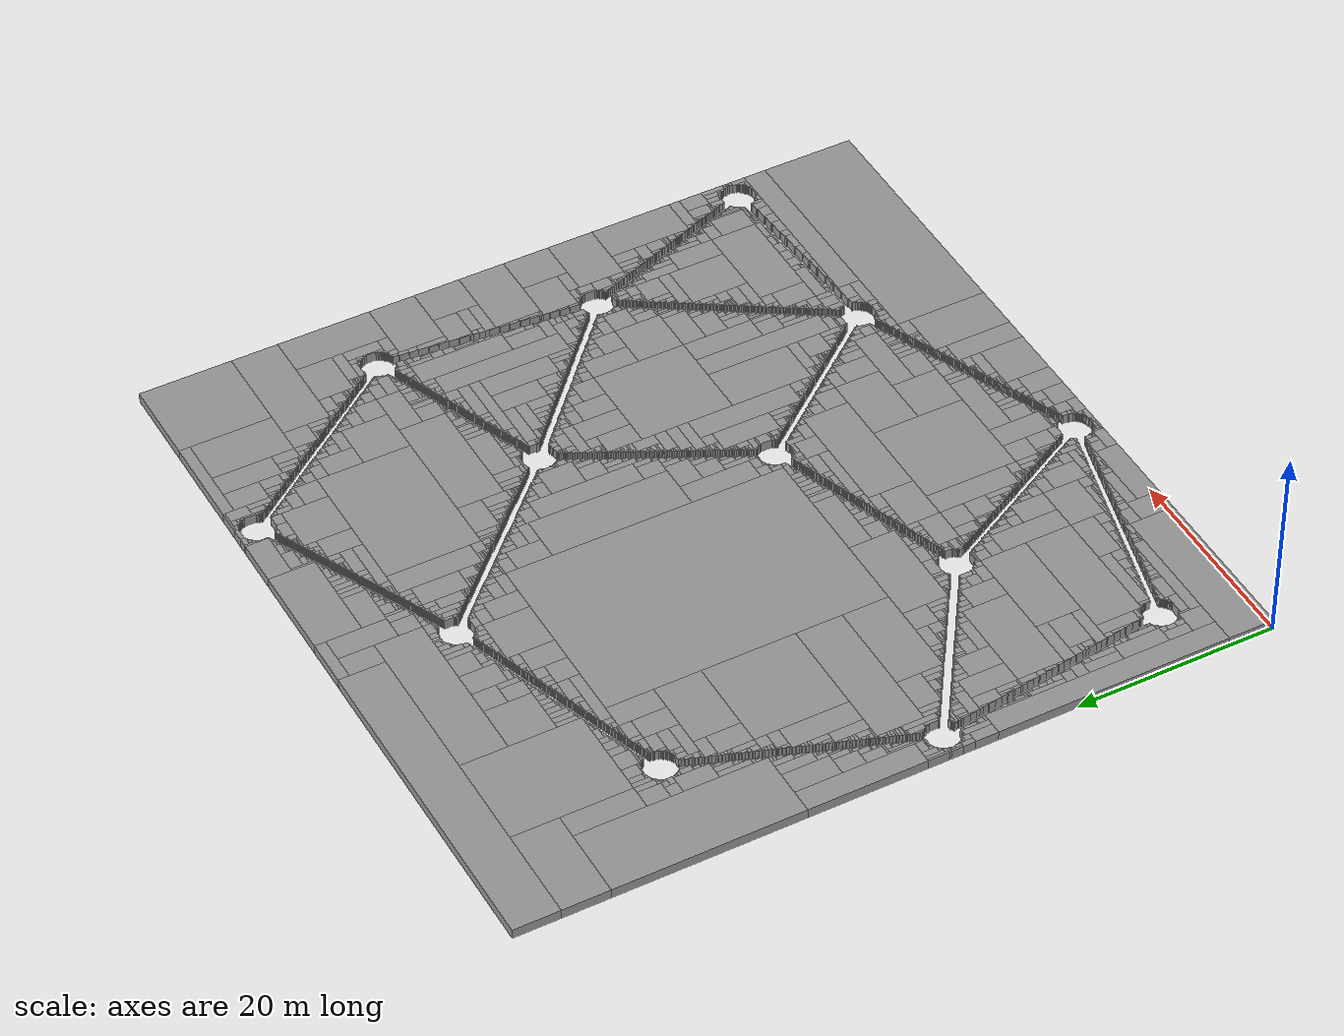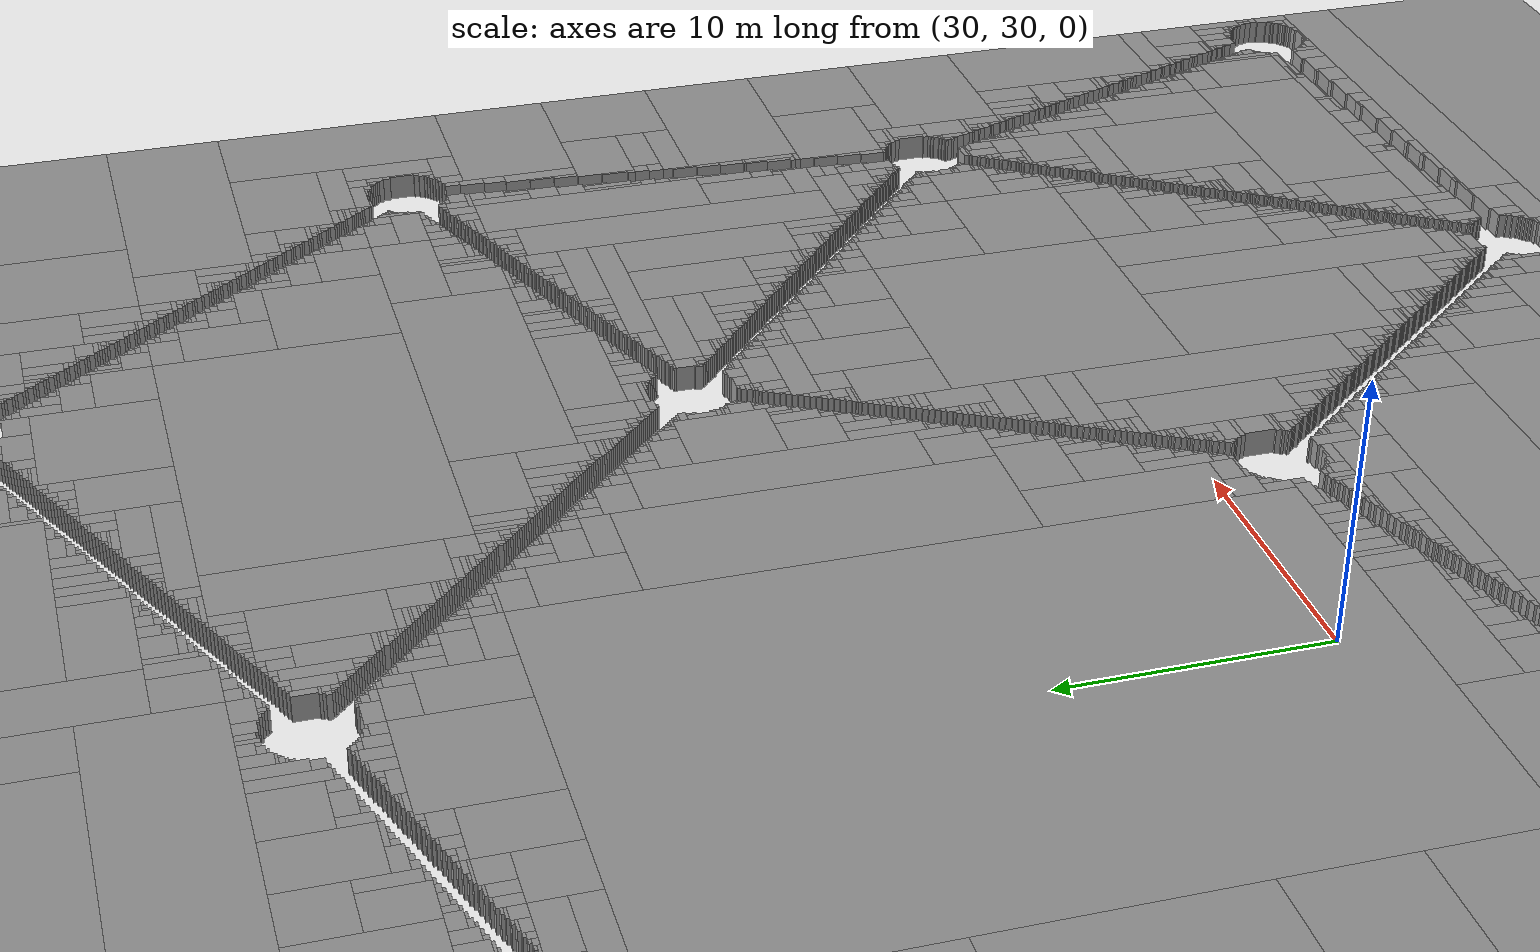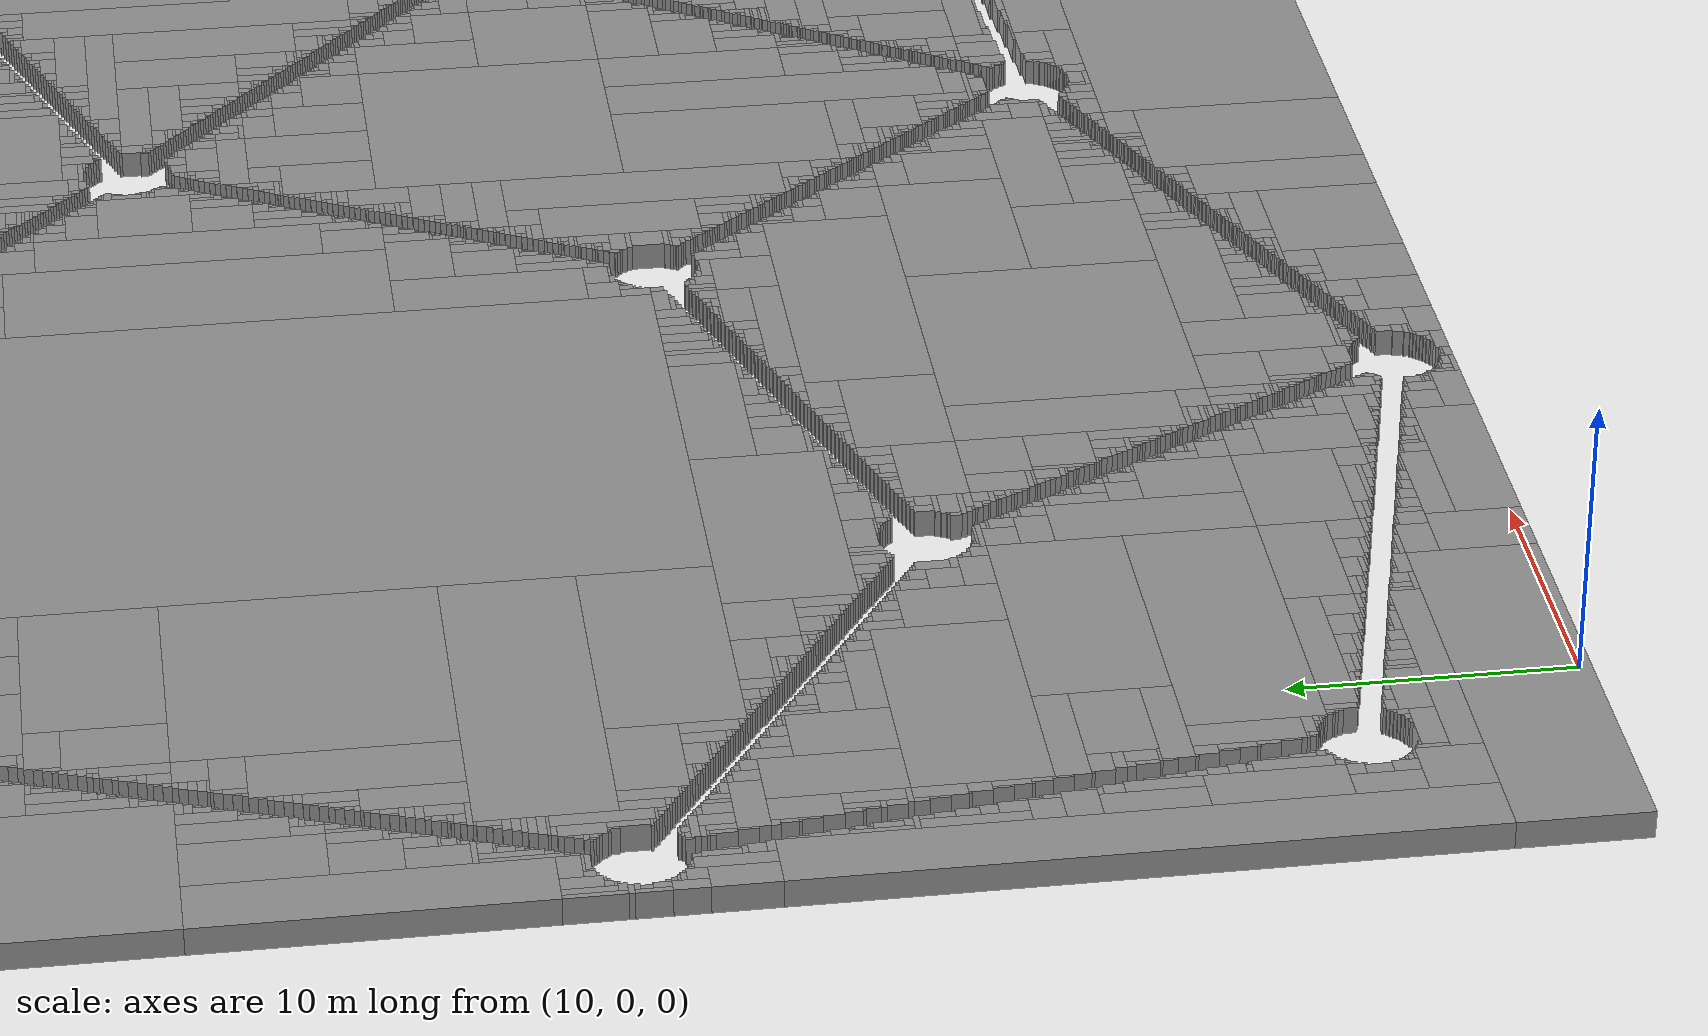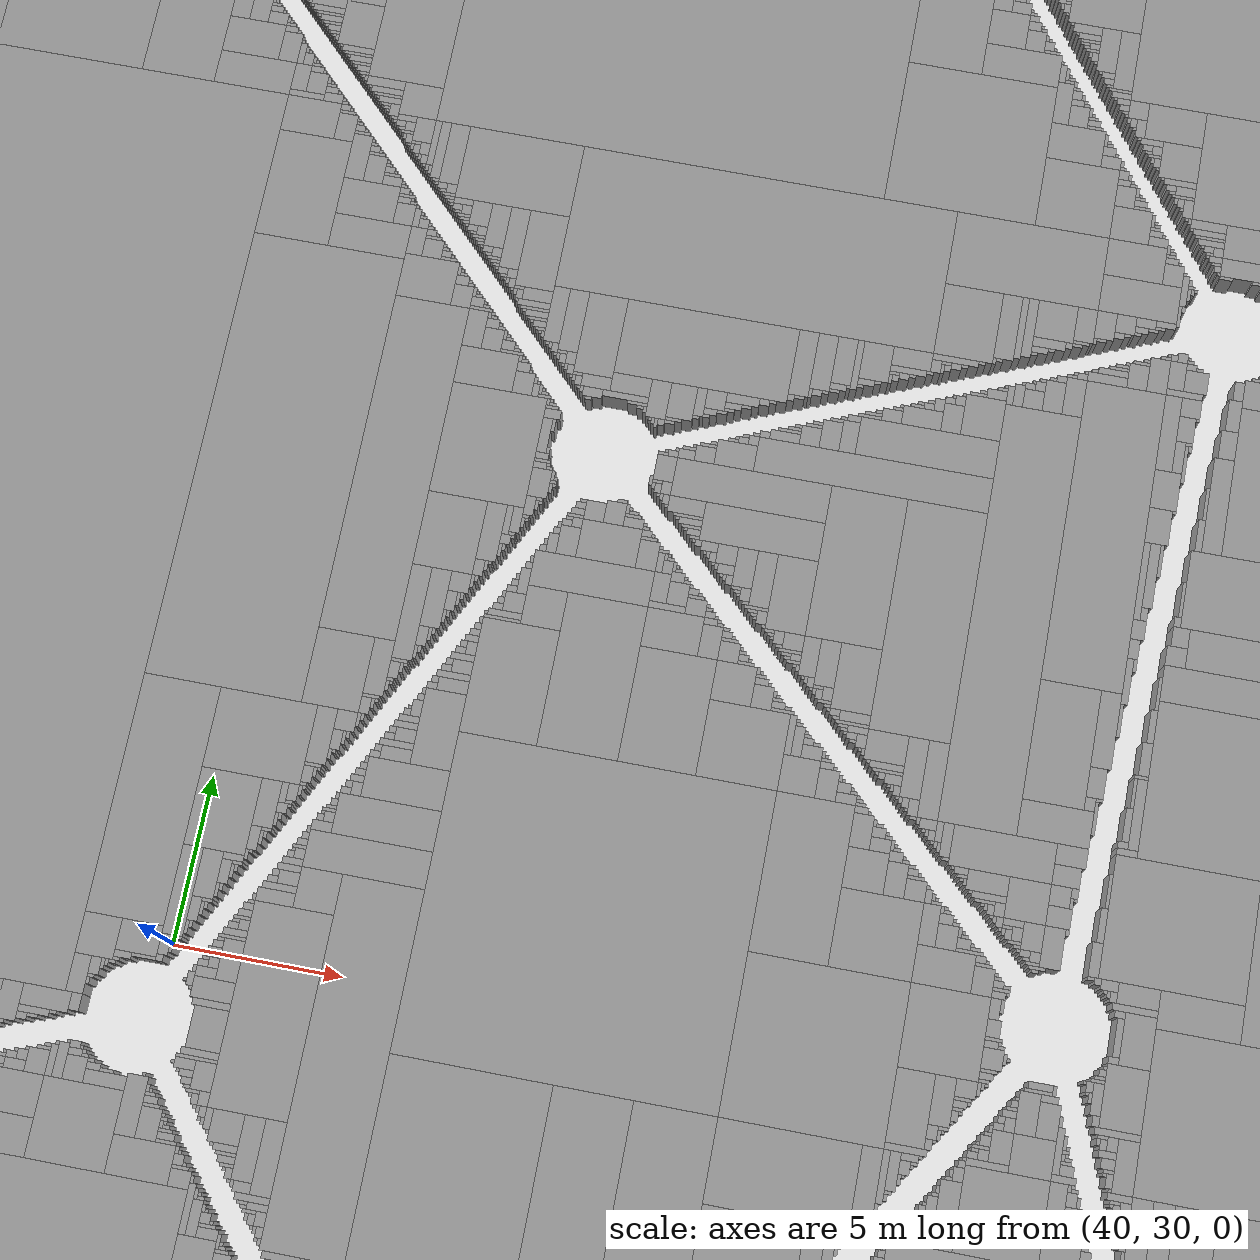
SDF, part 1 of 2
<?xml version='1.0'?>
<sdf version='1.6'>
<model name='ImageMaze'>
<pose frame=''>0 0 0 0 -0 0</pose>
<link name='WallLink'>
<collision name='Wall_8.2_2.3_Collision'>
	<geometry>
	<box>
 <size>16.300001 4.600000 1.000000</size>
 </box>
</geometry>
<pose frame=''>8.150001 2.300000 0.500000 0 0 0</pose>
</collision>
	<visual name='Wall_8.2_2.3_Visual'>
<pose frame=''>8.150001 2.300000 0.500000 0 0 0</pose>
	<geometry>
<box>
<size>16.300001 4.600000 1.000000</size>
</box>
</geometry>
<material>
<script>
<uri>file://media/materials/scripts/gazebo.material</uri>
<name>Gazebo/Grey</name>
</script>
<ambient>1 1 1 1</ambient>
</material>
</visual>
<collision name='Wall_1.1_16.4_Collision'>
	<geometry>
	<box>
 <size>2.300000 23.500000 1.000000</size>
 </box>
</geometry>
<pose frame=''>1.150000 16.350000 0.500000 0 0 0</pose>
</collision>
	<visual name='Wall_1.1_16.4_Visual'>
<pose frame=''>1.150000 16.350000 0.500000 0 0 0</pose>
	<geometry>
<box>
<size>2.300000 23.500000 1.000000</size>
</box>
</geometry>
<material>
<script>
<uri>file://media/materials/scripts/gazebo.material</uri>
<name>Gazebo/Grey</name>
</script>
<ambient>1 1 1 1</ambient>
</material>
</visual>
<collision name='Wall_3.5_5.8_Collision'>
	<geometry>
	<box>
 <size>2.300000 2.300000 1.000000</size>
 </box>
</geometry>
<pose frame=''>3.450000 5.750000 0.500000 0 0 0</pose>
</collision>
	<visual name='Wall_3.5_5.8_Visual'>
<pose frame=''>3.450000 5.750000 0.500000 0 0 0</pose>
	<geometry>
<box>
<size>2.300000 2.300000 1.000000</size>
</box>
</geometry>
<material>
<script>
<uri>file://media/materials/scripts/gazebo.material</uri>
<name>Gazebo/Grey</name>
</script>
<ambient>1 1 1 1</ambient>
</material>
</visual>
<collision name='Wall_2.9_8.1_Collision'>
	<geometry>
	<box>
 <size>1.100000 2.400000 1.000000</size>
 </box>
</geometry>
<pose frame=''>2.850000 8.100000 0.500000 0 0 0</pose>
</collision>
	<visual name='Wall_2.9_8.1_Visual'>
<pose frame=''>2.850000 8.100000 0.500000 0 0 0</pose>
	<geometry>
<box>
<size>1.100000 2.400000 1.000000</size>
</box>
</geometry>
<material>
<script>
<uri>file://media/materials/scripts/gazebo.material</uri>
<name>Gazebo/Grey</name>
</script>
<ambient>1 1 1 1</ambient>
</material>
</visual>
<collision name='Wall_3.7_7.3_Collision'>
	<geometry>
	<box>
 <size>0.600000 0.900000 1.000000</size>
 </box>
</geometry>
<pose frame=''>3.700000 7.350000 0.500000 0 0 0</pose>
</collision>
	<visual name='Wall_3.7_7.3_Visual'>
<pose frame=''>3.700000 7.350000 0.500000 0 0 0</pose>
	<geometry>
<box>
<size>0.600000 0.900000 1.000000</size>
</box>
</geometry>
<material>
<script>
<uri>file://media/materials/scripts/gazebo.material</uri>
<name>Gazebo/Grey</name>
</script>
<ambient>1 1 1 1</ambient>
</material>
</visual>
<collision name='Wall_4.2_7.0_Collision'>
	<geometry>
	<box>
 <size>0.500000 0.100000 1.000000</size>
 </box>
</geometry>
<pose frame=''>4.250000 6.950000 0.500000 0 0 0</pose>
</collision>
	<visual name='Wall_4.2_7.0_Visual'>
<pose frame=''>4.250000 6.950000 0.500000 0 0 0</pose>
	<geometry>
<box>
<size>0.500000 0.100000 1.000000</size>
</box>
</geometry>
<material>
<script>
<uri>file://media/materials/scripts/gazebo.material</uri>
<name>Gazebo/Grey</name>
</script>
<ambient>1 1 1 1</ambient>
</material>
</visual>
<collision name='Wall_4.2_7.1_Collision'>
	<geometry>
	<box>
 <size>0.300000 0.200000 1.000000</size>
 </box>
</geometry>
<pose frame=''>4.150000 7.100000 0.500000 0 0 0</pose>
</collision>
	<visual name='Wall_4.2_7.1_Visual'>
<pose frame=''>4.150000 7.100000 0.500000 0 0 0</pose>
	<geometry>
<box>
<size>0.300000 0.200000 1.000000</size>
</box>
</geometry>
<material>
<script>
<uri>file://media/materials/scripts/gazebo.material</uri>
<name>Gazebo/Grey</name>
</script>
<ambient>1 1 1 1</ambient>
</material>
</visual>
<collision name='Wall_4.3_7.1_Collision'>
	<geometry>
	<box>
 <size>0.100000 0.100000 1.000000</size>
 </box>
</geometry>
<pose frame=''>4.350000 7.050000 0.500000 0 0 0</pose>
</collision>
	<visual name='Wall_4.3_7.1_Visual'>
<pose frame=''>4.350000 7.050000 0.500000 0 0 0</pose>
	<geometry>
<box>
<size>0.100000 0.100000 1.000000</size>
</box>
</geometry>
<material>
<script>
<uri>file://media/materials/scripts/gazebo.material</uri>
<name>Gazebo/Grey</name>
</script>
<ambient>1 1 1 1</ambient>
</material>
</visual>
<collision name='Wall_4.1_7.2_Collision'>
	<geometry>
	<box>
 <size>0.200000 0.100000 1.000000</size>
 </box>
</geometry>
<pose frame=''>4.100000 7.250000 0.500000 0 0 0</pose>
</collision>
	<visual name='Wall_4.1_7.2_Visual'>
<pose frame=''>4.100000 7.250000 0.500000 0 0 0</pose>
	<geometry>
<box>
<size>0.200000 0.100000 1.000000</size>
</box>
</geometry>
<material>
<script>
<uri>file://media/materials/scripts/gazebo.material</uri>
<name>Gazebo/Grey</name>
</script>
<ambient>1 1 1 1</ambient>
</material>
</visual>
<collision name='Wall_4.1_7.4_Collision'>
	<geometry>
	<box>
 <size>0.100000 0.200000 1.000000</size>
 </box>
</geometry>
<pose frame=''>4.050000 7.400000 0.500000 0 0 0</pose>
</collision>
	<visual name='Wall_4.1_7.4_Visual'>
<pose frame=''>4.050000 7.400000 0.500000 0 0 0</pose>
	<geometry>
<box>
<size>0.100000 0.200000 1.000000</size>
</box>
</geometry>
<material>
<script>
<uri>file://media/materials/scripts/gazebo.material</uri>
<name>Gazebo/Grey</name>
</script>
<ambient>1 1 1 1</ambient>
</material>
</visual>
<collision name='Wall_3.7_8.2_Collision'>
	<geometry>
	<box>
 <size>0.500000 0.900000 1.000000</size>
 </box>
</geometry>
<pose frame=''>3.650000 8.250000 0.500000 0 0 0</pose>
</collision>
	<visual name='Wall_3.7_8.2_Visual'>
<pose frame=''>3.650000 8.250000 0.500000 0 0 0</pose>
	<geometry>
<box>
<size>0.500000 0.900000 1.000000</size>
</box>
</geometry>
<material>
<script>
<uri>file://media/materials/scripts/gazebo.material</uri>
<name>Gazebo/Grey</name>
</script>
<ambient>1 1 1 1</ambient>
</material>
</visual>
<collision name='Wall_4.0_8.7_Collision'>
	<geometry>
	<box>
 <size>0.100000 0.100000 1.000000</size>
 </box>
</geometry>
<pose frame=''>3.950000 8.650001 0.500000 0 0 0</pose>
</collision>
	<visual name='Wall_4.0_8.7_Visual'>
<pose frame=''>3.950000 8.650001 0.500000 0 0 0</pose>
	<geometry>
<box>
<size>0.100000 0.100000 1.000000</size>
</box>
</geometry>
<material>
<script>
<uri>file://media/materials/scripts/gazebo.material</uri>
<name>Gazebo/Grey</name>
</script>
<ambient>1 1 1 1</ambient>
</material>
</visual>
<collision name='Wall_3.7_9.0_Collision'>
	<geometry>
	<box>
 <size>0.600000 0.600000 1.000000</size>
 </box>
</geometry>
<pose frame=''>3.700000 9.000000 0.500000 0 0 0</pose>
</collision>
	<visual name='Wall_3.7_9.0_Visual'>
<pose frame=''>3.700000 9.000000 0.500000 0 0 0</pose>
	<geometry>
<box>
<size>0.600000 0.600000 1.000000</size>
</box>
</geometry>
<material>
<script>
<uri>file://media/materials/scripts/gazebo.material</uri>
<name>Gazebo/Grey</name>
</script>
<ambient>1 1 1 1</ambient>
</material>
</visual>
<collision name='Wall_4.1_9.1_Collision'>
	<geometry>
	<box>
 <size>0.100000 0.400000 1.000000</size>
 </box>
</geometry>
<pose frame=''>4.050000 9.100000 0.500000 0 0 0</pose>
</collision>
	<visual name='Wall_4.1_9.1_Visual'>
<pose frame=''>4.050000 9.100000 0.500000 0 0 0</pose>
	<geometry>
<box>
<size>0.100000 0.400000 1.000000</size>
</box>
</geometry>
<material>
<script>
<uri>file://media/materials/scripts/gazebo.material</uri>
<name>Gazebo/Grey</name>
</script>
<ambient>1 1 1 1</ambient>
</material>
</visual>
<collision name='Wall_4.2_9.2_Collision'>
	<geometry>
	<box>
 <size>0.100000 0.200000 1.000000</size>
 </box>
</geometry>
<pose frame=''>4.150000 9.200000 0.500000 0 0 0</pose>
</collision>
	<visual name='Wall_4.2_9.2_Visual'>
<pose frame=''>4.150000 9.200000 0.500000 0 0 0</pose>
	<geometry>
<box>
<size>0.100000 0.200000 1.000000</size>
</box>
</geometry>
<material>
<script>
<uri>file://media/materials/scripts/gazebo.material</uri>
<name>Gazebo/Grey</name>
</script>
<ambient>1 1 1 1</ambient>
</material>
</visual>
<collision name='Wall_4.2_9.2_Collision'>
	<geometry>
	<box>
 <size>0.100000 0.100000 1.000000</size>
 </box>
</geometry>
<pose frame=''>4.250000 9.250000 0.500000 0 0 0</pose>
</collision>
	<visual name='Wall_4.2_9.2_Visual'>
<pose frame=''>4.250000 9.250000 0.500000 0 0 0</pose>
	<geometry>
<box>
<size>0.100000 0.100000 1.000000</size>
</box>
</geometry>
<material>
<script>
<uri>file://media/materials/scripts/gazebo.material</uri>
<name>Gazebo/Grey</name>
</script>
<ambient>1 1 1 1</ambient>
</material>
</visual>
<collision name='Wall_9.3_5.2_Collision'>
	<geometry>
	<box>
 <size>9.400001 1.100000 1.000000</size>
 </box>
</geometry>
<pose frame=''>9.300000 5.150000 0.500000 0 0 0</pose>
</collision>
	<visual name='Wall_9.3_5.2_Visual'>
<pose frame=''>9.300000 5.150000 0.500000 0 0 0</pose>
	<geometry>
<box>
<size>9.400001 1.100000 1.000000</size>
</box>
</geometry>
<material>
<script>
<uri>file://media/materials/scripts/gazebo.material</uri>
<name>Gazebo/Grey</name>
</script>
<ambient>1 1 1 1</ambient>
</material>
</visual>
<collision name='Wall_4.7_6.2_Collision'>
	<geometry>
	<box>
 <size>0.200000 1.100000 1.000000</size>
 </box>
</geometry>
<pose frame=''>4.700000 6.250000 0.500000 0 0 0</pose>
</collision>
	<visual name='Wall_4.7_6.2_Visual'>
<pose frame=''>4.700000 6.250000 0.500000 0 0 0</pose>
	<geometry>
<box>
<size>0.200000 1.100000 1.000000</size>
</box>
</geometry>
<material>
<script>
<uri>file://media/materials/scripts/gazebo.material</uri>
<name>Gazebo/Grey</name>
</script>
<ambient>1 1 1 1</ambient>
</material>
</visual>
<collision name='Wall_5.8_6.2_Collision'>
	<geometry>
	<box>
 <size>2.100000 0.900000 1.000000</size>
 </box>
</geometry>
<pose frame=''>5.850000 6.150000 0.500000 0 0 0</pose>
</collision>
	<visual name='Wall_5.8_6.2_Visual'>
<pose frame=''>5.850000 6.150000 0.500000 0 0 0</pose>
	<geometry>
<box>
<size>2.100000 0.900000 1.000000</size>
</box>
</geometry>
<material>
<script>
<uri>file://media/materials/scripts/gazebo.material</uri>
<name>Gazebo/Grey</name>
</script>
<ambient>1 1 1 1</ambient>
</material>
</visual>
<collision name='Wall_4.9_6.7_Collision'>
	<geometry>
	<box>
 <size>0.200000 0.100000 1.000000</size>
 </box>
</geometry>
<pose frame=''>4.900000 6.650000 0.500000 0 0 0</pose>
</collision>
	<visual name='Wall_4.9_6.7_Visual'>
<pose frame=''>4.900000 6.650000 0.500000 0 0 0</pose>
	<geometry>
<box>
<size>0.200000 0.100000 1.000000</size>
</box>
</geometry>
<material>
<script>
<uri>file://media/materials/scripts/gazebo.material</uri>
<name>Gazebo/Grey</name>
</script>
<ambient>1 1 1 1</ambient>
</material>
</visual>
<collision name='Wall_6.2_6.7_Collision'>
	<geometry>
	<box>
 <size>0.200000 0.100000 1.000000</size>
 </box>
</geometry>
<pose frame=''>6.200000 6.650000 0.500000 0 0 0</pose>
</collision>
	<visual name='Wall_6.2_6.7_Visual'>
<pose frame=''>6.200000 6.650000 0.500000 0 0 0</pose>
	<geometry>
<box>
<size>0.200000 0.100000 1.000000</size>
</box>
</geometry>
<material>
<script>
<uri>file://media/materials/scripts/gazebo.material</uri>
<name>Gazebo/Grey</name>
</script>
<ambient>1 1 1 1</ambient>
</material>
</visual>
<collision name='Wall_6.5_6.7_Collision'>
	<geometry>
	<box>
 <size>0.300000 0.200000 1.000000</size>
 </box>
</geometry>
<pose frame=''>6.450000 6.700000 0.500000 0 0 0</pose>
</collision>
	<visual name='Wall_6.5_6.7_Visual'>
<pose frame=''>6.450000 6.700000 0.500000 0 0 0</pose>
	<geometry>
<box>
<size>0.300000 0.200000 1.000000</size>
</box>
</geometry>
<material>
<script>
<uri>file://media/materials/scripts/gazebo.material</uri>
<name>Gazebo/Grey</name>
</script>
<ambient>1 1 1 1</ambient>
</material>
</visual>
<collision name='Wall_6.6_6.8_Collision'>
	<geometry>
	<box>
 <size>0.100000 0.100000 1.000000</size>
 </box>
</geometry>
<pose frame=''>6.550000 6.850000 0.500000 0 0 0</pose>
</collision>
	<visual name='Wall_6.6_6.8_Visual'>
<pose frame=''>6.550000 6.850000 0.500000 0 0 0</pose>
	<geometry>
<box>
<size>0.100000 0.100000 1.000000</size>
</box>
</geometry>
<material>
<script>
<uri>file://media/materials/scripts/gazebo.material</uri>
<name>Gazebo/Grey</name>
</script>
<ambient>1 1 1 1</ambient>
</material>
</visual>
<collision name='Wall_6.8_6.8_Collision'>
	<geometry>
	<box>
 <size>0.300000 0.400000 1.000000</size>
 </box>
</geometry>
<pose frame=''>6.750000 6.800000 0.500000 0 0 0</pose>
</collision>
	<visual name='Wall_6.8_6.8_Visual'>
<pose frame=''>6.750000 6.800000 0.500000 0 0 0</pose>
	<geometry>
<box>
<size>0.300000 0.400000 1.000000</size>
</box>
</geometry>
<material>
<script>
<uri>file://media/materials/scripts/gazebo.material</uri>
<name>Gazebo/Grey</name>
</script>
<ambient>1 1 1 1</ambient>
</material>
</visual>
<collision name='Wall_8.1_6.3_Collision'>
	<geometry>
	<box>
 <size>2.400000 1.200000 1.000000</size>
 </box>
</geometry>
<pose frame=''>8.100000 6.300000 0.500000 0 0 0</pose>
</collision>
	<visual name='Wall_8.1_6.3_Visual'>
<pose frame=''>8.100000 6.300000 0.500000 0 0 0</pose>
	<geometry>
<box>
<size>2.400000 1.200000 1.000000</size>
</box>
</geometry>
<material>
<script>
<uri>file://media/materials/scripts/gazebo.material</uri>
<name>Gazebo/Grey</name>
</script>
<ambient>1 1 1 1</ambient>
</material>
</visual>
<collision name='Wall_6.8_7.1_Collision'>
	<geometry>
	<box>
 <size>0.200000 0.100000 1.000000</size>
 </box>
</geometry>
<pose frame=''>6.800000 7.050000 0.500000 0 0 0</pose>
</collision>
	<visual name='Wall_6.8_7.1_Visual'>
<pose frame=''>6.800000 7.050000 0.500000 0 0 0</pose>
	<geometry>
<box>
<size>0.200000 0.100000 1.000000</size>
</box>
</geometry>
<material>
<script>
<uri>file://media/materials/scripts/gazebo.material</uri>
<name>Gazebo/Grey</name>
</script>
<ambient>1 1 1 1</ambient>
</material>
</visual>
<collision name='Wall_6.8_7.2_Collision'>
	<geometry>
	<box>
 <size>0.100000 0.100000 1.000000</size>
 </box>
</geometry>
<pose frame=''>6.850000 7.150000 0.500000 0 0 0</pose>
</collision>
	<visual name='Wall_6.8_7.2_Visual'>
<pose frame=''>6.850000 7.150000 0.500000 0 0 0</pose>
	<geometry>
<box>
<size>0.100000 0.100000 1.000000</size>
</box>
</geometry>
<material>
<script>
<uri>file://media/materials/scripts/gazebo.material</uri>
<name>Gazebo/Grey</name>
</script>
<ambient>1 1 1 1</ambient>
</material>
</visual>
<collision name='Wall_7.2_7.1_Collision'>
	<geometry>
	<box>
 <size>0.600000 0.400000 1.000000</size>
 </box>
</geometry>
<pose frame=''>7.200000 7.100000 0.500000 0 0 0</pose>
</collision>
	<visual name='Wall_7.2_7.1_Visual'>
<pose frame=''>7.200000 7.100000 0.500000 0 0 0</pose>
	<geometry>
<box>
<size>0.600000 0.400000 1.000000</size>
</box>
</geometry>
<material>
<script>
<uri>file://media/materials/scripts/gazebo.material</uri>
<name>Gazebo/Grey</name>
</script>
<ambient>1 1 1 1</ambient>
</material>
</visual>
<collision name='Wall_7.2_7.3_Collision'>
	<geometry>
	<box>
 <size>0.300000 0.100000 1.000000</size>
 </box>
</geometry>
<pose frame=''>7.150000 7.350000 0.500000 0 0 0</pose>
</collision>
	<visual name='Wall_7.2_7.3_Visual'>
<pose frame=''>7.150000 7.350000 0.500000 0 0 0</pose>
	<geometry>
<box>
<size>0.300000 0.100000 1.000000</size>
</box>
</geometry>
<material>
<script>
<uri>file://media/materials/scripts/gazebo.material</uri>
<name>Gazebo/Grey</name>
</script>
<ambient>1 1 1 1</ambient>
</material>
</visual>
<collision name='Wall_7.8_7.1_Collision'>
	<geometry>
	<box>
 <size>0.600000 0.300000 1.000000</size>
 </box>
</geometry>
<pose frame=''>7.800000 7.050000 0.500000 0 0 0</pose>
</collision>
	<visual name='Wall_7.8_7.1_Visual'>
<pose frame=''>7.800000 7.050000 0.500000 0 0 0</pose>
	<geometry>
<box>
<size>0.600000 0.300000 1.000000</size>
</box>
</geometry>
<material>
<script>
<uri>file://media/materials/scripts/gazebo.material</uri>
<name>Gazebo/Grey</name>
</script>
<ambient>1 1 1 1</ambient>
</material>
</visual>
<collision name='Wall_7.6_7.2_Collision'>
	<geometry>
	<box>
 <size>0.200000 0.100000 1.000000</size>
 </box>
</geometry>
<pose frame=''>7.600000 7.250000 0.500000 0 0 0</pose>
</collision>
	<visual name='Wall_7.6_7.2_Visual'>
<pose frame=''>7.600000 7.250000 0.500000 0 0 0</pose>
	<geometry>
<box>
<size>0.200000 0.100000 1.000000</size>
</box>
</geometry>
<material>
<script>
<uri>file://media/materials/scripts/gazebo.material</uri>
<name>Gazebo/Grey</name>
</script>
<ambient>1 1 1 1</ambient>
</material>
</visual>
<collision name='Wall_8.1_8.1_Collision'>
	<geometry>
	<box>
 <size>0.400000 0.100000 1.000000</size>
 </box>
</geometry>
<pose frame=''>8.100000 8.050000 0.500000 0 0 0</pose>
</collision>
	<visual name='Wall_8.1_8.1_Visual'>
<pose frame=''>8.100000 8.050000 0.500000 0 0 0</pose>
	<geometry>
<box>
<size>0.400000 0.100000 1.000000</size>
</box>
</geometry>
<material>
<script>
<uri>file://media/materials/scripts/gazebo.material</uri>
<name>Gazebo/Grey</name>
</script>
<ambient>1 1 1 1</ambient>
</material>
</visual>
<collision name='Wall_8.2_7.0_Collision'>
	<geometry>
	<box>
 <size>0.300000 0.200000 1.000000</size>
 </box>
</geometry>
<pose frame=''>8.250000 7.000000 0.500000 0 0 0</pose>
</collision>
	<visual name='Wall_8.2_7.0_Visual'>
<pose frame=''>8.250000 7.000000 0.500000 0 0 0</pose>
	<geometry>
<box>
<size>0.300000 0.200000 1.000000</size>
</box>
</geometry>
<material>
<script>
<uri>file://media/materials/scripts/gazebo.material</uri>
<name>Gazebo/Grey</name>
</script>
<ambient>1 1 1 1</ambient>
</material>
</visual>
<collision name='Wall_8.7_7.0_Collision'>
	<geometry>
	<box>
 <size>0.500000 0.100000 1.000000</size>
 </box>
</geometry>
<pose frame=''>8.650001 6.950000 0.500000 0 0 0</pose>
</collision>
	<visual name='Wall_8.7_7.0_Visual'>
<pose frame=''>8.650001 6.950000 0.500000 0 0 0</pose>
	<geometry>
<box>
<size>0.500000 0.100000 1.000000</size>
</box>
</geometry>
<material>
<script>
<uri>file://media/materials/scripts/gazebo.material</uri>
<name>Gazebo/Grey</name>
</script>
<ambient>1 1 1 1</ambient>
</material>
</visual>
<collision name='Wall_8.4_7.1_Collision'>
	<geometry>
	<box>
 <size>0.100000 0.100000 1.000000</size>
 </box>
</geometry>
<pose frame=''>8.450000 7.050000 0.500000 0 0 0</pose>
</collision>
	<visual name='Wall_8.4_7.1_Visual'>
<pose frame=''>8.450000 7.050000 0.500000 0 0 0</pose>
	<geometry>
<box>
<size>0.100000 0.100000 1.000000</size>
</box>
</geometry>
<material>
<script>
<uri>file://media/materials/scripts/gazebo.material</uri>
<name>Gazebo/Grey</name>
</script>
<ambient>1 1 1 1</ambient>
</material>
</visual>
<collision name='Wall_8.8_8.0_Collision'>
	<geometry>
	<box>
 <size>1.000000 0.200000 1.000000</size>
 </box>
</geometry>
<pose frame=''>8.800000 8.000000 0.500000 0 0 0</pose>
</collision>
	<visual name='Wall_8.8_8.0_Visual'>
<pose frame=''>8.800000 8.000000 0.500000 0 0 0</pose>
	<geometry>
<box>
<size>1.000000 0.200000 1.000000</size>
</box>
</geometry>
<material>
<script>
<uri>file://media/materials/scripts/gazebo.material</uri>
<name>Gazebo/Grey</name>
</script>
<ambient>1 1 1 1</ambient>
</material>
</visual>
<collision name='Wall_8.8_7.8_Collision'>
	<geometry>
	<box>
 <size>0.400000 0.100000 1.000000</size>
 </box>
</geometry>
<pose frame=''>8.800000 7.850000 0.500000 0 0 0</pose>
</collision>
	<visual name='Wall_8.8_7.8_Visual'>
<pose frame=''>8.800000 7.850000 0.500000 0 0 0</pose>
	<geometry>
<box>
<size>0.400000 0.100000 1.000000</size>
</box>
</geometry>
<material>
<script>
<uri>file://media/materials/scripts/gazebo.material</uri>
<name>Gazebo/Grey</name>
</script>
<ambient>1 1 1 1</ambient>
</material>
</visual>
<collision name='Wall_9.2_7.8_Collision'>
	<geometry>
	<box>
 <size>0.300000 0.200000 1.000000</size>
 </box>
</geometry>
<pose frame=''>9.150001 7.800000 0.500000 0 0 0</pose>
</collision>
	<visual name='Wall_9.2_7.8_Visual'>
<pose frame=''>9.150001 7.800000 0.500000 0 0 0</pose>
	<geometry>
<box>
<size>0.300000 0.200000 1.000000</size>
</box>
</geometry>
<material>
<script>
<uri>file://media/materials/scripts/gazebo.material</uri>
<name>Gazebo/Grey</name>
</script>
<ambient>1 1 1 1</ambient>
</material>
</visual>
<collision name='Wall_7.3_8.8_Collision'>
	<geometry>
	<box>
 <size>0.300000 1.100000 1.000000</size>
 </box>
</geometry>
<pose frame=''>7.350000 8.750000 0.500000 0 0 0</pose>
</collision>
	<visual name='Wall_7.3_8.8_Visual'>
<pose frame=''>7.350000 8.750000 0.500000 0 0 0</pose>
	<geometry>
<box>
<size>0.300000 1.100000 1.000000</size>
</box>
</geometry>
<material>
<script>
<uri>file://media/materials/scripts/gazebo.material</uri>
<name>Gazebo/Grey</name>
</script>
<ambient>1 1 1 1</ambient>
</material>
</visual>
<collision name='Wall_10.8_8.7_Collision'>
	<geometry>
	<box>
 <size>6.500000 1.200000 1.000000</size>
 </box>
</geometry>
<pose frame=''>10.750000 8.700000 0.500000 0 0 0</pose>
</collision>
	<visual name='Wall_10.8_8.7_Visual'>
<pose frame=''>10.750000 8.700000 0.500000 0 0 0</pose>
	<geometry>
<box>
<size>6.500000 1.200000 1.000000</size>
</box>
</geometry>
<material>
<script>
<uri>file://media/materials/scripts/gazebo.material</uri>
<name>Gazebo/Grey</name>
</script>
<ambient>1 1 1 1</ambient>
</material>
</visual>
<collision name='Wall_7.2_8.9_Collision'>
	<geometry>
	<box>
 <size>0.100000 0.300000 1.000000</size>
 </box>
</geometry>
<pose frame=''>7.150000 8.850000 0.500000 0 0 0</pose>
</collision>
	<visual name='Wall_7.2_8.9_Visual'>
<pose frame=''>7.150000 8.850000 0.500000 0 0 0</pose>
	<geometry>
<box>
<size>0.100000 0.300000 1.000000</size>
</box>
</geometry>
<material>
<script>
<uri>file://media/materials/scripts/gazebo.material</uri>
<name>Gazebo/Grey</name>
</script>
<ambient>1 1 1 1</ambient>
</material>
</visual>
<collision name='Wall_7.1_8.9_Collision'>
	<geometry>
	<box>
 <size>0.100000 0.100000 1.000000</size>
 </box>
</geometry>
<pose frame=''>7.050000 8.950000 0.500000 0 0 0</pose>
</collision>
	<visual name='Wall_7.1_8.9_Visual'>
<pose frame=''>7.050000 8.950000 0.500000 0 0 0</pose>
	<geometry>
<box>
<size>0.100000 0.100000 1.000000</size>
</box>
</geometry>
<material>
<script>
<uri>file://media/materials/scripts/gazebo.material</uri>
<name>Gazebo/Grey</name>
</script>
<ambient>1 1 1 1</ambient>
</material>
</visual>
<collision name='Wall_7.1_9.2_Collision'>
	<geometry>
	<box>
 <size>0.200000 0.300000 1.000000</size>
 </box>
</geometry>
<pose frame=''>7.100000 9.150001 0.500000 0 0 0</pose>
</collision>
	<visual name='Wall_7.1_9.2_Visual'>
<pose frame=''>7.100000 9.150001 0.500000 0 0 0</pose>
	<geometry>
<box>
<size>0.200000 0.300000 1.000000</size>
</box>
</geometry>
<material>
<script>
<uri>file://media/materials/scripts/gazebo.material</uri>
<name>Gazebo/Grey</name>
</script>
<ambient>1 1 1 1</ambient>
</material>
</visual>
<collision name='Wall_7.0_9.2_Collision'>
	<geometry>
	<box>
 <size>0.100000 0.200000 1.000000</size>
 </box>
</geometry>
<pose frame=''>6.950000 9.200000 0.500000 0 0 0</pose>
</collision>
	<visual name='Wall_7.0_9.2_Visual'>
<pose frame=''>6.950000 9.200000 0.500000 0 0 0</pose>
	<geometry>
<box>
<size>0.100000 0.200000 1.000000</size>
</box>
</geometry>
<material>
<script>
<uri>file://media/materials/scripts/gazebo.material</uri>
<name>Gazebo/Grey</name>
</script>
<ambient>1 1 1 1</ambient>
</material>
</visual>
<collision name='Wall_17.5_1.7_Collision'>
	<geometry>
	<box>
 <size>2.400000 3.400000 1.000000</size>
 </box>
</geometry>
<pose frame=''>17.500000 1.700000 0.500000 0 0 0</pose>
</collision>
	<visual name='Wall_17.5_1.7_Visual'>
<pose frame=''>17.500000 1.700000 0.500000 0 0 0</pose>
	<geometry>
<box>
<size>2.400000 3.400000 1.000000</size>
</box>
</geometry>
<material>
<script>
<uri>file://media/materials/scripts/gazebo.material</uri>
<name>Gazebo/Grey</name>
</script>
<ambient>1 1 1 1</ambient>
</material>
</visual>
<collision name='Wall_17.2_4.0_Collision'>
	<geometry>
	<box>
 <size>1.800000 1.200000 1.000000</size>
 </box>
</geometry>
<pose frame=''>17.200001 4.000000 0.500000 0 0 0</pose>
</collision>
	<visual name='Wall_17.2_4.0_Visual'>
<pose frame=''>17.200001 4.000000 0.500000 0 0 0</pose>
	<geometry>
<box>
<size>1.800000 1.200000 1.000000</size>
</box>
</geometry>
<material>
<script>
<uri>file://media/materials/scripts/gazebo.material</uri>
<name>Gazebo/Grey</name>
</script>
<ambient>1 1 1 1</ambient>
</material>
</visual>
<collision name='Wall_18.5_3.9_Collision'>
	<geometry>
	<box>
 <size>0.800000 1.000000 1.000000</size>
 </box>
</geometry>
<pose frame=''>18.500000 3.900000 0.500000 0 0 0</pose>
</collision>
	<visual name='Wall_18.5_3.9_Visual'>
<pose frame=''>18.500000 3.900000 0.500000 0 0 0</pose>
	<geometry>
<box>
<size>0.800000 1.000000 1.000000</size>
</box>
</geometry>
<material>
<script>
<uri>file://media/materials/scripts/gazebo.material</uri>
<name>Gazebo/Grey</name>
</script>
<ambient>1 1 1 1</ambient>
</material>
</visual>
<collision name='Wall_18.1_4.5_Collision'>
	<geometry>
	<box>
 <size>0.100000 0.200000 1.000000</size>
 </box>
</geometry>
<pose frame=''>18.150000 4.500000 0.500000 0 0 0</pose>
</collision>
	<visual name='Wall_18.1_4.5_Visual'>
<pose frame=''>18.150000 4.500000 0.500000 0 0 0</pose>
	<geometry>
<box>
<size>0.100000 0.200000 1.000000</size>
</box>
</geometry>
<material>
<script>
<uri>file://media/materials/scripts/gazebo.material</uri>
<name>Gazebo/Grey</name>
</script>
<ambient>1 1 1 1</ambient>
</material>
</visual>
<collision name='Wall_18.5_4.5_Collision'>
	<geometry>
	<box>
 <size>0.500000 0.100000 1.000000</size>
 </box>
</geometry>
<pose frame=''>18.450001 4.450000 0.500000 0 0 0</pose>
</collision>
	<visual name='Wall_18.5_4.5_Visual'>
<pose frame=''>18.450001 4.450000 0.500000 0 0 0</pose>
	<geometry>
<box>
<size>0.500000 0.100000 1.000000</size>
</box>
</geometry>
<material>
<script>
<uri>file://media/materials/scripts/gazebo.material</uri>
<name>Gazebo/Grey</name>
</script>
<ambient>1 1 1 1</ambient>
</material>
</visual>
<collision name='Wall_18.2_4.6_Collision'>
	<geometry>
	<box>
 <size>0.100000 0.100000 1.000000</size>
 </box>
</geometry>
<pose frame=''>18.250000 4.550000 0.500000 0 0 0</pose>
</collision>
	<visual name='Wall_18.2_4.6_Visual'>
<pose frame=''>18.250000 4.550000 0.500000 0 0 0</pose>
	<geometry>
<box>
<size>0.100000 0.100000 1.000000</size>
</box>
</geometry>
<material>
<script>
<uri>file://media/materials/scripts/gazebo.material</uri>
<name>Gazebo/Grey</name>
</script>
<ambient>1 1 1 1</ambient>
</material>
</visual>
<collision name='Wall_9.4_6.2_Collision'>
	<geometry>
	<box>
 <size>0.200000 1.100000 1.000000</size>
 </box>
</geometry>
<pose frame=''>9.400001 6.250000 0.500000 0 0 0</pose>
</collision>
	<visual name='Wall_9.4_6.2_Visual'>
<pose frame=''>9.400001 6.250000 0.500000 0 0 0</pose>
	<geometry>
<box>
<size>0.200000 1.100000 1.000000</size>
</box>
</geometry>
<material>
<script>
<uri>file://media/materials/scripts/gazebo.material</uri>
<name>Gazebo/Grey</name>
</script>
<ambient>1 1 1 1</ambient>
</material>
</visual>
<collision name='Wall_9.7_6.2_Collision'>
	<geometry>
	<box>
 <size>0.300000 1.000000 1.000000</size>
 </box>
</geometry>
<pose frame=''>9.650001 6.200000 0.500000 0 0 0</pose>
</collision>
	<visual name='Wall_9.7_6.2_Visual'>
<pose frame=''>9.650001 6.200000 0.500000 0 0 0</pose>
	<geometry>
<box>
<size>0.300000 1.000000 1.000000</size>
</box>
</geometry>
<material>
<script>
<uri>file://media/materials/scripts/gazebo.material</uri>
<name>Gazebo/Grey</name>
</script>
<ambient>1 1 1 1</ambient>
</material>
</visual>
<collision name='Wall_10.1_6.2_Collision'>
	<geometry>
	<box>
 <size>0.600000 0.900000 1.000000</size>
 </box>
</geometry>
<pose frame=''>10.100000 6.150000 0.500000 0 0 0</pose>
</collision>
	<visual name='Wall_10.1_6.2_Visual'>
<pose frame=''>10.100000 6.150000 0.500000 0 0 0</pose>
	<geometry>
<box>
<size>0.600000 0.900000 1.000000</size>
</box>
</geometry>
<material>
<script>
<uri>file://media/materials/scripts/gazebo.material</uri>
<name>Gazebo/Grey</name>
</script>
<ambient>1 1 1 1</ambient>
</material>
</visual>
<collision name='Wall_9.6_6.8_Collision'>
	<geometry>
	<box>
 <size>0.200000 0.100000 1.000000</size>
 </box>
</geometry>
<pose frame=''>9.600000 6.750000 0.500000 0 0 0</pose>
</collision>
	<visual name='Wall_9.6_6.8_Visual'>
<pose frame=''>9.600000 6.750000 0.500000 0 0 0</pose>
	<geometry>
<box>
<size>0.200000 0.100000 1.000000</size>
</box>
</geometry>
<material>
<script>
<uri>file://media/materials/scripts/gazebo.material</uri>
<name>Gazebo/Grey</name>
</script>
<ambient>1 1 1 1</ambient>
</material>
</visual>
<collision name='Wall_9.9_6.7_Collision'>
	<geometry>
	<box>
 <size>0.300000 0.100000 1.000000</size>
 </box>
</geometry>
<pose frame=''>9.950000 6.650000 0.500000 0 0 0</pose>
</collision>
	<visual name='Wall_9.9_6.7_Visual'>
<pose frame=''>9.950000 6.650000 0.500000 0 0 0</pose>
	<geometry>
<box>
<size>0.300000 0.100000 1.000000</size>
</box>
</geometry>
<material>
<script>
<uri>file://media/materials/scripts/gazebo.material</uri>
<name>Gazebo/Grey</name>
</script>
<ambient>1 1 1 1</ambient>
</material>
</visual>
<collision name='Wall_10.7_6.1_Collision'>
	<geometry>
	<box>
 <size>0.600000 0.700000 1.000000</size>
 </box>
</geometry>
<pose frame=''>10.700000 6.050000 0.500000 0 0 0</pose>
</collision>
	<visual name='Wall_10.7_6.1_Visual'>
<pose frame=''>10.700000 6.050000 0.500000 0 0 0</pose>
	<geometry>
<box>
<size>0.600000 0.700000 1.000000</size>
</box>
</geometry>
<material>
<script>
<uri>file://media/materials/scripts/gazebo.material</uri>
<name>Gazebo/Grey</name>
</script>
<ambient>1 1 1 1</ambient>
</material>
</visual>
<collision name='Wall_11.3_6.0_Collision'>
	<geometry>
	<box>
 <size>0.600000 0.600000 1.000000</size>
 </box>
</geometry>
<pose frame=''>11.300000 6.000000 0.500000 0 0 0</pose>
</collision>
	<visual name='Wall_11.3_6.0_Visual'>
<pose frame=''>11.300000 6.000000 0.500000 0 0 0</pose>
	<geometry>
<box>
<size>0.600000 0.600000 1.000000</size>
</box>
</geometry>
<material>
<script>
<uri>file://media/materials/scripts/gazebo.material</uri>
<name>Gazebo/Grey</name>
</script>
<ambient>1 1 1 1</ambient>
</material>
</visual>
<collision name='Wall_10.4_6.5_Collision'>
	<geometry>
	<box>
 <size>0.100000 0.200000 1.000000</size>
 </box>
</geometry>
<pose frame=''>10.450000 6.500000 0.500000 0 0 0</pose>
</collision>
	<visual name='Wall_10.4_6.5_Visual'>
<pose frame=''>10.450000 6.500000 0.500000 0 0 0</pose>
	<geometry>
<box>
<size>0.100000 0.200000 1.000000</size>
</box>
</geometry>
<material>
<script>
<uri>file://media/materials/scripts/gazebo.material</uri>
<name>Gazebo/Grey</name>
</script>
<ambient>1 1 1 1</ambient>
</material>
</visual>
<collision name='Wall_10.7_6.5_Collision'>
	<geometry>
	<box>
 <size>0.300000 0.100000 1.000000</size>
 </box>
</geometry>
<pose frame=''>10.650001 6.450000 0.500000 0 0 0</pose>
</collision>
	<visual name='Wall_10.7_6.5_Visual'>
<pose frame=''>10.650001 6.450000 0.500000 0 0 0</pose>
	<geometry>
<box>
<size>0.300000 0.100000 1.000000</size>
</box>
</geometry>
<material>
<script>
<uri>file://media/materials/scripts/gazebo.material</uri>
<name>Gazebo/Grey</name>
</script>
<ambient>1 1 1 1</ambient>
</material>
</visual>
<collision name='Wall_11.1_6.3_Collision'>
	<geometry>
	<box>
 <size>0.200000 0.100000 1.000000</size>
 </box>
</geometry>
<pose frame=''>11.100000 6.350000 0.500000 0 0 0</pose>
</collision>
	<visual name='Wall_11.1_6.3_Visual'>
<pose frame=''>11.100000 6.350000 0.500000 0 0 0</pose>
	<geometry>
<box>
<size>0.200000 0.100000 1.000000</size>
</box>
</geometry>
<material>
<script>
<uri>file://media/materials/scripts/gazebo.material</uri>
<name>Gazebo/Grey</name>
</script>
<ambient>1 1 1 1</ambient>
</material>
</visual>
<collision name='Wall_12.2_5.8_Collision'>
	<geometry>
	<box>
 <size>1.200000 0.300000 1.000000</size>
 </box>
</geometry>
<pose frame=''>12.200000 5.850000 0.500000 0 0 0</pose>
</collision>
	<visual name='Wall_12.2_5.8_Visual'>
<pose frame=''>12.200000 5.850000 0.500000 0 0 0</pose>
	<geometry>
<box>
<size>1.200000 0.300000 1.000000</size>
</box>
</geometry>
<material>
<script>
<uri>file://media/materials/scripts/gazebo.material</uri>
<name>Gazebo/Grey</name>
</script>
<ambient>1 1 1 1</ambient>
</material>
</visual>
<collision name='Wall_11.8_6.1_Collision'>
	<geometry>
	<box>
 <size>0.300000 0.200000 1.000000</size>
 </box>
</geometry>
<pose frame=''>11.750000 6.100000 0.500000 0 0 0</pose>
</collision>
	<visual name='Wall_11.8_6.1_Visual'>
<pose frame=''>11.750000 6.100000 0.500000 0 0 0</pose>
	<geometry>
<box>
<size>0.300000 0.200000 1.000000</size>
</box>
</geometry>
<material>
<script>
<uri>file://media/materials/scripts/gazebo.material</uri>
<name>Gazebo/Grey</name>
</script>
<ambient>1 1 1 1</ambient>
</material>
</visual>
<collision name='Wall_12.2_6.1_Collision'>
	<geometry>
	<box>
 <size>0.500000 0.100000 1.000000</size>
 </box>
</geometry>
<pose frame=''>12.150001 6.050000 0.500000 0 0 0</pose>
</collision>
	<visual name='Wall_12.2_6.1_Visual'>
<pose frame=''>12.150001 6.050000 0.500000 0 0 0</pose>
	<geometry>
<box>
<size>0.500000 0.100000 1.000000</size>
</box>
</geometry>
<material>
<script>
<uri>file://media/materials/scripts/gazebo.material</uri>
<name>Gazebo/Grey</name>
</script>
<ambient>1 1 1 1</ambient>
</material>
</visual>
<collision name='Wall_11.9_6.2_Collision'>
	<geometry>
	<box>
 <size>0.100000 0.100000 1.000000</size>
 </box>
</geometry>
<pose frame=''>11.950000 6.150000 0.500000 0 0 0</pose>
</collision>
	<visual name='Wall_11.9_6.2_Visual'>
<pose frame=''>11.950000 6.150000 0.500000 0 0 0</pose>
	<geometry>
<box>
<size>0.100000 0.100000 1.000000</size>
</box>
</geometry>
<material>
<script>
<uri>file://media/materials/scripts/gazebo.material</uri>
<name>Gazebo/Grey</name>
</script>
<ambient>1 1 1 1</ambient>
</material>
</visual>
<collision name='Wall_12.8_6.8_Collision'>
	<geometry>
	<box>
 <size>0.600000 0.100000 1.000000</size>
 </box>
</geometry>
<pose frame=''>12.800000 6.850000 0.500000 0 0 0</pose>
</collision>
	<visual name='Wall_12.8_6.8_Visual'>
<pose frame=''>12.800000 6.850000 0.500000 0 0 0</pose>
	<geometry>
<box>
<size>0.600000 0.100000 1.000000</size>
</box>
</geometry>
<material>
<script>
<uri>file://media/materials/scripts/gazebo.material</uri>
<name>Gazebo/Grey</name>
</script>
<ambient>1 1 1 1</ambient>
</material>
</visual>
<collision name='Wall_12.9_5.8_Collision'>
	<geometry>
	<box>
 <size>0.300000 0.200000 1.000000</size>
 </box>
</geometry>
<pose frame=''>12.950000 5.800000 0.500000 0 0 0</pose>
</collision>
	<visual name='Wall_12.9_5.8_Visual'>
<pose frame=''>12.950000 5.800000 0.500000 0 0 0</pose>
	<geometry>
<box>
<size>0.300000 0.200000 1.000000</size>
</box>
</geometry>
<material>
<script>
<uri>file://media/materials/scripts/gazebo.material</uri>
<name>Gazebo/Grey</name>
</script>
<ambient>1 1 1 1</ambient>
</material>
</visual>
<collision name='Wall_13.4_5.8_Collision'>
	<geometry>
	<box>
 <size>0.500000 0.100000 1.000000</size>
 </box>
</geometry>
<pose frame=''>13.350000 5.750000 0.500000 0 0 0</pose>
</collision>
	<visual name='Wall_13.4_5.8_Visual'>
<pose frame=''>13.350000 5.750000 0.500000 0 0 0</pose>
	<geometry>
<box>
<size>0.500000 0.100000 1.000000</size>
</box>
</geometry>
<material>
<script>
<uri>file://media/materials/scripts/gazebo.material</uri>
<name>Gazebo/Grey</name>
</script>
<ambient>1 1 1 1</ambient>
</material>
</visual>
<collision name='Wall_13.2_5.8_Collision'>
	<geometry>
	<box>
 <size>0.100000 0.100000 1.000000</size>
 </box>
</geometry>
<pose frame=''>13.150001 5.850000 0.500000 0 0 0</pose>
</collision>
	<visual name='Wall_13.2_5.8_Visual'>
<pose frame=''>13.150001 5.850000 0.500000 0 0 0</pose>
	<geometry>
<box>
<size>0.100000 0.100000 1.000000</size>
</box>
</geometry>
<material>
<script>
<uri>file://media/materials/scripts/gazebo.material</uri>
<name>Gazebo/Grey</name>
</script>
<ambient>1 1 1 1</ambient>
</material>
</visual>
<collision name='Wall_13.0_6.8_Collision'>
	<geometry>
	<box>
 <size>0.200000 0.100000 1.000000</size>
 </box>
</geometry>
<pose frame=''>13.000000 6.750000 0.500000 0 0 0</pose>
</collision>
	<visual name='Wall_13.0_6.8_Visual'>
<pose frame=''>13.000000 6.750000 0.500000 0 0 0</pose>
	<geometry>
<box>
<size>0.200000 0.100000 1.000000</size>
</box>
</geometry>
<material>
<script>
<uri>file://media/materials/scripts/gazebo.material</uri>
<name>Gazebo/Grey</name>
</script>
<ambient>1 1 1 1</ambient>
</material>
</visual>
<collision name='Wall_13.5_6.7_Collision'>
	<geometry>
	<box>
 <size>0.400000 0.100000 1.000000</size>
 </box>
</geometry>
<pose frame=''>13.500000 6.650000 0.500000 0 0 0</pose>
</collision>
	<visual name='Wall_13.5_6.7_Visual'>
<pose frame=''>13.500000 6.650000 0.500000 0 0 0</pose>
	<geometry>
<box>
<size>0.400000 0.100000 1.000000</size>
</box>
</geometry>
<material>
<script>
<uri>file://media/materials/scripts/gazebo.material</uri>
<name>Gazebo/Grey</name>
</script>
<ambient>1 1 1 1</ambient>
</material>
</visual>
<collision name='Wall_13.6_6.8_Collision'>
	<geometry>
	<box>
 <size>0.900000 0.200000 1.000000</size>
 </box>
</geometry>
<pose frame=''>13.550000 6.800000 0.500000 0 0 0</pose>
</collision>
	<visual name='Wall_13.6_6.8_Visual'>
<pose frame=''>13.550000 6.800000 0.500000 0 0 0</pose>
	<geometry>
<box>
<size>0.900000 0.200000 1.000000</size>
</box>
</geometry>
<material>
<script>
<uri>file://media/materials/scripts/gazebo.material</uri>
<name>Gazebo/Grey</name>
</script>
<ambient>1 1 1 1</ambient>
</material>
</visual>
<collision name='Wall_13.9_6.6_Collision'>
	<geometry>
	<box>
 <size>0.300000 0.200000 1.000000</size>
 </box>
</geometry>
<pose frame=''>13.850000 6.600000 0.500000 0 0 0</pose>
</collision>
	<visual name='Wall_13.9_6.6_Visual'>
<pose frame=''>13.850000 6.600000 0.500000 0 0 0</pose>
	<geometry>
<box>
<size>0.300000 0.200000 1.000000</size>
</box>
</geometry>
<material>
<script>
<uri>file://media/materials/scripts/gazebo.material</uri>
<name>Gazebo/Grey</name>
</script>
<ambient>1 1 1 1</ambient>
</material>
</visual>
<collision name='Wall_10.4_7.5_Collision'>
	<geometry>
	<box>
 <size>0.400000 0.100000 1.000000</size>
 </box>
</geometry>
<pose frame=''>10.400001 7.450000 0.500000 0 0 0</pose>
</collision>
	<visual name='Wall_10.4_7.5_Visual'>
<pose frame=''>10.400001 7.450000 0.500000 0 0 0</pose>
	<geometry>
<box>
<size>0.400000 0.100000 1.000000</size>
</box>
</geometry>
<material>
<script>
<uri>file://media/materials/scripts/gazebo.material</uri>
<name>Gazebo/Grey</name>
</script>
<ambient>1 1 1 1</ambient>
</material>
</visual>
<collision name='Wall_9.4_7.8_Collision'>
	<geometry>
	<box>
 <size>0.100000 0.100000 1.000000</size>
 </box>
</geometry>
<pose frame=''>9.350000 7.750000 0.500000 0 0 0</pose>
</collision>
	<visual name='Wall_9.4_7.8_Visual'>
<pose frame=''>9.350000 7.750000 0.500000 0 0 0</pose>
	<geometry>
<box>
<size>0.100000 0.100000 1.000000</size>
</box>
</geometry>
<material>
<script>
<uri>file://media/materials/scripts/gazebo.material</uri>
<name>Gazebo/Grey</name>
</script>
<ambient>1 1 1 1</ambient>
</material>
</visual>
<collision name='Wall_9.9_7.7_Collision'>
	<geometry>
	<box>
 <size>1.000000 0.200000 1.000000</size>
 </box>
</geometry>
<pose frame=''>9.900001 7.700000 0.500000 0 0 0</pose>
</collision>
	<visual name='Wall_9.9_7.7_Visual'>
<pose frame=''>9.900001 7.700000 0.500000 0 0 0</pose>
	<geometry>
<box>
<size>1.000000 0.200000 1.000000</size>
</box>
</geometry>
<material>
<script>
<uri>file://media/materials/scripts/gazebo.material</uri>
<name>Gazebo/Grey</name>
</script>
<ambient>1 1 1 1</ambient>
</material>
</visual>
<collision name='Wall_9.9_8.0_Collision'>
	<geometry>
	<box>
 <size>1.100000 0.300000 1.000000</size>
 </box>
</geometry>
<pose frame=''>9.850000 7.950000 0.500000 0 0 0</pose>
</collision>
	<visual name='Wall_9.9_8.0_Visual'>
<pose frame=''>9.850000 7.950000 0.500000 0 0 0</pose>
	<geometry>
<box>
<size>1.100000 0.300000 1.000000</size>
</box>
</geometry>
<material>
<script>
<uri>file://media/materials/scripts/gazebo.material</uri>
<name>Gazebo/Grey</name>
</script>
<ambient>1 1 1 1</ambient>
</material>
</visual>
<collision name='Wall_10.1_7.6_Collision'>
	<geometry>
	<box>
 <size>0.600000 0.100000 1.000000</size>
 </box>
</geometry>
<pose frame=''>10.100000 7.550000 0.500000 0 0 0</pose>
</collision>
	<visual name='Wall_10.1_7.6_Visual'>
<pose frame=''>10.100000 7.550000 0.500000 0 0 0</pose>
	<geometry>
<box>
<size>0.600000 0.100000 1.000000</size>
</box>
</geometry>
<material>
<script>
<uri>file://media/materials/scripts/gazebo.material</uri>
<name>Gazebo/Grey</name>
</script>
<ambient>1 1 1 1</ambient>
</material>
</visual>
<collision name='Wall_11.1_7.4_Collision'>
	<geometry>
	<box>
 <size>1.000000 0.200000 1.000000</size>
 </box>
</geometry>
<pose frame=''>11.100000 7.400000 0.500000 0 0 0</pose>
</collision>
	<visual name='Wall_11.1_7.4_Visual'>
<pose frame=''>11.100000 7.400000 0.500000 0 0 0</pose>
	<geometry>
<box>
<size>1.000000 0.200000 1.000000</size>
</box>
</geometry>
<material>
<script>
<uri>file://media/materials/scripts/gazebo.material</uri>
<name>Gazebo/Grey</name>
</script>
<ambient>1 1 1 1</ambient>
</material>
</visual>
<collision name='Wall_11.6_7.2_Collision'>
	<geometry>
	<box>
 <size>0.400000 0.100000 1.000000</size>
 </box>
</geometry>
<pose frame=''>11.600000 7.150000 0.500000 0 0 0</pose>
</collision>
	<visual name='Wall_11.6_7.2_Visual'>
<pose frame=''>11.600000 7.150000 0.500000 0 0 0</pose>
	<geometry>
<box>
<size>0.400000 0.100000 1.000000</size>
</box>
</geometry>
<material>
<script>
<uri>file://media/materials/scripts/gazebo.material</uri>
<name>Gazebo/Grey</name>
</script>
<ambient>1 1 1 1</ambient>
</material>
</visual>
<collision name='Wall_11.3_7.2_Collision'>
	<geometry>
	<box>
 <size>0.600000 0.100000 1.000000</size>
 </box>
</geometry>
<pose frame=''>11.300000 7.250000 0.500000 0 0 0</pose>
</collision>
	<visual name='Wall_11.3_7.2_Visual'>
<pose frame=''>11.300000 7.250000 0.500000 0 0 0</pose>
	<geometry>
<box>
<size>0.600000 0.100000 1.000000</size>
</box>
</geometry>
<material>
<script>
<uri>file://media/materials/scripts/gazebo.material</uri>
<name>Gazebo/Grey</name>
</script>
<ambient>1 1 1 1</ambient>
</material>
</visual>
<collision name='Wall_11.0_7.8_Collision'>
	<geometry>
	<box>
 <size>1.200000 0.600000 1.000000</size>
 </box>
</geometry>
<pose frame=''>11.000000 7.800000 0.500000 0 0 0</pose>
</collision>
	<visual name='Wall_11.0_7.8_Visual'>
<pose frame=''>11.000000 7.800000 0.500000 0 0 0</pose>
	<geometry>
<box>
<size>1.200000 0.600000 1.000000</size>
</box>
</geometry>
<material>
<script>
<uri>file://media/materials/scripts/gazebo.material</uri>
<name>Gazebo/Grey</name>
</script>
<ambient>1 1 1 1</ambient>
</material>
</visual>
<collision name='Wall_12.3_7.1_Collision'>
	<geometry>
	<box>
 <size>1.000000 0.200000 1.000000</size>
 </box>
</geometry>
<pose frame=''>12.300000 7.100000 0.500000 0 0 0</pose>
</collision>
	<visual name='Wall_12.3_7.1_Visual'>
<pose frame=''>12.300000 7.100000 0.500000 0 0 0</pose>
	<geometry>
<box>
<size>1.000000 0.200000 1.000000</size>
</box>
</geometry>
<material>
<script>
<uri>file://media/materials/scripts/gazebo.material</uri>
<name>Gazebo/Grey</name>
</script>
<ambient>1 1 1 1</ambient>
</material>
</visual>
<collision name='Wall_12.2_7.7_Collision'>
	<geometry>
	<box>
 <size>1.200000 0.900000 1.000000</size>
 </box>
</geometry>
<pose frame=''>12.200000 7.650000 0.500000 0 0 0</pose>
</collision>
	<visual name='Wall_12.2_7.7_Visual'>
<pose frame=''>12.200000 7.650000 0.500000 0 0 0</pose>
	<geometry>
<box>
<size>1.200000 0.900000 1.000000</size>
</box>
</geometry>
<material>
<script>
<uri>file://media/materials/scripts/gazebo.material</uri>
<name>Gazebo/Grey</name>
</script>
<ambient>1 1 1 1</ambient>
</material>
</visual>
<collision name='Wall_12.5_7.0_Collision'>
	<geometry>
	<box>
 <size>0.600000 0.100000 1.000000</size>
 </box>
</geometry>
<pose frame=''>12.500000 6.950000 0.500000 0 0 0</pose>
</collision>
	<visual name='Wall_12.5_7.0_Visual'>
<pose frame=''>12.500000 6.950000 0.500000 0 0 0</pose>
	<geometry>
<box>
<size>0.600000 0.100000 1.000000</size>
</box>
</geometry>
<material>
<script>
<uri>file://media/materials/scripts/gazebo.material</uri>
<name>Gazebo/Grey</name>
</script>
<ambient>1 1 1 1</ambient>
</material>
</visual>
<collision name='Wall_13.4_7.5_Collision'>
	<geometry>
	<box>
 <size>1.200000 1.200000 1.000000</size>
 </box>
</geometry>
<pose frame=''>13.400001 7.500000 0.500000 0 0 0</pose>
</collision>
	<visual name='Wall_13.4_7.5_Visual'>
<pose frame=''>13.400001 7.500000 0.500000 0 0 0</pose>
	<geometry>
<box>
<size>1.200000 1.200000 1.000000</size>
</box>
</geometry>
<material>
<script>
<uri>file://media/materials/scripts/gazebo.material</uri>
<name>Gazebo/Grey</name>
</script>
<ambient>1 1 1 1</ambient>
</material>
</visual>
<collision name='Wall_14.6_4.7_Collision'>
	<geometry>
	<box>
 <size>1.100000 0.200000 1.000000</size>
 </box>
</geometry>
<pose frame=''>14.550000 4.700000 0.500000 0 0 0</pose>
</collision>
	<visual name='Wall_14.6_4.7_Visual'>
<pose frame=''>14.550000 4.700000 0.500000 0 0 0</pose>
	<geometry>
<box>
<size>1.100000 0.200000 1.000000</size>
</box>
</geometry>
<material>
<script>
<uri>file://media/materials/scripts/gazebo.material</uri>
<name>Gazebo/Grey</name>
</script>
<ambient>1 1 1 1</ambient>
</material>
</visual>
<collision name='Wall_14.1_5.2_Collision'>
	<geometry>
	<box>
 <size>0.200000 0.800000 1.000000</size>
 </box>
</geometry>
<pose frame=''>14.100000 5.200000 0.500000 0 0 0</pose>
</collision>
	<visual name='Wall_14.1_5.2_Visual'>
<pose frame=''>14.100000 5.200000 0.500000 0 0 0</pose>
	<geometry>
<box>
<size>0.200000 0.800000 1.000000</size>
</box>
</geometry>
<material>
<script>
<uri>file://media/materials/scripts/gazebo.material</uri>
<name>Gazebo/Grey</name>
</script>
<ambient>1 1 1 1</ambient>
</material>
</visual>
<collision name='Wall_14.4_5.2_Collision'>
	<geometry>
	<box>
 <size>0.300000 0.700000 1.000000</size>
 </box>
</geometry>
<pose frame=''>14.350000 5.150000 0.500000 0 0 0</pose>
</collision>
	<visual name='Wall_14.4_5.2_Visual'>
<pose frame=''>14.350000 5.150000 0.500000 0 0 0</pose>
	<geometry>
<box>
<size>0.300000 0.700000 1.000000</size>
</box>
</geometry>
<material>
<script>
<uri>file://media/materials/scripts/gazebo.material</uri>
<name>Gazebo/Grey</name>
</script>
<ambient>1 1 1 1</ambient>
</material>
</visual>
<collision name='Wall_14.8_5.1_Collision'>
	<geometry>
	<box>
 <size>0.600000 0.600000 1.000000</size>
 </box>
</geometry>
<pose frame=''>14.800000 5.100000 0.500000 0 0 0</pose>
</collision>
	<visual name='Wall_14.8_5.1_Visual'>
<pose frame=''>14.800000 5.100000 0.500000 0 0 0</pose>
	<geometry>
<box>
<size>0.600000 0.600000 1.000000</size>
</box>
</geometry>
<material>
<script>
<uri>file://media/materials/scripts/gazebo.material</uri>
<name>Gazebo/Grey</name>
</script>
<ambient>1 1 1 1</ambient>
</material>
</visual>
<collision name='Wall_14.3_5.6_Collision'>
	<geometry>
	<box>
 <size>0.200000 0.100000 1.000000</size>
 </box>
</geometry>
<pose frame=''>14.300000 5.550000 0.500000 0 0 0</pose>
</collision>
	<visual name='Wall_14.3_5.6_Visual'>
<pose frame=''>14.300000 5.550000 0.500000 0 0 0</pose>
	<geometry>
<box>
<size>0.200000 0.100000 1.000000</size>
</box>
</geometry>
<material>
<script>
<uri>file://media/materials/scripts/gazebo.material</uri>
<name>Gazebo/Grey</name>
</script>
<ambient>1 1 1 1</ambient>
</material>
</visual>
<collision name='Wall_14.6_5.5_Collision'>
	<geometry>
	<box>
 <size>0.200000 0.100000 1.000000</size>
 </box>
</geometry>
<pose frame=''>14.600000 5.450000 0.500000 0 0 0</pose>
</collision>
	<visual name='Wall_14.6_5.5_Visual'>
<pose frame=''>14.600000 5.450000 0.500000 0 0 0</pose>
	<geometry>
<box>
<size>0.200000 0.100000 1.000000</size>
</box>
</geometry>
<material>
<script>
<uri>file://media/materials/scripts/gazebo.material</uri>
<name>Gazebo/Grey</name>
</script>
<ambient>1 1 1 1</ambient>
</material>
</visual>
<collision name='Wall_15.7_4.8_Collision'>
	<geometry>
	<box>
 <size>1.200000 0.500000 1.000000</size>
 </box>
</geometry>
<pose frame=''>15.700000 4.850000 0.500000 0 0 0</pose>
</collision>
	<visual name='Wall_15.7_4.8_Visual'>
<pose frame=''>15.700000 4.850000 0.500000 0 0 0</pose>
	<geometry>
<box>
<size>1.200000 0.500000 1.000000</size>
</box>
</geometry>
<material>
<script>
<uri>file://media/materials/scripts/gazebo.material</uri>
<name>Gazebo/Grey</name>
</script>
<ambient>1 1 1 1</ambient>
</material>
</visual>
<collision name='Wall_15.2_5.2_Collision'>
	<geometry>
	<box>
 <size>0.300000 0.200000 1.000000</size>
 </box>
</geometry>
<pose frame=''>15.250000 5.200000 0.500000 0 0 0</pose>
</collision>
	<visual name='Wall_15.2_5.2_Visual'>
<pose frame=''>15.250000 5.200000 0.500000 0 0 0</pose>
	<geometry>
<box>
<size>0.300000 0.200000 1.000000</size>
</box>
</geometry>
<material>
<script>
<uri>file://media/materials/scripts/gazebo.material</uri>
<name>Gazebo/Grey</name>
</script>
<ambient>1 1 1 1</ambient>
</material>
</visual>
<collision name='Wall_15.7_5.2_Collision'>
	<geometry>
	<box>
 <size>0.500000 0.100000 1.000000</size>
 </box>
</geometry>
<pose frame=''>15.650001 5.150000 0.500000 0 0 0</pose>
</collision>
	<visual name='Wall_15.7_5.2_Visual'>
<pose frame=''>15.650001 5.150000 0.500000 0 0 0</pose>
	<geometry>
<box>
<size>0.500000 0.100000 1.000000</size>
</box>
</geometry>
<material>
<script>
<uri>file://media/materials/scripts/gazebo.material</uri>
<name>Gazebo/Grey</name>
</script>
<ambient>1 1 1 1</ambient>
</material>
</visual>
<collision name='Wall_15.4_5.2_Collision'>
	<geometry>
	<box>
 <size>0.100000 0.100000 1.000000</size>
 </box>
</geometry>
<pose frame=''>15.450000 5.250000 0.500000 0 0 0</pose>
</collision>
	<visual name='Wall_15.4_5.2_Visual'>
<pose frame=''>15.450000 5.250000 0.500000 0 0 0</pose>
	<geometry>
<box>
<size>0.100000 0.100000 1.000000</size>
</box>
</geometry>
<material>
<script>
<uri>file://media/materials/scripts/gazebo.material</uri>
<name>Gazebo/Grey</name>
</script>
<ambient>1 1 1 1</ambient>
</material>
</visual>
<collision name='Wall_15.1_6.2_Collision'>
	<geometry>
	<box>
 <size>0.400000 0.100000 1.000000</size>
 </box>
</geometry>
<pose frame=''>15.100000 6.250000 0.500000 0 0 0</pose>
</collision>
	<visual name='Wall_15.1_6.2_Visual'>
<pose frame=''>15.100000 6.250000 0.500000 0 0 0</pose>
	<geometry>
<box>
<size>0.400000 0.100000 1.000000</size>
</box>
</geometry>
<material>
<script>
<uri>file://media/materials/scripts/gazebo.material</uri>
<name>Gazebo/Grey</name>
</script>
<ambient>1 1 1 1</ambient>
</material>
</visual>
<collision name='Wall_14.1_6.6_Collision'>
	<geometry>
	<box>
 <size>0.100000 0.100000 1.000000</size>
 </box>
</geometry>
<pose frame=''>14.050000 6.550000 0.500000 0 0 0</pose>
</collision>
	<visual name='Wall_14.1_6.6_Visual'>
<pose frame=''>14.050000 6.550000 0.500000 0 0 0</pose>
	<geometry>
<box>
<size>0.100000 0.100000 1.000000</size>
</box>
</geometry>
<material>
<script>
<uri>file://media/materials/scripts/gazebo.material</uri>
<name>Gazebo/Grey</name>
</script>
<ambient>1 1 1 1</ambient>
</material>
</visual>
<collision name='Wall_14.6_6.5_Collision'>
	<geometry>
	<box>
 <size>1.000000 0.200000 1.000000</size>
 </box>
</geometry>
<pose frame=''>14.600000 6.500000 0.500000 0 0 0</pose>
</collision>
	<visual name='Wall_14.6_6.5_Visual'>
<pose frame=''>14.600000 6.500000 0.500000 0 0 0</pose>
	<geometry>
<box>
<size>1.000000 0.200000 1.000000</size>
</box>
</geometry>
<material>
<script>
<uri>file://media/materials/scripts/gazebo.material</uri>
<name>Gazebo/Grey</name>
</script>
<ambient>1 1 1 1</ambient>
</material>
</visual>
<collision name='Wall_14.6_6.8_Collision'>
	<geometry>
	<box>
 <size>1.100000 0.300000 1.000000</size>
 </box>
</geometry>
<pose frame=''>14.550000 6.750000 0.500000 0 0 0</pose>
</collision>
	<visual name='Wall_14.6_6.8_Visual'>
<pose frame=''>14.550000 6.750000 0.500000 0 0 0</pose>
	<geometry>
<box>
<size>1.100000 0.300000 1.000000</size>
</box>
</geometry>
<material>
<script>
<uri>file://media/materials/scripts/gazebo.material</uri>
<name>Gazebo/Grey</name>
</script>
<ambient>1 1 1 1</ambient>
</material>
</visual>
<collision name='Wall_14.8_6.3_Collision'>
	<geometry>
	<box>
 <size>0.600000 0.100000 1.000000</size>
 </box>
</geometry>
<pose frame=''>14.800000 6.350000 0.500000 0 0 0</pose>
</collision>
	<visual name='Wall_14.8_6.3_Visual'>
<pose frame=''>14.800000 6.350000 0.500000 0 0 0</pose>
	<geometry>
<box>
<size>0.600000 0.100000 1.000000</size>
</box>
</geometry>
<material>
<script>
<uri>file://media/materials/scripts/gazebo.material</uri>
<name>Gazebo/Grey</name>
</script>
<ambient>1 1 1 1</ambient>
</material>
</visual>
<collision name='Wall_15.8_6.2_Collision'>
	<geometry>
	<box>
 <size>1.000000 0.200000 1.000000</size>
 </box>
</geometry>
<pose frame=''>15.800000 6.200000 0.500000 0 0 0</pose>
</collision>
	<visual name='Wall_15.8_6.2_Visual'>
<pose frame=''>15.800000 6.200000 0.500000 0 0 0</pose>
	<geometry>
<box>
<size>1.000000 0.200000 1.000000</size>
</box>
</geometry>
<material>
<script>
<uri>file://media/materials/scripts/gazebo.material</uri>
<name>Gazebo/Grey</name>
</script>
<ambient>1 1 1 1</ambient>
</material>
</visual>
<collision name='Wall_16.3_6.0_Collision'>
	<geometry>
	<box>
 <size>0.400000 0.100000 1.000000</size>
 </box>
</geometry>
<pose frame=''>16.300001 5.950000 0.500000 0 0 0</pose>
</collision>
	<visual name='Wall_16.3_6.0_Visual'>
<pose frame=''>16.300001 5.950000 0.500000 0 0 0</pose>
	<geometry>
<box>
<size>0.400000 0.100000 1.000000</size>
</box>
</geometry>
<material>
<script>
<uri>file://media/materials/scripts/gazebo.material</uri>
<name>Gazebo/Grey</name>
</script>
<ambient>1 1 1 1</ambient>
</material>
</visual>
<collision name='Wall_16.0_6.1_Collision'>
	<geometry>
	<box>
 <size>0.600000 0.100000 1.000000</size>
 </box>
</geometry>
<pose frame=''>16.000000 6.050000 0.500000 0 0 0</pose>
</collision>
	<visual name='Wall_16.0_6.1_Visual'>
<pose frame=''>16.000000 6.050000 0.500000 0 0 0</pose>
	<geometry>
<box>
<size>0.600000 0.100000 1.000000</size>
</box>
</geometry>
<material>
<script>
<uri>file://media/materials/scripts/gazebo.material</uri>
<name>Gazebo/Grey</name>
</script>
<ambient>1 1 1 1</ambient>
</material>
</visual>
<collision name='Wall_15.7_6.6_Collision'>
	<geometry>
	<box>
 <size>1.200000 0.600000 1.000000</size>
 </box>
</geometry>
<pose frame=''>15.700000 6.600000 0.500000 0 0 0</pose>
</collision>
	<visual name='Wall_15.7_6.6_Visual'>
<pose frame=''>15.700000 6.600000 0.500000 0 0 0</pose>
	<geometry>
<box>
<size>1.200000 0.600000 1.000000</size>
</box>
</geometry>
<material>
<script>
<uri>file://media/materials/scripts/gazebo.material</uri>
<name>Gazebo/Grey</name>
</script>
<ambient>1 1 1 1</ambient>
</material>
</visual>
<collision name='Wall_16.9_4.7_Collision'>
	<geometry>
	<box>
 <size>1.200000 0.200000 1.000000</size>
 </box>
</geometry>
<pose frame=''>16.900000 4.700000 0.500000 0 0 0</pose>
</collision>
	<visual name='Wall_16.9_4.7_Visual'>
<pose frame=''>16.900000 4.700000 0.500000 0 0 0</pose>
	<geometry>
<box>
<size>1.200000 0.200000 1.000000</size>
</box>
</geometry>
<material>
<script>
<uri>file://media/materials/scripts/gazebo.material</uri>
<name>Gazebo/Grey</name>
</script>
<ambient>1 1 1 1</ambient>
</material>
</visual>
<collision name='Wall_16.5_4.9_Collision'>
	<geometry>
	<box>
 <size>0.300000 0.200000 1.000000</size>
 </box>
</geometry>
<pose frame=''>16.450001 4.900000 0.500000 0 0 0</pose>
</collision>
	<visual name='Wall_16.5_4.9_Visual'>
<pose frame=''>16.450001 4.900000 0.500000 0 0 0</pose>
	<geometry>
<box>
<size>0.300000 0.200000 1.000000</size>
</box>
</geometry>
<material>
<script>
<uri>file://media/materials/scripts/gazebo.material</uri>
<name>Gazebo/Grey</name>
</script>
<ambient>1 1 1 1</ambient>
</material>
</visual>
<collision name='Wall_16.9_4.8_Collision'>
	<geometry>
	<box>
 <size>0.500000 0.100000 1.000000</size>
 </box>
</geometry>
<pose frame=''>16.850000 4.850000 0.500000 0 0 0</pose>
</collision>
	<visual name='Wall_16.9_4.8_Visual'>
<pose frame=''>16.850000 4.850000 0.500000 0 0 0</pose>
	<geometry>
<box>
<size>0.500000 0.100000 1.000000</size>
</box>
</geometry>
<material>
<script>
<uri>file://media/materials/scripts/gazebo.material</uri>
<name>Gazebo/Grey</name>
</script>
<ambient>1 1 1 1</ambient>
</material>
</visual>
<collision name='Wall_16.6_5.0_Collision'>
	<geometry>
	<box>
 <size>0.100000 0.100000 1.000000</size>
 </box>
</geometry>
<pose frame=''>16.650000 4.950000 0.500000 0 0 0</pose>
</collision>
	<visual name='Wall_16.6_5.0_Visual'>
<pose frame=''>16.650000 4.950000 0.500000 0 0 0</pose>
	<geometry>
<box>
<size>0.100000 0.100000 1.000000</size>
</box>
</geometry>
<material>
<script>
<uri>file://media/materials/scripts/gazebo.material</uri>
<name>Gazebo/Grey</name>
</script>
<ambient>1 1 1 1</ambient>
</material>
</visual>
<collision name='Wall_17.5_5.7_Collision'>
	<geometry>
	<box>
 <size>0.600000 0.100000 1.000000</size>
 </box>
</geometry>
<pose frame=''>17.500000 5.650000 0.500000 0 0 0</pose>
</collision>
	<visual name='Wall_17.5_5.7_Visual'>
<pose frame=''>17.500000 5.650000 0.500000 0 0 0</pose>
	<geometry>
<box>
<size>0.600000 0.100000 1.000000</size>
</box>
</geometry>
<material>
<script>
<uri>file://media/materials/scripts/gazebo.material</uri>
<name>Gazebo/Grey</name>
</script>
<ambient>1 1 1 1</ambient>
</material>
</visual>
<collision name='Wall_17.7_4.7_Collision'>
	<geometry>
	<box>
 <size>0.400000 0.100000 1.000000</size>
 </box>
</geometry>
<pose frame=''>17.700001 4.650000 0.500000 0 0 0</pose>
</collision>
	<visual name='Wall_17.7_4.7_Visual'>
<pose frame=''>17.700001 4.650000 0.500000 0 0 0</pose>
	<geometry>
<box>
<size>0.400000 0.100000 1.000000</size>
</box>
</geometry>
<material>
<script>
<uri>file://media/materials/scripts/gazebo.material</uri>
<name>Gazebo/Grey</name>
</script>
<ambient>1 1 1 1</ambient>
</material>
</visual>
<collision name='Wall_17.7_5.6_Collision'>
	<geometry>
	<box>
 <size>0.200000 0.100000 1.000000</size>
 </box>
</geometry>
<pose frame=''>17.700001 5.550000 0.500000 0 0 0</pose>
</collision>
	<visual name='Wall_17.7_5.6_Visual'>
<pose frame=''>17.700001 5.550000 0.500000 0 0 0</pose>
	<geometry>
<box>
<size>0.200000 0.100000 1.000000</size>
</box>
</geometry>
<material>
<script>
<uri>file://media/materials/scripts/gazebo.material</uri>
<name>Gazebo/Grey</name>
</script>
<ambient>1 1 1 1</ambient>
</material>
</visual>
<collision name='Wall_18.2_5.5_Collision'>
	<geometry>
	<box>
 <size>0.400000 0.100000 1.000000</size>
 </box>
</geometry>
<pose frame=''>18.200001 5.450000 0.500000 0 0 0</pose>
</collision>
	<visual name='Wall_18.2_5.5_Visual'>
<pose frame=''>18.200001 5.450000 0.500000 0 0 0</pose>
	<geometry>
<box>
<size>0.400000 0.100000 1.000000</size>
</box>
</geometry>
<material>
<script>
<uri>file://media/materials/scripts/gazebo.material</uri>
<name>Gazebo/Grey</name>
</script>
<ambient>1 1 1 1</ambient>
</material>
</visual>
<collision name='Wall_18.2_5.6_Collision'>
	<geometry>
	<box>
 <size>0.900000 0.200000 1.000000</size>
 </box>
</geometry>
<pose frame=''>18.250000 5.600000 0.500000 0 0 0</pose>
</collision>
	<visual name='Wall_18.2_5.6_Visual'>
<pose frame=''>18.250000 5.600000 0.500000 0 0 0</pose>
	<geometry>
<box>
<size>0.900000 0.200000 1.000000</size>
</box>
</geometry>
<material>
<script>
<uri>file://media/materials/scripts/gazebo.material</uri>
<name>Gazebo/Grey</name>
</script>
<ambient>1 1 1 1</ambient>
</material>
</visual>
<collision name='Wall_18.6_5.4_Collision'>
	<geometry>
	<box>
 <size>0.300000 0.200000 1.000000</size>
 </box>
</geometry>
<pose frame=''>18.550001 5.400000 0.500000 0 0 0</pose>
</collision>
	<visual name='Wall_18.6_5.4_Visual'>
<pose frame=''>18.550001 5.400000 0.500000 0 0 0</pose>
	<geometry>
<box>
<size>0.300000 0.200000 1.000000</size>
</box>
</geometry>
<material>
<script>
<uri>file://media/materials/scripts/gazebo.material</uri>
<name>Gazebo/Grey</name>
</script>
<ambient>1 1 1 1</ambient>
</material>
</visual>
<collision name='Wall_17.0_5.9_Collision'>
	<geometry>
	<box>
 <size>1.000000 0.200000 1.000000</size>
 </box>
</geometry>
<pose frame=''>17.000000 5.900000 0.500000 0 0 0</pose>
</collision>
	<visual name='Wall_17.0_5.9_Visual'>
<pose frame=''>17.000000 5.900000 0.500000 0 0 0</pose>
	<geometry>
<box>
<size>1.000000 0.200000 1.000000</size>
</box>
</geometry>
<material>
<script>
<uri>file://media/materials/scripts/gazebo.material</uri>
<name>Gazebo/Grey</name>
</script>
<ambient>1 1 1 1</ambient>
</material>
</visual>
<collision name='Wall_17.1_5.8_Collision'>
	<geometry>
	<box>
 <size>0.700000 0.100000 1.000000</size>
 </box>
</geometry>
<pose frame=''>17.150000 5.750000 0.500000 0 0 0</pose>
</collision>
	<visual name='Wall_17.1_5.8_Visual'>
<pose frame=''>17.150000 5.750000 0.500000 0 0 0</pose>
	<geometry>
<box>
<size>0.700000 0.100000 1.000000</size>
</box>
</geometry>
<material>
<script>
<uri>file://media/materials/scripts/gazebo.material</uri>
<name>Gazebo/Grey</name>
</script>
<ambient>1 1 1 1</ambient>
</material>
</visual>
<collision name='Wall_16.9_6.5_Collision'>
	<geometry>
	<box>
 <size>1.200000 0.900000 1.000000</size>
 </box>
</geometry>
<pose frame=''>16.900000 6.450000 0.500000 0 0 0</pose>
</collision>
	<visual name='Wall_16.9_6.5_Visual'>
<pose frame=''>16.900000 6.450000 0.500000 0 0 0</pose>
	<geometry>
<box>
<size>1.200000 0.900000 1.000000</size>
</box>
</geometry>
<material>
<script>
<uri>file://media/materials/scripts/gazebo.material</uri>
<name>Gazebo/Grey</name>
</script>
<ambient>1 1 1 1</ambient>
</material>
</visual>
<collision name='Wall_18.1_6.3_Collision'>
	<geometry>
	<box>
 <size>1.200000 1.200000 1.000000</size>
 </box>
</geometry>
<pose frame=''>18.100000 6.300000 0.500000 0 0 0</pose>
</collision>
	<visual name='Wall_18.1_6.3_Visual'>
<pose frame=''>18.100000 6.300000 0.500000 0 0 0</pose>
	<geometry>
<box>
<size>1.200000 1.200000 1.000000</size>
</box>
</geometry>
<material>
<script>
<uri>file://media/materials/scripts/gazebo.material</uri>
<name>Gazebo/Grey</name>
</script>
<ambient>1 1 1 1</ambient>
</material>
</visual>
<collision name='Wall_16.4_8.1_Collision'>
	<geometry>
	<box>
 <size>4.700000 2.400000 1.000000</size>
 </box>
</geometry>
<pose frame=''>16.350000 8.100000 0.500000 0 0 0</pose>
</collision>
	<visual name='Wall_16.4_8.1_Visual'>
<pose frame=''>16.350000 8.100000 0.500000 0 0 0</pose>
	<geometry>
<box>
<size>4.700000 2.400000 1.000000</size>
</box>
</geometry>
<material>
<script>
<uri>file://media/materials/scripts/gazebo.material</uri>
<name>Gazebo/Grey</name>
</script>
<ambient>1 1 1 1</ambient>
</material>
</visual>
<collision name='Wall_3.2_11.7_Collision'>
	<geometry>
	<box>
 <size>1.700000 4.700000 1.000000</size>
 </box>
</geometry>
<pose frame=''>3.150000 11.650001 0.500000 0 0 0</pose>
</collision>
	<visual name='Wall_3.2_11.7_Visual'>
<pose frame=''>3.150000 11.650001 0.500000 0 0 0</pose>
	<geometry>
<box>
<size>1.700000 4.700000 1.000000</size>
</box>
</geometry>
<material>
<script>
<uri>file://media/materials/scripts/gazebo.material</uri>
<name>Gazebo/Grey</name>
</script>
<ambient>1 1 1 1</ambient>
</material>
</visual>
<collision name='Wall_4.2_9.4_Collision'>
	<geometry>
	<box>
 <size>0.300000 0.300000 1.000000</size>
 </box>
</geometry>
<pose frame=''>4.150000 9.450000 0.500000 0 0 0</pose>
</collision>
	<visual name='Wall_4.2_9.4_Visual'>
<pose frame=''>4.150000 9.450000 0.500000 0 0 0</pose>
	<geometry>
<box>
<size>0.300000 0.300000 1.000000</size>
</box>
</geometry>
<material>
<script>
<uri>file://media/materials/scripts/gazebo.material</uri>
<name>Gazebo/Grey</name>
</script>
<ambient>1 1 1 1</ambient>
</material>
</visual>
<collision name='Wall_4.3_9.4_Collision'>
	<geometry>
	<box>
 <size>0.100000 0.100000 1.000000</size>
 </box>
</geometry>
<pose frame=''>4.350000 9.450000 0.500000 0 0 0</pose>
</collision>
	<visual name='Wall_4.3_9.4_Visual'>
<pose frame=''>4.350000 9.450000 0.500000 0 0 0</pose>
	<geometry>
<box>
<size>0.100000 0.100000 1.000000</size>
</box>
</geometry>
<material>
<script>
<uri>file://media/materials/scripts/gazebo.material</uri>
<name>Gazebo/Grey</name>
</script>
<ambient>1 1 1 1</ambient>
</material>
</visual>
<collision name='Wall_4.3_10.9_Collision'>
	<geometry>
	<box>
 <size>0.600000 2.700000 1.000000</size>
 </box>
</geometry>
<pose frame=''>4.300000 10.950000 0.500000 0 0 0</pose>
</collision>
	<visual name='Wall_4.3_10.9_Visual'>
<pose frame=''>4.300000 10.950000 0.500000 0 0 0</pose>
	<geometry>
<box>
<size>0.600000 2.700000 1.000000</size>
</box>
</geometry>
<material>
<script>
<uri>file://media/materials/scripts/gazebo.material</uri>
<name>Gazebo/Grey</name>
</script>
<ambient>1 1 1 1</ambient>
</material>
</visual>
<collision name='Wall_4.5_9.6_Collision'>
	<geometry>
	<box>
 <size>0.300000 0.100000 1.000000</size>
 </box>
</geometry>
<pose frame=''>4.450000 9.550000 0.500000 0 0 0</pose>
</collision>
	<visual name='Wall_4.5_9.6_Visual'>
<pose frame=''>4.450000 9.550000 0.500000 0 0 0</pose>
	<geometry>
<box>
<size>0.300000 0.100000 1.000000</size>
</box>
</geometry>
<material>
<script>
<uri>file://media/materials/scripts/gazebo.material</uri>
<name>Gazebo/Grey</name>
</script>
<ambient>1 1 1 1</ambient>
</material>
</visual>
<collision name='Wall_4.2_12.4_Collision'>
	<geometry>
	<box>
 <size>0.400000 0.200000 1.000000</size>
 </box>
</geometry>
<pose frame=''>4.200000 12.400001 0.500000 0 0 0</pose>
</collision>
	<visual name='Wall_4.2_12.4_Visual'>
<pose frame=''>4.200000 12.400001 0.500000 0 0 0</pose>
	<geometry>
<box>
<size>0.400000 0.200000 1.000000</size>
</box>
</geometry>
<material>
<script>
<uri>file://media/materials/scripts/gazebo.material</uri>
<name>Gazebo/Grey</name>
</script>
<ambient>1 1 1 1</ambient>
</material>
</visual>
<collision name='Wall_4.5_12.4_Collision'>
	<geometry>
	<box>
 <size>0.200000 0.100000 1.000000</size>
 </box>
</geometry>
<pose frame=''>4.500000 12.350000 0.500000 0 0 0</pose>
</collision>
	<visual name='Wall_4.5_12.4_Visual'>
<pose frame=''>4.500000 12.350000 0.500000 0 0 0</pose>
	<geometry>
<box>
<size>0.200000 0.100000 1.000000</size>
</box>
</geometry>
<material>
<script>
<uri>file://media/materials/scripts/gazebo.material</uri>
<name>Gazebo/Grey</name>
</script>
<ambient>1 1 1 1</ambient>
</material>
</visual>
<collision name='Wall_4.5_12.4_Collision'>
	<geometry>
	<box>
 <size>0.100000 0.100000 1.000000</size>
 </box>
</geometry>
<pose frame=''>4.450000 12.450000 0.500000 0 0 0</pose>
</collision>
	<visual name='Wall_4.5_12.4_Visual'>
<pose frame=''>4.450000 12.450000 0.500000 0 0 0</pose>
	<geometry>
<box>
<size>0.100000 0.100000 1.000000</size>
</box>
</geometry>
<material>
<script>
<uri>file://media/materials/scripts/gazebo.material</uri>
<name>Gazebo/Grey</name>
</script>
<ambient>1 1 1 1</ambient>
</material>
</visual>
<collision name='Wall_4.2_12.8_Collision'>
	<geometry>
	<box>
 <size>0.500000 0.600000 1.000000</size>
 </box>
</geometry>
<pose frame=''>4.250000 12.800000 0.500000 0 0 0</pose>
</collision>
	<visual name='Wall_4.2_12.8_Visual'>
<pose frame=''>4.250000 12.800000 0.500000 0 0 0</pose>
	<geometry>
<box>
<size>0.500000 0.600000 1.000000</size>
</box>
</geometry>
<material>
<script>
<uri>file://media/materials/scripts/gazebo.material</uri>
<name>Gazebo/Grey</name>
</script>
<ambient>1 1 1 1</ambient>
</material>
</visual>
<collision name='Wall_4.2_13.4_Collision'>
	<geometry>
	<box>
 <size>0.400000 0.700000 1.000000</size>
 </box>
</geometry>
<pose frame=''>4.200000 13.450000 0.500000 0 0 0</pose>
</collision>
	<visual name='Wall_4.2_13.4_Visual'>
<pose frame=''>4.200000 13.450000 0.500000 0 0 0</pose>
	<geometry>
<box>
<size>0.400000 0.700000 1.000000</size>
</box>
</geometry>
<material>
<script>
<uri>file://media/materials/scripts/gazebo.material</uri>
<name>Gazebo/Grey</name>
</script>
<ambient>1 1 1 1</ambient>
</material>
</visual>
<collision name='Wall_4.2_14.2_Collision'>
	<geometry>
	<box>
 <size>0.300000 0.700000 1.000000</size>
 </box>
</geometry>
<pose frame=''>4.150000 14.150001 0.500000 0 0 0</pose>
</collision>
	<visual name='Wall_4.2_14.2_Visual'>
<pose frame=''>4.150000 14.150001 0.500000 0 0 0</pose>
	<geometry>
<box>
<size>0.300000 0.700000 1.000000</size>
</box>
</geometry>
<material>
<script>
<uri>file://media/materials/scripts/gazebo.material</uri>
<name>Gazebo/Grey</name>
</script>
<ambient>1 1 1 1</ambient>
</material>
</visual>
<collision name='Wall_4.7_9.7_Collision'>
	<geometry>
	<box>
 <size>0.100000 0.200000 1.000000</size>
 </box>
</geometry>
<pose frame=''>4.650000 9.700000 0.500000 0 0 0</pose>
</collision>
	<visual name='Wall_4.7_9.7_Visual'>
<pose frame=''>4.650000 9.700000 0.500000 0 0 0</pose>
	<geometry>
<box>
<size>0.100000 0.200000 1.000000</size>
</box>
</geometry>
<material>
<script>
<uri>file://media/materials/scripts/gazebo.material</uri>
<name>Gazebo/Grey</name>
</script>
<ambient>1 1 1 1</ambient>
</material>
</visual>
<collision name='Wall_4.8_9.8_Collision'>
	<geometry>
	<box>
 <size>0.200000 0.100000 1.000000</size>
 </box>
</geometry>
<pose frame=''>4.800000 9.750000 0.500000 0 0 0</pose>
</collision>
	<visual name='Wall_4.8_9.8_Visual'>
<pose frame=''>4.800000 9.750000 0.500000 0 0 0</pose>
	<geometry>
<box>
<size>0.200000 0.100000 1.000000</size>
</box>
</geometry>
<material>
<script>
<uri>file://media/materials/scripts/gazebo.material</uri>
<name>Gazebo/Grey</name>
</script>
<ambient>1 1 1 1</ambient>
</material>
</visual>
<collision name='Wall_4.8_9.9_Collision'>
	<geometry>
	<box>
 <size>0.300000 0.300000 1.000000</size>
 </box>
</geometry>
<pose frame=''>4.750000 9.950000 0.500000 0 0 0</pose>
</collision>
	<visual name='Wall_4.8_9.9_Visual'>
<pose frame=''>4.750000 9.950000 0.500000 0 0 0</pose>
	<geometry>
<box>
<size>0.300000 0.300000 1.000000</size>
</box>
</geometry>
<material>
<script>
<uri>file://media/materials/scripts/gazebo.material</uri>
<name>Gazebo/Grey</name>
</script>
<ambient>1 1 1 1</ambient>
</material>
</visual>
<collision name='Wall_4.7_10.6_Collision'>
	<geometry>
	<box>
 <size>0.200000 0.900000 1.000000</size>
 </box>
</geometry>
<pose frame=''>4.700000 10.550000 0.500000 0 0 0</pose>
</collision>
	<visual name='Wall_4.7_10.6_Visual'>
<pose frame=''>4.700000 10.550000 0.500000 0 0 0</pose>
	<geometry>
<box>
<size>0.200000 0.900000 1.000000</size>
</box>
</geometry>
<material>
<script>
<uri>file://media/materials/scripts/gazebo.material</uri>
<name>Gazebo/Grey</name>
</script>
<ambient>1 1 1 1</ambient>
</material>
</visual>
<collision name='Wall_4.8_10.2_Collision'>
	<geometry>
	<box>
 <size>0.100000 0.200000 1.000000</size>
 </box>
</geometry>
<pose frame=''>4.850000 10.200000 0.500000 0 0 0</pose>
</collision>
	<visual name='Wall_4.8_10.2_Visual'>
<pose frame=''>4.850000 10.200000 0.500000 0 0 0</pose>
	<geometry>
<box>
<size>0.100000 0.200000 1.000000</size>
</box>
</geometry>
<material>
<script>
<uri>file://media/materials/scripts/gazebo.material</uri>
<name>Gazebo/Grey</name>
</script>
<ambient>1 1 1 1</ambient>
</material>
</visual>
<collision name='Wall_6.4_9.8_Collision'>
	<geometry>
	<box>
 <size>0.400000 0.100000 1.000000</size>
 </box>
</geometry>
<pose frame=''>6.400000 9.750000 0.500000 0 0 0</pose>
</collision>
	<visual name='Wall_6.4_9.8_Visual'>
<pose frame=''>6.400000 9.750000 0.500000 0 0 0</pose>
	<geometry>
<box>
<size>0.400000 0.100000 1.000000</size>
</box>
</geometry>
<material>
<script>
<uri>file://media/materials/scripts/gazebo.material</uri>
<name>Gazebo/Grey</name>
</script>
<ambient>1 1 1 1</ambient>
</material>
</visual>
<collision name='Wall_6.8_9.4_Collision'>
	<geometry>
	<box>
 <size>0.100000 0.100000 1.000000</size>
 </box>
</geometry>
<pose frame=''>6.850000 9.350000 0.500000 0 0 0</pose>
</collision>
	<visual name='Wall_6.8_9.4_Visual'>
<pose frame=''>6.850000 9.350000 0.500000 0 0 0</pose>
	<geometry>
<box>
<size>0.100000 0.100000 1.000000</size>
</box>
</geometry>
<material>
<script>
<uri>file://media/materials/scripts/gazebo.material</uri>
<name>Gazebo/Grey</name>
</script>
<ambient>1 1 1 1</ambient>
</material>
</visual>
<collision name='Wall_6.8_9.4_Collision'>
	<geometry>
	<box>
 <size>0.200000 0.100000 1.000000</size>
 </box>
</geometry>
<pose frame=''>6.800000 9.450000 0.500000 0 0 0</pose>
</collision>
	<visual name='Wall_6.8_9.4_Visual'>
<pose frame=''>6.800000 9.450000 0.500000 0 0 0</pose>
	<geometry>
<box>
<size>0.200000 0.100000 1.000000</size>
</box>
</geometry>
<material>
<script>
<uri>file://media/materials/scripts/gazebo.material</uri>
<name>Gazebo/Grey</name>
</script>
<ambient>1 1 1 1</ambient>
</material>
</visual>
<collision name='Wall_6.7_9.6_Collision'>
	<geometry>
	<box>
 <size>0.400000 0.100000 1.000000</size>
 </box>
</geometry>
<pose frame=''>6.700000 9.550000 0.500000 0 0 0</pose>
</collision>
	<visual name='Wall_6.7_9.6_Visual'>
<pose frame=''>6.700000 9.550000 0.500000 0 0 0</pose>
	<geometry>
<box>
<size>0.400000 0.100000 1.000000</size>
</box>
</geometry>
<material>
<script>
<uri>file://media/materials/scripts/gazebo.material</uri>
<name>Gazebo/Grey</name>
</script>
<ambient>1 1 1 1</ambient>
</material>
</visual>
<collision name='Wall_6.5_9.7_Collision'>
	<geometry>
	<box>
 <size>0.200000 0.100000 1.000000</size>
 </box>
</geometry>
<pose frame=''>6.500000 9.650001 0.500000 0 0 0</pose>
</collision>
	<visual name='Wall_6.5_9.7_Visual'>
<pose frame=''>6.500000 9.650001 0.500000 0 0 0</pose>
	<geometry>
<box>
<size>0.200000 0.100000 1.000000</size>
</box>
</geometry>
<material>
<script>
<uri>file://media/materials/scripts/gazebo.material</uri>
<name>Gazebo/Grey</name>
</script>
<ambient>1 1 1 1</ambient>
</material>
</visual>
<collision name='Wall_6.8_9.7_Collision'>
	<geometry>
	<box>
 <size>0.300000 0.200000 1.000000</size>
 </box>
</geometry>
<pose frame=''>6.750000 9.700000 0.500000 0 0 0</pose>
</collision>
	<visual name='Wall_6.8_9.7_Visual'>
<pose frame=''>6.750000 9.700000 0.500000 0 0 0</pose>
	<geometry>
<box>
<size>0.300000 0.200000 1.000000</size>
</box>
</geometry>
<material>
<script>
<uri>file://media/materials/scripts/gazebo.material</uri>
<name>Gazebo/Grey</name>
</script>
<ambient>1 1 1 1</ambient>
</material>
</visual>
<collision name='Wall_5.9_9.9_Collision'>
	<geometry>
	<box>
 <size>0.200000 0.300000 1.000000</size>
 </box>
</geometry>
<pose frame=''>5.900000 9.950000 0.500000 0 0 0</pose>
</collision>
	<visual name='Wall_5.9_9.9_Visual'>
<pose frame=''>5.900000 9.950000 0.500000 0 0 0</pose>
	<geometry>
<box>
<size>0.200000 0.300000 1.000000</size>
</box>
</geometry>
<material>
<script>
<uri>file://media/materials/scripts/gazebo.material</uri>
<name>Gazebo/Grey</name>
</script>
<ambient>1 1 1 1</ambient>
</material>
</visual>
<collision name='Wall_5.8_10.0_Collision'>
	<geometry>
	<box>
 <size>0.100000 0.200000 1.000000</size>
 </box>
</geometry>
<pose frame=''>5.750000 10.000000 0.500000 0 0 0</pose>
</collision>
	<visual name='Wall_5.8_10.0_Visual'>
<pose frame=''>5.750000 10.000000 0.500000 0 0 0</pose>
	<geometry>
<box>
<size>0.100000 0.200000 1.000000</size>
</box>
</geometry>
<material>
<script>
<uri>file://media/materials/scripts/gazebo.material</uri>
<name>Gazebo/Grey</name>
</script>
<ambient>1 1 1 1</ambient>
</material>
</visual>
<collision name='Wall_6.5_10.0_Collision'>
	<geometry>
	<box>
 <size>0.900000 0.400000 1.000000</size>
 </box>
</geometry>
<pose frame=''>6.450000 10.000000 0.500000 0 0 0</pose>
</collision>
	<visual name='Wall_6.5_10.0_Visual'>
<pose frame=''>6.450000 10.000000 0.500000 0 0 0</pose>
	<geometry>
<box>
<size>0.900000 0.400000 1.000000</size>
</box>
</geometry>
<material>
<script>
<uri>file://media/materials/scripts/gazebo.material</uri>
<name>Gazebo/Grey</name>
</script>
<ambient>1 1 1 1</ambient>
</material>
</visual>
<collision name='Wall_5.8_10.2_Collision'>
	<geometry>
	<box>
 <size>0.300000 0.100000 1.000000</size>
 </box>
</geometry>
<pose frame=''>5.850000 10.150001 0.500000 0 0 0</pose>
</collision>
	<visual name='Wall_5.8_10.2_Visual'>
<pose frame=''>5.850000 10.150001 0.500000 0 0 0</pose>
	<geometry>
<box>
<size>0.300000 0.100000 1.000000</size>
</box>
</geometry>
<material>
<script>
<uri>file://media/materials/scripts/gazebo.material</uri>
<name>Gazebo/Grey</name>
</script>
<ambient>1 1 1 1</ambient>
</material>
</visual>
<collision name='Wall_6.3_12.1_Collision'>
	<geometry>
	<box>
 <size>1.200000 3.800000 1.000000</size>
 </box>
</geometry>
<pose frame=''>6.300000 12.100000 0.500000 0 0 0</pose>
</collision>
	<visual name='Wall_6.3_12.1_Visual'>
<pose frame=''>6.300000 12.100000 0.500000 0 0 0</pose>
	<geometry>
<box>
<size>1.200000 3.800000 1.000000</size>
</box>
</geometry>
<material>
<script>
<uri>file://media/materials/scripts/gazebo.material</uri>
<name>Gazebo/Grey</name>
</script>
<ambient>1 1 1 1</ambient>
</material>
</visual>
<collision name='Wall_5.7_10.8_Collision'>
	<geometry>
	<box>
 <size>0.100000 0.700000 1.000000</size>
 </box>
</geometry>
<pose frame=''>5.650000 10.750000 0.500000 0 0 0</pose>
</collision>
	<visual name='Wall_5.7_10.8_Visual'>
<pose frame=''>5.650000 10.750000 0.500000 0 0 0</pose>
	<geometry>
<box>
<size>0.100000 0.700000 1.000000</size>
</box>
</geometry>
<material>
<script>
<uri>file://media/materials/scripts/gazebo.material</uri>
<name>Gazebo/Grey</name>
</script>
<ambient>1 1 1 1</ambient>
</material>
</visual>
<collision name='Wall_4.7_11.4_Collision'>
	<geometry>
	<box>
 <size>0.100000 0.700000 1.000000</size>
 </box>
</geometry>
<pose frame=''>4.650000 11.350000 0.500000 0 0 0</pose>
</collision>
	<visual name='Wall_4.7_11.4_Visual'>
<pose frame=''>4.650000 11.350000 0.500000 0 0 0</pose>
	<geometry>
<box>
<size>0.100000 0.700000 1.000000</size>
</box>
</geometry>
<material>
<script>
<uri>file://media/materials/scripts/gazebo.material</uri>
<name>Gazebo/Grey</name>
</script>
<ambient>1 1 1 1</ambient>
</material>
</visual>
<collision name='Wall_5.6_11.5_Collision'>
	<geometry>
	<box>
 <size>0.200000 0.800000 1.000000</size>
 </box>
</geometry>
<pose frame=''>5.600000 11.500000 0.500000 0 0 0</pose>
</collision>
	<visual name='Wall_5.6_11.5_Visual'>
<pose frame=''>5.600000 11.500000 0.500000 0 0 0</pose>
	<geometry>
<box>
<size>0.200000 0.800000 1.000000</size>
</box>
</geometry>
<material>
<script>
<uri>file://media/materials/scripts/gazebo.material</uri>
<name>Gazebo/Grey</name>
</script>
<ambient>1 1 1 1</ambient>
</material>
</visual>
<collision name='Wall_12.8_11.7_Collision'>
	<geometry>
	<box>
 <size>11.800000 4.700000 1.000000</size>
 </box>
</geometry>
<pose frame=''>12.800000 11.650001 0.500000 0 0 0</pose>
</collision>
	<visual name='Wall_12.8_11.7_Visual'>
<pose frame=''>12.800000 11.650001 0.500000 0 0 0</pose>
	<geometry>
<box>
<size>11.800000 4.700000 1.000000</size>
</box>
</geometry>
<material>
<script>
<uri>file://media/materials/scripts/gazebo.material</uri>
<name>Gazebo/Grey</name>
</script>
<ambient>1 1 1 1</ambient>
</material>
</visual>
<collision name='Wall_5.5_11.9_Collision'>
	<geometry>
	<box>
 <size>0.100000 0.100000 1.000000</size>
 </box>
</geometry>
<pose frame=''>5.450000 11.850000 0.500000 0 0 0</pose>
</collision>
	<visual name='Wall_5.5_11.9_Visual'>
<pose frame=''>5.450000 11.850000 0.500000 0 0 0</pose>
	<geometry>
<box>
<size>0.100000 0.100000 1.000000</size>
</box>
</geometry>
<material>
<script>
<uri>file://media/materials/scripts/gazebo.material</uri>
<name>Gazebo/Grey</name>
</script>
<ambient>1 1 1 1</ambient>
</material>
</visual>
<collision name='Wall_5.6_12.6_Collision'>
	<geometry>
	<box>
 <size>0.300000 1.300000 1.000000</size>
 </box>
</geometry>
<pose frame=''>5.550000 12.550000 0.500000 0 0 0</pose>
</collision>
	<visual name='Wall_5.6_12.6_Visual'>
<pose frame=''>5.550000 12.550000 0.500000 0 0 0</pose>
	<geometry>
<box>
<size>0.300000 1.300000 1.000000</size>
</box>
</geometry>
<material>
<script>
<uri>file://media/materials/scripts/gazebo.material</uri>
<name>Gazebo/Grey</name>
</script>
<ambient>1 1 1 1</ambient>
</material>
</visual>
<collision name='Wall_5.3_12.9_Collision'>
	<geometry>
	<box>
 <size>0.100000 0.700000 1.000000</size>
 </box>
</geometry>
<pose frame=''>5.350000 12.850000 0.500000 0 0 0</pose>
</collision>
	<visual name='Wall_5.3_12.9_Visual'>
<pose frame=''>5.350000 12.850000 0.500000 0 0 0</pose>
	<geometry>
<box>
<size>0.100000 0.700000 1.000000</size>
</box>
</geometry>
<material>
<script>
<uri>file://media/materials/scripts/gazebo.material</uri>
<name>Gazebo/Grey</name>
</script>
<ambient>1 1 1 1</ambient>
</material>
</visual>
<collision name='Wall_5.5_13.6_Collision'>
	<geometry>
	<box>
 <size>0.500000 0.800000 1.000000</size>
 </box>
</geometry>
<pose frame=''>5.450000 13.600000 0.500000 0 0 0</pose>
</collision>
	<visual name='Wall_5.5_13.6_Visual'>
<pose frame=''>5.450000 13.600000 0.500000 0 0 0</pose>
	<geometry>
<box>
<size>0.500000 0.800000 1.000000</size>
</box>
</geometry>
<material>
<script>
<uri>file://media/materials/scripts/gazebo.material</uri>
<name>Gazebo/Grey</name>
</script>
<ambient>1 1 1 1</ambient>
</material>
</visual>
<collision name='Wall_5.2_13.9_Collision'>
	<geometry>
	<box>
 <size>0.100000 0.100000 1.000000</size>
 </box>
</geometry>
<pose frame=''>5.150000 13.950000 0.500000 0 0 0</pose>
</collision>
	<visual name='Wall_5.2_13.9_Visual'>
<pose frame=''>5.150000 13.950000 0.500000 0 0 0</pose>
	<geometry>
<box>
<size>0.100000 0.100000 1.000000</size>
</box>
</geometry>
<material>
<script>
<uri>file://media/materials/scripts/gazebo.material</uri>
<name>Gazebo/Grey</name>
</script>
<ambient>1 1 1 1</ambient>
</material>
</visual>
<collision name='Wall_2.9_15.8_Collision'>
	<geometry>
	<box>
 <size>1.100000 3.500000 1.000000</size>
 </box>
</geometry>
<pose frame=''>2.850000 15.750000 0.500000 0 0 0</pose>
</collision>
	<visual name='Wall_2.9_15.8_Visual'>
<pose frame=''>2.850000 15.750000 0.500000 0 0 0</pose>
	<geometry>
<box>
<size>1.100000 3.500000 1.000000</size>
</box>
</geometry>
<material>
<script>
<uri>file://media/materials/scripts/gazebo.material</uri>
<name>Gazebo/Grey</name>
</script>
<ambient>1 1 1 1</ambient>
</material>
</visual>
<collision name='Wall_3.7_15.3_Collision'>
	<geometry>
	<box>
 <size>0.600000 2.600000 1.000000</size>
 </box>
</geometry>
<pose frame=''>3.700000 15.300000 0.500000 0 0 0</pose>
</collision>
	<visual name='Wall_3.7_15.3_Visual'>
<pose frame=''>3.700000 15.300000 0.500000 0 0 0</pose>
	<geometry>
<box>
<size>0.600000 2.600000 1.000000</size>
</box>
</geometry>
<material>
<script>
<uri>file://media/materials/scripts/gazebo.material</uri>
<name>Gazebo/Grey</name>
</script>
<ambient>1 1 1 1</ambient>
</material>
</visual>
<collision name='Wall_4.1_14.9_Collision'>
	<geometry>
	<box>
 <size>0.200000 0.700000 1.000000</size>
 </box>
</geometry>
<pose frame=''>4.100000 14.850000 0.500000 0 0 0</pose>
</collision>
	<visual name='Wall_4.1_14.9_Visual'>
<pose frame=''>4.100000 14.850000 0.500000 0 0 0</pose>
	<geometry>
<box>
<size>0.200000 0.700000 1.000000</size>
</box>
</geometry>
<material>
<script>
<uri>file://media/materials/scripts/gazebo.material</uri>
<name>Gazebo/Grey</name>
</script>
<ambient>1 1 1 1</ambient>
</material>
</visual>
<collision name='Wall_4.1_15.6_Collision'>
	<geometry>
	<box>
 <size>0.100000 0.700000 1.000000</size>
 </box>
</geometry>
<pose frame=''>4.050000 15.550000 0.500000 0 0 0</pose>
</collision>
	<visual name='Wall_4.1_15.6_Visual'>
<pose frame=''>4.050000 15.550000 0.500000 0 0 0</pose>
	<geometry>
<box>
<size>0.100000 0.700000 1.000000</size>
</box>
</geometry>
<material>
<script>
<uri>file://media/materials/scripts/gazebo.material</uri>
<name>Gazebo/Grey</name>
</script>
<ambient>1 1 1 1</ambient>
</material>
</visual>
<collision name='Wall_3.7_17.0_Collision'>
	<geometry>
	<box>
 <size>0.500000 0.700000 1.000000</size>
 </box>
</geometry>
<pose frame=''>3.650000 16.950001 0.500000 0 0 0</pose>
</collision>
	<visual name='Wall_3.7_17.0_Visual'>
<pose frame=''>3.650000 16.950001 0.500000 0 0 0</pose>
	<geometry>
<box>
<size>0.500000 0.700000 1.000000</size>
</box>
</geometry>
<material>
<script>
<uri>file://media/materials/scripts/gazebo.material</uri>
<name>Gazebo/Grey</name>
</script>
<ambient>1 1 1 1</ambient>
</material>
</visual>
<collision name='Wall_3.6_17.4_Collision'>
	<geometry>
	<box>
 <size>0.400000 0.200000 1.000000</size>
 </box>
</geometry>
<pose frame=''>3.600000 17.400000 0.500000 0 0 0</pose>
</collision>
	<visual name='Wall_3.6_17.4_Visual'>
<pose frame=''>3.600000 17.400000 0.500000 0 0 0</pose>
	<geometry>
<box>
<size>0.400000 0.200000 1.000000</size>
</box>
</geometry>
<material>
<script>
<uri>file://media/materials/scripts/gazebo.material</uri>
<name>Gazebo/Grey</name>
</script>
<ambient>1 1 1 1</ambient>
</material>
</visual>
<collision name='Wall_3.0_18.1_Collision'>
	<geometry>
	<box>
 <size>1.400000 1.200000 1.000000</size>
 </box>
</geometry>
<pose frame=''>3.000000 18.100000 0.500000 0 0 0</pose>
</collision>
	<visual name='Wall_3.0_18.1_Visual'>
<pose frame=''>3.000000 18.100000 0.500000 0 0 0</pose>
	<geometry>
<box>
<size>1.400000 1.200000 1.000000</size>
</box>
</geometry>
<material>
<script>
<uri>file://media/materials/scripts/gazebo.material</uri>
<name>Gazebo/Grey</name>
</script>
<ambient>1 1 1 1</ambient>
</material>
</visual>
<collision name='Wall_3.8_17.8_Collision'>
	<geometry>
	<box>
 <size>0.100000 0.500000 1.000000</size>
 </box>
</geometry>
<pose frame=''>3.750000 17.750000 0.500000 0 0 0</pose>
</collision>
	<visual name='Wall_3.8_17.8_Visual'>
<pose frame=''>3.750000 17.750000 0.500000 0 0 0</pose>
	<geometry>
<box>
<size>0.100000 0.500000 1.000000</size>
</box>
</geometry>
<material>
<script>
<uri>file://media/materials/scripts/gazebo.material</uri>
<name>Gazebo/Grey</name>
</script>
<ambient>1 1 1 1</ambient>
</material>
</visual>
<collision name='Wall_4.6_18.5_Collision'>
	<geometry>
	<box>
 <size>0.100000 0.700000 1.000000</size>
 </box>
</geometry>
<pose frame=''>4.550000 18.450001 0.500000 0 0 0</pose>
</collision>
	<visual name='Wall_4.6_18.5_Visual'>
<pose frame=''>4.550000 18.450001 0.500000 0 0 0</pose>
	<geometry>
<box>
<size>0.100000 0.700000 1.000000</size>
</box>
</geometry>
<material>
<script>
<uri>file://media/materials/scripts/gazebo.material</uri>
<name>Gazebo/Grey</name>
</script>
<ambient>1 1 1 1</ambient>
</material>
</visual>
<collision name='Wall_7.2_14.6_Collision'>
	<geometry>
	<box>
 <size>4.200000 1.100000 1.000000</size>
 </box>
</geometry>
<pose frame=''>7.200000 14.550000 0.500000 0 0 0</pose>
</collision>
	<visual name='Wall_7.2_14.6_Visual'>
<pose frame=''>7.200000 14.550000 0.500000 0 0 0</pose>
	<geometry>
<box>
<size>4.200000 1.100000 1.000000</size>
</box>
</geometry>
<material>
<script>
<uri>file://media/materials/scripts/gazebo.material</uri>
<name>Gazebo/Grey</name>
</script>
<ambient>1 1 1 1</ambient>
</material>
</visual>
<collision name='Wall_5.1_14.9_Collision'>
	<geometry>
	<box>
 <size>0.100000 0.500000 1.000000</size>
 </box>
</geometry>
<pose frame=''>5.050000 14.850000 0.500000 0 0 0</pose>
</collision>
	<visual name='Wall_5.1_14.9_Visual'>
<pose frame=''>5.050000 14.850000 0.500000 0 0 0</pose>
	<geometry>
<box>
<size>0.100000 0.500000 1.000000</size>
</box>
</geometry>
<material>
<script>
<uri>file://media/materials/scripts/gazebo.material</uri>
<name>Gazebo/Grey</name>
</script>
<ambient>1 1 1 1</ambient>
</material>
</visual>
<collision name='Wall_5.3_15.2_Collision'>
	<geometry>
	<box>
 <size>0.700000 0.100000 1.000000</size>
 </box>
</geometry>
<pose frame=''>5.350000 15.150001 0.500000 0 0 0</pose>
</collision>
	<visual name='Wall_5.3_15.2_Visual'>
<pose frame=''>5.350000 15.150001 0.500000 0 0 0</pose>
	<geometry>
<box>
<size>0.700000 0.100000 1.000000</size>
</box>
</geometry>
<material>
<script>
<uri>file://media/materials/scripts/gazebo.material</uri>
<name>Gazebo/Grey</name>
</script>
<ambient>1 1 1 1</ambient>
</material>
</visual>
<collision name='Wall_5.0_15.6_Collision'>
	<geometry>
	<box>
 <size>0.200000 0.800000 1.000000</size>
 </box>
</geometry>
<pose frame=''>5.000000 15.600000 0.500000 0 0 0</pose>
</collision>
	<visual name='Wall_5.0_15.6_Visual'>
<pose frame=''>5.000000 15.600000 0.500000 0 0 0</pose>
	<geometry>
<box>
<size>0.200000 0.800000 1.000000</size>
</box>
</geometry>
<material>
<script>
<uri>file://media/materials/scripts/gazebo.material</uri>
<name>Gazebo/Grey</name>
</script>
<ambient>1 1 1 1</ambient>
</material>
</visual>
<collision name='Wall_5.4_15.8_Collision'>
	<geometry>
	<box>
 <size>0.600000 1.100000 1.000000</size>
 </box>
</geometry>
<pose frame=''>5.400000 15.750000 0.500000 0 0 0</pose>
</collision>
	<visual name='Wall_5.4_15.8_Visual'>
<pose frame=''>5.400000 15.750000 0.500000 0 0 0</pose>
	<geometry>
<box>
<size>0.600000 1.100000 1.000000</size>
</box>
</geometry>
<material>
<script>
<uri>file://media/materials/scripts/gazebo.material</uri>
<name>Gazebo/Grey</name>
</script>
<ambient>1 1 1 1</ambient>
</material>
</visual>
<collision name='Wall_5.0_16.1_Collision'>
	<geometry>
	<box>
 <size>0.300000 0.300000 1.000000</size>
 </box>
</geometry>
<pose frame=''>4.950000 16.150000 0.500000 0 0 0</pose>
</collision>
	<visual name='Wall_5.0_16.1_Visual'>
<pose frame=''>4.950000 16.150000 0.500000 0 0 0</pose>
	<geometry>
<box>
<size>0.300000 0.300000 1.000000</size>
</box>
</geometry>
<material>
<script>
<uri>file://media/materials/scripts/gazebo.material</uri>
<name>Gazebo/Grey</name>
</script>
<ambient>1 1 1 1</ambient>
</material>
</visual>
<collision name='Wall_7.5_16.3_Collision'>
	<geometry>
	<box>
 <size>3.600000 2.400000 1.000000</size>
 </box>
</geometry>
<pose frame=''>7.500000 16.300001 0.500000 0 0 0</pose>
</collision>
	<visual name='Wall_7.5_16.3_Visual'>
<pose frame=''>7.500000 16.300001 0.500000 0 0 0</pose>
	<geometry>
<box>
<size>3.600000 2.400000 1.000000</size>
</box>
</geometry>
<material>
<script>
<uri>file://media/materials/scripts/gazebo.material</uri>
<name>Gazebo/Grey</name>
</script>
<ambient>1 1 1 1</ambient>
</material>
</visual>
<collision name='Wall_5.2_16.5_Collision'>
	<geometry>
	<box>
 <size>0.900000 0.400000 1.000000</size>
 </box>
</geometry>
<pose frame=''>5.250000 16.500000 0.500000 0 0 0</pose>
</collision>
	<visual name='Wall_5.2_16.5_Visual'>
<pose frame=''>5.250000 16.500000 0.500000 0 0 0</pose>
	<geometry>
<box>
<size>0.900000 0.400000 1.000000</size>
</box>
</geometry>
<material>
<script>
<uri>file://media/materials/scripts/gazebo.material</uri>
<name>Gazebo/Grey</name>
</script>
<ambient>1 1 1 1</ambient>
</material>
</visual>
<collision name='Wall_5.2_17.1_Collision'>
	<geometry>
	<box>
 <size>1.000000 0.800000 1.000000</size>
 </box>
</geometry>
<pose frame=''>5.200000 17.100000 0.500000 0 0 0</pose>
</collision>
	<visual name='Wall_5.2_17.1_Visual'>
<pose frame=''>5.200000 17.100000 0.500000 0 0 0</pose>
	<geometry>
<box>
<size>1.000000 0.800000 1.000000</size>
</box>
</geometry>
<material>
<script>
<uri>file://media/materials/scripts/gazebo.material</uri>
<name>Gazebo/Grey</name>
</script>
<ambient>1 1 1 1</ambient>
</material>
</visual>
<collision name='Wall_4.7_17.5_Collision'>
	<geometry>
	<box>
 <size>0.100000 0.100000 1.000000</size>
 </box>
</geometry>
<pose frame=''>4.650000 17.450001 0.500000 0 0 0</pose>
</collision>
	<visual name='Wall_4.7_17.5_Visual'>
<pose frame=''>4.650000 17.450001 0.500000 0 0 0</pose>
	<geometry>
<box>
<size>0.100000 0.100000 1.000000</size>
</box>
</geometry>
<material>
<script>
<uri>file://media/materials/scripts/gazebo.material</uri>
<name>Gazebo/Grey</name>
</script>
<ambient>1 1 1 1</ambient>
</material>
</visual>
<collision name='Wall_7.0_18.1_Collision'>
	<geometry>
	<box>
 <size>4.700000 1.200000 1.000000</size>
 </box>
</geometry>
<pose frame=''>6.950000 18.100000 0.500000 0 0 0</pose>
</collision>
	<visual name='Wall_7.0_18.1_Visual'>
<pose frame=''>6.950000 18.100000 0.500000 0 0 0</pose>
	<geometry>
<box>
<size>4.700000 1.200000 1.000000</size>
</box>
</geometry>
<material>
<script>
<uri>file://media/materials/scripts/gazebo.material</uri>
<name>Gazebo/Grey</name>
</script>
<ambient>1 1 1 1</ambient>
</material>
</visual>
<collision name='Wall_14.0_16.4_Collision'>
	<geometry>
	<box>
 <size>9.400001 4.700000 1.000000</size>
 </box>
</geometry>
<pose frame=''>14.000000 16.350000 0.500000 0 0 0</pose>
</collision>
	<visual name='Wall_14.0_16.4_Visual'>
<pose frame=''>14.000000 16.350000 0.500000 0 0 0</pose>
	<geometry>
<box>
<size>9.400001 4.700000 1.000000</size>
</box>
</geometry>
<material>
<script>
<uri>file://media/materials/scripts/gazebo.material</uri>
<name>Gazebo/Grey</name>
</script>
<ambient>1 1 1 1</ambient>
</material>
</visual>
<collision name='Wall_22.2_1.1_Collision'>
	<geometry>
	<box>
 <size>7.000000 2.300000 1.000000</size>
 </box>
</geometry>
<pose frame=''>22.200001 1.150000 0.500000 0 0 0</pose>
</collision>
	<visual name='Wall_22.2_1.1_Visual'>
<pose frame=''>22.200001 1.150000 0.500000 0 0 0</pose>
	<geometry>
<box>
<size>7.000000 2.300000 1.000000</size>
</box>
</geometry>
<material>
<script>
<uri>file://media/materials/scripts/gazebo.material</uri>
<name>Gazebo/Grey</name>
</script>
<ambient>1 1 1 1</ambient>
</material>
</visual>
<collision name='Wall_20.8_2.9_Collision'>
	<geometry>
	<box>
 <size>4.100000 1.100000 1.000000</size>
 </box>
</geometry>
<pose frame=''>20.750000 2.850000 0.500000 0 0 0</pose>
</collision>
	<visual name='Wall_20.8_2.9_Visual'>
<pose frame=''>20.750000 2.850000 0.500000 0 0 0</pose>
	<geometry>
<box>
<size>4.100000 1.100000 1.000000</size>
</box>
</geometry>
<material>
<script>
<uri>file://media/materials/scripts/gazebo.material</uri>
<name>Gazebo/Grey</name>
</script>
<ambient>1 1 1 1</ambient>
</material>
</visual>
<collision name='Wall_19.1_3.9_Collision'>
	<geometry>
	<box>
 <size>0.300000 0.900000 1.000000</size>
 </box>
</geometry>
<pose frame=''>19.050001 3.850000 0.500000 0 0 0</pose>
</collision>
	<visual name='Wall_19.1_3.9_Visual'>
<pose frame=''>19.050001 3.850000 0.500000 0 0 0</pose>
	<geometry>
<box>
<size>0.300000 0.900000 1.000000</size>
</box>
</geometry>
<material>
<script>
<uri>file://media/materials/scripts/gazebo.material</uri>
<name>Gazebo/Grey</name>
</script>
<ambient>1 1 1 1</ambient>
</material>
</visual>
<collision name='Wall_19.5_3.8_Collision'>
	<geometry>
	<box>
 <size>0.600000 0.700000 1.000000</size>
 </box>
</geometry>
<pose frame=''>19.500000 3.750000 0.500000 0 0 0</pose>
</collision>
	<visual name='Wall_19.5_3.8_Visual'>
<pose frame=''>19.500000 3.750000 0.500000 0 0 0</pose>
	<geometry>
<box>
<size>0.600000 0.700000 1.000000</size>
</box>
</geometry>
<material>
<script>
<uri>file://media/materials/scripts/gazebo.material</uri>
<name>Gazebo/Grey</name>
</script>
<ambient>1 1 1 1</ambient>
</material>
</visual>
<collision name='Wall_19.0_4.3_Collision'>
	<geometry>
	<box>
 <size>0.100000 0.100000 1.000000</size>
 </box>
</geometry>
<pose frame=''>18.950001 4.350000 0.500000 0 0 0</pose>
</collision>
	<visual name='Wall_19.0_4.3_Visual'>
<pose frame=''>18.950001 4.350000 0.500000 0 0 0</pose>
	<geometry>
<box>
<size>0.100000 0.100000 1.000000</size>
</box>
</geometry>
<material>
<script>
<uri>file://media/materials/scripts/gazebo.material</uri>
<name>Gazebo/Grey</name>
</script>
<ambient>1 1 1 1</ambient>
</material>
</visual>
<collision name='Wall_19.2_4.2_Collision'>
	<geometry>
	<box>
 <size>0.100000 0.200000 1.000000</size>
 </box>
</geometry>
<pose frame=''>19.250000 4.200000 0.500000 0 0 0</pose>
</collision>
	<visual name='Wall_19.2_4.2_Visual'>
<pose frame=''>19.250000 4.200000 0.500000 0 0 0</pose>
	<geometry>
<box>
<size>0.100000 0.200000 1.000000</size>
</box>
</geometry>
<material>
<script>
<uri>file://media/materials/scripts/gazebo.material</uri>
<name>Gazebo/Grey</name>
</script>
<ambient>1 1 1 1</ambient>
</material>
</visual>
<collision name='Wall_19.6_4.2_Collision'>
	<geometry>
	<box>
 <size>0.500000 0.100000 1.000000</size>
 </box>
</geometry>
<pose frame=''>19.550001 4.150000 0.500000 0 0 0</pose>
</collision>
	<visual name='Wall_19.6_4.2_Visual'>
<pose frame=''>19.550001 4.150000 0.500000 0 0 0</pose>
	<geometry>
<box>
<size>0.500000 0.100000 1.000000</size>
</box>
</geometry>
<material>
<script>
<uri>file://media/materials/scripts/gazebo.material</uri>
<name>Gazebo/Grey</name>
</script>
<ambient>1 1 1 1</ambient>
</material>
</visual>
<collision name='Wall_19.4_4.2_Collision'>
	<geometry>
	<box>
 <size>0.100000 0.100000 1.000000</size>
 </box>
</geometry>
<pose frame=''>19.350000 4.250000 0.500000 0 0 0</pose>
</collision>
	<visual name='Wall_19.4_4.2_Visual'>
<pose frame=''>19.350000 4.250000 0.500000 0 0 0</pose>
	<geometry>
<box>
<size>0.100000 0.100000 1.000000</size>
</box>
</geometry>
<material>
<script>
<uri>file://media/materials/scripts/gazebo.material</uri>
<name>Gazebo/Grey</name>
</script>
<ambient>1 1 1 1</ambient>
</material>
</visual>
<collision name='Wall_20.1_3.7_Collision'>
	<geometry>
	<box>
 <size>0.600000 0.600000 1.000000</size>
 </box>
</geometry>
<pose frame=''>20.100000 3.700000 0.500000 0 0 0</pose>
</collision>
	<visual name='Wall_20.1_3.7_Visual'>
<pose frame=''>20.100000 3.700000 0.500000 0 0 0</pose>
	<geometry>
<box>
<size>0.600000 0.600000 1.000000</size>
</box>
</geometry>
<material>
<script>
<uri>file://media/materials/scripts/gazebo.material</uri>
<name>Gazebo/Grey</name>
</script>
<ambient>1 1 1 1</ambient>
</material>
</visual>
<collision name='Wall_20.7_3.6_Collision'>
	<geometry>
	<box>
 <size>0.600000 0.400000 1.000000</size>
 </box>
</geometry>
<pose frame=''>20.700001 3.600000 0.500000 0 0 0</pose>
</collision>
	<visual name='Wall_20.7_3.6_Visual'>
<pose frame=''>20.700001 3.600000 0.500000 0 0 0</pose>
	<geometry>
<box>
<size>0.600000 0.400000 1.000000</size>
</box>
</geometry>
<material>
<script>
<uri>file://media/materials/scripts/gazebo.material</uri>
<name>Gazebo/Grey</name>
</script>
<ambient>1 1 1 1</ambient>
</material>
</visual>
<collision name='Wall_20.5_3.9_Collision'>
	<geometry>
	<box>
 <size>0.100000 0.200000 1.000000</size>
 </box>
</geometry>
<pose frame=''>20.450001 3.900000 0.500000 0 0 0</pose>
</collision>
	<visual name='Wall_20.5_3.9_Visual'>
<pose frame=''>20.450001 3.900000 0.500000 0 0 0</pose>
	<geometry>
<box>
<size>0.100000 0.200000 1.000000</size>
</box>
</geometry>
<material>
<script>
<uri>file://media/materials/scripts/gazebo.material</uri>
<name>Gazebo/Grey</name>
</script>
<ambient>1 1 1 1</ambient>
</material>
</visual>
<collision name='Wall_20.8_3.9_Collision'>
	<geometry>
	<box>
 <size>0.500000 0.100000 1.000000</size>
 </box>
</geometry>
<pose frame=''>20.750000 3.850000 0.500000 0 0 0</pose>
</collision>
	<visual name='Wall_20.8_3.9_Visual'>
<pose frame=''>20.750000 3.850000 0.500000 0 0 0</pose>
	<geometry>
<box>
<size>0.500000 0.100000 1.000000</size>
</box>
</geometry>
<material>
<script>
<uri>file://media/materials/scripts/gazebo.material</uri>
<name>Gazebo/Grey</name>
</script>
<ambient>1 1 1 1</ambient>
</material>
</visual>
<collision name='Wall_20.6_4.0_Collision'>
	<geometry>
	<box>
 <size>0.100000 0.100000 1.000000</size>
 </box>
</geometry>
<pose frame=''>20.550001 3.950000 0.500000 0 0 0</pose>
</collision>
	<visual name='Wall_20.6_4.0_Visual'>
<pose frame=''>20.550001 3.950000 0.500000 0 0 0</pose>
	<geometry>
<box>
<size>0.100000 0.100000 1.000000</size>
</box>
</geometry>
<material>
<script>
<uri>file://media/materials/scripts/gazebo.material</uri>
<name>Gazebo/Grey</name>
</script>
<ambient>1 1 1 1</ambient>
</material>
</visual>
<collision name='Wall_20.0_4.1_Collision'>
	<geometry>
	<box>
 <size>0.400000 0.100000 1.000000</size>
 </box>
</geometry>
<pose frame=''>20.000000 4.050000 0.500000 0 0 0</pose>
</collision>
	<visual name='Wall_20.0_4.1_Visual'>
<pose frame=''>20.000000 4.050000 0.500000 0 0 0</pose>
	<geometry>
<box>
<size>0.400000 0.100000 1.000000</size>
</box>
</geometry>
<material>
<script>
<uri>file://media/materials/scripts/gazebo.material</uri>
<name>Gazebo/Grey</name>
</script>
<ambient>1 1 1 1</ambient>
</material>
</visual>
<collision name='Wall_23.1_2.8_Collision'>
	<geometry>
	<box>
 <size>0.600000 0.900000 1.000000</size>
 </box>
</geometry>
<pose frame=''>23.100000 2.750000 0.500000 0 0 0</pose>
</collision>
	<visual name='Wall_23.1_2.8_Visual'>
<pose frame=''>23.100000 2.750000 0.500000 0 0 0</pose>
	<geometry>
<box>
<size>0.600000 0.900000 1.000000</size>
</box>
</geometry>
<material>
<script>
<uri>file://media/materials/scripts/gazebo.material</uri>
<name>Gazebo/Grey</name>
</script>
<ambient>1 1 1 1</ambient>
</material>
</visual>
<collision name='Wall_22.9_3.3_Collision'>
	<geometry>
	<box>
 <size>0.100000 0.200000 1.000000</size>
 </box>
</geometry>
<pose frame=''>22.850000 3.300000 0.500000 0 0 0</pose>
</collision>
	<visual name='Wall_22.9_3.3_Visual'>
<pose frame=''>22.850000 3.300000 0.500000 0 0 0</pose>
	<geometry>
<box>
<size>0.100000 0.200000 1.000000</size>
</box>
</geometry>
<material>
<script>
<uri>file://media/materials/scripts/gazebo.material</uri>
<name>Gazebo/Grey</name>
</script>
<ambient>1 1 1 1</ambient>
</material>
</visual>
<collision name='Wall_23.1_3.2_Collision'>
	<geometry>
	<box>
 <size>0.400000 0.100000 1.000000</size>
 </box>
</geometry>
<pose frame=''>23.100000 3.250000 0.500000 0 0 0</pose>
</collision>
	<visual name='Wall_23.1_3.2_Visual'>
<pose frame=''>23.100000 3.250000 0.500000 0 0 0</pose>
	<geometry>
<box>
<size>0.400000 0.100000 1.000000</size>
</box>
</geometry>
<material>
<script>
<uri>file://media/materials/scripts/gazebo.material</uri>
<name>Gazebo/Grey</name>
</script>
<ambient>1 1 1 1</ambient>
</material>
</visual>
<collision name='Wall_21.3_3.5_Collision'>
	<geometry>
	<box>
 <size>0.600000 0.300000 1.000000</size>
 </box>
</geometry>
<pose frame=''>21.300001 3.550000 0.500000 0 0 0</pose>
</collision>
	<visual name='Wall_21.3_3.5_Visual'>
<pose frame=''>21.300001 3.550000 0.500000 0 0 0</pose>
	<geometry>
<box>
<size>0.600000 0.300000 1.000000</size>
</box>
</geometry>
<material>
<script>
<uri>file://media/materials/scripts/gazebo.material</uri>
<name>Gazebo/Grey</name>
</script>
<ambient>1 1 1 1</ambient>
</material>
</visual>
<collision name='Wall_21.2_3.8_Collision'>
	<geometry>
	<box>
 <size>0.400000 0.100000 1.000000</size>
 </box>
</geometry>
<pose frame=''>21.200001 3.750000 0.500000 0 0 0</pose>
</collision>
	<visual name='Wall_21.2_3.8_Visual'>
<pose frame=''>21.200001 3.750000 0.500000 0 0 0</pose>
	<geometry>
<box>
<size>0.400000 0.100000 1.000000</size>
</box>
</geometry>
<material>
<script>
<uri>file://media/materials/scripts/gazebo.material</uri>
<name>Gazebo/Grey</name>
</script>
<ambient>1 1 1 1</ambient>
</material>
</visual>
<collision name='Wall_22.1_3.5_Collision'>
	<geometry>
	<box>
 <size>1.000000 0.100000 1.000000</size>
 </box>
</geometry>
<pose frame=''>22.100000 3.450000 0.500000 0 0 0</pose>
</collision>
	<visual name='Wall_22.1_3.5_Visual'>
<pose frame=''>22.100000 3.450000 0.500000 0 0 0</pose>
	<geometry>
<box>
<size>1.000000 0.100000 1.000000</size>
</box>
</geometry>
<material>
<script>
<uri>file://media/materials/scripts/gazebo.material</uri>
<name>Gazebo/Grey</name>
</script>
<ambient>1 1 1 1</ambient>
</material>
</visual>
<collision name='Wall_21.6_3.6_Collision'>
	<geometry>
	<box>
 <size>0.100000 0.200000 1.000000</size>
 </box>
</geometry>
<pose frame=''>21.650000 3.600000 0.500000 0 0 0</pose>
</collision>
	<visual name='Wall_21.6_3.6_Visual'>
<pose frame=''>21.650000 3.600000 0.500000 0 0 0</pose>
	<geometry>
<box>
<size>0.100000 0.200000 1.000000</size>
</box>
</geometry>
<material>
<script>
<uri>file://media/materials/scripts/gazebo.material</uri>
<name>Gazebo/Grey</name>
</script>
<ambient>1 1 1 1</ambient>
</material>
</visual>
<collision name='Wall_22.0_3.5_Collision'>
	<geometry>
	<box>
 <size>0.500000 0.100000 1.000000</size>
 </box>
</geometry>
<pose frame=''>21.950001 3.550000 0.500000 0 0 0</pose>
</collision>
	<visual name='Wall_22.0_3.5_Visual'>
<pose frame=''>21.950001 3.550000 0.500000 0 0 0</pose>
	<geometry>
<box>
<size>0.500000 0.100000 1.000000</size>
</box>
</geometry>
<material>
<script>
<uri>file://media/materials/scripts/gazebo.material</uri>
<name>Gazebo/Grey</name>
</script>
<ambient>1 1 1 1</ambient>
</material>
</visual>
<collision name='Wall_21.8_3.7_Collision'>
	<geometry>
	<box>
 <size>0.100000 0.100000 1.000000</size>
 </box>
</geometry>
<pose frame=''>21.750000 3.650000 0.500000 0 0 0</pose>
</collision>
	<visual name='Wall_21.8_3.7_Visual'>
<pose frame=''>21.750000 3.650000 0.500000 0 0 0</pose>
	<geometry>
<box>
<size>0.100000 0.100000 1.000000</size>
</box>
</geometry>
<material>
<script>
<uri>file://media/materials/scripts/gazebo.material</uri>
<name>Gazebo/Grey</name>
</script>
<ambient>1 1 1 1</ambient>
</material>
</visual>
<collision name='Wall_21.7_4.6_Collision'>
	<geometry>
	<box>
 <size>0.400000 0.100000 1.000000</size>
 </box>
</geometry>
<pose frame=''>21.700001 4.550000 0.500000 0 0 0</pose>
</collision>
	<visual name='Wall_21.7_4.6_Visual'>
<pose frame=''>21.700001 4.550000 0.500000 0 0 0</pose>
	<geometry>
<box>
<size>0.400000 0.100000 1.000000</size>
</box>
</geometry>
<material>
<script>
<uri>file://media/materials/scripts/gazebo.material</uri>
<name>Gazebo/Grey</name>
</script>
<ambient>1 1 1 1</ambient>
</material>
</visual>
<collision name='Wall_22.1_4.5_Collision'>
	<geometry>
	<box>
 <size>0.400000 0.200000 1.000000</size>
 </box>
</geometry>
<pose frame=''>22.100000 4.500000 0.500000 0 0 0</pose>
</collision>
	<visual name='Wall_22.1_4.5_Visual'>
<pose frame=''>22.100000 4.500000 0.500000 0 0 0</pose>
	<geometry>
<box>
<size>0.400000 0.200000 1.000000</size>
</box>
</geometry>
<material>
<script>
<uri>file://media/materials/scripts/gazebo.material</uri>
<name>Gazebo/Grey</name>
</script>
<ambient>1 1 1 1</ambient>
</material>
</visual>
<collision name='Wall_22.8_4.2_Collision'>
	<geometry>
	<box>
 <size>0.100000 0.100000 1.000000</size>
 </box>
</geometry>
<pose frame=''>22.750000 4.250000 0.500000 0 0 0</pose>
</collision>
	<visual name='Wall_22.8_4.2_Visual'>
<pose frame=''>22.750000 4.250000 0.500000 0 0 0</pose>
	<geometry>
<box>
<size>0.100000 0.100000 1.000000</size>
</box>
</geometry>
<material>
<script>
<uri>file://media/materials/scripts/gazebo.material</uri>
<name>Gazebo/Grey</name>
</script>
<ambient>1 1 1 1</ambient>
</material>
</visual>
<collision name='Wall_22.6_4.5_Collision'>
	<geometry>
	<box>
 <size>0.500000 0.300000 1.000000</size>
 </box>
</geometry>
<pose frame=''>22.550001 4.450000 0.500000 0 0 0</pose>
</collision>
	<visual name='Wall_22.6_4.5_Visual'>
<pose frame=''>22.550001 4.450000 0.500000 0 0 0</pose>
	<geometry>
<box>
<size>0.500000 0.300000 1.000000</size>
</box>
</geometry>
<material>
<script>
<uri>file://media/materials/scripts/gazebo.material</uri>
<name>Gazebo/Grey</name>
</script>
<ambient>1 1 1 1</ambient>
</material>
</visual>
<collision name='Wall_23.0_4.3_Collision'>
	<geometry>
	<box>
 <size>0.300000 0.200000 1.000000</size>
 </box>
</geometry>
<pose frame=''>22.950001 4.300000 0.500000 0 0 0</pose>
</collision>
	<visual name='Wall_23.0_4.3_Visual'>
<pose frame=''>22.950001 4.300000 0.500000 0 0 0</pose>
	<geometry>
<box>
<size>0.300000 0.200000 1.000000</size>
</box>
</geometry>
<material>
<script>
<uri>file://media/materials/scripts/gazebo.material</uri>
<name>Gazebo/Grey</name>
</script>
<ambient>1 1 1 1</ambient>
</material>
</visual>
<collision name='Wall_23.2_4.2_Collision'>
	<geometry>
	<box>
 <size>0.300000 0.300000 1.000000</size>
 </box>
</geometry>
<pose frame=''>23.250000 4.250000 0.500000 0 0 0</pose>
</collision>
	<visual name='Wall_23.2_4.2_Visual'>
<pose frame=''>23.250000 4.250000 0.500000 0 0 0</pose>
	<geometry>
<box>
<size>0.300000 0.300000 1.000000</size>
</box>
</geometry>
<material>
<script>
<uri>file://media/materials/scripts/gazebo.material</uri>
<name>Gazebo/Grey</name>
</script>
<ambient>1 1 1 1</ambient>
</material>
</visual>
<collision name='Wall_23.1_4.5_Collision'>
	<geometry>
	<box>
 <size>0.600000 0.200000 1.000000</size>
 </box>
</geometry>
<pose frame=''>23.100000 4.500000 0.500000 0 0 0</pose>
</collision>
	<visual name='Wall_23.1_4.5_Visual'>
<pose frame=''>23.100000 4.500000 0.500000 0 0 0</pose>
	<geometry>
<box>
<size>0.600000 0.200000 1.000000</size>
</box>
</geometry>
<material>
<script>
<uri>file://media/materials/scripts/gazebo.material</uri>
<name>Gazebo/Grey</name>
</script>
<ambient>1 1 1 1</ambient>
</material>
</visual>
<collision name='Wall_26.9_0.6_Collision'>
	<geometry>
	<box>
 <size>2.400000 1.100000 1.000000</size>
 </box>
</geometry>
<pose frame=''>26.900000 0.550000 0.500000 0 0 0</pose>
</collision>
	<visual name='Wall_26.9_0.6_Visual'>
<pose frame=''>26.900000 0.550000 0.500000 0 0 0</pose>
	<geometry>
<box>
<size>2.400000 1.100000 1.000000</size>
</box>
</geometry>
<material>
<script>
<uri>file://media/materials/scripts/gazebo.material</uri>
<name>Gazebo/Grey</name>
</script>
<ambient>1 1 1 1</ambient>
</material>
</visual>
<collision name='Wall_26.3_1.7_Collision'>
	<geometry>
	<box>
 <size>1.200000 1.200000 1.000000</size>
 </box>
</geometry>
<pose frame=''>26.300001 1.700000 0.500000 0 0 0</pose>
</collision>
	<visual name='Wall_26.3_1.7_Visual'>
<pose frame=''>26.300001 1.700000 0.500000 0 0 0</pose>
	<geometry>
<box>
<size>1.200000 1.200000 1.000000</size>
</box>
</geometry>
<material>
<script>
<uri>file://media/materials/scripts/gazebo.material</uri>
<name>Gazebo/Grey</name>
</script>
<ambient>1 1 1 1</ambient>
</material>
</visual>
<collision name='Wall_27.2_1.6_Collision'>
	<geometry>
	<box>
 <size>0.600000 1.000000 1.000000</size>
 </box>
</geometry>
<pose frame=''>27.200001 1.600000 0.500000 0 0 0</pose>
</collision>
	<visual name='Wall_27.2_1.6_Visual'>
<pose frame=''>27.200001 1.600000 0.500000 0 0 0</pose>
	<geometry>
<box>
<size>0.600000 1.000000 1.000000</size>
</box>
</geometry>
<material>
<script>
<uri>file://media/materials/scripts/gazebo.material</uri>
<name>Gazebo/Grey</name>
</script>
<ambient>1 1 1 1</ambient>
</material>
</visual>
<collision name='Wall_27.8_1.1_Collision'>
	<geometry>
	<box>
 <size>0.600000 0.100000 1.000000</size>
 </box>
</geometry>
<pose frame=''>27.800001 1.150000 0.500000 0 0 0</pose>
</collision>
	<visual name='Wall_27.8_1.1_Visual'>
<pose frame=''>27.800001 1.150000 0.500000 0 0 0</pose>
	<geometry>
<box>
<size>0.600000 0.100000 1.000000</size>
</box>
</geometry>
<material>
<script>
<uri>file://media/materials/scripts/gazebo.material</uri>
<name>Gazebo/Grey</name>
</script>
<ambient>1 1 1 1</ambient>
</material>
</visual>
<collision name='Wall_27.7_1.3_Collision'>
	<geometry>
	<box>
 <size>0.400000 0.200000 1.000000</size>
 </box>
</geometry>
<pose frame=''>27.700001 1.300000 0.500000 0 0 0</pose>
</collision>
	<visual name='Wall_27.7_1.3_Visual'>
<pose frame=''>27.700001 1.300000 0.500000 0 0 0</pose>
	<geometry>
<box>
<size>0.400000 0.200000 1.000000</size>
</box>
</geometry>
<material>
<script>
<uri>file://media/materials/scripts/gazebo.material</uri>
<name>Gazebo/Grey</name>
</script>
<ambient>1 1 1 1</ambient>
</material>
</visual>
<collision name='Wall_28.0_1.2_Collision'>
	<geometry>
	<box>
 <size>0.200000 0.100000 1.000000</size>
 </box>
</geometry>
<pose frame=''>28.000000 1.250000 0.500000 0 0 0</pose>
</collision>
	<visual name='Wall_28.0_1.2_Visual'>
<pose frame=''>28.000000 1.250000 0.500000 0 0 0</pose>
	<geometry>
<box>
<size>0.200000 0.100000 1.000000</size>
</box>
</geometry>
<material>
<script>
<uri>file://media/materials/scripts/gazebo.material</uri>
<name>Gazebo/Grey</name>
</script>
<ambient>1 1 1 1</ambient>
</material>
</visual>
<collision name='Wall_28.0_1.4_Collision'>
	<geometry>
	<box>
 <size>0.100000 0.100000 1.000000</size>
 </box>
</geometry>
<pose frame=''>27.950001 1.350000 0.500000 0 0 0</pose>
</collision>
	<visual name='Wall_28.0_1.4_Visual'>
<pose frame=''>27.950001 1.350000 0.500000 0 0 0</pose>
	<geometry>
<box>
<size>0.100000 0.100000 1.000000</size>
</box>
</geometry>
<material>
<script>
<uri>file://media/materials/scripts/gazebo.material</uri>
<name>Gazebo/Grey</name>
</script>
<ambient>1 1 1 1</ambient>
</material>
</visual>
<collision name='Wall_27.8_1.5_Collision'>
	<geometry>
	<box>
 <size>0.500000 0.100000 1.000000</size>
 </box>
</geometry>
<pose frame=''>27.750000 1.450000 0.500000 0 0 0</pose>
</collision>
	<visual name='Wall_27.8_1.5_Visual'>
<pose frame=''>27.750000 1.450000 0.500000 0 0 0</pose>
	<geometry>
<box>
<size>0.500000 0.100000 1.000000</size>
</box>
</geometry>
<material>
<script>
<uri>file://media/materials/scripts/gazebo.material</uri>
<name>Gazebo/Grey</name>
</script>
<ambient>1 1 1 1</ambient>
</material>
</visual>
<collision name='Wall_27.7_1.8_Collision'>
	<geometry>
	<box>
 <size>0.400000 0.600000 1.000000</size>
 </box>
</geometry>
<pose frame=''>27.700001 1.800000 0.500000 0 0 0</pose>
</collision>
	<visual name='Wall_27.7_1.8_Visual'>
<pose frame=''>27.700001 1.800000 0.500000 0 0 0</pose>
	<geometry>
<box>
<size>0.400000 0.600000 1.000000</size>
</box>
</geometry>
<material>
<script>
<uri>file://media/materials/scripts/gazebo.material</uri>
<name>Gazebo/Grey</name>
</script>
<ambient>1 1 1 1</ambient>
</material>
</visual>
<collision name='Wall_28.0_1.6_Collision'>
	<geometry>
	<box>
 <size>0.100000 0.100000 1.000000</size>
 </box>
</geometry>
<pose frame=''>27.950001 1.550000 0.500000 0 0 0</pose>
</collision>
	<visual name='Wall_28.0_1.6_Visual'>
<pose frame=''>27.950001 1.550000 0.500000 0 0 0</pose>
	<geometry>
<box>
<size>0.100000 0.100000 1.000000</size>
</box>
</geometry>
<material>
<script>
<uri>file://media/materials/scripts/gazebo.material</uri>
<name>Gazebo/Grey</name>
</script>
<ambient>1 1 1 1</ambient>
</material>
</visual>
<collision name='Wall_27.1_2.2_Collision'>
	<geometry>
	<box>
 <size>0.300000 0.200000 1.000000</size>
 </box>
</geometry>
<pose frame=''>27.050001 2.200000 0.500000 0 0 0</pose>
</collision>
	<visual name='Wall_27.1_2.2_Visual'>
<pose frame=''>27.050001 2.200000 0.500000 0 0 0</pose>
	<geometry>
<box>
<size>0.300000 0.200000 1.000000</size>
</box>
</geometry>
<material>
<script>
<uri>file://media/materials/scripts/gazebo.material</uri>
<name>Gazebo/Grey</name>
</script>
<ambient>1 1 1 1</ambient>
</material>
</visual>
<collision name='Wall_27.4_2.2_Collision'>
	<geometry>
	<box>
 <size>0.400000 0.100000 1.000000</size>
 </box>
</geometry>
<pose frame=''>27.400000 2.150000 0.500000 0 0 0</pose>
</collision>
	<visual name='Wall_27.4_2.2_Visual'>
<pose frame=''>27.400000 2.150000 0.500000 0 0 0</pose>
	<geometry>
<box>
<size>0.400000 0.100000 1.000000</size>
</box>
</geometry>
<material>
<script>
<uri>file://media/materials/scripts/gazebo.material</uri>
<name>Gazebo/Grey</name>
</script>
<ambient>1 1 1 1</ambient>
</material>
</visual>
<collision name='Wall_24.0_2.4_Collision'>
	<geometry>
	<box>
 <size>1.100000 0.200000 1.000000</size>
 </box>
</geometry>
<pose frame=''>23.950001 2.400000 0.500000 0 0 0</pose>
</collision>
	<visual name='Wall_24.0_2.4_Visual'>
<pose frame=''>23.950001 2.400000 0.500000 0 0 0</pose>
	<geometry>
<box>
<size>1.100000 0.200000 1.000000</size>
</box>
</geometry>
<material>
<script>
<uri>file://media/materials/scripts/gazebo.material</uri>
<name>Gazebo/Grey</name>
</script>
<ambient>1 1 1 1</ambient>
</material>
</visual>
<collision name='Wall_23.5_2.9_Collision'>
	<geometry>
	<box>
 <size>0.200000 0.700000 1.000000</size>
 </box>
</geometry>
<pose frame=''>23.500000 2.850000 0.500000 0 0 0</pose>
</collision>
	<visual name='Wall_23.5_2.9_Visual'>
<pose frame=''>23.500000 2.850000 0.500000 0 0 0</pose>
	<geometry>
<box>
<size>0.200000 0.700000 1.000000</size>
</box>
</geometry>
<material>
<script>
<uri>file://media/materials/scripts/gazebo.material</uri>
<name>Gazebo/Grey</name>
</script>
<ambient>1 1 1 1</ambient>
</material>
</visual>
<collision name='Wall_23.8_2.8_Collision'>
	<geometry>
	<box>
 <size>0.300000 0.600000 1.000000</size>
 </box>
</geometry>
<pose frame=''>23.750000 2.800000 0.500000 0 0 0</pose>
</collision>
	<visual name='Wall_23.8_2.8_Visual'>
<pose frame=''>23.750000 2.800000 0.500000 0 0 0</pose>
	<geometry>
<box>
<size>0.300000 0.600000 1.000000</size>
</box>
</geometry>
<material>
<script>
<uri>file://media/materials/scripts/gazebo.material</uri>
<name>Gazebo/Grey</name>
</script>
<ambient>1 1 1 1</ambient>
</material>
</visual>
<collision name='Wall_24.2_2.7_Collision'>
	<geometry>
	<box>
 <size>0.600000 0.400000 1.000000</size>
 </box>
</geometry>
<pose frame=''>24.200001 2.700000 0.500000 0 0 0</pose>
</collision>
	<visual name='Wall_24.2_2.7_Visual'>
<pose frame=''>24.200001 2.700000 0.500000 0 0 0</pose>
	<geometry>
<box>
<size>0.600000 0.400000 1.000000</size>
</box>
</geometry>
<material>
<script>
<uri>file://media/materials/scripts/gazebo.material</uri>
<name>Gazebo/Grey</name>
</script>
<ambient>1 1 1 1</ambient>
</material>
</visual>
<collision name='Wall_23.6_3.2_Collision'>
	<geometry>
	<box>
 <size>0.100000 0.100000 1.000000</size>
 </box>
</geometry>
<pose frame=''>23.650000 3.150000 0.500000 0 0 0</pose>
</collision>
	<visual name='Wall_23.6_3.2_Visual'>
<pose frame=''>23.650000 3.150000 0.500000 0 0 0</pose>
	<geometry>
<box>
<size>0.100000 0.100000 1.000000</size>
</box>
</geometry>
<material>
<script>
<uri>file://media/materials/scripts/gazebo.material</uri>
<name>Gazebo/Grey</name>
</script>
<ambient>1 1 1 1</ambient>
</material>
</visual>
<collision name='Wall_24.0_3.0_Collision'>
	<geometry>
	<box>
 <size>0.100000 0.200000 1.000000</size>
 </box>
</geometry>
<pose frame=''>23.950001 3.000000 0.500000 0 0 0</pose>
</collision>
	<visual name='Wall_24.0_3.0_Visual'>
<pose frame=''>23.950001 3.000000 0.500000 0 0 0</pose>
	<geometry>
<box>
<size>0.100000 0.200000 1.000000</size>
</box>
</geometry>
<material>
<script>
<uri>file://media/materials/scripts/gazebo.material</uri>
<name>Gazebo/Grey</name>
</script>
<ambient>1 1 1 1</ambient>
</material>
</visual>
<collision name='Wall_24.2_3.0_Collision'>
	<geometry>
	<box>
 <size>0.500000 0.100000 1.000000</size>
 </box>
</geometry>
<pose frame=''>24.250000 2.950000 0.500000 0 0 0</pose>
</collision>
	<visual name='Wall_24.2_3.0_Visual'>
<pose frame=''>24.250000 2.950000 0.500000 0 0 0</pose>
	<geometry>
<box>
<size>0.500000 0.100000 1.000000</size>
</box>
</geometry>
<material>
<script>
<uri>file://media/materials/scripts/gazebo.material</uri>
<name>Gazebo/Grey</name>
</script>
<ambient>1 1 1 1</ambient>
</material>
</visual>
<collision name='Wall_24.1_3.0_Collision'>
	<geometry>
	<box>
 <size>0.100000 0.100000 1.000000</size>
 </box>
</geometry>
<pose frame=''>24.050001 3.050000 0.500000 0 0 0</pose>
</collision>
	<visual name='Wall_24.1_3.0_Visual'>
<pose frame=''>24.050001 3.050000 0.500000 0 0 0</pose>
	<geometry>
<box>
<size>0.100000 0.100000 1.000000</size>
</box>
</geometry>
<material>
<script>
<uri>file://media/materials/scripts/gazebo.material</uri>
<name>Gazebo/Grey</name>
</script>
<ambient>1 1 1 1</ambient>
</material>
</visual>
<collision name='Wall_24.8_2.5_Collision'>
	<geometry>
	<box>
 <size>0.600000 0.500000 1.000000</size>
 </box>
</geometry>
<pose frame=''>24.800001 2.550000 0.500000 0 0 0</pose>
</collision>
	<visual name='Wall_24.8_2.5_Visual'>
<pose frame=''>24.800001 2.550000 0.500000 0 0 0</pose>
	<geometry>
<box>
<size>0.600000 0.500000 1.000000</size>
</box>
</geometry>
<material>
<script>
<uri>file://media/materials/scripts/gazebo.material</uri>
<name>Gazebo/Grey</name>
</script>
<ambient>1 1 1 1</ambient>
</material>
</visual>
<collision name='Wall_25.4_2.5_Collision'>
	<geometry>
	<box>
 <size>0.600000 0.300000 1.000000</size>
 </box>
</geometry>
<pose frame=''>25.400000 2.450000 0.500000 0 0 0</pose>
</collision>
	<visual name='Wall_25.4_2.5_Visual'>
<pose frame=''>25.400000 2.450000 0.500000 0 0 0</pose>
	<geometry>
<box>
<size>0.600000 0.300000 1.000000</size>
</box>
</geometry>
<material>
<script>
<uri>file://media/materials/scripts/gazebo.material</uri>
<name>Gazebo/Grey</name>
</script>
<ambient>1 1 1 1</ambient>
</material>
</visual>
<collision name='Wall_25.1_2.7_Collision'>
	<geometry>
	<box>
 <size>0.100000 0.200000 1.000000</size>
 </box>
</geometry>
<pose frame=''>25.150000 2.700000 0.500000 0 0 0</pose>
</collision>
	<visual name='Wall_25.1_2.7_Visual'>
<pose frame=''>25.150000 2.700000 0.500000 0 0 0</pose>
	<geometry>
<box>
<size>0.100000 0.200000 1.000000</size>
</box>
</geometry>
<material>
<script>
<uri>file://media/materials/scripts/gazebo.material</uri>
<name>Gazebo/Grey</name>
</script>
<ambient>1 1 1 1</ambient>
</material>
</visual>
<collision name='Wall_25.5_2.7_Collision'>
	<geometry>
	<box>
 <size>0.500000 0.100000 1.000000</size>
 </box>
</geometry>
<pose frame=''>25.450001 2.650000 0.500000 0 0 0</pose>
</collision>
	<visual name='Wall_25.5_2.7_Visual'>
<pose frame=''>25.450001 2.650000 0.500000 0 0 0</pose>
	<geometry>
<box>
<size>0.500000 0.100000 1.000000</size>
</box>
</geometry>
<material>
<script>
<uri>file://media/materials/scripts/gazebo.material</uri>
<name>Gazebo/Grey</name>
</script>
<ambient>1 1 1 1</ambient>
</material>
</visual>
<collision name='Wall_25.2_2.8_Collision'>
	<geometry>
	<box>
 <size>0.100000 0.100000 1.000000</size>
 </box>
</geometry>
<pose frame=''>25.250000 2.750000 0.500000 0 0 0</pose>
</collision>
	<visual name='Wall_25.2_2.8_Visual'>
<pose frame=''>25.250000 2.750000 0.500000 0 0 0</pose>
	<geometry>
<box>
<size>0.100000 0.100000 1.000000</size>
</box>
</geometry>
<material>
<script>
<uri>file://media/materials/scripts/gazebo.material</uri>
<name>Gazebo/Grey</name>
</script>
<ambient>1 1 1 1</ambient>
</material>
</visual>
<collision name='Wall_24.7_2.9_Collision'>
	<geometry>
	<box>
 <size>0.400000 0.100000 1.000000</size>
 </box>
</geometry>
<pose frame=''>24.700001 2.850000 0.500000 0 0 0</pose>
</collision>
	<visual name='Wall_24.7_2.9_Visual'>
<pose frame=''>24.700001 2.850000 0.500000 0 0 0</pose>
	<geometry>
<box>
<size>0.400000 0.100000 1.000000</size>
</box>
</geometry>
<material>
<script>
<uri>file://media/materials/scripts/gazebo.material</uri>
<name>Gazebo/Grey</name>
</script>
<ambient>1 1 1 1</ambient>
</material>
</visual>
<collision name='Wall_24.2_4.2_Collision'>
	<geometry>
	<box>
 <size>0.600000 0.700000 1.000000</size>
 </box>
</geometry>
<pose frame=''>24.200001 4.250000 0.500000 0 0 0</pose>
</collision>
	<visual name='Wall_24.2_4.2_Visual'>
<pose frame=''>24.200001 4.250000 0.500000 0 0 0</pose>
	<geometry>
<box>
<size>0.600000 0.700000 1.000000</size>
</box>
</geometry>
<material>
<script>
<uri>file://media/materials/scripts/gazebo.material</uri>
<name>Gazebo/Grey</name>
</script>
<ambient>1 1 1 1</ambient>
</material>
</visual>
<collision name='Wall_24.4_3.9_Collision'>
	<geometry>
	<box>
 <size>0.200000 0.100000 1.000000</size>
 </box>
</geometry>
<pose frame=''>24.400000 3.850000 0.500000 0 0 0</pose>
</collision>
	<visual name='Wall_24.4_3.9_Visual'>
<pose frame=''>24.400000 3.850000 0.500000 0 0 0</pose>
	<geometry>
<box>
<size>0.200000 0.100000 1.000000</size>
</box>
</geometry>
<material>
<script>
<uri>file://media/materials/scripts/gazebo.material</uri>
<name>Gazebo/Grey</name>
</script>
<ambient>1 1 1 1</ambient>
</material>
</visual>
<collision name='Wall_23.6_4.2_Collision'>
	<geometry>
	<box>
 <size>0.100000 0.300000 1.000000</size>
 </box>
</geometry>
<pose frame=''>23.550001 4.150000 0.500000 0 0 0</pose>
</collision>
	<visual name='Wall_23.6_4.2_Visual'>
<pose frame=''>23.550001 4.150000 0.500000 0 0 0</pose>
	<geometry>
<box>
<size>0.100000 0.300000 1.000000</size>
</box>
</geometry>
<material>
<script>
<uri>file://media/materials/scripts/gazebo.material</uri>
<name>Gazebo/Grey</name>
</script>
<ambient>1 1 1 1</ambient>
</material>
</visual>
<collision name='Wall_23.5_4.2_Collision'>
	<geometry>
	<box>
 <size>0.100000 0.200000 1.000000</size>
 </box>
</geometry>
<pose frame=''>23.450001 4.200000 0.500000 0 0 0</pose>
</collision>
	<visual name='Wall_23.5_4.2_Visual'>
<pose frame=''>23.450001 4.200000 0.500000 0 0 0</pose>
	<geometry>
<box>
<size>0.100000 0.200000 1.000000</size>
</box>
</geometry>
<material>
<script>
<uri>file://media/materials/scripts/gazebo.material</uri>
<name>Gazebo/Grey</name>
</script>
<ambient>1 1 1 1</ambient>
</material>
</visual>
<collision name='Wall_23.8_4.3_Collision'>
	<geometry>
	<box>
 <size>0.300000 0.600000 1.000000</size>
 </box>
</geometry>
<pose frame=''>23.750000 4.300000 0.500000 0 0 0</pose>
</collision>
	<visual name='Wall_23.8_4.3_Visual'>
<pose frame=''>23.750000 4.300000 0.500000 0 0 0</pose>
	<geometry>
<box>
<size>0.300000 0.600000 1.000000</size>
</box>
</geometry>
<material>
<script>
<uri>file://media/materials/scripts/gazebo.material</uri>
<name>Gazebo/Grey</name>
</script>
<ambient>1 1 1 1</ambient>
</material>
</visual>
<collision name='Wall_23.5_4.5_Collision'>
	<geometry>
	<box>
 <size>0.200000 0.300000 1.000000</size>
 </box>
</geometry>
<pose frame=''>23.500000 4.450000 0.500000 0 0 0</pose>
</collision>
	<visual name='Wall_23.5_4.5_Visual'>
<pose frame=''>23.500000 4.450000 0.500000 0 0 0</pose>
	<geometry>
<box>
<size>0.200000 0.300000 1.000000</size>
</box>
</geometry>
<material>
<script>
<uri>file://media/materials/scripts/gazebo.material</uri>
<name>Gazebo/Grey</name>
</script>
<ambient>1 1 1 1</ambient>
</material>
</visual>
<collision name='Wall_25.1_3.7_Collision'>
	<geometry>
	<box>
 <size>0.100000 0.100000 1.000000</size>
 </box>
</geometry>
<pose frame=''>25.050001 3.650000 0.500000 0 0 0</pose>
</collision>
	<visual name='Wall_25.1_3.7_Visual'>
<pose frame=''>25.050001 3.650000 0.500000 0 0 0</pose>
	<geometry>
<box>
<size>0.100000 0.100000 1.000000</size>
</box>
</geometry>
<material>
<script>
<uri>file://media/materials/scripts/gazebo.material</uri>
<name>Gazebo/Grey</name>
</script>
<ambient>1 1 1 1</ambient>
</material>
</visual>
<collision name='Wall_24.9_3.8_Collision'>
	<geometry>
	<box>
 <size>0.400000 0.100000 1.000000</size>
 </box>
</geometry>
<pose frame=''>24.900000 3.750000 0.500000 0 0 0</pose>
</collision>
	<visual name='Wall_24.9_3.8_Visual'>
<pose frame=''>24.900000 3.750000 0.500000 0 0 0</pose>
	<geometry>
<box>
<size>0.400000 0.100000 1.000000</size>
</box>
</geometry>
<material>
<script>
<uri>file://media/materials/scripts/gazebo.material</uri>
<name>Gazebo/Grey</name>
</script>
<ambient>1 1 1 1</ambient>
</material>
</visual>
<collision name='Wall_25.7_4.2_Collision'>
	<geometry>
	<box>
 <size>2.400000 0.800000 1.000000</size>
 </box>
</geometry>
<pose frame=''>25.700001 4.200000 0.500000 0 0 0</pose>
</collision>
	<visual name='Wall_25.7_4.2_Visual'>
<pose frame=''>25.700001 4.200000 0.500000 0 0 0</pose>
	<geometry>
<box>
<size>2.400000 0.800000 1.000000</size>
</box>
</geometry>
<material>
<script>
<uri>file://media/materials/scripts/gazebo.material</uri>
<name>Gazebo/Grey</name>
</script>
<ambient>1 1 1 1</ambient>
</material>
</visual>
<collision name='Wall_25.2_3.7_Collision'>
	<geometry>
	<box>
 <size>0.300000 0.200000 1.000000</size>
 </box>
</geometry>
<pose frame=''>25.250000 3.700000 0.500000 0 0 0</pose>
</collision>
	<visual name='Wall_25.2_3.7_Visual'>
<pose frame=''>25.250000 3.700000 0.500000 0 0 0</pose>
	<geometry>
<box>
<size>0.300000 0.200000 1.000000</size>
</box>
</geometry>
<material>
<script>
<uri>file://media/materials/scripts/gazebo.material</uri>
<name>Gazebo/Grey</name>
</script>
<ambient>1 1 1 1</ambient>
</material>
</visual>
<collision name='Wall_25.6_3.7_Collision'>
	<geometry>
	<box>
 <size>0.300000 0.300000 1.000000</size>
 </box>
</geometry>
<pose frame=''>25.550001 3.650000 0.500000 0 0 0</pose>
</collision>
	<visual name='Wall_25.6_3.7_Visual'>
<pose frame=''>25.550001 3.650000 0.500000 0 0 0</pose>
	<geometry>
<box>
<size>0.300000 0.300000 1.000000</size>
</box>
</geometry>
<material>
<script>
<uri>file://media/materials/scripts/gazebo.material</uri>
<name>Gazebo/Grey</name>
</script>
<ambient>1 1 1 1</ambient>
</material>
</visual>
<collision name='Wall_26.0_2.4_Collision'>
	<geometry>
	<box>
 <size>0.600000 0.200000 1.000000</size>
 </box>
</geometry>
<pose frame=''>26.000000 2.400000 0.500000 0 0 0</pose>
</collision>
	<visual name='Wall_26.0_2.4_Visual'>
<pose frame=''>26.000000 2.400000 0.500000 0 0 0</pose>
	<geometry>
<box>
<size>0.600000 0.200000 1.000000</size>
</box>
</geometry>
<material>
<script>
<uri>file://media/materials/scripts/gazebo.material</uri>
<name>Gazebo/Grey</name>
</script>
<ambient>1 1 1 1</ambient>
</material>
</visual>
<collision name='Wall_25.9_2.5_Collision'>
	<geometry>
	<box>
 <size>0.400000 0.100000 1.000000</size>
 </box>
</geometry>
<pose frame=''>25.900000 2.550000 0.500000 0 0 0</pose>
</collision>
	<visual name='Wall_25.9_2.5_Visual'>
<pose frame=''>25.900000 2.550000 0.500000 0 0 0</pose>
	<geometry>
<box>
<size>0.400000 0.100000 1.000000</size>
</box>
</geometry>
<material>
<script>
<uri>file://media/materials/scripts/gazebo.material</uri>
<name>Gazebo/Grey</name>
</script>
<ambient>1 1 1 1</ambient>
</material>
</visual>
<collision name='Wall_26.6_2.4_Collision'>
	<geometry>
	<box>
 <size>0.600000 0.100000 1.000000</size>
 </box>
</geometry>
<pose frame=''>26.600000 2.350000 0.500000 0 0 0</pose>
</collision>
	<visual name='Wall_26.6_2.4_Visual'>
<pose frame=''>26.600000 2.350000 0.500000 0 0 0</pose>
	<geometry>
<box>
<size>0.600000 0.100000 1.000000</size>
</box>
</geometry>
<material>
<script>
<uri>file://media/materials/scripts/gazebo.material</uri>
<name>Gazebo/Grey</name>
</script>
<ambient>1 1 1 1</ambient>
</material>
</visual>
<collision name='Wall_26.4_2.5_Collision'>
	<geometry>
	<box>
 <size>0.200000 0.100000 1.000000</size>
 </box>
</geometry>
<pose frame=''>26.400000 2.450000 0.500000 0 0 0</pose>
</collision>
	<visual name='Wall_26.4_2.5_Visual'>
<pose frame=''>26.400000 2.450000 0.500000 0 0 0</pose>
	<geometry>
<box>
<size>0.200000 0.100000 1.000000</size>
</box>
</geometry>
<material>
<script>
<uri>file://media/materials/scripts/gazebo.material</uri>
<name>Gazebo/Grey</name>
</script>
<ambient>1 1 1 1</ambient>
</material>
</visual>
<collision name='Wall_26.4_3.4_Collision'>
	<geometry>
	<box>
 <size>0.400000 0.100000 1.000000</size>
 </box>
</geometry>
<pose frame=''>26.400000 3.350000 0.500000 0 0 0</pose>
</collision>
	<visual name='Wall_26.4_3.4_Visual'>
<pose frame=''>26.400000 3.350000 0.500000 0 0 0</pose>
	<geometry>
<box>
<size>0.400000 0.100000 1.000000</size>
</box>
</geometry>
<material>
<script>
<uri>file://media/materials/scripts/gazebo.material</uri>
<name>Gazebo/Grey</name>
</script>
<ambient>1 1 1 1</ambient>
</material>
</visual>
<collision name='Wall_26.8_3.3_Collision'>
	<geometry>
	<box>
 <size>0.400000 0.200000 1.000000</size>
 </box>
</geometry>
<pose frame=''>26.800001 3.300000 0.500000 0 0 0</pose>
</collision>
	<visual name='Wall_26.8_3.3_Visual'>
<pose frame=''>26.800001 3.300000 0.500000 0 0 0</pose>
	<geometry>
<box>
<size>0.400000 0.200000 1.000000</size>
</box>
</geometry>
<material>
<script>
<uri>file://media/materials/scripts/gazebo.material</uri>
<name>Gazebo/Grey</name>
</script>
<ambient>1 1 1 1</ambient>
</material>
</visual>
<collision name='Wall_27.5_3.0_Collision'>
	<geometry>
	<box>
 <size>0.100000 0.100000 1.000000</size>
 </box>
</geometry>
<pose frame=''>27.450001 3.050000 0.500000 0 0 0</pose>
</collision>
	<visual name='Wall_27.5_3.0_Visual'>
<pose frame=''>27.450001 3.050000 0.500000 0 0 0</pose>
	<geometry>
<box>
<size>0.100000 0.100000 1.000000</size>
</box>
</geometry>
<material>
<script>
<uri>file://media/materials/scripts/gazebo.material</uri>
<name>Gazebo/Grey</name>
</script>
<ambient>1 1 1 1</ambient>
</material>
</visual>
<collision name='Wall_27.2_3.2_Collision'>
	<geometry>
	<box>
 <size>0.500000 0.300000 1.000000</size>
 </box>
</geometry>
<pose frame=''>27.250000 3.250000 0.500000 0 0 0</pose>
</collision>
	<visual name='Wall_27.2_3.2_Visual'>
<pose frame=''>27.250000 3.250000 0.500000 0 0 0</pose>
	<geometry>
<box>
<size>0.500000 0.300000 1.000000</size>
</box>
</geometry>
<material>
<script>
<uri>file://media/materials/scripts/gazebo.material</uri>
<name>Gazebo/Grey</name>
</script>
<ambient>1 1 1 1</ambient>
</material>
</visual>
<collision name='Wall_27.6_3.1_Collision'>
	<geometry>
	<box>
 <size>0.300000 0.200000 1.000000</size>
 </box>
</geometry>
<pose frame=''>27.650000 3.100000 0.500000 0 0 0</pose>
</collision>
	<visual name='Wall_27.6_3.1_Visual'>
<pose frame=''>27.650000 3.100000 0.500000 0 0 0</pose>
	<geometry>
<box>
<size>0.300000 0.200000 1.000000</size>
</box>
</geometry>
<material>
<script>
<uri>file://media/materials/scripts/gazebo.material</uri>
<name>Gazebo/Grey</name>
</script>
<ambient>1 1 1 1</ambient>
</material>
</visual>
<collision name='Wall_28.0_3.0_Collision'>
	<geometry>
	<box>
 <size>0.300000 0.300000 1.000000</size>
 </box>
</geometry>
<pose frame=''>27.950001 3.050000 0.500000 0 0 0</pose>
</collision>
	<visual name='Wall_28.0_3.0_Visual'>
<pose frame=''>27.950001 3.050000 0.500000 0 0 0</pose>
	<geometry>
<box>
<size>0.300000 0.300000 1.000000</size>
</box>
</geometry>
<material>
<script>
<uri>file://media/materials/scripts/gazebo.material</uri>
<name>Gazebo/Grey</name>
</script>
<ambient>1 1 1 1</ambient>
</material>
</visual>
<collision name='Wall_27.8_3.6_Collision'>
	<geometry>
	<box>
 <size>0.600000 0.800000 1.000000</size>
 </box>
</geometry>
<pose frame=''>27.800001 3.600000 0.500000 0 0 0</pose>
</collision>
	<visual name='Wall_27.8_3.6_Visual'>
<pose frame=''>27.800001 3.600000 0.500000 0 0 0</pose>
	<geometry>
<box>
<size>0.600000 0.800000 1.000000</size>
</box>
</geometry>
<material>
<script>
<uri>file://media/materials/scripts/gazebo.material</uri>
<name>Gazebo/Grey</name>
</script>
<ambient>1 1 1 1</ambient>
</material>
</visual>
<collision name='Wall_25.9_3.5_Collision'>
	<geometry>
	<box>
 <size>0.200000 0.300000 1.000000</size>
 </box>
</geometry>
<pose frame=''>25.900000 3.550000 0.500000 0 0 0</pose>
</collision>
	<visual name='Wall_25.9_3.5_Visual'>
<pose frame=''>25.900000 3.550000 0.500000 0 0 0</pose>
	<geometry>
<box>
<size>0.200000 0.300000 1.000000</size>
</box>
</geometry>
<material>
<script>
<uri>file://media/materials/scripts/gazebo.material</uri>
<name>Gazebo/Grey</name>
</script>
<ambient>1 1 1 1</ambient>
</material>
</visual>
<collision name='Wall_25.8_3.6_Collision'>
	<geometry>
	<box>
 <size>0.100000 0.200000 1.000000</size>
 </box>
</geometry>
<pose frame=''>25.750000 3.600000 0.500000 0 0 0</pose>
</collision>
	<visual name='Wall_25.8_3.6_Visual'>
<pose frame=''>25.750000 3.600000 0.500000 0 0 0</pose>
	<geometry>
<box>
<size>0.100000 0.200000 1.000000</size>
</box>
</geometry>
<material>
<script>
<uri>file://media/materials/scripts/gazebo.material</uri>
<name>Gazebo/Grey</name>
</script>
<ambient>1 1 1 1</ambient>
</material>
</visual>
<collision name='Wall_26.5_3.6_Collision'>
	<geometry>
	<box>
 <size>0.900000 0.400000 1.000000</size>
 </box>
</geometry>
<pose frame=''>26.450001 3.600000 0.500000 0 0 0</pose>
</collision>
	<visual name='Wall_26.5_3.6_Visual'>
<pose frame=''>26.450001 3.600000 0.500000 0 0 0</pose>
	<geometry>
<box>
<size>0.900000 0.400000 1.000000</size>
</box>
</geometry>
<material>
<script>
<uri>file://media/materials/scripts/gazebo.material</uri>
<name>Gazebo/Grey</name>
</script>
<ambient>1 1 1 1</ambient>
</material>
</visual>
<collision name='Wall_25.9_3.8_Collision'>
	<geometry>
	<box>
 <size>0.300000 0.100000 1.000000</size>
 </box>
</geometry>
<pose frame=''>25.850000 3.750000 0.500000 0 0 0</pose>
</collision>
	<visual name='Wall_25.9_3.8_Visual'>
<pose frame=''>25.850000 3.750000 0.500000 0 0 0</pose>
	<geometry>
<box>
<size>0.300000 0.100000 1.000000</size>
</box>
</geometry>
<material>
<script>
<uri>file://media/materials/scripts/gazebo.material</uri>
<name>Gazebo/Grey</name>
</script>
<ambient>1 1 1 1</ambient>
</material>
</visual>
<collision name='Wall_27.2_4.2_Collision'>
	<geometry>
	<box>
 <size>0.600000 1.700000 1.000000</size>
 </box>
</geometry>
<pose frame=''>27.200001 4.250000 0.500000 0 0 0</pose>
</collision>
	<visual name='Wall_27.2_4.2_Visual'>
<pose frame=''>27.200001 4.250000 0.500000 0 0 0</pose>
	<geometry>
<box>
<size>0.600000 1.700000 1.000000</size>
</box>
</geometry>
<material>
<script>
<uri>file://media/materials/scripts/gazebo.material</uri>
<name>Gazebo/Grey</name>
</script>
<ambient>1 1 1 1</ambient>
</material>
</visual>
<collision name='Wall_27.8_4.1_Collision'>
	<geometry>
	<box>
 <size>0.500000 0.100000 1.000000</size>
 </box>
</geometry>
<pose frame=''>27.750000 4.050000 0.500000 0 0 0</pose>
</collision>
	<visual name='Wall_27.8_4.1_Visual'>
<pose frame=''>27.750000 4.050000 0.500000 0 0 0</pose>
	<geometry>
<box>
<size>0.500000 0.100000 1.000000</size>
</box>
</geometry>
<material>
<script>
<uri>file://media/materials/scripts/gazebo.material</uri>
<name>Gazebo/Grey</name>
</script>
<ambient>1 1 1 1</ambient>
</material>
</visual>
<collision name='Wall_27.7_4.2_Collision'>
	<geometry>
	<box>
 <size>0.400000 0.200000 1.000000</size>
 </box>
</geometry>
<pose frame=''>27.700001 4.200000 0.500000 0 0 0</pose>
</collision>
	<visual name='Wall_27.7_4.2_Visual'>
<pose frame=''>27.700001 4.200000 0.500000 0 0 0</pose>
	<geometry>
<box>
<size>0.400000 0.200000 1.000000</size>
</box>
</geometry>
<material>
<script>
<uri>file://media/materials/scripts/gazebo.material</uri>
<name>Gazebo/Grey</name>
</script>
<ambient>1 1 1 1</ambient>
</material>
</visual>
<collision name='Wall_28.0_4.2_Collision'>
	<geometry>
	<box>
 <size>0.100000 0.100000 1.000000</size>
 </box>
</geometry>
<pose frame=''>27.950001 4.150000 0.500000 0 0 0</pose>
</collision>
	<visual name='Wall_28.0_4.2_Visual'>
<pose frame=''>27.950001 4.150000 0.500000 0 0 0</pose>
	<geometry>
<box>
<size>0.100000 0.100000 1.000000</size>
</box>
</geometry>
<material>
<script>
<uri>file://media/materials/scripts/gazebo.material</uri>
<name>Gazebo/Grey</name>
</script>
<ambient>1 1 1 1</ambient>
</material>
</visual>
<collision name='Wall_27.6_4.3_Collision'>
	<geometry>
	<box>
 <size>0.300000 0.100000 1.000000</size>
 </box>
</geometry>
<pose frame=''>27.650000 4.350000 0.500000 0 0 0</pose>
</collision>
	<visual name='Wall_27.6_4.3_Visual'>
<pose frame=''>27.650000 4.350000 0.500000 0 0 0</pose>
	<geometry>
<box>
<size>0.300000 0.100000 1.000000</size>
</box>
</geometry>
<material>
<script>
<uri>file://media/materials/scripts/gazebo.material</uri>
<name>Gazebo/Grey</name>
</script>
<ambient>1 1 1 1</ambient>
</material>
</visual>
<collision name='Wall_27.6_4.5_Collision'>
	<geometry>
	<box>
 <size>0.100000 0.200000 1.000000</size>
 </box>
</geometry>
<pose frame=''>27.550001 4.500000 0.500000 0 0 0</pose>
</collision>
	<visual name='Wall_27.6_4.5_Visual'>
<pose frame=''>27.550001 4.500000 0.500000 0 0 0</pose>
	<geometry>
<box>
<size>0.100000 0.200000 1.000000</size>
</box>
</geometry>
<material>
<script>
<uri>file://media/materials/scripts/gazebo.material</uri>
<name>Gazebo/Grey</name>
</script>
<ambient>1 1 1 1</ambient>
</material>
</visual>
<collision name='Wall_27.7_4.5_Collision'>
	<geometry>
	<box>
 <size>0.200000 0.100000 1.000000</size>
 </box>
</geometry>
<pose frame=''>27.700001 4.450000 0.500000 0 0 0</pose>
</collision>
	<visual name='Wall_27.7_4.5_Visual'>
<pose frame=''>27.700001 4.450000 0.500000 0 0 0</pose>
	<geometry>
<box>
<size>0.200000 0.100000 1.000000</size>
</box>
</geometry>
<material>
<script>
<uri>file://media/materials/scripts/gazebo.material</uri>
<name>Gazebo/Grey</name>
</script>
<ambient>1 1 1 1</ambient>
</material>
</visual>
<collision name='Wall_27.6_4.6_Collision'>
	<geometry>
	<box>
 <size>0.100000 0.100000 1.000000</size>
 </box>
</geometry>
<pose frame=''>27.650000 4.550000 0.500000 0 0 0</pose>
</collision>
	<visual name='Wall_27.6_4.6_Visual'>
<pose frame=''>27.650000 4.550000 0.500000 0 0 0</pose>
	<geometry>
<box>
<size>0.100000 0.100000 1.000000</size>
</box>
</geometry>
<material>
<script>
<uri>file://media/materials/scripts/gazebo.material</uri>
<name>Gazebo/Grey</name>
</script>
<ambient>1 1 1 1</ambient>
</material>
</visual>
<collision name='Wall_19.8_5.1_Collision'>
	<geometry>
	<box>
 <size>0.400000 0.100000 1.000000</size>
 </box>
</geometry>
<pose frame=''>19.800001 5.050000 0.500000 0 0 0</pose>
</collision>
	<visual name='Wall_19.8_5.1_Visual'>
<pose frame=''>19.800001 5.050000 0.500000 0 0 0</pose>
	<geometry>
<box>
<size>0.400000 0.100000 1.000000</size>
</box>
</geometry>
<material>
<script>
<uri>file://media/materials/scripts/gazebo.material</uri>
<name>Gazebo/Grey</name>
</script>
<ambient>1 1 1 1</ambient>
</material>
</visual>
<collision name='Wall_18.8_5.3_Collision'>
	<geometry>
	<box>
 <size>0.100000 0.100000 1.000000</size>
 </box>
</geometry>
<pose frame=''>18.750000 5.350000 0.500000 0 0 0</pose>
</collision>
	<visual name='Wall_18.8_5.3_Visual'>
<pose frame=''>18.750000 5.350000 0.500000 0 0 0</pose>
	<geometry>
<box>
<size>0.100000 0.100000 1.000000</size>
</box>
</geometry>
<material>
<script>
<uri>file://media/materials/scripts/gazebo.material</uri>
<name>Gazebo/Grey</name>
</script>
<ambient>1 1 1 1</ambient>
</material>
</visual>
<collision name='Wall_19.3_5.3_Collision'>
	<geometry>
	<box>
 <size>1.000000 0.200000 1.000000</size>
 </box>
</geometry>
<pose frame=''>19.300001 5.300000 0.500000 0 0 0</pose>
</collision>
	<visual name='Wall_19.3_5.3_Visual'>
<pose frame=''>19.300001 5.300000 0.500000 0 0 0</pose>
	<geometry>
<box>
<size>1.000000 0.200000 1.000000</size>
</box>
</geometry>
<material>
<script>
<uri>file://media/materials/scripts/gazebo.material</uri>
<name>Gazebo/Grey</name>
</script>
<ambient>1 1 1 1</ambient>
</material>
</visual>
<collision name='Wall_19.2_5.6_Collision'>
	<geometry>
	<box>
 <size>1.100000 0.300000 1.000000</size>
 </box>
</geometry>
<pose frame=''>19.250000 5.550000 0.500000 0 0 0</pose>
</collision>
	<visual name='Wall_19.2_5.6_Visual'>
<pose frame=''>19.250000 5.550000 0.500000 0 0 0</pose>
	<geometry>
<box>
<size>1.100000 0.300000 1.000000</size>
</box>
</geometry>
<material>
<script>
<uri>file://media/materials/scripts/gazebo.material</uri>
<name>Gazebo/Grey</name>
</script>
<ambient>1 1 1 1</ambient>
</material>
</visual>
<collision name='Wall_19.5_5.2_Collision'>
	<geometry>
	<box>
 <size>0.600000 0.100000 1.000000</size>
 </box>
</geometry>
<pose frame=''>19.500000 5.150000 0.500000 0 0 0</pose>
</collision>
	<visual name='Wall_19.5_5.2_Visual'>
<pose frame=''>19.500000 5.150000 0.500000 0 0 0</pose>
	<geometry>
<box>
<size>0.600000 0.100000 1.000000</size>
</box>
</geometry>
<material>
<script>
<uri>file://media/materials/scripts/gazebo.material</uri>
<name>Gazebo/Grey</name>
</script>
<ambient>1 1 1 1</ambient>
</material>
</visual>
<collision name='Wall_21.1_5.0_Collision'>
	<geometry>
	<box>
 <size>2.200000 0.200000 1.000000</size>
 </box>
</geometry>
<pose frame=''>21.100000 5.000000 0.500000 0 0 0</pose>
</collision>
	<visual name='Wall_21.1_5.0_Visual'>
<pose frame=''>21.100000 5.000000 0.500000 0 0 0</pose>
	<geometry>
<box>
<size>2.200000 0.200000 1.000000</size>
</box>
</geometry>
<material>
<script>
<uri>file://media/materials/scripts/gazebo.material</uri>
<name>Gazebo/Grey</name>
</script>
<ambient>1 1 1 1</ambient>
</material>
</visual>
<collision name='Wall_21.0_4.8_Collision'>
	<geometry>
	<box>
 <size>0.600000 0.200000 1.000000</size>
 </box>
</geometry>
<pose frame=''>21.000000 4.800000 0.500000 0 0 0</pose>
</collision>
	<visual name='Wall_21.0_4.8_Visual'>
<pose frame=''>21.000000 4.800000 0.500000 0 0 0</pose>
	<geometry>
<box>
<size>0.600000 0.200000 1.000000</size>
</box>
</geometry>
<material>
<script>
<uri>file://media/materials/scripts/gazebo.material</uri>
<name>Gazebo/Grey</name>
</script>
<ambient>1 1 1 1</ambient>
</material>
</visual>
<collision name='Wall_20.6_4.8_Collision'>
	<geometry>
	<box>
 <size>0.300000 0.100000 1.000000</size>
 </box>
</geometry>
<pose frame=''>20.550001 4.850000 0.500000 0 0 0</pose>
</collision>
	<visual name='Wall_20.6_4.8_Visual'>
<pose frame=''>20.550001 4.850000 0.500000 0 0 0</pose>
	<geometry>
<box>
<size>0.300000 0.100000 1.000000</size>
</box>
</geometry>
<material>
<script>
<uri>file://media/materials/scripts/gazebo.material</uri>
<name>Gazebo/Grey</name>
</script>
<ambient>1 1 1 1</ambient>
</material>
</visual>
<collision name='Wall_21.0_5.4_Collision'>
	<geometry>
	<box>
 <size>2.400000 0.600000 1.000000</size>
 </box>
</geometry>
<pose frame=''>21.000000 5.400000 0.500000 0 0 0</pose>
</collision>
	<visual name='Wall_21.0_5.4_Visual'>
<pose frame=''>21.000000 5.400000 0.500000 0 0 0</pose>
	<geometry>
<box>
<size>2.400000 0.600000 1.000000</size>
</box>
</geometry>
<material>
<script>
<uri>file://media/materials/scripts/gazebo.material</uri>
<name>Gazebo/Grey</name>
</script>
<ambient>1 1 1 1</ambient>
</material>
</visual>
<collision name='Wall_21.1_7.5_Collision'>
	<geometry>
	<box>
 <size>4.700000 3.600000 1.000000</size>
 </box>
</geometry>
<pose frame=''>21.050001 7.500000 0.500000 0 0 0</pose>
</collision>
	<visual name='Wall_21.1_7.5_Visual'>
<pose frame=''>21.050001 7.500000 0.500000 0 0 0</pose>
	<geometry>
<box>
<size>4.700000 3.600000 1.000000</size>
</box>
</geometry>
<material>
<script>
<uri>file://media/materials/scripts/gazebo.material</uri>
<name>Gazebo/Grey</name>
</script>
<ambient>1 1 1 1</ambient>
</material>
</visual>
<collision name='Wall_21.2_4.7_Collision'>
	<geometry>
	<box>
 <size>0.200000 0.100000 1.000000</size>
 </box>
</geometry>
<pose frame=''>21.200001 4.650000 0.500000 0 0 0</pose>
</collision>
	<visual name='Wall_21.2_4.7_Visual'>
<pose frame=''>21.200001 4.650000 0.500000 0 0 0</pose>
	<geometry>
<box>
<size>0.200000 0.100000 1.000000</size>
</box>
</geometry>
<material>
<script>
<uri>file://media/materials/scripts/gazebo.material</uri>
<name>Gazebo/Grey</name>
</script>
<ambient>1 1 1 1</ambient>
</material>
</visual>
<collision name='Wall_21.8_4.8_Collision'>
	<geometry>
	<box>
 <size>0.900000 0.300000 1.000000</size>
 </box>
</geometry>
<pose frame=''>21.750000 4.750000 0.500000 0 0 0</pose>
</collision>
	<visual name='Wall_21.8_4.8_Visual'>
<pose frame=''>21.750000 4.750000 0.500000 0 0 0</pose>
	<geometry>
<box>
<size>0.900000 0.300000 1.000000</size>
</box>
</geometry>
<material>
<script>
<uri>file://media/materials/scripts/gazebo.material</uri>
<name>Gazebo/Grey</name>
</script>
<ambient>1 1 1 1</ambient>
</material>
</visual>
<collision name='Wall_22.8_5.2_Collision'>
	<geometry>
	<box>
 <size>1.200000 1.100000 1.000000</size>
 </box>
</geometry>
<pose frame=''>22.800001 5.150000 0.500000 0 0 0</pose>
</collision>
	<visual name='Wall_22.8_5.2_Visual'>
<pose frame=''>22.800001 5.150000 0.500000 0 0 0</pose>
	<geometry>
<box>
<size>1.200000 1.100000 1.000000</size>
</box>
</geometry>
<material>
<script>
<uri>file://media/materials/scripts/gazebo.material</uri>
<name>Gazebo/Grey</name>
</script>
<ambient>1 1 1 1</ambient>
</material>
</visual>
<collision name='Wall_24.6_6.3_Collision'>
	<geometry>
	<box>
 <size>2.300000 3.500000 1.000000</size>
 </box>
</geometry>
<pose frame=''>24.550001 6.350000 0.500000 0 0 0</pose>
</collision>
	<visual name='Wall_24.6_6.3_Visual'>
<pose frame=''>24.550001 6.350000 0.500000 0 0 0</pose>
	<geometry>
<box>
<size>2.300000 3.500000 1.000000</size>
</box>
</geometry>
<material>
<script>
<uri>file://media/materials/scripts/gazebo.material</uri>
<name>Gazebo/Grey</name>
</script>
<ambient>1 1 1 1</ambient>
</material>
</visual>
<collision name='Wall_26.3_5.2_Collision'>
	<geometry>
	<box>
 <size>1.200000 1.100000 1.000000</size>
 </box>
</geometry>
<pose frame=''>26.300001 5.150000 0.500000 0 0 0</pose>
</collision>
	<visual name='Wall_26.3_5.2_Visual'>
<pose frame=''>26.300001 5.150000 0.500000 0 0 0</pose>
	<geometry>
<box>
<size>1.200000 1.100000 1.000000</size>
</box>
</geometry>
<material>
<script>
<uri>file://media/materials/scripts/gazebo.material</uri>
<name>Gazebo/Grey</name>
</script>
<ambient>1 1 1 1</ambient>
</material>
</visual>
<collision name='Wall_27.6_4.7_Collision'>
	<geometry>
	<box>
 <size>0.200000 0.100000 1.000000</size>
 </box>
</geometry>
<pose frame=''>27.600000 4.650000 0.500000 0 0 0</pose>
</collision>
	<visual name='Wall_27.6_4.7_Visual'>
<pose frame=''>27.600000 4.650000 0.500000 0 0 0</pose>
	<geometry>
<box>
<size>0.200000 0.100000 1.000000</size>
</box>
</geometry>
<material>
<script>
<uri>file://media/materials/scripts/gazebo.material</uri>
<name>Gazebo/Grey</name>
</script>
<ambient>1 1 1 1</ambient>
</material>
</visual>
<collision name='Wall_27.6_4.8_Collision'>
	<geometry>
	<box>
 <size>0.100000 0.200000 1.000000</size>
 </box>
</geometry>
<pose frame=''>27.550001 4.800000 0.500000 0 0 0</pose>
</collision>
	<visual name='Wall_27.6_4.8_Visual'>
<pose frame=''>27.550001 4.800000 0.500000 0 0 0</pose>
	<geometry>
<box>
<size>0.100000 0.200000 1.000000</size>
</box>
</geometry>
<material>
<script>
<uri>file://media/materials/scripts/gazebo.material</uri>
<name>Gazebo/Grey</name>
</script>
<ambient>1 1 1 1</ambient>
</material>
</visual>
<collision name='Wall_27.1_5.2_Collision'>
	<geometry>
	<box>
 <size>0.500000 0.100000 1.000000</size>
 </box>
</geometry>
<pose frame=''>27.150000 5.150000 0.500000 0 0 0</pose>
</collision>
	<visual name='Wall_27.1_5.2_Visual'>
<pose frame=''>27.150000 5.150000 0.500000 0 0 0</pose>
	<geometry>
<box>
<size>0.500000 0.100000 1.000000</size>
</box>
</geometry>
<material>
<script>
<uri>file://media/materials/scripts/gazebo.material</uri>
<name>Gazebo/Grey</name>
</script>
<ambient>1 1 1 1</ambient>
</material>
</visual>
<collision name='Wall_27.1_5.3_Collision'>
	<geometry>
	<box>
 <size>0.400000 0.300000 1.000000</size>
 </box>
</geometry>
<pose frame=''>27.100000 5.350000 0.500000 0 0 0</pose>
</collision>
	<visual name='Wall_27.1_5.3_Visual'>
<pose frame=''>27.100000 5.350000 0.500000 0 0 0</pose>
	<geometry>
<box>
<size>0.400000 0.300000 1.000000</size>
</box>
</geometry>
<material>
<script>
<uri>file://media/materials/scripts/gazebo.material</uri>
<name>Gazebo/Grey</name>
</script>
<ambient>1 1 1 1</ambient>
</material>
</visual>
<collision name='Wall_27.4_5.2_Collision'>
	<geometry>
	<box>
 <size>0.100000 0.100000 1.000000</size>
 </box>
</geometry>
<pose frame=''>27.350000 5.250000 0.500000 0 0 0</pose>
</collision>
	<visual name='Wall_27.4_5.2_Visual'>
<pose frame=''>27.350000 5.250000 0.500000 0 0 0</pose>
	<geometry>
<box>
<size>0.100000 0.100000 1.000000</size>
</box>
</geometry>
<material>
<script>
<uri>file://media/materials/scripts/gazebo.material</uri>
<name>Gazebo/Grey</name>
</script>
<ambient>1 1 1 1</ambient>
</material>
</visual>
<collision name='Wall_27.1_5.6_Collision'>
	<geometry>
	<box>
 <size>0.300000 0.200000 1.000000</size>
 </box>
</geometry>
<pose frame=''>27.050001 5.600000 0.500000 0 0 0</pose>
</collision>
	<visual name='Wall_27.1_5.6_Visual'>
<pose frame=''>27.050001 5.600000 0.500000 0 0 0</pose>
	<geometry>
<box>
<size>0.300000 0.200000 1.000000</size>
</box>
</geometry>
<material>
<script>
<uri>file://media/materials/scripts/gazebo.material</uri>
<name>Gazebo/Grey</name>
</script>
<ambient>1 1 1 1</ambient>
</material>
</visual>
<collision name='Wall_26.0_6.5_Collision'>
	<geometry>
	<box>
 <size>0.600000 1.600000 1.000000</size>
 </box>
</geometry>
<pose frame=''>26.000000 6.500000 0.500000 0 0 0</pose>
</collision>
	<visual name='Wall_26.0_6.5_Visual'>
<pose frame=''>26.000000 6.500000 0.500000 0 0 0</pose>
	<geometry>
<box>
<size>0.600000 1.600000 1.000000</size>
</box>
</geometry>
<material>
<script>
<uri>file://media/materials/scripts/gazebo.material</uri>
<name>Gazebo/Grey</name>
</script>
<ambient>1 1 1 1</ambient>
</material>
</visual>
<collision name='Wall_26.6_5.9_Collision'>
	<geometry>
	<box>
 <size>0.600000 0.400000 1.000000</size>
 </box>
</geometry>
<pose frame=''>26.600000 5.900000 0.500000 0 0 0</pose>
</collision>
	<visual name='Wall_26.6_5.9_Visual'>
<pose frame=''>26.600000 5.900000 0.500000 0 0 0</pose>
	<geometry>
<box>
<size>0.600000 0.400000 1.000000</size>
</box>
</geometry>
<material>
<script>
<uri>file://media/materials/scripts/gazebo.material</uri>
<name>Gazebo/Grey</name>
</script>
<ambient>1 1 1 1</ambient>
</material>
</visual>
<collision name='Wall_26.5_6.2_Collision'>
	<geometry>
	<box>
 <size>0.400000 0.200000 1.000000</size>
 </box>
</geometry>
<pose frame=''>26.500000 6.200000 0.500000 0 0 0</pose>
</collision>
	<visual name='Wall_26.5_6.2_Visual'>
<pose frame=''>26.500000 6.200000 0.500000 0 0 0</pose>
	<geometry>
<box>
<size>0.400000 0.200000 1.000000</size>
</box>
</geometry>
<material>
<script>
<uri>file://media/materials/scripts/gazebo.material</uri>
<name>Gazebo/Grey</name>
</script>
<ambient>1 1 1 1</ambient>
</material>
</visual>
<collision name='Wall_26.8_6.2_Collision'>
	<geometry>
	<box>
 <size>0.200000 0.100000 1.000000</size>
 </box>
</geometry>
<pose frame=''>26.800001 6.150000 0.500000 0 0 0</pose>
</collision>
	<visual name='Wall_26.8_6.2_Visual'>
<pose frame=''>26.800001 6.150000 0.500000 0 0 0</pose>
	<geometry>
<box>
<size>0.200000 0.100000 1.000000</size>
</box>
</geometry>
<material>
<script>
<uri>file://media/materials/scripts/gazebo.material</uri>
<name>Gazebo/Grey</name>
</script>
<ambient>1 1 1 1</ambient>
</material>
</visual>
<collision name='Wall_26.8_6.2_Collision'>
	<geometry>
	<box>
 <size>0.100000 0.100000 1.000000</size>
 </box>
</geometry>
<pose frame=''>26.750000 6.250000 0.500000 0 0 0</pose>
</collision>
	<visual name='Wall_26.8_6.2_Visual'>
<pose frame=''>26.750000 6.250000 0.500000 0 0 0</pose>
	<geometry>
<box>
<size>0.100000 0.100000 1.000000</size>
</box>
</geometry>
<material>
<script>
<uri>file://media/materials/scripts/gazebo.material</uri>
<name>Gazebo/Grey</name>
</script>
<ambient>1 1 1 1</ambient>
</material>
</visual>
<collision name='Wall_26.6_6.3_Collision'>
	<geometry>
	<box>
 <size>0.500000 0.100000 1.000000</size>
 </box>
</geometry>
<pose frame=''>26.550001 6.350000 0.500000 0 0 0</pose>
</collision>
	<visual name='Wall_26.6_6.3_Visual'>
<pose frame=''>26.550001 6.350000 0.500000 0 0 0</pose>
	<geometry>
<box>
<size>0.500000 0.100000 1.000000</size>
</box>
</geometry>
<material>
<script>
<uri>file://media/materials/scripts/gazebo.material</uri>
<name>Gazebo/Grey</name>
</script>
<ambient>1 1 1 1</ambient>
</material>
</visual>
<collision name='Wall_26.5_6.5_Collision'>
	<geometry>
	<box>
 <size>0.400000 0.200000 1.000000</size>
 </box>
</geometry>
<pose frame=''>26.500000 6.500000 0.500000 0 0 0</pose>
</collision>
	<visual name='Wall_26.5_6.5_Visual'>
<pose frame=''>26.500000 6.500000 0.500000 0 0 0</pose>
	<geometry>
<box>
<size>0.400000 0.200000 1.000000</size>
</box>
</geometry>
<material>
<script>
<uri>file://media/materials/scripts/gazebo.material</uri>
<name>Gazebo/Grey</name>
</script>
<ambient>1 1 1 1</ambient>
</material>
</visual>
<collision name='Wall_26.5_6.7_Collision'>
	<geometry>
	<box>
 <size>0.300000 0.100000 1.000000</size>
 </box>
</geometry>
<pose frame=''>26.450001 6.650000 0.500000 0 0 0</pose>
</collision>
	<visual name='Wall_26.5_6.7_Visual'>
<pose frame=''>26.450001 6.650000 0.500000 0 0 0</pose>
	<geometry>
<box>
<size>0.300000 0.100000 1.000000</size>
</box>
</geometry>
<material>
<script>
<uri>file://media/materials/scripts/gazebo.material</uri>
<name>Gazebo/Grey</name>
</script>
<ambient>1 1 1 1</ambient>
</material>
</visual>
<collision name='Wall_26.4_6.8_Collision'>
	<geometry>
	<box>
 <size>0.100000 0.200000 1.000000</size>
 </box>
</geometry>
<pose frame=''>26.350000 6.800000 0.500000 0 0 0</pose>
</collision>
	<visual name='Wall_26.4_6.8_Visual'>
<pose frame=''>26.350000 6.800000 0.500000 0 0 0</pose>
	<geometry>
<box>
<size>0.100000 0.200000 1.000000</size>
</box>
</geometry>
<material>
<script>
<uri>file://media/materials/scripts/gazebo.material</uri>
<name>Gazebo/Grey</name>
</script>
<ambient>1 1 1 1</ambient>
</material>
</visual>
<collision name='Wall_26.5_6.8_Collision'>
	<geometry>
	<box>
 <size>0.200000 0.100000 1.000000</size>
 </box>
</geometry>
<pose frame=''>26.500000 6.750000 0.500000 0 0 0</pose>
</collision>
	<visual name='Wall_26.5_6.8_Visual'>
<pose frame=''>26.500000 6.750000 0.500000 0 0 0</pose>
	<geometry>
<box>
<size>0.200000 0.100000 1.000000</size>
</box>
</geometry>
<material>
<script>
<uri>file://media/materials/scripts/gazebo.material</uri>
<name>Gazebo/Grey</name>
</script>
<ambient>1 1 1 1</ambient>
</material>
</visual>
<collision name='Wall_26.5_6.8_Collision'>
	<geometry>
	<box>
 <size>0.100000 0.100000 1.000000</size>
 </box>
</geometry>
<pose frame=''>26.450001 6.850000 0.500000 0 0 0</pose>
</collision>
	<visual name='Wall_26.5_6.8_Visual'>
<pose frame=''>26.450001 6.850000 0.500000 0 0 0</pose>
	<geometry>
<box>
<size>0.100000 0.100000 1.000000</size>
</box>
</geometry>
<material>
<script>
<uri>file://media/materials/scripts/gazebo.material</uri>
<name>Gazebo/Grey</name>
</script>
<ambient>1 1 1 1</ambient>
</material>
</visual>
<collision name='Wall_27.0_5.8_Collision'>
	<geometry>
	<box>
 <size>0.200000 0.100000 1.000000</size>
 </box>
</geometry>
<pose frame=''>27.000000 5.750000 0.500000 0 0 0</pose>
</collision>
	<visual name='Wall_27.0_5.8_Visual'>
<pose frame=''>27.000000 5.750000 0.500000 0 0 0</pose>
	<geometry>
<box>
<size>0.200000 0.100000 1.000000</size>
</box>
</geometry>
<material>
<script>
<uri>file://media/materials/scripts/gazebo.material</uri>
<name>Gazebo/Grey</name>
</script>
<ambient>1 1 1 1</ambient>
</material>
</visual>
<collision name='Wall_27.0_5.9_Collision'>
	<geometry>
	<box>
 <size>0.100000 0.200000 1.000000</size>
 </box>
</geometry>
<pose frame=''>26.950001 5.900000 0.500000 0 0 0</pose>
</collision>
	<visual name='Wall_27.0_5.9_Visual'>
<pose frame=''>26.950001 5.900000 0.500000 0 0 0</pose>
	<geometry>
<box>
<size>0.100000 0.200000 1.000000</size>
</box>
</geometry>
<material>
<script>
<uri>file://media/materials/scripts/gazebo.material</uri>
<name>Gazebo/Grey</name>
</script>
<ambient>1 1 1 1</ambient>
</material>
</visual>
<collision name='Wall_28.1_5.8_Collision'>
	<geometry>
	<box>
 <size>0.100000 0.300000 1.000000</size>
 </box>
</geometry>
<pose frame=''>28.050001 5.850000 0.500000 0 0 0</pose>
</collision>
	<visual name='Wall_28.1_5.8_Visual'>
<pose frame=''>28.050001 5.850000 0.500000 0 0 0</pose>
	<geometry>
<box>
<size>0.100000 0.300000 1.000000</size>
</box>
</geometry>
<material>
<script>
<uri>file://media/materials/scripts/gazebo.material</uri>
<name>Gazebo/Grey</name>
</script>
<ambient>1 1 1 1</ambient>
</material>
</visual>
<collision name='Wall_28.0_6.0_Collision'>
	<geometry>
	<box>
 <size>0.100000 0.100000 1.000000</size>
 </box>
</geometry>
<pose frame=''>27.950001 5.950000 0.500000 0 0 0</pose>
</collision>
	<visual name='Wall_28.0_6.0_Visual'>
<pose frame=''>27.950001 5.950000 0.500000 0 0 0</pose>
	<geometry>
<box>
<size>0.100000 0.100000 1.000000</size>
</box>
</geometry>
<material>
<script>
<uri>file://media/materials/scripts/gazebo.material</uri>
<name>Gazebo/Grey</name>
</script>
<ambient>1 1 1 1</ambient>
</material>
</visual>
<collision name='Wall_28.0_6.2_Collision'>
	<geometry>
	<box>
 <size>0.200000 0.300000 1.000000</size>
 </box>
</geometry>
<pose frame=''>28.000000 6.150000 0.500000 0 0 0</pose>
</collision>
	<visual name='Wall_28.0_6.2_Visual'>
<pose frame=''>28.000000 6.150000 0.500000 0 0 0</pose>
	<geometry>
<box>
<size>0.200000 0.300000 1.000000</size>
</box>
</geometry>
<material>
<script>
<uri>file://media/materials/scripts/gazebo.material</uri>
<name>Gazebo/Grey</name>
</script>
<ambient>1 1 1 1</ambient>
</material>
</visual>
<collision name='Wall_27.9_6.2_Collision'>
	<geometry>
	<box>
 <size>0.100000 0.200000 1.000000</size>
 </box>
</geometry>
<pose frame=''>27.850000 6.200000 0.500000 0 0 0</pose>
</collision>
	<visual name='Wall_27.9_6.2_Visual'>
<pose frame=''>27.850000 6.200000 0.500000 0 0 0</pose>
	<geometry>
<box>
<size>0.100000 0.200000 1.000000</size>
</box>
</geometry>
<material>
<script>
<uri>file://media/materials/scripts/gazebo.material</uri>
<name>Gazebo/Grey</name>
</script>
<ambient>1 1 1 1</ambient>
</material>
</visual>
<collision name='Wall_27.5_6.8_Collision'>
	<geometry>
	<box>
 <size>0.100000 0.100000 1.000000</size>
 </box>
</geometry>
<pose frame=''>27.450001 6.850000 0.500000 0 0 0</pose>
</collision>
	<visual name='Wall_27.5_6.8_Visual'>
<pose frame=''>27.450001 6.850000 0.500000 0 0 0</pose>
	<geometry>
<box>
<size>0.100000 0.100000 1.000000</size>
</box>
</geometry>
<material>
<script>
<uri>file://media/materials/scripts/gazebo.material</uri>
<name>Gazebo/Grey</name>
</script>
<ambient>1 1 1 1</ambient>
</material>
</visual>
<collision name='Wall_27.8_6.5_Collision'>
	<geometry>
	<box>
 <size>0.100000 0.300000 1.000000</size>
 </box>
</geometry>
<pose frame=''>27.750000 6.450000 0.500000 0 0 0</pose>
</collision>
	<visual name='Wall_27.8_6.5_Visual'>
<pose frame=''>27.750000 6.450000 0.500000 0 0 0</pose>
	<geometry>
<box>
<size>0.100000 0.300000 1.000000</size>
</box>
</geometry>
<material>
<script>
<uri>file://media/materials/scripts/gazebo.material</uri>
<name>Gazebo/Grey</name>
</script>
<ambient>1 1 1 1</ambient>
</material>
</visual>
<collision name='Wall_27.6_6.6_Collision'>
	<geometry>
	<box>
 <size>0.100000 0.100000 1.000000</size>
 </box>
</geometry>
<pose frame=''>27.650000 6.550000 0.500000 0 0 0</pose>
</collision>
	<visual name='Wall_27.6_6.6_Visual'>
<pose frame=''>27.650000 6.550000 0.500000 0 0 0</pose>
	<geometry>
<box>
<size>0.100000 0.100000 1.000000</size>
</box>
</geometry>
<material>
<script>
<uri>file://media/materials/scripts/gazebo.material</uri>
<name>Gazebo/Grey</name>
</script>
<ambient>1 1 1 1</ambient>
</material>
</visual>
<collision name='Wall_28.0_6.5_Collision'>
	<geometry>
	<box>
 <size>0.300000 0.400000 1.000000</size>
 </box>
</geometry>
<pose frame=''>27.950001 6.500000 0.500000 0 0 0</pose>
</collision>
	<visual name='Wall_28.0_6.5_Visual'>
<pose frame=''>27.950001 6.500000 0.500000 0 0 0</pose>
	<geometry>
<box>
<size>0.300000 0.400000 1.000000</size>
</box>
</geometry>
<material>
<script>
<uri>file://media/materials/scripts/gazebo.material</uri>
<name>Gazebo/Grey</name>
</script>
<ambient>1 1 1 1</ambient>
</material>
</visual>
<collision name='Wall_27.6_6.7_Collision'>
	<geometry>
	<box>
 <size>0.300000 0.100000 1.000000</size>
 </box>
</geometry>
<pose frame=''>27.650000 6.650000 0.500000 0 0 0</pose>
</collision>
	<visual name='Wall_27.6_6.7_Visual'>
<pose frame=''>27.650000 6.650000 0.500000 0 0 0</pose>
	<geometry>
<box>
<size>0.300000 0.100000 1.000000</size>
</box>
</geometry>
<material>
<script>
<uri>file://media/materials/scripts/gazebo.material</uri>
<name>Gazebo/Grey</name>
</script>
<ambient>1 1 1 1</ambient>
</material>
</visual>
<collision name='Wall_27.8_6.8_Collision'>
	<geometry>
	<box>
 <size>0.600000 0.200000 1.000000</size>
 </box>
</geometry>
<pose frame=''>27.800001 6.800000 0.500000 0 0 0</pose>
</collision>
	<visual name='Wall_27.8_6.8_Visual'>
<pose frame=''>27.800001 6.800000 0.500000 0 0 0</pose>
	<geometry>
<box>
<size>0.600000 0.200000 1.000000</size>
</box>
</geometry>
<material>
<script>
<uri>file://media/materials/scripts/gazebo.material</uri>
<name>Gazebo/Grey</name>
</script>
<ambient>1 1 1 1</ambient>
</material>
</visual>
<collision name='Wall_24.2_8.7_Collision'>
	<geometry>
	<box>
 <size>1.700000 1.200000 1.000000</size>
 </box>
</geometry>
<pose frame=''>24.250000 8.700000 0.500000 0 0 0</pose>
</collision>
	<visual name='Wall_24.2_8.7_Visual'>
<pose frame=''>24.250000 8.700000 0.500000 0 0 0</pose>
	<geometry>
<box>
<size>1.700000 1.200000 1.000000</size>
</box>
</geometry>
<material>
<script>
<uri>file://media/materials/scripts/gazebo.material</uri>
<name>Gazebo/Grey</name>
</script>
<ambient>1 1 1 1</ambient>
</material>
</visual>
<collision name='Wall_25.4_8.3_Collision'>
	<geometry>
	<box>
 <size>0.600000 0.400000 1.000000</size>
 </box>
</geometry>
<pose frame=''>25.400000 8.300000 0.500000 0 0 0</pose>
</collision>
	<visual name='Wall_25.4_8.3_Visual'>
<pose frame=''>25.400000 8.300000 0.500000 0 0 0</pose>
	<geometry>
<box>
<size>0.600000 0.400000 1.000000</size>
</box>
</geometry>
<material>
<script>
<uri>file://media/materials/scripts/gazebo.material</uri>
<name>Gazebo/Grey</name>
</script>
<ambient>1 1 1 1</ambient>
</material>
</visual>
<collision name='Wall_25.3_8.7_Collision'>
	<geometry>
	<box>
 <size>0.400000 0.300000 1.000000</size>
 </box>
</geometry>
<pose frame=''>25.300001 8.650001 0.500000 0 0 0</pose>
</collision>
	<visual name='Wall_25.3_8.7_Visual'>
<pose frame=''>25.300001 8.650001 0.500000 0 0 0</pose>
	<geometry>
<box>
<size>0.400000 0.300000 1.000000</size>
</box>
</geometry>
<material>
<script>
<uri>file://media/materials/scripts/gazebo.material</uri>
<name>Gazebo/Grey</name>
</script>
<ambient>1 1 1 1</ambient>
</material>
</visual>
<collision name='Wall_25.6_8.6_Collision'>
	<geometry>
	<box>
 <size>0.100000 0.100000 1.000000</size>
 </box>
</geometry>
<pose frame=''>25.550001 8.550000 0.500000 0 0 0</pose>
</collision>
	<visual name='Wall_25.6_8.6_Visual'>
<pose frame=''>25.550001 8.550000 0.500000 0 0 0</pose>
	<geometry>
<box>
<size>0.100000 0.100000 1.000000</size>
</box>
</geometry>
<material>
<script>
<uri>file://media/materials/scripts/gazebo.material</uri>
<name>Gazebo/Grey</name>
</script>
<ambient>1 1 1 1</ambient>
</material>
</visual>
<collision name='Wall_25.2_8.9_Collision'>
	<geometry>
	<box>
 <size>0.300000 0.200000 1.000000</size>
 </box>
</geometry>
<pose frame=''>25.250000 8.900001 0.500000 0 0 0</pose>
</collision>
	<visual name='Wall_25.2_8.9_Visual'>
<pose frame=''>25.250000 8.900001 0.500000 0 0 0</pose>
	<geometry>
<box>
<size>0.300000 0.200000 1.000000</size>
</box>
</geometry>
<material>
<script>
<uri>file://media/materials/scripts/gazebo.material</uri>
<name>Gazebo/Grey</name>
</script>
<ambient>1 1 1 1</ambient>
</material>
</visual>
<collision name='Wall_25.2_9.1_Collision'>
	<geometry>
	<box>
 <size>0.200000 0.100000 1.000000</size>
 </box>
</geometry>
<pose frame=''>25.200001 9.050000 0.500000 0 0 0</pose>
</collision>
	<visual name='Wall_25.2_9.1_Visual'>
<pose frame=''>25.200001 9.050000 0.500000 0 0 0</pose>
	<geometry>
<box>
<size>0.200000 0.100000 1.000000</size>
</box>
</geometry>
<material>
<script>
<uri>file://media/materials/scripts/gazebo.material</uri>
<name>Gazebo/Grey</name>
</script>
<ambient>1 1 1 1</ambient>
</material>
</visual>
<collision name='Wall_25.1_9.2_Collision'>
	<geometry>
	<box>
 <size>0.100000 0.300000 1.000000</size>
 </box>
</geometry>
<pose frame=''>25.150000 9.250000 0.500000 0 0 0</pose>
</collision>
	<visual name='Wall_25.1_9.2_Visual'>
<pose frame=''>25.150000 9.250000 0.500000 0 0 0</pose>
	<geometry>
<box>
<size>0.100000 0.300000 1.000000</size>
</box>
</geometry>
<material>
<script>
<uri>file://media/materials/scripts/gazebo.material</uri>
<name>Gazebo/Grey</name>
</script>
<ambient>1 1 1 1</ambient>
</material>
</visual>
<collision name='Wall_25.2_9.2_Collision'>
	<geometry>
	<box>
 <size>0.100000 0.100000 1.000000</size>
 </box>
</geometry>
<pose frame=''>25.250000 9.150001 0.500000 0 0 0</pose>
</collision>
	<visual name='Wall_25.2_9.2_Visual'>
<pose frame=''>25.250000 9.150001 0.500000 0 0 0</pose>
	<geometry>
<box>
<size>0.100000 0.100000 1.000000</size>
</box>
</geometry>
<material>
<script>
<uri>file://media/materials/scripts/gazebo.material</uri>
<name>Gazebo/Grey</name>
</script>
<ambient>1 1 1 1</ambient>
</material>
</visual>
<collision name='Wall_26.0_7.4_Collision'>
	<geometry>
	<box>
 <size>0.500000 0.200000 1.000000</size>
 </box>
</geometry>
<pose frame=''>25.950001 7.400000 0.500000 0 0 0</pose>
</collision>
	<visual name='Wall_26.0_7.4_Visual'>
<pose frame=''>25.950001 7.400000 0.500000 0 0 0</pose>
	<geometry>
<box>
<size>0.500000 0.200000 1.000000</size>
</box>
</geometry>
<material>
<script>
<uri>file://media/materials/scripts/gazebo.material</uri>
<name>Gazebo/Grey</name>
</script>
<ambient>1 1 1 1</ambient>
</material>
</visual>
<collision name='Wall_26.4_7.0_Collision'>
	<geometry>
	<box>
 <size>0.200000 0.100000 1.000000</size>
 </box>
</geometry>
<pose frame=''>26.400000 6.950000 0.500000 0 0 0</pose>
</collision>
	<visual name='Wall_26.4_7.0_Visual'>
<pose frame=''>26.400000 6.950000 0.500000 0 0 0</pose>
	<geometry>
<box>
<size>0.200000 0.100000 1.000000</size>
</box>
</geometry>
<material>
<script>
<uri>file://media/materials/scripts/gazebo.material</uri>
<name>Gazebo/Grey</name>
</script>
<ambient>1 1 1 1</ambient>
</material>
</visual>
<collision name='Wall_26.4_7.1_Collision'>
	<geometry>
	<box>
 <size>0.100000 0.200000 1.000000</size>
 </box>
</geometry>
<pose frame=''>26.350000 7.100000 0.500000 0 0 0</pose>
</collision>
	<visual name='Wall_26.4_7.1_Visual'>
<pose frame=''>26.350000 7.100000 0.500000 0 0 0</pose>
	<geometry>
<box>
<size>0.100000 0.200000 1.000000</size>
</box>
</geometry>
<material>
<script>
<uri>file://media/materials/scripts/gazebo.material</uri>
<name>Gazebo/Grey</name>
</script>
<ambient>1 1 1 1</ambient>
</material>
</visual>
<collision name='Wall_25.9_7.7_Collision'>
	<geometry>
	<box>
 <size>0.300000 0.400000 1.000000</size>
 </box>
</geometry>
<pose frame=''>25.850000 7.700000 0.500000 0 0 0</pose>
</collision>
	<visual name='Wall_25.9_7.7_Visual'>
<pose frame=''>25.850000 7.700000 0.500000 0 0 0</pose>
	<geometry>
<box>
<size>0.300000 0.400000 1.000000</size>
</box>
</geometry>
<material>
<script>
<uri>file://media/materials/scripts/gazebo.material</uri>
<name>Gazebo/Grey</name>
</script>
<ambient>1 1 1 1</ambient>
</material>
</visual>
<collision name='Wall_26.1_7.6_Collision'>
	<geometry>
	<box>
 <size>0.100000 0.200000 1.000000</size>
 </box>
</geometry>
<pose frame=''>26.050001 7.600000 0.500000 0 0 0</pose>
</collision>
	<visual name='Wall_26.1_7.6_Visual'>
<pose frame=''>26.050001 7.600000 0.500000 0 0 0</pose>
	<geometry>
<box>
<size>0.100000 0.200000 1.000000</size>
</box>
</geometry>
<material>
<script>
<uri>file://media/materials/scripts/gazebo.material</uri>
<name>Gazebo/Grey</name>
</script>
<ambient>1 1 1 1</ambient>
</material>
</visual>
<collision name='Wall_25.8_8.0_Collision'>
	<geometry>
	<box>
 <size>0.200000 0.200000 1.000000</size>
 </box>
</geometry>
<pose frame=''>25.800001 8.000000 0.500000 0 0 0</pose>
</collision>
	<visual name='Wall_25.8_8.0_Visual'>
<pose frame=''>25.800001 8.000000 0.500000 0 0 0</pose>
	<geometry>
<box>
<size>0.200000 0.200000 1.000000</size>
</box>
</geometry>
<material>
<script>
<uri>file://media/materials/scripts/gazebo.material</uri>
<name>Gazebo/Grey</name>
</script>
<ambient>1 1 1 1</ambient>
</material>
</visual>
<collision name='Wall_26.9_8.1_Collision'>
	<geometry>
	<box>
 <size>0.100000 0.100000 1.000000</size>
 </box>
</geometry>
<pose frame=''>26.850000 8.050000 0.500000 0 0 0</pose>
</collision>
	<visual name='Wall_26.9_8.1_Visual'>
<pose frame=''>26.850000 8.050000 0.500000 0 0 0</pose>
	<geometry>
<box>
<size>0.100000 0.100000 1.000000</size>
</box>
</geometry>
<material>
<script>
<uri>file://media/materials/scripts/gazebo.material</uri>
<name>Gazebo/Grey</name>
</script>
<ambient>1 1 1 1</ambient>
</material>
</visual>
<collision name='Wall_27.8_7.0_Collision'>
	<geometry>
	<box>
 <size>0.700000 0.100000 1.000000</size>
 </box>
</geometry>
<pose frame=''>27.750000 6.950000 0.500000 0 0 0</pose>
</collision>
	<visual name='Wall_27.8_7.0_Visual'>
<pose frame=''>27.750000 6.950000 0.500000 0 0 0</pose>
	<geometry>
<box>
<size>0.700000 0.100000 1.000000</size>
</box>
</geometry>
<material>
<script>
<uri>file://media/materials/scripts/gazebo.material</uri>
<name>Gazebo/Grey</name>
</script>
<ambient>1 1 1 1</ambient>
</material>
</visual>
<collision name='Wall_27.7_7.1_Collision'>
	<geometry>
	<box>
 <size>0.800000 0.200000 1.000000</size>
 </box>
</geometry>
<pose frame=''>27.700001 7.100000 0.500000 0 0 0</pose>
</collision>
	<visual name='Wall_27.7_7.1_Visual'>
<pose frame=''>27.700001 7.100000 0.500000 0 0 0</pose>
	<geometry>
<box>
<size>0.800000 0.200000 1.000000</size>
</box>
</geometry>
<material>
<script>
<uri>file://media/materials/scripts/gazebo.material</uri>
<name>Gazebo/Grey</name>
</script>
<ambient>1 1 1 1</ambient>
</material>
</visual>
<collision name='Wall_27.1_7.5_Collision'>
	<geometry>
	<box>
 <size>0.100000 0.100000 1.000000</size>
 </box>
</geometry>
<pose frame=''>27.150000 7.450000 0.500000 0 0 0</pose>
</collision>
	<visual name='Wall_27.1_7.5_Visual'>
<pose frame=''>27.150000 7.450000 0.500000 0 0 0</pose>
	<geometry>
<box>
<size>0.100000 0.100000 1.000000</size>
</box>
</geometry>
<material>
<script>
<uri>file://media/materials/scripts/gazebo.material</uri>
<name>Gazebo/Grey</name>
</script>
<ambient>1 1 1 1</ambient>
</material>
</visual>
<collision name='Wall_27.4_7.3_Collision'>
	<geometry>
	<box>
 <size>0.300000 0.300000 1.000000</size>
 </box>
</geometry>
<pose frame=''>27.350000 7.350000 0.500000 0 0 0</pose>
</collision>
	<visual name='Wall_27.4_7.3_Visual'>
<pose frame=''>27.350000 7.350000 0.500000 0 0 0</pose>
	<geometry>
<box>
<size>0.300000 0.300000 1.000000</size>
</box>
</geometry>
<material>
<script>
<uri>file://media/materials/scripts/gazebo.material</uri>
<name>Gazebo/Grey</name>
</script>
<ambient>1 1 1 1</ambient>
</material>
</visual>
<collision name='Wall_27.8_8.2_Collision'>
	<geometry>
	<box>
 <size>0.600000 2.100000 1.000000</size>
 </box>
</geometry>
<pose frame=''>27.800001 8.250000 0.500000 0 0 0</pose>
</collision>
	<visual name='Wall_27.8_8.2_Visual'>
<pose frame=''>27.800001 8.250000 0.500000 0 0 0</pose>
	<geometry>
<box>
<size>0.600000 2.100000 1.000000</size>
</box>
</geometry>
<material>
<script>
<uri>file://media/materials/scripts/gazebo.material</uri>
<name>Gazebo/Grey</name>
</script>
<ambient>1 1 1 1</ambient>
</material>
</visual>
<collision name='Wall_27.3_7.6_Collision'>
	<geometry>
	<box>
 <size>0.400000 0.100000 1.000000</size>
 </box>
</geometry>
<pose frame=''>27.300001 7.550000 0.500000 0 0 0</pose>
</collision>
	<visual name='Wall_27.3_7.6_Visual'>
<pose frame=''>27.300001 7.550000 0.500000 0 0 0</pose>
	<geometry>
<box>
<size>0.400000 0.100000 1.000000</size>
</box>
</geometry>
<material>
<script>
<uri>file://media/materials/scripts/gazebo.material</uri>
<name>Gazebo/Grey</name>
</script>
<ambient>1 1 1 1</ambient>
</material>
</visual>
<collision name='Wall_27.2_7.7_Collision'>
	<geometry>
	<box>
 <size>0.500000 0.200000 1.000000</size>
 </box>
</geometry>
<pose frame=''>27.250000 7.700000 0.500000 0 0 0</pose>
</collision>
	<visual name='Wall_27.2_7.7_Visual'>
<pose frame=''>27.250000 7.700000 0.500000 0 0 0</pose>
	<geometry>
<box>
<size>0.500000 0.200000 1.000000</size>
</box>
</geometry>
<material>
<script>
<uri>file://media/materials/scripts/gazebo.material</uri>
<name>Gazebo/Grey</name>
</script>
<ambient>1 1 1 1</ambient>
</material>
</visual>
<collision name='Wall_27.2_8.6_Collision'>
	<geometry>
	<box>
 <size>0.600000 1.500000 1.000000</size>
 </box>
</geometry>
<pose frame=''>27.200001 8.550000 0.500000 0 0 0</pose>
</collision>
	<visual name='Wall_27.2_8.6_Visual'>
<pose frame=''>27.200001 8.550000 0.500000 0 0 0</pose>
	<geometry>
<box>
<size>0.600000 1.500000 1.000000</size>
</box>
</geometry>
<material>
<script>
<uri>file://media/materials/scripts/gazebo.material</uri>
<name>Gazebo/Grey</name>
</script>
<ambient>1 1 1 1</ambient>
</material>
</visual>
<collision name='Wall_25.8_8.2_Collision'>
	<geometry>
	<box>
 <size>0.100000 0.200000 1.000000</size>
 </box>
</geometry>
<pose frame=''>25.750000 8.200000 0.500000 0 0 0</pose>
</collision>
	<visual name='Wall_25.8_8.2_Visual'>
<pose frame=''>25.750000 8.200000 0.500000 0 0 0</pose>
	<geometry>
<box>
<size>0.100000 0.200000 1.000000</size>
</box>
</geometry>
<material>
<script>
<uri>file://media/materials/scripts/gazebo.material</uri>
<name>Gazebo/Grey</name>
</script>
<ambient>1 1 1 1</ambient>
</material>
</visual>
<collision name='Wall_26.8_8.2_Collision'>
	<geometry>
	<box>
 <size>0.200000 0.300000 1.000000</size>
 </box>
</geometry>
<pose frame=''>26.800001 8.250000 0.500000 0 0 0</pose>
</collision>
	<visual name='Wall_26.8_8.2_Visual'>
<pose frame=''>26.800001 8.250000 0.500000 0 0 0</pose>
	<geometry>
<box>
<size>0.200000 0.300000 1.000000</size>
</box>
</geometry>
<material>
<script>
<uri>file://media/materials/scripts/gazebo.material</uri>
<name>Gazebo/Grey</name>
</script>
<ambient>1 1 1 1</ambient>
</material>
</visual>
<collision name='Wall_26.6_8.4_Collision'>
	<geometry>
	<box>
 <size>0.100000 0.100000 1.000000</size>
 </box>
</geometry>
<pose frame=''>26.650000 8.350000 0.500000 0 0 0</pose>
</collision>
	<visual name='Wall_26.6_8.4_Visual'>
<pose frame=''>26.650000 8.350000 0.500000 0 0 0</pose>
	<geometry>
<box>
<size>0.100000 0.100000 1.000000</size>
</box>
</geometry>
<material>
<script>
<uri>file://media/materials/scripts/gazebo.material</uri>
<name>Gazebo/Grey</name>
</script>
<ambient>1 1 1 1</ambient>
</material>
</visual>
<collision name='Wall_26.7_8.6_Collision'>
	<geometry>
	<box>
 <size>0.400000 0.200000 1.000000</size>
 </box>
</geometry>
<pose frame=''>26.700001 8.600000 0.500000 0 0 0</pose>
</collision>
	<visual name='Wall_26.7_8.6_Visual'>
<pose frame=''>26.700001 8.600000 0.500000 0 0 0</pose>
	<geometry>
<box>
<size>0.400000 0.200000 1.000000</size>
</box>
</geometry>
<material>
<script>
<uri>file://media/materials/scripts/gazebo.material</uri>
<name>Gazebo/Grey</name>
</script>
<ambient>1 1 1 1</ambient>
</material>
</visual>
<collision name='Wall_26.8_8.4_Collision'>
	<geometry>
	<box>
 <size>0.300000 0.100000 1.000000</size>
 </box>
</geometry>
<pose frame=''>26.750000 8.450000 0.500000 0 0 0</pose>
</collision>
	<visual name='Wall_26.8_8.4_Visual'>
<pose frame=''>26.750000 8.450000 0.500000 0 0 0</pose>
	<geometry>
<box>
<size>0.300000 0.100000 1.000000</size>
</box>
</geometry>
<material>
<script>
<uri>file://media/materials/scripts/gazebo.material</uri>
<name>Gazebo/Grey</name>
</script>
<ambient>1 1 1 1</ambient>
</material>
</visual>
<collision name='Wall_26.6_9.2_Collision'>
	<geometry>
	<box>
 <size>0.700000 0.200000 1.000000</size>
 </box>
</geometry>
<pose frame=''>26.550001 9.200000 0.500000 0 0 0</pose>
</collision>
	<visual name='Wall_26.6_9.2_Visual'>
<pose frame=''>26.550001 9.200000 0.500000 0 0 0</pose>
	<geometry>
<box>
<size>0.700000 0.200000 1.000000</size>
</box>
</geometry>
<material>
<script>
<uri>file://media/materials/scripts/gazebo.material</uri>
<name>Gazebo/Grey</name>
</script>
<ambient>1 1 1 1</ambient>
</material>
</visual>
<collision name='Wall_26.5_8.9_Collision'>
	<geometry>
	<box>
 <size>0.200000 0.300000 1.000000</size>
 </box>
</geometry>
<pose frame=''>26.500000 8.850000 0.500000 0 0 0</pose>
</collision>
	<visual name='Wall_26.5_8.9_Visual'>
<pose frame=''>26.500000 8.850000 0.500000 0 0 0</pose>
	<geometry>
<box>
<size>0.200000 0.300000 1.000000</size>
</box>
</geometry>
<material>
<script>
<uri>file://media/materials/scripts/gazebo.material</uri>
<name>Gazebo/Grey</name>
</script>
<ambient>1 1 1 1</ambient>
</material>
</visual>
<collision name='Wall_26.4_8.9_Collision'>
	<geometry>
	<box>
 <size>0.100000 0.100000 1.000000</size>
 </box>
</geometry>
<pose frame=''>26.350000 8.950000 0.500000 0 0 0</pose>
</collision>
	<visual name='Wall_26.4_8.9_Visual'>
<pose frame=''>26.350000 8.950000 0.500000 0 0 0</pose>
	<geometry>
<box>
<size>0.100000 0.100000 1.000000</size>
</box>
</geometry>
<material>
<script>
<uri>file://media/materials/scripts/gazebo.material</uri>
<name>Gazebo/Grey</name>
</script>
<ambient>1 1 1 1</ambient>
</material>
</visual>
<collision name='Wall_26.8_8.9_Collision'>
	<geometry>
	<box>
 <size>0.300000 0.400000 1.000000</size>
 </box>
</geometry>
<pose frame=''>26.750000 8.900001 0.500000 0 0 0</pose>
</collision>
	<visual name='Wall_26.8_8.9_Visual'>
<pose frame=''>26.750000 8.900001 0.500000 0 0 0</pose>
	<geometry>
<box>
<size>0.300000 0.400000 1.000000</size>
</box>
</geometry>
<material>
<script>
<uri>file://media/materials/scripts/gazebo.material</uri>
<name>Gazebo/Grey</name>
</script>
<ambient>1 1 1 1</ambient>
</material>
</visual>
<collision name='Wall_26.5_9.1_Collision'>
	<geometry>
	<box>
 <size>0.300000 0.100000 1.000000</size>
 </box>
</geometry>
<pose frame=''>26.450001 9.050000 0.500000 0 0 0</pose>
</collision>
	<visual name='Wall_26.5_9.1_Visual'>
<pose frame=''>26.450001 9.050000 0.500000 0 0 0</pose>
	<geometry>
<box>
<size>0.300000 0.100000 1.000000</size>
</box>
</geometry>
<material>
<script>
<uri>file://media/materials/scripts/gazebo.material</uri>
<name>Gazebo/Grey</name>
</script>
<ambient>1 1 1 1</ambient>
</material>
</visual>
<collision name='Wall_28.6_0.1_Collision'>
	<geometry>
	<box>
 <size>1.100000 0.200000 1.000000</size>
 </box>
</geometry>
<pose frame=''>28.650000 0.100000 0.500000 0 0 0</pose>
</collision>
	<visual name='Wall_28.6_0.1_Visual'>
<pose frame=''>28.650000 0.100000 0.500000 0 0 0</pose>
	<geometry>
<box>
<size>1.100000 0.200000 1.000000</size>
</box>
</geometry>
<material>
<script>
<uri>file://media/materials/scripts/gazebo.material</uri>
<name>Gazebo/Grey</name>
</script>
<ambient>1 1 1 1</ambient>
</material>
</visual>
<collision name='Wall_28.2_0.6_Collision'>
	<geometry>
	<box>
 <size>0.200000 0.700000 1.000000</size>
 </box>
</geometry>
<pose frame=''>28.200001 0.550000 0.500000 0 0 0</pose>
</collision>
	<visual name='Wall_28.2_0.6_Visual'>
<pose frame=''>28.200001 0.550000 0.500000 0 0 0</pose>
	<geometry>
<box>
<size>0.200000 0.700000 1.000000</size>
</box>
</geometry>
<material>
<script>
<uri>file://media/materials/scripts/gazebo.material</uri>
<name>Gazebo/Grey</name>
</script>
<ambient>1 1 1 1</ambient>
</material>
</visual>
<collision name='Wall_28.5_0.4_Collision'>
	<geometry>
	<box>
 <size>0.300000 0.400000 1.000000</size>
 </box>
</geometry>
<pose frame=''>28.450001 0.400000 0.500000 0 0 0</pose>
</collision>
	<visual name='Wall_28.5_0.4_Visual'>
<pose frame=''>28.450001 0.400000 0.500000 0 0 0</pose>
	<geometry>
<box>
<size>0.300000 0.400000 1.000000</size>
</box>
</geometry>
<material>
<script>
<uri>file://media/materials/scripts/gazebo.material</uri>
<name>Gazebo/Grey</name>
</script>
<ambient>1 1 1 1</ambient>
</material>
</visual>
<collision name='Wall_28.9_0.3_Collision'>
	<geometry>
	<box>
 <size>0.600000 0.300000 1.000000</size>
 </box>
</geometry>
<pose frame=''>28.900000 0.350000 0.500000 0 0 0</pose>
</collision>
	<visual name='Wall_28.9_0.3_Visual'>
<pose frame=''>28.900000 0.350000 0.500000 0 0 0</pose>
	<geometry>
<box>
<size>0.600000 0.300000 1.000000</size>
</box>
</geometry>
<material>
<script>
<uri>file://media/materials/scripts/gazebo.material</uri>
<name>Gazebo/Grey</name>
</script>
<ambient>1 1 1 1</ambient>
</material>
</visual>
<collision name='Wall_28.4_0.8_Collision'>
	<geometry>
	<box>
 <size>0.100000 0.300000 1.000000</size>
 </box>
</geometry>
<pose frame=''>28.350000 0.750000 0.500000 0 0 0</pose>
</collision>
	<visual name='Wall_28.4_0.8_Visual'>
<pose frame=''>28.350000 0.750000 0.500000 0 0 0</pose>
	<geometry>
<box>
<size>0.100000 0.300000 1.000000</size>
</box>
</geometry>
<material>
<script>
<uri>file://media/materials/scripts/gazebo.material</uri>
<name>Gazebo/Grey</name>
</script>
<ambient>1 1 1 1</ambient>
</material>
</visual>
<collision name='Wall_28.6_0.7_Collision'>
	<geometry>
	<box>
 <size>0.300000 0.100000 1.000000</size>
 </box>
</geometry>
<pose frame=''>28.550001 0.650000 0.500000 0 0 0</pose>
</collision>
	<visual name='Wall_28.6_0.7_Visual'>
<pose frame=''>28.550001 0.650000 0.500000 0 0 0</pose>
	<geometry>
<box>
<size>0.300000 0.100000 1.000000</size>
</box>
</geometry>
<material>
<script>
<uri>file://media/materials/scripts/gazebo.material</uri>
<name>Gazebo/Grey</name>
</script>
<ambient>1 1 1 1</ambient>
</material>
</visual>
<collision name='Wall_28.5_0.8_Collision'>
	<geometry>
	<box>
 <size>0.100000 0.100000 1.000000</size>
 </box>
</geometry>
<pose frame=''>28.450001 0.750000 0.500000 0 0 0</pose>
</collision>
	<visual name='Wall_28.5_0.8_Visual'>
<pose frame=''>28.450001 0.750000 0.500000 0 0 0</pose>
	<geometry>
<box>
<size>0.100000 0.100000 1.000000</size>
</box>
</geometry>
<material>
<script>
<uri>file://media/materials/scripts/gazebo.material</uri>
<name>Gazebo/Grey</name>
</script>
<ambient>1 1 1 1</ambient>
</material>
</visual>
<collision name='Wall_28.1_1.1_Collision'>
	<geometry>
	<box>
 <size>0.100000 0.300000 1.000000</size>
 </box>
</geometry>
<pose frame=''>28.150000 1.050000 0.500000 0 0 0</pose>
</collision>
	<visual name='Wall_28.1_1.1_Visual'>
<pose frame=''>28.150000 1.050000 0.500000 0 0 0</pose>
	<geometry>
<box>
<size>0.100000 0.300000 1.000000</size>
</box>
</geometry>
<material>
<script>
<uri>file://media/materials/scripts/gazebo.material</uri>
<name>Gazebo/Grey</name>
</script>
<ambient>1 1 1 1</ambient>
</material>
</visual>
<collision name='Wall_28.2_0.9_Collision'>
	<geometry>
	<box>
 <size>0.100000 0.100000 1.000000</size>
 </box>
</geometry>
<pose frame=''>28.250000 0.950000 0.500000 0 0 0</pose>
</collision>
	<visual name='Wall_28.2_0.9_Visual'>
<pose frame=''>28.250000 0.950000 0.500000 0 0 0</pose>
	<geometry>
<box>
<size>0.100000 0.100000 1.000000</size>
</box>
</geometry>
<material>
<script>
<uri>file://media/materials/scripts/gazebo.material</uri>
<name>Gazebo/Grey</name>
</script>
<ambient>1 1 1 1</ambient>
</material>
</visual>
<collision name='Wall_28.8_0.6_Collision'>
	<geometry>
	<box>
 <size>0.300000 0.100000 1.000000</size>
 </box>
</geometry>
<pose frame=''>28.750000 0.550000 0.500000 0 0 0</pose>
</collision>
	<visual name='Wall_28.8_0.6_Visual'>
<pose frame=''>28.750000 0.550000 0.500000 0 0 0</pose>
	<geometry>
<box>
<size>0.300000 0.100000 1.000000</size>
</box>
</geometry>
<material>
<script>
<uri>file://media/materials/scripts/gazebo.material</uri>
<name>Gazebo/Grey</name>
</script>
<ambient>1 1 1 1</ambient>
</material>
</visual>
<collision name='Wall_29.5_0.2_Collision'>
	<geometry>
	<box>
 <size>0.600000 0.300000 1.000000</size>
 </box>
</geometry>
<pose frame=''>29.500000 0.150000 0.500000 0 0 0</pose>
</collision>
	<visual name='Wall_29.5_0.2_Visual'>
<pose frame=''>29.500000 0.150000 0.500000 0 0 0</pose>
	<geometry>
<box>
<size>0.600000 0.300000 1.000000</size>
</box>
</geometry>
<material>
<script>
<uri>file://media/materials/scripts/gazebo.material</uri>
<name>Gazebo/Grey</name>
</script>
<ambient>1 1 1 1</ambient>
</material>
</visual>
<collision name='Wall_29.2_0.4_Collision'>
	<geometry>
	<box>
 <size>0.100000 0.200000 1.000000</size>
 </box>
</geometry>
<pose frame=''>29.250000 0.400000 0.500000 0 0 0</pose>
</collision>
	<visual name='Wall_29.2_0.4_Visual'>
<pose frame=''>29.250000 0.400000 0.500000 0 0 0</pose>
	<geometry>
<box>
<size>0.100000 0.200000 1.000000</size>
</box>
</geometry>
<material>
<script>
<uri>file://media/materials/scripts/gazebo.material</uri>
<name>Gazebo/Grey</name>
</script>
<ambient>1 1 1 1</ambient>
</material>
</visual>
<collision name='Wall_29.6_0.3_Collision'>
	<geometry>
	<box>
 <size>0.500000 0.100000 1.000000</size>
 </box>
</geometry>
<pose frame=''>29.550001 0.350000 0.500000 0 0 0</pose>
</collision>
	<visual name='Wall_29.6_0.3_Visual'>
<pose frame=''>29.550001 0.350000 0.500000 0 0 0</pose>
	<geometry>
<box>
<size>0.500000 0.100000 1.000000</size>
</box>
</geometry>
<material>
<script>
<uri>file://media/materials/scripts/gazebo.material</uri>
<name>Gazebo/Grey</name>
</script>
<ambient>1 1 1 1</ambient>
</material>
</visual>
<collision name='Wall_30.4_0.2_Collision'>
	<geometry>
	<box>
 <size>1.200000 0.500000 1.000000</size>
 </box>
</geometry>
<pose frame=''>30.400000 0.250000 0.500000 0 0 0</pose>
</collision>
	<visual name='Wall_30.4_0.2_Visual'>
<pose frame=''>30.400000 0.250000 0.500000 0 0 0</pose>
	<geometry>
<box>
<size>1.200000 0.500000 1.000000</size>
</box>
</geometry>
<material>
<script>
<uri>file://media/materials/scripts/gazebo.material</uri>
<name>Gazebo/Grey</name>
</script>
<ambient>1 1 1 1</ambient>
</material>
</visual>
<collision name='Wall_30.3_0.6_Collision'>
	<geometry>
	<box>
 <size>0.200000 0.100000 1.000000</size>
 </box>
</geometry>
<pose frame=''>30.300001 0.550000 0.500000 0 0 0</pose>
</collision>
	<visual name='Wall_30.3_0.6_Visual'>
<pose frame=''>30.300001 0.550000 0.500000 0 0 0</pose>
	<geometry>
<box>
<size>0.200000 0.100000 1.000000</size>
</box>
</geometry>
<material>
<script>
<uri>file://media/materials/scripts/gazebo.material</uri>
<name>Gazebo/Grey</name>
</script>
<ambient>1 1 1 1</ambient>
</material>
</visual>
<collision name='Wall_31.9_0.6_Collision'>
	<geometry>
	<box>
 <size>1.800000 1.100000 1.000000</size>
 </box>
</geometry>
<pose frame=''>31.900000 0.550000 0.500000 0 0 0</pose>
</collision>
	<visual name='Wall_31.9_0.6_Visual'>
<pose frame=''>31.900000 0.550000 0.500000 0 0 0</pose>
	<geometry>
<box>
<size>1.800000 1.100000 1.000000</size>
</box>
</geometry>
<material>
<script>
<uri>file://media/materials/scripts/gazebo.material</uri>
<name>Gazebo/Grey</name>
</script>
<ambient>1 1 1 1</ambient>
</material>
</visual>
<collision name='Wall_30.6_0.6_Collision'>
	<geometry>
	<box>
 <size>0.300000 0.200000 1.000000</size>
 </box>
</geometry>
<pose frame=''>30.550001 0.600000 0.500000 0 0 0</pose>
</collision>
	<visual name='Wall_30.6_0.6_Visual'>
<pose frame=''>30.550001 0.600000 0.500000 0 0 0</pose>
	<geometry>
<box>
<size>0.300000 0.200000 1.000000</size>
</box>
</geometry>
<material>
<script>
<uri>file://media/materials/scripts/gazebo.material</uri>
<name>Gazebo/Grey</name>
</script>
<ambient>1 1 1 1</ambient>
</material>
</visual>
<collision name='Wall_30.6_0.8_Collision'>
	<geometry>
	<box>
 <size>0.200000 0.100000 1.000000</size>
 </box>
</geometry>
<pose frame=''>30.600000 0.750000 0.500000 0 0 0</pose>
</collision>
	<visual name='Wall_30.6_0.8_Visual'>
<pose frame=''>30.600000 0.750000 0.500000 0 0 0</pose>
	<geometry>
<box>
<size>0.200000 0.100000 1.000000</size>
</box>
</geometry>
<material>
<script>
<uri>file://media/materials/scripts/gazebo.material</uri>
<name>Gazebo/Grey</name>
</script>
<ambient>1 1 1 1</ambient>
</material>
</visual>
<collision name='Wall_30.9_0.8_Collision'>
	<geometry>
	<box>
 <size>0.300000 0.500000 1.000000</size>
 </box>
</geometry>
<pose frame=''>30.850000 0.750000 0.500000 0 0 0</pose>
</collision>
	<visual name='Wall_30.9_0.8_Visual'>
<pose frame=''>30.850000 0.750000 0.500000 0 0 0</pose>
	<geometry>
<box>
<size>0.300000 0.500000 1.000000</size>
</box>
</geometry>
<material>
<script>
<uri>file://media/materials/scripts/gazebo.material</uri>
<name>Gazebo/Grey</name>
</script>
<ambient>1 1 1 1</ambient>
</material>
</visual>
<collision name='Wall_30.6_0.9_Collision'>
	<geometry>
	<box>
 <size>0.100000 0.100000 1.000000</size>
 </box>
</geometry>
<pose frame=''>30.650000 0.850000 0.500000 0 0 0</pose>
</collision>
	<visual name='Wall_30.6_0.9_Visual'>
<pose frame=''>30.650000 0.850000 0.500000 0 0 0</pose>
	<geometry>
<box>
<size>0.100000 0.100000 1.000000</size>
</box>
</geometry>
<material>
<script>
<uri>file://media/materials/scripts/gazebo.material</uri>
<name>Gazebo/Grey</name>
</script>
<ambient>1 1 1 1</ambient>
</material>
</visual>
<collision name='Wall_30.9_1.1_Collision'>
	<geometry>
	<box>
 <size>0.200000 0.100000 1.000000</size>
 </box>
</geometry>
<pose frame=''>30.900000 1.050000 0.500000 0 0 0</pose>
</collision>
	<visual name='Wall_30.9_1.1_Visual'>
<pose frame=''>30.900000 1.050000 0.500000 0 0 0</pose>
	<geometry>
<box>
<size>0.200000 0.100000 1.000000</size>
</box>
</geometry>
<material>
<script>
<uri>file://media/materials/scripts/gazebo.material</uri>
<name>Gazebo/Grey</name>
</script>
<ambient>1 1 1 1</ambient>
</material>
</visual>
<collision name='Wall_31.2_1.1_Collision'>
	<geometry>
	<box>
 <size>0.700000 0.100000 1.000000</size>
 </box>
</geometry>
<pose frame=''>31.250000 1.150000 0.500000 0 0 0</pose>
</collision>
	<visual name='Wall_31.2_1.1_Visual'>
<pose frame=''>31.250000 1.150000 0.500000 0 0 0</pose>
	<geometry>
<box>
<size>0.700000 0.100000 1.000000</size>
</box>
</geometry>
<material>
<script>
<uri>file://media/materials/scripts/gazebo.material</uri>
<name>Gazebo/Grey</name>
</script>
<ambient>1 1 1 1</ambient>
</material>
</visual>
<collision name='Wall_31.3_1.3_Collision'>
	<geometry>
	<box>
 <size>0.600000 0.200000 1.000000</size>
 </box>
</geometry>
<pose frame=''>31.300001 1.300000 0.500000 0 0 0</pose>
</collision>
	<visual name='Wall_31.3_1.3_Visual'>
<pose frame=''>31.300001 1.300000 0.500000 0 0 0</pose>
	<geometry>
<box>
<size>0.600000 0.200000 1.000000</size>
</box>
</geometry>
<material>
<script>
<uri>file://media/materials/scripts/gazebo.material</uri>
<name>Gazebo/Grey</name>
</script>
<ambient>1 1 1 1</ambient>
</material>
</visual>
<collision name='Wall_31.4_1.6_Collision'>
	<geometry>
	<box>
 <size>0.500000 0.400000 1.000000</size>
 </box>
</geometry>
<pose frame=''>31.350000 1.600000 0.500000 0 0 0</pose>
</collision>
	<visual name='Wall_31.4_1.6_Visual'>
<pose frame=''>31.350000 1.600000 0.500000 0 0 0</pose>
	<geometry>
<box>
<size>0.500000 0.400000 1.000000</size>
</box>
</geometry>
<material>
<script>
<uri>file://media/materials/scripts/gazebo.material</uri>
<name>Gazebo/Grey</name>
</script>
<ambient>1 1 1 1</ambient>
</material>
</visual>
<collision name='Wall_31.4_2.1_Collision'>
	<geometry>
	<box>
 <size>0.400000 0.600000 1.000000</size>
 </box>
</geometry>
<pose frame=''>31.400000 2.100000 0.500000 0 0 0</pose>
</collision>
	<visual name='Wall_31.4_2.1_Visual'>
<pose frame=''>31.400000 2.100000 0.500000 0 0 0</pose>
	<geometry>
<box>
<size>0.400000 0.600000 1.000000</size>
</box>
</geometry>
<material>
<script>
<uri>file://media/materials/scripts/gazebo.material</uri>
<name>Gazebo/Grey</name>
</script>
<ambient>1 1 1 1</ambient>
</material>
</visual>
<collision name='Wall_32.2_1.8_Collision'>
	<geometry>
	<box>
 <size>1.200000 1.400000 1.000000</size>
 </box>
</geometry>
<pose frame=''>32.200001 1.800000 0.500000 0 0 0</pose>
</collision>
	<visual name='Wall_32.2_1.8_Visual'>
<pose frame=''>32.200001 1.800000 0.500000 0 0 0</pose>
	<geometry>
<box>
<size>1.200000 1.400000 1.000000</size>
</box>
</geometry>
<material>
<script>
<uri>file://media/materials/scripts/gazebo.material</uri>
<name>Gazebo/Grey</name>
</script>
<ambient>1 1 1 1</ambient>
</material>
</visual>
<collision name='Wall_28.1_3.0_Collision'>
	<geometry>
	<box>
 <size>0.100000 0.100000 1.000000</size>
 </box>
</geometry>
<pose frame=''>28.150000 3.050000 0.500000 0 0 0</pose>
</collision>
	<visual name='Wall_28.1_3.0_Visual'>
<pose frame=''>28.150000 3.050000 0.500000 0 0 0</pose>
	<geometry>
<box>
<size>0.100000 0.100000 1.000000</size>
</box>
</geometry>
<material>
<script>
<uri>file://media/materials/scripts/gazebo.material</uri>
<name>Gazebo/Grey</name>
</script>
<ambient>1 1 1 1</ambient>
</material>
</visual>
<collision name='Wall_28.2_3.3_Collision'>
	<geometry>
	<box>
 <size>0.200000 0.400000 1.000000</size>
 </box>
</geometry>
<pose frame=''>28.200001 3.300000 0.500000 0 0 0</pose>
</collision>
	<visual name='Wall_28.2_3.3_Visual'>
<pose frame=''>28.200001 3.300000 0.500000 0 0 0</pose>
	<geometry>
<box>
<size>0.200000 0.400000 1.000000</size>
</box>
</geometry>
<material>
<script>
<uri>file://media/materials/scripts/gazebo.material</uri>
<name>Gazebo/Grey</name>
</script>
<ambient>1 1 1 1</ambient>
</material>
</visual>
<collision name='Wall_28.4_3.4_Collision'>
	<geometry>
	<box>
 <size>0.100000 0.100000 1.000000</size>
 </box>
</geometry>
<pose frame=''>28.350000 3.350000 0.500000 0 0 0</pose>
</collision>
	<visual name='Wall_28.4_3.4_Visual'>
<pose frame=''>28.350000 3.350000 0.500000 0 0 0</pose>
	<geometry>
<box>
<size>0.100000 0.100000 1.000000</size>
</box>
</geometry>
<material>
<script>
<uri>file://media/materials/scripts/gazebo.material</uri>
<name>Gazebo/Grey</name>
</script>
<ambient>1 1 1 1</ambient>
</material>
</visual>
<collision name='Wall_28.1_3.7_Collision'>
	<geometry>
	<box>
 <size>0.100000 0.300000 1.000000</size>
 </box>
</geometry>
<pose frame=''>28.150000 3.650000 0.500000 0 0 0</pose>
</collision>
	<visual name='Wall_28.1_3.7_Visual'>
<pose frame=''>28.150000 3.650000 0.500000 0 0 0</pose>
	<geometry>
<box>
<size>0.100000 0.300000 1.000000</size>
</box>
</geometry>
<material>
<script>
<uri>file://media/materials/scripts/gazebo.material</uri>
<name>Gazebo/Grey</name>
</script>
<ambient>1 1 1 1</ambient>
</material>
</visual>
<collision name='Wall_28.2_3.5_Collision'>
	<geometry>
	<box>
 <size>0.100000 0.100000 1.000000</size>
 </box>
</geometry>
<pose frame=''>28.250000 3.550000 0.500000 0 0 0</pose>
</collision>
	<visual name='Wall_28.2_3.5_Visual'>
<pose frame=''>28.250000 3.550000 0.500000 0 0 0</pose>
	<geometry>
<box>
<size>0.100000 0.100000 1.000000</size>
</box>
</geometry>
<material>
<script>
<uri>file://media/materials/scripts/gazebo.material</uri>
<name>Gazebo/Grey</name>
</script>
<ambient>1 1 1 1</ambient>
</material>
</visual>
<collision name='Wall_29.1_3.8_Collision'>
	<geometry>
	<box>
 <size>0.100000 0.100000 1.000000</size>
 </box>
</geometry>
<pose frame=''>29.150000 3.750000 0.500000 0 0 0</pose>
</collision>
	<visual name='Wall_29.1_3.8_Visual'>
<pose frame=''>29.150000 3.750000 0.500000 0 0 0</pose>
	<geometry>
<box>
<size>0.100000 0.100000 1.000000</size>
</box>
</geometry>
<material>
<script>
<uri>file://media/materials/scripts/gazebo.material</uri>
<name>Gazebo/Grey</name>
</script>
<ambient>1 1 1 1</ambient>
</material>
</visual>
<collision name='Wall_29.1_3.9_Collision'>
	<geometry>
	<box>
 <size>0.200000 0.200000 1.000000</size>
 </box>
</geometry>
<pose frame=''>29.100000 3.900000 0.500000 0 0 0</pose>
</collision>
	<visual name='Wall_29.1_3.9_Visual'>
<pose frame=''>29.100000 3.900000 0.500000 0 0 0</pose>
	<geometry>
<box>
<size>0.200000 0.200000 1.000000</size>
</box>
</geometry>
<material>
<script>
<uri>file://media/materials/scripts/gazebo.material</uri>
<name>Gazebo/Grey</name>
</script>
<ambient>1 1 1 1</ambient>
</material>
</visual>
<collision name='Wall_28.9_4.3_Collision'>
	<geometry>
	<box>
 <size>0.100000 0.200000 1.000000</size>
 </box>
</geometry>
<pose frame=''>28.850000 4.300000 0.500000 0 0 0</pose>
</collision>
	<visual name='Wall_28.9_4.3_Visual'>
<pose frame=''>28.850000 4.300000 0.500000 0 0 0</pose>
	<geometry>
<box>
<size>0.100000 0.200000 1.000000</size>
</box>
</geometry>
<material>
<script>
<uri>file://media/materials/scripts/gazebo.material</uri>
<name>Gazebo/Grey</name>
</script>
<ambient>1 1 1 1</ambient>
</material>
</visual>
<collision name='Wall_29.1_4.2_Collision'>
	<geometry>
	<box>
 <size>0.300000 0.400000 1.000000</size>
 </box>
</geometry>
<pose frame=''>29.050001 4.200000 0.500000 0 0 0</pose>
</collision>
	<visual name='Wall_29.1_4.2_Visual'>
<pose frame=''>29.050001 4.200000 0.500000 0 0 0</pose>
	<geometry>
<box>
<size>0.300000 0.400000 1.000000</size>
</box>
</geometry>
<material>
<script>
<uri>file://media/materials/scripts/gazebo.material</uri>
<name>Gazebo/Grey</name>
</script>
<ambient>1 1 1 1</ambient>
</material>
</visual>
<collision name='Wall_29.0_4.5_Collision'>
	<geometry>
	<box>
 <size>0.500000 0.200000 1.000000</size>
 </box>
</geometry>
<pose frame=''>28.950001 4.500000 0.500000 0 0 0</pose>
</collision>
	<visual name='Wall_29.0_4.5_Visual'>
<pose frame=''>28.950001 4.500000 0.500000 0 0 0</pose>
	<geometry>
<box>
<size>0.500000 0.200000 1.000000</size>
</box>
</geometry>
<material>
<script>
<uri>file://media/materials/scripts/gazebo.material</uri>
<name>Gazebo/Grey</name>
</script>
<ambient>1 1 1 1</ambient>
</material>
</visual>
<collision name='Wall_29.8_4.2_Collision'>
	<geometry>
	<box>
 <size>1.200000 0.900000 1.000000</size>
 </box>
</geometry>
<pose frame=''>29.800001 4.150000 0.500000 0 0 0</pose>
</collision>
	<visual name='Wall_29.8_4.2_Visual'>
<pose frame=''>29.800001 4.150000 0.500000 0 0 0</pose>
	<geometry>
<box>
<size>1.200000 0.900000 1.000000</size>
</box>
</geometry>
<material>
<script>
<uri>file://media/materials/scripts/gazebo.material</uri>
<name>Gazebo/Grey</name>
</script>
<ambient>1 1 1 1</ambient>
</material>
</visual>
<collision name='Wall_30.2_3.7_Collision'>
	<geometry>
	<box>
 <size>0.200000 0.100000 1.000000</size>
 </box>
</geometry>
<pose frame=''>30.200001 3.650000 0.500000 0 0 0</pose>
</collision>
	<visual name='Wall_30.2_3.7_Visual'>
<pose frame=''>30.200001 3.650000 0.500000 0 0 0</pose>
	<geometry>
<box>
<size>0.200000 0.100000 1.000000</size>
</box>
</geometry>
<material>
<script>
<uri>file://media/materials/scripts/gazebo.material</uri>
<name>Gazebo/Grey</name>
</script>
<ambient>1 1 1 1</ambient>
</material>
</visual>
<collision name='Wall_30.4_3.6_Collision'>
	<geometry>
	<box>
 <size>0.200000 0.200000 1.000000</size>
 </box>
</geometry>
<pose frame=''>30.400000 3.600000 0.500000 0 0 0</pose>
</collision>
	<visual name='Wall_30.4_3.6_Visual'>
<pose frame=''>30.400000 3.600000 0.500000 0 0 0</pose>
	<geometry>
<box>
<size>0.200000 0.200000 1.000000</size>
</box>
</geometry>
<material>
<script>
<uri>file://media/materials/scripts/gazebo.material</uri>
<name>Gazebo/Grey</name>
</script>
<ambient>1 1 1 1</ambient>
</material>
</visual>
<collision name='Wall_31.5_2.5_Collision'>
	<geometry>
	<box>
 <size>0.200000 0.100000 1.000000</size>
 </box>
</geometry>
<pose frame=''>31.500000 2.450000 0.500000 0 0 0</pose>
</collision>
	<visual name='Wall_31.5_2.5_Visual'>
<pose frame=''>31.500000 2.450000 0.500000 0 0 0</pose>
	<geometry>
<box>
<size>0.200000 0.100000 1.000000</size>
</box>
</geometry>
<material>
<script>
<uri>file://media/materials/scripts/gazebo.material</uri>
<name>Gazebo/Grey</name>
</script>
<ambient>1 1 1 1</ambient>
</material>
</visual>
<collision name='Wall_30.6_3.4_Collision'>
	<geometry>
	<box>
 <size>0.100000 0.100000 1.000000</size>
 </box>
</geometry>
<pose frame=''>30.650000 3.350000 0.500000 0 0 0</pose>
</collision>
	<visual name='Wall_30.6_3.4_Visual'>
<pose frame=''>30.650000 3.350000 0.500000 0 0 0</pose>
	<geometry>
<box>
<size>0.100000 0.100000 1.000000</size>
</box>
</geometry>
<material>
<script>
<uri>file://media/materials/scripts/gazebo.material</uri>
<name>Gazebo/Grey</name>
</script>
<ambient>1 1 1 1</ambient>
</material>
</visual>
<collision name='Wall_30.9_3.2_Collision'>
	<geometry>
	<box>
 <size>0.200000 0.300000 1.000000</size>
 </box>
</geometry>
<pose frame=''>30.900000 3.250000 0.500000 0 0 0</pose>
</collision>
	<visual name='Wall_30.9_3.2_Visual'>
<pose frame=''>30.900000 3.250000 0.500000 0 0 0</pose>
	<geometry>
<box>
<size>0.200000 0.300000 1.000000</size>
</box>
</geometry>
<material>
<script>
<uri>file://media/materials/scripts/gazebo.material</uri>
<name>Gazebo/Grey</name>
</script>
<ambient>1 1 1 1</ambient>
</material>
</visual>
<collision name='Wall_30.8_3.3_Collision'>
	<geometry>
	<box>
 <size>0.100000 0.200000 1.000000</size>
 </box>
</geometry>
<pose frame=''>30.750000 3.300000 0.500000 0 0 0</pose>
</collision>
	<visual name='Wall_30.8_3.3_Visual'>
<pose frame=''>30.750000 3.300000 0.500000 0 0 0</pose>
	<geometry>
<box>
<size>0.100000 0.200000 1.000000</size>
</box>
</geometry>
<material>
<script>
<uri>file://media/materials/scripts/gazebo.material</uri>
<name>Gazebo/Grey</name>
</script>
<ambient>1 1 1 1</ambient>
</material>
</visual>
<collision name='Wall_31.1_3.3_Collision'>
	<geometry>
	<box>
 <size>0.200000 0.200000 1.000000</size>
 </box>
</geometry>
<pose frame=''>31.100000 3.300000 0.500000 0 0 0</pose>
</collision>
	<visual name='Wall_31.1_3.3_Visual'>
<pose frame=''>31.100000 3.300000 0.500000 0 0 0</pose>
	<geometry>
<box>
<size>0.200000 0.200000 1.000000</size>
</box>
</geometry>
<material>
<script>
<uri>file://media/materials/scripts/gazebo.material</uri>
<name>Gazebo/Grey</name>
</script>
<ambient>1 1 1 1</ambient>
</material>
</visual>
<collision name='Wall_31.3_3.4_Collision'>
	<geometry>
	<box>
 <size>0.200000 0.100000 1.000000</size>
 </box>
</geometry>
<pose frame=''>31.300001 3.350000 0.500000 0 0 0</pose>
</collision>
	<visual name='Wall_31.3_3.4_Visual'>
<pose frame=''>31.300001 3.350000 0.500000 0 0 0</pose>
	<geometry>
<box>
<size>0.200000 0.100000 1.000000</size>
</box>
</geometry>
<material>
<script>
<uri>file://media/materials/scripts/gazebo.material</uri>
<name>Gazebo/Grey</name>
</script>
<ambient>1 1 1 1</ambient>
</material>
</visual>
<collision name='Wall_32.2_2.5_Collision'>
	<geometry>
	<box>
 <size>1.100000 0.100000 1.000000</size>
 </box>
</geometry>
<pose frame=''>32.250000 2.550000 0.500000 0 0 0</pose>
</collision>
	<visual name='Wall_32.2_2.5_Visual'>
<pose frame=''>32.250000 2.550000 0.500000 0 0 0</pose>
	<geometry>
<box>
<size>1.100000 0.100000 1.000000</size>
</box>
</geometry>
<material>
<script>
<uri>file://media/materials/scripts/gazebo.material</uri>
<name>Gazebo/Grey</name>
</script>
<ambient>1 1 1 1</ambient>
</material>
</visual>
<collision name='Wall_32.0_2.7_Collision'>
	<geometry>
	<box>
 <size>0.300000 0.100000 1.000000</size>
 </box>
</geometry>
<pose frame=''>32.049999 2.650000 0.500000 0 0 0</pose>
</collision>
	<visual name='Wall_32.0_2.7_Visual'>
<pose frame=''>32.049999 2.650000 0.500000 0 0 0</pose>
	<geometry>
<box>
<size>0.300000 0.100000 1.000000</size>
</box>
</geometry>
<material>
<script>
<uri>file://media/materials/scripts/gazebo.material</uri>
<name>Gazebo/Grey</name>
</script>
<ambient>1 1 1 1</ambient>
</material>
</visual>
<collision name='Wall_32.2_2.8_Collision'>
	<geometry>
	<box>
 <size>0.100000 0.100000 1.000000</size>
 </box>
</geometry>
<pose frame=''>32.150002 2.750000 0.500000 0 0 0</pose>
</collision>
	<visual name='Wall_32.2_2.8_Visual'>
<pose frame=''>32.150002 2.750000 0.500000 0 0 0</pose>
	<geometry>
<box>
<size>0.100000 0.100000 1.000000</size>
</box>
</geometry>
<material>
<script>
<uri>file://media/materials/scripts/gazebo.material</uri>
<name>Gazebo/Grey</name>
</script>
<ambient>1 1 1 1</ambient>
</material>
</visual>
<collision name='Wall_32.5_2.7_Collision'>
	<geometry>
	<box>
 <size>0.600000 0.200000 1.000000</size>
 </box>
</geometry>
<pose frame=''>32.500000 2.700000 0.500000 0 0 0</pose>
</collision>
	<visual name='Wall_32.5_2.7_Visual'>
<pose frame=''>32.500000 2.700000 0.500000 0 0 0</pose>
	<geometry>
<box>
<size>0.600000 0.200000 1.000000</size>
</box>
</geometry>
<material>
<script>
<uri>file://media/materials/scripts/gazebo.material</uri>
<name>Gazebo/Grey</name>
</script>
<ambient>1 1 1 1</ambient>
</material>
</visual>
<collision name='Wall_32.6_2.9_Collision'>
	<geometry>
	<box>
 <size>0.400000 0.100000 1.000000</size>
 </box>
</geometry>
<pose frame=''>32.600002 2.850000 0.500000 0 0 0</pose>
</collision>
	<visual name='Wall_32.6_2.9_Visual'>
<pose frame=''>32.600002 2.850000 0.500000 0 0 0</pose>
	<geometry>
<box>
<size>0.400000 0.100000 1.000000</size>
</box>
</geometry>
<material>
<script>
<uri>file://media/materials/scripts/gazebo.material</uri>
<name>Gazebo/Grey</name>
</script>
<ambient>1 1 1 1</ambient>
</material>
</visual>
<collision name='Wall_32.7_3.0_Collision'>
	<geometry>
	<box>
 <size>0.200000 0.100000 1.000000</size>
 </box>
</geometry>
<pose frame=''>32.700001 2.950000 0.500000 0 0 0</pose>
</collision>
	<visual name='Wall_32.7_3.0_Visual'>
<pose frame=''>32.700001 2.950000 0.500000 0 0 0</pose>
	<geometry>
<box>
<size>0.200000 0.100000 1.000000</size>
</box>
</geometry>
<material>
<script>
<uri>file://media/materials/scripts/gazebo.material</uri>
<name>Gazebo/Grey</name>
</script>
<ambient>1 1 1 1</ambient>
</material>
</visual>
<collision name='Wall_30.6_3.5_Collision'>
	<geometry>
	<box>
 <size>0.200000 0.300000 1.000000</size>
 </box>
</geometry>
<pose frame=''>30.600000 3.550000 0.500000 0 0 0</pose>
</collision>
	<visual name='Wall_30.6_3.5_Visual'>
<pose frame=''>30.600000 3.550000 0.500000 0 0 0</pose>
	<geometry>
<box>
<size>0.200000 0.300000 1.000000</size>
</box>
</geometry>
<material>
<script>
<uri>file://media/materials/scripts/gazebo.material</uri>
<name>Gazebo/Grey</name>
</script>
<ambient>1 1 1 1</ambient>
</material>
</visual>
<collision name='Wall_31.1_3.6_Collision'>
	<geometry>
	<box>
 <size>0.900000 0.400000 1.000000</size>
 </box>
</geometry>
<pose frame=''>31.150000 3.600000 0.500000 0 0 0</pose>
</collision>
	<visual name='Wall_31.1_3.6_Visual'>
<pose frame=''>31.150000 3.600000 0.500000 0 0 0</pose>
	<geometry>
<box>
<size>0.900000 0.400000 1.000000</size>
</box>
</geometry>
<material>
<script>
<uri>file://media/materials/scripts/gazebo.material</uri>
<name>Gazebo/Grey</name>
</script>
<ambient>1 1 1 1</ambient>
</material>
</visual>
<collision name='Wall_30.6_3.8_Collision'>
	<geometry>
	<box>
 <size>0.300000 0.100000 1.000000</size>
 </box>
</geometry>
<pose frame=''>30.550001 3.750000 0.500000 0 0 0</pose>
</collision>
	<visual name='Wall_30.6_3.8_Visual'>
<pose frame=''>30.550001 3.750000 0.500000 0 0 0</pose>
	<geometry>
<box>
<size>0.300000 0.100000 1.000000</size>
</box>
</geometry>
<material>
<script>
<uri>file://media/materials/scripts/gazebo.material</uri>
<name>Gazebo/Grey</name>
</script>
<ambient>1 1 1 1</ambient>
</material>
</visual>
<collision name='Wall_31.5_3.9_Collision'>
	<geometry>
	<box>
 <size>2.200000 0.200000 1.000000</size>
 </box>
</geometry>
<pose frame=''>31.500000 3.900000 0.500000 0 0 0</pose>
</collision>
	<visual name='Wall_31.5_3.9_Visual'>
<pose frame=''>31.500000 3.900000 0.500000 0 0 0</pose>
	<geometry>
<box>
<size>2.200000 0.200000 1.000000</size>
</box>
</geometry>
<material>
<script>
<uri>file://media/materials/scripts/gazebo.material</uri>
<name>Gazebo/Grey</name>
</script>
<ambient>1 1 1 1</ambient>
</material>
</visual>
<collision name='Wall_31.6_6.7_Collision'>
	<geometry>
	<box>
 <size>2.400000 5.300000 1.000000</size>
 </box>
</geometry>
<pose frame=''>31.600000 6.650000 0.500000 0 0 0</pose>
</collision>
	<visual name='Wall_31.6_6.7_Visual'>
<pose frame=''>31.600000 6.650000 0.500000 0 0 0</pose>
	<geometry>
<box>
<size>2.400000 5.300000 1.000000</size>
</box>
</geometry>
<material>
<script>
<uri>file://media/materials/scripts/gazebo.material</uri>
<name>Gazebo/Grey</name>
</script>
<ambient>1 1 1 1</ambient>
</material>
</visual>
<collision name='Wall_31.6_3.5_Collision'>
	<geometry>
	<box>
 <size>0.100000 0.300000 1.000000</size>
 </box>
</geometry>
<pose frame=''>31.650000 3.550000 0.500000 0 0 0</pose>
</collision>
	<visual name='Wall_31.6_3.5_Visual'>
<pose frame=''>31.650000 3.550000 0.500000 0 0 0</pose>
	<geometry>
<box>
<size>0.100000 0.300000 1.000000</size>
</box>
</geometry>
<material>
<script>
<uri>file://media/materials/scripts/gazebo.material</uri>
<name>Gazebo/Grey</name>
</script>
<ambient>1 1 1 1</ambient>
</material>
</visual>
<collision name='Wall_31.8_3.6_Collision'>
	<geometry>
	<box>
 <size>0.200000 0.200000 1.000000</size>
 </box>
</geometry>
<pose frame=''>31.800001 3.600000 0.500000 0 0 0</pose>
</collision>
	<visual name='Wall_31.8_3.6_Visual'>
<pose frame=''>31.800001 3.600000 0.500000 0 0 0</pose>
	<geometry>
<box>
<size>0.200000 0.200000 1.000000</size>
</box>
</geometry>
<material>
<script>
<uri>file://media/materials/scripts/gazebo.material</uri>
<name>Gazebo/Grey</name>
</script>
<ambient>1 1 1 1</ambient>
</material>
</visual>
<collision name='Wall_32.0_3.7_Collision'>
	<geometry>
	<box>
 <size>0.300000 0.200000 1.000000</size>
 </box>
</geometry>
<pose frame=''>32.049999 3.700000 0.500000 0 0 0</pose>
</collision>
	<visual name='Wall_32.0_3.7_Visual'>
<pose frame=''>32.049999 3.700000 0.500000 0 0 0</pose>
	<geometry>
<box>
<size>0.300000 0.200000 1.000000</size>
</box>
</geometry>
<material>
<script>
<uri>file://media/materials/scripts/gazebo.material</uri>
<name>Gazebo/Grey</name>
</script>
<ambient>1 1 1 1</ambient>
</material>
</visual>
<collision name='Wall_31.8_3.8_Collision'>
	<geometry>
	<box>
 <size>0.300000 0.100000 1.000000</size>
 </box>
</geometry>
<pose frame=''>31.750000 3.750000 0.500000 0 0 0</pose>
</collision>
	<visual name='Wall_31.8_3.8_Visual'>
<pose frame=''>31.750000 3.750000 0.500000 0 0 0</pose>
	<geometry>
<box>
<size>0.300000 0.100000 1.000000</size>
</box>
</geometry>
<material>
<script>
<uri>file://media/materials/scripts/gazebo.material</uri>
<name>Gazebo/Grey</name>
</script>
<ambient>1 1 1 1</ambient>
</material>
</visual>
<collision name='Wall_32.3_3.8_Collision'>
	<geometry>
	<box>
 <size>0.200000 0.100000 1.000000</size>
 </box>
</geometry>
<pose frame=''>32.299999 3.750000 0.500000 0 0 0</pose>
</collision>
	<visual name='Wall_32.3_3.8_Visual'>
<pose frame=''>32.299999 3.750000 0.500000 0 0 0</pose>
	<geometry>
<box>
<size>0.200000 0.100000 1.000000</size>
</box>
</geometry>
<material>
<script>
<uri>file://media/materials/scripts/gazebo.material</uri>
<name>Gazebo/Grey</name>
</script>
<ambient>1 1 1 1</ambient>
</material>
</visual>
<collision name='Wall_32.8_4.0_Collision'>
	<geometry>
	<box>
 <size>0.300000 0.100000 1.000000</size>
 </box>
</geometry>
<pose frame=''>32.750000 3.950000 0.500000 0 0 0</pose>
</collision>
	<visual name='Wall_32.8_4.0_Visual'>
<pose frame=''>32.750000 3.950000 0.500000 0 0 0</pose>
	<geometry>
<box>
<size>0.300000 0.100000 1.000000</size>
</box>
</geometry>
<material>
<script>
<uri>file://media/materials/scripts/gazebo.material</uri>
<name>Gazebo/Grey</name>
</script>
<ambient>1 1 1 1</ambient>
</material>
</visual>
<collision name='Wall_34.0_1.1_Collision'>
	<geometry>
	<box>
 <size>2.300000 2.300000 1.000000</size>
 </box>
</geometry>
<pose frame=''>33.950001 1.150000 0.500000 0 0 0</pose>
</collision>
	<visual name='Wall_34.0_1.1_Visual'>
<pose frame=''>33.950001 1.150000 0.500000 0 0 0</pose>
	<geometry>
<box>
<size>2.300000 2.300000 1.000000</size>
</box>
</geometry>
<material>
<script>
<uri>file://media/materials/scripts/gazebo.material</uri>
<name>Gazebo/Grey</name>
</script>
<ambient>1 1 1 1</ambient>
</material>
</visual>
<collision name='Wall_36.3_1.7_Collision'>
	<geometry>
	<box>
 <size>2.400000 3.400000 1.000000</size>
 </box>
</geometry>
<pose frame=''>36.299999 1.700000 0.500000 0 0 0</pose>
</collision>
	<visual name='Wall_36.3_1.7_Visual'>
<pose frame=''>36.299999 1.700000 0.500000 0 0 0</pose>
	<geometry>
<box>
<size>2.400000 3.400000 1.000000</size>
</box>
</geometry>
<material>
<script>
<uri>file://media/materials/scripts/gazebo.material</uri>
<name>Gazebo/Grey</name>
</script>
<ambient>1 1 1 1</ambient>
</material>
</visual>
<collision name='Wall_33.4_2.7_Collision'>
	<geometry>
	<box>
 <size>1.100000 0.800000 1.000000</size>
 </box>
</geometry>
<pose frame=''>33.350002 2.700000 0.500000 0 0 0</pose>
</collision>
	<visual name='Wall_33.4_2.7_Visual'>
<pose frame=''>33.350002 2.700000 0.500000 0 0 0</pose>
	<geometry>
<box>
<size>1.100000 0.800000 1.000000</size>
</box>
</geometry>
<material>
<script>
<uri>file://media/materials/scripts/gazebo.material</uri>
<name>Gazebo/Grey</name>
</script>
<ambient>1 1 1 1</ambient>
</material>
</visual>
<collision name='Wall_33.2_3.2_Collision'>
	<geometry>
	<box>
 <size>0.200000 0.100000 1.000000</size>
 </box>
</geometry>
<pose frame=''>33.200001 3.150000 0.500000 0 0 0</pose>
</collision>
	<visual name='Wall_33.2_3.2_Visual'>
<pose frame=''>33.200001 3.150000 0.500000 0 0 0</pose>
	<geometry>
<box>
<size>0.200000 0.100000 1.000000</size>
</box>
</geometry>
<material>
<script>
<uri>file://media/materials/scripts/gazebo.material</uri>
<name>Gazebo/Grey</name>
</script>
<ambient>1 1 1 1</ambient>
</material>
</visual>
<collision name='Wall_33.5_3.2_Collision'>
	<geometry>
	<box>
 <size>0.300000 0.200000 1.000000</size>
 </box>
</geometry>
<pose frame=''>33.450001 3.200000 0.500000 0 0 0</pose>
</collision>
	<visual name='Wall_33.5_3.2_Visual'>
<pose frame=''>33.450001 3.200000 0.500000 0 0 0</pose>
	<geometry>
<box>
<size>0.300000 0.200000 1.000000</size>
</box>
</geometry>
<material>
<script>
<uri>file://media/materials/scripts/gazebo.material</uri>
<name>Gazebo/Grey</name>
</script>
<ambient>1 1 1 1</ambient>
</material>
</visual>
<collision name='Wall_33.5_3.4_Collision'>
	<geometry>
	<box>
 <size>0.100000 0.100000 1.000000</size>
 </box>
</geometry>
<pose frame=''>33.549999 3.350000 0.500000 0 0 0</pose>
</collision>
	<visual name='Wall_33.5_3.4_Visual'>
<pose frame=''>33.549999 3.350000 0.500000 0 0 0</pose>
	<geometry>
<box>
<size>0.100000 0.100000 1.000000</size>
</box>
</geometry>
<material>
<script>
<uri>file://media/materials/scripts/gazebo.material</uri>
<name>Gazebo/Grey</name>
</script>
<ambient>1 1 1 1</ambient>
</material>
</visual>
<collision name='Wall_33.8_3.2_Collision'>
	<geometry>
	<box>
 <size>0.300000 0.300000 1.000000</size>
 </box>
</geometry>
<pose frame=''>33.750000 3.250000 0.500000 0 0 0</pose>
</collision>
	<visual name='Wall_33.8_3.2_Visual'>
<pose frame=''>33.750000 3.250000 0.500000 0 0 0</pose>
	<geometry>
<box>
<size>0.300000 0.300000 1.000000</size>
</box>
</geometry>
<material>
<script>
<uri>file://media/materials/scripts/gazebo.material</uri>
<name>Gazebo/Grey</name>
</script>
<ambient>1 1 1 1</ambient>
</material>
</visual>
<collision name='Wall_34.5_2.9_Collision'>
	<geometry>
	<box>
 <size>1.200000 1.200000 1.000000</size>
 </box>
</geometry>
<pose frame=''>34.500000 2.900000 0.500000 0 0 0</pose>
</collision>
	<visual name='Wall_34.5_2.9_Visual'>
<pose frame=''>34.500000 2.900000 0.500000 0 0 0</pose>
	<geometry>
<box>
<size>1.200000 1.200000 1.000000</size>
</box>
</geometry>
<material>
<script>
<uri>file://media/materials/scripts/gazebo.material</uri>
<name>Gazebo/Grey</name>
</script>
<ambient>1 1 1 1</ambient>
</material>
</visual>
<collision name='Wall_33.9_3.5_Collision'>
	<geometry>
	<box>
 <size>0.100000 0.100000 1.000000</size>
 </box>
</geometry>
<pose frame=''>33.850002 3.450000 0.500000 0 0 0</pose>
</collision>
	<visual name='Wall_33.9_3.5_Visual'>
<pose frame=''>33.850002 3.450000 0.500000 0 0 0</pose>
	<geometry>
<box>
<size>0.100000 0.100000 1.000000</size>
</box>
</geometry>
<material>
<script>
<uri>file://media/materials/scripts/gazebo.material</uri>
<name>Gazebo/Grey</name>
</script>
<ambient>1 1 1 1</ambient>
</material>
</visual>
<collision name='Wall_33.0_4.2_Collision'>
	<geometry>
	<box>
 <size>0.300000 0.300000 1.000000</size>
 </box>
</geometry>
<pose frame=''>32.950001 4.150000 0.500000 0 0 0</pose>
</collision>
	<visual name='Wall_33.0_4.2_Visual'>
<pose frame=''>32.950001 4.150000 0.500000 0 0 0</pose>
	<geometry>
<box>
<size>0.300000 0.300000 1.000000</size>
</box>
</geometry>
<material>
<script>
<uri>file://media/materials/scripts/gazebo.material</uri>
<name>Gazebo/Grey</name>
</script>
<ambient>1 1 1 1</ambient>
</material>
</visual>
<collision name='Wall_33.2_4.2_Collision'>
	<geometry>
	<box>
 <size>0.200000 0.200000 1.000000</size>
 </box>
</geometry>
<pose frame=''>33.200001 4.200000 0.500000 0 0 0</pose>
</collision>
	<visual name='Wall_33.2_4.2_Visual'>
<pose frame=''>33.200001 4.200000 0.500000 0 0 0</pose>
	<geometry>
<box>
<size>0.200000 0.200000 1.000000</size>
</box>
</geometry>
<material>
<script>
<uri>file://media/materials/scripts/gazebo.material</uri>
<name>Gazebo/Grey</name>
</script>
<ambient>1 1 1 1</ambient>
</material>
</visual>
<collision name='Wall_33.0_4.5_Collision'>
	<geometry>
	<box>
 <size>0.500000 0.300000 1.000000</size>
 </box>
</geometry>
<pose frame=''>33.049999 4.450000 0.500000 0 0 0</pose>
</collision>
	<visual name='Wall_33.0_4.5_Visual'>
<pose frame=''>33.049999 4.450000 0.500000 0 0 0</pose>
	<geometry>
<box>
<size>0.500000 0.300000 1.000000</size>
</box>
</geometry>
<material>
<script>
<uri>file://media/materials/scripts/gazebo.material</uri>
<name>Gazebo/Grey</name>
</script>
<ambient>1 1 1 1</ambient>
</material>
</visual>
<collision name='Wall_33.5_4.3_Collision'>
	<geometry>
	<box>
 <size>0.300000 0.200000 1.000000</size>
 </box>
</geometry>
<pose frame=''>33.450001 4.300000 0.500000 0 0 0</pose>
</collision>
	<visual name='Wall_33.5_4.3_Visual'>
<pose frame=''>33.450001 4.300000 0.500000 0 0 0</pose>
	<geometry>
<box>
<size>0.300000 0.200000 1.000000</size>
</box>
</geometry>
<material>
<script>
<uri>file://media/materials/scripts/gazebo.material</uri>
<name>Gazebo/Grey</name>
</script>
<ambient>1 1 1 1</ambient>
</material>
</visual>
<collision name='Wall_33.7_4.5_Collision'>
	<geometry>
	<box>
 <size>0.700000 0.200000 1.000000</size>
 </box>
</geometry>
<pose frame=''>33.650002 4.500000 0.500000 0 0 0</pose>
</collision>
	<visual name='Wall_33.7_4.5_Visual'>
<pose frame=''>33.650002 4.500000 0.500000 0 0 0</pose>
	<geometry>
<box>
<size>0.700000 0.200000 1.000000</size>
</box>
</geometry>
<material>
<script>
<uri>file://media/materials/scripts/gazebo.material</uri>
<name>Gazebo/Grey</name>
</script>
<ambient>1 1 1 1</ambient>
</material>
</visual>
<collision name='Wall_33.7_4.3_Collision'>
	<geometry>
	<box>
 <size>0.200000 0.100000 1.000000</size>
 </box>
</geometry>
<pose frame=''>33.700001 4.350000 0.500000 0 0 0</pose>
</collision>
	<visual name='Wall_33.7_4.3_Visual'>
<pose frame=''>33.700001 4.350000 0.500000 0 0 0</pose>
	<geometry>
<box>
<size>0.200000 0.100000 1.000000</size>
</box>
</geometry>
<material>
<script>
<uri>file://media/materials/scripts/gazebo.material</uri>
<name>Gazebo/Grey</name>
</script>
<ambient>1 1 1 1</ambient>
</material>
</visual>
<collision name='Wall_34.1_3.5_Collision'>
	<geometry>
	<box>
 <size>0.200000 0.100000 1.000000</size>
 </box>
</geometry>
<pose frame=''>34.100002 3.550000 0.500000 0 0 0</pose>
</collision>
	<visual name='Wall_34.1_3.5_Visual'>
<pose frame=''>34.100002 3.550000 0.500000 0 0 0</pose>
	<geometry>
<box>
<size>0.200000 0.100000 1.000000</size>
</box>
</geometry>
<material>
<script>
<uri>file://media/materials/scripts/gazebo.material</uri>
<name>Gazebo/Grey</name>
</script>
<ambient>1 1 1 1</ambient>
</material>
</visual>
<collision name='Wall_34.7_3.6_Collision'>
	<geometry>
	<box>
 <size>0.900000 0.200000 1.000000</size>
 </box>
</geometry>
<pose frame=''>34.650002 3.600000 0.500000 0 0 0</pose>
</collision>
	<visual name='Wall_34.7_3.6_Visual'>
<pose frame=''>34.650002 3.600000 0.500000 0 0 0</pose>
	<geometry>
<box>
<size>0.900000 0.200000 1.000000</size>
</box>
</geometry>
<material>
<script>
<uri>file://media/materials/scripts/gazebo.material</uri>
<name>Gazebo/Grey</name>
</script>
<ambient>1 1 1 1</ambient>
</material>
</visual>
<collision name='Wall_34.8_3.8_Collision'>
	<geometry>
	<box>
 <size>0.600000 0.100000 1.000000</size>
 </box>
</geometry>
<pose frame=''>34.799999 3.750000 0.500000 0 0 0</pose>
</collision>
	<visual name='Wall_34.8_3.8_Visual'>
<pose frame=''>34.799999 3.750000 0.500000 0 0 0</pose>
	<geometry>
<box>
<size>0.600000 0.100000 1.000000</size>
</box>
</geometry>
<material>
<script>
<uri>file://media/materials/scripts/gazebo.material</uri>
<name>Gazebo/Grey</name>
</script>
<ambient>1 1 1 1</ambient>
</material>
</visual>
<collision name='Wall_34.9_3.9_Collision'>
	<geometry>
	<box>
 <size>0.400000 0.100000 1.000000</size>
 </box>
</geometry>
<pose frame=''>34.900002 3.850000 0.500000 0 0 0</pose>
</collision>
	<visual name='Wall_34.9_3.9_Visual'>
<pose frame=''>34.900002 3.850000 0.500000 0 0 0</pose>
	<geometry>
<box>
<size>0.400000 0.100000 1.000000</size>
</box>
</geometry>
<material>
<script>
<uri>file://media/materials/scripts/gazebo.material</uri>
<name>Gazebo/Grey</name>
</script>
<ambient>1 1 1 1</ambient>
</material>
</visual>
<collision name='Wall_35.0_4.0_Collision'>
	<geometry>
	<box>
 <size>0.200000 0.100000 1.000000</size>
 </box>
</geometry>
<pose frame=''>35.000000 3.950000 0.500000 0 0 0</pose>
</collision>
	<visual name='Wall_35.0_4.0_Visual'>
<pose frame=''>35.000000 3.950000 0.500000 0 0 0</pose>
	<geometry>
<box>
<size>0.200000 0.100000 1.000000</size>
</box>
</geometry>
<material>
<script>
<uri>file://media/materials/scripts/gazebo.material</uri>
<name>Gazebo/Grey</name>
</script>
<ambient>1 1 1 1</ambient>
</material>
</visual>
<collision name='Wall_34.2_4.6_Collision'>
	<geometry>
	<box>
 <size>0.300000 0.100000 1.000000</size>
 </box>
</geometry>
<pose frame=''>34.150002 4.550000 0.500000 0 0 0</pose>
</collision>
	<visual name='Wall_34.2_4.6_Visual'>
<pose frame=''>34.150002 4.550000 0.500000 0 0 0</pose>
	<geometry>
<box>
<size>0.300000 0.100000 1.000000</size>
</box>
</geometry>
<material>
<script>
<uri>file://media/materials/scripts/gazebo.material</uri>
<name>Gazebo/Grey</name>
</script>
<ambient>1 1 1 1</ambient>
</material>
</visual>
<collision name='Wall_35.4_3.7_Collision'>
	<geometry>
	<box>
 <size>0.600000 0.600000 1.000000</size>
 </box>
</geometry>
<pose frame=''>35.400002 3.700000 0.500000 0 0 0</pose>
</collision>
	<visual name='Wall_35.4_3.7_Visual'>
<pose frame=''>35.400002 3.700000 0.500000 0 0 0</pose>
	<geometry>
<box>
<size>0.600000 0.600000 1.000000</size>
</box>
</geometry>
<material>
<script>
<uri>file://media/materials/scripts/gazebo.material</uri>
<name>Gazebo/Grey</name>
</script>
<ambient>1 1 1 1</ambient>
</material>
</visual>
<collision name='Wall_36.0_3.9_Collision'>
	<geometry>
	<box>
 <size>0.600000 0.900000 1.000000</size>
 </box>
</geometry>
<pose frame=''>36.000000 3.850000 0.500000 0 0 0</pose>
</collision>
	<visual name='Wall_36.0_3.9_Visual'>
<pose frame=''>36.000000 3.850000 0.500000 0 0 0</pose>
	<geometry>
<box>
<size>0.600000 0.900000 1.000000</size>
</box>
</geometry>
<material>
<script>
<uri>file://media/materials/scripts/gazebo.material</uri>
<name>Gazebo/Grey</name>
</script>
<ambient>1 1 1 1</ambient>
</material>
</visual>
<collision name='Wall_35.5_4.1_Collision'>
	<geometry>
	<box>
 <size>0.500000 0.100000 1.000000</size>
 </box>
</geometry>
<pose frame=''>35.450001 4.050000 0.500000 0 0 0</pose>
</collision>
	<visual name='Wall_35.5_4.1_Visual'>
<pose frame=''>35.450001 4.050000 0.500000 0 0 0</pose>
	<geometry>
<box>
<size>0.500000 0.100000 1.000000</size>
</box>
</geometry>
<material>
<script>
<uri>file://media/materials/scripts/gazebo.material</uri>
<name>Gazebo/Grey</name>
</script>
<ambient>1 1 1 1</ambient>
</material>
</visual>
<collision name='Wall_35.5_4.2_Collision'>
	<geometry>
	<box>
 <size>0.300000 0.100000 1.000000</size>
 </box>
</geometry>
<pose frame=''>35.549999 4.150000 0.500000 0 0 0</pose>
</collision>
	<visual name='Wall_35.5_4.2_Visual'>
<pose frame=''>35.549999 4.150000 0.500000 0 0 0</pose>
	<geometry>
<box>
<size>0.300000 0.100000 1.000000</size>
</box>
</geometry>
<material>
<script>
<uri>file://media/materials/scripts/gazebo.material</uri>
<name>Gazebo/Grey</name>
</script>
<ambient>1 1 1 1</ambient>
</material>
</visual>
<collision name='Wall_35.7_4.2_Collision'>
	<geometry>
	<box>
 <size>0.100000 0.100000 1.000000</size>
 </box>
</geometry>
<pose frame=''>35.650002 4.250000 0.500000 0 0 0</pose>
</collision>
	<visual name='Wall_35.7_4.2_Visual'>
<pose frame=''>35.650002 4.250000 0.500000 0 0 0</pose>
	<geometry>
<box>
<size>0.100000 0.100000 1.000000</size>
</box>
</geometry>
<material>
<script>
<uri>file://media/materials/scripts/gazebo.material</uri>
<name>Gazebo/Grey</name>
</script>
<ambient>1 1 1 1</ambient>
</material>
</visual>
<collision name='Wall_36.1_4.3_Collision'>
	<geometry>
	<box>
 <size>0.400000 0.100000 1.000000</size>
 </box>
</geometry>
<pose frame=''>36.100002 4.350000 0.500000 0 0 0</pose>
</collision>
	<visual name='Wall_36.1_4.3_Visual'>
<pose frame=''>36.100002 4.350000 0.500000 0 0 0</pose>
	<geometry>
<box>
<size>0.400000 0.100000 1.000000</size>
</box>
</geometry>
<material>
<script>
<uri>file://media/materials/scripts/gazebo.material</uri>
<name>Gazebo/Grey</name>
</script>
<ambient>1 1 1 1</ambient>
</material>
</visual>
<collision name='Wall_36.2_4.5_Collision'>
	<geometry>
	<box>
 <size>0.200000 0.100000 1.000000</size>
 </box>
</geometry>
<pose frame=''>36.200001 4.450000 0.500000 0 0 0</pose>
</collision>
	<visual name='Wall_36.2_4.5_Visual'>
<pose frame=''>36.200001 4.450000 0.500000 0 0 0</pose>
	<geometry>
<box>
<size>0.200000 0.100000 1.000000</size>
</box>
</geometry>
<material>
<script>
<uri>file://media/materials/scripts/gazebo.material</uri>
<name>Gazebo/Grey</name>
</script>
<ambient>1 1 1 1</ambient>
</material>
</visual>
<collision name='Wall_36.9_4.0_Collision'>
	<geometry>
	<box>
 <size>1.200000 1.200000 1.000000</size>
 </box>
</geometry>
<pose frame=''>36.900002 4.000000 0.500000 0 0 0</pose>
</collision>
	<visual name='Wall_36.9_4.0_Visual'>
<pose frame=''>36.900002 4.000000 0.500000 0 0 0</pose>
	<geometry>
<box>
<size>1.200000 1.200000 1.000000</size>
</box>
</geometry>
<material>
<script>
<uri>file://media/materials/scripts/gazebo.material</uri>
<name>Gazebo/Grey</name>
</script>
<ambient>1 1 1 1</ambient>
</material>
</visual>
<collision name='Wall_28.6_5.0_Collision'>
	<geometry>
	<box>
 <size>0.100000 0.300000 1.000000</size>
 </box>
</geometry>
<pose frame=''>28.550001 4.950000 0.500000 0 0 0</pose>
</collision>
	<visual name='Wall_28.6_5.0_Visual'>
<pose frame=''>28.550001 4.950000 0.500000 0 0 0</pose>
	<geometry>
<box>
<size>0.100000 0.300000 1.000000</size>
</box>
</geometry>
<material>
<script>
<uri>file://media/materials/scripts/gazebo.material</uri>
<name>Gazebo/Grey</name>
</script>
<ambient>1 1 1 1</ambient>
</material>
</visual>
<collision name='Wall_28.5_5.1_Collision'>
	<geometry>
	<box>
 <size>0.100000 0.100000 1.000000</size>
 </box>
</geometry>
<pose frame=''>28.450001 5.050000 0.500000 0 0 0</pose>
</collision>
	<visual name='Wall_28.5_5.1_Visual'>
<pose frame=''>28.450001 5.050000 0.500000 0 0 0</pose>
	<geometry>
<box>
<size>0.100000 0.100000 1.000000</size>
</box>
</geometry>
<material>
<script>
<uri>file://media/materials/scripts/gazebo.material</uri>
<name>Gazebo/Grey</name>
</script>
<ambient>1 1 1 1</ambient>
</material>
</visual>
<collision name='Wall_29.5_5.8_Collision'>
	<geometry>
	<box>
 <size>1.800000 2.300000 1.000000</size>
 </box>
</geometry>
<pose frame=''>29.500000 5.750000 0.500000 0 0 0</pose>
</collision>
	<visual name='Wall_29.5_5.8_Visual'>
<pose frame=''>29.500000 5.750000 0.500000 0 0 0</pose>
	<geometry>
<box>
<size>1.800000 2.300000 1.000000</size>
</box>
</geometry>
<material>
<script>
<uri>file://media/materials/scripts/gazebo.material</uri>
<name>Gazebo/Grey</name>
</script>
<ambient>1 1 1 1</ambient>
</material>
</visual>
<collision name='Wall_28.2_5.5_Collision'>
	<geometry>
	<box>
 <size>0.100000 0.400000 1.000000</size>
 </box>
</geometry>
<pose frame=''>28.250000 5.500000 0.500000 0 0 0</pose>
</collision>
	<visual name='Wall_28.2_5.5_Visual'>
<pose frame=''>28.250000 5.500000 0.500000 0 0 0</pose>
	<geometry>
<box>
<size>0.100000 0.400000 1.000000</size>
</box>
</geometry>
<material>
<script>
<uri>file://media/materials/scripts/gazebo.material</uri>
<name>Gazebo/Grey</name>
</script>
<ambient>1 1 1 1</ambient>
</material>
</visual>
<collision name='Wall_28.5_5.2_Collision'>
	<geometry>
	<box>
 <size>0.200000 0.300000 1.000000</size>
 </box>
</geometry>
<pose frame=''>28.500000 5.250000 0.500000 0 0 0</pose>
</collision>
	<visual name='Wall_28.5_5.2_Visual'>
<pose frame=''>28.500000 5.250000 0.500000 0 0 0</pose>
	<geometry>
<box>
<size>0.200000 0.300000 1.000000</size>
</box>
</geometry>
<material>
<script>
<uri>file://media/materials/scripts/gazebo.material</uri>
<name>Gazebo/Grey</name>
</script>
<ambient>1 1 1 1</ambient>
</material>
</visual>
<collision name='Wall_28.4_5.3_Collision'>
	<geometry>
	<box>
 <size>0.100000 0.200000 1.000000</size>
 </box>
</geometry>
<pose frame=''>28.350000 5.300000 0.500000 0 0 0</pose>
</collision>
	<visual name='Wall_28.4_5.3_Visual'>
<pose frame=''>28.350000 5.300000 0.500000 0 0 0</pose>
	<geometry>
<box>
<size>0.100000 0.200000 1.000000</size>
</box>
</geometry>
<material>
<script>
<uri>file://media/materials/scripts/gazebo.material</uri>
<name>Gazebo/Grey</name>
</script>
<ambient>1 1 1 1</ambient>
</material>
</visual>
<collision name='Wall_28.1_5.6_Collision'>
	<geometry>
	<box>
 <size>0.100000 0.200000 1.000000</size>
 </box>
</geometry>
<pose frame=''>28.150000 5.600000 0.500000 0 0 0</pose>
</collision>
	<visual name='Wall_28.1_5.6_Visual'>
<pose frame=''>28.150000 5.600000 0.500000 0 0 0</pose>
	<geometry>
<box>
<size>0.100000 0.200000 1.000000</size>
</box>
</geometry>
<material>
<script>
<uri>file://media/materials/scripts/gazebo.material</uri>
<name>Gazebo/Grey</name>
</script>
<ambient>1 1 1 1</ambient>
</material>
</visual>
<collision name='Wall_28.5_6.2_Collision'>
	<geometry>
	<box>
 <size>0.300000 1.500000 1.000000</size>
 </box>
</geometry>
<pose frame=''>28.450001 6.150000 0.500000 0 0 0</pose>
</collision>
	<visual name='Wall_28.5_6.2_Visual'>
<pose frame=''>28.450001 6.150000 0.500000 0 0 0</pose>
	<geometry>
<box>
<size>0.300000 1.500000 1.000000</size>
</box>
</geometry>
<material>
<script>
<uri>file://media/materials/scripts/gazebo.material</uri>
<name>Gazebo/Grey</name>
</script>
<ambient>1 1 1 1</ambient>
</material>
</visual>
<collision name='Wall_28.2_6.3_Collision'>
	<geometry>
	<box>
 <size>0.200000 1.200000 1.000000</size>
 </box>
</geometry>
<pose frame=''>28.200001 6.300000 0.500000 0 0 0</pose>
</collision>
	<visual name='Wall_28.2_6.3_Visual'>
<pose frame=''>28.200001 6.300000 0.500000 0 0 0</pose>
	<geometry>
<box>
<size>0.200000 1.200000 1.000000</size>
</box>
</geometry>
<material>
<script>
<uri>file://media/materials/scripts/gazebo.material</uri>
<name>Gazebo/Grey</name>
</script>
<ambient>1 1 1 1</ambient>
</material>
</visual>
<collision name='Wall_29.2_8.1_Collision'>
	<geometry>
	<box>
 <size>2.300000 2.400000 1.000000</size>
 </box>
</geometry>
<pose frame=''>29.250000 8.100000 0.500000 0 0 0</pose>
</collision>
	<visual name='Wall_29.2_8.1_Visual'>
<pose frame=''>29.250000 8.100000 0.500000 0 0 0</pose>
	<geometry>
<box>
<size>2.300000 2.400000 1.000000</size>
</box>
</geometry>
<material>
<script>
<uri>file://media/materials/scripts/gazebo.material</uri>
<name>Gazebo/Grey</name>
</script>
<ambient>1 1 1 1</ambient>
</material>
</visual>
<collision name='Wall_33.7_5.8_Collision'>
	<geometry>
	<box>
 <size>1.700000 2.300000 1.000000</size>
 </box>
</geometry>
<pose frame=''>33.650002 5.750000 0.500000 0 0 0</pose>
</collision>
	<visual name='Wall_33.7_5.8_Visual'>
<pose frame=''>33.650002 5.750000 0.500000 0 0 0</pose>
	<geometry>
<box>
<size>1.700000 2.300000 1.000000</size>
</box>
</geometry>
<material>
<script>
<uri>file://media/materials/scripts/gazebo.material</uri>
<name>Gazebo/Grey</name>
</script>
<ambient>1 1 1 1</ambient>
</material>
</visual>
<collision name='Wall_34.6_4.8_Collision'>
	<geometry>
	<box>
 <size>0.200000 0.100000 1.000000</size>
 </box>
</geometry>
<pose frame=''>34.600002 4.750000 0.500000 0 0 0</pose>
</collision>
	<visual name='Wall_34.6_4.8_Visual'>
<pose frame=''>34.600002 4.750000 0.500000 0 0 0</pose>
	<geometry>
<box>
<size>0.200000 0.100000 1.000000</size>
</box>
</geometry>
<material>
<script>
<uri>file://media/materials/scripts/gazebo.material</uri>
<name>Gazebo/Grey</name>
</script>
<ambient>1 1 1 1</ambient>
</material>
</visual>
<collision name='Wall_34.8_4.8_Collision'>
	<geometry>
	<box>
 <size>0.500000 0.100000 1.000000</size>
 </box>
</geometry>
<pose frame=''>34.750000 4.850000 0.500000 0 0 0</pose>
</collision>
	<visual name='Wall_34.8_4.8_Visual'>
<pose frame=''>34.750000 4.850000 0.500000 0 0 0</pose>
	<geometry>
<box>
<size>0.500000 0.100000 1.000000</size>
</box>
</geometry>
<material>
<script>
<uri>file://media/materials/scripts/gazebo.material</uri>
<name>Gazebo/Grey</name>
</script>
<ambient>1 1 1 1</ambient>
</material>
</visual>
<collision name='Wall_34.8_5.9_Collision'>
	<geometry>
	<box>
 <size>0.600000 2.000000 1.000000</size>
 </box>
</geometry>
<pose frame=''>34.799999 5.900000 0.500000 0 0 0</pose>
</collision>
	<visual name='Wall_34.8_5.9_Visual'>
<pose frame=''>34.799999 5.900000 0.500000 0 0 0</pose>
	<geometry>
<box>
<size>0.600000 2.000000 1.000000</size>
</box>
</geometry>
<material>
<script>
<uri>file://media/materials/scripts/gazebo.material</uri>
<name>Gazebo/Grey</name>
</script>
<ambient>1 1 1 1</ambient>
</material>
</visual>
<collision name='Wall_35.2_5.0_Collision'>
	<geometry>
	<box>
 <size>0.100000 0.200000 1.000000</size>
 </box>
</geometry>
<pose frame=''>35.150002 5.000000 0.500000 0 0 0</pose>
</collision>
	<visual name='Wall_35.2_5.0_Visual'>
<pose frame=''>35.150002 5.000000 0.500000 0 0 0</pose>
	<geometry>
<box>
<size>0.100000 0.200000 1.000000</size>
</box>
</geometry>
<material>
<script>
<uri>file://media/materials/scripts/gazebo.material</uri>
<name>Gazebo/Grey</name>
</script>
<ambient>1 1 1 1</ambient>
</material>
</visual>
<collision name='Wall_35.3_5.1_Collision'>
	<geometry>
	<box>
 <size>0.200000 0.100000 1.000000</size>
 </box>
</geometry>
<pose frame=''>35.299999 5.050000 0.500000 0 0 0</pose>
</collision>
	<visual name='Wall_35.3_5.1_Visual'>
<pose frame=''>35.299999 5.050000 0.500000 0 0 0</pose>
	<geometry>
<box>
<size>0.200000 0.100000 1.000000</size>
</box>
</geometry>
<material>
<script>
<uri>file://media/materials/scripts/gazebo.material</uri>
<name>Gazebo/Grey</name>
</script>
<ambient>1 1 1 1</ambient>
</material>
</visual>
<collision name='Wall_35.4_6.0_Collision'>
	<geometry>
	<box>
 <size>0.600000 1.800000 1.000000</size>
 </box>
</geometry>
<pose frame=''>35.400002 6.000000 0.500000 0 0 0</pose>
</collision>
	<visual name='Wall_35.4_6.0_Visual'>
<pose frame=''>35.400002 6.000000 0.500000 0 0 0</pose>
	<geometry>
<box>
<size>0.600000 1.800000 1.000000</size>
</box>
</geometry>
<material>
<script>
<uri>file://media/materials/scripts/gazebo.material</uri>
<name>Gazebo/Grey</name>
</script>
<ambient>1 1 1 1</ambient>
</material>
</visual>
<collision name='Wall_35.8_5.3_Collision'>
	<geometry>
	<box>
 <size>0.200000 0.200000 1.000000</size>
 </box>
</geometry>
<pose frame=''>35.799999 5.300000 0.500000 0 0 0</pose>
</collision>
	<visual name='Wall_35.8_5.3_Visual'>
<pose frame=''>35.799999 5.300000 0.500000 0 0 0</pose>
	<geometry>
<box>
<size>0.200000 0.200000 1.000000</size>
</box>
</geometry>
<material>
<script>
<uri>file://media/materials/scripts/gazebo.material</uri>
<name>Gazebo/Grey</name>
</script>
<ambient>1 1 1 1</ambient>
</material>
</visual>
<collision name='Wall_36.0_5.3_Collision'>
	<geometry>
	<box>
 <size>0.200000 0.100000 1.000000</size>
 </box>
</geometry>
<pose frame=''>36.000000 5.350000 0.500000 0 0 0</pose>
</collision>
	<visual name='Wall_36.0_5.3_Visual'>
<pose frame=''>36.000000 5.350000 0.500000 0 0 0</pose>
	<geometry>
<box>
<size>0.200000 0.100000 1.000000</size>
</box>
</geometry>
<material>
<script>
<uri>file://media/materials/scripts/gazebo.material</uri>
<name>Gazebo/Grey</name>
</script>
<ambient>1 1 1 1</ambient>
</material>
</visual>
<collision name='Wall_36.0_5.6_Collision'>
	<geometry>
	<box>
 <size>0.700000 0.300000 1.000000</size>
 </box>
</geometry>
<pose frame=''>36.049999 5.550000 0.500000 0 0 0</pose>
</collision>
	<visual name='Wall_36.0_5.6_Visual'>
<pose frame=''>36.049999 5.550000 0.500000 0 0 0</pose>
	<geometry>
<box>
<size>0.700000 0.300000 1.000000</size>
</box>
</geometry>
<material>
<script>
<uri>file://media/materials/scripts/gazebo.material</uri>
<name>Gazebo/Grey</name>
</script>
<ambient>1 1 1 1</ambient>
</material>
</visual>
<collision name='Wall_36.8_4.7_Collision'>
	<geometry>
	<box>
 <size>0.300000 0.100000 1.000000</size>
 </box>
</geometry>
<pose frame=''>36.750000 4.650000 0.500000 0 0 0</pose>
</collision>
	<visual name='Wall_36.8_4.7_Visual'>
<pose frame=''>36.750000 4.650000 0.500000 0 0 0</pose>
	<geometry>
<box>
<size>0.300000 0.100000 1.000000</size>
</box>
</geometry>
<material>
<script>
<uri>file://media/materials/scripts/gazebo.material</uri>
<name>Gazebo/Grey</name>
</script>
<ambient>1 1 1 1</ambient>
</material>
</visual>
<collision name='Wall_36.9_4.8_Collision'>
	<geometry>
	<box>
 <size>0.100000 0.100000 1.000000</size>
 </box>
</geometry>
<pose frame=''>36.850002 4.750000 0.500000 0 0 0</pose>
</collision>
	<visual name='Wall_36.9_4.8_Visual'>
<pose frame=''>36.850002 4.750000 0.500000 0 0 0</pose>
	<geometry>
<box>
<size>0.100000 0.100000 1.000000</size>
</box>
</geometry>
<material>
<script>
<uri>file://media/materials/scripts/gazebo.material</uri>
<name>Gazebo/Grey</name>
</script>
<ambient>1 1 1 1</ambient>
</material>
</visual>
<collision name='Wall_37.8_4.7_Collision'>
	<geometry>
	<box>
 <size>1.700000 0.200000 1.000000</size>
 </box>
</geometry>
<pose frame=''>37.750000 4.700000 0.500000 0 0 0</pose>
</collision>
	<visual name='Wall_37.8_4.7_Visual'>
<pose frame=''>37.750000 4.700000 0.500000 0 0 0</pose>
	<geometry>
<box>
<size>1.700000 0.200000 1.000000</size>
</box>
</geometry>
<material>
<script>
<uri>file://media/materials/scripts/gazebo.material</uri>
<name>Gazebo/Grey</name>
</script>
<ambient>1 1 1 1</ambient>
</material>
</visual>
<collision name='Wall_37.2_4.8_Collision'>
	<geometry>
	<box>
 <size>0.500000 0.100000 1.000000</size>
 </box>
</geometry>
<pose frame=''>37.250000 4.850000 0.500000 0 0 0</pose>
</collision>
	<visual name='Wall_37.2_4.8_Visual'>
<pose frame=''>37.250000 4.850000 0.500000 0 0 0</pose>
	<geometry>
<box>
<size>0.500000 0.100000 1.000000</size>
</box>
</geometry>
<material>
<script>
<uri>file://media/materials/scripts/gazebo.material</uri>
<name>Gazebo/Grey</name>
</script>
<ambient>1 1 1 1</ambient>
</material>
</visual>
<collision name='Wall_37.4_5.0_Collision'>
	<geometry>
	<box>
 <size>0.200000 0.100000 1.000000</size>
 </box>
</geometry>
<pose frame=''>37.400002 4.950000 0.500000 0 0 0</pose>
</collision>
	<visual name='Wall_37.4_5.0_Visual'>
<pose frame=''>37.400002 4.950000 0.500000 0 0 0</pose>
	<geometry>
<box>
<size>0.200000 0.100000 1.000000</size>
</box>
</geometry>
<material>
<script>
<uri>file://media/materials/scripts/gazebo.material</uri>
<name>Gazebo/Grey</name>
</script>
<ambient>1 1 1 1</ambient>
</material>
</visual>
<collision name='Wall_36.5_5.6_Collision'>
	<geometry>
	<box>
 <size>0.200000 0.200000 1.000000</size>
 </box>
</geometry>
<pose frame=''>36.500000 5.600000 0.500000 0 0 0</pose>
</collision>
	<visual name='Wall_36.5_5.6_Visual'>
<pose frame=''>36.500000 5.600000 0.500000 0 0 0</pose>
	<geometry>
<box>
<size>0.200000 0.200000 1.000000</size>
</box>
</geometry>
<material>
<script>
<uri>file://media/materials/scripts/gazebo.material</uri>
<name>Gazebo/Grey</name>
</script>
<ambient>1 1 1 1</ambient>
</material>
</visual>
<collision name='Wall_36.7_5.7_Collision'>
	<geometry>
	<box>
 <size>0.200000 0.100000 1.000000</size>
 </box>
</geometry>
<pose frame=''>36.700001 5.650000 0.500000 0 0 0</pose>
</collision>
	<visual name='Wall_36.7_5.7_Visual'>
<pose frame=''>36.700001 5.650000 0.500000 0 0 0</pose>
	<geometry>
<box>
<size>0.200000 0.100000 1.000000</size>
</box>
</geometry>
<material>
<script>
<uri>file://media/materials/scripts/gazebo.material</uri>
<name>Gazebo/Grey</name>
</script>
<ambient>1 1 1 1</ambient>
</material>
</visual>
<collision name='Wall_36.3_6.3_Collision'>
	<geometry>
	<box>
 <size>1.200000 1.200000 1.000000</size>
 </box>
</geometry>
<pose frame=''>36.299999 6.300000 0.500000 0 0 0</pose>
</collision>
	<visual name='Wall_36.3_6.3_Visual'>
<pose frame=''>36.299999 6.300000 0.500000 0 0 0</pose>
	<geometry>
<box>
<size>1.200000 1.200000 1.000000</size>
</box>
</geometry>
<material>
<script>
<uri>file://media/materials/scripts/gazebo.material</uri>
<name>Gazebo/Grey</name>
</script>
<ambient>1 1 1 1</ambient>
</material>
</visual>
<collision name='Wall_37.0_5.8_Collision'>
	<geometry>
	<box>
 <size>0.200000 0.100000 1.000000</size>
 </box>
</geometry>
<pose frame=''>37.000000 5.750000 0.500000 0 0 0</pose>
</collision>
	<visual name='Wall_37.0_5.8_Visual'>
<pose frame=''>37.000000 5.750000 0.500000 0 0 0</pose>
	<geometry>
<box>
<size>0.200000 0.100000 1.000000</size>
</box>
</geometry>
<material>
<script>
<uri>file://media/materials/scripts/gazebo.material</uri>
<name>Gazebo/Grey</name>
</script>
<ambient>1 1 1 1</ambient>
</material>
</visual>
<collision name='Wall_37.1_5.9_Collision'>
	<geometry>
	<box>
 <size>0.400000 0.200000 1.000000</size>
 </box>
</geometry>
<pose frame=''>37.100002 5.900000 0.500000 0 0 0</pose>
</collision>
	<visual name='Wall_37.1_5.9_Visual'>
<pose frame=''>37.100002 5.900000 0.500000 0 0 0</pose>
	<geometry>
<box>
<size>0.400000 0.200000 1.000000</size>
</box>
</geometry>
<material>
<script>
<uri>file://media/materials/scripts/gazebo.material</uri>
<name>Gazebo/Grey</name>
</script>
<ambient>1 1 1 1</ambient>
</material>
</visual>
<collision name='Wall_37.4_6.0_Collision'>
	<geometry>
	<box>
 <size>0.200000 0.100000 1.000000</size>
 </box>
</geometry>
<pose frame=''>37.400002 5.950000 0.500000 0 0 0</pose>
</collision>
	<visual name='Wall_37.4_6.0_Visual'>
<pose frame=''>37.400002 5.950000 0.500000 0 0 0</pose>
	<geometry>
<box>
<size>0.200000 0.100000 1.000000</size>
</box>
</geometry>
<material>
<script>
<uri>file://media/materials/scripts/gazebo.material</uri>
<name>Gazebo/Grey</name>
</script>
<ambient>1 1 1 1</ambient>
</material>
</visual>
<collision name='Wall_37.2_6.5_Collision'>
	<geometry>
	<box>
 <size>0.600000 0.900000 1.000000</size>
 </box>
</geometry>
<pose frame=''>37.200001 6.450000 0.500000 0 0 0</pose>
</collision>
	<visual name='Wall_37.2_6.5_Visual'>
<pose frame=''>37.200001 6.450000 0.500000 0 0 0</pose>
	<geometry>
<box>
<size>0.600000 0.900000 1.000000</size>
</box>
</geometry>
<material>
<script>
<uri>file://media/materials/scripts/gazebo.material</uri>
<name>Gazebo/Grey</name>
</script>
<ambient>1 1 1 1</ambient>
</material>
</visual>
<collision name='Wall_36.3_8.1_Collision'>
	<geometry>
	<box>
 <size>7.000000 2.400000 1.000000</size>
 </box>
</geometry>
<pose frame=''>36.299999 8.100000 0.500000 0 0 0</pose>
</collision>
	<visual name='Wall_36.3_8.1_Visual'>
<pose frame=''>36.299999 8.100000 0.500000 0 0 0</pose>
	<geometry>
<box>
<size>7.000000 2.400000 1.000000</size>
</box>
</geometry>
<material>
<script>
<uri>file://media/materials/scripts/gazebo.material</uri>
<name>Gazebo/Grey</name>
</script>
<ambient>1 1 1 1</ambient>
</material>
</visual>
<collision name='Wall_19.9_12.8_Collision'>
	<geometry>
	<box>
 <size>2.300000 7.000000 1.000000</size>
 </box>
</geometry>
<pose frame=''>19.850000 12.800000 0.500000 0 0 0</pose>
</collision>
	<visual name='Wall_19.9_12.8_Visual'>
<pose frame=''>19.850000 12.800000 0.500000 0 0 0</pose>
	<geometry>
<box>
<size>2.300000 7.000000 1.000000</size>
</box>
</geometry>
<material>
<script>
<uri>file://media/materials/scripts/gazebo.material</uri>
<name>Gazebo/Grey</name>
</script>
<ambient>1 1 1 1</ambient>
</material>
</visual>
<collision name='Wall_22.2_11.1_Collision'>
	<geometry>
	<box>
 <size>2.400000 3.500000 1.000000</size>
 </box>
</geometry>
<pose frame=''>22.200001 11.050000 0.500000 0 0 0</pose>
</collision>
	<visual name='Wall_22.2_11.1_Visual'>
<pose frame=''>22.200001 11.050000 0.500000 0 0 0</pose>
	<geometry>
<box>
<size>2.400000 3.500000 1.000000</size>
</box>
</geometry>
<material>
<script>
<uri>file://media/materials/scripts/gazebo.material</uri>
<name>Gazebo/Grey</name>
</script>
<ambient>1 1 1 1</ambient>
</material>
</visual>
<collision name='Wall_21.6_13.4_Collision'>
	<geometry>
	<box>
 <size>1.200000 1.200000 1.000000</size>
 </box>
</geometry>
<pose frame=''>21.600000 13.400001 0.500000 0 0 0</pose>
</collision>
	<visual name='Wall_21.6_13.4_Visual'>
<pose frame=''>21.600000 13.400001 0.500000 0 0 0</pose>
	<geometry>
<box>
<size>1.200000 1.200000 1.000000</size>
</box>
</geometry>
<material>
<script>
<uri>file://media/materials/scripts/gazebo.material</uri>
<name>Gazebo/Grey</name>
</script>
<ambient>1 1 1 1</ambient>
</material>
</visual>
<collision name='Wall_22.5_13.3_Collision'>
	<geometry>
	<box>
 <size>0.600000 1.000000 1.000000</size>
 </box>
</geometry>
<pose frame=''>22.500000 13.300000 0.500000 0 0 0</pose>
</collision>
	<visual name='Wall_22.5_13.3_Visual'>
<pose frame=''>22.500000 13.300000 0.500000 0 0 0</pose>
	<geometry>
<box>
<size>0.600000 1.000000 1.000000</size>
</box>
</geometry>
<material>
<script>
<uri>file://media/materials/scripts/gazebo.material</uri>
<name>Gazebo/Grey</name>
</script>
<ambient>1 1 1 1</ambient>
</material>
</visual>
<collision name='Wall_23.1_12.9_Collision'>
	<geometry>
	<box>
 <size>0.500000 0.100000 1.000000</size>
 </box>
</geometry>
<pose frame=''>23.050001 12.850000 0.500000 0 0 0</pose>
</collision>
	<visual name='Wall_23.1_12.9_Visual'>
<pose frame=''>23.050001 12.850000 0.500000 0 0 0</pose>
	<geometry>
<box>
<size>0.500000 0.100000 1.000000</size>
</box>
</geometry>
<material>
<script>
<uri>file://media/materials/scripts/gazebo.material</uri>
<name>Gazebo/Grey</name>
</script>
<ambient>1 1 1 1</ambient>
</material>
</visual>
<collision name='Wall_23.0_13.0_Collision'>
	<geometry>
	<box>
 <size>0.400000 0.200000 1.000000</size>
 </box>
</geometry>
<pose frame=''>23.000000 13.000000 0.500000 0 0 0</pose>
</collision>
	<visual name='Wall_23.0_13.0_Visual'>
<pose frame=''>23.000000 13.000000 0.500000 0 0 0</pose>
	<geometry>
<box>
<size>0.400000 0.200000 1.000000</size>
</box>
</geometry>
<material>
<script>
<uri>file://media/materials/scripts/gazebo.material</uri>
<name>Gazebo/Grey</name>
</script>
<ambient>1 1 1 1</ambient>
</material>
</visual>
<collision name='Wall_23.0_13.2_Collision'>
	<geometry>
	<box>
 <size>0.300000 0.100000 1.000000</size>
 </box>
</geometry>
<pose frame=''>22.950001 13.150001 0.500000 0 0 0</pose>
</collision>
	<visual name='Wall_23.0_13.2_Visual'>
<pose frame=''>22.950001 13.150001 0.500000 0 0 0</pose>
	<geometry>
<box>
<size>0.300000 0.100000 1.000000</size>
</box>
</geometry>
<material>
<script>
<uri>file://media/materials/scripts/gazebo.material</uri>
<name>Gazebo/Grey</name>
</script>
<ambient>1 1 1 1</ambient>
</material>
</visual>
<collision name='Wall_22.9_13.3_Collision'>
	<geometry>
	<box>
 <size>0.100000 0.200000 1.000000</size>
 </box>
</geometry>
<pose frame=''>22.850000 13.300000 0.500000 0 0 0</pose>
</collision>
	<visual name='Wall_22.9_13.3_Visual'>
<pose frame=''>22.850000 13.300000 0.500000 0 0 0</pose>
	<geometry>
<box>
<size>0.100000 0.200000 1.000000</size>
</box>
</geometry>
<material>
<script>
<uri>file://media/materials/scripts/gazebo.material</uri>
<name>Gazebo/Grey</name>
</script>
<ambient>1 1 1 1</ambient>
</material>
</visual>
<collision name='Wall_23.0_13.2_Collision'>
	<geometry>
	<box>
 <size>0.200000 0.100000 1.000000</size>
 </box>
</geometry>
<pose frame=''>23.000000 13.250000 0.500000 0 0 0</pose>
</collision>
	<visual name='Wall_23.0_13.2_Visual'>
<pose frame=''>23.000000 13.250000 0.500000 0 0 0</pose>
	<geometry>
<box>
<size>0.200000 0.100000 1.000000</size>
</box>
</geometry>
<material>
<script>
<uri>file://media/materials/scripts/gazebo.material</uri>
<name>Gazebo/Grey</name>
</script>
<ambient>1 1 1 1</ambient>
</material>
</visual>
<collision name='Wall_23.0_13.4_Collision'>
	<geometry>
	<box>
 <size>0.100000 0.100000 1.000000</size>
 </box>
</geometry>
<pose frame=''>22.950001 13.350000 0.500000 0 0 0</pose>
</collision>
	<visual name='Wall_23.0_13.4_Visual'>
<pose frame=''>22.950001 13.350000 0.500000 0 0 0</pose>
	<geometry>
<box>
<size>0.100000 0.100000 1.000000</size>
</box>
</geometry>
<material>
<script>
<uri>file://media/materials/scripts/gazebo.material</uri>
<name>Gazebo/Grey</name>
</script>
<ambient>1 1 1 1</ambient>
</material>
</visual>
<collision name='Wall_22.4_13.9_Collision'>
	<geometry>
	<box>
 <size>0.400000 0.200000 1.000000</size>
 </box>
</geometry>
<pose frame=''>22.400000 13.900001 0.500000 0 0 0</pose>
</collision>
	<visual name='Wall_22.4_13.9_Visual'>
<pose frame=''>22.400000 13.900001 0.500000 0 0 0</pose>
	<geometry>
<box>
<size>0.400000 0.200000 1.000000</size>
</box>
</geometry>
<material>
<script>
<uri>file://media/materials/scripts/gazebo.material</uri>
<name>Gazebo/Grey</name>
</script>
<ambient>1 1 1 1</ambient>
</material>
</visual>
<collision name='Wall_22.7_13.9_Collision'>
	<geometry>
	<box>
 <size>0.200000 0.100000 1.000000</size>
 </box>
</geometry>
<pose frame=''>22.700001 13.850000 0.500000 0 0 0</pose>
</collision>
	<visual name='Wall_22.7_13.9_Visual'>
<pose frame=''>22.700001 13.850000 0.500000 0 0 0</pose>
	<geometry>
<box>
<size>0.200000 0.100000 1.000000</size>
</box>
</geometry>
<material>
<script>
<uri>file://media/materials/scripts/gazebo.material</uri>
<name>Gazebo/Grey</name>
</script>
<ambient>1 1 1 1</ambient>
</material>
</visual>
<collision name='Wall_22.6_13.9_Collision'>
	<geometry>
	<box>
 <size>0.100000 0.100000 1.000000</size>
 </box>
</geometry>
<pose frame=''>22.650000 13.950000 0.500000 0 0 0</pose>
</collision>
	<visual name='Wall_22.6_13.9_Visual'>
<pose frame=''>22.650000 13.950000 0.500000 0 0 0</pose>
	<geometry>
<box>
<size>0.100000 0.100000 1.000000</size>
</box>
</geometry>
<material>
<script>
<uri>file://media/materials/scripts/gazebo.material</uri>
<name>Gazebo/Grey</name>
</script>
<ambient>1 1 1 1</ambient>
</material>
</visual>
<collision name='Wall_22.9_13.4_Collision'>
	<geometry>
	<box>
 <size>0.200000 0.100000 1.000000</size>
 </box>
</geometry>
<pose frame=''>22.900000 13.450000 0.500000 0 0 0</pose>
</collision>
	<visual name='Wall_22.9_13.4_Visual'>
<pose frame=''>22.900000 13.450000 0.500000 0 0 0</pose>
	<geometry>
<box>
<size>0.200000 0.100000 1.000000</size>
</box>
</geometry>
<material>
<script>
<uri>file://media/materials/scripts/gazebo.material</uri>
<name>Gazebo/Grey</name>
</script>
<ambient>1 1 1 1</ambient>
</material>
</visual>
<collision name='Wall_22.9_13.6_Collision'>
	<geometry>
	<box>
 <size>0.100000 0.200000 1.000000</size>
 </box>
</geometry>
<pose frame=''>22.850000 13.600000 0.500000 0 0 0</pose>
</collision>
	<visual name='Wall_22.9_13.6_Visual'>
<pose frame=''>22.850000 13.600000 0.500000 0 0 0</pose>
	<geometry>
<box>
<size>0.100000 0.200000 1.000000</size>
</box>
</geometry>
<material>
<script>
<uri>file://media/materials/scripts/gazebo.material</uri>
<name>Gazebo/Grey</name>
</script>
<ambient>1 1 1 1</ambient>
</material>
</visual>
<collision name='Wall_24.0_9.9_Collision'>
	<geometry>
	<box>
 <size>1.100000 1.100000 1.000000</size>
 </box>
</geometry>
<pose frame=''>23.950001 9.850000 0.500000 0 0 0</pose>
</collision>
	<visual name='Wall_24.0_9.9_Visual'>
<pose frame=''>23.950001 9.850000 0.500000 0 0 0</pose>
	<geometry>
<box>
<size>1.100000 1.100000 1.000000</size>
</box>
</geometry>
<material>
<script>
<uri>file://media/materials/scripts/gazebo.material</uri>
<name>Gazebo/Grey</name>
</script>
<ambient>1 1 1 1</ambient>
</material>
</visual>
<collision name='Wall_24.8_9.4_Collision'>
	<geometry>
	<box>
 <size>0.600000 0.300000 1.000000</size>
 </box>
</geometry>
<pose frame=''>24.800001 9.450000 0.500000 0 0 0</pose>
</collision>
	<visual name='Wall_24.8_9.4_Visual'>
<pose frame=''>24.800001 9.450000 0.500000 0 0 0</pose>
	<geometry>
<box>
<size>0.600000 0.300000 1.000000</size>
</box>
</geometry>
<material>
<script>
<uri>file://media/materials/scripts/gazebo.material</uri>
<name>Gazebo/Grey</name>
</script>
<ambient>1 1 1 1</ambient>
</material>
</visual>
<collision name='Wall_24.8_9.7_Collision'>
	<geometry>
	<box>
 <size>0.500000 0.200000 1.000000</size>
 </box>
</geometry>
<pose frame=''>24.750000 9.700000 0.500000 0 0 0</pose>
</collision>
	<visual name='Wall_24.8_9.7_Visual'>
<pose frame=''>24.750000 9.700000 0.500000 0 0 0</pose>
	<geometry>
<box>
<size>0.500000 0.200000 1.000000</size>
</box>
</geometry>
<material>
<script>
<uri>file://media/materials/scripts/gazebo.material</uri>
<name>Gazebo/Grey</name>
</script>
<ambient>1 1 1 1</ambient>
</material>
</visual>
<collision name='Wall_24.6_9.9_Collision'>
	<geometry>
	<box>
 <size>0.300000 0.300000 1.000000</size>
 </box>
</geometry>
<pose frame=''>24.650000 9.950000 0.500000 0 0 0</pose>
</collision>
	<visual name='Wall_24.6_9.9_Visual'>
<pose frame=''>24.650000 9.950000 0.500000 0 0 0</pose>
	<geometry>
<box>
<size>0.300000 0.300000 1.000000</size>
</box>
</geometry>
<material>
<script>
<uri>file://media/materials/scripts/gazebo.material</uri>
<name>Gazebo/Grey</name>
</script>
<ambient>1 1 1 1</ambient>
</material>
</visual>
<collision name='Wall_24.9_9.9_Collision'>
	<geometry>
	<box>
 <size>0.100000 0.200000 1.000000</size>
 </box>
</geometry>
<pose frame=''>24.850000 9.900001 0.500000 0 0 0</pose>
</collision>
	<visual name='Wall_24.9_9.9_Visual'>
<pose frame=''>24.850000 9.900001 0.500000 0 0 0</pose>
	<geometry>
<box>
<size>0.100000 0.200000 1.000000</size>
</box>
</geometry>
<material>
<script>
<uri>file://media/materials/scripts/gazebo.material</uri>
<name>Gazebo/Grey</name>
</script>
<ambient>1 1 1 1</ambient>
</material>
</visual>
<collision name='Wall_24.6_10.2_Collision'>
	<geometry>
	<box>
 <size>0.200000 0.100000 1.000000</size>
 </box>
</geometry>
<pose frame=''>24.600000 10.150001 0.500000 0 0 0</pose>
</collision>
	<visual name='Wall_24.6_10.2_Visual'>
<pose frame=''>24.600000 10.150001 0.500000 0 0 0</pose>
	<geometry>
<box>
<size>0.200000 0.100000 1.000000</size>
</box>
</geometry>
<material>
<script>
<uri>file://media/materials/scripts/gazebo.material</uri>
<name>Gazebo/Grey</name>
</script>
<ambient>1 1 1 1</ambient>
</material>
</visual>
<collision name='Wall_24.6_10.4_Collision'>
	<geometry>
	<box>
 <size>0.100000 0.300000 1.000000</size>
 </box>
</geometry>
<pose frame=''>24.550001 10.350000 0.500000 0 0 0</pose>
</collision>
	<visual name='Wall_24.6_10.4_Visual'>
<pose frame=''>24.550001 10.350000 0.500000 0 0 0</pose>
	<geometry>
<box>
<size>0.100000 0.300000 1.000000</size>
</box>
</geometry>
<material>
<script>
<uri>file://media/materials/scripts/gazebo.material</uri>
<name>Gazebo/Grey</name>
</script>
<ambient>1 1 1 1</ambient>
</material>
</visual>
<collision name='Wall_24.6_10.2_Collision'>
	<geometry>
	<box>
 <size>0.100000 0.100000 1.000000</size>
 </box>
</geometry>
<pose frame=''>24.650000 10.250000 0.500000 0 0 0</pose>
</collision>
	<visual name='Wall_24.6_10.2_Visual'>
<pose frame=''>24.650000 10.250000 0.500000 0 0 0</pose>
	<geometry>
<box>
<size>0.100000 0.100000 1.000000</size>
</box>
</geometry>
<material>
<script>
<uri>file://media/materials/scripts/gazebo.material</uri>
<name>Gazebo/Grey</name>
</script>
<ambient>1 1 1 1</ambient>
</material>
</visual>
<collision name='Wall_26.2_10.3_Collision'>
	<geometry>
	<box>
 <size>1.300000 0.200000 1.000000</size>
 </box>
</geometry>
<pose frame=''>26.250000 10.300000 0.500000 0 0 0</pose>
</collision>
	<visual name='Wall_26.2_10.3_Visual'>
<pose frame=''>26.250000 10.300000 0.500000 0 0 0</pose>
	<geometry>
<box>
<size>1.300000 0.200000 1.000000</size>
</box>
</geometry>
<material>
<script>
<uri>file://media/materials/scripts/gazebo.material</uri>
<name>Gazebo/Grey</name>
</script>
<ambient>1 1 1 1</ambient>
</material>
</visual>
<collision name='Wall_23.6_11.0_Collision'>
	<geometry>
	<box>
 <size>0.500000 1.200000 1.000000</size>
 </box>
</geometry>
<pose frame=''>23.650000 11.000000 0.500000 0 0 0</pose>
</collision>
	<visual name='Wall_23.6_11.0_Visual'>
<pose frame=''>23.650000 11.000000 0.500000 0 0 0</pose>
	<geometry>
<box>
<size>0.500000 1.200000 1.000000</size>
</box>
</geometry>
<material>
<script>
<uri>file://media/materials/scripts/gazebo.material</uri>
<name>Gazebo/Grey</name>
</script>
<ambient>1 1 1 1</ambient>
</material>
</visual>
<collision name='Wall_24.2_10.6_Collision'>
	<geometry>
	<box>
 <size>0.600000 0.300000 1.000000</size>
 </box>
</geometry>
<pose frame=''>24.200001 10.550000 0.500000 0 0 0</pose>
</collision>
	<visual name='Wall_24.2_10.6_Visual'>
<pose frame=''>24.200001 10.550000 0.500000 0 0 0</pose>
	<geometry>
<box>
<size>0.600000 0.300000 1.000000</size>
</box>
</geometry>
<material>
<script>
<uri>file://media/materials/scripts/gazebo.material</uri>
<name>Gazebo/Grey</name>
</script>
<ambient>1 1 1 1</ambient>
</material>
</visual>
<collision name='Wall_24.1_10.8_Collision'>
	<geometry>
	<box>
 <size>0.500000 0.100000 1.000000</size>
 </box>
</geometry>
<pose frame=''>24.150000 10.750000 0.500000 0 0 0</pose>
</collision>
	<visual name='Wall_24.1_10.8_Visual'>
<pose frame=''>24.150000 10.750000 0.500000 0 0 0</pose>
	<geometry>
<box>
<size>0.500000 0.100000 1.000000</size>
</box>
</geometry>
<material>
<script>
<uri>file://media/materials/scripts/gazebo.material</uri>
<name>Gazebo/Grey</name>
</script>
<ambient>1 1 1 1</ambient>
</material>
</visual>
<collision name='Wall_24.1_10.9_Collision'>
	<geometry>
	<box>
 <size>0.400000 0.300000 1.000000</size>
 </box>
</geometry>
<pose frame=''>24.100000 10.950000 0.500000 0 0 0</pose>
</collision>
	<visual name='Wall_24.1_10.9_Visual'>
<pose frame=''>24.100000 10.950000 0.500000 0 0 0</pose>
	<geometry>
<box>
<size>0.400000 0.300000 1.000000</size>
</box>
</geometry>
<material>
<script>
<uri>file://media/materials/scripts/gazebo.material</uri>
<name>Gazebo/Grey</name>
</script>
<ambient>1 1 1 1</ambient>
</material>
</visual>
<collision name='Wall_24.4_10.9_Collision'>
	<geometry>
	<box>
 <size>0.100000 0.100000 1.000000</size>
 </box>
</geometry>
<pose frame=''>24.350000 10.850000 0.500000 0 0 0</pose>
</collision>
	<visual name='Wall_24.4_10.9_Visual'>
<pose frame=''>24.350000 10.850000 0.500000 0 0 0</pose>
	<geometry>
<box>
<size>0.100000 0.100000 1.000000</size>
</box>
</geometry>
<material>
<script>
<uri>file://media/materials/scripts/gazebo.material</uri>
<name>Gazebo/Grey</name>
</script>
<ambient>1 1 1 1</ambient>
</material>
</visual>
<collision name='Wall_24.1_11.2_Collision'>
	<geometry>
	<box>
 <size>0.300000 0.200000 1.000000</size>
 </box>
</geometry>
<pose frame=''>24.050001 11.200000 0.500000 0 0 0</pose>
</collision>
	<visual name='Wall_24.1_11.2_Visual'>
<pose frame=''>24.050001 11.200000 0.500000 0 0 0</pose>
	<geometry>
<box>
<size>0.300000 0.200000 1.000000</size>
</box>
</geometry>
<material>
<script>
<uri>file://media/materials/scripts/gazebo.material</uri>
<name>Gazebo/Grey</name>
</script>
<ambient>1 1 1 1</ambient>
</material>
</visual>
<collision name='Wall_24.0_11.4_Collision'>
	<geometry>
	<box>
 <size>0.200000 0.100000 1.000000</size>
 </box>
</geometry>
<pose frame=''>24.000000 11.350000 0.500000 0 0 0</pose>
</collision>
	<visual name='Wall_24.0_11.4_Visual'>
<pose frame=''>24.000000 11.350000 0.500000 0 0 0</pose>
	<geometry>
<box>
<size>0.200000 0.100000 1.000000</size>
</box>
</geometry>
<material>
<script>
<uri>file://media/materials/scripts/gazebo.material</uri>
<name>Gazebo/Grey</name>
</script>
<ambient>1 1 1 1</ambient>
</material>
</visual>
<collision name='Wall_24.0_11.5_Collision'>
	<geometry>
	<box>
 <size>0.100000 0.200000 1.000000</size>
 </box>
</geometry>
<pose frame=''>23.950001 11.500000 0.500000 0 0 0</pose>
</collision>
	<visual name='Wall_24.0_11.5_Visual'>
<pose frame=''>23.950001 11.500000 0.500000 0 0 0</pose>
	<geometry>
<box>
<size>0.100000 0.200000 1.000000</size>
</box>
</geometry>
<material>
<script>
<uri>file://media/materials/scripts/gazebo.material</uri>
<name>Gazebo/Grey</name>
</script>
<ambient>1 1 1 1</ambient>
</material>
</visual>
<collision name='Wall_24.1_11.4_Collision'>
	<geometry>
	<box>
 <size>0.100000 0.100000 1.000000</size>
 </box>
</geometry>
<pose frame=''>24.050001 11.450000 0.500000 0 0 0</pose>
</collision>
	<visual name='Wall_24.1_11.4_Visual'>
<pose frame=''>24.050001 11.450000 0.500000 0 0 0</pose>
	<geometry>
<box>
<size>0.100000 0.100000 1.000000</size>
</box>
</geometry>
<material>
<script>
<uri>file://media/materials/scripts/gazebo.material</uri>
<name>Gazebo/Grey</name>
</script>
<ambient>1 1 1 1</ambient>
</material>
</visual>
<collision name='Wall_25.6_10.6_Collision'>
	<geometry>
	<box>
 <size>0.200000 0.300000 1.000000</size>
 </box>
</geometry>
<pose frame=''>25.600000 10.550000 0.500000 0 0 0</pose>
</collision>
	<visual name='Wall_25.6_10.6_Visual'>
<pose frame=''>25.600000 10.550000 0.500000 0 0 0</pose>
	<geometry>
<box>
<size>0.200000 0.300000 1.000000</size>
</box>
</geometry>
<material>
<script>
<uri>file://media/materials/scripts/gazebo.material</uri>
<name>Gazebo/Grey</name>
</script>
<ambient>1 1 1 1</ambient>
</material>
</visual>
<collision name='Wall_25.5_10.7_Collision'>
	<geometry>
	<box>
 <size>0.100000 0.100000 1.000000</size>
 </box>
</geometry>
<pose frame=''>25.450001 10.650001 0.500000 0 0 0</pose>
</collision>
	<visual name='Wall_25.5_10.7_Visual'>
<pose frame=''>25.450001 10.650001 0.500000 0 0 0</pose>
	<geometry>
<box>
<size>0.100000 0.100000 1.000000</size>
</box>
</geometry>
<material>
<script>
<uri>file://media/materials/scripts/gazebo.material</uri>
<name>Gazebo/Grey</name>
</script>
<ambient>1 1 1 1</ambient>
</material>
</visual>
<collision name='Wall_25.5_10.9_Collision'>
	<geometry>
	<box>
 <size>0.400000 0.200000 1.000000</size>
 </box>
</geometry>
<pose frame=''>25.500000 10.900001 0.500000 0 0 0</pose>
</collision>
	<visual name='Wall_25.5_10.9_Visual'>
<pose frame=''>25.500000 10.900001 0.500000 0 0 0</pose>
	<geometry>
<box>
<size>0.400000 0.200000 1.000000</size>
</box>
</geometry>
<material>
<script>
<uri>file://media/materials/scripts/gazebo.material</uri>
<name>Gazebo/Grey</name>
</script>
<ambient>1 1 1 1</ambient>
</material>
</visual>
<collision name='Wall_25.2_10.9_Collision'>
	<geometry>
	<box>
 <size>0.100000 0.100000 1.000000</size>
 </box>
</geometry>
<pose frame=''>25.250000 10.950000 0.500000 0 0 0</pose>
</collision>
	<visual name='Wall_25.2_10.9_Visual'>
<pose frame=''>25.250000 10.950000 0.500000 0 0 0</pose>
	<geometry>
<box>
<size>0.100000 0.100000 1.000000</size>
</box>
</geometry>
<material>
<script>
<uri>file://media/materials/scripts/gazebo.material</uri>
<name>Gazebo/Grey</name>
</script>
<ambient>1 1 1 1</ambient>
</material>
</visual>
<collision name='Wall_25.6_10.8_Collision'>
	<geometry>
	<box>
 <size>0.300000 0.100000 1.000000</size>
 </box>
</geometry>
<pose frame=''>25.550001 10.750000 0.500000 0 0 0</pose>
</collision>
	<visual name='Wall_25.6_10.8_Visual'>
<pose frame=''>25.550001 10.750000 0.500000 0 0 0</pose>
	<geometry>
<box>
<size>0.300000 0.100000 1.000000</size>
</box>
</geometry>
<material>
<script>
<uri>file://media/materials/scripts/gazebo.material</uri>
<name>Gazebo/Grey</name>
</script>
<ambient>1 1 1 1</ambient>
</material>
</visual>
<collision name='Wall_25.1_11.4_Collision'>
	<geometry>
	<box>
 <size>0.100000 0.300000 1.000000</size>
 </box>
</geometry>
<pose frame=''>25.050001 11.450000 0.500000 0 0 0</pose>
</collision>
	<visual name='Wall_25.1_11.4_Visual'>
<pose frame=''>25.050001 11.450000 0.500000 0 0 0</pose>
	<geometry>
<box>
<size>0.100000 0.300000 1.000000</size>
</box>
</geometry>
<material>
<script>
<uri>file://media/materials/scripts/gazebo.material</uri>
<name>Gazebo/Grey</name>
</script>
<ambient>1 1 1 1</ambient>
</material>
</visual>
<collision name='Wall_25.0_11.6_Collision'>
	<geometry>
	<box>
 <size>0.100000 0.100000 1.000000</size>
 </box>
</geometry>
<pose frame=''>24.950001 11.550000 0.500000 0 0 0</pose>
</collision>
	<visual name='Wall_25.0_11.6_Visual'>
<pose frame=''>24.950001 11.550000 0.500000 0 0 0</pose>
	<geometry>
<box>
<size>0.100000 0.100000 1.000000</size>
</box>
</geometry>
<material>
<script>
<uri>file://media/materials/scripts/gazebo.material</uri>
<name>Gazebo/Grey</name>
</script>
<ambient>1 1 1 1</ambient>
</material>
</visual>
<collision name='Wall_25.3_11.2_Collision'>
	<geometry>
	<box>
 <size>0.200000 0.300000 1.000000</size>
 </box>
</geometry>
<pose frame=''>25.300001 11.150001 0.500000 0 0 0</pose>
</collision>
	<visual name='Wall_25.3_11.2_Visual'>
<pose frame=''>25.300001 11.150001 0.500000 0 0 0</pose>
	<geometry>
<box>
<size>0.200000 0.300000 1.000000</size>
</box>
</geometry>
<material>
<script>
<uri>file://media/materials/scripts/gazebo.material</uri>
<name>Gazebo/Grey</name>
</script>
<ambient>1 1 1 1</ambient>
</material>
</visual>
<collision name='Wall_25.1_11.2_Collision'>
	<geometry>
	<box>
 <size>0.100000 0.200000 1.000000</size>
 </box>
</geometry>
<pose frame=''>25.150000 11.200000 0.500000 0 0 0</pose>
</collision>
	<visual name='Wall_25.1_11.2_Visual'>
<pose frame=''>25.150000 11.200000 0.500000 0 0 0</pose>
	<geometry>
<box>
<size>0.100000 0.200000 1.000000</size>
</box>
</geometry>
<material>
<script>
<uri>file://media/materials/scripts/gazebo.material</uri>
<name>Gazebo/Grey</name>
</script>
<ambient>1 1 1 1</ambient>
</material>
</visual>
<collision name='Wall_25.6_11.2_Collision'>
	<geometry>
	<box>
 <size>0.300000 0.400000 1.000000</size>
 </box>
</geometry>
<pose frame=''>25.550001 11.200000 0.500000 0 0 0</pose>
</collision>
	<visual name='Wall_25.6_11.2_Visual'>
<pose frame=''>25.550001 11.200000 0.500000 0 0 0</pose>
	<geometry>
<box>
<size>0.300000 0.400000 1.000000</size>
</box>
</geometry>
<material>
<script>
<uri>file://media/materials/scripts/gazebo.material</uri>
<name>Gazebo/Grey</name>
</script>
<ambient>1 1 1 1</ambient>
</material>
</visual>
<collision name='Wall_25.2_11.4_Collision'>
	<geometry>
	<box>
 <size>0.300000 0.100000 1.000000</size>
 </box>
</geometry>
<pose frame=''>25.250000 11.350000 0.500000 0 0 0</pose>
</collision>
	<visual name='Wall_25.2_11.4_Visual'>
<pose frame=''>25.250000 11.350000 0.500000 0 0 0</pose>
	<geometry>
<box>
<size>0.300000 0.100000 1.000000</size>
</box>
</geometry>
<material>
<script>
<uri>file://media/materials/scripts/gazebo.material</uri>
<name>Gazebo/Grey</name>
</script>
<ambient>1 1 1 1</ambient>
</material>
</visual>
<collision name='Wall_25.4_12.7_Collision'>
	<geometry>
	<box>
 <size>0.600000 2.600000 1.000000</size>
 </box>
</geometry>
<pose frame=''>25.400000 12.700000 0.500000 0 0 0</pose>
</collision>
	<visual name='Wall_25.4_12.7_Visual'>
<pose frame=''>25.400000 12.700000 0.500000 0 0 0</pose>
	<geometry>
<box>
<size>0.600000 2.600000 1.000000</size>
</box>
</geometry>
<material>
<script>
<uri>file://media/materials/scripts/gazebo.material</uri>
<name>Gazebo/Grey</name>
</script>
<ambient>1 1 1 1</ambient>
</material>
</visual>
<collision name='Wall_26.5_9.4_Collision'>
	<geometry>
	<box>
 <size>0.800000 0.200000 1.000000</size>
 </box>
</geometry>
<pose frame=''>26.500000 9.400001 0.500000 0 0 0</pose>
</collision>
	<visual name='Wall_26.5_9.4_Visual'>
<pose frame=''>26.500000 9.400001 0.500000 0 0 0</pose>
	<geometry>
<box>
<size>0.800000 0.200000 1.000000</size>
</box>
</geometry>
<material>
<script>
<uri>file://media/materials/scripts/gazebo.material</uri>
<name>Gazebo/Grey</name>
</script>
<ambient>1 1 1 1</ambient>
</material>
</visual>
<collision name='Wall_26.4_9.7_Collision'>
	<geometry>
	<box>
 <size>1.000000 0.200000 1.000000</size>
 </box>
</geometry>
<pose frame=''>26.400000 9.700000 0.500000 0 0 0</pose>
</collision>
	<visual name='Wall_26.4_9.7_Visual'>
<pose frame=''>26.400000 9.700000 0.500000 0 0 0</pose>
	<geometry>
<box>
<size>1.000000 0.200000 1.000000</size>
</box>
</geometry>
<material>
<script>
<uri>file://media/materials/scripts/gazebo.material</uri>
<name>Gazebo/Grey</name>
</script>
<ambient>1 1 1 1</ambient>
</material>
</visual>
<collision name='Wall_26.5_9.6_Collision'>
	<geometry>
	<box>
 <size>0.900000 0.100000 1.000000</size>
 </box>
</geometry>
<pose frame=''>26.450001 9.550000 0.500000 0 0 0</pose>
</collision>
	<visual name='Wall_26.5_9.6_Visual'>
<pose frame=''>26.450001 9.550000 0.500000 0 0 0</pose>
	<geometry>
<box>
<size>0.900000 0.100000 1.000000</size>
</box>
</geometry>
<material>
<script>
<uri>file://media/materials/scripts/gazebo.material</uri>
<name>Gazebo/Grey</name>
</script>
<ambient>1 1 1 1</ambient>
</material>
</visual>
<collision name='Wall_25.9_9.9_Collision'>
	<geometry>
	<box>
 <size>0.200000 0.300000 1.000000</size>
 </box>
</geometry>
<pose frame=''>25.900000 9.950000 0.500000 0 0 0</pose>
</collision>
	<visual name='Wall_25.9_9.9_Visual'>
<pose frame=''>25.900000 9.950000 0.500000 0 0 0</pose>
	<geometry>
<box>
<size>0.200000 0.300000 1.000000</size>
</box>
</geometry>
<material>
<script>
<uri>file://media/materials/scripts/gazebo.material</uri>
<name>Gazebo/Grey</name>
</script>
<ambient>1 1 1 1</ambient>
</material>
</visual>
<collision name='Wall_25.8_10.1_Collision'>
	<geometry>
	<box>
 <size>0.100000 0.100000 1.000000</size>
 </box>
</geometry>
<pose frame=''>25.750000 10.050000 0.500000 0 0 0</pose>
</collision>
	<visual name='Wall_25.8_10.1_Visual'>
<pose frame=''>25.750000 10.050000 0.500000 0 0 0</pose>
	<geometry>
<box>
<size>0.100000 0.100000 1.000000</size>
</box>
</geometry>
<material>
<script>
<uri>file://media/materials/scripts/gazebo.material</uri>
<name>Gazebo/Grey</name>
</script>
<ambient>1 1 1 1</ambient>
</material>
</visual>
<collision name='Wall_26.5_10.0_Collision'>
	<geometry>
	<box>
 <size>0.900000 0.400000 1.000000</size>
 </box>
</geometry>
<pose frame=''>26.450001 10.000000 0.500000 0 0 0</pose>
</collision>
	<visual name='Wall_26.5_10.0_Visual'>
<pose frame=''>26.450001 10.000000 0.500000 0 0 0</pose>
	<geometry>
<box>
<size>0.900000 0.400000 1.000000</size>
</box>
</geometry>
<material>
<script>
<uri>file://media/materials/scripts/gazebo.material</uri>
<name>Gazebo/Grey</name>
</script>
<ambient>1 1 1 1</ambient>
</material>
</visual>
<collision name='Wall_25.9_10.2_Collision'>
	<geometry>
	<box>
 <size>0.300000 0.100000 1.000000</size>
 </box>
</geometry>
<pose frame=''>25.850000 10.150001 0.500000 0 0 0</pose>
</collision>
	<visual name='Wall_25.9_10.2_Visual'>
<pose frame=''>25.850000 10.150001 0.500000 0 0 0</pose>
	<geometry>
<box>
<size>0.300000 0.100000 1.000000</size>
</box>
</geometry>
<material>
<script>
<uri>file://media/materials/scripts/gazebo.material</uri>
<name>Gazebo/Grey</name>
</script>
<ambient>1 1 1 1</ambient>
</material>
</visual>
<collision name='Wall_27.5_9.9_Collision'>
	<geometry>
	<box>
 <size>1.200000 1.100000 1.000000</size>
 </box>
</geometry>
<pose frame=''>27.500000 9.850000 0.500000 0 0 0</pose>
</collision>
	<visual name='Wall_27.5_9.9_Visual'>
<pose frame=''>27.500000 9.850000 0.500000 0 0 0</pose>
	<geometry>
<box>
<size>1.200000 1.100000 1.000000</size>
</box>
</geometry>
<material>
<script>
<uri>file://media/materials/scripts/gazebo.material</uri>
<name>Gazebo/Grey</name>
</script>
<ambient>1 1 1 1</ambient>
</material>
</visual>
<collision name='Wall_26.9_14.6_Collision'>
	<geometry>
	<box>
 <size>2.400000 8.300000 1.000000</size>
 </box>
</geometry>
<pose frame=''>26.900000 14.550000 0.500000 0 0 0</pose>
</collision>
	<visual name='Wall_26.9_14.6_Visual'>
<pose frame=''>26.900000 14.550000 0.500000 0 0 0</pose>
	<geometry>
<box>
<size>2.400000 8.300000 1.000000</size>
</box>
</geometry>
<material>
<script>
<uri>file://media/materials/scripts/gazebo.material</uri>
<name>Gazebo/Grey</name>
</script>
<ambient>1 1 1 1</ambient>
</material>
</visual>
<collision name='Wall_23.5_11.9_Collision'>
	<geometry>
	<box>
 <size>0.200000 0.700000 1.000000</size>
 </box>
</geometry>
<pose frame=''>23.500000 11.950000 0.500000 0 0 0</pose>
</collision>
	<visual name='Wall_23.5_11.9_Visual'>
<pose frame=''>23.500000 11.950000 0.500000 0 0 0</pose>
	<geometry>
<box>
<size>0.200000 0.700000 1.000000</size>
</box>
</geometry>
<material>
<script>
<uri>file://media/materials/scripts/gazebo.material</uri>
<name>Gazebo/Grey</name>
</script>
<ambient>1 1 1 1</ambient>
</material>
</visual>
<collision name='Wall_23.8_11.7_Collision'>
	<geometry>
	<box>
 <size>0.300000 0.100000 1.000000</size>
 </box>
</geometry>
<pose frame=''>23.750000 11.650001 0.500000 0 0 0</pose>
</collision>
	<visual name='Wall_23.8_11.7_Visual'>
<pose frame=''>23.750000 11.650001 0.500000 0 0 0</pose>
	<geometry>
<box>
<size>0.300000 0.100000 1.000000</size>
</box>
</geometry>
<material>
<script>
<uri>file://media/materials/scripts/gazebo.material</uri>
<name>Gazebo/Grey</name>
</script>
<ambient>1 1 1 1</ambient>
</material>
</visual>
<collision name='Wall_23.6_11.8_Collision'>
	<geometry>
	<box>
 <size>0.100000 0.200000 1.000000</size>
 </box>
</geometry>
<pose frame=''>23.650000 11.800000 0.500000 0 0 0</pose>
</collision>
	<visual name='Wall_23.6_11.8_Visual'>
<pose frame=''>23.650000 11.800000 0.500000 0 0 0</pose>
	<geometry>
<box>
<size>0.100000 0.200000 1.000000</size>
</box>
</geometry>
<material>
<script>
<uri>file://media/materials/scripts/gazebo.material</uri>
<name>Gazebo/Grey</name>
</script>
<ambient>1 1 1 1</ambient>
</material>
</visual>
<collision name='Wall_23.8_11.8_Collision'>
	<geometry>
	<box>
 <size>0.200000 0.100000 1.000000</size>
 </box>
</geometry>
<pose frame=''>23.800001 11.750000 0.500000 0 0 0</pose>
</collision>
	<visual name='Wall_23.8_11.8_Visual'>
<pose frame=''>23.800001 11.750000 0.500000 0 0 0</pose>
	<geometry>
<box>
<size>0.200000 0.100000 1.000000</size>
</box>
</geometry>
<material>
<script>
<uri>file://media/materials/scripts/gazebo.material</uri>
<name>Gazebo/Grey</name>
</script>
<ambient>1 1 1 1</ambient>
</material>
</visual>
<collision name='Wall_23.8_11.9_Collision'>
	<geometry>
	<box>
 <size>0.100000 0.100000 1.000000</size>
 </box>
</geometry>
<pose frame=''>23.750000 11.850000 0.500000 0 0 0</pose>
</collision>
	<visual name='Wall_23.8_11.9_Visual'>
<pose frame=''>23.750000 11.850000 0.500000 0 0 0</pose>
	<geometry>
<box>
<size>0.100000 0.100000 1.000000</size>
</box>
</geometry>
<material>
<script>
<uri>file://media/materials/scripts/gazebo.material</uri>
<name>Gazebo/Grey</name>
</script>
<ambient>1 1 1 1</ambient>
</material>
</visual>
<collision name='Wall_23.7_11.9_Collision'>
	<geometry>
	<box>
 <size>0.200000 0.100000 1.000000</size>
 </box>
</geometry>
<pose frame=''>23.700001 11.950000 0.500000 0 0 0</pose>
</collision>
	<visual name='Wall_23.7_11.9_Visual'>
<pose frame=''>23.700001 11.950000 0.500000 0 0 0</pose>
	<geometry>
<box>
<size>0.200000 0.100000 1.000000</size>
</box>
</geometry>
<material>
<script>
<uri>file://media/materials/scripts/gazebo.material</uri>
<name>Gazebo/Grey</name>
</script>
<ambient>1 1 1 1</ambient>
</material>
</visual>
<collision name='Wall_23.6_12.1_Collision'>
	<geometry>
	<box>
 <size>0.100000 0.200000 1.000000</size>
 </box>
</geometry>
<pose frame=''>23.650000 12.100000 0.500000 0 0 0</pose>
</collision>
	<visual name='Wall_23.6_12.1_Visual'>
<pose frame=''>23.650000 12.100000 0.500000 0 0 0</pose>
	<geometry>
<box>
<size>0.100000 0.200000 1.000000</size>
</box>
</geometry>
<material>
<script>
<uri>file://media/materials/scripts/gazebo.material</uri>
<name>Gazebo/Grey</name>
</script>
<ambient>1 1 1 1</ambient>
</material>
</visual>
<collision name='Wall_23.5_12.4_Collision'>
	<geometry>
	<box>
 <size>0.100000 0.300000 1.000000</size>
 </box>
</geometry>
<pose frame=''>23.450001 12.450000 0.500000 0 0 0</pose>
</collision>
	<visual name='Wall_23.5_12.4_Visual'>
<pose frame=''>23.450001 12.450000 0.500000 0 0 0</pose>
	<geometry>
<box>
<size>0.100000 0.300000 1.000000</size>
</box>
</geometry>
<material>
<script>
<uri>file://media/materials/scripts/gazebo.material</uri>
<name>Gazebo/Grey</name>
</script>
<ambient>1 1 1 1</ambient>
</material>
</visual>
<collision name='Wall_23.6_12.4_Collision'>
	<geometry>
	<box>
 <size>0.100000 0.100000 1.000000</size>
 </box>
</geometry>
<pose frame=''>23.550001 12.350000 0.500000 0 0 0</pose>
</collision>
	<visual name='Wall_23.6_12.4_Visual'>
<pose frame=''>23.550001 12.350000 0.500000 0 0 0</pose>
	<geometry>
<box>
<size>0.100000 0.100000 1.000000</size>
</box>
</geometry>
<material>
<script>
<uri>file://media/materials/scripts/gazebo.material</uri>
<name>Gazebo/Grey</name>
</script>
<ambient>1 1 1 1</ambient>
</material>
</visual>
<collision name='Wall_24.5_12.5_Collision'>
	<geometry>
	<box>
 <size>0.100000 0.200000 1.000000</size>
 </box>
</geometry>
<pose frame=''>24.450001 12.500000 0.500000 0 0 0</pose>
</collision>
	<visual name='Wall_24.5_12.5_Visual'>
<pose frame=''>24.450001 12.500000 0.500000 0 0 0</pose>
	<geometry>
<box>
<size>0.100000 0.200000 1.000000</size>
</box>
</geometry>
<material>
<script>
<uri>file://media/materials/scripts/gazebo.material</uri>
<name>Gazebo/Grey</name>
</script>
<ambient>1 1 1 1</ambient>
</material>
</visual>
<collision name='Wall_24.7_12.7_Collision'>
	<geometry>
	<box>
 <size>0.800000 0.200000 1.000000</size>
 </box>
</geometry>
<pose frame=''>24.700001 12.700000 0.500000 0 0 0</pose>
</collision>
	<visual name='Wall_24.7_12.7_Visual'>
<pose frame=''>24.700001 12.700000 0.500000 0 0 0</pose>
	<geometry>
<box>
<size>0.800000 0.200000 1.000000</size>
</box>
</geometry>
<material>
<script>
<uri>file://media/materials/scripts/gazebo.material</uri>
<name>Gazebo/Grey</name>
</script>
<ambient>1 1 1 1</ambient>
</material>
</visual>
<collision name='Wall_25.0_11.8_Collision'>
	<geometry>
	<box>
 <size>0.200000 0.300000 1.000000</size>
 </box>
</geometry>
<pose frame=''>25.000000 11.750000 0.500000 0 0 0</pose>
</collision>
	<visual name='Wall_25.0_11.8_Visual'>
<pose frame=''>25.000000 11.750000 0.500000 0 0 0</pose>
	<geometry>
<box>
<size>0.200000 0.300000 1.000000</size>
</box>
</geometry>
<material>
<script>
<uri>file://media/materials/scripts/gazebo.material</uri>
<name>Gazebo/Grey</name>
</script>
<ambient>1 1 1 1</ambient>
</material>
</visual>
<collision name='Wall_24.9_11.8_Collision'>
	<geometry>
	<box>
 <size>0.100000 0.200000 1.000000</size>
 </box>
</geometry>
<pose frame=''>24.850000 11.800000 0.500000 0 0 0</pose>
</collision>
	<visual name='Wall_24.9_11.8_Visual'>
<pose frame=''>24.850000 11.800000 0.500000 0 0 0</pose>
	<geometry>
<box>
<size>0.100000 0.200000 1.000000</size>
</box>
</geometry>
<material>
<script>
<uri>file://media/materials/scripts/gazebo.material</uri>
<name>Gazebo/Grey</name>
</script>
<ambient>1 1 1 1</ambient>
</material>
</visual>
<collision name='Wall_24.8_12.1_Collision'>
	<geometry>
	<box>
 <size>0.100000 0.300000 1.000000</size>
 </box>
</geometry>
<pose frame=''>24.750000 12.050000 0.500000 0 0 0</pose>
</collision>
	<visual name='Wall_24.8_12.1_Visual'>
<pose frame=''>24.750000 12.050000 0.500000 0 0 0</pose>
	<geometry>
<box>
<size>0.100000 0.300000 1.000000</size>
</box>
</geometry>
<material>
<script>
<uri>file://media/materials/scripts/gazebo.material</uri>
<name>Gazebo/Grey</name>
</script>
<ambient>1 1 1 1</ambient>
</material>
</visual>
<collision name='Wall_24.6_12.2_Collision'>
	<geometry>
	<box>
 <size>0.100000 0.100000 1.000000</size>
 </box>
</geometry>
<pose frame=''>24.650000 12.150001 0.500000 0 0 0</pose>
</collision>
	<visual name='Wall_24.6_12.2_Visual'>
<pose frame=''>24.650000 12.150001 0.500000 0 0 0</pose>
	<geometry>
<box>
<size>0.100000 0.100000 1.000000</size>
</box>
</geometry>
<material>
<script>
<uri>file://media/materials/scripts/gazebo.material</uri>
<name>Gazebo/Grey</name>
</script>
<ambient>1 1 1 1</ambient>
</material>
</visual>
<collision name='Wall_25.0_12.2_Collision'>
	<geometry>
	<box>
 <size>0.300000 0.700000 1.000000</size>
 </box>
</geometry>
<pose frame=''>24.950001 12.250000 0.500000 0 0 0</pose>
</collision>
	<visual name='Wall_25.0_12.2_Visual'>
<pose frame=''>24.950001 12.250000 0.500000 0 0 0</pose>
	<geometry>
<box>
<size>0.300000 0.700000 1.000000</size>
</box>
</geometry>
<material>
<script>
<uri>file://media/materials/scripts/gazebo.material</uri>
<name>Gazebo/Grey</name>
</script>
<ambient>1 1 1 1</ambient>
</material>
</visual>
<collision name='Wall_24.7_12.4_Collision'>
	<geometry>
	<box>
 <size>0.200000 0.300000 1.000000</size>
 </box>
</geometry>
<pose frame=''>24.700001 12.350000 0.500000 0 0 0</pose>
</collision>
	<visual name='Wall_24.7_12.4_Visual'>
<pose frame=''>24.700001 12.350000 0.500000 0 0 0</pose>
	<geometry>
<box>
<size>0.200000 0.300000 1.000000</size>
</box>
</geometry>
<material>
<script>
<uri>file://media/materials/scripts/gazebo.material</uri>
<name>Gazebo/Grey</name>
</script>
<ambient>1 1 1 1</ambient>
</material>
</visual>
<collision name='Wall_24.6_12.4_Collision'>
	<geometry>
	<box>
 <size>0.100000 0.200000 1.000000</size>
 </box>
</geometry>
<pose frame=''>24.550001 12.400001 0.500000 0 0 0</pose>
</collision>
	<visual name='Wall_24.6_12.4_Visual'>
<pose frame=''>24.550001 12.400001 0.500000 0 0 0</pose>
	<geometry>
<box>
<size>0.100000 0.200000 1.000000</size>
</box>
</geometry>
<material>
<script>
<uri>file://media/materials/scripts/gazebo.material</uri>
<name>Gazebo/Grey</name>
</script>
<ambient>1 1 1 1</ambient>
</material>
</visual>
<collision name='Wall_24.6_12.6_Collision'>
	<geometry>
	<box>
 <size>0.300000 0.100000 1.000000</size>
 </box>
</geometry>
<pose frame=''>24.650000 12.550000 0.500000 0 0 0</pose>
</collision>
	<visual name='Wall_24.6_12.6_Visual'>
<pose frame=''>24.650000 12.550000 0.500000 0 0 0</pose>
	<geometry>
<box>
<size>0.300000 0.100000 1.000000</size>
</box>
</geometry>
<material>
<script>
<uri>file://media/materials/scripts/gazebo.material</uri>
<name>Gazebo/Grey</name>
</script>
<ambient>1 1 1 1</ambient>
</material>
</visual>
<collision name='Wall_24.1_13.1_Collision'>
	<geometry>
	<box>
 <size>0.100000 0.200000 1.000000</size>
 </box>
</geometry>
<pose frame=''>24.150000 13.100000 0.500000 0 0 0</pose>
</collision>
	<visual name='Wall_24.1_13.1_Visual'>
<pose frame=''>24.150000 13.100000 0.500000 0 0 0</pose>
	<geometry>
<box>
<size>0.100000 0.200000 1.000000</size>
</box>
</geometry>
<material>
<script>
<uri>file://media/materials/scripts/gazebo.material</uri>
<name>Gazebo/Grey</name>
</script>
<ambient>1 1 1 1</ambient>
</material>
</visual>
<collision name='Wall_24.4_13.0_Collision'>
	<geometry>
	<box>
 <size>0.300000 0.400000 1.000000</size>
 </box>
</geometry>
<pose frame=''>24.350000 13.000000 0.500000 0 0 0</pose>
</collision>
	<visual name='Wall_24.4_13.0_Visual'>
<pose frame=''>24.350000 13.000000 0.500000 0 0 0</pose>
	<geometry>
<box>
<size>0.300000 0.400000 1.000000</size>
</box>
</geometry>
<material>
<script>
<uri>file://media/materials/scripts/gazebo.material</uri>
<name>Gazebo/Grey</name>
</script>
<ambient>1 1 1 1</ambient>
</material>
</visual>
<collision name='Wall_24.2_13.3_Collision'>
	<geometry>
	<box>
 <size>0.500000 0.200000 1.000000</size>
 </box>
</geometry>
<pose frame=''>24.250000 13.300000 0.500000 0 0 0</pose>
</collision>
	<visual name='Wall_24.2_13.3_Visual'>
<pose frame=''>24.250000 13.300000 0.500000 0 0 0</pose>
	<geometry>
<box>
<size>0.500000 0.200000 1.000000</size>
</box>
</geometry>
<material>
<script>
<uri>file://media/materials/scripts/gazebo.material</uri>
<name>Gazebo/Grey</name>
</script>
<ambient>1 1 1 1</ambient>
</material>
</visual>
<collision name='Wall_23.9_13.7_Collision'>
	<geometry>
	<box>
 <size>0.100000 0.200000 1.000000</size>
 </box>
</geometry>
<pose frame=''>23.850000 13.700000 0.500000 0 0 0</pose>
</collision>
	<visual name='Wall_23.9_13.7_Visual'>
<pose frame=''>23.850000 13.700000 0.500000 0 0 0</pose>
	<geometry>
<box>
<size>0.100000 0.200000 1.000000</size>
</box>
</geometry>
<material>
<script>
<uri>file://media/materials/scripts/gazebo.material</uri>
<name>Gazebo/Grey</name>
</script>
<ambient>1 1 1 1</ambient>
</material>
</visual>
<collision name='Wall_23.8_13.9_Collision'>
	<geometry>
	<box>
 <size>0.300000 0.100000 1.000000</size>
 </box>
</geometry>
<pose frame=''>23.750000 13.950000 0.500000 0 0 0</pose>
</collision>
	<visual name='Wall_23.8_13.9_Visual'>
<pose frame=''>23.750000 13.950000 0.500000 0 0 0</pose>
	<geometry>
<box>
<size>0.300000 0.100000 1.000000</size>
</box>
</geometry>
<material>
<script>
<uri>file://media/materials/scripts/gazebo.material</uri>
<name>Gazebo/Grey</name>
</script>
<ambient>1 1 1 1</ambient>
</material>
</visual>
<collision name='Wall_23.8_13.9_Collision'>
	<geometry>
	<box>
 <size>0.200000 0.100000 1.000000</size>
 </box>
</geometry>
<pose frame=''>23.800001 13.850000 0.500000 0 0 0</pose>
</collision>
	<visual name='Wall_23.8_13.9_Visual'>
<pose frame=''>23.800001 13.850000 0.500000 0 0 0</pose>
	<geometry>
<box>
<size>0.200000 0.100000 1.000000</size>
</box>
</geometry>
<material>
<script>
<uri>file://media/materials/scripts/gazebo.material</uri>
<name>Gazebo/Grey</name>
</script>
<ambient>1 1 1 1</ambient>
</material>
</visual>
<collision name='Wall_24.2_13.7_Collision'>
	<geometry>
	<box>
 <size>0.600000 0.600000 1.000000</size>
 </box>
</geometry>
<pose frame=''>24.200001 13.700000 0.500000 0 0 0</pose>
</collision>
	<visual name='Wall_24.2_13.7_Visual'>
<pose frame=''>24.200001 13.700000 0.500000 0 0 0</pose>
	<geometry>
<box>
<size>0.600000 0.600000 1.000000</size>
</box>
</geometry>
<material>
<script>
<uri>file://media/materials/scripts/gazebo.material</uri>
<name>Gazebo/Grey</name>
</script>
<ambient>1 1 1 1</ambient>
</material>
</visual>
<collision name='Wall_24.8_13.4_Collision'>
	<geometry>
	<box>
 <size>0.600000 1.200000 1.000000</size>
 </box>
</geometry>
<pose frame=''>24.800001 13.400001 0.500000 0 0 0</pose>
</collision>
	<visual name='Wall_24.8_13.4_Visual'>
<pose frame=''>24.800001 13.400001 0.500000 0 0 0</pose>
	<geometry>
<box>
<size>0.600000 1.200000 1.000000</size>
</box>
</geometry>
<material>
<script>
<uri>file://media/materials/scripts/gazebo.material</uri>
<name>Gazebo/Grey</name>
</script>
<ambient>1 1 1 1</ambient>
</material>
</visual>
<collision name='Wall_21.3_15.1_Collision'>
	<geometry>
	<box>
 <size>0.600000 2.100000 1.000000</size>
 </box>
</geometry>
<pose frame=''>21.300001 15.050000 0.500000 0 0 0</pose>
</collision>
	<visual name='Wall_21.3_15.1_Visual'>
<pose frame=''>21.300001 15.050000 0.500000 0 0 0</pose>
	<geometry>
<box>
<size>0.600000 2.100000 1.000000</size>
</box>
</geometry>
<material>
<script>
<uri>file://media/materials/scripts/gazebo.material</uri>
<name>Gazebo/Grey</name>
</script>
<ambient>1 1 1 1</ambient>
</material>
</visual>
<collision name='Wall_21.9_14.4_Collision'>
	<geometry>
	<box>
 <size>0.600000 0.900000 1.000000</size>
 </box>
</geometry>
<pose frame=''>21.900000 14.450000 0.500000 0 0 0</pose>
</collision>
	<visual name='Wall_21.9_14.4_Visual'>
<pose frame=''>21.900000 14.450000 0.500000 0 0 0</pose>
	<geometry>
<box>
<size>0.600000 0.900000 1.000000</size>
</box>
</geometry>
<material>
<script>
<uri>file://media/materials/scripts/gazebo.material</uri>
<name>Gazebo/Grey</name>
</script>
<ambient>1 1 1 1</ambient>
</material>
</visual>
<collision name='Wall_21.8_15.0_Collision'>
	<geometry>
	<box>
 <size>0.400000 0.200000 1.000000</size>
 </box>
</geometry>
<pose frame=''>21.800001 15.000000 0.500000 0 0 0</pose>
</collision>
	<visual name='Wall_21.8_15.0_Visual'>
<pose frame=''>21.800001 15.000000 0.500000 0 0 0</pose>
	<geometry>
<box>
<size>0.400000 0.200000 1.000000</size>
</box>
</geometry>
<material>
<script>
<uri>file://media/materials/scripts/gazebo.material</uri>
<name>Gazebo/Grey</name>
</script>
<ambient>1 1 1 1</ambient>
</material>
</visual>
<collision name='Wall_22.1_14.9_Collision'>
	<geometry>
	<box>
 <size>0.200000 0.100000 1.000000</size>
 </box>
</geometry>
<pose frame=''>22.100000 14.950000 0.500000 0 0 0</pose>
</collision>
	<visual name='Wall_22.1_14.9_Visual'>
<pose frame=''>22.100000 14.950000 0.500000 0 0 0</pose>
	<geometry>
<box>
<size>0.200000 0.100000 1.000000</size>
</box>
</geometry>
<material>
<script>
<uri>file://media/materials/scripts/gazebo.material</uri>
<name>Gazebo/Grey</name>
</script>
<ambient>1 1 1 1</ambient>
</material>
</visual>
<collision name='Wall_22.1_15.1_Collision'>
	<geometry>
	<box>
 <size>0.100000 0.100000 1.000000</size>
 </box>
</geometry>
<pose frame=''>22.050001 15.050000 0.500000 0 0 0</pose>
</collision>
	<visual name='Wall_22.1_15.1_Visual'>
<pose frame=''>22.050001 15.050000 0.500000 0 0 0</pose>
	<geometry>
<box>
<size>0.100000 0.100000 1.000000</size>
</box>
</geometry>
<material>
<script>
<uri>file://media/materials/scripts/gazebo.material</uri>
<name>Gazebo/Grey</name>
</script>
<ambient>1 1 1 1</ambient>
</material>
</visual>
<collision name='Wall_22.4_14.2_Collision'>
	<geometry>
	<box>
 <size>0.300000 0.300000 1.000000</size>
 </box>
</geometry>
<pose frame=''>22.350000 14.150001 0.500000 0 0 0</pose>
</collision>
	<visual name='Wall_22.4_14.2_Visual'>
<pose frame=''>22.350000 14.150001 0.500000 0 0 0</pose>
	<geometry>
<box>
<size>0.300000 0.300000 1.000000</size>
</box>
</geometry>
<material>
<script>
<uri>file://media/materials/scripts/gazebo.material</uri>
<name>Gazebo/Grey</name>
</script>
<ambient>1 1 1 1</ambient>
</material>
</visual>
<collision name='Wall_22.6_14.1_Collision'>
	<geometry>
	<box>
 <size>0.200000 0.100000 1.000000</size>
 </box>
</geometry>
<pose frame=''>22.600000 14.050000 0.500000 0 0 0</pose>
</collision>
	<visual name='Wall_22.6_14.1_Visual'>
<pose frame=''>22.600000 14.050000 0.500000 0 0 0</pose>
	<geometry>
<box>
<size>0.200000 0.100000 1.000000</size>
</box>
</geometry>
<material>
<script>
<uri>file://media/materials/scripts/gazebo.material</uri>
<name>Gazebo/Grey</name>
</script>
<ambient>1 1 1 1</ambient>
</material>
</visual>
<collision name='Wall_22.6_14.2_Collision'>
	<geometry>
	<box>
 <size>0.100000 0.200000 1.000000</size>
 </box>
</geometry>
<pose frame=''>22.550001 14.200000 0.500000 0 0 0</pose>
</collision>
	<visual name='Wall_22.6_14.2_Visual'>
<pose frame=''>22.550001 14.200000 0.500000 0 0 0</pose>
	<geometry>
<box>
<size>0.100000 0.200000 1.000000</size>
</box>
</geometry>
<material>
<script>
<uri>file://media/materials/scripts/gazebo.material</uri>
<name>Gazebo/Grey</name>
</script>
<ambient>1 1 1 1</ambient>
</material>
</visual>
<collision name='Wall_22.2_14.4_Collision'>
	<geometry>
	<box>
 <size>0.100000 0.200000 1.000000</size>
 </box>
</geometry>
<pose frame=''>22.250000 14.400001 0.500000 0 0 0</pose>
</collision>
	<visual name='Wall_22.2_14.4_Visual'>
<pose frame=''>22.250000 14.400001 0.500000 0 0 0</pose>
	<geometry>
<box>
<size>0.100000 0.200000 1.000000</size>
</box>
</geometry>
<material>
<script>
<uri>file://media/materials/scripts/gazebo.material</uri>
<name>Gazebo/Grey</name>
</script>
<ambient>1 1 1 1</ambient>
</material>
</visual>
<collision name='Wall_22.4_14.4_Collision'>
	<geometry>
	<box>
 <size>0.200000 0.100000 1.000000</size>
 </box>
</geometry>
<pose frame=''>22.400000 14.350000 0.500000 0 0 0</pose>
</collision>
	<visual name='Wall_22.4_14.4_Visual'>
<pose frame=''>22.400000 14.350000 0.500000 0 0 0</pose>
	<geometry>
<box>
<size>0.200000 0.100000 1.000000</size>
</box>
</geometry>
<material>
<script>
<uri>file://media/materials/scripts/gazebo.material</uri>
<name>Gazebo/Grey</name>
</script>
<ambient>1 1 1 1</ambient>
</material>
</visual>
<collision name='Wall_22.4_14.4_Collision'>
	<geometry>
	<box>
 <size>0.100000 0.100000 1.000000</size>
 </box>
</geometry>
<pose frame=''>22.350000 14.450000 0.500000 0 0 0</pose>
</collision>
	<visual name='Wall_22.4_14.4_Visual'>
<pose frame=''>22.350000 14.450000 0.500000 0 0 0</pose>
	<geometry>
<box>
<size>0.100000 0.100000 1.000000</size>
</box>
</geometry>
<material>
<script>
<uri>file://media/materials/scripts/gazebo.material</uri>
<name>Gazebo/Grey</name>
</script>
<ambient>1 1 1 1</ambient>
</material>
</visual>
<collision name='Wall_22.3_14.6_Collision'>
	<geometry>
	<box>
 <size>0.200000 0.100000 1.000000</size>
 </box>
</geometry>
<pose frame=''>22.300001 14.550000 0.500000 0 0 0</pose>
</collision>
	<visual name='Wall_22.3_14.6_Visual'>
<pose frame=''>22.300001 14.550000 0.500000 0 0 0</pose>
	<geometry>
<box>
<size>0.200000 0.100000 1.000000</size>
</box>
</geometry>
<material>
<script>
<uri>file://media/materials/scripts/gazebo.material</uri>
<name>Gazebo/Grey</name>
</script>
<ambient>1 1 1 1</ambient>
</material>
</visual>
<collision name='Wall_22.2_14.7_Collision'>
	<geometry>
	<box>
 <size>0.100000 0.200000 1.000000</size>
 </box>
</geometry>
<pose frame=''>22.250000 14.700000 0.500000 0 0 0</pose>
</collision>
	<visual name='Wall_22.2_14.7_Visual'>
<pose frame=''>22.250000 14.700000 0.500000 0 0 0</pose>
	<geometry>
<box>
<size>0.100000 0.200000 1.000000</size>
</box>
</geometry>
<material>
<script>
<uri>file://media/materials/scripts/gazebo.material</uri>
<name>Gazebo/Grey</name>
</script>
<ambient>1 1 1 1</ambient>
</material>
</visual>
<collision name='Wall_23.4_14.7_Collision'>
	<geometry>
	<box>
 <size>0.100000 0.300000 1.000000</size>
 </box>
</geometry>
<pose frame=''>23.350000 14.650001 0.500000 0 0 0</pose>
</collision>
	<visual name='Wall_23.4_14.7_Visual'>
<pose frame=''>23.350000 14.650001 0.500000 0 0 0</pose>
	<geometry>
<box>
<size>0.100000 0.300000 1.000000</size>
</box>
</geometry>
<material>
<script>
<uri>file://media/materials/scripts/gazebo.material</uri>
<name>Gazebo/Grey</name>
</script>
<ambient>1 1 1 1</ambient>
</material>
</visual>
<collision name='Wall_23.2_14.8_Collision'>
	<geometry>
	<box>
 <size>0.100000 0.100000 1.000000</size>
 </box>
</geometry>
<pose frame=''>23.250000 14.750000 0.500000 0 0 0</pose>
</collision>
	<visual name='Wall_23.2_14.8_Visual'>
<pose frame=''>23.250000 14.750000 0.500000 0 0 0</pose>
	<geometry>
<box>
<size>0.100000 0.100000 1.000000</size>
</box>
</geometry>
<material>
<script>
<uri>file://media/materials/scripts/gazebo.material</uri>
<name>Gazebo/Grey</name>
</script>
<ambient>1 1 1 1</ambient>
</material>
</visual>
<collision name='Wall_23.3_14.9_Collision'>
	<geometry>
	<box>
 <size>0.200000 0.300000 1.000000</size>
 </box>
</geometry>
<pose frame=''>23.300001 14.950000 0.500000 0 0 0</pose>
</collision>
	<visual name='Wall_23.3_14.9_Visual'>
<pose frame=''>23.300001 14.950000 0.500000 0 0 0</pose>
	<geometry>
<box>
<size>0.200000 0.300000 1.000000</size>
</box>
</geometry>
<material>
<script>
<uri>file://media/materials/scripts/gazebo.material</uri>
<name>Gazebo/Grey</name>
</script>
<ambient>1 1 1 1</ambient>
</material>
</visual>
<collision name='Wall_23.1_15.0_Collision'>
	<geometry>
	<box>
 <size>0.100000 0.200000 1.000000</size>
 </box>
</geometry>
<pose frame=''>23.150000 15.000000 0.500000 0 0 0</pose>
</collision>
	<visual name='Wall_23.1_15.0_Visual'>
<pose frame=''>23.150000 15.000000 0.500000 0 0 0</pose>
	<geometry>
<box>
<size>0.100000 0.200000 1.000000</size>
</box>
</geometry>
<material>
<script>
<uri>file://media/materials/scripts/gazebo.material</uri>
<name>Gazebo/Grey</name>
</script>
<ambient>1 1 1 1</ambient>
</material>
</visual>
<collision name='Wall_21.9_15.2_Collision'>
	<geometry>
	<box>
 <size>0.500000 0.100000 1.000000</size>
 </box>
</geometry>
<pose frame=''>21.850000 15.150001 0.500000 0 0 0</pose>
</collision>
	<visual name='Wall_21.9_15.2_Visual'>
<pose frame=''>21.850000 15.150001 0.500000 0 0 0</pose>
	<geometry>
<box>
<size>0.500000 0.100000 1.000000</size>
</box>
</geometry>
<material>
<script>
<uri>file://media/materials/scripts/gazebo.material</uri>
<name>Gazebo/Grey</name>
</script>
<ambient>1 1 1 1</ambient>
</material>
</visual>
<collision name='Wall_21.8_15.3_Collision'>
	<geometry>
	<box>
 <size>0.400000 0.200000 1.000000</size>
 </box>
</geometry>
<pose frame=''>21.800001 15.300000 0.500000 0 0 0</pose>
</collision>
	<visual name='Wall_21.8_15.3_Visual'>
<pose frame=''>21.800001 15.300000 0.500000 0 0 0</pose>
	<geometry>
<box>
<size>0.400000 0.200000 1.000000</size>
</box>
</geometry>
<material>
<script>
<uri>file://media/materials/scripts/gazebo.material</uri>
<name>Gazebo/Grey</name>
</script>
<ambient>1 1 1 1</ambient>
</material>
</visual>
<collision name='Wall_21.8_15.4_Collision'>
	<geometry>
	<box>
 <size>0.300000 0.100000 1.000000</size>
 </box>
</geometry>
<pose frame=''>21.750000 15.450000 0.500000 0 0 0</pose>
</collision>
	<visual name='Wall_21.8_15.4_Visual'>
<pose frame=''>21.750000 15.450000 0.500000 0 0 0</pose>
	<geometry>
<box>
<size>0.300000 0.100000 1.000000</size>
</box>
</geometry>
<material>
<script>
<uri>file://media/materials/scripts/gazebo.material</uri>
<name>Gazebo/Grey</name>
</script>
<ambient>1 1 1 1</ambient>
</material>
</visual>
<collision name='Wall_21.6_15.6_Collision'>
	<geometry>
	<box>
 <size>0.100000 0.200000 1.000000</size>
 </box>
</geometry>
<pose frame=''>21.650000 15.600000 0.500000 0 0 0</pose>
</collision>
	<visual name='Wall_21.6_15.6_Visual'>
<pose frame=''>21.650000 15.600000 0.500000 0 0 0</pose>
	<geometry>
<box>
<size>0.100000 0.200000 1.000000</size>
</box>
</geometry>
<material>
<script>
<uri>file://media/materials/scripts/gazebo.material</uri>
<name>Gazebo/Grey</name>
</script>
<ambient>1 1 1 1</ambient>
</material>
</visual>
<collision name='Wall_21.8_15.6_Collision'>
	<geometry>
	<box>
 <size>0.200000 0.100000 1.000000</size>
 </box>
</geometry>
<pose frame=''>21.800001 15.550000 0.500000 0 0 0</pose>
</collision>
	<visual name='Wall_21.8_15.6_Visual'>
<pose frame=''>21.800001 15.550000 0.500000 0 0 0</pose>
	<geometry>
<box>
<size>0.200000 0.100000 1.000000</size>
</box>
</geometry>
<material>
<script>
<uri>file://media/materials/scripts/gazebo.material</uri>
<name>Gazebo/Grey</name>
</script>
<ambient>1 1 1 1</ambient>
</material>
</visual>
<collision name='Wall_21.8_15.7_Collision'>
	<geometry>
	<box>
 <size>0.100000 0.100000 1.000000</size>
 </box>
</geometry>
<pose frame=''>21.750000 15.650001 0.500000 0 0 0</pose>
</collision>
	<visual name='Wall_21.8_15.7_Visual'>
<pose frame=''>21.750000 15.650001 0.500000 0 0 0</pose>
	<geometry>
<box>
<size>0.100000 0.100000 1.000000</size>
</box>
</geometry>
<material>
<script>
<uri>file://media/materials/scripts/gazebo.material</uri>
<name>Gazebo/Grey</name>
</script>
<ambient>1 1 1 1</ambient>
</material>
</visual>
<collision name='Wall_21.2_16.2_Collision'>
	<geometry>
	<box>
 <size>0.500000 0.200000 1.000000</size>
 </box>
</geometry>
<pose frame=''>21.250000 16.200001 0.500000 0 0 0</pose>
</collision>
	<visual name='Wall_21.2_16.2_Visual'>
<pose frame=''>21.250000 16.200001 0.500000 0 0 0</pose>
	<geometry>
<box>
<size>0.500000 0.200000 1.000000</size>
</box>
</geometry>
<material>
<script>
<uri>file://media/materials/scripts/gazebo.material</uri>
<name>Gazebo/Grey</name>
</script>
<ambient>1 1 1 1</ambient>
</material>
</visual>
<collision name='Wall_21.7_15.8_Collision'>
	<geometry>
	<box>
 <size>0.200000 0.100000 1.000000</size>
 </box>
</geometry>
<pose frame=''>21.700001 15.750000 0.500000 0 0 0</pose>
</collision>
	<visual name='Wall_21.7_15.8_Visual'>
<pose frame=''>21.700001 15.750000 0.500000 0 0 0</pose>
	<geometry>
<box>
<size>0.200000 0.100000 1.000000</size>
</box>
</geometry>
<material>
<script>
<uri>file://media/materials/scripts/gazebo.material</uri>
<name>Gazebo/Grey</name>
</script>
<ambient>1 1 1 1</ambient>
</material>
</visual>
<collision name='Wall_21.6_15.9_Collision'>
	<geometry>
	<box>
 <size>0.100000 0.100000 1.000000</size>
 </box>
</geometry>
<pose frame=''>21.650000 15.850000 0.500000 0 0 0</pose>
</collision>
	<visual name='Wall_21.6_15.9_Visual'>
<pose frame=''>21.650000 15.850000 0.500000 0 0 0</pose>
	<geometry>
<box>
<size>0.100000 0.100000 1.000000</size>
</box>
</geometry>
<material>
<script>
<uri>file://media/materials/scripts/gazebo.material</uri>
<name>Gazebo/Grey</name>
</script>
<ambient>1 1 1 1</ambient>
</material>
</visual>
<collision name='Wall_22.8_15.7_Collision'>
	<geometry>
	<box>
 <size>0.100000 0.200000 1.000000</size>
 </box>
</geometry>
<pose frame=''>22.750000 15.700000 0.500000 0 0 0</pose>
</collision>
	<visual name='Wall_22.8_15.7_Visual'>
<pose frame=''>22.750000 15.700000 0.500000 0 0 0</pose>
	<geometry>
<box>
<size>0.100000 0.200000 1.000000</size>
</box>
</geometry>
<material>
<script>
<uri>file://media/materials/scripts/gazebo.material</uri>
<name>Gazebo/Grey</name>
</script>
<ambient>1 1 1 1</ambient>
</material>
</visual>
<collision name='Wall_23.2_15.2_Collision'>
	<geometry>
	<box>
 <size>0.400000 0.100000 1.000000</size>
 </box>
</geometry>
<pose frame=''>23.200001 15.150001 0.500000 0 0 0</pose>
</collision>
	<visual name='Wall_23.2_15.2_Visual'>
<pose frame=''>23.200001 15.150001 0.500000 0 0 0</pose>
	<geometry>
<box>
<size>0.400000 0.100000 1.000000</size>
</box>
</geometry>
<material>
<script>
<uri>file://media/materials/scripts/gazebo.material</uri>
<name>Gazebo/Grey</name>
</script>
<ambient>1 1 1 1</ambient>
</material>
</visual>
<collision name='Wall_23.1_15.3_Collision'>
	<geometry>
	<box>
 <size>0.500000 0.200000 1.000000</size>
 </box>
</geometry>
<pose frame=''>23.150000 15.300000 0.500000 0 0 0</pose>
</collision>
	<visual name='Wall_23.1_15.3_Visual'>
<pose frame=''>23.150000 15.300000 0.500000 0 0 0</pose>
	<geometry>
<box>
<size>0.500000 0.200000 1.000000</size>
</box>
</geometry>
<material>
<script>
<uri>file://media/materials/scripts/gazebo.material</uri>
<name>Gazebo/Grey</name>
</script>
<ambient>1 1 1 1</ambient>
</material>
</visual>
<collision name='Wall_23.1_15.9_Collision'>
	<geometry>
	<box>
 <size>0.600000 0.900000 1.000000</size>
 </box>
</geometry>
<pose frame=''>23.100000 15.850000 0.500000 0 0 0</pose>
</collision>
	<visual name='Wall_23.1_15.9_Visual'>
<pose frame=''>23.100000 15.850000 0.500000 0 0 0</pose>
	<geometry>
<box>
<size>0.600000 0.900000 1.000000</size>
</box>
</geometry>
<material>
<script>
<uri>file://media/materials/scripts/gazebo.material</uri>
<name>Gazebo/Grey</name>
</script>
<ambient>1 1 1 1</ambient>
</material>
</visual>
<collision name='Wall_22.7_15.9_Collision'>
	<geometry>
	<box>
 <size>0.200000 0.200000 1.000000</size>
 </box>
</geometry>
<pose frame=''>22.700001 15.900001 0.500000 0 0 0</pose>
</collision>
	<visual name='Wall_22.7_15.9_Visual'>
<pose frame=''>22.700001 15.900001 0.500000 0 0 0</pose>
	<geometry>
<box>
<size>0.200000 0.200000 1.000000</size>
</box>
</geometry>
<material>
<script>
<uri>file://media/materials/scripts/gazebo.material</uri>
<name>Gazebo/Grey</name>
</script>
<ambient>1 1 1 1</ambient>
</material>
</visual>
<collision name='Wall_22.5_16.2_Collision'>
	<geometry>
	<box>
 <size>0.100000 0.100000 1.000000</size>
 </box>
</geometry>
<pose frame=''>22.450001 16.250000 0.500000 0 0 0</pose>
</collision>
	<visual name='Wall_22.5_16.2_Visual'>
<pose frame=''>22.450001 16.250000 0.500000 0 0 0</pose>
	<geometry>
<box>
<size>0.100000 0.100000 1.000000</size>
</box>
</geometry>
<material>
<script>
<uri>file://media/materials/scripts/gazebo.material</uri>
<name>Gazebo/Grey</name>
</script>
<ambient>1 1 1 1</ambient>
</material>
</visual>
<collision name='Wall_22.6_16.1_Collision'>
	<geometry>
	<box>
 <size>0.300000 0.300000 1.000000</size>
 </box>
</geometry>
<pose frame=''>22.650000 16.150000 0.500000 0 0 0</pose>
</collision>
	<visual name='Wall_22.6_16.1_Visual'>
<pose frame=''>22.650000 16.150000 0.500000 0 0 0</pose>
	<geometry>
<box>
<size>0.300000 0.300000 1.000000</size>
</box>
</geometry>
<material>
<script>
<uri>file://media/materials/scripts/gazebo.material</uri>
<name>Gazebo/Grey</name>
</script>
<ambient>1 1 1 1</ambient>
</material>
</visual>
<collision name='Wall_19.6_16.9_Collision'>
	<geometry>
	<box>
 <size>1.700000 1.200000 1.000000</size>
 </box>
</geometry>
<pose frame=''>19.550001 16.900000 0.500000 0 0 0</pose>
</collision>
	<visual name='Wall_19.6_16.9_Visual'>
<pose frame=''>19.550001 16.900000 0.500000 0 0 0</pose>
	<geometry>
<box>
<size>1.700000 1.200000 1.000000</size>
</box>
</geometry>
<material>
<script>
<uri>file://media/materials/scripts/gazebo.material</uri>
<name>Gazebo/Grey</name>
</script>
<ambient>1 1 1 1</ambient>
</material>
</visual>
<collision name='Wall_20.7_16.8_Collision'>
	<geometry>
	<box>
 <size>0.600000 0.900000 1.000000</size>
 </box>
</geometry>
<pose frame=''>20.700001 16.750000 0.500000 0 0 0</pose>
</collision>
	<visual name='Wall_20.7_16.8_Visual'>
<pose frame=''>20.700001 16.750000 0.500000 0 0 0</pose>
	<geometry>
<box>
<size>0.600000 0.900000 1.000000</size>
</box>
</geometry>
<material>
<script>
<uri>file://media/materials/scripts/gazebo.material</uri>
<name>Gazebo/Grey</name>
</script>
<ambient>1 1 1 1</ambient>
</material>
</visual>
<collision name='Wall_20.6_17.2_Collision'>
	<geometry>
	<box>
 <size>0.500000 0.100000 1.000000</size>
 </box>
</geometry>
<pose frame=''>20.650000 17.250000 0.500000 0 0 0</pose>
</collision>
	<visual name='Wall_20.6_17.2_Visual'>
<pose frame=''>20.650000 17.250000 0.500000 0 0 0</pose>
	<geometry>
<box>
<size>0.500000 0.100000 1.000000</size>
</box>
</geometry>
<material>
<script>
<uri>file://media/materials/scripts/gazebo.material</uri>
<name>Gazebo/Grey</name>
</script>
<ambient>1 1 1 1</ambient>
</material>
</visual>
<collision name='Wall_20.6_17.5_Collision'>
	<geometry>
	<box>
 <size>0.400000 0.300000 1.000000</size>
 </box>
</geometry>
<pose frame=''>20.600000 17.450001 0.500000 0 0 0</pose>
</collision>
	<visual name='Wall_20.6_17.5_Visual'>
<pose frame=''>20.600000 17.450001 0.500000 0 0 0</pose>
	<geometry>
<box>
<size>0.400000 0.300000 1.000000</size>
</box>
</geometry>
<material>
<script>
<uri>file://media/materials/scripts/gazebo.material</uri>
<name>Gazebo/Grey</name>
</script>
<ambient>1 1 1 1</ambient>
</material>
</visual>
<collision name='Wall_20.9_17.4_Collision'>
	<geometry>
	<box>
 <size>0.100000 0.100000 1.000000</size>
 </box>
</geometry>
<pose frame=''>20.850000 17.350000 0.500000 0 0 0</pose>
</collision>
	<visual name='Wall_20.9_17.4_Visual'>
<pose frame=''>20.850000 17.350000 0.500000 0 0 0</pose>
	<geometry>
<box>
<size>0.100000 0.100000 1.000000</size>
</box>
</geometry>
<material>
<script>
<uri>file://media/materials/scripts/gazebo.material</uri>
<name>Gazebo/Grey</name>
</script>
<ambient>1 1 1 1</ambient>
</material>
</visual>
<collision name='Wall_19.2_18.1_Collision'>
	<geometry>
	<box>
 <size>1.100000 1.200000 1.000000</size>
 </box>
</geometry>
<pose frame=''>19.250000 18.100000 0.500000 0 0 0</pose>
</collision>
	<visual name='Wall_19.2_18.1_Visual'>
<pose frame=''>19.250000 18.100000 0.500000 0 0 0</pose>
	<geometry>
<box>
<size>1.100000 1.200000 1.000000</size>
</box>
</geometry>
<material>
<script>
<uri>file://media/materials/scripts/gazebo.material</uri>
<name>Gazebo/Grey</name>
</script>
<ambient>1 1 1 1</ambient>
</material>
</visual>
<collision name='Wall_20.1_18.0_Collision'>
	<geometry>
	<box>
 <size>0.600000 0.900000 1.000000</size>
 </box>
</geometry>
<pose frame=''>20.100000 17.950001 0.500000 0 0 0</pose>
</collision>
	<visual name='Wall_20.1_18.0_Visual'>
<pose frame=''>20.100000 17.950001 0.500000 0 0 0</pose>
	<geometry>
<box>
<size>0.600000 0.900000 1.000000</size>
</box>
</geometry>
<material>
<script>
<uri>file://media/materials/scripts/gazebo.material</uri>
<name>Gazebo/Grey</name>
</script>
<ambient>1 1 1 1</ambient>
</material>
</visual>
<collision name='Wall_20.6_17.7_Collision'>
	<geometry>
	<box>
 <size>0.300000 0.200000 1.000000</size>
 </box>
</geometry>
<pose frame=''>20.550001 17.700001 0.500000 0 0 0</pose>
</collision>
	<visual name='Wall_20.6_17.7_Visual'>
<pose frame=''>20.550001 17.700001 0.500000 0 0 0</pose>
	<geometry>
<box>
<size>0.300000 0.200000 1.000000</size>
</box>
</geometry>
<material>
<script>
<uri>file://media/materials/scripts/gazebo.material</uri>
<name>Gazebo/Grey</name>
</script>
<ambient>1 1 1 1</ambient>
</material>
</visual>
<collision name='Wall_20.5_17.9_Collision'>
	<geometry>
	<box>
 <size>0.200000 0.100000 1.000000</size>
 </box>
</geometry>
<pose frame=''>20.500000 17.850000 0.500000 0 0 0</pose>
</collision>
	<visual name='Wall_20.5_17.9_Visual'>
<pose frame=''>20.500000 17.850000 0.500000 0 0 0</pose>
	<geometry>
<box>
<size>0.200000 0.100000 1.000000</size>
</box>
</geometry>
<material>
<script>
<uri>file://media/materials/scripts/gazebo.material</uri>
<name>Gazebo/Grey</name>
</script>
<ambient>1 1 1 1</ambient>
</material>
</visual>
<collision name='Wall_20.5_18.1_Collision'>
	<geometry>
	<box>
 <size>0.100000 0.300000 1.000000</size>
 </box>
</geometry>
<pose frame=''>20.450001 18.050001 0.500000 0 0 0</pose>
</collision>
	<visual name='Wall_20.5_18.1_Visual'>
<pose frame=''>20.450001 18.050001 0.500000 0 0 0</pose>
	<geometry>
<box>
<size>0.100000 0.300000 1.000000</size>
</box>
</geometry>
<material>
<script>
<uri>file://media/materials/scripts/gazebo.material</uri>
<name>Gazebo/Grey</name>
</script>
<ambient>1 1 1 1</ambient>
</material>
</visual>
<collision name='Wall_20.6_18.0_Collision'>
	<geometry>
	<box>
 <size>0.100000 0.100000 1.000000</size>
 </box>
</geometry>
<pose frame=''>20.550001 17.950001 0.500000 0 0 0</pose>
</collision>
	<visual name='Wall_20.6_18.0_Visual'>
<pose frame=''>20.550001 17.950001 0.500000 0 0 0</pose>
	<geometry>
<box>
<size>0.100000 0.100000 1.000000</size>
</box>
</geometry>
<material>
<script>
<uri>file://media/materials/scripts/gazebo.material</uri>
<name>Gazebo/Grey</name>
</script>
<ambient>1 1 1 1</ambient>
</material>
</visual>
<collision name='Wall_20.1_18.5_Collision'>
	<geometry>
	<box>
 <size>0.500000 0.100000 1.000000</size>
 </box>
</geometry>
<pose frame=''>20.050001 18.450001 0.500000 0 0 0</pose>
</collision>
	<visual name='Wall_20.1_18.5_Visual'>
<pose frame=''>20.050001 18.450001 0.500000 0 0 0</pose>
	<geometry>
<box>
<size>0.500000 0.100000 1.000000</size>
</box>
</geometry>
<material>
<script>
<uri>file://media/materials/scripts/gazebo.material</uri>
<name>Gazebo/Grey</name>
</script>
<ambient>1 1 1 1</ambient>
</material>
</visual>
<collision name='Wall_20.0_18.6_Collision'>
	<geometry>
	<box>
 <size>0.400000 0.200000 1.000000</size>
 </box>
</geometry>
<pose frame=''>20.000000 18.600000 0.500000 0 0 0</pose>
</collision>
	<visual name='Wall_20.0_18.6_Visual'>
<pose frame=''>20.000000 18.600000 0.500000 0 0 0</pose>
	<geometry>
<box>
<size>0.400000 0.200000 1.000000</size>
</box>
</geometry>
<material>
<script>
<uri>file://media/materials/scripts/gazebo.material</uri>
<name>Gazebo/Grey</name>
</script>
<ambient>1 1 1 1</ambient>
</material>
</visual>
<collision name='Wall_20.2_18.6_Collision'>
	<geometry>
	<box>
 <size>0.100000 0.100000 1.000000</size>
 </box>
</geometry>
<pose frame=''>20.250000 18.550001 0.500000 0 0 0</pose>
</collision>
	<visual name='Wall_20.2_18.6_Visual'>
<pose frame=''>20.250000 18.550001 0.500000 0 0 0</pose>
	<geometry>
<box>
<size>0.100000 0.100000 1.000000</size>
</box>
</geometry>
<material>
<script>
<uri>file://media/materials/scripts/gazebo.material</uri>
<name>Gazebo/Grey</name>
</script>
<ambient>1 1 1 1</ambient>
</material>
</visual>
<collision name='Wall_21.1_16.5_Collision'>
	<geometry>
	<box>
 <size>0.300000 0.400000 1.000000</size>
 </box>
</geometry>
<pose frame=''>21.150000 16.500000 0.500000 0 0 0</pose>
</collision>
	<visual name='Wall_21.1_16.5_Visual'>
<pose frame=''>21.150000 16.500000 0.500000 0 0 0</pose>
	<geometry>
<box>
<size>0.300000 0.400000 1.000000</size>
</box>
</geometry>
<material>
<script>
<uri>file://media/materials/scripts/gazebo.material</uri>
<name>Gazebo/Grey</name>
</script>
<ambient>1 1 1 1</ambient>
</material>
</visual>
<collision name='Wall_21.4_16.4_Collision'>
	<geometry>
	<box>
 <size>0.100000 0.200000 1.000000</size>
 </box>
</geometry>
<pose frame=''>21.350000 16.400000 0.500000 0 0 0</pose>
</collision>
	<visual name='Wall_21.4_16.4_Visual'>
<pose frame=''>21.350000 16.400000 0.500000 0 0 0</pose>
	<geometry>
<box>
<size>0.100000 0.200000 1.000000</size>
</box>
</geometry>
<material>
<script>
<uri>file://media/materials/scripts/gazebo.material</uri>
<name>Gazebo/Grey</name>
</script>
<ambient>1 1 1 1</ambient>
</material>
</visual>
<collision name='Wall_21.1_16.8_Collision'>
	<geometry>
	<box>
 <size>0.200000 0.200000 1.000000</size>
 </box>
</geometry>
<pose frame=''>21.100000 16.800001 0.500000 0 0 0</pose>
</collision>
	<visual name='Wall_21.1_16.8_Visual'>
<pose frame=''>21.100000 16.800001 0.500000 0 0 0</pose>
	<geometry>
<box>
<size>0.200000 0.200000 1.000000</size>
</box>
</geometry>
<material>
<script>
<uri>file://media/materials/scripts/gazebo.material</uri>
<name>Gazebo/Grey</name>
</script>
<ambient>1 1 1 1</ambient>
</material>
</visual>
<collision name='Wall_22.1_16.8_Collision'>
	<geometry>
	<box>
 <size>0.100000 0.200000 1.000000</size>
 </box>
</geometry>
<pose frame=''>22.150000 16.800001 0.500000 0 0 0</pose>
</collision>
	<visual name='Wall_22.1_16.8_Visual'>
<pose frame=''>22.150000 16.800001 0.500000 0 0 0</pose>
	<geometry>
<box>
<size>0.100000 0.200000 1.000000</size>
</box>
</geometry>
<material>
<script>
<uri>file://media/materials/scripts/gazebo.material</uri>
<name>Gazebo/Grey</name>
</script>
<ambient>1 1 1 1</ambient>
</material>
</visual>
<collision name='Wall_21.1_17.0_Collision'>
	<geometry>
	<box>
 <size>0.100000 0.200000 1.000000</size>
 </box>
</geometry>
<pose frame=''>21.050001 17.000000 0.500000 0 0 0</pose>
</collision>
	<visual name='Wall_21.1_17.0_Visual'>
<pose frame=''>21.050001 17.000000 0.500000 0 0 0</pose>
	<geometry>
<box>
<size>0.100000 0.200000 1.000000</size>
</box>
</geometry>
<material>
<script>
<uri>file://media/materials/scripts/gazebo.material</uri>
<name>Gazebo/Grey</name>
</script>
<ambient>1 1 1 1</ambient>
</material>
</visual>
<collision name='Wall_22.1_17.1_Collision'>
	<geometry>
	<box>
 <size>0.200000 0.300000 1.000000</size>
 </box>
</geometry>
<pose frame=''>22.100000 17.050001 0.500000 0 0 0</pose>
</collision>
	<visual name='Wall_22.1_17.1_Visual'>
<pose frame=''>22.100000 17.050001 0.500000 0 0 0</pose>
	<geometry>
<box>
<size>0.200000 0.300000 1.000000</size>
</box>
</geometry>
<material>
<script>
<uri>file://media/materials/scripts/gazebo.material</uri>
<name>Gazebo/Grey</name>
</script>
<ambient>1 1 1 1</ambient>
</material>
</visual>
<collision name='Wall_22.0_17.1_Collision'>
	<geometry>
	<box>
 <size>0.100000 0.100000 1.000000</size>
 </box>
</geometry>
<pose frame=''>21.950001 17.150000 0.500000 0 0 0</pose>
</collision>
	<visual name='Wall_22.0_17.1_Visual'>
<pose frame=''>21.950001 17.150000 0.500000 0 0 0</pose>
	<geometry>
<box>
<size>0.100000 0.100000 1.000000</size>
</box>
</geometry>
<material>
<script>
<uri>file://media/materials/scripts/gazebo.material</uri>
<name>Gazebo/Grey</name>
</script>
<ambient>1 1 1 1</ambient>
</material>
</visual>
<collision name='Wall_22.0_17.4_Collision'>
	<geometry>
	<box>
 <size>0.400000 0.200000 1.000000</size>
 </box>
</geometry>
<pose frame=''>22.000000 17.400000 0.500000 0 0 0</pose>
</collision>
	<visual name='Wall_22.0_17.4_Visual'>
<pose frame=''>22.000000 17.400000 0.500000 0 0 0</pose>
	<geometry>
<box>
<size>0.400000 0.200000 1.000000</size>
</box>
</geometry>
<material>
<script>
<uri>file://media/materials/scripts/gazebo.material</uri>
<name>Gazebo/Grey</name>
</script>
<ambient>1 1 1 1</ambient>
</material>
</visual>
<collision name='Wall_22.1_17.2_Collision'>
	<geometry>
	<box>
 <size>0.300000 0.100000 1.000000</size>
 </box>
</geometry>
<pose frame=''>22.050001 17.250000 0.500000 0 0 0</pose>
</collision>
	<visual name='Wall_22.1_17.2_Visual'>
<pose frame=''>22.050001 17.250000 0.500000 0 0 0</pose>
	<geometry>
<box>
<size>0.300000 0.100000 1.000000</size>
</box>
</geometry>
<material>
<script>
<uri>file://media/materials/scripts/gazebo.material</uri>
<name>Gazebo/Grey</name>
</script>
<ambient>1 1 1 1</ambient>
</material>
</visual>
<collision name='Wall_22.9_16.4_Collision'>
	<geometry>
	<box>
 <size>1.000000 0.100000 1.000000</size>
 </box>
</geometry>
<pose frame=''>22.900000 16.350000 0.500000 0 0 0</pose>
</collision>
	<visual name='Wall_22.9_16.4_Visual'>
<pose frame=''>22.900000 16.350000 0.500000 0 0 0</pose>
	<geometry>
<box>
<size>1.000000 0.100000 1.000000</size>
</box>
</geometry>
<material>
<script>
<uri>file://media/materials/scripts/gazebo.material</uri>
<name>Gazebo/Grey</name>
</script>
<ambient>1 1 1 1</ambient>
</material>
</visual>
<collision name='Wall_22.9_16.5_Collision'>
	<geometry>
	<box>
 <size>1.100000 0.200000 1.000000</size>
 </box>
</geometry>
<pose frame=''>22.850000 16.500000 0.500000 0 0 0</pose>
</collision>
	<visual name='Wall_22.9_16.5_Visual'>
<pose frame=''>22.850000 16.500000 0.500000 0 0 0</pose>
	<geometry>
<box>
<size>1.100000 0.200000 1.000000</size>
</box>
</geometry>
<material>
<script>
<uri>file://media/materials/scripts/gazebo.material</uri>
<name>Gazebo/Grey</name>
</script>
<ambient>1 1 1 1</ambient>
</material>
</visual>
<collision name='Wall_22.8_17.6_Collision'>
	<geometry>
	<box>
 <size>1.200000 2.100000 1.000000</size>
 </box>
</geometry>
<pose frame=''>22.800001 17.650000 0.500000 0 0 0</pose>
</collision>
	<visual name='Wall_22.8_17.6_Visual'>
<pose frame=''>22.800001 17.650000 0.500000 0 0 0</pose>
	<geometry>
<box>
<size>1.200000 2.100000 1.000000</size>
</box>
</geometry>
<material>
<script>
<uri>file://media/materials/scripts/gazebo.material</uri>
<name>Gazebo/Grey</name>
</script>
<ambient>1 1 1 1</ambient>
</material>
</visual>
<collision name='Wall_21.9_18.0_Collision'>
	<geometry>
	<box>
 <size>0.700000 0.200000 1.000000</size>
 </box>
</geometry>
<pose frame=''>21.850000 18.000000 0.500000 0 0 0</pose>
</collision>
	<visual name='Wall_21.9_18.0_Visual'>
<pose frame=''>21.850000 18.000000 0.500000 0 0 0</pose>
	<geometry>
<box>
<size>0.700000 0.200000 1.000000</size>
</box>
</geometry>
<material>
<script>
<uri>file://media/materials/scripts/gazebo.material</uri>
<name>Gazebo/Grey</name>
</script>
<ambient>1 1 1 1</ambient>
</material>
</visual>
<collision name='Wall_21.8_17.6_Collision'>
	<geometry>
	<box>
 <size>0.200000 0.300000 1.000000</size>
 </box>
</geometry>
<pose frame=''>21.800001 17.650000 0.500000 0 0 0</pose>
</collision>
	<visual name='Wall_21.8_17.6_Visual'>
<pose frame=''>21.800001 17.650000 0.500000 0 0 0</pose>
	<geometry>
<box>
<size>0.200000 0.300000 1.000000</size>
</box>
</geometry>
<material>
<script>
<uri>file://media/materials/scripts/gazebo.material</uri>
<name>Gazebo/Grey</name>
</script>
<ambient>1 1 1 1</ambient>
</material>
</visual>
<collision name='Wall_21.6_17.8_Collision'>
	<geometry>
	<box>
 <size>0.100000 0.100000 1.000000</size>
 </box>
</geometry>
<pose frame=''>21.650000 17.750000 0.500000 0 0 0</pose>
</collision>
	<visual name='Wall_21.6_17.8_Visual'>
<pose frame=''>21.650000 17.750000 0.500000 0 0 0</pose>
	<geometry>
<box>
<size>0.100000 0.100000 1.000000</size>
</box>
</geometry>
<material>
<script>
<uri>file://media/materials/scripts/gazebo.material</uri>
<name>Gazebo/Grey</name>
</script>
<ambient>1 1 1 1</ambient>
</material>
</visual>
<collision name='Wall_22.1_17.7_Collision'>
	<geometry>
	<box>
 <size>0.300000 0.400000 1.000000</size>
 </box>
</geometry>
<pose frame=''>22.050001 17.700001 0.500000 0 0 0</pose>
</collision>
	<visual name='Wall_22.1_17.7_Visual'>
<pose frame=''>22.050001 17.700001 0.500000 0 0 0</pose>
	<geometry>
<box>
<size>0.300000 0.400000 1.000000</size>
</box>
</geometry>
<material>
<script>
<uri>file://media/materials/scripts/gazebo.material</uri>
<name>Gazebo/Grey</name>
</script>
<ambient>1 1 1 1</ambient>
</material>
</visual>
<collision name='Wall_21.8_17.9_Collision'>
	<geometry>
	<box>
 <size>0.300000 0.100000 1.000000</size>
 </box>
</geometry>
<pose frame=''>21.750000 17.850000 0.500000 0 0 0</pose>
</collision>
	<visual name='Wall_21.8_17.9_Visual'>
<pose frame=''>21.750000 17.850000 0.500000 0 0 0</pose>
	<geometry>
<box>
<size>0.300000 0.100000 1.000000</size>
</box>
</geometry>
<material>
<script>
<uri>file://media/materials/scripts/gazebo.material</uri>
<name>Gazebo/Grey</name>
</script>
<ambient>1 1 1 1</ambient>
</material>
</visual>
<collision name='Wall_21.5_18.2_Collision'>
	<geometry>
	<box>
 <size>0.200000 0.300000 1.000000</size>
 </box>
</geometry>
<pose frame=''>21.500000 18.250000 0.500000 0 0 0</pose>
</collision>
	<visual name='Wall_21.5_18.2_Visual'>
<pose frame=''>21.500000 18.250000 0.500000 0 0 0</pose>
	<geometry>
<box>
<size>0.200000 0.300000 1.000000</size>
</box>
</geometry>
<material>
<script>
<uri>file://media/materials/scripts/gazebo.material</uri>
<name>Gazebo/Grey</name>
</script>
<ambient>1 1 1 1</ambient>
</material>
</visual>
<collision name='Wall_21.4_18.3_Collision'>
	<geometry>
	<box>
 <size>0.100000 0.200000 1.000000</size>
 </box>
</geometry>
<pose frame=''>21.350000 18.300001 0.500000 0 0 0</pose>
</collision>
	<visual name='Wall_21.4_18.3_Visual'>
<pose frame=''>21.350000 18.300001 0.500000 0 0 0</pose>
	<geometry>
<box>
<size>0.100000 0.200000 1.000000</size>
</box>
</geometry>
<material>
<script>
<uri>file://media/materials/scripts/gazebo.material</uri>
<name>Gazebo/Grey</name>
</script>
<ambient>1 1 1 1</ambient>
</material>
</visual>
<collision name='Wall_21.4_18.6_Collision'>
	<geometry>
	<box>
 <size>0.400000 0.300000 1.000000</size>
 </box>
</geometry>
<pose frame=''>21.400000 18.550001 0.500000 0 0 0</pose>
</collision>
	<visual name='Wall_21.4_18.6_Visual'>
<pose frame=''>21.400000 18.550001 0.500000 0 0 0</pose>
	<geometry>
<box>
<size>0.400000 0.300000 1.000000</size>
</box>
</geometry>
<material>
<script>
<uri>file://media/materials/scripts/gazebo.material</uri>
<name>Gazebo/Grey</name>
</script>
<ambient>1 1 1 1</ambient>
</material>
</visual>
<collision name='Wall_21.1_18.6_Collision'>
	<geometry>
	<box>
 <size>0.100000 0.100000 1.000000</size>
 </box>
</geometry>
<pose frame=''>21.150000 18.650000 0.500000 0 0 0</pose>
</collision>
	<visual name='Wall_21.1_18.6_Visual'>
<pose frame=''>21.150000 18.650000 0.500000 0 0 0</pose>
	<geometry>
<box>
<size>0.100000 0.100000 1.000000</size>
</box>
</geometry>
<material>
<script>
<uri>file://media/materials/scripts/gazebo.material</uri>
<name>Gazebo/Grey</name>
</script>
<ambient>1 1 1 1</ambient>
</material>
</visual>
<collision name='Wall_21.9_18.4_Collision'>
	<geometry>
	<box>
 <size>0.600000 0.600000 1.000000</size>
 </box>
</geometry>
<pose frame=''>21.900000 18.400000 0.500000 0 0 0</pose>
</collision>
	<visual name='Wall_21.9_18.4_Visual'>
<pose frame=''>21.900000 18.400000 0.500000 0 0 0</pose>
	<geometry>
<box>
<size>0.600000 0.600000 1.000000</size>
</box>
</geometry>
<material>
<script>
<uri>file://media/materials/scripts/gazebo.material</uri>
<name>Gazebo/Grey</name>
</script>
<ambient>1 1 1 1</ambient>
</material>
</visual>
<collision name='Wall_23.6_14.3_Collision'>
	<geometry>
	<box>
 <size>0.100000 0.400000 1.000000</size>
 </box>
</geometry>
<pose frame=''>23.550001 14.300000 0.500000 0 0 0</pose>
</collision>
	<visual name='Wall_23.6_14.3_Visual'>
<pose frame=''>23.550001 14.300000 0.500000 0 0 0</pose>
	<geometry>
<box>
<size>0.100000 0.400000 1.000000</size>
</box>
</geometry>
<material>
<script>
<uri>file://media/materials/scripts/gazebo.material</uri>
<name>Gazebo/Grey</name>
</script>
<ambient>1 1 1 1</ambient>
</material>
</visual>
<collision name='Wall_24.6_15.2_Collision'>
	<geometry>
	<box>
 <size>2.100000 2.300000 1.000000</size>
 </box>
</geometry>
<pose frame=''>24.650000 15.150001 0.500000 0 0 0</pose>
</collision>
	<visual name='Wall_24.6_15.2_Visual'>
<pose frame=''>24.650000 15.150001 0.500000 0 0 0</pose>
	<geometry>
<box>
<size>2.100000 2.300000 1.000000</size>
</box>
</geometry>
<material>
<script>
<uri>file://media/materials/scripts/gazebo.material</uri>
<name>Gazebo/Grey</name>
</script>
<ambient>1 1 1 1</ambient>
</material>
</visual>
<collision name='Wall_23.5_14.4_Collision'>
	<geometry>
	<box>
 <size>0.100000 0.200000 1.000000</size>
 </box>
</geometry>
<pose frame=''>23.450001 14.400001 0.500000 0 0 0</pose>
</collision>
	<visual name='Wall_23.5_14.4_Visual'>
<pose frame=''>23.450001 14.400001 0.500000 0 0 0</pose>
	<geometry>
<box>
<size>0.100000 0.200000 1.000000</size>
</box>
</geometry>
<material>
<script>
<uri>file://media/materials/scripts/gazebo.material</uri>
<name>Gazebo/Grey</name>
</script>
<ambient>1 1 1 1</ambient>
</material>
</visual>
<collision name='Wall_23.5_15.4_Collision'>
	<geometry>
	<box>
 <size>0.200000 1.800000 1.000000</size>
 </box>
</geometry>
<pose frame=''>23.500000 15.400001 0.500000 0 0 0</pose>
</collision>
	<visual name='Wall_23.5_15.4_Visual'>
<pose frame=''>23.500000 15.400001 0.500000 0 0 0</pose>
	<geometry>
<box>
<size>0.200000 1.800000 1.000000</size>
</box>
</geometry>
<material>
<script>
<uri>file://media/materials/scripts/gazebo.material</uri>
<name>Gazebo/Grey</name>
</script>
<ambient>1 1 1 1</ambient>
</material>
</visual>
<collision name='Wall_24.6_17.5_Collision'>
	<geometry>
	<box>
 <size>2.300000 2.400000 1.000000</size>
 </box>
</geometry>
<pose frame=''>24.550001 17.500000 0.500000 0 0 0</pose>
</collision>
	<visual name='Wall_24.6_17.5_Visual'>
<pose frame=''>24.550001 17.500000 0.500000 0 0 0</pose>
	<geometry>
<box>
<size>2.300000 2.400000 1.000000</size>
</box>
</geometry>
<material>
<script>
<uri>file://media/materials/scripts/gazebo.material</uri>
<name>Gazebo/Grey</name>
</script>
<ambient>1 1 1 1</ambient>
</material>
</visual>
<collision name='Wall_32.8_14.0_Collision'>
	<geometry>
	<box>
 <size>9.400001 9.400001 1.000000</size>
 </box>
</geometry>
<pose frame=''>32.799999 14.000000 0.500000 0 0 0</pose>
</collision>
	<visual name='Wall_32.8_14.0_Visual'>
<pose frame=''>32.799999 14.000000 0.500000 0 0 0</pose>
	<geometry>
<box>
<size>9.400001 9.400001 1.000000</size>
</box>
</geometry>
<material>
<script>
<uri>file://media/materials/scripts/gazebo.material</uri>
<name>Gazebo/Grey</name>
</script>
<ambient>1 1 1 1</ambient>
</material>
</visual>
<collision name='Wall_2.9_19.2_Collision'>
	<geometry>
	<box>
 <size>1.100000 1.100000 1.000000</size>
 </box>
</geometry>
<pose frame=''>2.850000 19.250000 0.500000 0 0 0</pose>
</collision>
	<visual name='Wall_2.9_19.2_Visual'>
<pose frame=''>2.850000 19.250000 0.500000 0 0 0</pose>
	<geometry>
<box>
<size>1.100000 1.100000 1.000000</size>
</box>
</geometry>
<material>
<script>
<uri>file://media/materials/scripts/gazebo.material</uri>
<name>Gazebo/Grey</name>
</script>
<ambient>1 1 1 1</ambient>
</material>
</visual>
<collision name='Wall_3.5_19.0_Collision'>
	<geometry>
	<box>
 <size>0.200000 0.600000 1.000000</size>
 </box>
</geometry>
<pose frame=''>3.500000 19.000000 0.500000 0 0 0</pose>
</collision>
	<visual name='Wall_3.5_19.0_Visual'>
<pose frame=''>3.500000 19.000000 0.500000 0 0 0</pose>
	<geometry>
<box>
<size>0.200000 0.600000 1.000000</size>
</box>
</geometry>
<material>
<script>
<uri>file://media/materials/scripts/gazebo.material</uri>
<name>Gazebo/Grey</name>
</script>
<ambient>1 1 1 1</ambient>
</material>
</visual>
<collision name='Wall_4.5_19.1_Collision'>
	<geometry>
	<box>
 <size>0.200000 0.700000 1.000000</size>
 </box>
</geometry>
<pose frame=''>4.500000 19.150000 0.500000 0 0 0</pose>
</collision>
	<visual name='Wall_4.5_19.1_Visual'>
<pose frame=''>4.500000 19.150000 0.500000 0 0 0</pose>
	<geometry>
<box>
<size>0.200000 0.700000 1.000000</size>
</box>
</geometry>
<material>
<script>
<uri>file://media/materials/scripts/gazebo.material</uri>
<name>Gazebo/Grey</name>
</script>
<ambient>1 1 1 1</ambient>
</material>
</visual>
<collision name='Wall_3.5_19.7_Collision'>
	<geometry>
	<box>
 <size>0.100000 0.800000 1.000000</size>
 </box>
</geometry>
<pose frame=''>3.450000 19.700001 0.500000 0 0 0</pose>
</collision>
	<visual name='Wall_3.5_19.7_Visual'>
<pose frame=''>3.450000 19.700001 0.500000 0 0 0</pose>
	<geometry>
<box>
<size>0.100000 0.800000 1.000000</size>
</box>
</geometry>
<material>
<script>
<uri>file://media/materials/scripts/gazebo.material</uri>
<name>Gazebo/Grey</name>
</script>
<ambient>1 1 1 1</ambient>
</material>
</visual>
<collision name='Wall_3.5_19.4_Collision'>
	<geometry>
	<box>
 <size>0.100000 0.100000 1.000000</size>
 </box>
</geometry>
<pose frame=''>3.550000 19.350000 0.500000 0 0 0</pose>
</collision>
	<visual name='Wall_3.5_19.4_Visual'>
<pose frame=''>3.550000 19.350000 0.500000 0 0 0</pose>
	<geometry>
<box>
<size>0.100000 0.100000 1.000000</size>
</box>
</geometry>
<material>
<script>
<uri>file://media/materials/scripts/gazebo.material</uri>
<name>Gazebo/Grey</name>
</script>
<ambient>1 1 1 1</ambient>
</material>
</visual>
<collision name='Wall_4.3_19.5_Collision'>
	<geometry>
	<box>
 <size>0.100000 0.100000 1.000000</size>
 </box>
</geometry>
<pose frame=''>4.350000 19.450001 0.500000 0 0 0</pose>
</collision>
	<visual name='Wall_4.3_19.5_Visual'>
<pose frame=''>4.350000 19.450001 0.500000 0 0 0</pose>
	<geometry>
<box>
<size>0.100000 0.100000 1.000000</size>
</box>
</geometry>
<material>
<script>
<uri>file://media/materials/scripts/gazebo.material</uri>
<name>Gazebo/Grey</name>
</script>
<ambient>1 1 1 1</ambient>
</material>
</visual>
<collision name='Wall_4.5_20.1_Collision'>
	<geometry>
	<box>
 <size>0.300000 1.300000 1.000000</size>
 </box>
</geometry>
<pose frame=''>4.450000 20.150000 0.500000 0 0 0</pose>
</collision>
	<visual name='Wall_4.5_20.1_Visual'>
<pose frame=''>4.450000 20.150000 0.500000 0 0 0</pose>
	<geometry>
<box>
<size>0.300000 1.300000 1.000000</size>
</box>
</geometry>
<material>
<script>
<uri>file://media/materials/scripts/gazebo.material</uri>
<name>Gazebo/Grey</name>
</script>
<ambient>1 1 1 1</ambient>
</material>
</visual>
<collision name='Wall_2.5_21.6_Collision'>
	<geometry>
	<box>
 <size>0.500000 3.600000 1.000000</size>
 </box>
</geometry>
<pose frame=''>2.550000 21.600000 0.500000 0 0 0</pose>
</collision>
	<visual name='Wall_2.5_21.6_Visual'>
<pose frame=''>2.550000 21.600000 0.500000 0 0 0</pose>
	<geometry>
<box>
<size>0.500000 3.600000 1.000000</size>
</box>
</geometry>
<material>
<script>
<uri>file://media/materials/scripts/gazebo.material</uri>
<name>Gazebo/Grey</name>
</script>
<ambient>1 1 1 1</ambient>
</material>
</visual>
<collision name='Wall_3.1_20.3_Collision'>
	<geometry>
	<box>
 <size>0.600000 1.000000 1.000000</size>
 </box>
</geometry>
<pose frame=''>3.100000 20.300001 0.500000 0 0 0</pose>
</collision>
	<visual name='Wall_3.1_20.3_Visual'>
<pose frame=''>3.100000 20.300001 0.500000 0 0 0</pose>
	<geometry>
<box>
<size>0.600000 1.000000 1.000000</size>
</box>
</geometry>
<material>
<script>
<uri>file://media/materials/scripts/gazebo.material</uri>
<name>Gazebo/Grey</name>
</script>
<ambient>1 1 1 1</ambient>
</material>
</visual>
<collision name='Wall_3.0_21.1_Collision'>
	<geometry>
	<box>
 <size>0.500000 0.600000 1.000000</size>
 </box>
</geometry>
<pose frame=''>3.050000 21.100000 0.500000 0 0 0</pose>
</collision>
	<visual name='Wall_3.0_21.1_Visual'>
<pose frame=''>3.050000 21.100000 0.500000 0 0 0</pose>
	<geometry>
<box>
<size>0.500000 0.600000 1.000000</size>
</box>
</geometry>
<material>
<script>
<uri>file://media/materials/scripts/gazebo.material</uri>
<name>Gazebo/Grey</name>
</script>
<ambient>1 1 1 1</ambient>
</material>
</visual>
<collision name='Wall_4.2_20.5_Collision'>
	<geometry>
	<box>
 <size>0.100000 0.700000 1.000000</size>
 </box>
</geometry>
<pose frame=''>4.250000 20.450001 0.500000 0 0 0</pose>
</collision>
	<visual name='Wall_4.2_20.5_Visual'>
<pose frame=''>4.250000 20.450001 0.500000 0 0 0</pose>
	<geometry>
<box>
<size>0.100000 0.700000 1.000000</size>
</box>
</geometry>
<material>
<script>
<uri>file://media/materials/scripts/gazebo.material</uri>
<name>Gazebo/Grey</name>
</script>
<ambient>1 1 1 1</ambient>
</material>
</visual>
<collision name='Wall_4.3_21.2_Collision'>
	<geometry>
	<box>
 <size>0.500000 0.800000 1.000000</size>
 </box>
</geometry>
<pose frame=''>4.350000 21.200001 0.500000 0 0 0</pose>
</collision>
	<visual name='Wall_4.3_21.2_Visual'>
<pose frame=''>4.350000 21.200001 0.500000 0 0 0</pose>
	<geometry>
<box>
<size>0.500000 0.800000 1.000000</size>
</box>
</geometry>
<material>
<script>
<uri>file://media/materials/scripts/gazebo.material</uri>
<name>Gazebo/Grey</name>
</script>
<ambient>1 1 1 1</ambient>
</material>
</visual>
<collision name='Wall_3.0_21.8_Collision'>
	<geometry>
	<box>
 <size>0.400000 0.800000 1.000000</size>
 </box>
</geometry>
<pose frame=''>3.000000 21.800001 0.500000 0 0 0</pose>
</collision>
	<visual name='Wall_3.0_21.8_Visual'>
<pose frame=''>3.000000 21.800001 0.500000 0 0 0</pose>
	<geometry>
<box>
<size>0.400000 0.800000 1.000000</size>
</box>
</geometry>
<material>
<script>
<uri>file://media/materials/scripts/gazebo.material</uri>
<name>Gazebo/Grey</name>
</script>
<ambient>1 1 1 1</ambient>
</material>
</visual>
<collision name='Wall_3.2_21.5_Collision'>
	<geometry>
	<box>
 <size>0.100000 0.100000 1.000000</size>
 </box>
</geometry>
<pose frame=''>3.250000 21.450001 0.500000 0 0 0</pose>
</collision>
	<visual name='Wall_3.2_21.5_Visual'>
<pose frame=''>3.250000 21.450001 0.500000 0 0 0</pose>
	<geometry>
<box>
<size>0.100000 0.100000 1.000000</size>
</box>
</geometry>
<material>
<script>
<uri>file://media/materials/scripts/gazebo.material</uri>
<name>Gazebo/Grey</name>
</script>
<ambient>1 1 1 1</ambient>
</material>
</visual>
<collision name='Wall_4.1_21.6_Collision'>
	<geometry>
	<box>
 <size>0.100000 0.100000 1.000000</size>
 </box>
</geometry>
<pose frame=''>4.050000 21.550001 0.500000 0 0 0</pose>
</collision>
	<visual name='Wall_4.1_21.6_Visual'>
<pose frame=''>4.050000 21.550001 0.500000 0 0 0</pose>
	<geometry>
<box>
<size>0.100000 0.100000 1.000000</size>
</box>
</geometry>
<material>
<script>
<uri>file://media/materials/scripts/gazebo.material</uri>
<name>Gazebo/Grey</name>
</script>
<ambient>1 1 1 1</ambient>
</material>
</visual>
<collision name='Wall_4.3_22.5_Collision'>
	<geometry>
	<box>
 <size>0.600000 1.800000 1.000000</size>
 </box>
</geometry>
<pose frame=''>4.300000 22.500000 0.500000 0 0 0</pose>
</collision>
	<visual name='Wall_4.3_22.5_Visual'>
<pose frame=''>4.300000 22.500000 0.500000 0 0 0</pose>
	<geometry>
<box>
<size>0.600000 1.800000 1.000000</size>
</box>
</geometry>
<material>
<script>
<uri>file://media/materials/scripts/gazebo.material</uri>
<name>Gazebo/Grey</name>
</script>
<ambient>1 1 1 1</ambient>
</material>
</visual>
<collision name='Wall_3.0_22.6_Collision'>
	<geometry>
	<box>
 <size>0.300000 0.700000 1.000000</size>
 </box>
</geometry>
<pose frame=''>2.950000 22.550001 0.500000 0 0 0</pose>
</collision>
	<visual name='Wall_3.0_22.6_Visual'>
<pose frame=''>2.950000 22.550001 0.500000 0 0 0</pose>
	<geometry>
<box>
<size>0.300000 0.700000 1.000000</size>
</box>
</geometry>
<material>
<script>
<uri>file://media/materials/scripts/gazebo.material</uri>
<name>Gazebo/Grey</name>
</script>
<ambient>1 1 1 1</ambient>
</material>
</visual>
<collision name='Wall_2.9_23.1_Collision'>
	<geometry>
	<box>
 <size>0.200000 0.500000 1.000000</size>
 </box>
</geometry>
<pose frame=''>2.900000 23.150000 0.500000 0 0 0</pose>
</collision>
	<visual name='Wall_2.9_23.1_Visual'>
<pose frame=''>2.900000 23.150000 0.500000 0 0 0</pose>
	<geometry>
<box>
<size>0.200000 0.500000 1.000000</size>
</box>
</geometry>
<material>
<script>
<uri>file://media/materials/scripts/gazebo.material</uri>
<name>Gazebo/Grey</name>
</script>
<ambient>1 1 1 1</ambient>
</material>
</visual>
<collision name='Wall_4.0_22.6_Collision'>
	<geometry>
	<box>
 <size>0.100000 0.700000 1.000000</size>
 </box>
</geometry>
<pose frame=''>3.950000 22.550001 0.500000 0 0 0</pose>
</collision>
	<visual name='Wall_4.0_22.6_Visual'>
<pose frame=''>3.950000 22.550001 0.500000 0 0 0</pose>
	<geometry>
<box>
<size>0.100000 0.700000 1.000000</size>
</box>
</geometry>
<material>
<script>
<uri>file://media/materials/scripts/gazebo.material</uri>
<name>Gazebo/Grey</name>
</script>
<ambient>1 1 1 1</ambient>
</material>
</visual>
<collision name='Wall_3.9_23.1_Collision'>
	<geometry>
	<box>
 <size>0.200000 0.500000 1.000000</size>
 </box>
</geometry>
<pose frame=''>3.900000 23.150000 0.500000 0 0 0</pose>
</collision>
	<visual name='Wall_3.9_23.1_Visual'>
<pose frame=''>3.900000 23.150000 0.500000 0 0 0</pose>
	<geometry>
<box>
<size>0.200000 0.500000 1.000000</size>
</box>
</geometry>
<material>
<script>
<uri>file://media/materials/scripts/gazebo.material</uri>
<name>Gazebo/Grey</name>
</script>
<ambient>1 1 1 1</ambient>
</material>
</visual>
<collision name='Wall_9.3_21.1_Collision'>
	<geometry>
	<box>
 <size>9.400001 4.700000 1.000000</size>
 </box>
</geometry>
<pose frame=''>9.300000 21.050001 0.500000 0 0 0</pose>
</collision>
	<visual name='Wall_9.3_21.1_Visual'>
<pose frame=''>9.300000 21.050001 0.500000 0 0 0</pose>
	<geometry>
<box>
<size>9.400001 4.700000 1.000000</size>
</box>
</geometry>
<material>
<script>
<uri>file://media/materials/scripts/gazebo.material</uri>
<name>Gazebo/Grey</name>
</script>
<ambient>1 1 1 1</ambient>
</material>
</visual>
<collision name='Wall_2.7_23.5_Collision'>
	<geometry>
	<box>
 <size>0.700000 0.200000 1.000000</size>
 </box>
</geometry>
<pose frame=''>2.650000 23.500000 0.500000 0 0 0</pose>
</collision>
	<visual name='Wall_2.7_23.5_Visual'>
<pose frame=''>2.650000 23.500000 0.500000 0 0 0</pose>
	<geometry>
<box>
<size>0.700000 0.200000 1.000000</size>
</box>
</geometry>
<material>
<script>
<uri>file://media/materials/scripts/gazebo.material</uri>
<name>Gazebo/Grey</name>
</script>
<ambient>1 1 1 1</ambient>
</material>
</visual>
<collision name='Wall_2.4_24.6_Collision'>
	<geometry>
	<box>
 <size>0.200000 2.100000 1.000000</size>
 </box>
</geometry>
<pose frame=''>2.400000 24.650000 0.500000 0 0 0</pose>
</collision>
	<visual name='Wall_2.4_24.6_Visual'>
<pose frame=''>2.400000 24.650000 0.500000 0 0 0</pose>
	<geometry>
<box>
<size>0.200000 2.100000 1.000000</size>
</box>
</geometry>
<material>
<script>
<uri>file://media/materials/scripts/gazebo.material</uri>
<name>Gazebo/Grey</name>
</script>
<ambient>1 1 1 1</ambient>
</material>
</visual>
<collision name='Wall_2.7_23.8_Collision'>
	<geometry>
	<box>
 <size>0.400000 0.300000 1.000000</size>
 </box>
</geometry>
<pose frame=''>2.700000 23.750000 0.500000 0 0 0</pose>
</collision>
	<visual name='Wall_2.7_23.8_Visual'>
<pose frame=''>2.700000 23.750000 0.500000 0 0 0</pose>
	<geometry>
<box>
<size>0.400000 0.300000 1.000000</size>
</box>
</geometry>
<material>
<script>
<uri>file://media/materials/scripts/gazebo.material</uri>
<name>Gazebo/Grey</name>
</script>
<ambient>1 1 1 1</ambient>
</material>
</visual>
<collision name='Wall_2.7_24.4_Collision'>
	<geometry>
	<box>
 <size>0.300000 1.000000 1.000000</size>
 </box>
</geometry>
<pose frame=''>2.650000 24.400000 0.500000 0 0 0</pose>
</collision>
	<visual name='Wall_2.7_24.4_Visual'>
<pose frame=''>2.650000 24.400000 0.500000 0 0 0</pose>
	<geometry>
<box>
<size>0.300000 1.000000 1.000000</size>
</box>
</geometry>
<material>
<script>
<uri>file://media/materials/scripts/gazebo.material</uri>
<name>Gazebo/Grey</name>
</script>
<ambient>1 1 1 1</ambient>
</material>
</visual>
<collision name='Wall_2.9_24.1_Collision'>
	<geometry>
	<box>
 <size>0.100000 0.400000 1.000000</size>
 </box>
</geometry>
<pose frame=''>2.850000 24.100000 0.500000 0 0 0</pose>
</collision>
	<visual name='Wall_2.9_24.1_Visual'>
<pose frame=''>2.850000 24.100000 0.500000 0 0 0</pose>
	<geometry>
<box>
<size>0.100000 0.400000 1.000000</size>
</box>
</geometry>
<material>
<script>
<uri>file://media/materials/scripts/gazebo.material</uri>
<name>Gazebo/Grey</name>
</script>
<ambient>1 1 1 1</ambient>
</material>
</visual>
<collision name='Wall_4.2_23.5_Collision'>
	<geometry>
	<box>
 <size>0.800000 0.200000 1.000000</size>
 </box>
</geometry>
<pose frame=''>4.200000 23.500000 0.500000 0 0 0</pose>
</collision>
	<visual name='Wall_4.2_23.5_Visual'>
<pose frame=''>4.200000 23.500000 0.500000 0 0 0</pose>
	<geometry>
<box>
<size>0.800000 0.200000 1.000000</size>
</box>
</geometry>
<material>
<script>
<uri>file://media/materials/scripts/gazebo.material</uri>
<name>Gazebo/Grey</name>
</script>
<ambient>1 1 1 1</ambient>
</material>
</visual>
<collision name='Wall_3.9_24.0_Collision'>
	<geometry>
	<box>
 <size>0.300000 0.700000 1.000000</size>
 </box>
</geometry>
<pose frame=''>3.850000 23.950001 0.500000 0 0 0</pose>
</collision>
	<visual name='Wall_3.9_24.0_Visual'>
<pose frame=''>3.850000 23.950001 0.500000 0 0 0</pose>
	<geometry>
<box>
<size>0.300000 0.700000 1.000000</size>
</box>
</geometry>
<material>
<script>
<uri>file://media/materials/scripts/gazebo.material</uri>
<name>Gazebo/Grey</name>
</script>
<ambient>1 1 1 1</ambient>
</material>
</visual>
<collision name='Wall_4.3_24.6_Collision'>
	<geometry>
	<box>
 <size>0.600000 2.100000 1.000000</size>
 </box>
</geometry>
<pose frame=''>4.300000 24.650000 0.500000 0 0 0</pose>
</collision>
	<visual name='Wall_4.3_24.6_Visual'>
<pose frame=''>4.300000 24.650000 0.500000 0 0 0</pose>
	<geometry>
<box>
<size>0.600000 2.100000 1.000000</size>
</box>
</geometry>
<material>
<script>
<uri>file://media/materials/scripts/gazebo.material</uri>
<name>Gazebo/Grey</name>
</script>
<ambient>1 1 1 1</ambient>
</material>
</visual>
<collision name='Wall_3.8_24.4_Collision'>
	<geometry>
	<box>
 <size>0.400000 0.200000 1.000000</size>
 </box>
</geometry>
<pose frame=''>3.800000 24.400000 0.500000 0 0 0</pose>
</collision>
	<visual name='Wall_3.8_24.4_Visual'>
<pose frame=''>3.800000 24.400000 0.500000 0 0 0</pose>
	<geometry>
<box>
<size>0.400000 0.200000 1.000000</size>
</box>
</geometry>
<material>
<script>
<uri>file://media/materials/scripts/gazebo.material</uri>
<name>Gazebo/Grey</name>
</script>
<ambient>1 1 1 1</ambient>
</material>
</visual>
<collision name='Wall_2.5_25.0_Collision'>
	<geometry>
	<box>
 <size>0.100000 0.200000 1.000000</size>
 </box>
</geometry>
<pose frame=''>2.550000 25.000000 0.500000 0 0 0</pose>
</collision>
	<visual name='Wall_2.5_25.0_Visual'>
<pose frame=''>2.550000 25.000000 0.500000 0 0 0</pose>
	<geometry>
<box>
<size>0.100000 0.200000 1.000000</size>
</box>
</geometry>
<material>
<script>
<uri>file://media/materials/scripts/gazebo.material</uri>
<name>Gazebo/Grey</name>
</script>
<ambient>1 1 1 1</ambient>
</material>
</visual>
<collision name='Wall_2.7_25.0_Collision'>
	<geometry>
	<box>
 <size>0.200000 0.100000 1.000000</size>
 </box>
</geometry>
<pose frame=''>2.700000 24.950001 0.500000 0 0 0</pose>
</collision>
	<visual name='Wall_2.7_25.0_Visual'>
<pose frame=''>2.700000 24.950001 0.500000 0 0 0</pose>
	<geometry>
<box>
<size>0.200000 0.100000 1.000000</size>
</box>
</geometry>
<material>
<script>
<uri>file://media/materials/scripts/gazebo.material</uri>
<name>Gazebo/Grey</name>
</script>
<ambient>1 1 1 1</ambient>
</material>
</visual>
<collision name='Wall_2.7_25.1_Collision'>
	<geometry>
	<box>
 <size>0.100000 0.100000 1.000000</size>
 </box>
</geometry>
<pose frame=''>2.650000 25.050001 0.500000 0 0 0</pose>
</collision>
	<visual name='Wall_2.7_25.1_Visual'>
<pose frame=''>2.650000 25.050001 0.500000 0 0 0</pose>
	<geometry>
<box>
<size>0.100000 0.100000 1.000000</size>
</box>
</geometry>
<material>
<script>
<uri>file://media/materials/scripts/gazebo.material</uri>
<name>Gazebo/Grey</name>
</script>
<ambient>1 1 1 1</ambient>
</material>
</visual>
<collision name='Wall_2.6_25.3_Collision'>
	<geometry>
	<box>
 <size>0.200000 0.400000 1.000000</size>
 </box>
</geometry>
<pose frame=''>2.600000 25.300001 0.500000 0 0 0</pose>
</collision>
	<visual name='Wall_2.6_25.3_Visual'>
<pose frame=''>2.600000 25.300001 0.500000 0 0 0</pose>
	<geometry>
<box>
<size>0.200000 0.400000 1.000000</size>
</box>
</geometry>
<material>
<script>
<uri>file://media/materials/scripts/gazebo.material</uri>
<name>Gazebo/Grey</name>
</script>
<ambient>1 1 1 1</ambient>
</material>
</visual>
<collision name='Wall_2.5_25.6_Collision'>
	<geometry>
	<box>
 <size>0.100000 0.200000 1.000000</size>
 </box>
</geometry>
<pose frame=''>2.550000 25.600000 0.500000 0 0 0</pose>
</collision>
	<visual name='Wall_2.5_25.6_Visual'>
<pose frame=''>2.550000 25.600000 0.500000 0 0 0</pose>
	<geometry>
<box>
<size>0.100000 0.200000 1.000000</size>
</box>
</geometry>
<material>
<script>
<uri>file://media/materials/scripts/gazebo.material</uri>
<name>Gazebo/Grey</name>
</script>
<ambient>1 1 1 1</ambient>
</material>
</visual>
<collision name='Wall_2.7_25.6_Collision'>
	<geometry>
	<box>
 <size>0.100000 0.100000 1.000000</size>
 </box>
</geometry>
<pose frame=''>2.650000 25.550001 0.500000 0 0 0</pose>
</collision>
	<visual name='Wall_2.7_25.6_Visual'>
<pose frame=''>2.650000 25.550001 0.500000 0 0 0</pose>
	<geometry>
<box>
<size>0.100000 0.100000 1.000000</size>
</box>
</geometry>
<material>
<script>
<uri>file://media/materials/scripts/gazebo.material</uri>
<name>Gazebo/Grey</name>
</script>
<ambient>1 1 1 1</ambient>
</material>
</visual>
<collision name='Wall_3.7_24.8_Collision'>
	<geometry>
	<box>
 <size>0.100000 0.600000 1.000000</size>
 </box>
</geometry>
<pose frame=''>3.650000 24.800001 0.500000 0 0 0</pose>
</collision>
	<visual name='Wall_3.7_24.8_Visual'>
<pose frame=''>3.650000 24.800001 0.500000 0 0 0</pose>
	<geometry>
<box>
<size>0.100000 0.600000 1.000000</size>
</box>
</geometry>
<material>
<script>
<uri>file://media/materials/scripts/gazebo.material</uri>
<name>Gazebo/Grey</name>
</script>
<ambient>1 1 1 1</ambient>
</material>
</visual>
<collision name='Wall_3.9_25.1_Collision'>
	<geometry>
	<box>
 <size>0.300000 1.200000 1.000000</size>
 </box>
</geometry>
<pose frame=''>3.850000 25.100000 0.500000 0 0 0</pose>
</collision>
	<visual name='Wall_3.9_25.1_Visual'>
<pose frame=''>3.850000 25.100000 0.500000 0 0 0</pose>
	<geometry>
<box>
<size>0.300000 1.200000 1.000000</size>
</box>
</geometry>
<material>
<script>
<uri>file://media/materials/scripts/gazebo.material</uri>
<name>Gazebo/Grey</name>
</script>
<ambient>1 1 1 1</ambient>
</material>
</visual>
<collision name='Wall_3.5_25.1_Collision'>
	<geometry>
	<box>
 <size>0.100000 0.100000 1.000000</size>
 </box>
</geometry>
<pose frame=''>3.550000 25.050001 0.500000 0 0 0</pose>
</collision>
	<visual name='Wall_3.5_25.1_Visual'>
<pose frame=''>3.550000 25.050001 0.500000 0 0 0</pose>
	<geometry>
<box>
<size>0.100000 0.100000 1.000000</size>
</box>
</geometry>
<material>
<script>
<uri>file://media/materials/scripts/gazebo.material</uri>
<name>Gazebo/Grey</name>
</script>
<ambient>1 1 1 1</ambient>
</material>
</visual>
<collision name='Wall_3.6_25.4_Collision'>
	<geometry>
	<box>
 <size>0.200000 0.600000 1.000000</size>
 </box>
</geometry>
<pose frame=''>3.600000 25.400000 0.500000 0 0 0</pose>
</collision>
	<visual name='Wall_3.6_25.4_Visual'>
<pose frame=''>3.600000 25.400000 0.500000 0 0 0</pose>
	<geometry>
<box>
<size>0.200000 0.600000 1.000000</size>
</box>
</geometry>
<material>
<script>
<uri>file://media/materials/scripts/gazebo.material</uri>
<name>Gazebo/Grey</name>
</script>
<ambient>1 1 1 1</ambient>
</material>
</visual>
<collision name='Wall_2.5_26.0_Collision'>
	<geometry>
	<box>
 <size>0.300000 0.600000 1.000000</size>
 </box>
</geometry>
<pose frame=''>2.450000 26.000000 0.500000 0 0 0</pose>
</collision>
	<visual name='Wall_2.5_26.0_Visual'>
<pose frame=''>2.450000 26.000000 0.500000 0 0 0</pose>
	<geometry>
<box>
<size>0.300000 0.600000 1.000000</size>
</box>
</geometry>
<material>
<script>
<uri>file://media/materials/scripts/gazebo.material</uri>
<name>Gazebo/Grey</name>
</script>
<ambient>1 1 1 1</ambient>
</material>
</visual>
<collision name='Wall_2.4_26.6_Collision'>
	<geometry>
	<box>
 <size>0.200000 0.700000 1.000000</size>
 </box>
</geometry>
<pose frame=''>2.400000 26.650000 0.500000 0 0 0</pose>
</collision>
	<visual name='Wall_2.4_26.6_Visual'>
<pose frame=''>2.400000 26.650000 0.500000 0 0 0</pose>
	<geometry>
<box>
<size>0.200000 0.700000 1.000000</size>
</box>
</geometry>
<material>
<script>
<uri>file://media/materials/scripts/gazebo.material</uri>
<name>Gazebo/Grey</name>
</script>
<ambient>1 1 1 1</ambient>
</material>
</visual>
<collision name='Wall_2.5_26.4_Collision'>
	<geometry>
	<box>
 <size>0.100000 0.100000 1.000000</size>
 </box>
</geometry>
<pose frame=''>2.550000 26.350000 0.500000 0 0 0</pose>
</collision>
	<visual name='Wall_2.5_26.4_Visual'>
<pose frame=''>2.550000 26.350000 0.500000 0 0 0</pose>
	<geometry>
<box>
<size>0.100000 0.100000 1.000000</size>
</box>
</geometry>
<material>
<script>
<uri>file://media/materials/scripts/gazebo.material</uri>
<name>Gazebo/Grey</name>
</script>
<ambient>1 1 1 1</ambient>
</material>
</visual>
<collision name='Wall_3.4_26.8_Collision'>
	<geometry>
	<box>
 <size>0.100000 0.800000 1.000000</size>
 </box>
</geometry>
<pose frame=''>3.350000 26.800001 0.500000 0 0 0</pose>
</collision>
	<visual name='Wall_3.4_26.8_Visual'>
<pose frame=''>3.350000 26.800001 0.500000 0 0 0</pose>
	<geometry>
<box>
<size>0.100000 0.800000 1.000000</size>
</box>
</geometry>
<material>
<script>
<uri>file://media/materials/scripts/gazebo.material</uri>
<name>Gazebo/Grey</name>
</script>
<ambient>1 1 1 1</ambient>
</material>
</visual>
<collision name='Wall_4.0_26.9_Collision'>
	<geometry>
	<box>
 <size>1.200000 2.400000 1.000000</size>
 </box>
</geometry>
<pose frame=''>4.000000 26.900000 0.500000 0 0 0</pose>
</collision>
	<visual name='Wall_4.0_26.9_Visual'>
<pose frame=''>4.000000 26.900000 0.500000 0 0 0</pose>
	<geometry>
<box>
<size>1.200000 2.400000 1.000000</size>
</box>
</geometry>
<material>
<script>
<uri>file://media/materials/scripts/gazebo.material</uri>
<name>Gazebo/Grey</name>
</script>
<ambient>1 1 1 1</ambient>
</material>
</visual>
<collision name='Wall_2.4_27.4_Collision'>
	<geometry>
	<box>
 <size>0.100000 0.700000 1.000000</size>
 </box>
</geometry>
<pose frame=''>2.350000 27.350000 0.500000 0 0 0</pose>
</collision>
	<visual name='Wall_2.4_27.4_Visual'>
<pose frame=''>2.350000 27.350000 0.500000 0 0 0</pose>
	<geometry>
<box>
<size>0.100000 0.700000 1.000000</size>
</box>
</geometry>
<material>
<script>
<uri>file://media/materials/scripts/gazebo.material</uri>
<name>Gazebo/Grey</name>
</script>
<ambient>1 1 1 1</ambient>
</material>
</visual>
<collision name='Wall_2.5_27.1_Collision'>
	<geometry>
	<box>
 <size>0.100000 0.100000 1.000000</size>
 </box>
</geometry>
<pose frame=''>2.450000 27.050001 0.500000 0 0 0</pose>
</collision>
	<visual name='Wall_2.5_27.1_Visual'>
<pose frame=''>2.450000 27.050001 0.500000 0 0 0</pose>
	<geometry>
<box>
<size>0.100000 0.100000 1.000000</size>
</box>
</geometry>
<material>
<script>
<uri>file://media/materials/scripts/gazebo.material</uri>
<name>Gazebo/Grey</name>
</script>
<ambient>1 1 1 1</ambient>
</material>
</visual>
<collision name='Wall_3.2_27.1_Collision'>
	<geometry>
	<box>
 <size>0.100000 0.100000 1.000000</size>
 </box>
</geometry>
<pose frame=''>3.250000 27.150000 0.500000 0 0 0</pose>
</collision>
	<visual name='Wall_3.2_27.1_Visual'>
<pose frame=''>3.250000 27.150000 0.500000 0 0 0</pose>
	<geometry>
<box>
<size>0.100000 0.100000 1.000000</size>
</box>
</geometry>
<material>
<script>
<uri>file://media/materials/scripts/gazebo.material</uri>
<name>Gazebo/Grey</name>
</script>
<ambient>1 1 1 1</ambient>
</material>
</visual>
<collision name='Wall_3.3_27.5_Collision'>
	<geometry>
	<box>
 <size>0.200000 0.600000 1.000000</size>
 </box>
</geometry>
<pose frame=''>3.300000 27.500000 0.500000 0 0 0</pose>
</collision>
	<visual name='Wall_3.3_27.5_Visual'>
<pose frame=''>3.300000 27.500000 0.500000 0 0 0</pose>
	<geometry>
<box>
<size>0.200000 0.600000 1.000000</size>
</box>
</geometry>
<material>
<script>
<uri>file://media/materials/scripts/gazebo.material</uri>
<name>Gazebo/Grey</name>
</script>
<ambient>1 1 1 1</ambient>
</material>
</visual>
<collision name='Wall_3.2_28.0_Collision'>
	<geometry>
	<box>
 <size>0.300000 0.300000 1.000000</size>
 </box>
</geometry>
<pose frame=''>3.250000 27.950001 0.500000 0 0 0</pose>
</collision>
	<visual name='Wall_3.2_28.0_Visual'>
<pose frame=''>3.250000 27.950001 0.500000 0 0 0</pose>
	<geometry>
<box>
<size>0.300000 0.300000 1.000000</size>
</box>
</geometry>
<material>
<script>
<uri>file://media/materials/scripts/gazebo.material</uri>
<name>Gazebo/Grey</name>
</script>
<ambient>1 1 1 1</ambient>
</material>
</visual>
<collision name='Wall_5.8_25.8_Collision'>
	<geometry>
	<box>
 <size>2.300000 4.700000 1.000000</size>
 </box>
</geometry>
<pose frame=''>5.750000 25.750000 0.500000 0 0 0</pose>
</collision>
	<visual name='Wall_5.8_25.8_Visual'>
<pose frame=''>5.750000 25.750000 0.500000 0 0 0</pose>
	<geometry>
<box>
<size>2.300000 4.700000 1.000000</size>
</box>
</geometry>
<material>
<script>
<uri>file://media/materials/scripts/gazebo.material</uri>
<name>Gazebo/Grey</name>
</script>
<ambient>1 1 1 1</ambient>
</material>
</visual>
<collision name='Wall_8.1_25.1_Collision'>
	<geometry>
	<box>
 <size>2.400000 3.500000 1.000000</size>
 </box>
</geometry>
<pose frame=''>8.100000 25.150000 0.500000 0 0 0</pose>
</collision>
	<visual name='Wall_8.1_25.1_Visual'>
<pose frame=''>8.100000 25.150000 0.500000 0 0 0</pose>
	<geometry>
<box>
<size>2.400000 3.500000 1.000000</size>
</box>
</geometry>
<material>
<script>
<uri>file://media/materials/scripts/gazebo.material</uri>
<name>Gazebo/Grey</name>
</script>
<ambient>1 1 1 1</ambient>
</material>
</visual>
<collision name='Wall_7.2_27.6_Collision'>
	<geometry>
	<box>
 <size>0.600000 1.400000 1.000000</size>
 </box>
</geometry>
<pose frame=''>7.200000 27.600000 0.500000 0 0 0</pose>
</collision>
	<visual name='Wall_7.2_27.6_Visual'>
<pose frame=''>7.200000 27.600000 0.500000 0 0 0</pose>
	<geometry>
<box>
<size>0.600000 1.400000 1.000000</size>
</box>
</geometry>
<material>
<script>
<uri>file://media/materials/scripts/gazebo.material</uri>
<name>Gazebo/Grey</name>
</script>
<ambient>1 1 1 1</ambient>
</material>
</visual>
<collision name='Wall_7.8_27.4_Collision'>
	<geometry>
	<box>
 <size>0.600000 1.000000 1.000000</size>
 </box>
</geometry>
<pose frame=''>7.800000 27.400000 0.500000 0 0 0</pose>
</collision>
	<visual name='Wall_7.8_27.4_Visual'>
<pose frame=''>7.800000 27.400000 0.500000 0 0 0</pose>
	<geometry>
<box>
<size>0.600000 1.000000 1.000000</size>
</box>
</geometry>
<material>
<script>
<uri>file://media/materials/scripts/gazebo.material</uri>
<name>Gazebo/Grey</name>
</script>
<ambient>1 1 1 1</ambient>
</material>
</visual>
<collision name='Wall_7.7_28.0_Collision'>
	<geometry>
	<box>
 <size>0.300000 0.200000 1.000000</size>
 </box>
</geometry>
<pose frame=''>7.650000 28.000000 0.500000 0 0 0</pose>
</collision>
	<visual name='Wall_7.7_28.0_Visual'>
<pose frame=''>7.650000 28.000000 0.500000 0 0 0</pose>
	<geometry>
<box>
<size>0.300000 0.200000 1.000000</size>
</box>
</geometry>
<material>
<script>
<uri>file://media/materials/scripts/gazebo.material</uri>
<name>Gazebo/Grey</name>
</script>
<ambient>1 1 1 1</ambient>
</material>
</visual>
<collision name='Wall_7.9_28.0_Collision'>
	<geometry>
	<box>
 <size>0.200000 0.100000 1.000000</size>
 </box>
</geometry>
<pose frame=''>7.900000 27.950001 0.500000 0 0 0</pose>
</collision>
	<visual name='Wall_7.9_28.0_Visual'>
<pose frame=''>7.900000 27.950001 0.500000 0 0 0</pose>
	<geometry>
<box>
<size>0.200000 0.100000 1.000000</size>
</box>
</geometry>
<material>
<script>
<uri>file://media/materials/scripts/gazebo.material</uri>
<name>Gazebo/Grey</name>
</script>
<ambient>1 1 1 1</ambient>
</material>
</visual>
<collision name='Wall_8.4_27.2_Collision'>
	<geometry>
	<box>
 <size>0.600000 0.600000 1.000000</size>
 </box>
</geometry>
<pose frame=''>8.400001 27.200001 0.500000 0 0 0</pose>
</collision>
	<visual name='Wall_8.4_27.2_Visual'>
<pose frame=''>8.400001 27.200001 0.500000 0 0 0</pose>
	<geometry>
<box>
<size>0.600000 0.600000 1.000000</size>
</box>
</geometry>
<material>
<script>
<uri>file://media/materials/scripts/gazebo.material</uri>
<name>Gazebo/Grey</name>
</script>
<ambient>1 1 1 1</ambient>
</material>
</visual>
<collision name='Wall_9.0_27.0_Collision'>
	<geometry>
	<box>
 <size>0.600000 0.100000 1.000000</size>
 </box>
</geometry>
<pose frame=''>9.000000 26.950001 0.500000 0 0 0</pose>
</collision>
	<visual name='Wall_9.0_27.0_Visual'>
<pose frame=''>9.000000 26.950001 0.500000 0 0 0</pose>
	<geometry>
<box>
<size>0.600000 0.100000 1.000000</size>
</box>
</geometry>
<material>
<script>
<uri>file://media/materials/scripts/gazebo.material</uri>
<name>Gazebo/Grey</name>
</script>
<ambient>1 1 1 1</ambient>
</material>
</visual>
<collision name='Wall_8.9_27.1_Collision'>
	<geometry>
	<box>
 <size>0.400000 0.200000 1.000000</size>
 </box>
</geometry>
<pose frame=''>8.900001 27.100000 0.500000 0 0 0</pose>
</collision>
	<visual name='Wall_8.9_27.1_Visual'>
<pose frame=''>8.900001 27.100000 0.500000 0 0 0</pose>
	<geometry>
<box>
<size>0.400000 0.200000 1.000000</size>
</box>
</geometry>
<material>
<script>
<uri>file://media/materials/scripts/gazebo.material</uri>
<name>Gazebo/Grey</name>
</script>
<ambient>1 1 1 1</ambient>
</material>
</visual>
<collision name='Wall_9.2_27.1_Collision'>
	<geometry>
	<box>
 <size>0.200000 0.100000 1.000000</size>
 </box>
</geometry>
<pose frame=''>9.200000 27.050001 0.500000 0 0 0</pose>
</collision>
	<visual name='Wall_9.2_27.1_Visual'>
<pose frame=''>9.200000 27.050001 0.500000 0 0 0</pose>
	<geometry>
<box>
<size>0.200000 0.100000 1.000000</size>
</box>
</geometry>
<material>
<script>
<uri>file://media/materials/scripts/gazebo.material</uri>
<name>Gazebo/Grey</name>
</script>
<ambient>1 1 1 1</ambient>
</material>
</visual>
<collision name='Wall_9.2_27.1_Collision'>
	<geometry>
	<box>
 <size>0.100000 0.100000 1.000000</size>
 </box>
</geometry>
<pose frame=''>9.150001 27.150000 0.500000 0 0 0</pose>
</collision>
	<visual name='Wall_9.2_27.1_Visual'>
<pose frame=''>9.150001 27.150000 0.500000 0 0 0</pose>
	<geometry>
<box>
<size>0.100000 0.100000 1.000000</size>
</box>
</geometry>
<material>
<script>
<uri>file://media/materials/scripts/gazebo.material</uri>
<name>Gazebo/Grey</name>
</script>
<ambient>1 1 1 1</ambient>
</material>
</visual>
<collision name='Wall_8.9_27.2_Collision'>
	<geometry>
	<box>
 <size>0.300000 0.100000 1.000000</size>
 </box>
</geometry>
<pose frame=''>8.850000 27.250000 0.500000 0 0 0</pose>
</collision>
	<visual name='Wall_8.9_27.2_Visual'>
<pose frame=''>8.850000 27.250000 0.500000 0 0 0</pose>
	<geometry>
<box>
<size>0.300000 0.100000 1.000000</size>
</box>
</geometry>
<material>
<script>
<uri>file://media/materials/scripts/gazebo.material</uri>
<name>Gazebo/Grey</name>
</script>
<ambient>1 1 1 1</ambient>
</material>
</visual>
<collision name='Wall_8.8_27.4_Collision'>
	<geometry>
	<box>
 <size>0.200000 0.100000 1.000000</size>
 </box>
</geometry>
<pose frame=''>8.800000 27.350000 0.500000 0 0 0</pose>
</collision>
	<visual name='Wall_8.8_27.4_Visual'>
<pose frame=''>8.800000 27.350000 0.500000 0 0 0</pose>
	<geometry>
<box>
<size>0.200000 0.100000 1.000000</size>
</box>
</geometry>
<material>
<script>
<uri>file://media/materials/scripts/gazebo.material</uri>
<name>Gazebo/Grey</name>
</script>
<ambient>1 1 1 1</ambient>
</material>
</visual>
<collision name='Wall_8.4_27.6_Collision'>
	<geometry>
	<box>
 <size>0.500000 0.100000 1.000000</size>
 </box>
</geometry>
<pose frame=''>8.350000 27.550001 0.500000 0 0 0</pose>
</collision>
	<visual name='Wall_8.4_27.6_Visual'>
<pose frame=''>8.350000 27.550001 0.500000 0 0 0</pose>
	<geometry>
<box>
<size>0.500000 0.100000 1.000000</size>
</box>
</geometry>
<material>
<script>
<uri>file://media/materials/scripts/gazebo.material</uri>
<name>Gazebo/Grey</name>
</script>
<ambient>1 1 1 1</ambient>
</material>
</visual>
<collision name='Wall_8.2_27.7_Collision'>
	<geometry>
	<box>
 <size>0.100000 0.200000 1.000000</size>
 </box>
</geometry>
<pose frame=''>8.150001 27.700001 0.500000 0 0 0</pose>
</collision>
	<visual name='Wall_8.2_27.7_Visual'>
<pose frame=''>8.150001 27.700001 0.500000 0 0 0</pose>
	<geometry>
<box>
<size>0.100000 0.200000 1.000000</size>
</box>
</geometry>
<material>
<script>
<uri>file://media/materials/scripts/gazebo.material</uri>
<name>Gazebo/Grey</name>
</script>
<ambient>1 1 1 1</ambient>
</material>
</visual>
<collision name='Wall_8.3_27.6_Collision'>
	<geometry>
	<box>
 <size>0.200000 0.100000 1.000000</size>
 </box>
</geometry>
<pose frame=''>8.300000 27.650000 0.500000 0 0 0</pose>
</collision>
	<visual name='Wall_8.3_27.6_Visual'>
<pose frame=''>8.300000 27.650000 0.500000 0 0 0</pose>
	<geometry>
<box>
<size>0.200000 0.100000 1.000000</size>
</box>
</geometry>
<material>
<script>
<uri>file://media/materials/scripts/gazebo.material</uri>
<name>Gazebo/Grey</name>
</script>
<ambient>1 1 1 1</ambient>
</material>
</visual>
<collision name='Wall_8.2_27.8_Collision'>
	<geometry>
	<box>
 <size>0.100000 0.100000 1.000000</size>
 </box>
</geometry>
<pose frame=''>8.250000 27.750000 0.500000 0 0 0</pose>
</collision>
	<visual name='Wall_8.2_27.8_Visual'>
<pose frame=''>8.250000 27.750000 0.500000 0 0 0</pose>
	<geometry>
<box>
<size>0.100000 0.100000 1.000000</size>
</box>
</geometry>
<material>
<script>
<uri>file://media/materials/scripts/gazebo.material</uri>
<name>Gazebo/Grey</name>
</script>
<ambient>1 1 1 1</ambient>
</material>
</visual>
<collision name='Wall_15.2_20.5_Collision'>
	<geometry>
	<box>
 <size>2.300000 3.500000 1.000000</size>
 </box>
</geometry>
<pose frame=''>15.150001 20.450001 0.500000 0 0 0</pose>
</collision>
	<visual name='Wall_15.2_20.5_Visual'>
<pose frame=''>15.150001 20.450001 0.500000 0 0 0</pose>
	<geometry>
<box>
<size>2.300000 3.500000 1.000000</size>
</box>
</geometry>
<material>
<script>
<uri>file://media/materials/scripts/gazebo.material</uri>
<name>Gazebo/Grey</name>
</script>
<ambient>1 1 1 1</ambient>
</material>
</visual>
<collision name='Wall_17.2_19.2_Collision'>
	<geometry>
	<box>
 <size>1.800000 1.100000 1.000000</size>
 </box>
</geometry>
<pose frame=''>17.200001 19.250000 0.500000 0 0 0</pose>
</collision>
	<visual name='Wall_17.2_19.2_Visual'>
<pose frame=''>17.200001 19.250000 0.500000 0 0 0</pose>
	<geometry>
<box>
<size>1.800000 1.100000 1.000000</size>
</box>
</geometry>
<material>
<script>
<uri>file://media/materials/scripts/gazebo.material</uri>
<name>Gazebo/Grey</name>
</script>
<ambient>1 1 1 1</ambient>
</material>
</visual>
<collision name='Wall_18.4_19.0_Collision'>
	<geometry>
	<box>
 <size>0.600000 0.600000 1.000000</size>
 </box>
</geometry>
<pose frame=''>18.400000 19.000000 0.500000 0 0 0</pose>
</collision>
	<visual name='Wall_18.4_19.0_Visual'>
<pose frame=''>18.400000 19.000000 0.500000 0 0 0</pose>
	<geometry>
<box>
<size>0.600000 0.600000 1.000000</size>
</box>
</geometry>
<material>
<script>
<uri>file://media/materials/scripts/gazebo.material</uri>
<name>Gazebo/Grey</name>
</script>
<ambient>1 1 1 1</ambient>
</material>
</visual>
<collision name='Wall_18.2_19.5_Collision'>
	<geometry>
	<box>
 <size>0.300000 0.300000 1.000000</size>
 </box>
</geometry>
<pose frame=''>18.250000 19.450001 0.500000 0 0 0</pose>
</collision>
	<visual name='Wall_18.2_19.5_Visual'>
<pose frame=''>18.250000 19.450001 0.500000 0 0 0</pose>
	<geometry>
<box>
<size>0.300000 0.300000 1.000000</size>
</box>
</geometry>
<material>
<script>
<uri>file://media/materials/scripts/gazebo.material</uri>
<name>Gazebo/Grey</name>
</script>
<ambient>1 1 1 1</ambient>
</material>
</visual>
<collision name='Wall_18.5_19.4_Collision'>
	<geometry>
	<box>
 <size>0.200000 0.100000 1.000000</size>
 </box>
</geometry>
<pose frame=''>18.500000 19.350000 0.500000 0 0 0</pose>
</collision>
	<visual name='Wall_18.5_19.4_Visual'>
<pose frame=''>18.500000 19.350000 0.500000 0 0 0</pose>
	<geometry>
<box>
<size>0.200000 0.100000 1.000000</size>
</box>
</geometry>
<material>
<script>
<uri>file://media/materials/scripts/gazebo.material</uri>
<name>Gazebo/Grey</name>
</script>
<ambient>1 1 1 1</ambient>
</material>
</visual>
<collision name='Wall_18.1_19.7_Collision'>
	<geometry>
	<box>
 <size>0.100000 0.200000 1.000000</size>
 </box>
</geometry>
<pose frame=''>18.150000 19.700001 0.500000 0 0 0</pose>
</collision>
	<visual name='Wall_18.1_19.7_Visual'>
<pose frame=''>18.150000 19.700001 0.500000 0 0 0</pose>
	<geometry>
<box>
<size>0.100000 0.200000 1.000000</size>
</box>
</geometry>
<material>
<script>
<uri>file://media/materials/scripts/gazebo.material</uri>
<name>Gazebo/Grey</name>
</script>
<ambient>1 1 1 1</ambient>
</material>
</visual>
<collision name='Wall_18.2_19.6_Collision'>
	<geometry>
	<box>
 <size>0.100000 0.100000 1.000000</size>
 </box>
</geometry>
<pose frame=''>18.250000 19.650000 0.500000 0 0 0</pose>
</collision>
	<visual name='Wall_18.2_19.6_Visual'>
<pose frame=''>18.250000 19.650000 0.500000 0 0 0</pose>
	<geometry>
<box>
<size>0.100000 0.100000 1.000000</size>
</box>
</geometry>
<material>
<script>
<uri>file://media/materials/scripts/gazebo.material</uri>
<name>Gazebo/Grey</name>
</script>
<ambient>1 1 1 1</ambient>
</material>
</visual>
<collision name='Wall_16.9_20.4_Collision'>
	<geometry>
	<box>
 <size>1.200000 1.200000 1.000000</size>
 </box>
</geometry>
<pose frame=''>16.900000 20.400000 0.500000 0 0 0</pose>
</collision>
	<visual name='Wall_16.9_20.4_Visual'>
<pose frame=''>16.900000 20.400000 0.500000 0 0 0</pose>
	<geometry>
<box>
<size>1.200000 1.200000 1.000000</size>
</box>
</geometry>
<material>
<script>
<uri>file://media/materials/scripts/gazebo.material</uri>
<name>Gazebo/Grey</name>
</script>
<ambient>1 1 1 1</ambient>
</material>
</visual>
<collision name='Wall_17.8_20.0_Collision'>
	<geometry>
	<box>
 <size>0.600000 0.300000 1.000000</size>
 </box>
</geometry>
<pose frame=''>17.800001 19.950001 0.500000 0 0 0</pose>
</collision>
	<visual name='Wall_17.8_20.0_Visual'>
<pose frame=''>17.800001 19.950001 0.500000 0 0 0</pose>
	<geometry>
<box>
<size>0.600000 0.300000 1.000000</size>
</box>
</geometry>
<material>
<script>
<uri>file://media/materials/scripts/gazebo.material</uri>
<name>Gazebo/Grey</name>
</script>
<ambient>1 1 1 1</ambient>
</material>
</visual>
<collision name='Wall_17.8_20.7_Collision'>
	<geometry>
	<box>
 <size>0.500000 1.200000 1.000000</size>
 </box>
</geometry>
<pose frame=''>17.750000 20.700001 0.500000 0 0 0</pose>
</collision>
	<visual name='Wall_17.8_20.7_Visual'>
<pose frame=''>17.750000 20.700001 0.500000 0 0 0</pose>
	<geometry>
<box>
<size>0.500000 1.200000 1.000000</size>
</box>
</geometry>
<material>
<script>
<uri>file://media/materials/scripts/gazebo.material</uri>
<name>Gazebo/Grey</name>
</script>
<ambient>1 1 1 1</ambient>
</material>
</visual>
<collision name='Wall_14.2_22.9_Collision'>
	<geometry>
	<box>
 <size>0.500000 1.400000 1.000000</size>
 </box>
</geometry>
<pose frame=''>14.250000 22.900000 0.500000 0 0 0</pose>
</collision>
	<visual name='Wall_14.2_22.9_Visual'>
<pose frame=''>14.250000 22.900000 0.500000 0 0 0</pose>
	<geometry>
<box>
<size>0.500000 1.400000 1.000000</size>
</box>
</geometry>
<material>
<script>
<uri>file://media/materials/scripts/gazebo.material</uri>
<name>Gazebo/Grey</name>
</script>
<ambient>1 1 1 1</ambient>
</material>
</visual>
<collision name='Wall_14.8_22.7_Collision'>
	<geometry>
	<box>
 <size>0.600000 1.000000 1.000000</size>
 </box>
</geometry>
<pose frame=''>14.800000 22.700001 0.500000 0 0 0</pose>
</collision>
	<visual name='Wall_14.8_22.7_Visual'>
<pose frame=''>14.800000 22.700001 0.500000 0 0 0</pose>
	<geometry>
<box>
<size>0.600000 1.000000 1.000000</size>
</box>
</geometry>
<material>
<script>
<uri>file://media/materials/scripts/gazebo.material</uri>
<name>Gazebo/Grey</name>
</script>
<ambient>1 1 1 1</ambient>
</material>
</visual>
<collision name='Wall_14.7_23.3_Collision'>
	<geometry>
	<box>
 <size>0.300000 0.200000 1.000000</size>
 </box>
</geometry>
<pose frame=''>14.650001 23.300001 0.500000 0 0 0</pose>
</collision>
	<visual name='Wall_14.7_23.3_Visual'>
<pose frame=''>14.650001 23.300001 0.500000 0 0 0</pose>
	<geometry>
<box>
<size>0.300000 0.200000 1.000000</size>
</box>
</geometry>
<material>
<script>
<uri>file://media/materials/scripts/gazebo.material</uri>
<name>Gazebo/Grey</name>
</script>
<ambient>1 1 1 1</ambient>
</material>
</visual>
<collision name='Wall_14.9_23.2_Collision'>
	<geometry>
	<box>
 <size>0.200000 0.100000 1.000000</size>
 </box>
</geometry>
<pose frame=''>14.900001 23.250000 0.500000 0 0 0</pose>
</collision>
	<visual name='Wall_14.9_23.2_Visual'>
<pose frame=''>14.900001 23.250000 0.500000 0 0 0</pose>
	<geometry>
<box>
<size>0.200000 0.100000 1.000000</size>
</box>
</geometry>
<material>
<script>
<uri>file://media/materials/scripts/gazebo.material</uri>
<name>Gazebo/Grey</name>
</script>
<ambient>1 1 1 1</ambient>
</material>
</visual>
<collision name='Wall_15.4_22.5_Collision'>
	<geometry>
	<box>
 <size>0.600000 0.600000 1.000000</size>
 </box>
</geometry>
<pose frame=''>15.400001 22.500000 0.500000 0 0 0</pose>
</collision>
	<visual name='Wall_15.4_22.5_Visual'>
<pose frame=''>15.400001 22.500000 0.500000 0 0 0</pose>
	<geometry>
<box>
<size>0.600000 0.600000 1.000000</size>
</box>
</geometry>
<material>
<script>
<uri>file://media/materials/scripts/gazebo.material</uri>
<name>Gazebo/Grey</name>
</script>
<ambient>1 1 1 1</ambient>
</material>
</visual>
<collision name='Wall_16.1_22.2_Collision'>
	<geometry>
	<box>
 <size>0.800000 0.100000 1.000000</size>
 </box>
</geometry>
<pose frame=''>16.100000 22.250000 0.500000 0 0 0</pose>
</collision>
	<visual name='Wall_16.1_22.2_Visual'>
<pose frame=''>16.100000 22.250000 0.500000 0 0 0</pose>
	<geometry>
<box>
<size>0.800000 0.100000 1.000000</size>
</box>
</geometry>
<material>
<script>
<uri>file://media/materials/scripts/gazebo.material</uri>
<name>Gazebo/Grey</name>
</script>
<ambient>1 1 1 1</ambient>
</material>
</visual>
<collision name='Wall_15.9_22.4_Collision'>
	<geometry>
	<box>
 <size>0.400000 0.200000 1.000000</size>
 </box>
</geometry>
<pose frame=''>15.900001 22.400000 0.500000 0 0 0</pose>
</collision>
	<visual name='Wall_15.9_22.4_Visual'>
<pose frame=''>15.900001 22.400000 0.500000 0 0 0</pose>
	<geometry>
<box>
<size>0.400000 0.200000 1.000000</size>
</box>
</geometry>
<material>
<script>
<uri>file://media/materials/scripts/gazebo.material</uri>
<name>Gazebo/Grey</name>
</script>
<ambient>1 1 1 1</ambient>
</material>
</visual>
<collision name='Wall_16.2_22.4_Collision'>
	<geometry>
	<box>
 <size>0.200000 0.100000 1.000000</size>
 </box>
</geometry>
<pose frame=''>16.200001 22.350000 0.500000 0 0 0</pose>
</collision>
	<visual name='Wall_16.2_22.4_Visual'>
<pose frame=''>16.200001 22.350000 0.500000 0 0 0</pose>
	<geometry>
<box>
<size>0.200000 0.100000 1.000000</size>
</box>
</geometry>
<material>
<script>
<uri>file://media/materials/scripts/gazebo.material</uri>
<name>Gazebo/Grey</name>
</script>
<ambient>1 1 1 1</ambient>
</material>
</visual>
<collision name='Wall_16.1_22.5_Collision'>
	<geometry>
	<box>
 <size>0.100000 0.100000 1.000000</size>
 </box>
</geometry>
<pose frame=''>16.150000 22.450001 0.500000 0 0 0</pose>
</collision>
	<visual name='Wall_16.1_22.5_Visual'>
<pose frame=''>16.150000 22.450001 0.500000 0 0 0</pose>
	<geometry>
<box>
<size>0.100000 0.100000 1.000000</size>
</box>
</geometry>
<material>
<script>
<uri>file://media/materials/scripts/gazebo.material</uri>
<name>Gazebo/Grey</name>
</script>
<ambient>1 1 1 1</ambient>
</material>
</visual>
<collision name='Wall_15.9_22.6_Collision'>
	<geometry>
	<box>
 <size>0.300000 0.100000 1.000000</size>
 </box>
</geometry>
<pose frame=''>15.850000 22.550001 0.500000 0 0 0</pose>
</collision>
	<visual name='Wall_15.9_22.6_Visual'>
<pose frame=''>15.850000 22.550001 0.500000 0 0 0</pose>
	<geometry>
<box>
<size>0.300000 0.100000 1.000000</size>
</box>
</geometry>
<material>
<script>
<uri>file://media/materials/scripts/gazebo.material</uri>
<name>Gazebo/Grey</name>
</script>
<ambient>1 1 1 1</ambient>
</material>
</visual>
<collision name='Wall_15.8_22.6_Collision'>
	<geometry>
	<box>
 <size>0.200000 0.100000 1.000000</size>
 </box>
</geometry>
<pose frame=''>15.800000 22.650000 0.500000 0 0 0</pose>
</collision>
	<visual name='Wall_15.8_22.6_Visual'>
<pose frame=''>15.800000 22.650000 0.500000 0 0 0</pose>
	<geometry>
<box>
<size>0.200000 0.100000 1.000000</size>
</box>
</geometry>
<material>
<script>
<uri>file://media/materials/scripts/gazebo.material</uri>
<name>Gazebo/Grey</name>
</script>
<ambient>1 1 1 1</ambient>
</material>
</visual>
<collision name='Wall_15.4_22.9_Collision'>
	<geometry>
	<box>
 <size>0.500000 0.100000 1.000000</size>
 </box>
</geometry>
<pose frame=''>15.350000 22.850000 0.500000 0 0 0</pose>
</collision>
	<visual name='Wall_15.4_22.9_Visual'>
<pose frame=''>15.350000 22.850000 0.500000 0 0 0</pose>
	<geometry>
<box>
<size>0.500000 0.100000 1.000000</size>
</box>
</geometry>
<material>
<script>
<uri>file://media/materials/scripts/gazebo.material</uri>
<name>Gazebo/Grey</name>
</script>
<ambient>1 1 1 1</ambient>
</material>
</visual>
<collision name='Wall_15.2_23.0_Collision'>
	<geometry>
	<box>
 <size>0.100000 0.200000 1.000000</size>
 </box>
</geometry>
<pose frame=''>15.150001 23.000000 0.500000 0 0 0</pose>
</collision>
	<visual name='Wall_15.2_23.0_Visual'>
<pose frame=''>15.150001 23.000000 0.500000 0 0 0</pose>
	<geometry>
<box>
<size>0.100000 0.200000 1.000000</size>
</box>
</geometry>
<material>
<script>
<uri>file://media/materials/scripts/gazebo.material</uri>
<name>Gazebo/Grey</name>
</script>
<ambient>1 1 1 1</ambient>
</material>
</visual>
<collision name='Wall_15.3_23.0_Collision'>
	<geometry>
	<box>
 <size>0.200000 0.100000 1.000000</size>
 </box>
</geometry>
<pose frame=''>15.300000 22.950001 0.500000 0 0 0</pose>
</collision>
	<visual name='Wall_15.3_23.0_Visual'>
<pose frame=''>15.300000 22.950001 0.500000 0 0 0</pose>
	<geometry>
<box>
<size>0.200000 0.100000 1.000000</size>
</box>
</geometry>
<material>
<script>
<uri>file://media/materials/scripts/gazebo.material</uri>
<name>Gazebo/Grey</name>
</script>
<ambient>1 1 1 1</ambient>
</material>
</visual>
<collision name='Wall_15.2_23.1_Collision'>
	<geometry>
	<box>
 <size>0.100000 0.100000 1.000000</size>
 </box>
</geometry>
<pose frame=''>15.250000 23.050001 0.500000 0 0 0</pose>
</collision>
	<visual name='Wall_15.2_23.1_Visual'>
<pose frame=''>15.250000 23.050001 0.500000 0 0 0</pose>
	<geometry>
<box>
<size>0.100000 0.100000 1.000000</size>
</box>
</geometry>
<material>
<script>
<uri>file://media/materials/scripts/gazebo.material</uri>
<name>Gazebo/Grey</name>
</script>
<ambient>1 1 1 1</ambient>
</material>
</visual>
<collision name='Wall_16.6_21.5_Collision'>
	<geometry>
	<box>
 <size>0.600000 1.000000 1.000000</size>
 </box>
</geometry>
<pose frame=''>16.600000 21.500000 0.500000 0 0 0</pose>
</collision>
	<visual name='Wall_16.6_21.5_Visual'>
<pose frame=''>16.600000 21.500000 0.500000 0 0 0</pose>
	<geometry>
<box>
<size>0.600000 1.000000 1.000000</size>
</box>
</geometry>
<material>
<script>
<uri>file://media/materials/scripts/gazebo.material</uri>
<name>Gazebo/Grey</name>
</script>
<ambient>1 1 1 1</ambient>
</material>
</visual>
<collision name='Wall_17.2_21.3_Collision'>
	<geometry>
	<box>
 <size>0.600000 0.600000 1.000000</size>
 </box>
</geometry>
<pose frame=''>17.200001 21.300001 0.500000 0 0 0</pose>
</collision>
	<visual name='Wall_17.2_21.3_Visual'>
<pose frame=''>17.200001 21.300001 0.500000 0 0 0</pose>
	<geometry>
<box>
<size>0.600000 0.600000 1.000000</size>
</box>
</geometry>
<material>
<script>
<uri>file://media/materials/scripts/gazebo.material</uri>
<name>Gazebo/Grey</name>
</script>
<ambient>1 1 1 1</ambient>
</material>
</visual>
<collision name='Wall_16.5_22.1_Collision'>
	<geometry>
	<box>
 <size>0.300000 0.200000 1.000000</size>
 </box>
</geometry>
<pose frame=''>16.450001 22.100000 0.500000 0 0 0</pose>
</collision>
	<visual name='Wall_16.5_22.1_Visual'>
<pose frame=''>16.450001 22.100000 0.500000 0 0 0</pose>
	<geometry>
<box>
<size>0.300000 0.200000 1.000000</size>
</box>
</geometry>
<material>
<script>
<uri>file://media/materials/scripts/gazebo.material</uri>
<name>Gazebo/Grey</name>
</script>
<ambient>1 1 1 1</ambient>
</material>
</visual>
<collision name='Wall_16.7_22.1_Collision'>
	<geometry>
	<box>
 <size>0.200000 0.100000 1.000000</size>
 </box>
</geometry>
<pose frame=''>16.700001 22.050001 0.500000 0 0 0</pose>
</collision>
	<visual name='Wall_16.7_22.1_Visual'>
<pose frame=''>16.700001 22.050001 0.500000 0 0 0</pose>
	<geometry>
<box>
<size>0.200000 0.100000 1.000000</size>
</box>
</geometry>
<material>
<script>
<uri>file://media/materials/scripts/gazebo.material</uri>
<name>Gazebo/Grey</name>
</script>
<ambient>1 1 1 1</ambient>
</material>
</visual>
<collision name='Wall_17.1_21.6_Collision'>
	<geometry>
	<box>
 <size>0.500000 0.100000 1.000000</size>
 </box>
</geometry>
<pose frame=''>17.150000 21.650000 0.500000 0 0 0</pose>
</collision>
	<visual name='Wall_17.1_21.6_Visual'>
<pose frame=''>17.150000 21.650000 0.500000 0 0 0</pose>
	<geometry>
<box>
<size>0.500000 0.100000 1.000000</size>
</box>
</geometry>
<material>
<script>
<uri>file://media/materials/scripts/gazebo.material</uri>
<name>Gazebo/Grey</name>
</script>
<ambient>1 1 1 1</ambient>
</material>
</visual>
<collision name='Wall_17.0_21.8_Collision'>
	<geometry>
	<box>
 <size>0.100000 0.200000 1.000000</size>
 </box>
</geometry>
<pose frame=''>16.950001 21.800001 0.500000 0 0 0</pose>
</collision>
	<visual name='Wall_17.0_21.8_Visual'>
<pose frame=''>16.950001 21.800001 0.500000 0 0 0</pose>
	<geometry>
<box>
<size>0.100000 0.200000 1.000000</size>
</box>
</geometry>
<material>
<script>
<uri>file://media/materials/scripts/gazebo.material</uri>
<name>Gazebo/Grey</name>
</script>
<ambient>1 1 1 1</ambient>
</material>
</visual>
<collision name='Wall_17.1_21.8_Collision'>
	<geometry>
	<box>
 <size>0.200000 0.100000 1.000000</size>
 </box>
</geometry>
<pose frame=''>17.100000 21.750000 0.500000 0 0 0</pose>
</collision>
	<visual name='Wall_17.1_21.8_Visual'>
<pose frame=''>17.100000 21.750000 0.500000 0 0 0</pose>
	<geometry>
<box>
<size>0.200000 0.100000 1.000000</size>
</box>
</geometry>
<material>
<script>
<uri>file://media/materials/scripts/gazebo.material</uri>
<name>Gazebo/Grey</name>
</script>
<ambient>1 1 1 1</ambient>
</material>
</visual>
<collision name='Wall_17.1_21.9_Collision'>
	<geometry>
	<box>
 <size>0.100000 0.100000 1.000000</size>
 </box>
</geometry>
<pose frame=''>17.050001 21.850000 0.500000 0 0 0</pose>
</collision>
	<visual name='Wall_17.1_21.9_Visual'>
<pose frame=''>17.050001 21.850000 0.500000 0 0 0</pose>
	<geometry>
<box>
<size>0.100000 0.100000 1.000000</size>
</box>
</geometry>
<material>
<script>
<uri>file://media/materials/scripts/gazebo.material</uri>
<name>Gazebo/Grey</name>
</script>
<ambient>1 1 1 1</ambient>
</material>
</visual>
<collision name='Wall_17.6_21.4_Collision'>
	<geometry>
	<box>
 <size>0.300000 0.100000 1.000000</size>
 </box>
</geometry>
<pose frame=''>17.650000 21.350000 0.500000 0 0 0</pose>
</collision>
	<visual name='Wall_17.6_21.4_Visual'>
<pose frame=''>17.650000 21.350000 0.500000 0 0 0</pose>
	<geometry>
<box>
<size>0.300000 0.100000 1.000000</size>
</box>
</geometry>
<material>
<script>
<uri>file://media/materials/scripts/gazebo.material</uri>
<name>Gazebo/Grey</name>
</script>
<ambient>1 1 1 1</ambient>
</material>
</visual>
<collision name='Wall_17.6_21.5_Collision'>
	<geometry>
	<box>
 <size>0.200000 0.100000 1.000000</size>
 </box>
</geometry>
<pose frame=''>17.600000 21.450001 0.500000 0 0 0</pose>
</collision>
	<visual name='Wall_17.6_21.5_Visual'>
<pose frame=''>17.600000 21.450001 0.500000 0 0 0</pose>
	<geometry>
<box>
<size>0.200000 0.100000 1.000000</size>
</box>
</geometry>
<material>
<script>
<uri>file://media/materials/scripts/gazebo.material</uri>
<name>Gazebo/Grey</name>
</script>
<ambient>1 1 1 1</ambient>
</material>
</visual>
<collision name='Wall_18.2_22.1_Collision'>
	<geometry>
	<box>
 <size>0.300000 0.100000 1.000000</size>
 </box>
</geometry>
<pose frame=''>18.250000 22.150000 0.500000 0 0 0</pose>
</collision>
	<visual name='Wall_18.2_22.1_Visual'>
<pose frame=''>18.250000 22.150000 0.500000 0 0 0</pose>
	<geometry>
<box>
<size>0.300000 0.100000 1.000000</size>
</box>
</geometry>
<material>
<script>
<uri>file://media/materials/scripts/gazebo.material</uri>
<name>Gazebo/Grey</name>
</script>
<ambient>1 1 1 1</ambient>
</material>
</visual>
<collision name='Wall_18.3_22.1_Collision'>
	<geometry>
	<box>
 <size>0.200000 0.100000 1.000000</size>
 </box>
</geometry>
<pose frame=''>18.300001 22.050001 0.500000 0 0 0</pose>
</collision>
	<visual name='Wall_18.3_22.1_Visual'>
<pose frame=''>18.300001 22.050001 0.500000 0 0 0</pose>
	<geometry>
<box>
<size>0.200000 0.100000 1.000000</size>
</box>
</geometry>
<material>
<script>
<uri>file://media/materials/scripts/gazebo.material</uri>
<name>Gazebo/Grey</name>
</script>
<ambient>1 1 1 1</ambient>
</material>
</visual>
<collision name='Wall_18.5_22.0_Collision'>
	<geometry>
	<box>
 <size>0.200000 0.100000 1.000000</size>
 </box>
</geometry>
<pose frame=''>18.500000 21.950001 0.500000 0 0 0</pose>
</collision>
	<visual name='Wall_18.5_22.0_Visual'>
<pose frame=''>18.500000 21.950001 0.500000 0 0 0</pose>
	<geometry>
<box>
<size>0.200000 0.100000 1.000000</size>
</box>
</geometry>
<material>
<script>
<uri>file://media/materials/scripts/gazebo.material</uri>
<name>Gazebo/Grey</name>
</script>
<ambient>1 1 1 1</ambient>
</material>
</visual>
<collision name='Wall_18.6_22.1_Collision'>
	<geometry>
	<box>
 <size>0.300000 0.200000 1.000000</size>
 </box>
</geometry>
<pose frame=''>18.550001 22.100000 0.500000 0 0 0</pose>
</collision>
	<visual name='Wall_18.6_22.1_Visual'>
<pose frame=''>18.550001 22.100000 0.500000 0 0 0</pose>
	<geometry>
<box>
<size>0.300000 0.200000 1.000000</size>
</box>
</geometry>
<material>
<script>
<uri>file://media/materials/scripts/gazebo.material</uri>
<name>Gazebo/Grey</name>
</script>
<ambient>1 1 1 1</ambient>
</material>
</visual>
<collision name='Wall_17.4_23.0_Collision'>
	<geometry>
	<box>
 <size>0.300000 0.500000 1.000000</size>
 </box>
</geometry>
<pose frame=''>17.350000 22.950001 0.500000 0 0 0</pose>
</collision>
	<visual name='Wall_17.4_23.0_Visual'>
<pose frame=''>17.350000 22.950001 0.500000 0 0 0</pose>
	<geometry>
<box>
<size>0.300000 0.500000 1.000000</size>
</box>
</geometry>
<material>
<script>
<uri>file://media/materials/scripts/gazebo.material</uri>
<name>Gazebo/Grey</name>
</script>
<ambient>1 1 1 1</ambient>
</material>
</visual>
<collision name='Wall_17.4_22.6_Collision'>
	<geometry>
	<box>
 <size>0.200000 0.100000 1.000000</size>
 </box>
</geometry>
<pose frame=''>17.400000 22.650000 0.500000 0 0 0</pose>
</collision>
	<visual name='Wall_17.4_22.6_Visual'>
<pose frame=''>17.400000 22.650000 0.500000 0 0 0</pose>
	<geometry>
<box>
<size>0.200000 0.100000 1.000000</size>
</box>
</geometry>
<material>
<script>
<uri>file://media/materials/scripts/gazebo.material</uri>
<name>Gazebo/Grey</name>
</script>
<ambient>1 1 1 1</ambient>
</material>
</visual>
<collision name='Wall_16.9_23.1_Collision'>
	<geometry>
	<box>
 <size>0.100000 0.100000 1.000000</size>
 </box>
</geometry>
<pose frame=''>16.850000 23.050001 0.500000 0 0 0</pose>
</collision>
	<visual name='Wall_16.9_23.1_Visual'>
<pose frame=''>16.850000 23.050001 0.500000 0 0 0</pose>
	<geometry>
<box>
<size>0.100000 0.100000 1.000000</size>
</box>
</geometry>
<material>
<script>
<uri>file://media/materials/scripts/gazebo.material</uri>
<name>Gazebo/Grey</name>
</script>
<ambient>1 1 1 1</ambient>
</material>
</visual>
<collision name='Wall_16.4_23.4_Collision'>
	<geometry>
	<box>
 <size>0.200000 0.100000 1.000000</size>
 </box>
</geometry>
<pose frame=''>16.400000 23.350000 0.500000 0 0 0</pose>
</collision>
	<visual name='Wall_16.4_23.4_Visual'>
<pose frame=''>16.400000 23.350000 0.500000 0 0 0</pose>
	<geometry>
<box>
<size>0.200000 0.100000 1.000000</size>
</box>
</geometry>
<material>
<script>
<uri>file://media/materials/scripts/gazebo.material</uri>
<name>Gazebo/Grey</name>
</script>
<ambient>1 1 1 1</ambient>
</material>
</visual>
<collision name='Wall_17.0_23.3_Collision'>
	<geometry>
	<box>
 <size>1.000000 0.200000 1.000000</size>
 </box>
</geometry>
<pose frame=''>17.000000 23.300001 0.500000 0 0 0</pose>
</collision>
	<visual name='Wall_17.0_23.3_Visual'>
<pose frame=''>17.000000 23.300001 0.500000 0 0 0</pose>
	<geometry>
<box>
<size>1.000000 0.200000 1.000000</size>
</box>
</geometry>
<material>
<script>
<uri>file://media/materials/scripts/gazebo.material</uri>
<name>Gazebo/Grey</name>
</script>
<ambient>1 1 1 1</ambient>
</material>
</visual>
<collision name='Wall_16.9_23.1_Collision'>
	<geometry>
	<box>
 <size>0.600000 0.100000 1.000000</size>
 </box>
</geometry>
<pose frame=''>16.900000 23.150000 0.500000 0 0 0</pose>
</collision>
	<visual name='Wall_16.9_23.1_Visual'>
<pose frame=''>16.900000 23.150000 0.500000 0 0 0</pose>
	<geometry>
<box>
<size>0.600000 0.100000 1.000000</size>
</box>
</geometry>
<material>
<script>
<uri>file://media/materials/scripts/gazebo.material</uri>
<name>Gazebo/Grey</name>
</script>
<ambient>1 1 1 1</ambient>
</material>
</visual>
<collision name='Wall_17.1_23.0_Collision'>
	<geometry>
	<box>
 <size>0.200000 0.300000 1.000000</size>
 </box>
</geometry>
<pose frame=''>17.100000 22.950001 0.500000 0 0 0</pose>
</collision>
	<visual name='Wall_17.1_23.0_Visual'>
<pose frame=''>17.100000 22.950001 0.500000 0 0 0</pose>
	<geometry>
<box>
<size>0.200000 0.300000 1.000000</size>
</box>
</geometry>
<material>
<script>
<uri>file://media/materials/scripts/gazebo.material</uri>
<name>Gazebo/Grey</name>
</script>
<ambient>1 1 1 1</ambient>
</material>
</visual>
<collision name='Wall_17.0_23.0_Collision'>
	<geometry>
	<box>
 <size>0.100000 0.200000 1.000000</size>
 </box>
</geometry>
<pose frame=''>16.950001 23.000000 0.500000 0 0 0</pose>
</collision>
	<visual name='Wall_17.0_23.0_Visual'>
<pose frame=''>16.950001 23.000000 0.500000 0 0 0</pose>
	<geometry>
<box>
<size>0.100000 0.200000 1.000000</size>
</box>
</geometry>
<material>
<script>
<uri>file://media/materials/scripts/gazebo.material</uri>
<name>Gazebo/Grey</name>
</script>
<ambient>1 1 1 1</ambient>
</material>
</visual>
<collision name='Wall_17.7_22.5_Collision'>
	<geometry>
	<box>
 <size>0.200000 0.100000 1.000000</size>
 </box>
</geometry>
<pose frame=''>17.700001 22.450001 0.500000 0 0 0</pose>
</collision>
	<visual name='Wall_17.7_22.5_Visual'>
<pose frame=''>17.700001 22.450001 0.500000 0 0 0</pose>
	<geometry>
<box>
<size>0.200000 0.100000 1.000000</size>
</box>
</geometry>
<material>
<script>
<uri>file://media/materials/scripts/gazebo.material</uri>
<name>Gazebo/Grey</name>
</script>
<ambient>1 1 1 1</ambient>
</material>
</visual>
<collision name='Wall_18.0_22.4_Collision'>
	<geometry>
	<box>
 <size>0.200000 0.300000 1.000000</size>
 </box>
</geometry>
<pose frame=''>18.000000 22.350000 0.500000 0 0 0</pose>
</collision>
	<visual name='Wall_18.0_22.4_Visual'>
<pose frame=''>18.000000 22.350000 0.500000 0 0 0</pose>
	<geometry>
<box>
<size>0.200000 0.300000 1.000000</size>
</box>
</geometry>
<material>
<script>
<uri>file://media/materials/scripts/gazebo.material</uri>
<name>Gazebo/Grey</name>
</script>
<ambient>1 1 1 1</ambient>
</material>
</visual>
<collision name='Wall_17.9_22.4_Collision'>
	<geometry>
	<box>
 <size>0.100000 0.200000 1.000000</size>
 </box>
</geometry>
<pose frame=''>17.850000 22.400000 0.500000 0 0 0</pose>
</collision>
	<visual name='Wall_17.9_22.4_Visual'>
<pose frame=''>17.850000 22.400000 0.500000 0 0 0</pose>
	<geometry>
<box>
<size>0.100000 0.200000 1.000000</size>
</box>
</geometry>
<material>
<script>
<uri>file://media/materials/scripts/gazebo.material</uri>
<name>Gazebo/Grey</name>
</script>
<ambient>1 1 1 1</ambient>
</material>
</visual>
<collision name='Wall_17.8_23.0_Collision'>
	<geometry>
	<box>
 <size>0.600000 0.900000 1.000000</size>
 </box>
</geometry>
<pose frame=''>17.800001 22.950001 0.500000 0 0 0</pose>
</collision>
	<visual name='Wall_17.8_23.0_Visual'>
<pose frame=''>17.800001 22.950001 0.500000 0 0 0</pose>
	<geometry>
<box>
<size>0.600000 0.900000 1.000000</size>
</box>
</geometry>
<material>
<script>
<uri>file://media/materials/scripts/gazebo.material</uri>
<name>Gazebo/Grey</name>
</script>
<ambient>1 1 1 1</ambient>
</material>
</visual>
<collision name='Wall_18.4_22.8_Collision'>
	<geometry>
	<box>
 <size>0.600000 1.200000 1.000000</size>
 </box>
</geometry>
<pose frame=''>18.400000 22.800001 0.500000 0 0 0</pose>
</collision>
	<visual name='Wall_18.4_22.8_Visual'>
<pose frame=''>18.400000 22.800001 0.500000 0 0 0</pose>
	<geometry>
<box>
<size>0.600000 1.200000 1.000000</size>
</box>
</geometry>
<material>
<script>
<uri>file://media/materials/scripts/gazebo.material</uri>
<name>Gazebo/Grey</name>
</script>
<ambient>1 1 1 1</ambient>
</material>
</visual>
<collision name='Wall_11.1_24.0_Collision'>
	<geometry>
	<box>
 <size>3.500000 1.100000 1.000000</size>
 </box>
</geometry>
<pose frame=''>11.050000 23.950001 0.500000 0 0 0</pose>
</collision>
	<visual name='Wall_11.1_24.0_Visual'>
<pose frame=''>11.050000 23.950001 0.500000 0 0 0</pose>
	<geometry>
<box>
<size>3.500000 1.100000 1.000000</size>
</box>
</geometry>
<material>
<script>
<uri>file://media/materials/scripts/gazebo.material</uri>
<name>Gazebo/Grey</name>
</script>
<ambient>1 1 1 1</ambient>
</material>
</visual>
<collision name='Wall_10.2_25.1_Collision'>
	<geometry>
	<box>
 <size>1.700000 1.200000 1.000000</size>
 </box>
</geometry>
<pose frame=''>10.150001 25.100000 0.500000 0 0 0</pose>
</collision>
	<visual name='Wall_10.2_25.1_Visual'>
<pose frame=''>10.150001 25.100000 0.500000 0 0 0</pose>
	<geometry>
<box>
<size>1.700000 1.200000 1.000000</size>
</box>
</geometry>
<material>
<script>
<uri>file://media/materials/scripts/gazebo.material</uri>
<name>Gazebo/Grey</name>
</script>
<ambient>1 1 1 1</ambient>
</material>
</visual>
<collision name='Wall_11.3_25.0_Collision'>
	<geometry>
	<box>
 <size>0.600000 1.000000 1.000000</size>
 </box>
</geometry>
<pose frame=''>11.300000 25.000000 0.500000 0 0 0</pose>
</collision>
	<visual name='Wall_11.3_25.0_Visual'>
<pose frame=''>11.300000 25.000000 0.500000 0 0 0</pose>
	<geometry>
<box>
<size>0.600000 1.000000 1.000000</size>
</box>
</geometry>
<material>
<script>
<uri>file://media/materials/scripts/gazebo.material</uri>
<name>Gazebo/Grey</name>
</script>
<ambient>1 1 1 1</ambient>
</material>
</visual>
<collision name='Wall_11.2_25.6_Collision'>
	<geometry>
	<box>
 <size>0.400000 0.200000 1.000000</size>
 </box>
</geometry>
<pose frame=''>11.200000 25.600000 0.500000 0 0 0</pose>
</collision>
	<visual name='Wall_11.2_25.6_Visual'>
<pose frame=''>11.200000 25.600000 0.500000 0 0 0</pose>
	<geometry>
<box>
<size>0.400000 0.200000 1.000000</size>
</box>
</geometry>
<material>
<script>
<uri>file://media/materials/scripts/gazebo.material</uri>
<name>Gazebo/Grey</name>
</script>
<ambient>1 1 1 1</ambient>
</material>
</visual>
<collision name='Wall_11.4_25.6_Collision'>
	<geometry>
	<box>
 <size>0.100000 0.100000 1.000000</size>
 </box>
</geometry>
<pose frame=''>11.450000 25.550001 0.500000 0 0 0</pose>
</collision>
	<visual name='Wall_11.4_25.6_Visual'>
<pose frame=''>11.450000 25.550001 0.500000 0 0 0</pose>
	<geometry>
<box>
<size>0.100000 0.100000 1.000000</size>
</box>
</geometry>
<material>
<script>
<uri>file://media/materials/scripts/gazebo.material</uri>
<name>Gazebo/Grey</name>
</script>
<ambient>1 1 1 1</ambient>
</material>
</visual>
<collision name='Wall_13.1_23.9_Collision'>
	<geometry>
	<box>
 <size>0.600000 0.900000 1.000000</size>
 </box>
</geometry>
<pose frame=''>13.100000 23.850000 0.500000 0 0 0</pose>
</collision>
	<visual name='Wall_13.1_23.9_Visual'>
<pose frame=''>13.100000 23.850000 0.500000 0 0 0</pose>
	<geometry>
<box>
<size>0.600000 0.900000 1.000000</size>
</box>
</geometry>
<material>
<script>
<uri>file://media/materials/scripts/gazebo.material</uri>
<name>Gazebo/Grey</name>
</script>
<ambient>1 1 1 1</ambient>
</material>
</visual>
<collision name='Wall_13.7_23.6_Collision'>
	<geometry>
	<box>
 <size>0.600000 0.500000 1.000000</size>
 </box>
</geometry>
<pose frame=''>13.700000 23.650000 0.500000 0 0 0</pose>
</collision>
	<visual name='Wall_13.7_23.6_Visual'>
<pose frame=''>13.700000 23.650000 0.500000 0 0 0</pose>
	<geometry>
<box>
<size>0.600000 0.500000 1.000000</size>
</box>
</geometry>
<material>
<script>
<uri>file://media/materials/scripts/gazebo.material</uri>
<name>Gazebo/Grey</name>
</script>
<ambient>1 1 1 1</ambient>
</material>
</visual>
<collision name='Wall_13.0_24.4_Collision'>
	<geometry>
	<box>
 <size>0.400000 0.200000 1.000000</size>
 </box>
</geometry>
<pose frame=''>13.000000 24.400000 0.500000 0 0 0</pose>
</collision>
	<visual name='Wall_13.0_24.4_Visual'>
<pose frame=''>13.000000 24.400000 0.500000 0 0 0</pose>
	<geometry>
<box>
<size>0.400000 0.200000 1.000000</size>
</box>
</geometry>
<material>
<script>
<uri>file://media/materials/scripts/gazebo.material</uri>
<name>Gazebo/Grey</name>
</script>
<ambient>1 1 1 1</ambient>
</material>
</visual>
<collision name='Wall_13.2_24.4_Collision'>
	<geometry>
	<box>
 <size>0.100000 0.100000 1.000000</size>
 </box>
</geometry>
<pose frame=''>13.250000 24.350000 0.500000 0 0 0</pose>
</collision>
	<visual name='Wall_13.2_24.4_Visual'>
<pose frame=''>13.250000 24.350000 0.500000 0 0 0</pose>
	<geometry>
<box>
<size>0.100000 0.100000 1.000000</size>
</box>
</geometry>
<material>
<script>
<uri>file://media/materials/scripts/gazebo.material</uri>
<name>Gazebo/Grey</name>
</script>
<ambient>1 1 1 1</ambient>
</material>
</visual>
<collision name='Wall_13.7_24.0_Collision'>
	<geometry>
	<box>
 <size>0.500000 0.100000 1.000000</size>
 </box>
</geometry>
<pose frame=''>13.650001 23.950001 0.500000 0 0 0</pose>
</collision>
	<visual name='Wall_13.7_24.0_Visual'>
<pose frame=''>13.650001 23.950001 0.500000 0 0 0</pose>
	<geometry>
<box>
<size>0.500000 0.100000 1.000000</size>
</box>
</geometry>
<material>
<script>
<uri>file://media/materials/scripts/gazebo.material</uri>
<name>Gazebo/Grey</name>
</script>
<ambient>1 1 1 1</ambient>
</material>
</visual>
<collision name='Wall_13.4_24.1_Collision'>
	<geometry>
	<box>
 <size>0.100000 0.300000 1.000000</size>
 </box>
</geometry>
<pose frame=''>13.450000 24.150000 0.500000 0 0 0</pose>
</collision>
	<visual name='Wall_13.4_24.1_Visual'>
<pose frame=''>13.450000 24.150000 0.500000 0 0 0</pose>
	<geometry>
<box>
<size>0.100000 0.300000 1.000000</size>
</box>
</geometry>
<material>
<script>
<uri>file://media/materials/scripts/gazebo.material</uri>
<name>Gazebo/Grey</name>
</script>
<ambient>1 1 1 1</ambient>
</material>
</visual>
<collision name='Wall_13.7_24.1_Collision'>
	<geometry>
	<box>
 <size>0.300000 0.100000 1.000000</size>
 </box>
</geometry>
<pose frame=''>13.650001 24.050001 0.500000 0 0 0</pose>
</collision>
	<visual name='Wall_13.7_24.1_Visual'>
<pose frame=''>13.650001 24.050001 0.500000 0 0 0</pose>
	<geometry>
<box>
<size>0.300000 0.100000 1.000000</size>
</box>
</geometry>
<material>
<script>
<uri>file://media/materials/scripts/gazebo.material</uri>
<name>Gazebo/Grey</name>
</script>
<ambient>1 1 1 1</ambient>
</material>
</visual>
<collision name='Wall_13.6_24.1_Collision'>
	<geometry>
	<box>
 <size>0.100000 0.100000 1.000000</size>
 </box>
</geometry>
<pose frame=''>13.550000 24.150000 0.500000 0 0 0</pose>
</collision>
	<visual name='Wall_13.6_24.1_Visual'>
<pose frame=''>13.550000 24.150000 0.500000 0 0 0</pose>
	<geometry>
<box>
<size>0.100000 0.100000 1.000000</size>
</box>
</geometry>
<material>
<script>
<uri>file://media/materials/scripts/gazebo.material</uri>
<name>Gazebo/Grey</name>
</script>
<ambient>1 1 1 1</ambient>
</material>
</visual>
<collision name='Wall_11.9_24.8_Collision'>
	<geometry>
	<box>
 <size>0.600000 0.600000 1.000000</size>
 </box>
</geometry>
<pose frame=''>11.900001 24.800001 0.500000 0 0 0</pose>
</collision>
	<visual name='Wall_11.9_24.8_Visual'>
<pose frame=''>11.900001 24.800001 0.500000 0 0 0</pose>
	<geometry>
<box>
<size>0.600000 0.600000 1.000000</size>
</box>
</geometry>
<material>
<script>
<uri>file://media/materials/scripts/gazebo.material</uri>
<name>Gazebo/Grey</name>
</script>
<ambient>1 1 1 1</ambient>
</material>
</visual>
<collision name='Wall_12.6_24.6_Collision'>
	<geometry>
	<box>
 <size>0.800000 0.100000 1.000000</size>
 </box>
</geometry>
<pose frame=''>12.600000 24.550001 0.500000 0 0 0</pose>
</collision>
	<visual name='Wall_12.6_24.6_Visual'>
<pose frame=''>12.600000 24.550001 0.500000 0 0 0</pose>
	<geometry>
<box>
<size>0.800000 0.100000 1.000000</size>
</box>
</geometry>
<material>
<script>
<uri>file://media/materials/scripts/gazebo.material</uri>
<name>Gazebo/Grey</name>
</script>
<ambient>1 1 1 1</ambient>
</material>
</visual>
<collision name='Wall_12.4_24.8_Collision'>
	<geometry>
	<box>
 <size>0.400000 0.300000 1.000000</size>
 </box>
</geometry>
<pose frame=''>12.400001 24.750000 0.500000 0 0 0</pose>
</collision>
	<visual name='Wall_12.4_24.8_Visual'>
<pose frame=''>12.400001 24.750000 0.500000 0 0 0</pose>
	<geometry>
<box>
<size>0.400000 0.300000 1.000000</size>
</box>
</geometry>
<material>
<script>
<uri>file://media/materials/scripts/gazebo.material</uri>
<name>Gazebo/Grey</name>
</script>
<ambient>1 1 1 1</ambient>
</material>
</visual>
<collision name='Wall_12.8_24.6_Collision'>
	<geometry>
	<box>
 <size>0.300000 0.100000 1.000000</size>
 </box>
</geometry>
<pose frame=''>12.750000 24.650000 0.500000 0 0 0</pose>
</collision>
	<visual name='Wall_12.8_24.6_Visual'>
<pose frame=''>12.750000 24.650000 0.500000 0 0 0</pose>
	<geometry>
<box>
<size>0.300000 0.100000 1.000000</size>
</box>
</geometry>
<material>
<script>
<uri>file://media/materials/scripts/gazebo.material</uri>
<name>Gazebo/Grey</name>
</script>
<ambient>1 1 1 1</ambient>
</material>
</visual>
<collision name='Wall_12.7_24.8_Collision'>
	<geometry>
	<box>
 <size>0.100000 0.100000 1.000000</size>
 </box>
</geometry>
<pose frame=''>12.650001 24.750000 0.500000 0 0 0</pose>
</collision>
	<visual name='Wall_12.7_24.8_Visual'>
<pose frame=''>12.650001 24.750000 0.500000 0 0 0</pose>
	<geometry>
<box>
<size>0.100000 0.100000 1.000000</size>
</box>
</geometry>
<material>
<script>
<uri>file://media/materials/scripts/gazebo.material</uri>
<name>Gazebo/Grey</name>
</script>
<ambient>1 1 1 1</ambient>
</material>
</visual>
<collision name='Wall_12.2_25.0_Collision'>
	<geometry>
	<box>
 <size>0.100000 0.200000 1.000000</size>
 </box>
</geometry>
<pose frame=''>12.250000 25.000000 0.500000 0 0 0</pose>
</collision>
	<visual name='Wall_12.2_25.0_Visual'>
<pose frame=''>12.250000 25.000000 0.500000 0 0 0</pose>
	<geometry>
<box>
<size>0.100000 0.200000 1.000000</size>
</box>
</geometry>
<material>
<script>
<uri>file://media/materials/scripts/gazebo.material</uri>
<name>Gazebo/Grey</name>
</script>
<ambient>1 1 1 1</ambient>
</material>
</visual>
<collision name='Wall_12.4_25.0_Collision'>
	<geometry>
	<box>
 <size>0.100000 0.100000 1.000000</size>
 </box>
</geometry>
<pose frame=''>12.350000 24.950001 0.500000 0 0 0</pose>
</collision>
	<visual name='Wall_12.4_25.0_Visual'>
<pose frame=''>12.350000 24.950001 0.500000 0 0 0</pose>
	<geometry>
<box>
<size>0.100000 0.100000 1.000000</size>
</box>
</geometry>
<material>
<script>
<uri>file://media/materials/scripts/gazebo.material</uri>
<name>Gazebo/Grey</name>
</script>
<ambient>1 1 1 1</ambient>
</material>
</visual>
<collision name='Wall_11.9_25.1_Collision'>
	<geometry>
	<box>
 <size>0.500000 0.100000 1.000000</size>
 </box>
</geometry>
<pose frame=''>11.850000 25.150000 0.500000 0 0 0</pose>
</collision>
	<visual name='Wall_11.9_25.1_Visual'>
<pose frame=''>11.850000 25.150000 0.500000 0 0 0</pose>
	<geometry>
<box>
<size>0.500000 0.100000 1.000000</size>
</box>
</geometry>
<material>
<script>
<uri>file://media/materials/scripts/gazebo.material</uri>
<name>Gazebo/Grey</name>
</script>
<ambient>1 1 1 1</ambient>
</material>
</visual>
<collision name='Wall_11.7_25.4_Collision'>
	<geometry>
	<box>
 <size>0.100000 0.300000 1.000000</size>
 </box>
</geometry>
<pose frame=''>11.650001 25.350000 0.500000 0 0 0</pose>
</collision>
	<visual name='Wall_11.7_25.4_Visual'>
<pose frame=''>11.650001 25.350000 0.500000 0 0 0</pose>
	<geometry>
<box>
<size>0.100000 0.300000 1.000000</size>
</box>
</geometry>
<material>
<script>
<uri>file://media/materials/scripts/gazebo.material</uri>
<name>Gazebo/Grey</name>
</script>
<ambient>1 1 1 1</ambient>
</material>
</visual>
<collision name='Wall_11.9_25.2_Collision'>
	<geometry>
	<box>
 <size>0.300000 0.100000 1.000000</size>
 </box>
</geometry>
<pose frame=''>11.850000 25.250000 0.500000 0 0 0</pose>
</collision>
	<visual name='Wall_11.9_25.2_Visual'>
<pose frame=''>11.850000 25.250000 0.500000 0 0 0</pose>
	<geometry>
<box>
<size>0.300000 0.100000 1.000000</size>
</box>
</geometry>
<material>
<script>
<uri>file://media/materials/scripts/gazebo.material</uri>
<name>Gazebo/Grey</name>
</script>
<ambient>1 1 1 1</ambient>
</material>
</visual>
<collision name='Wall_11.8_25.4_Collision'>
	<geometry>
	<box>
 <size>0.100000 0.100000 1.000000</size>
 </box>
</geometry>
<pose frame=''>11.750000 25.350000 0.500000 0 0 0</pose>
</collision>
	<visual name='Wall_11.8_25.4_Visual'>
<pose frame=''>11.750000 25.350000 0.500000 0 0 0</pose>
	<geometry>
<box>
<size>0.100000 0.100000 1.000000</size>
</box>
</geometry>
<material>
<script>
<uri>file://media/materials/scripts/gazebo.material</uri>
<name>Gazebo/Grey</name>
</script>
<ambient>1 1 1 1</ambient>
</material>
</visual>
<collision name='Wall_14.0_25.0_Collision'>
	<geometry>
	<box>
 <size>0.200000 0.200000 1.000000</size>
 </box>
</geometry>
<pose frame=''>14.000000 25.000000 0.500000 0 0 0</pose>
</collision>
	<visual name='Wall_14.0_25.0_Visual'>
<pose frame=''>14.000000 25.000000 0.500000 0 0 0</pose>
	<geometry>
<box>
<size>0.200000 0.200000 1.000000</size>
</box>
</geometry>
<material>
<script>
<uri>file://media/materials/scripts/gazebo.material</uri>
<name>Gazebo/Grey</name>
</script>
<ambient>1 1 1 1</ambient>
</material>
</visual>
<collision name='Wall_13.9_25.1_Collision'>
	<geometry>
	<box>
 <size>0.100000 0.100000 1.000000</size>
 </box>
</geometry>
<pose frame=''>13.850000 25.050001 0.500000 0 0 0</pose>
</collision>
	<visual name='Wall_13.9_25.1_Visual'>
<pose frame=''>13.850000 25.050001 0.500000 0 0 0</pose>
	<geometry>
<box>
<size>0.100000 0.100000 1.000000</size>
</box>
</geometry>
<material>
<script>
<uri>file://media/materials/scripts/gazebo.material</uri>
<name>Gazebo/Grey</name>
</script>
<ambient>1 1 1 1</ambient>
</material>
</visual>
<collision name='Wall_13.4_25.4_Collision'>
	<geometry>
	<box>
 <size>0.100000 0.100000 1.000000</size>
 </box>
</geometry>
<pose frame=''>13.350000 25.350000 0.500000 0 0 0</pose>
</collision>
	<visual name='Wall_13.4_25.4_Visual'>
<pose frame=''>13.350000 25.350000 0.500000 0 0 0</pose>
	<geometry>
<box>
<size>0.100000 0.100000 1.000000</size>
</box>
</geometry>
<material>
<script>
<uri>file://media/materials/scripts/gazebo.material</uri>
<name>Gazebo/Grey</name>
</script>
<ambient>1 1 1 1</ambient>
</material>
</visual>
<collision name='Wall_13.1_25.6_Collision'>
	<geometry>
	<box>
 <size>0.200000 0.200000 1.000000</size>
 </box>
</geometry>
<pose frame=''>13.100000 25.600000 0.500000 0 0 0</pose>
</collision>
	<visual name='Wall_13.1_25.6_Visual'>
<pose frame=''>13.100000 25.600000 0.500000 0 0 0</pose>
	<geometry>
<box>
<size>0.200000 0.200000 1.000000</size>
</box>
</geometry>
<material>
<script>
<uri>file://media/materials/scripts/gazebo.material</uri>
<name>Gazebo/Grey</name>
</script>
<ambient>1 1 1 1</ambient>
</material>
</visual>
<collision name='Wall_12.9_25.6_Collision'>
	<geometry>
	<box>
 <size>0.100000 0.100000 1.000000</size>
 </box>
</geometry>
<pose frame=''>12.950000 25.650000 0.500000 0 0 0</pose>
</collision>
	<visual name='Wall_12.9_25.6_Visual'>
<pose frame=''>12.950000 25.650000 0.500000 0 0 0</pose>
	<geometry>
<box>
<size>0.100000 0.100000 1.000000</size>
</box>
</geometry>
<material>
<script>
<uri>file://media/materials/scripts/gazebo.material</uri>
<name>Gazebo/Grey</name>
</script>
<ambient>1 1 1 1</ambient>
</material>
</visual>
<collision name='Wall_13.3_25.6_Collision'>
	<geometry>
	<box>
 <size>0.200000 0.300000 1.000000</size>
 </box>
</geometry>
<pose frame=''>13.300000 25.550001 0.500000 0 0 0</pose>
</collision>
	<visual name='Wall_13.3_25.6_Visual'>
<pose frame=''>13.300000 25.550001 0.500000 0 0 0</pose>
	<geometry>
<box>
<size>0.200000 0.300000 1.000000</size>
</box>
</geometry>
<material>
<script>
<uri>file://media/materials/scripts/gazebo.material</uri>
<name>Gazebo/Grey</name>
</script>
<ambient>1 1 1 1</ambient>
</material>
</visual>
<collision name='Wall_13.8_25.1_Collision'>
	<geometry>
	<box>
 <size>0.400000 0.100000 1.000000</size>
 </box>
</geometry>
<pose frame=''>13.800000 25.150000 0.500000 0 0 0</pose>
</collision>
	<visual name='Wall_13.8_25.1_Visual'>
<pose frame=''>13.800000 25.150000 0.500000 0 0 0</pose>
	<geometry>
<box>
<size>0.400000 0.100000 1.000000</size>
</box>
</geometry>
<material>
<script>
<uri>file://media/materials/scripts/gazebo.material</uri>
<name>Gazebo/Grey</name>
</script>
<ambient>1 1 1 1</ambient>
</material>
</visual>
<collision name='Wall_13.6_25.4_Collision'>
	<geometry>
	<box>
 <size>0.300000 0.200000 1.000000</size>
 </box>
</geometry>
<pose frame=''>13.550000 25.400000 0.500000 0 0 0</pose>
</collision>
	<visual name='Wall_13.6_25.4_Visual'>
<pose frame=''>13.550000 25.400000 0.500000 0 0 0</pose>
	<geometry>
<box>
<size>0.300000 0.200000 1.000000</size>
</box>
</geometry>
<material>
<script>
<uri>file://media/materials/scripts/gazebo.material</uri>
<name>Gazebo/Grey</name>
</script>
<ambient>1 1 1 1</ambient>
</material>
</visual>
<collision name='Wall_13.6_25.2_Collision'>
	<geometry>
	<box>
 <size>0.200000 0.100000 1.000000</size>
 </box>
</geometry>
<pose frame=''>13.600000 25.250000 0.500000 0 0 0</pose>
</collision>
	<visual name='Wall_13.6_25.2_Visual'>
<pose frame=''>13.600000 25.250000 0.500000 0 0 0</pose>
	<geometry>
<box>
<size>0.200000 0.100000 1.000000</size>
</box>
</geometry>
<material>
<script>
<uri>file://media/materials/scripts/gazebo.material</uri>
<name>Gazebo/Grey</name>
</script>
<ambient>1 1 1 1</ambient>
</material>
</visual>
<collision name='Wall_13.9_25.4_Collision'>
	<geometry>
	<box>
 <size>0.300000 0.300000 1.000000</size>
 </box>
</geometry>
<pose frame=''>13.850000 25.350000 0.500000 0 0 0</pose>
</collision>
	<visual name='Wall_13.9_25.4_Visual'>
<pose frame=''>13.850000 25.350000 0.500000 0 0 0</pose>
	<geometry>
<box>
<size>0.300000 0.300000 1.000000</size>
</box>
</geometry>
<material>
<script>
<uri>file://media/materials/scripts/gazebo.material</uri>
<name>Gazebo/Grey</name>
</script>
<ambient>1 1 1 1</ambient>
</material>
</visual>
<collision name='Wall_13.7_25.6_Collision'>
	<geometry>
	<box>
 <size>0.600000 0.200000 1.000000</size>
 </box>
</geometry>
<pose frame=''>13.700000 25.600000 0.500000 0 0 0</pose>
</collision>
	<visual name='Wall_13.7_25.6_Visual'>
<pose frame=''>13.700000 25.600000 0.500000 0 0 0</pose>
	<geometry>
<box>
<size>0.600000 0.200000 1.000000</size>
</box>
</geometry>
<material>
<script>
<uri>file://media/materials/scripts/gazebo.material</uri>
<name>Gazebo/Grey</name>
</script>
<ambient>1 1 1 1</ambient>
</material>
</visual>
<collision name='Wall_9.4_26.4_Collision'>
	<geometry>
	<box>
 <size>0.200000 1.300000 1.000000</size>
 </box>
</geometry>
<pose frame=''>9.400001 26.350000 0.500000 0 0 0</pose>
</collision>
	<visual name='Wall_9.4_26.4_Visual'>
<pose frame=''>9.400001 26.350000 0.500000 0 0 0</pose>
	<geometry>
<box>
<size>0.200000 1.300000 1.000000</size>
</box>
</geometry>
<material>
<script>
<uri>file://media/materials/scripts/gazebo.material</uri>
<name>Gazebo/Grey</name>
</script>
<ambient>1 1 1 1</ambient>
</material>
</visual>
<collision name='Wall_9.7_26.2_Collision'>
	<geometry>
	<box>
 <size>0.300000 1.000000 1.000000</size>
 </box>
</geometry>
<pose frame=''>9.650001 26.200001 0.500000 0 0 0</pose>
</collision>
	<visual name='Wall_9.7_26.2_Visual'>
<pose frame=''>9.650001 26.200001 0.500000 0 0 0</pose>
	<geometry>
<box>
<size>0.300000 1.000000 1.000000</size>
</box>
</geometry>
<material>
<script>
<uri>file://media/materials/scripts/gazebo.material</uri>
<name>Gazebo/Grey</name>
</script>
<ambient>1 1 1 1</ambient>
</material>
</visual>
<collision name='Wall_10.1_26.1_Collision'>
	<geometry>
	<box>
 <size>0.600000 0.700000 1.000000</size>
 </box>
</geometry>
<pose frame=''>10.100000 26.050001 0.500000 0 0 0</pose>
</collision>
	<visual name='Wall_10.1_26.1_Visual'>
<pose frame=''>10.100000 26.050001 0.500000 0 0 0</pose>
	<geometry>
<box>
<size>0.600000 0.700000 1.000000</size>
</box>
</geometry>
<material>
<script>
<uri>file://media/materials/scripts/gazebo.material</uri>
<name>Gazebo/Grey</name>
</script>
<ambient>1 1 1 1</ambient>
</material>
</visual>
<collision name='Wall_9.6_26.8_Collision'>
	<geometry>
	<box>
 <size>0.100000 0.200000 1.000000</size>
 </box>
</geometry>
<pose frame=''>9.550000 26.800001 0.500000 0 0 0</pose>
</collision>
	<visual name='Wall_9.6_26.8_Visual'>
<pose frame=''>9.550000 26.800001 0.500000 0 0 0</pose>
	<geometry>
<box>
<size>0.100000 0.200000 1.000000</size>
</box>
</geometry>
<material>
<script>
<uri>file://media/materials/scripts/gazebo.material</uri>
<name>Gazebo/Grey</name>
</script>
<ambient>1 1 1 1</ambient>
</material>
</visual>
<collision name='Wall_9.7_26.8_Collision'>
	<geometry>
	<box>
 <size>0.200000 0.100000 1.000000</size>
 </box>
</geometry>
<pose frame=''>9.700000 26.750000 0.500000 0 0 0</pose>
</collision>
	<visual name='Wall_9.7_26.8_Visual'>
<pose frame=''>9.700000 26.750000 0.500000 0 0 0</pose>
	<geometry>
<box>
<size>0.200000 0.100000 1.000000</size>
</box>
</geometry>
<material>
<script>
<uri>file://media/materials/scripts/gazebo.material</uri>
<name>Gazebo/Grey</name>
</script>
<ambient>1 1 1 1</ambient>
</material>
</visual>
<collision name='Wall_9.9_26.5_Collision'>
	<geometry>
	<box>
 <size>0.300000 0.200000 1.000000</size>
 </box>
</geometry>
<pose frame=''>9.950000 26.500000 0.500000 0 0 0</pose>
</collision>
	<visual name='Wall_9.9_26.5_Visual'>
<pose frame=''>9.950000 26.500000 0.500000 0 0 0</pose>
	<geometry>
<box>
<size>0.300000 0.200000 1.000000</size>
</box>
</geometry>
<material>
<script>
<uri>file://media/materials/scripts/gazebo.material</uri>
<name>Gazebo/Grey</name>
</script>
<ambient>1 1 1 1</ambient>
</material>
</visual>
<collision name='Wall_10.2_26.5_Collision'>
	<geometry>
	<box>
 <size>0.100000 0.100000 1.000000</size>
 </box>
</geometry>
<pose frame=''>10.150001 26.450001 0.500000 0 0 0</pose>
</collision>
	<visual name='Wall_10.2_26.5_Visual'>
<pose frame=''>10.150001 26.450001 0.500000 0 0 0</pose>
	<geometry>
<box>
<size>0.100000 0.100000 1.000000</size>
</box>
</geometry>
<material>
<script>
<uri>file://media/materials/scripts/gazebo.material</uri>
<name>Gazebo/Grey</name>
</script>
<ambient>1 1 1 1</ambient>
</material>
</visual>
<collision name='Wall_9.9_26.6_Collision'>
	<geometry>
	<box>
 <size>0.100000 0.100000 1.000000</size>
 </box>
</geometry>
<pose frame=''>9.850000 26.650000 0.500000 0 0 0</pose>
</collision>
	<visual name='Wall_9.9_26.6_Visual'>
<pose frame=''>9.850000 26.650000 0.500000 0 0 0</pose>
	<geometry>
<box>
<size>0.100000 0.100000 1.000000</size>
</box>
</geometry>
<material>
<script>
<uri>file://media/materials/scripts/gazebo.material</uri>
<name>Gazebo/Grey</name>
</script>
<ambient>1 1 1 1</ambient>
</material>
</visual>
<collision name='Wall_10.7_25.9_Collision'>
	<geometry>
	<box>
 <size>0.600000 0.300000 1.000000</size>
 </box>
</geometry>
<pose frame=''>10.700000 25.850000 0.500000 0 0 0</pose>
</collision>
	<visual name='Wall_10.7_25.9_Visual'>
<pose frame=''>10.700000 25.850000 0.500000 0 0 0</pose>
	<geometry>
<box>
<size>0.600000 0.300000 1.000000</size>
</box>
</geometry>
<material>
<script>
<uri>file://media/materials/scripts/gazebo.material</uri>
<name>Gazebo/Grey</name>
</script>
<ambient>1 1 1 1</ambient>
</material>
</visual>
<collision name='Wall_10.6_26.1_Collision'>
	<geometry>
	<box>
 <size>0.400000 0.100000 1.000000</size>
 </box>
</geometry>
<pose frame=''>10.600000 26.050001 0.500000 0 0 0</pose>
</collision>
	<visual name='Wall_10.6_26.1_Visual'>
<pose frame=''>10.600000 26.050001 0.500000 0 0 0</pose>
	<geometry>
<box>
<size>0.400000 0.100000 1.000000</size>
</box>
</geometry>
<material>
<script>
<uri>file://media/materials/scripts/gazebo.material</uri>
<name>Gazebo/Grey</name>
</script>
<ambient>1 1 1 1</ambient>
</material>
</visual>
<collision name='Wall_10.4_26.2_Collision'>
	<geometry>
	<box>
 <size>0.100000 0.200000 1.000000</size>
 </box>
</geometry>
<pose frame=''>10.450000 26.200001 0.500000 0 0 0</pose>
</collision>
	<visual name='Wall_10.4_26.2_Visual'>
<pose frame=''>10.450000 26.200001 0.500000 0 0 0</pose>
	<geometry>
<box>
<size>0.100000 0.200000 1.000000</size>
</box>
</geometry>
<material>
<script>
<uri>file://media/materials/scripts/gazebo.material</uri>
<name>Gazebo/Grey</name>
</script>
<ambient>1 1 1 1</ambient>
</material>
</visual>
<collision name='Wall_10.6_26.1_Collision'>
	<geometry>
	<box>
 <size>0.200000 0.100000 1.000000</size>
 </box>
</geometry>
<pose frame=''>10.600000 26.150000 0.500000 0 0 0</pose>
</collision>
	<visual name='Wall_10.6_26.1_Visual'>
<pose frame=''>10.600000 26.150000 0.500000 0 0 0</pose>
	<geometry>
<box>
<size>0.200000 0.100000 1.000000</size>
</box>
</geometry>
<material>
<script>
<uri>file://media/materials/scripts/gazebo.material</uri>
<name>Gazebo/Grey</name>
</script>
<ambient>1 1 1 1</ambient>
</material>
</visual>
<collision name='Wall_11.2_25.8_Collision'>
	<geometry>
	<box>
 <size>0.300000 0.100000 1.000000</size>
 </box>
</geometry>
<pose frame=''>11.150001 25.750000 0.500000 0 0 0</pose>
</collision>
	<visual name='Wall_11.2_25.8_Visual'>
<pose frame=''>11.150001 25.750000 0.500000 0 0 0</pose>
	<geometry>
<box>
<size>0.300000 0.100000 1.000000</size>
</box>
</geometry>
<material>
<script>
<uri>file://media/materials/scripts/gazebo.material</uri>
<name>Gazebo/Grey</name>
</script>
<ambient>1 1 1 1</ambient>
</material>
</visual>
<collision name='Wall_11.1_25.9_Collision'>
	<geometry>
	<box>
 <size>0.100000 0.100000 1.000000</size>
 </box>
</geometry>
<pose frame=''>11.050000 25.850000 0.500000 0 0 0</pose>
</collision>
	<visual name='Wall_11.1_25.9_Visual'>
<pose frame=''>11.050000 25.850000 0.500000 0 0 0</pose>
	<geometry>
<box>
<size>0.100000 0.100000 1.000000</size>
</box>
</geometry>
<material>
<script>
<uri>file://media/materials/scripts/gazebo.material</uri>
<name>Gazebo/Grey</name>
</script>
<ambient>1 1 1 1</ambient>
</material>
</visual>
<collision name='Wall_11.6_26.6_Collision'>
	<geometry>
	<box>
 <size>0.100000 0.100000 1.000000</size>
 </box>
</geometry>
<pose frame=''>11.550000 26.550001 0.500000 0 0 0</pose>
</collision>
	<visual name='Wall_11.6_26.6_Visual'>
<pose frame=''>11.550000 26.550001 0.500000 0 0 0</pose>
	<geometry>
<box>
<size>0.100000 0.100000 1.000000</size>
</box>
</geometry>
<material>
<script>
<uri>file://media/materials/scripts/gazebo.material</uri>
<name>Gazebo/Grey</name>
</script>
<ambient>1 1 1 1</ambient>
</material>
</visual>
<collision name='Wall_11.3_26.8_Collision'>
	<geometry>
	<box>
 <size>0.200000 0.200000 1.000000</size>
 </box>
</geometry>
<pose frame=''>11.300000 26.800001 0.500000 0 0 0</pose>
</collision>
	<visual name='Wall_11.3_26.8_Visual'>
<pose frame=''>11.300000 26.800001 0.500000 0 0 0</pose>
	<geometry>
<box>
<size>0.200000 0.200000 1.000000</size>
</box>
</geometry>
<material>
<script>
<uri>file://media/materials/scripts/gazebo.material</uri>
<name>Gazebo/Grey</name>
</script>
<ambient>1 1 1 1</ambient>
</material>
</visual>
<collision name='Wall_11.2_26.9_Collision'>
	<geometry>
	<box>
 <size>0.100000 0.100000 1.000000</size>
 </box>
</geometry>
<pose frame=''>11.150001 26.850000 0.500000 0 0 0</pose>
</collision>
	<visual name='Wall_11.2_26.9_Visual'>
<pose frame=''>11.150001 26.850000 0.500000 0 0 0</pose>
	<geometry>
<box>
<size>0.100000 0.100000 1.000000</size>
</box>
</geometry>
<material>
<script>
<uri>file://media/materials/scripts/gazebo.material</uri>
<name>Gazebo/Grey</name>
</script>
<ambient>1 1 1 1</ambient>
</material>
</visual>
<collision name='Wall_11.5_26.8_Collision'>
	<geometry>
	<box>
 <size>0.200000 0.300000 1.000000</size>
 </box>
</geometry>
<pose frame=''>11.500000 26.750000 0.500000 0 0 0</pose>
</collision>
	<visual name='Wall_11.5_26.8_Visual'>
<pose frame=''>11.500000 26.750000 0.500000 0 0 0</pose>
	<geometry>
<box>
<size>0.200000 0.300000 1.000000</size>
</box>
</geometry>
<material>
<script>
<uri>file://media/materials/scripts/gazebo.material</uri>
<name>Gazebo/Grey</name>
</script>
<ambient>1 1 1 1</ambient>
</material>
</visual>
<collision name='Wall_10.4_27.4_Collision'>
	<geometry>
	<box>
 <size>0.200000 0.200000 1.000000</size>
 </box>
</geometry>
<pose frame=''>10.400001 27.400000 0.500000 0 0 0</pose>
</collision>
	<visual name='Wall_10.4_27.4_Visual'>
<pose frame=''>10.400001 27.400000 0.500000 0 0 0</pose>
	<geometry>
<box>
<size>0.200000 0.200000 1.000000</size>
</box>
</geometry>
<material>
<script>
<uri>file://media/materials/scripts/gazebo.material</uri>
<name>Gazebo/Grey</name>
</script>
<ambient>1 1 1 1</ambient>
</material>
</visual>
<collision name='Wall_10.2_27.5_Collision'>
	<geometry>
	<box>
 <size>0.100000 0.100000 1.000000</size>
 </box>
</geometry>
<pose frame=''>10.250000 27.450001 0.500000 0 0 0</pose>
</collision>
	<visual name='Wall_10.2_27.5_Visual'>
<pose frame=''>10.250000 27.450001 0.500000 0 0 0</pose>
	<geometry>
<box>
<size>0.100000 0.100000 1.000000</size>
</box>
</geometry>
<material>
<script>
<uri>file://media/materials/scripts/gazebo.material</uri>
<name>Gazebo/Grey</name>
</script>
<ambient>1 1 1 1</ambient>
</material>
</visual>
<collision name='Wall_9.4_28.1_Collision'>
	<geometry>
	<box>
 <size>0.200000 0.100000 1.000000</size>
 </box>
</geometry>
<pose frame=''>9.400001 28.050001 0.500000 0 0 0</pose>
</collision>
	<visual name='Wall_9.4_28.1_Visual'>
<pose frame=''>9.400001 28.050001 0.500000 0 0 0</pose>
	<geometry>
<box>
<size>0.200000 0.100000 1.000000</size>
</box>
</geometry>
<material>
<script>
<uri>file://media/materials/scripts/gazebo.material</uri>
<name>Gazebo/Grey</name>
</script>
<ambient>1 1 1 1</ambient>
</material>
</visual>
<collision name='Wall_9.7_28.0_Collision'>
	<geometry>
	<box>
 <size>0.200000 0.300000 1.000000</size>
 </box>
</geometry>
<pose frame=''>9.700000 27.950001 0.500000 0 0 0</pose>
</collision>
	<visual name='Wall_9.7_28.0_Visual'>
<pose frame=''>9.700000 27.950001 0.500000 0 0 0</pose>
	<geometry>
<box>
<size>0.200000 0.300000 1.000000</size>
</box>
</geometry>
<material>
<script>
<uri>file://media/materials/scripts/gazebo.material</uri>
<name>Gazebo/Grey</name>
</script>
<ambient>1 1 1 1</ambient>
</material>
</visual>
<collision name='Wall_9.6_28.0_Collision'>
	<geometry>
	<box>
 <size>0.100000 0.200000 1.000000</size>
 </box>
</geometry>
<pose frame=''>9.550000 28.000000 0.500000 0 0 0</pose>
</collision>
	<visual name='Wall_9.6_28.0_Visual'>
<pose frame=''>9.550000 28.000000 0.500000 0 0 0</pose>
	<geometry>
<box>
<size>0.100000 0.200000 1.000000</size>
</box>
</geometry>
<material>
<script>
<uri>file://media/materials/scripts/gazebo.material</uri>
<name>Gazebo/Grey</name>
</script>
<ambient>1 1 1 1</ambient>
</material>
</visual>
<collision name='Wall_9.9_27.8_Collision'>
	<geometry>
	<box>
 <size>0.300000 0.200000 1.000000</size>
 </box>
</geometry>
<pose frame=''>9.950000 27.800001 0.500000 0 0 0</pose>
</collision>
	<visual name='Wall_9.9_27.8_Visual'>
<pose frame=''>9.950000 27.800001 0.500000 0 0 0</pose>
	<geometry>
<box>
<size>0.300000 0.200000 1.000000</size>
</box>
</geometry>
<material>
<script>
<uri>file://media/materials/scripts/gazebo.material</uri>
<name>Gazebo/Grey</name>
</script>
<ambient>1 1 1 1</ambient>
</material>
</visual>
<collision name='Wall_10.0_27.6_Collision'>
	<geometry>
	<box>
 <size>0.200000 0.100000 1.000000</size>
 </box>
</geometry>
<pose frame=''>10.000000 27.650000 0.500000 0 0 0</pose>
</collision>
	<visual name='Wall_10.0_27.6_Visual'>
<pose frame=''>10.000000 27.650000 0.500000 0 0 0</pose>
	<geometry>
<box>
<size>0.200000 0.100000 1.000000</size>
</box>
</geometry>
<material>
<script>
<uri>file://media/materials/scripts/gazebo.material</uri>
<name>Gazebo/Grey</name>
</script>
<ambient>1 1 1 1</ambient>
</material>
</visual>
<collision name='Wall_10.2_27.7_Collision'>
	<geometry>
	<box>
 <size>0.300000 0.400000 1.000000</size>
 </box>
</geometry>
<pose frame=''>10.250000 27.700001 0.500000 0 0 0</pose>
</collision>
	<visual name='Wall_10.2_27.7_Visual'>
<pose frame=''>10.250000 27.700001 0.500000 0 0 0</pose>
	<geometry>
<box>
<size>0.300000 0.400000 1.000000</size>
</box>
</geometry>
<material>
<script>
<uri>file://media/materials/scripts/gazebo.material</uri>
<name>Gazebo/Grey</name>
</script>
<ambient>1 1 1 1</ambient>
</material>
</visual>
<collision name='Wall_10.1_28.0_Collision'>
	<geometry>
	<box>
 <size>0.600000 0.200000 1.000000</size>
 </box>
</geometry>
<pose frame=''>10.100000 28.000000 0.500000 0 0 0</pose>
</collision>
	<visual name='Wall_10.1_28.0_Visual'>
<pose frame=''>10.100000 28.000000 0.500000 0 0 0</pose>
	<geometry>
<box>
<size>0.600000 0.200000 1.000000</size>
</box>
</geometry>
<material>
<script>
<uri>file://media/materials/scripts/gazebo.material</uri>
<name>Gazebo/Grey</name>
</script>
<ambient>1 1 1 1</ambient>
</material>
</visual>
<collision name='Wall_10.8_27.1_Collision'>
	<geometry>
	<box>
 <size>0.400000 0.100000 1.000000</size>
 </box>
</geometry>
<pose frame=''>10.800000 27.150000 0.500000 0 0 0</pose>
</collision>
	<visual name='Wall_10.8_27.1_Visual'>
<pose frame=''>10.800000 27.150000 0.500000 0 0 0</pose>
	<geometry>
<box>
<size>0.400000 0.100000 1.000000</size>
</box>
</geometry>
<material>
<script>
<uri>file://media/materials/scripts/gazebo.material</uri>
<name>Gazebo/Grey</name>
</script>
<ambient>1 1 1 1</ambient>
</material>
</visual>
<collision name='Wall_11.2_27.0_Collision'>
	<geometry>
	<box>
 <size>0.700000 0.100000 1.000000</size>
 </box>
</geometry>
<pose frame=''>11.250000 26.950001 0.500000 0 0 0</pose>
</collision>
	<visual name='Wall_11.2_27.0_Visual'>
<pose frame=''>11.250000 26.950001 0.500000 0 0 0</pose>
	<geometry>
<box>
<size>0.700000 0.100000 1.000000</size>
</box>
</geometry>
<material>
<script>
<uri>file://media/materials/scripts/gazebo.material</uri>
<name>Gazebo/Grey</name>
</script>
<ambient>1 1 1 1</ambient>
</material>
</visual>
<collision name='Wall_10.9_27.1_Collision'>
	<geometry>
	<box>
 <size>0.200000 0.100000 1.000000</size>
 </box>
</geometry>
<pose frame=''>10.900001 27.050001 0.500000 0 0 0</pose>
</collision>
	<visual name='Wall_10.9_27.1_Visual'>
<pose frame=''>10.900001 27.050001 0.500000 0 0 0</pose>
	<geometry>
<box>
<size>0.200000 0.100000 1.000000</size>
</box>
</geometry>
<material>
<script>
<uri>file://media/materials/scripts/gazebo.material</uri>
<name>Gazebo/Grey</name>
</script>
<ambient>1 1 1 1</ambient>
</material>
</visual>
<collision name='Wall_10.8_27.4_Collision'>
	<geometry>
	<box>
 <size>0.500000 0.300000 1.000000</size>
 </box>
</geometry>
<pose frame=''>10.750000 27.350000 0.500000 0 0 0</pose>
</collision>
	<visual name='Wall_10.8_27.4_Visual'>
<pose frame=''>10.750000 27.350000 0.500000 0 0 0</pose>
	<geometry>
<box>
<size>0.500000 0.300000 1.000000</size>
</box>
</geometry>
<material>
<script>
<uri>file://media/materials/scripts/gazebo.material</uri>
<name>Gazebo/Grey</name>
</script>
<ambient>1 1 1 1</ambient>
</material>
</visual>
<collision name='Wall_11.3_27.6_Collision'>
	<geometry>
	<box>
 <size>0.600000 1.100000 1.000000</size>
 </box>
</geometry>
<pose frame=''>11.300000 27.550001 0.500000 0 0 0</pose>
</collision>
	<visual name='Wall_11.3_27.6_Visual'>
<pose frame=''>11.300000 27.550001 0.500000 0 0 0</pose>
	<geometry>
<box>
<size>0.600000 1.100000 1.000000</size>
</box>
</geometry>
<material>
<script>
<uri>file://media/materials/scripts/gazebo.material</uri>
<name>Gazebo/Grey</name>
</script>
<ambient>1 1 1 1</ambient>
</material>
</visual>
<collision name='Wall_10.7_27.8_Collision'>
	<geometry>
	<box>
 <size>0.600000 0.600000 1.000000</size>
 </box>
</geometry>
<pose frame=''>10.700000 27.800001 0.500000 0 0 0</pose>
</collision>
	<visual name='Wall_10.7_27.8_Visual'>
<pose frame=''>10.700000 27.800001 0.500000 0 0 0</pose>
	<geometry>
<box>
<size>0.600000 0.600000 1.000000</size>
</box>
</geometry>
<material>
<script>
<uri>file://media/materials/scripts/gazebo.material</uri>
<name>Gazebo/Grey</name>
</script>
<ambient>1 1 1 1</ambient>
</material>
</visual>
<collision name='Wall_12.2_26.2_Collision'>
	<geometry>
	<box>
 <size>0.200000 0.200000 1.000000</size>
 </box>
</geometry>
<pose frame=''>12.200000 26.200001 0.500000 0 0 0</pose>
</collision>
	<visual name='Wall_12.2_26.2_Visual'>
<pose frame=''>12.200000 26.200001 0.500000 0 0 0</pose>
	<geometry>
<box>
<size>0.200000 0.200000 1.000000</size>
</box>
</geometry>
<material>
<script>
<uri>file://media/materials/scripts/gazebo.material</uri>
<name>Gazebo/Grey</name>
</script>
<ambient>1 1 1 1</ambient>
</material>
</visual>
<collision name='Wall_12.1_26.2_Collision'>
	<geometry>
	<box>
 <size>0.100000 0.100000 1.000000</size>
 </box>
</geometry>
<pose frame=''>12.050000 26.250000 0.500000 0 0 0</pose>
</collision>
	<visual name='Wall_12.1_26.2_Visual'>
<pose frame=''>12.050000 26.250000 0.500000 0 0 0</pose>
	<geometry>
<box>
<size>0.100000 0.100000 1.000000</size>
</box>
</geometry>
<material>
<script>
<uri>file://media/materials/scripts/gazebo.material</uri>
<name>Gazebo/Grey</name>
</script>
<ambient>1 1 1 1</ambient>
</material>
</visual>
<collision name='Wall_12.6_26.0_Collision'>
	<geometry>
	<box>
 <size>0.400000 0.100000 1.000000</size>
 </box>
</geometry>
<pose frame=''>12.600000 25.950001 0.500000 0 0 0</pose>
</collision>
	<visual name='Wall_12.6_26.0_Visual'>
<pose frame=''>12.600000 25.950001 0.500000 0 0 0</pose>
	<geometry>
<box>
<size>0.400000 0.100000 1.000000</size>
</box>
</geometry>
<material>
<script>
<uri>file://media/materials/scripts/gazebo.material</uri>
<name>Gazebo/Grey</name>
</script>
<ambient>1 1 1 1</ambient>
</material>
</visual>
<collision name='Wall_12.8_25.8_Collision'>
	<geometry>
	<box>
 <size>0.100000 0.100000 1.000000</size>
 </box>
</geometry>
<pose frame=''>12.750000 25.750000 0.500000 0 0 0</pose>
</collision>
	<visual name='Wall_12.8_25.8_Visual'>
<pose frame=''>12.750000 25.750000 0.500000 0 0 0</pose>
	<geometry>
<box>
<size>0.100000 0.100000 1.000000</size>
</box>
</geometry>
<material>
<script>
<uri>file://media/materials/scripts/gazebo.material</uri>
<name>Gazebo/Grey</name>
</script>
<ambient>1 1 1 1</ambient>
</material>
</visual>
<collision name='Wall_12.7_25.9_Collision'>
	<geometry>
	<box>
 <size>0.200000 0.100000 1.000000</size>
 </box>
</geometry>
<pose frame=''>12.700000 25.850000 0.500000 0 0 0</pose>
</collision>
	<visual name='Wall_12.7_25.9_Visual'>
<pose frame=''>12.700000 25.850000 0.500000 0 0 0</pose>
	<geometry>
<box>
<size>0.200000 0.100000 1.000000</size>
</box>
</geometry>
<material>
<script>
<uri>file://media/materials/scripts/gazebo.material</uri>
<name>Gazebo/Grey</name>
</script>
<ambient>1 1 1 1</ambient>
</material>
</visual>
<collision name='Wall_12.6_26.1_Collision'>
	<geometry>
	<box>
 <size>0.500000 0.300000 1.000000</size>
 </box>
</geometry>
<pose frame=''>12.550000 26.150000 0.500000 0 0 0</pose>
</collision>
	<visual name='Wall_12.6_26.1_Visual'>
<pose frame=''>12.550000 26.150000 0.500000 0 0 0</pose>
	<geometry>
<box>
<size>0.500000 0.300000 1.000000</size>
</box>
</geometry>
<material>
<script>
<uri>file://media/materials/scripts/gazebo.material</uri>
<name>Gazebo/Grey</name>
</script>
<ambient>1 1 1 1</ambient>
</material>
</visual>
<collision name='Wall_12.3_26.4_Collision'>
	<geometry>
	<box>
 <size>1.000000 0.100000 1.000000</size>
 </box>
</geometry>
<pose frame=''>12.300000 26.350000 0.500000 0 0 0</pose>
</collision>
	<visual name='Wall_12.3_26.4_Visual'>
<pose frame=''>12.300000 26.350000 0.500000 0 0 0</pose>
	<geometry>
<box>
<size>1.000000 0.100000 1.000000</size>
</box>
</geometry>
<material>
<script>
<uri>file://media/materials/scripts/gazebo.material</uri>
<name>Gazebo/Grey</name>
</script>
<ambient>1 1 1 1</ambient>
</material>
</visual>
<collision name='Wall_11.8_26.6_Collision'>
	<geometry>
	<box>
 <size>0.300000 0.200000 1.000000</size>
 </box>
</geometry>
<pose frame=''>11.750000 26.600000 0.500000 0 0 0</pose>
</collision>
	<visual name='Wall_11.8_26.6_Visual'>
<pose frame=''>11.750000 26.600000 0.500000 0 0 0</pose>
	<geometry>
<box>
<size>0.300000 0.200000 1.000000</size>
</box>
</geometry>
<material>
<script>
<uri>file://media/materials/scripts/gazebo.material</uri>
<name>Gazebo/Grey</name>
</script>
<ambient>1 1 1 1</ambient>
</material>
</visual>
<collision name='Wall_11.8_26.5_Collision'>
	<geometry>
	<box>
 <size>0.200000 0.100000 1.000000</size>
 </box>
</geometry>
<pose frame=''>11.800000 26.450001 0.500000 0 0 0</pose>
</collision>
	<visual name='Wall_11.8_26.5_Visual'>
<pose frame=''>11.800000 26.450001 0.500000 0 0 0</pose>
	<geometry>
<box>
<size>0.200000 0.100000 1.000000</size>
</box>
</geometry>
<material>
<script>
<uri>file://media/materials/scripts/gazebo.material</uri>
<name>Gazebo/Grey</name>
</script>
<ambient>1 1 1 1</ambient>
</material>
</visual>
<collision name='Wall_12.4_26.6_Collision'>
	<geometry>
	<box>
 <size>0.900000 0.300000 1.000000</size>
 </box>
</geometry>
<pose frame=''>12.350000 26.550001 0.500000 0 0 0</pose>
</collision>
	<visual name='Wall_12.4_26.6_Visual'>
<pose frame=''>12.350000 26.550001 0.500000 0 0 0</pose>
	<geometry>
<box>
<size>0.900000 0.300000 1.000000</size>
</box>
</geometry>
<material>
<script>
<uri>file://media/materials/scripts/gazebo.material</uri>
<name>Gazebo/Grey</name>
</script>
<ambient>1 1 1 1</ambient>
</material>
</visual>
<collision name='Wall_12.2_26.8_Collision'>
	<geometry>
	<box>
 <size>1.200000 0.200000 1.000000</size>
 </box>
</geometry>
<pose frame=''>12.200000 26.800001 0.500000 0 0 0</pose>
</collision>
	<visual name='Wall_12.2_26.8_Visual'>
<pose frame=''>12.200000 26.800001 0.500000 0 0 0</pose>
	<geometry>
<box>
<size>1.200000 0.200000 1.000000</size>
</box>
</geometry>
<material>
<script>
<uri>file://media/materials/scripts/gazebo.material</uri>
<name>Gazebo/Grey</name>
</script>
<ambient>1 1 1 1</ambient>
</material>
</visual>
<collision name='Wall_13.4_26.3_Collision'>
	<geometry>
	<box>
 <size>1.200000 1.200000 1.000000</size>
 </box>
</geometry>
<pose frame=''>13.400001 26.300001 0.500000 0 0 0</pose>
</collision>
	<visual name='Wall_13.4_26.3_Visual'>
<pose frame=''>13.400001 26.300001 0.500000 0 0 0</pose>
	<geometry>
<box>
<size>1.200000 1.200000 1.000000</size>
</box>
</geometry>
<material>
<script>
<uri>file://media/materials/scripts/gazebo.material</uri>
<name>Gazebo/Grey</name>
</script>
<ambient>1 1 1 1</ambient>
</material>
</visual>
<collision name='Wall_12.8_27.5_Collision'>
	<geometry>
	<box>
 <size>2.400000 1.200000 1.000000</size>
 </box>
</geometry>
<pose frame=''>12.800000 27.500000 0.500000 0 0 0</pose>
</collision>
	<visual name='Wall_12.8_27.5_Visual'>
<pose frame=''>12.800000 27.500000 0.500000 0 0 0</pose>
	<geometry>
<box>
<size>2.400000 1.200000 1.000000</size>
</box>
</geometry>
<material>
<script>
<uri>file://media/materials/scripts/gazebo.material</uri>
<name>Gazebo/Grey</name>
</script>
<ambient>1 1 1 1</ambient>
</material>
</visual>
<collision name='Wall_14.2_23.6_Collision'>
	<geometry>
	<box>
 <size>0.400000 0.100000 1.000000</size>
 </box>
</geometry>
<pose frame=''>14.200000 23.650000 0.500000 0 0 0</pose>
</collision>
	<visual name='Wall_14.2_23.6_Visual'>
<pose frame=''>14.200000 23.650000 0.500000 0 0 0</pose>
	<geometry>
<box>
<size>0.400000 0.100000 1.000000</size>
</box>
</geometry>
<material>
<script>
<uri>file://media/materials/scripts/gazebo.material</uri>
<name>Gazebo/Grey</name>
</script>
<ambient>1 1 1 1</ambient>
</material>
</visual>
<collision name='Wall_14.1_23.8_Collision'>
	<geometry>
	<box>
 <size>0.100000 0.200000 1.000000</size>
 </box>
</geometry>
<pose frame=''>14.050000 23.800001 0.500000 0 0 0</pose>
</collision>
	<visual name='Wall_14.1_23.8_Visual'>
<pose frame=''>14.050000 23.800001 0.500000 0 0 0</pose>
	<geometry>
<box>
<size>0.100000 0.200000 1.000000</size>
</box>
</geometry>
<material>
<script>
<uri>file://media/materials/scripts/gazebo.material</uri>
<name>Gazebo/Grey</name>
</script>
<ambient>1 1 1 1</ambient>
</material>
</visual>
<collision name='Wall_14.2_23.8_Collision'>
	<geometry>
	<box>
 <size>0.100000 0.100000 1.000000</size>
 </box>
</geometry>
<pose frame=''>14.150001 23.750000 0.500000 0 0 0</pose>
</collision>
	<visual name='Wall_14.2_23.8_Visual'>
<pose frame=''>14.150001 23.750000 0.500000 0 0 0</pose>
	<geometry>
<box>
<size>0.100000 0.100000 1.000000</size>
</box>
</geometry>
<material>
<script>
<uri>file://media/materials/scripts/gazebo.material</uri>
<name>Gazebo/Grey</name>
</script>
<ambient>1 1 1 1</ambient>
</material>
</visual>
<collision name='Wall_14.6_23.5_Collision'>
	<geometry>
	<box>
 <size>0.200000 0.100000 1.000000</size>
 </box>
</geometry>
<pose frame=''>14.600000 23.450001 0.500000 0 0 0</pose>
</collision>
	<visual name='Wall_14.6_23.5_Visual'>
<pose frame=''>14.600000 23.450001 0.500000 0 0 0</pose>
	<geometry>
<box>
<size>0.200000 0.100000 1.000000</size>
</box>
</geometry>
<material>
<script>
<uri>file://media/materials/scripts/gazebo.material</uri>
<name>Gazebo/Grey</name>
</script>
<ambient>1 1 1 1</ambient>
</material>
</visual>
<collision name='Wall_14.8_24.5_Collision'>
	<geometry>
	<box>
 <size>0.100000 0.100000 1.000000</size>
 </box>
</geometry>
<pose frame=''>14.750000 24.450001 0.500000 0 0 0</pose>
</collision>
	<visual name='Wall_14.8_24.5_Visual'>
<pose frame=''>14.750000 24.450001 0.500000 0 0 0</pose>
	<geometry>
<box>
<size>0.100000 0.100000 1.000000</size>
</box>
</geometry>
<material>
<script>
<uri>file://media/materials/scripts/gazebo.material</uri>
<name>Gazebo/Grey</name>
</script>
<ambient>1 1 1 1</ambient>
</material>
</visual>
<collision name='Wall_15.1_24.2_Collision'>
	<geometry>
	<box>
 <size>0.100000 0.100000 1.000000</size>
 </box>
</geometry>
<pose frame=''>15.050000 24.250000 0.500000 0 0 0</pose>
</collision>
	<visual name='Wall_15.1_24.2_Visual'>
<pose frame=''>15.050000 24.250000 0.500000 0 0 0</pose>
	<geometry>
<box>
<size>0.100000 0.100000 1.000000</size>
</box>
</geometry>
<material>
<script>
<uri>file://media/materials/scripts/gazebo.material</uri>
<name>Gazebo/Grey</name>
</script>
<ambient>1 1 1 1</ambient>
</material>
</visual>
<collision name='Wall_14.9_24.4_Collision'>
	<geometry>
	<box>
 <size>0.300000 0.200000 1.000000</size>
 </box>
</geometry>
<pose frame=''>14.950000 24.400000 0.500000 0 0 0</pose>
</collision>
	<visual name='Wall_14.9_24.4_Visual'>
<pose frame=''>14.950000 24.400000 0.500000 0 0 0</pose>
	<geometry>
<box>
<size>0.300000 0.200000 1.000000</size>
</box>
</geometry>
<material>
<script>
<uri>file://media/materials/scripts/gazebo.material</uri>
<name>Gazebo/Grey</name>
</script>
<ambient>1 1 1 1</ambient>
</material>
</visual>
<collision name='Wall_15.7_23.9_Collision'>
	<geometry>
	<box>
 <size>0.100000 0.100000 1.000000</size>
 </box>
</geometry>
<pose frame=''>15.650001 23.850000 0.500000 0 0 0</pose>
</collision>
	<visual name='Wall_15.7_23.9_Visual'>
<pose frame=''>15.650001 23.850000 0.500000 0 0 0</pose>
	<geometry>
<box>
<size>0.100000 0.100000 1.000000</size>
</box>
</geometry>
<material>
<script>
<uri>file://media/materials/scripts/gazebo.material</uri>
<name>Gazebo/Grey</name>
</script>
<ambient>1 1 1 1</ambient>
</material>
</visual>
<collision name='Wall_16.1_23.6_Collision'>
	<geometry>
	<box>
 <size>0.300000 0.200000 1.000000</size>
 </box>
</geometry>
<pose frame=''>16.150000 23.600000 0.500000 0 0 0</pose>
</collision>
	<visual name='Wall_16.1_23.6_Visual'>
<pose frame=''>16.150000 23.600000 0.500000 0 0 0</pose>
	<geometry>
<box>
<size>0.300000 0.200000 1.000000</size>
</box>
</geometry>
<material>
<script>
<uri>file://media/materials/scripts/gazebo.material</uri>
<name>Gazebo/Grey</name>
</script>
<ambient>1 1 1 1</ambient>
</material>
</visual>
<collision name='Wall_16.2_23.5_Collision'>
	<geometry>
	<box>
 <size>0.100000 0.100000 1.000000</size>
 </box>
</geometry>
<pose frame=''>16.250000 23.450001 0.500000 0 0 0</pose>
</collision>
	<visual name='Wall_16.2_23.5_Visual'>
<pose frame=''>16.250000 23.450001 0.500000 0 0 0</pose>
	<geometry>
<box>
<size>0.100000 0.100000 1.000000</size>
</box>
</geometry>
<material>
<script>
<uri>file://media/materials/scripts/gazebo.material</uri>
<name>Gazebo/Grey</name>
</script>
<ambient>1 1 1 1</ambient>
</material>
</visual>
<collision name='Wall_15.9_23.6_Collision'>
	<geometry>
	<box>
 <size>0.100000 0.100000 1.000000</size>
 </box>
</geometry>
<pose frame=''>15.950000 23.650000 0.500000 0 0 0</pose>
</collision>
	<visual name='Wall_15.9_23.6_Visual'>
<pose frame=''>15.950000 23.650000 0.500000 0 0 0</pose>
	<geometry>
<box>
<size>0.100000 0.100000 1.000000</size>
</box>
</geometry>
<material>
<script>
<uri>file://media/materials/scripts/gazebo.material</uri>
<name>Gazebo/Grey</name>
</script>
<ambient>1 1 1 1</ambient>
</material>
</visual>
<collision name='Wall_16.0_24.7_Collision'>
	<geometry>
	<box>
 <size>0.600000 2.000000 1.000000</size>
 </box>
</geometry>
<pose frame=''>16.000000 24.700001 0.500000 0 0 0</pose>
</collision>
	<visual name='Wall_16.0_24.7_Visual'>
<pose frame=''>16.000000 24.700001 0.500000 0 0 0</pose>
	<geometry>
<box>
<size>0.600000 2.000000 1.000000</size>
</box>
</geometry>
<material>
<script>
<uri>file://media/materials/scripts/gazebo.material</uri>
<name>Gazebo/Grey</name>
</script>
<ambient>1 1 1 1</ambient>
</material>
</visual>
<collision name='Wall_15.2_24.1_Collision'>
	<geometry>
	<box>
 <size>0.200000 0.100000 1.000000</size>
 </box>
</geometry>
<pose frame=''>15.200000 24.150000 0.500000 0 0 0</pose>
</collision>
	<visual name='Wall_15.2_24.1_Visual'>
<pose frame=''>15.200000 24.150000 0.500000 0 0 0</pose>
	<geometry>
<box>
<size>0.200000 0.100000 1.000000</size>
</box>
</geometry>
<material>
<script>
<uri>file://media/materials/scripts/gazebo.material</uri>
<name>Gazebo/Grey</name>
</script>
<ambient>1 1 1 1</ambient>
</material>
</visual>
<collision name='Wall_15.5_24.1_Collision'>
	<geometry>
	<box>
 <size>0.400000 0.200000 1.000000</size>
 </box>
</geometry>
<pose frame=''>15.500000 24.100000 0.500000 0 0 0</pose>
</collision>
	<visual name='Wall_15.5_24.1_Visual'>
<pose frame=''>15.500000 24.100000 0.500000 0 0 0</pose>
	<geometry>
<box>
<size>0.400000 0.200000 1.000000</size>
</box>
</geometry>
<material>
<script>
<uri>file://media/materials/scripts/gazebo.material</uri>
<name>Gazebo/Grey</name>
</script>
<ambient>1 1 1 1</ambient>
</material>
</visual>
<collision name='Wall_15.6_24.0_Collision'>
	<geometry>
	<box>
 <size>0.300000 0.100000 1.000000</size>
 </box>
</geometry>
<pose frame=''>15.550000 23.950001 0.500000 0 0 0</pose>
</collision>
	<visual name='Wall_15.6_24.0_Visual'>
<pose frame=''>15.550000 23.950001 0.500000 0 0 0</pose>
	<geometry>
<box>
<size>0.300000 0.100000 1.000000</size>
</box>
</geometry>
<material>
<script>
<uri>file://media/materials/scripts/gazebo.material</uri>
<name>Gazebo/Grey</name>
</script>
<ambient>1 1 1 1</ambient>
</material>
</visual>
<collision name='Wall_15.4_25.0_Collision'>
	<geometry>
	<box>
 <size>0.600000 1.500000 1.000000</size>
 </box>
</geometry>
<pose frame=''>15.400001 24.950001 0.500000 0 0 0</pose>
</collision>
	<visual name='Wall_15.4_25.0_Visual'>
<pose frame=''>15.400001 24.950001 0.500000 0 0 0</pose>
	<geometry>
<box>
<size>0.600000 1.500000 1.000000</size>
</box>
</geometry>
<material>
<script>
<uri>file://media/materials/scripts/gazebo.material</uri>
<name>Gazebo/Grey</name>
</script>
<ambient>1 1 1 1</ambient>
</material>
</visual>
<collision name='Wall_14.3_24.8_Collision'>
	<geometry>
	<box>
 <size>0.200000 0.100000 1.000000</size>
 </box>
</geometry>
<pose frame=''>14.300000 24.750000 0.500000 0 0 0</pose>
</collision>
	<visual name='Wall_14.3_24.8_Visual'>
<pose frame=''>14.300000 24.750000 0.500000 0 0 0</pose>
	<geometry>
<box>
<size>0.200000 0.100000 1.000000</size>
</box>
</geometry>
<material>
<script>
<uri>file://media/materials/scripts/gazebo.material</uri>
<name>Gazebo/Grey</name>
</script>
<ambient>1 1 1 1</ambient>
</material>
</visual>
<collision name='Wall_14.8_24.7_Collision'>
	<geometry>
	<box>
 <size>0.700000 0.200000 1.000000</size>
 </box>
</geometry>
<pose frame=''>14.750000 24.700001 0.500000 0 0 0</pose>
</collision>
	<visual name='Wall_14.8_24.7_Visual'>
<pose frame=''>14.750000 24.700001 0.500000 0 0 0</pose>
	<geometry>
<box>
<size>0.700000 0.200000 1.000000</size>
</box>
</geometry>
<material>
<script>
<uri>file://media/materials/scripts/gazebo.material</uri>
<name>Gazebo/Grey</name>
</script>
<ambient>1 1 1 1</ambient>
</material>
</visual>
<collision name='Wall_14.2_25.0_Collision'>
	<geometry>
	<box>
 <size>0.100000 0.300000 1.000000</size>
 </box>
</geometry>
<pose frame=''>14.150001 24.950001 0.500000 0 0 0</pose>
</collision>
	<visual name='Wall_14.2_25.0_Visual'>
<pose frame=''>14.150001 24.950001 0.500000 0 0 0</pose>
	<geometry>
<box>
<size>0.100000 0.300000 1.000000</size>
</box>
</geometry>
<material>
<script>
<uri>file://media/materials/scripts/gazebo.material</uri>
<name>Gazebo/Grey</name>
</script>
<ambient>1 1 1 1</ambient>
</material>
</visual>
<collision name='Wall_14.7_25.2_Collision'>
	<geometry>
	<box>
 <size>0.900000 0.900000 1.000000</size>
 </box>
</geometry>
<pose frame=''>14.650001 25.250000 0.500000 0 0 0</pose>
</collision>
	<visual name='Wall_14.7_25.2_Visual'>
<pose frame=''>14.650001 25.250000 0.500000 0 0 0</pose>
	<geometry>
<box>
<size>0.900000 0.900000 1.000000</size>
</box>
</geometry>
<material>
<script>
<uri>file://media/materials/scripts/gazebo.material</uri>
<name>Gazebo/Grey</name>
</script>
<ambient>1 1 1 1</ambient>
</material>
</visual>
<collision name='Wall_14.8_24.6_Collision'>
	<geometry>
	<box>
 <size>0.600000 0.100000 1.000000</size>
 </box>
</geometry>
<pose frame=''>14.800000 24.550001 0.500000 0 0 0</pose>
</collision>
	<visual name='Wall_14.8_24.6_Visual'>
<pose frame=''>14.800000 24.550001 0.500000 0 0 0</pose>
	<geometry>
<box>
<size>0.600000 0.100000 1.000000</size>
</box>
</geometry>
<material>
<script>
<uri>file://media/materials/scripts/gazebo.material</uri>
<name>Gazebo/Grey</name>
</script>
<ambient>1 1 1 1</ambient>
</material>
</visual>
<collision name='Wall_14.1_25.4_Collision'>
	<geometry>
	<box>
 <size>0.200000 0.600000 1.000000</size>
 </box>
</geometry>
<pose frame=''>14.100000 25.400000 0.500000 0 0 0</pose>
</collision>
	<visual name='Wall_14.1_25.4_Visual'>
<pose frame=''>14.100000 25.400000 0.500000 0 0 0</pose>
	<geometry>
<box>
<size>0.200000 0.600000 1.000000</size>
</box>
</geometry>
<material>
<script>
<uri>file://media/materials/scripts/gazebo.material</uri>
<name>Gazebo/Grey</name>
</script>
<ambient>1 1 1 1</ambient>
</material>
</visual>
<collision name='Wall_21.0_25.8_Collision'>
	<geometry>
	<box>
 <size>9.400001 4.700000 1.000000</size>
 </box>
</geometry>
<pose frame=''>21.000000 25.750000 0.500000 0 0 0</pose>
</collision>
	<visual name='Wall_21.0_25.8_Visual'>
<pose frame=''>21.000000 25.750000 0.500000 0 0 0</pose>
	<geometry>
<box>
<size>9.400001 4.700000 1.000000</size>
</box>
</geometry>
<material>
<script>
<uri>file://media/materials/scripts/gazebo.material</uri>
<name>Gazebo/Grey</name>
</script>
<ambient>1 1 1 1</ambient>
</material>
</visual>
<collision name='Wall_15.2_26.9_Collision'>
	<geometry>
	<box>
 <size>2.300000 2.400000 1.000000</size>
 </box>
</geometry>
<pose frame=''>15.150001 26.900000 0.500000 0 0 0</pose>
</collision>
	<visual name='Wall_15.2_26.9_Visual'>
<pose frame=''>15.150001 26.900000 0.500000 0 0 0</pose>
	<geometry>
<box>
<size>2.300000 2.400000 1.000000</size>
</box>
</geometry>
<material>
<script>
<uri>file://media/materials/scripts/gazebo.material</uri>
<name>Gazebo/Grey</name>
</script>
<ambient>1 1 1 1</ambient>
</material>
</visual>
<collision name='Wall_0.6_29.2_Collision'>
	<geometry>
	<box>
 <size>1.100000 2.300000 1.000000</size>
 </box>
</geometry>
<pose frame=''>0.550000 29.250000 0.500000 0 0 0</pose>
</collision>
	<visual name='Wall_0.6_29.2_Visual'>
<pose frame=''>0.550000 29.250000 0.500000 0 0 0</pose>
	<geometry>
<box>
<size>1.100000 2.300000 1.000000</size>
</box>
</geometry>
<material>
<script>
<uri>file://media/materials/scripts/gazebo.material</uri>
<name>Gazebo/Grey</name>
</script>
<ambient>1 1 1 1</ambient>
</material>
</visual>
<collision name='Wall_1.4_29.5_Collision'>
	<geometry>
	<box>
 <size>0.600000 2.700000 1.000000</size>
 </box>
</geometry>
<pose frame=''>1.400000 29.450001 0.500000 0 0 0</pose>
</collision>
	<visual name='Wall_1.4_29.5_Visual'>
<pose frame=''>1.400000 29.450001 0.500000 0 0 0</pose>
	<geometry>
<box>
<size>0.600000 2.700000 1.000000</size>
</box>
</geometry>
<material>
<script>
<uri>file://media/materials/scripts/gazebo.material</uri>
<name>Gazebo/Grey</name>
</script>
<ambient>1 1 1 1</ambient>
</material>
</visual>
<collision name='Wall_2.0_28.2_Collision'>
	<geometry>
	<box>
 <size>0.600000 0.300000 1.000000</size>
 </box>
</geometry>
<pose frame=''>2.000000 28.250000 0.500000 0 0 0</pose>
</collision>
	<visual name='Wall_2.0_28.2_Visual'>
<pose frame=''>2.000000 28.250000 0.500000 0 0 0</pose>
	<geometry>
<box>
<size>0.600000 0.300000 1.000000</size>
</box>
</geometry>
<material>
<script>
<uri>file://media/materials/scripts/gazebo.material</uri>
<name>Gazebo/Grey</name>
</script>
<ambient>1 1 1 1</ambient>
</material>
</visual>
<collision name='Wall_2.0_28.7_Collision'>
	<geometry>
	<box>
 <size>0.500000 0.600000 1.000000</size>
 </box>
</geometry>
<pose frame=''>1.950000 28.700001 0.500000 0 0 0</pose>
</collision>
	<visual name='Wall_2.0_28.7_Visual'>
<pose frame=''>1.950000 28.700001 0.500000 0 0 0</pose>
	<geometry>
<box>
<size>0.500000 0.600000 1.000000</size>
</box>
</geometry>
<material>
<script>
<uri>file://media/materials/scripts/gazebo.material</uri>
<name>Gazebo/Grey</name>
</script>
<ambient>1 1 1 1</ambient>
</material>
</visual>
<collision name='Wall_1.9_29.1_Collision'>
	<geometry>
	<box>
 <size>0.400000 0.200000 1.000000</size>
 </box>
</geometry>
<pose frame=''>1.900000 29.100000 0.500000 0 0 0</pose>
</collision>
	<visual name='Wall_1.9_29.1_Visual'>
<pose frame=''>1.900000 29.100000 0.500000 0 0 0</pose>
	<geometry>
<box>
<size>0.400000 0.200000 1.000000</size>
</box>
</geometry>
<material>
<script>
<uri>file://media/materials/scripts/gazebo.material</uri>
<name>Gazebo/Grey</name>
</script>
<ambient>1 1 1 1</ambient>
</material>
</visual>
<collision name='Wall_2.2_29.1_Collision'>
	<geometry>
	<box>
 <size>0.100000 0.100000 1.000000</size>
 </box>
</geometry>
<pose frame=''>2.150000 29.050001 0.500000 0 0 0</pose>
</collision>
	<visual name='Wall_2.2_29.1_Visual'>
<pose frame=''>2.150000 29.050001 0.500000 0 0 0</pose>
	<geometry>
<box>
<size>0.100000 0.100000 1.000000</size>
</box>
</geometry>
<material>
<script>
<uri>file://media/materials/scripts/gazebo.material</uri>
<name>Gazebo/Grey</name>
</script>
<ambient>1 1 1 1</ambient>
</material>
</visual>
<collision name='Wall_1.9_29.9_Collision'>
	<geometry>
	<box>
 <size>0.300000 1.300000 1.000000</size>
 </box>
</geometry>
<pose frame=''>1.850000 29.850000 0.500000 0 0 0</pose>
</collision>
	<visual name='Wall_1.9_29.9_Visual'>
<pose frame=''>1.850000 29.850000 0.500000 0 0 0</pose>
	<geometry>
<box>
<size>0.300000 1.300000 1.000000</size>
</box>
</geometry>
<material>
<script>
<uri>file://media/materials/scripts/gazebo.material</uri>
<name>Gazebo/Grey</name>
</script>
<ambient>1 1 1 1</ambient>
</material>
</visual>
<collision name='Wall_2.0_29.5_Collision'>
	<geometry>
	<box>
 <size>0.100000 0.600000 1.000000</size>
 </box>
</geometry>
<pose frame=''>2.050000 29.500000 0.500000 0 0 0</pose>
</collision>
	<visual name='Wall_2.0_29.5_Visual'>
<pose frame=''>2.050000 29.500000 0.500000 0 0 0</pose>
	<geometry>
<box>
<size>0.100000 0.600000 1.000000</size>
</box>
</geometry>
<material>
<script>
<uri>file://media/materials/scripts/gazebo.material</uri>
<name>Gazebo/Grey</name>
</script>
<ambient>1 1 1 1</ambient>
</material>
</visual>
<collision name='Wall_4.4_28.6_Collision'>
	<geometry>
	<box>
 <size>2.600000 1.100000 1.000000</size>
 </box>
</geometry>
<pose frame=''>4.400000 28.650000 0.500000 0 0 0</pose>
</collision>
	<visual name='Wall_4.4_28.6_Visual'>
<pose frame=''>4.400000 28.650000 0.500000 0 0 0</pose>
	<geometry>
<box>
<size>2.600000 1.100000 1.000000</size>
</box>
</geometry>
<material>
<script>
<uri>file://media/materials/scripts/gazebo.material</uri>
<name>Gazebo/Grey</name>
</script>
<ambient>1 1 1 1</ambient>
</material>
</visual>
<collision name='Wall_3.0_28.9_Collision'>
	<geometry>
	<box>
 <size>0.100000 0.700000 1.000000</size>
 </box>
</geometry>
<pose frame=''>3.050000 28.850000 0.500000 0 0 0</pose>
</collision>
	<visual name='Wall_3.0_28.9_Visual'>
<pose frame=''>3.050000 28.850000 0.500000 0 0 0</pose>
	<geometry>
<box>
<size>0.100000 0.700000 1.000000</size>
</box>
</geometry>
<material>
<script>
<uri>file://media/materials/scripts/gazebo.material</uri>
<name>Gazebo/Grey</name>
</script>
<ambient>1 1 1 1</ambient>
</material>
</visual>
<collision name='Wall_3.0_29.6_Collision'>
	<geometry>
	<box>
 <size>0.200000 0.900000 1.000000</size>
 </box>
</geometry>
<pose frame=''>3.000000 29.650000 0.500000 0 0 0</pose>
</collision>
	<visual name='Wall_3.0_29.6_Visual'>
<pose frame=''>3.000000 29.650000 0.500000 0 0 0</pose>
	<geometry>
<box>
<size>0.200000 0.900000 1.000000</size>
</box>
</geometry>
<material>
<script>
<uri>file://media/materials/scripts/gazebo.material</uri>
<name>Gazebo/Grey</name>
</script>
<ambient>1 1 1 1</ambient>
</material>
</visual>
<collision name='Wall_3.2_29.7_Collision'>
	<geometry>
	<box>
 <size>0.300000 1.000000 1.000000</size>
 </box>
</geometry>
<pose frame=''>3.250000 29.700001 0.500000 0 0 0</pose>
</collision>
	<visual name='Wall_3.2_29.7_Visual'>
<pose frame=''>3.250000 29.700001 0.500000 0 0 0</pose>
	<geometry>
<box>
<size>0.300000 1.000000 1.000000</size>
</box>
</geometry>
<material>
<script>
<uri>file://media/materials/scripts/gazebo.material</uri>
<name>Gazebo/Grey</name>
</script>
<ambient>1 1 1 1</ambient>
</material>
</visual>
<collision name='Wall_2.9_30.0_Collision'>
	<geometry>
	<box>
 <size>0.100000 0.200000 1.000000</size>
 </box>
</geometry>
<pose frame=''>2.850000 30.000000 0.500000 0 0 0</pose>
</collision>
	<visual name='Wall_2.9_30.0_Visual'>
<pose frame=''>2.850000 30.000000 0.500000 0 0 0</pose>
	<geometry>
<box>
<size>0.100000 0.200000 1.000000</size>
</box>
</geometry>
<material>
<script>
<uri>file://media/materials/scripts/gazebo.material</uri>
<name>Gazebo/Grey</name>
</script>
<ambient>1 1 1 1</ambient>
</material>
</visual>
<collision name='Wall_3.0_30.1_Collision'>
	<geometry>
	<box>
 <size>0.300000 0.100000 1.000000</size>
 </box>
</geometry>
<pose frame=''>2.950000 30.150000 0.500000 0 0 0</pose>
</collision>
	<visual name='Wall_3.0_30.1_Visual'>
<pose frame=''>2.950000 30.150000 0.500000 0 0 0</pose>
	<geometry>
<box>
<size>0.300000 0.100000 1.000000</size>
</box>
</geometry>
<material>
<script>
<uri>file://media/materials/scripts/gazebo.material</uri>
<name>Gazebo/Grey</name>
</script>
<ambient>1 1 1 1</ambient>
</material>
</visual>
<collision name='Wall_3.1_30.3_Collision'>
	<geometry>
	<box>
 <size>0.600000 0.200000 1.000000</size>
 </box>
</geometry>
<pose frame=''>3.100000 30.300001 0.500000 0 0 0</pose>
</collision>
	<visual name='Wall_3.1_30.3_Visual'>
<pose frame=''>3.100000 30.300001 0.500000 0 0 0</pose>
	<geometry>
<box>
<size>0.600000 0.200000 1.000000</size>
</box>
</geometry>
<material>
<script>
<uri>file://media/materials/scripts/gazebo.material</uri>
<name>Gazebo/Grey</name>
</script>
<ambient>1 1 1 1</ambient>
</material>
</visual>
<collision name='Wall_3.7_29.8_Collision'>
	<geometry>
	<box>
 <size>0.600000 1.200000 1.000000</size>
 </box>
</geometry>
<pose frame=''>3.700000 29.800001 0.500000 0 0 0</pose>
</collision>
	<visual name='Wall_3.7_29.8_Visual'>
<pose frame=''>3.700000 29.800001 0.500000 0 0 0</pose>
	<geometry>
<box>
<size>0.600000 1.200000 1.000000</size>
</box>
</geometry>
<material>
<script>
<uri>file://media/materials/scripts/gazebo.material</uri>
<name>Gazebo/Grey</name>
</script>
<ambient>1 1 1 1</ambient>
</material>
</visual>
<collision name='Wall_4.3_29.7_Collision'>
	<geometry>
	<box>
 <size>0.600000 1.000000 1.000000</size>
 </box>
</geometry>
<pose frame=''>4.300000 29.700001 0.500000 0 0 0</pose>
</collision>
	<visual name='Wall_4.3_29.7_Visual'>
<pose frame=''>4.300000 29.700001 0.500000 0 0 0</pose>
	<geometry>
<box>
<size>0.600000 1.000000 1.000000</size>
</box>
</geometry>
<material>
<script>
<uri>file://media/materials/scripts/gazebo.material</uri>
<name>Gazebo/Grey</name>
</script>
<ambient>1 1 1 1</ambient>
</material>
</visual>
<collision name='Wall_4.2_30.3_Collision'>
	<geometry>
	<box>
 <size>0.400000 0.200000 1.000000</size>
 </box>
</geometry>
<pose frame=''>4.200000 30.300001 0.500000 0 0 0</pose>
</collision>
	<visual name='Wall_4.2_30.3_Visual'>
<pose frame=''>4.200000 30.300001 0.500000 0 0 0</pose>
	<geometry>
<box>
<size>0.400000 0.200000 1.000000</size>
</box>
</geometry>
<material>
<script>
<uri>file://media/materials/scripts/gazebo.material</uri>
<name>Gazebo/Grey</name>
</script>
<ambient>1 1 1 1</ambient>
</material>
</visual>
<collision name='Wall_4.5_30.2_Collision'>
	<geometry>
	<box>
 <size>0.100000 0.100000 1.000000</size>
 </box>
</geometry>
<pose frame=''>4.450000 30.250000 0.500000 0 0 0</pose>
</collision>
	<visual name='Wall_4.5_30.2_Visual'>
<pose frame=''>4.450000 30.250000 0.500000 0 0 0</pose>
	<geometry>
<box>
<size>0.100000 0.100000 1.000000</size>
</box>
</geometry>
<material>
<script>
<uri>file://media/materials/scripts/gazebo.material</uri>
<name>Gazebo/Grey</name>
</script>
<ambient>1 1 1 1</ambient>
</material>
</visual>
<collision name='Wall_0.2_31.0_Collision'>
	<geometry>
	<box>
 <size>0.500000 1.200000 1.000000</size>
 </box>
</geometry>
<pose frame=''>0.250000 31.000000 0.500000 0 0 0</pose>
</collision>
	<visual name='Wall_0.2_31.0_Visual'>
<pose frame=''>0.250000 31.000000 0.500000 0 0 0</pose>
	<geometry>
<box>
<size>0.500000 1.200000 1.000000</size>
</box>
</geometry>
<material>
<script>
<uri>file://media/materials/scripts/gazebo.material</uri>
<name>Gazebo/Grey</name>
</script>
<ambient>1 1 1 1</ambient>
</material>
</visual>
<collision name='Wall_0.8_30.8_Collision'>
	<geometry>
	<box>
 <size>0.600000 0.700000 1.000000</size>
 </box>
</geometry>
<pose frame=''>0.800000 30.750000 0.500000 0 0 0</pose>
</collision>
	<visual name='Wall_0.8_30.8_Visual'>
<pose frame=''>0.800000 30.750000 0.500000 0 0 0</pose>
	<geometry>
<box>
<size>0.600000 0.700000 1.000000</size>
</box>
</geometry>
<material>
<script>
<uri>file://media/materials/scripts/gazebo.material</uri>
<name>Gazebo/Grey</name>
</script>
<ambient>1 1 1 1</ambient>
</material>
</visual>
<collision name='Wall_0.7_31.2_Collision'>
	<geometry>
	<box>
 <size>0.400000 0.200000 1.000000</size>
 </box>
</geometry>
<pose frame=''>0.700000 31.200001 0.500000 0 0 0</pose>
</collision>
	<visual name='Wall_0.7_31.2_Visual'>
<pose frame=''>0.700000 31.200001 0.500000 0 0 0</pose>
	<geometry>
<box>
<size>0.400000 0.200000 1.000000</size>
</box>
</geometry>
<material>
<script>
<uri>file://media/materials/scripts/gazebo.material</uri>
<name>Gazebo/Grey</name>
</script>
<ambient>1 1 1 1</ambient>
</material>
</visual>
<collision name='Wall_0.9_31.1_Collision'>
	<geometry>
	<box>
 <size>0.100000 0.100000 1.000000</size>
 </box>
</geometry>
<pose frame=''>0.950000 31.150000 0.500000 0 0 0</pose>
</collision>
	<visual name='Wall_0.9_31.1_Visual'>
<pose frame=''>0.950000 31.150000 0.500000 0 0 0</pose>
	<geometry>
<box>
<size>0.100000 0.100000 1.000000</size>
</box>
</geometry>
<material>
<script>
<uri>file://media/materials/scripts/gazebo.material</uri>
<name>Gazebo/Grey</name>
</script>
<ambient>1 1 1 1</ambient>
</material>
</visual>
<collision name='Wall_0.7_31.4_Collision'>
	<geometry>
	<box>
 <size>0.300000 0.100000 1.000000</size>
 </box>
</geometry>
<pose frame=''>0.650000 31.350000 0.500000 0 0 0</pose>
</collision>
	<visual name='Wall_0.7_31.4_Visual'>
<pose frame=''>0.650000 31.350000 0.500000 0 0 0</pose>
	<geometry>
<box>
<size>0.300000 0.100000 1.000000</size>
</box>
</geometry>
<material>
<script>
<uri>file://media/materials/scripts/gazebo.material</uri>
<name>Gazebo/Grey</name>
</script>
<ambient>1 1 1 1</ambient>
</material>
</visual>
<collision name='Wall_0.6_31.5_Collision'>
	<geometry>
	<box>
 <size>0.200000 0.200000 1.000000</size>
 </box>
</geometry>
<pose frame=''>0.600000 31.500000 0.500000 0 0 0</pose>
</collision>
	<visual name='Wall_0.6_31.5_Visual'>
<pose frame=''>0.600000 31.500000 0.500000 0 0 0</pose>
	<geometry>
<box>
<size>0.200000 0.200000 1.000000</size>
</box>
</geometry>
<material>
<script>
<uri>file://media/materials/scripts/gazebo.material</uri>
<name>Gazebo/Grey</name>
</script>
<ambient>1 1 1 1</ambient>
</material>
</visual>
<collision name='Wall_1.1_30.9_Collision'>
	<geometry>
	<box>
 <size>0.100000 0.200000 1.000000</size>
 </box>
</geometry>
<pose frame=''>1.150000 30.900000 0.500000 0 0 0</pose>
</collision>
	<visual name='Wall_1.1_30.9_Visual'>
<pose frame=''>1.150000 30.900000 0.500000 0 0 0</pose>
	<geometry>
<box>
<size>0.100000 0.200000 1.000000</size>
</box>
</geometry>
<material>
<script>
<uri>file://media/materials/scripts/gazebo.material</uri>
<name>Gazebo/Grey</name>
</script>
<ambient>1 1 1 1</ambient>
</material>
</visual>
<collision name='Wall_1.4_30.9_Collision'>
	<geometry>
	<box>
 <size>0.300000 0.100000 1.000000</size>
 </box>
</geometry>
<pose frame=''>1.350000 30.850000 0.500000 0 0 0</pose>
</collision>
	<visual name='Wall_1.4_30.9_Visual'>
<pose frame=''>1.350000 30.850000 0.500000 0 0 0</pose>
	<geometry>
<box>
<size>0.300000 0.100000 1.000000</size>
</box>
</geometry>
<material>
<script>
<uri>file://media/materials/scripts/gazebo.material</uri>
<name>Gazebo/Grey</name>
</script>
<ambient>1 1 1 1</ambient>
</material>
</visual>
<collision name='Wall_1.2_31.0_Collision'>
	<geometry>
	<box>
 <size>0.100000 0.100000 1.000000</size>
 </box>
</geometry>
<pose frame=''>1.250000 30.950001 0.500000 0 0 0</pose>
</collision>
	<visual name='Wall_1.2_31.0_Visual'>
<pose frame=''>1.250000 30.950001 0.500000 0 0 0</pose>
	<geometry>
<box>
<size>0.100000 0.100000 1.000000</size>
</box>
</geometry>
<material>
<script>
<uri>file://media/materials/scripts/gazebo.material</uri>
<name>Gazebo/Grey</name>
</script>
<ambient>1 1 1 1</ambient>
</material>
</visual>
<collision name='Wall_1.8_30.6_Collision'>
	<geometry>
	<box>
 <size>0.200000 0.300000 1.000000</size>
 </box>
</geometry>
<pose frame=''>1.800000 30.650000 0.500000 0 0 0</pose>
</collision>
	<visual name='Wall_1.8_30.6_Visual'>
<pose frame=''>1.800000 30.650000 0.500000 0 0 0</pose>
	<geometry>
<box>
<size>0.200000 0.300000 1.000000</size>
</box>
</geometry>
<material>
<script>
<uri>file://media/materials/scripts/gazebo.material</uri>
<name>Gazebo/Grey</name>
</script>
<ambient>1 1 1 1</ambient>
</material>
</visual>
<collision name='Wall_0.1_32.2_Collision'>
	<geometry>
	<box>
 <size>0.200000 1.200000 1.000000</size>
 </box>
</geometry>
<pose frame=''>0.100000 32.200001 0.500000 0 0 0</pose>
</collision>
	<visual name='Wall_0.1_32.2_Visual'>
<pose frame=''>0.100000 32.200001 0.500000 0 0 0</pose>
	<geometry>
<box>
<size>0.200000 1.200000 1.000000</size>
</box>
</geometry>
<material>
<script>
<uri>file://media/materials/scripts/gazebo.material</uri>
<name>Gazebo/Grey</name>
</script>
<ambient>1 1 1 1</ambient>
</material>
</visual>
<collision name='Wall_0.3_31.9_Collision'>
	<geometry>
	<box>
 <size>0.300000 0.600000 1.000000</size>
 </box>
</geometry>
<pose frame=''>0.350000 31.900000 0.500000 0 0 0</pose>
</collision>
	<visual name='Wall_0.3_31.9_Visual'>
<pose frame=''>0.350000 31.900000 0.500000 0 0 0</pose>
	<geometry>
<box>
<size>0.300000 0.600000 1.000000</size>
</box>
</geometry>
<material>
<script>
<uri>file://media/materials/scripts/gazebo.material</uri>
<name>Gazebo/Grey</name>
</script>
<ambient>1 1 1 1</ambient>
</material>
</visual>
<collision name='Wall_0.6_31.7_Collision'>
	<geometry>
	<box>
 <size>0.100000 0.200000 1.000000</size>
 </box>
</geometry>
<pose frame=''>0.550000 31.700001 0.500000 0 0 0</pose>
</collision>
	<visual name='Wall_0.6_31.7_Visual'>
<pose frame=''>0.550000 31.700001 0.500000 0 0 0</pose>
	<geometry>
<box>
<size>0.100000 0.200000 1.000000</size>
</box>
</geometry>
<material>
<script>
<uri>file://media/materials/scripts/gazebo.material</uri>
<name>Gazebo/Grey</name>
</script>
<ambient>1 1 1 1</ambient>
</material>
</visual>
<collision name='Wall_0.3_32.4_Collision'>
	<geometry>
	<box>
 <size>0.200000 0.400000 1.000000</size>
 </box>
</geometry>
<pose frame=''>0.300000 32.400002 0.500000 0 0 0</pose>
</collision>
	<visual name='Wall_0.3_32.4_Visual'>
<pose frame=''>0.300000 32.400002 0.500000 0 0 0</pose>
	<geometry>
<box>
<size>0.200000 0.400000 1.000000</size>
</box>
</geometry>
<material>
<script>
<uri>file://media/materials/scripts/gazebo.material</uri>
<name>Gazebo/Grey</name>
</script>
<ambient>1 1 1 1</ambient>
</material>
</visual>
<collision name='Wall_0.3_32.7_Collision'>
	<geometry>
	<box>
 <size>0.300000 0.200000 1.000000</size>
 </box>
</geometry>
<pose frame=''>0.350000 32.700001 0.500000 0 0 0</pose>
</collision>
	<visual name='Wall_0.3_32.7_Visual'>
<pose frame=''>0.350000 32.700001 0.500000 0 0 0</pose>
	<geometry>
<box>
<size>0.300000 0.200000 1.000000</size>
</box>
</geometry>
<material>
<script>
<uri>file://media/materials/scripts/gazebo.material</uri>
<name>Gazebo/Grey</name>
</script>
<ambient>1 1 1 1</ambient>
</material>
</visual>
<collision name='Wall_2.8_30.8_Collision'>
	<geometry>
	<box>
 <size>0.100000 0.300000 1.000000</size>
 </box>
</geometry>
<pose frame=''>2.750000 30.750000 0.500000 0 0 0</pose>
</collision>
	<visual name='Wall_2.8_30.8_Visual'>
<pose frame=''>2.750000 30.750000 0.500000 0 0 0</pose>
	<geometry>
<box>
<size>0.100000 0.300000 1.000000</size>
</box>
</geometry>
<material>
<script>
<uri>file://media/materials/scripts/gazebo.material</uri>
<name>Gazebo/Grey</name>
</script>
<ambient>1 1 1 1</ambient>
</material>
</visual>
<collision name='Wall_3.4_30.6_Collision'>
	<geometry>
	<box>
 <size>1.200000 0.300000 1.000000</size>
 </box>
</geometry>
<pose frame=''>3.400000 30.550001 0.500000 0 0 0</pose>
</collision>
	<visual name='Wall_3.4_30.6_Visual'>
<pose frame=''>3.400000 30.550001 0.500000 0 0 0</pose>
	<geometry>
<box>
<size>1.200000 0.300000 1.000000</size>
</box>
</geometry>
<material>
<script>
<uri>file://media/materials/scripts/gazebo.material</uri>
<name>Gazebo/Grey</name>
</script>
<ambient>1 1 1 1</ambient>
</material>
</visual>
<collision name='Wall_3.0_30.8_Collision'>
	<geometry>
	<box>
 <size>0.300000 0.200000 1.000000</size>
 </box>
</geometry>
<pose frame=''>2.950000 30.800001 0.500000 0 0 0</pose>
</collision>
	<visual name='Wall_3.0_30.8_Visual'>
<pose frame=''>2.950000 30.800001 0.500000 0 0 0</pose>
	<geometry>
<box>
<size>0.300000 0.200000 1.000000</size>
</box>
</geometry>
<material>
<script>
<uri>file://media/materials/scripts/gazebo.material</uri>
<name>Gazebo/Grey</name>
</script>
<ambient>1 1 1 1</ambient>
</material>
</visual>
<collision name='Wall_3.0_31.0_Collision'>
	<geometry>
	<box>
 <size>0.200000 0.100000 1.000000</size>
 </box>
</geometry>
<pose frame=''>3.000000 30.950001 0.500000 0 0 0</pose>
</collision>
	<visual name='Wall_3.0_31.0_Visual'>
<pose frame=''>3.000000 30.950001 0.500000 0 0 0</pose>
	<geometry>
<box>
<size>0.200000 0.100000 1.000000</size>
</box>
</geometry>
<material>
<script>
<uri>file://media/materials/scripts/gazebo.material</uri>
<name>Gazebo/Grey</name>
</script>
<ambient>1 1 1 1</ambient>
</material>
</visual>
<collision name='Wall_3.2_30.9_Collision'>
	<geometry>
	<box>
 <size>0.300000 0.300000 1.000000</size>
 </box>
</geometry>
<pose frame=''>3.250000 30.850000 0.500000 0 0 0</pose>
</collision>
	<visual name='Wall_3.2_30.9_Visual'>
<pose frame=''>3.250000 30.850000 0.500000 0 0 0</pose>
	<geometry>
<box>
<size>0.300000 0.300000 1.000000</size>
</box>
</geometry>
<material>
<script>
<uri>file://media/materials/scripts/gazebo.material</uri>
<name>Gazebo/Grey</name>
</script>
<ambient>1 1 1 1</ambient>
</material>
</visual>
<collision name='Wall_3.2_31.1_Collision'>
	<geometry>
	<box>
 <size>0.400000 0.100000 1.000000</size>
 </box>
</geometry>
<pose frame=''>3.200000 31.050001 0.500000 0 0 0</pose>
</collision>
	<visual name='Wall_3.2_31.1_Visual'>
<pose frame=''>3.200000 31.050001 0.500000 0 0 0</pose>
	<geometry>
<box>
<size>0.400000 0.100000 1.000000</size>
</box>
</geometry>
<material>
<script>
<uri>file://media/materials/scripts/gazebo.material</uri>
<name>Gazebo/Grey</name>
</script>
<ambient>1 1 1 1</ambient>
</material>
</visual>
<collision name='Wall_3.6_30.8_Collision'>
	<geometry>
	<box>
 <size>0.400000 0.100000 1.000000</size>
 </box>
</geometry>
<pose frame=''>3.600000 30.750000 0.500000 0 0 0</pose>
</collision>
	<visual name='Wall_3.6_30.8_Visual'>
<pose frame=''>3.600000 30.750000 0.500000 0 0 0</pose>
	<geometry>
<box>
<size>0.400000 0.100000 1.000000</size>
</box>
</geometry>
<material>
<script>
<uri>file://media/materials/scripts/gazebo.material</uri>
<name>Gazebo/Grey</name>
</script>
<ambient>1 1 1 1</ambient>
</material>
</visual>
<collision name='Wall_3.5_30.9_Collision'>
	<geometry>
	<box>
 <size>0.100000 0.200000 1.000000</size>
 </box>
</geometry>
<pose frame=''>3.450000 30.900000 0.500000 0 0 0</pose>
</collision>
	<visual name='Wall_3.5_30.9_Visual'>
<pose frame=''>3.450000 30.900000 0.500000 0 0 0</pose>
	<geometry>
<box>
<size>0.100000 0.200000 1.000000</size>
</box>
</geometry>
<material>
<script>
<uri>file://media/materials/scripts/gazebo.material</uri>
<name>Gazebo/Grey</name>
</script>
<ambient>1 1 1 1</ambient>
</material>
</visual>
<collision name='Wall_3.6_30.9_Collision'>
	<geometry>
	<box>
 <size>0.200000 0.100000 1.000000</size>
 </box>
</geometry>
<pose frame=''>3.600000 30.850000 0.500000 0 0 0</pose>
</collision>
	<visual name='Wall_3.6_30.9_Visual'>
<pose frame=''>3.600000 30.850000 0.500000 0 0 0</pose>
	<geometry>
<box>
<size>0.200000 0.100000 1.000000</size>
</box>
</geometry>
<material>
<script>
<uri>file://media/materials/scripts/gazebo.material</uri>
<name>Gazebo/Grey</name>
</script>
<ambient>1 1 1 1</ambient>
</material>
</visual>
<collision name='Wall_4.2_30.5_Collision'>
	<geometry>
	<box>
 <size>0.300000 0.100000 1.000000</size>
 </box>
</geometry>
<pose frame=''>4.150000 30.450001 0.500000 0 0 0</pose>
</collision>
	<visual name='Wall_4.2_30.5_Visual'>
<pose frame=''>4.150000 30.450001 0.500000 0 0 0</pose>
	<geometry>
<box>
<size>0.300000 0.100000 1.000000</size>
</box>
</geometry>
<material>
<script>
<uri>file://media/materials/scripts/gazebo.material</uri>
<name>Gazebo/Grey</name>
</script>
<ambient>1 1 1 1</ambient>
</material>
</visual>
<collision name='Wall_4.1_30.6_Collision'>
	<geometry>
	<box>
 <size>0.100000 0.100000 1.000000</size>
 </box>
</geometry>
<pose frame=''>4.050000 30.550001 0.500000 0 0 0</pose>
</collision>
	<visual name='Wall_4.1_30.6_Visual'>
<pose frame=''>4.050000 30.550001 0.500000 0 0 0</pose>
	<geometry>
<box>
<size>0.100000 0.100000 1.000000</size>
</box>
</geometry>
<material>
<script>
<uri>file://media/materials/scripts/gazebo.material</uri>
<name>Gazebo/Grey</name>
</script>
<ambient>1 1 1 1</ambient>
</material>
</visual>
<collision name='Wall_4.6_31.2_Collision'>
	<geometry>
	<box>
 <size>0.200000 0.100000 1.000000</size>
 </box>
</geometry>
<pose frame=''>4.600000 31.250000 0.500000 0 0 0</pose>
</collision>
	<visual name='Wall_4.6_31.2_Visual'>
<pose frame=''>4.600000 31.250000 0.500000 0 0 0</pose>
	<geometry>
<box>
<size>0.200000 0.100000 1.000000</size>
</box>
</geometry>
<material>
<script>
<uri>file://media/materials/scripts/gazebo.material</uri>
<name>Gazebo/Grey</name>
</script>
<ambient>1 1 1 1</ambient>
</material>
</visual>
<collision name='Wall_4.3_31.5_Collision'>
	<geometry>
	<box>
 <size>0.200000 0.200000 1.000000</size>
 </box>
</geometry>
<pose frame=''>4.300000 31.500000 0.500000 0 0 0</pose>
</collision>
	<visual name='Wall_4.3_31.5_Visual'>
<pose frame=''>4.300000 31.500000 0.500000 0 0 0</pose>
	<geometry>
<box>
<size>0.200000 0.200000 1.000000</size>
</box>
</geometry>
<material>
<script>
<uri>file://media/materials/scripts/gazebo.material</uri>
<name>Gazebo/Grey</name>
</script>
<ambient>1 1 1 1</ambient>
</material>
</visual>
<collision name='Wall_4.2_31.6_Collision'>
	<geometry>
	<box>
 <size>0.100000 0.100000 1.000000</size>
 </box>
</geometry>
<pose frame=''>4.150000 31.550001 0.500000 0 0 0</pose>
</collision>
	<visual name='Wall_4.2_31.6_Visual'>
<pose frame=''>4.150000 31.550001 0.500000 0 0 0</pose>
	<geometry>
<box>
<size>0.100000 0.100000 1.000000</size>
</box>
</geometry>
<material>
<script>
<uri>file://media/materials/scripts/gazebo.material</uri>
<name>Gazebo/Grey</name>
</script>
<ambient>1 1 1 1</ambient>
</material>
</visual>
<collision name='Wall_4.5_31.5_Collision'>
	<geometry>
	<box>
 <size>0.200000 0.300000 1.000000</size>
 </box>
</geometry>
<pose frame=''>4.500000 31.450001 0.500000 0 0 0</pose>
</collision>
	<visual name='Wall_4.5_31.5_Visual'>
<pose frame=''>4.500000 31.450001 0.500000 0 0 0</pose>
	<geometry>
<box>
<size>0.200000 0.300000 1.000000</size>
</box>
</geometry>
<material>
<script>
<uri>file://media/materials/scripts/gazebo.material</uri>
<name>Gazebo/Grey</name>
</script>
<ambient>1 1 1 1</ambient>
</material>
</visual>
<collision name='Wall_3.8_31.9_Collision'>
	<geometry>
	<box>
 <size>0.400000 0.100000 1.000000</size>
 </box>
</geometry>
<pose frame=''>3.800000 31.850000 0.500000 0 0 0</pose>
</collision>
	<visual name='Wall_3.8_31.9_Visual'>
<pose frame=''>3.800000 31.850000 0.500000 0 0 0</pose>
	<geometry>
<box>
<size>0.400000 0.100000 1.000000</size>
</box>
</geometry>
<material>
<script>
<uri>file://media/materials/scripts/gazebo.material</uri>
<name>Gazebo/Grey</name>
</script>
<ambient>1 1 1 1</ambient>
</material>
</visual>
<collision name='Wall_4.2_31.6_Collision'>
	<geometry>
	<box>
 <size>0.700000 0.100000 1.000000</size>
 </box>
</geometry>
<pose frame=''>4.250000 31.650000 0.500000 0 0 0</pose>
</collision>
	<visual name='Wall_4.2_31.6_Visual'>
<pose frame=''>4.250000 31.650000 0.500000 0 0 0</pose>
	<geometry>
<box>
<size>0.700000 0.100000 1.000000</size>
</box>
</geometry>
<material>
<script>
<uri>file://media/materials/scripts/gazebo.material</uri>
<name>Gazebo/Grey</name>
</script>
<ambient>1 1 1 1</ambient>
</material>
</visual>
<collision name='Wall_3.9_31.8_Collision'>
	<geometry>
	<box>
 <size>0.200000 0.100000 1.000000</size>
 </box>
</geometry>
<pose frame=''>3.900000 31.750000 0.500000 0 0 0</pose>
</collision>
	<visual name='Wall_3.9_31.8_Visual'>
<pose frame=''>3.900000 31.750000 0.500000 0 0 0</pose>
	<geometry>
<box>
<size>0.200000 0.100000 1.000000</size>
</box>
</geometry>
<material>
<script>
<uri>file://media/materials/scripts/gazebo.material</uri>
<name>Gazebo/Grey</name>
</script>
<ambient>1 1 1 1</ambient>
</material>
</visual>
<collision name='Wall_3.9_32.6_Collision'>
	<geometry>
	<box>
 <size>0.300000 1.400000 1.000000</size>
 </box>
</geometry>
<pose frame=''>3.850000 32.600002 0.500000 0 0 0</pose>
</collision>
	<visual name='Wall_3.9_32.6_Visual'>
<pose frame=''>3.850000 32.600002 0.500000 0 0 0</pose>
	<geometry>
<box>
<size>0.300000 1.400000 1.000000</size>
</box>
</geometry>
<material>
<script>
<uri>file://media/materials/scripts/gazebo.material</uri>
<name>Gazebo/Grey</name>
</script>
<ambient>1 1 1 1</ambient>
</material>
</visual>
<collision name='Wall_4.3_33.4_Collision'>
	<geometry>
	<box>
 <size>0.600000 3.400000 1.000000</size>
 </box>
</geometry>
<pose frame=''>4.300000 33.400002 0.500000 0 0 0</pose>
</collision>
	<visual name='Wall_4.3_33.4_Visual'>
<pose frame=''>4.300000 33.400002 0.500000 0 0 0</pose>
	<geometry>
<box>
<size>0.600000 3.400000 1.000000</size>
</box>
</geometry>
<material>
<script>
<uri>file://media/materials/scripts/gazebo.material</uri>
<name>Gazebo/Grey</name>
</script>
<ambient>1 1 1 1</ambient>
</material>
</visual>
<collision name='Wall_6.0_28.6_Collision'>
	<geometry>
	<box>
 <size>0.600000 0.900000 1.000000</size>
 </box>
</geometry>
<pose frame=''>6.000000 28.550001 0.500000 0 0 0</pose>
</collision>
	<visual name='Wall_6.0_28.6_Visual'>
<pose frame=''>6.000000 28.550001 0.500000 0 0 0</pose>
	<geometry>
<box>
<size>0.600000 0.900000 1.000000</size>
</box>
</geometry>
<material>
<script>
<uri>file://media/materials/scripts/gazebo.material</uri>
<name>Gazebo/Grey</name>
</script>
<ambient>1 1 1 1</ambient>
</material>
</visual>
<collision name='Wall_6.6_28.4_Collision'>
	<geometry>
	<box>
 <size>0.600000 0.600000 1.000000</size>
 </box>
</geometry>
<pose frame=''>6.600000 28.400000 0.500000 0 0 0</pose>
</collision>
	<visual name='Wall_6.6_28.4_Visual'>
<pose frame=''>6.600000 28.400000 0.500000 0 0 0</pose>
	<geometry>
<box>
<size>0.600000 0.600000 1.000000</size>
</box>
</geometry>
<material>
<script>
<uri>file://media/materials/scripts/gazebo.material</uri>
<name>Gazebo/Grey</name>
</script>
<ambient>1 1 1 1</ambient>
</material>
</visual>
<collision name='Wall_5.9_29.1_Collision'>
	<geometry>
	<box>
 <size>0.400000 0.200000 1.000000</size>
 </box>
</geometry>
<pose frame=''>5.900000 29.100000 0.500000 0 0 0</pose>
</collision>
	<visual name='Wall_5.9_29.1_Visual'>
<pose frame=''>5.900000 29.100000 0.500000 0 0 0</pose>
	<geometry>
<box>
<size>0.400000 0.200000 1.000000</size>
</box>
</geometry>
<material>
<script>
<uri>file://media/materials/scripts/gazebo.material</uri>
<name>Gazebo/Grey</name>
</script>
<ambient>1 1 1 1</ambient>
</material>
</visual>
<collision name='Wall_6.2_29.1_Collision'>
	<geometry>
	<box>
 <size>0.200000 0.100000 1.000000</size>
 </box>
</geometry>
<pose frame=''>6.200000 29.050001 0.500000 0 0 0</pose>
</collision>
	<visual name='Wall_6.2_29.1_Visual'>
<pose frame=''>6.200000 29.050001 0.500000 0 0 0</pose>
	<geometry>
<box>
<size>0.200000 0.100000 1.000000</size>
</box>
</geometry>
<material>
<script>
<uri>file://media/materials/scripts/gazebo.material</uri>
<name>Gazebo/Grey</name>
</script>
<ambient>1 1 1 1</ambient>
</material>
</visual>
<collision name='Wall_6.2_29.1_Collision'>
	<geometry>
	<box>
 <size>0.100000 0.100000 1.000000</size>
 </box>
</geometry>
<pose frame=''>6.150000 29.150000 0.500000 0 0 0</pose>
</collision>
	<visual name='Wall_6.2_29.1_Visual'>
<pose frame=''>6.150000 29.150000 0.500000 0 0 0</pose>
	<geometry>
<box>
<size>0.100000 0.100000 1.000000</size>
</box>
</geometry>
<material>
<script>
<uri>file://media/materials/scripts/gazebo.material</uri>
<name>Gazebo/Grey</name>
</script>
<ambient>1 1 1 1</ambient>
</material>
</visual>
<collision name='Wall_6.5_28.8_Collision'>
	<geometry>
	<box>
 <size>0.300000 0.200000 1.000000</size>
 </box>
</geometry>
<pose frame=''>6.450000 28.800001 0.500000 0 0 0</pose>
</collision>
	<visual name='Wall_6.5_28.8_Visual'>
<pose frame=''>6.450000 28.800001 0.500000 0 0 0</pose>
	<geometry>
<box>
<size>0.300000 0.200000 1.000000</size>
</box>
</geometry>
<material>
<script>
<uri>file://media/materials/scripts/gazebo.material</uri>
<name>Gazebo/Grey</name>
</script>
<ambient>1 1 1 1</ambient>
</material>
</visual>
<collision name='Wall_6.7_28.8_Collision'>
	<geometry>
	<box>
 <size>0.200000 0.100000 1.000000</size>
 </box>
</geometry>
<pose frame=''>6.700000 28.750000 0.500000 0 0 0</pose>
</collision>
	<visual name='Wall_6.7_28.8_Visual'>
<pose frame=''>6.700000 28.750000 0.500000 0 0 0</pose>
	<geometry>
<box>
<size>0.200000 0.100000 1.000000</size>
</box>
</geometry>
<material>
<script>
<uri>file://media/materials/scripts/gazebo.material</uri>
<name>Gazebo/Grey</name>
</script>
<ambient>1 1 1 1</ambient>
</material>
</visual>
<collision name='Wall_6.4_29.0_Collision'>
	<geometry>
	<box>
 <size>0.200000 0.100000 1.000000</size>
 </box>
</geometry>
<pose frame=''>6.400000 28.950001 0.500000 0 0 0</pose>
</collision>
	<visual name='Wall_6.4_29.0_Visual'>
<pose frame=''>6.400000 28.950001 0.500000 0 0 0</pose>
	<geometry>
<box>
<size>0.200000 0.100000 1.000000</size>
</box>
</geometry>
<material>
<script>
<uri>file://media/materials/scripts/gazebo.material</uri>
<name>Gazebo/Grey</name>
</script>
<ambient>1 1 1 1</ambient>
</material>
</visual>
<collision name='Wall_4.7_29.6_Collision'>
	<geometry>
	<box>
 <size>0.200000 0.900000 1.000000</size>
 </box>
</geometry>
<pose frame=''>4.700000 29.650000 0.500000 0 0 0</pose>
</collision>
	<visual name='Wall_4.7_29.6_Visual'>
<pose frame=''>4.700000 29.650000 0.500000 0 0 0</pose>
	<geometry>
<box>
<size>0.200000 0.900000 1.000000</size>
</box>
</geometry>
<material>
<script>
<uri>file://media/materials/scripts/gazebo.material</uri>
<name>Gazebo/Grey</name>
</script>
<ambient>1 1 1 1</ambient>
</material>
</visual>
<collision name='Wall_5.0_29.6_Collision'>
	<geometry>
	<box>
 <size>0.300000 0.700000 1.000000</size>
 </box>
</geometry>
<pose frame=''>4.950000 29.550001 0.500000 0 0 0</pose>
</collision>
	<visual name='Wall_5.0_29.6_Visual'>
<pose frame=''>4.950000 29.550001 0.500000 0 0 0</pose>
	<geometry>
<box>
<size>0.300000 0.700000 1.000000</size>
</box>
</geometry>
<material>
<script>
<uri>file://media/materials/scripts/gazebo.material</uri>
<name>Gazebo/Grey</name>
</script>
<ambient>1 1 1 1</ambient>
</material>
</visual>
<collision name='Wall_5.4_29.4_Collision'>
	<geometry>
	<box>
 <size>0.600000 0.300000 1.000000</size>
 </box>
</geometry>
<pose frame=''>5.400000 29.350000 0.500000 0 0 0</pose>
</collision>
	<visual name='Wall_5.4_29.4_Visual'>
<pose frame=''>5.400000 29.350000 0.500000 0 0 0</pose>
	<geometry>
<box>
<size>0.600000 0.300000 1.000000</size>
</box>
</geometry>
<material>
<script>
<uri>file://media/materials/scripts/gazebo.material</uri>
<name>Gazebo/Grey</name>
</script>
<ambient>1 1 1 1</ambient>
</material>
</visual>
<collision name='Wall_5.3_29.6_Collision'>
	<geometry>
	<box>
 <size>0.500000 0.100000 1.000000</size>
 </box>
</geometry>
<pose frame=''>5.350000 29.550001 0.500000 0 0 0</pose>
</collision>
	<visual name='Wall_5.3_29.6_Visual'>
<pose frame=''>5.350000 29.550001 0.500000 0 0 0</pose>
	<geometry>
<box>
<size>0.500000 0.100000 1.000000</size>
</box>
</geometry>
<material>
<script>
<uri>file://media/materials/scripts/gazebo.material</uri>
<name>Gazebo/Grey</name>
</script>
<ambient>1 1 1 1</ambient>
</material>
</visual>
<collision name='Wall_5.2_29.7_Collision'>
	<geometry>
	<box>
 <size>0.100000 0.200000 1.000000</size>
 </box>
</geometry>
<pose frame=''>5.150000 29.700001 0.500000 0 0 0</pose>
</collision>
	<visual name='Wall_5.2_29.7_Visual'>
<pose frame=''>5.150000 29.700001 0.500000 0 0 0</pose>
	<geometry>
<box>
<size>0.100000 0.200000 1.000000</size>
</box>
</geometry>
<material>
<script>
<uri>file://media/materials/scripts/gazebo.material</uri>
<name>Gazebo/Grey</name>
</script>
<ambient>1 1 1 1</ambient>
</material>
</visual>
<collision name='Wall_5.3_29.6_Collision'>
	<geometry>
	<box>
 <size>0.200000 0.100000 1.000000</size>
 </box>
</geometry>
<pose frame=''>5.300000 29.650000 0.500000 0 0 0</pose>
</collision>
	<visual name='Wall_5.3_29.6_Visual'>
<pose frame=''>5.300000 29.650000 0.500000 0 0 0</pose>
	<geometry>
<box>
<size>0.200000 0.100000 1.000000</size>
</box>
</geometry>
<material>
<script>
<uri>file://media/materials/scripts/gazebo.material</uri>
<name>Gazebo/Grey</name>
</script>
<ambient>1 1 1 1</ambient>
</material>
</visual>
<collision name='Wall_5.2_29.8_Collision'>
	<geometry>
	<box>
 <size>0.100000 0.100000 1.000000</size>
 </box>
</geometry>
<pose frame=''>5.250000 29.750000 0.500000 0 0 0</pose>
</collision>
	<visual name='Wall_5.2_29.8_Visual'>
<pose frame=''>5.250000 29.750000 0.500000 0 0 0</pose>
	<geometry>
<box>
<size>0.100000 0.100000 1.000000</size>
</box>
</geometry>
<material>
<script>
<uri>file://media/materials/scripts/gazebo.material</uri>
<name>Gazebo/Grey</name>
</script>
<ambient>1 1 1 1</ambient>
</material>
</visual>
<collision name='Wall_4.9_30.0_Collision'>
	<geometry>
	<box>
 <size>0.200000 0.100000 1.000000</size>
 </box>
</geometry>
<pose frame=''>4.900000 29.950001 0.500000 0 0 0</pose>
</collision>
	<visual name='Wall_4.9_30.0_Visual'>
<pose frame=''>4.900000 29.950001 0.500000 0 0 0</pose>
	<geometry>
<box>
<size>0.200000 0.100000 1.000000</size>
</box>
</geometry>
<material>
<script>
<uri>file://media/materials/scripts/gazebo.material</uri>
<name>Gazebo/Grey</name>
</script>
<ambient>1 1 1 1</ambient>
</material>
</visual>
<collision name='Wall_4.7_30.1_Collision'>
	<geometry>
	<box>
 <size>0.100000 0.100000 1.000000</size>
 </box>
</geometry>
<pose frame=''>4.650000 30.150000 0.500000 0 0 0</pose>
</collision>
	<visual name='Wall_4.7_30.1_Visual'>
<pose frame=''>4.650000 30.150000 0.500000 0 0 0</pose>
	<geometry>
<box>
<size>0.100000 0.100000 1.000000</size>
</box>
</geometry>
<material>
<script>
<uri>file://media/materials/scripts/gazebo.material</uri>
<name>Gazebo/Grey</name>
</script>
<ambient>1 1 1 1</ambient>
</material>
</visual>
<collision name='Wall_5.8_29.2_Collision'>
	<geometry>
	<box>
 <size>0.300000 0.100000 1.000000</size>
 </box>
</geometry>
<pose frame=''>5.850000 29.250000 0.500000 0 0 0</pose>
</collision>
	<visual name='Wall_5.8_29.2_Visual'>
<pose frame=''>5.850000 29.250000 0.500000 0 0 0</pose>
	<geometry>
<box>
<size>0.300000 0.100000 1.000000</size>
</box>
</geometry>
<material>
<script>
<uri>file://media/materials/scripts/gazebo.material</uri>
<name>Gazebo/Grey</name>
</script>
<ambient>1 1 1 1</ambient>
</material>
</visual>
<collision name='Wall_5.8_29.4_Collision'>
	<geometry>
	<box>
 <size>0.200000 0.100000 1.000000</size>
 </box>
</geometry>
<pose frame=''>5.800000 29.350000 0.500000 0 0 0</pose>
</collision>
	<visual name='Wall_5.8_29.4_Visual'>
<pose frame=''>5.800000 29.350000 0.500000 0 0 0</pose>
	<geometry>
<box>
<size>0.200000 0.100000 1.000000</size>
</box>
</geometry>
<material>
<script>
<uri>file://media/materials/scripts/gazebo.material</uri>
<name>Gazebo/Grey</name>
</script>
<ambient>1 1 1 1</ambient>
</material>
</visual>
<collision name='Wall_6.8_29.8_Collision'>
	<geometry>
	<box>
 <size>0.100000 0.100000 1.000000</size>
 </box>
</geometry>
<pose frame=''>6.850000 29.750000 0.500000 0 0 0</pose>
</collision>
	<visual name='Wall_6.8_29.8_Visual'>
<pose frame=''>6.850000 29.750000 0.500000 0 0 0</pose>
	<geometry>
<box>
<size>0.100000 0.100000 1.000000</size>
</box>
</geometry>
<material>
<script>
<uri>file://media/materials/scripts/gazebo.material</uri>
<name>Gazebo/Grey</name>
</script>
<ambient>1 1 1 1</ambient>
</material>
</visual>
<collision name='Wall_6.0_30.4_Collision'>
	<geometry>
	<box>
 <size>0.100000 0.100000 1.000000</size>
 </box>
</geometry>
<pose frame=''>5.950000 30.350000 0.500000 0 0 0</pose>
</collision>
	<visual name='Wall_6.0_30.4_Visual'>
<pose frame=''>5.950000 30.350000 0.500000 0 0 0</pose>
	<geometry>
<box>
<size>0.100000 0.100000 1.000000</size>
</box>
</geometry>
<material>
<script>
<uri>file://media/materials/scripts/gazebo.material</uri>
<name>Gazebo/Grey</name>
</script>
<ambient>1 1 1 1</ambient>
</material>
</visual>
<collision name='Wall_6.6_30.1_Collision'>
	<geometry>
	<box>
 <size>0.700000 0.100000 1.000000</size>
 </box>
</geometry>
<pose frame=''>6.550000 30.150000 0.500000 0 0 0</pose>
</collision>
	<visual name='Wall_6.6_30.1_Visual'>
<pose frame=''>6.550000 30.150000 0.500000 0 0 0</pose>
	<geometry>
<box>
<size>0.700000 0.100000 1.000000</size>
</box>
</geometry>
<material>
<script>
<uri>file://media/materials/scripts/gazebo.material</uri>
<name>Gazebo/Grey</name>
</script>
<ambient>1 1 1 1</ambient>
</material>
</visual>
<collision name='Wall_6.5_30.3_Collision'>
	<geometry>
	<box>
 <size>0.900000 0.200000 1.000000</size>
 </box>
</geometry>
<pose frame=''>6.450000 30.300001 0.500000 0 0 0</pose>
</collision>
	<visual name='Wall_6.5_30.3_Visual'>
<pose frame=''>6.450000 30.300001 0.500000 0 0 0</pose>
	<geometry>
<box>
<size>0.900000 0.200000 1.000000</size>
</box>
</geometry>
<material>
<script>
<uri>file://media/materials/scripts/gazebo.material</uri>
<name>Gazebo/Grey</name>
</script>
<ambient>1 1 1 1</ambient>
</material>
</visual>
<collision name='Wall_6.4_30.1_Collision'>
	<geometry>
	<box>
 <size>0.200000 0.100000 1.000000</size>
 </box>
</geometry>
<pose frame=''>6.400000 30.050001 0.500000 0 0 0</pose>
</collision>
	<visual name='Wall_6.4_30.1_Visual'>
<pose frame=''>6.400000 30.050001 0.500000 0 0 0</pose>
	<geometry>
<box>
<size>0.200000 0.100000 1.000000</size>
</box>
</geometry>
<material>
<script>
<uri>file://media/materials/scripts/gazebo.material</uri>
<name>Gazebo/Grey</name>
</script>
<ambient>1 1 1 1</ambient>
</material>
</visual>
<collision name='Wall_6.7_30.0_Collision'>
	<geometry>
	<box>
 <size>0.400000 0.200000 1.000000</size>
 </box>
</geometry>
<pose frame=''>6.700000 30.000000 0.500000 0 0 0</pose>
</collision>
	<visual name='Wall_6.7_30.0_Visual'>
<pose frame=''>6.700000 30.000000 0.500000 0 0 0</pose>
	<geometry>
<box>
<size>0.400000 0.200000 1.000000</size>
</box>
</geometry>
<material>
<script>
<uri>file://media/materials/scripts/gazebo.material</uri>
<name>Gazebo/Grey</name>
</script>
<ambient>1 1 1 1</ambient>
</material>
</visual>
<collision name='Wall_6.8_29.9_Collision'>
	<geometry>
	<box>
 <size>0.300000 0.100000 1.000000</size>
 </box>
</geometry>
<pose frame=''>6.750000 29.850000 0.500000 0 0 0</pose>
</collision>
	<visual name='Wall_6.8_29.9_Visual'>
<pose frame=''>6.750000 29.850000 0.500000 0 0 0</pose>
	<geometry>
<box>
<size>0.300000 0.100000 1.000000</size>
</box>
</geometry>
<material>
<script>
<uri>file://media/materials/scripts/gazebo.material</uri>
<name>Gazebo/Grey</name>
</script>
<ambient>1 1 1 1</ambient>
</material>
</visual>
<collision name='Wall_7.2_28.4_Collision'>
	<geometry>
	<box>
 <size>0.500000 0.100000 1.000000</size>
 </box>
</geometry>
<pose frame=''>7.150000 28.350000 0.500000 0 0 0</pose>
</collision>
	<visual name='Wall_7.2_28.4_Visual'>
<pose frame=''>7.150000 28.350000 0.500000 0 0 0</pose>
	<geometry>
<box>
<size>0.500000 0.100000 1.000000</size>
</box>
</geometry>
<material>
<script>
<uri>file://media/materials/scripts/gazebo.material</uri>
<name>Gazebo/Grey</name>
</script>
<ambient>1 1 1 1</ambient>
</material>
</visual>
<collision name='Wall_7.0_28.5_Collision'>
	<geometry>
	<box>
 <size>0.100000 0.200000 1.000000</size>
 </box>
</geometry>
<pose frame=''>6.950000 28.500000 0.500000 0 0 0</pose>
</collision>
	<visual name='Wall_7.0_28.5_Visual'>
<pose frame=''>6.950000 28.500000 0.500000 0 0 0</pose>
	<geometry>
<box>
<size>0.100000 0.200000 1.000000</size>
</box>
</geometry>
<material>
<script>
<uri>file://media/materials/scripts/gazebo.material</uri>
<name>Gazebo/Grey</name>
</script>
<ambient>1 1 1 1</ambient>
</material>
</visual>
<collision name='Wall_7.1_28.5_Collision'>
	<geometry>
	<box>
 <size>0.200000 0.100000 1.000000</size>
 </box>
</geometry>
<pose frame=''>7.100000 28.450001 0.500000 0 0 0</pose>
</collision>
	<visual name='Wall_7.1_28.5_Visual'>
<pose frame=''>7.100000 28.450001 0.500000 0 0 0</pose>
	<geometry>
<box>
<size>0.200000 0.100000 1.000000</size>
</box>
</geometry>
<material>
<script>
<uri>file://media/materials/scripts/gazebo.material</uri>
<name>Gazebo/Grey</name>
</script>
<ambient>1 1 1 1</ambient>
</material>
</visual>
<collision name='Wall_7.1_28.6_Collision'>
	<geometry>
	<box>
 <size>0.100000 0.100000 1.000000</size>
 </box>
</geometry>
<pose frame=''>7.050000 28.550001 0.500000 0 0 0</pose>
</collision>
	<visual name='Wall_7.1_28.6_Visual'>
<pose frame=''>7.050000 28.550001 0.500000 0 0 0</pose>
	<geometry>
<box>
<size>0.100000 0.100000 1.000000</size>
</box>
</geometry>
<material>
<script>
<uri>file://media/materials/scripts/gazebo.material</uri>
<name>Gazebo/Grey</name>
</script>
<ambient>1 1 1 1</ambient>
</material>
</visual>
<collision name='Wall_7.6_28.1_Collision'>
	<geometry>
	<box>
 <size>0.200000 0.100000 1.000000</size>
 </box>
</geometry>
<pose frame=''>7.600000 28.150000 0.500000 0 0 0</pose>
</collision>
	<visual name='Wall_7.6_28.1_Visual'>
<pose frame=''>7.600000 28.150000 0.500000 0 0 0</pose>
	<geometry>
<box>
<size>0.200000 0.100000 1.000000</size>
</box>
</geometry>
<material>
<script>
<uri>file://media/materials/scripts/gazebo.material</uri>
<name>Gazebo/Grey</name>
</script>
<ambient>1 1 1 1</ambient>
</material>
</visual>
<collision name='Wall_7.8_29.1_Collision'>
	<geometry>
	<box>
 <size>0.100000 0.100000 1.000000</size>
 </box>
</geometry>
<pose frame=''>7.750000 29.150000 0.500000 0 0 0</pose>
</collision>
	<visual name='Wall_7.8_29.1_Visual'>
<pose frame=''>7.750000 29.150000 0.500000 0 0 0</pose>
	<geometry>
<box>
<size>0.100000 0.100000 1.000000</size>
</box>
</geometry>
<material>
<script>
<uri>file://media/materials/scripts/gazebo.material</uri>
<name>Gazebo/Grey</name>
</script>
<ambient>1 1 1 1</ambient>
</material>
</visual>
<collision name='Wall_8.1_29.0_Collision'>
	<geometry>
	<box>
 <size>0.100000 0.100000 1.000000</size>
 </box>
</geometry>
<pose frame=''>8.050000 28.950001 0.500000 0 0 0</pose>
</collision>
	<visual name='Wall_8.1_29.0_Visual'>
<pose frame=''>8.050000 28.950001 0.500000 0 0 0</pose>
	<geometry>
<box>
<size>0.100000 0.100000 1.000000</size>
</box>
</geometry>
<material>
<script>
<uri>file://media/materials/scripts/gazebo.material</uri>
<name>Gazebo/Grey</name>
</script>
<ambient>1 1 1 1</ambient>
</material>
</visual>
<collision name='Wall_8.0_29.1_Collision'>
	<geometry>
	<box>
 <size>0.300000 0.200000 1.000000</size>
 </box>
</geometry>
<pose frame=''>7.950000 29.100000 0.500000 0 0 0</pose>
</collision>
	<visual name='Wall_8.0_29.1_Visual'>
<pose frame=''>7.950000 29.100000 0.500000 0 0 0</pose>
	<geometry>
<box>
<size>0.300000 0.200000 1.000000</size>
</box>
</geometry>
<material>
<script>
<uri>file://media/materials/scripts/gazebo.material</uri>
<name>Gazebo/Grey</name>
</script>
<ambient>1 1 1 1</ambient>
</material>
</visual>
<collision name='Wall_8.7_28.6_Collision'>
	<geometry>
	<box>
 <size>0.100000 0.100000 1.000000</size>
 </box>
</geometry>
<pose frame=''>8.650001 28.550001 0.500000 0 0 0</pose>
</collision>
	<visual name='Wall_8.7_28.6_Visual'>
<pose frame=''>8.650001 28.550001 0.500000 0 0 0</pose>
	<geometry>
<box>
<size>0.100000 0.100000 1.000000</size>
</box>
</geometry>
<material>
<script>
<uri>file://media/materials/scripts/gazebo.material</uri>
<name>Gazebo/Grey</name>
</script>
<ambient>1 1 1 1</ambient>
</material>
</visual>
<collision name='Wall_9.2_28.3_Collision'>
	<geometry>
	<box>
 <size>0.300000 0.200000 1.000000</size>
 </box>
</geometry>
<pose frame=''>9.150001 28.300001 0.500000 0 0 0</pose>
</collision>
	<visual name='Wall_9.2_28.3_Visual'>
<pose frame=''>9.150001 28.300001 0.500000 0 0 0</pose>
	<geometry>
<box>
<size>0.300000 0.200000 1.000000</size>
</box>
</geometry>
<material>
<script>
<uri>file://media/materials/scripts/gazebo.material</uri>
<name>Gazebo/Grey</name>
</script>
<ambient>1 1 1 1</ambient>
</material>
</visual>
<collision name='Wall_9.2_28.1_Collision'>
	<geometry>
	<box>
 <size>0.100000 0.100000 1.000000</size>
 </box>
</geometry>
<pose frame=''>9.250000 28.150000 0.500000 0 0 0</pose>
</collision>
	<visual name='Wall_9.2_28.1_Visual'>
<pose frame=''>9.250000 28.150000 0.500000 0 0 0</pose>
	<geometry>
<box>
<size>0.100000 0.100000 1.000000</size>
</box>
</geometry>
<material>
<script>
<uri>file://media/materials/scripts/gazebo.material</uri>
<name>Gazebo/Grey</name>
</script>
<ambient>1 1 1 1</ambient>
</material>
</visual>
<collision name='Wall_8.9_28.4_Collision'>
	<geometry>
	<box>
 <size>0.100000 0.100000 1.000000</size>
 </box>
</geometry>
<pose frame=''>8.950000 28.350000 0.500000 0 0 0</pose>
</collision>
	<visual name='Wall_8.9_28.4_Visual'>
<pose frame=''>8.950000 28.350000 0.500000 0 0 0</pose>
	<geometry>
<box>
<size>0.100000 0.100000 1.000000</size>
</box>
</geometry>
<material>
<script>
<uri>file://media/materials/scripts/gazebo.material</uri>
<name>Gazebo/Grey</name>
</script>
<ambient>1 1 1 1</ambient>
</material>
</visual>
<collision name='Wall_9.0_29.4_Collision'>
	<geometry>
	<box>
 <size>0.600000 2.000000 1.000000</size>
 </box>
</geometry>
<pose frame=''>9.000000 29.400000 0.500000 0 0 0</pose>
</collision>
	<visual name='Wall_9.0_29.4_Visual'>
<pose frame=''>9.000000 29.400000 0.500000 0 0 0</pose>
	<geometry>
<box>
<size>0.600000 2.000000 1.000000</size>
</box>
</geometry>
<material>
<script>
<uri>file://media/materials/scripts/gazebo.material</uri>
<name>Gazebo/Grey</name>
</script>
<ambient>1 1 1 1</ambient>
</material>
</visual>
<collision name='Wall_8.2_28.9_Collision'>
	<geometry>
	<box>
 <size>0.200000 0.100000 1.000000</size>
 </box>
</geometry>
<pose frame=''>8.200000 28.850000 0.500000 0 0 0</pose>
</collision>
	<visual name='Wall_8.2_28.9_Visual'>
<pose frame=''>8.200000 28.850000 0.500000 0 0 0</pose>
	<geometry>
<box>
<size>0.200000 0.100000 1.000000</size>
</box>
</geometry>
<material>
<script>
<uri>file://media/materials/scripts/gazebo.material</uri>
<name>Gazebo/Grey</name>
</script>
<ambient>1 1 1 1</ambient>
</material>
</visual>
<collision name='Wall_8.5_28.8_Collision'>
	<geometry>
	<box>
 <size>0.400000 0.200000 1.000000</size>
 </box>
</geometry>
<pose frame=''>8.500000 28.800001 0.500000 0 0 0</pose>
</collision>
	<visual name='Wall_8.5_28.8_Visual'>
<pose frame=''>8.500000 28.800001 0.500000 0 0 0</pose>
	<geometry>
<box>
<size>0.400000 0.200000 1.000000</size>
</box>
</geometry>
<material>
<script>
<uri>file://media/materials/scripts/gazebo.material</uri>
<name>Gazebo/Grey</name>
</script>
<ambient>1 1 1 1</ambient>
</material>
</visual>
<collision name='Wall_8.6_28.6_Collision'>
	<geometry>
	<box>
 <size>0.300000 0.100000 1.000000</size>
 </box>
</geometry>
<pose frame=''>8.550000 28.650000 0.500000 0 0 0</pose>
</collision>
	<visual name='Wall_8.6_28.6_Visual'>
<pose frame=''>8.550000 28.650000 0.500000 0 0 0</pose>
	<geometry>
<box>
<size>0.300000 0.100000 1.000000</size>
</box>
</geometry>
<material>
<script>
<uri>file://media/materials/scripts/gazebo.material</uri>
<name>Gazebo/Grey</name>
</script>
<ambient>1 1 1 1</ambient>
</material>
</visual>
<collision name='Wall_8.4_29.6_Collision'>
	<geometry>
	<box>
 <size>0.600000 1.500000 1.000000</size>
 </box>
</geometry>
<pose frame=''>8.400001 29.650000 0.500000 0 0 0</pose>
</collision>
	<visual name='Wall_8.4_29.6_Visual'>
<pose frame=''>8.400001 29.650000 0.500000 0 0 0</pose>
	<geometry>
<box>
<size>0.600000 1.500000 1.000000</size>
</box>
</geometry>
<material>
<script>
<uri>file://media/materials/scripts/gazebo.material</uri>
<name>Gazebo/Grey</name>
</script>
<ambient>1 1 1 1</ambient>
</material>
</visual>
<collision name='Wall_7.3_29.5_Collision'>
	<geometry>
	<box>
 <size>0.200000 0.100000 1.000000</size>
 </box>
</geometry>
<pose frame=''>7.300000 29.450001 0.500000 0 0 0</pose>
</collision>
	<visual name='Wall_7.3_29.5_Visual'>
<pose frame=''>7.300000 29.450001 0.500000 0 0 0</pose>
	<geometry>
<box>
<size>0.200000 0.100000 1.000000</size>
</box>
</geometry>
<material>
<script>
<uri>file://media/materials/scripts/gazebo.material</uri>
<name>Gazebo/Grey</name>
</script>
<ambient>1 1 1 1</ambient>
</material>
</visual>
<collision name='Wall_7.8_29.4_Collision'>
	<geometry>
	<box>
 <size>0.700000 0.200000 1.000000</size>
 </box>
</geometry>
<pose frame=''>7.750000 29.400000 0.500000 0 0 0</pose>
</collision>
	<visual name='Wall_7.8_29.4_Visual'>
<pose frame=''>7.750000 29.400000 0.500000 0 0 0</pose>
	<geometry>
<box>
<size>0.700000 0.200000 1.000000</size>
</box>
</geometry>
<material>
<script>
<uri>file://media/materials/scripts/gazebo.material</uri>
<name>Gazebo/Grey</name>
</script>
<ambient>1 1 1 1</ambient>
</material>
</visual>
<collision name='Wall_7.6_29.6_Collision'>
	<geometry>
	<box>
 <size>1.000000 0.100000 1.000000</size>
 </box>
</geometry>
<pose frame=''>7.600000 29.550001 0.500000 0 0 0</pose>
</collision>
	<visual name='Wall_7.6_29.6_Visual'>
<pose frame=''>7.600000 29.550001 0.500000 0 0 0</pose>
	<geometry>
<box>
<size>1.000000 0.100000 1.000000</size>
</box>
</geometry>
<material>
<script>
<uri>file://media/materials/scripts/gazebo.material</uri>
<name>Gazebo/Grey</name>
</script>
<ambient>1 1 1 1</ambient>
</material>
</visual>
<collision name='Wall_7.5_30.0_Collision'>
	<geometry>
	<box>
 <size>1.200000 0.800000 1.000000</size>
 </box>
</geometry>
<pose frame=''>7.500000 30.000000 0.500000 0 0 0</pose>
</collision>
	<visual name='Wall_7.5_30.0_Visual'>
<pose frame=''>7.500000 30.000000 0.500000 0 0 0</pose>
	<geometry>
<box>
<size>1.200000 0.800000 1.000000</size>
</box>
</geometry>
<material>
<script>
<uri>file://media/materials/scripts/gazebo.material</uri>
<name>Gazebo/Grey</name>
</script>
<ambient>1 1 1 1</ambient>
</material>
</visual>
<collision name='Wall_7.8_29.2_Collision'>
	<geometry>
	<box>
 <size>0.600000 0.100000 1.000000</size>
 </box>
</geometry>
<pose frame=''>7.800000 29.250000 0.500000 0 0 0</pose>
</collision>
	<visual name='Wall_7.8_29.2_Visual'>
<pose frame=''>7.800000 29.250000 0.500000 0 0 0</pose>
	<geometry>
<box>
<size>0.600000 0.100000 1.000000</size>
</box>
</geometry>
<material>
<script>
<uri>file://media/materials/scripts/gazebo.material</uri>
<name>Gazebo/Grey</name>
</script>
<ambient>1 1 1 1</ambient>
</material>
</visual>
<collision name='Wall_5.1_31.0_Collision'>
	<geometry>
	<box>
 <size>0.100000 0.100000 1.000000</size>
 </box>
</geometry>
<pose frame=''>5.050000 30.950001 0.500000 0 0 0</pose>
</collision>
	<visual name='Wall_5.1_31.0_Visual'>
<pose frame=''>5.050000 30.950001 0.500000 0 0 0</pose>
	<geometry>
<box>
<size>0.100000 0.100000 1.000000</size>
</box>
</geometry>
<material>
<script>
<uri>file://media/materials/scripts/gazebo.material</uri>
<name>Gazebo/Grey</name>
</script>
<ambient>1 1 1 1</ambient>
</material>
</visual>
<collision name='Wall_5.5_30.6_Collision'>
	<geometry>
	<box>
 <size>0.200000 0.100000 1.000000</size>
 </box>
</geometry>
<pose frame=''>5.500000 30.650000 0.500000 0 0 0</pose>
</collision>
	<visual name='Wall_5.5_30.6_Visual'>
<pose frame=''>5.500000 30.650000 0.500000 0 0 0</pose>
	<geometry>
<box>
<size>0.200000 0.100000 1.000000</size>
</box>
</geometry>
<material>
<script>
<uri>file://media/materials/scripts/gazebo.material</uri>
<name>Gazebo/Grey</name>
</script>
<ambient>1 1 1 1</ambient>
</material>
</visual>
<collision name='Wall_5.7_30.6_Collision'>
	<geometry>
	<box>
 <size>0.100000 0.200000 1.000000</size>
 </box>
</geometry>
<pose frame=''>5.650000 30.600000 0.500000 0 0 0</pose>
</collision>
	<visual name='Wall_5.7_30.6_Visual'>
<pose frame=''>5.650000 30.600000 0.500000 0 0 0</pose>
	<geometry>
<box>
<size>0.100000 0.200000 1.000000</size>
</box>
</geometry>
<material>
<script>
<uri>file://media/materials/scripts/gazebo.material</uri>
<name>Gazebo/Grey</name>
</script>
<ambient>1 1 1 1</ambient>
</material>
</visual>
<collision name='Wall_5.5_30.8_Collision'>
	<geometry>
	<box>
 <size>0.400000 0.100000 1.000000</size>
 </box>
</geometry>
<pose frame=''>5.500000 30.750000 0.500000 0 0 0</pose>
</collision>
	<visual name='Wall_5.5_30.8_Visual'>
<pose frame=''>5.500000 30.750000 0.500000 0 0 0</pose>
	<geometry>
<box>
<size>0.400000 0.100000 1.000000</size>
</box>
</geometry>
<material>
<script>
<uri>file://media/materials/scripts/gazebo.material</uri>
<name>Gazebo/Grey</name>
</script>
<ambient>1 1 1 1</ambient>
</material>
</visual>
<collision name='Wall_5.4_31.8_Collision'>
	<geometry>
	<box>
 <size>0.600000 2.000000 1.000000</size>
 </box>
</geometry>
<pose frame=''>5.400000 31.800001 0.500000 0 0 0</pose>
</collision>
	<visual name='Wall_5.4_31.8_Visual'>
<pose frame=''>5.400000 31.800001 0.500000 0 0 0</pose>
	<geometry>
<box>
<size>0.600000 2.000000 1.000000</size>
</box>
</geometry>
<material>
<script>
<uri>file://media/materials/scripts/gazebo.material</uri>
<name>Gazebo/Grey</name>
</script>
<ambient>1 1 1 1</ambient>
</material>
</visual>
<collision name='Wall_4.9_31.2_Collision'>
	<geometry>
	<box>
 <size>0.400000 0.200000 1.000000</size>
 </box>
</geometry>
<pose frame=''>4.900000 31.200001 0.500000 0 0 0</pose>
</collision>
	<visual name='Wall_4.9_31.2_Visual'>
<pose frame=''>4.900000 31.200001 0.500000 0 0 0</pose>
	<geometry>
<box>
<size>0.400000 0.200000 1.000000</size>
</box>
</geometry>
<material>
<script>
<uri>file://media/materials/scripts/gazebo.material</uri>
<name>Gazebo/Grey</name>
</script>
<ambient>1 1 1 1</ambient>
</material>
</visual>
<collision name='Wall_5.0_31.1_Collision'>
	<geometry>
	<box>
 <size>0.300000 0.100000 1.000000</size>
 </box>
</geometry>
<pose frame=''>4.950000 31.050001 0.500000 0 0 0</pose>
</collision>
	<visual name='Wall_5.0_31.1_Visual'>
<pose frame=''>4.950000 31.050001 0.500000 0 0 0</pose>
	<geometry>
<box>
<size>0.300000 0.100000 1.000000</size>
</box>
</geometry>
<material>
<script>
<uri>file://media/materials/scripts/gazebo.material</uri>
<name>Gazebo/Grey</name>
</script>
<ambient>1 1 1 1</ambient>
</material>
</visual>
<collision name='Wall_4.8_32.0_Collision'>
	<geometry>
	<box>
 <size>0.500000 1.500000 1.000000</size>
 </box>
</geometry>
<pose frame=''>4.850000 32.049999 0.500000 0 0 0</pose>
</collision>
	<visual name='Wall_4.8_32.0_Visual'>
<pose frame=''>4.850000 32.049999 0.500000 0 0 0</pose>
	<geometry>
<box>
<size>0.500000 1.500000 1.000000</size>
</box>
</geometry>
<material>
<script>
<uri>file://media/materials/scripts/gazebo.material</uri>
<name>Gazebo/Grey</name>
</script>
<ambient>1 1 1 1</ambient>
</material>
</visual>
<collision name='Wall_7.5_31.6_Collision'>
	<geometry>
	<box>
 <size>3.600000 2.400000 1.000000</size>
 </box>
</geometry>
<pose frame=''>7.500000 31.600000 0.500000 0 0 0</pose>
</collision>
	<visual name='Wall_7.5_31.6_Visual'>
<pose frame=''>7.500000 31.600000 0.500000 0 0 0</pose>
	<geometry>
<box>
<size>3.600000 2.400000 1.000000</size>
</box>
</geometry>
<material>
<script>
<uri>file://media/materials/scripts/gazebo.material</uri>
<name>Gazebo/Grey</name>
</script>
<ambient>1 1 1 1</ambient>
</material>
</visual>
<collision name='Wall_0.2_32.9_Collision'>
	<geometry>
	<box>
 <size>0.500000 0.200000 1.000000</size>
 </box>
</geometry>
<pose frame=''>0.250000 32.900002 0.500000 0 0 0</pose>
</collision>
	<visual name='Wall_0.2_32.9_Visual'>
<pose frame=''>0.250000 32.900002 0.500000 0 0 0</pose>
	<geometry>
<box>
<size>0.500000 0.200000 1.000000</size>
</box>
</geometry>
<material>
<script>
<uri>file://media/materials/scripts/gazebo.material</uri>
<name>Gazebo/Grey</name>
</script>
<ambient>1 1 1 1</ambient>
</material>
</visual>
<collision name='Wall_0.1_34.0_Collision'>
	<geometry>
	<box>
 <size>0.200000 2.100000 1.000000</size>
 </box>
</geometry>
<pose frame=''>0.100000 34.049999 0.500000 0 0 0</pose>
</collision>
	<visual name='Wall_0.1_34.0_Visual'>
<pose frame=''>0.100000 34.049999 0.500000 0 0 0</pose>
	<geometry>
<box>
<size>0.200000 2.100000 1.000000</size>
</box>
</geometry>
<material>
<script>
<uri>file://media/materials/scripts/gazebo.material</uri>
<name>Gazebo/Grey</name>
</script>
<ambient>1 1 1 1</ambient>
</material>
</visual>
<collision name='Wall_0.4_33.2_Collision'>
	<geometry>
	<box>
 <size>0.400000 0.300000 1.000000</size>
 </box>
</geometry>
<pose frame=''>0.400000 33.150002 0.500000 0 0 0</pose>
</collision>
	<visual name='Wall_0.4_33.2_Visual'>
<pose frame=''>0.400000 33.150002 0.500000 0 0 0</pose>
	<geometry>
<box>
<size>0.400000 0.300000 1.000000</size>
</box>
</geometry>
<material>
<script>
<uri>file://media/materials/scripts/gazebo.material</uri>
<name>Gazebo/Grey</name>
</script>
<ambient>1 1 1 1</ambient>
</material>
</visual>
<collision name='Wall_0.7_33.2_Collision'>
	<geometry>
	<box>
 <size>0.100000 0.100000 1.000000</size>
 </box>
</geometry>
<pose frame=''>0.650000 33.250000 0.500000 0 0 0</pose>
</collision>
	<visual name='Wall_0.7_33.2_Visual'>
<pose frame=''>0.650000 33.250000 0.500000 0 0 0</pose>
	<geometry>
<box>
<size>0.100000 0.100000 1.000000</size>
</box>
</geometry>
<material>
<script>
<uri>file://media/materials/scripts/gazebo.material</uri>
<name>Gazebo/Grey</name>
</script>
<ambient>1 1 1 1</ambient>
</material>
</visual>
<collision name='Wall_0.3_34.2_Collision'>
	<geometry>
	<box>
 <size>0.300000 1.800000 1.000000</size>
 </box>
</geometry>
<pose frame=''>0.350000 34.200001 0.500000 0 0 0</pose>
</collision>
	<visual name='Wall_0.3_34.2_Visual'>
<pose frame=''>0.350000 34.200001 0.500000 0 0 0</pose>
	<geometry>
<box>
<size>0.300000 1.800000 1.000000</size>
</box>
</geometry>
<material>
<script>
<uri>file://media/materials/scripts/gazebo.material</uri>
<name>Gazebo/Grey</name>
</script>
<ambient>1 1 1 1</ambient>
</material>
</visual>
<collision name='Wall_0.6_33.4_Collision'>
	<geometry>
	<box>
 <size>0.200000 0.100000 1.000000</size>
 </box>
</geometry>
<pose frame=''>0.600000 33.350002 0.500000 0 0 0</pose>
</collision>
	<visual name='Wall_0.6_33.4_Visual'>
<pose frame=''>0.600000 33.350002 0.500000 0 0 0</pose>
	<geometry>
<box>
<size>0.200000 0.100000 1.000000</size>
</box>
</geometry>
<material>
<script>
<uri>file://media/materials/scripts/gazebo.material</uri>
<name>Gazebo/Grey</name>
</script>
<ambient>1 1 1 1</ambient>
</material>
</visual>
<collision name='Wall_0.7_33.5_Collision'>
	<geometry>
	<box>
 <size>0.300000 0.300000 1.000000</size>
 </box>
</geometry>
<pose frame=''>0.650000 33.549999 0.500000 0 0 0</pose>
</collision>
	<visual name='Wall_0.7_33.5_Visual'>
<pose frame=''>0.650000 33.549999 0.500000 0 0 0</pose>
	<geometry>
<box>
<size>0.300000 0.300000 1.000000</size>
</box>
</geometry>
<material>
<script>
<uri>file://media/materials/scripts/gazebo.material</uri>
<name>Gazebo/Grey</name>
</script>
<ambient>1 1 1 1</ambient>
</material>
</visual>
<collision name='Wall_0.9_33.5_Collision'>
	<geometry>
	<box>
 <size>0.100000 0.100000 1.000000</size>
 </box>
</geometry>
<pose frame=''>0.850000 33.549999 0.500000 0 0 0</pose>
</collision>
	<visual name='Wall_0.9_33.5_Visual'>
<pose frame=''>0.850000 33.549999 0.500000 0 0 0</pose>
	<geometry>
<box>
<size>0.100000 0.100000 1.000000</size>
</box>
</geometry>
<material>
<script>
<uri>file://media/materials/scripts/gazebo.material</uri>
<name>Gazebo/Grey</name>
</script>
<ambient>1 1 1 1</ambient>
</material>
</visual>
<collision name='Wall_0.8_34.4_Collision'>
	<geometry>
	<box>
 <size>0.600000 1.400000 1.000000</size>
 </box>
</geometry>
<pose frame=''>0.800000 34.400002 0.500000 0 0 0</pose>
</collision>
	<visual name='Wall_0.8_34.4_Visual'>
<pose frame=''>0.800000 34.400002 0.500000 0 0 0</pose>
	<geometry>
<box>
<size>0.600000 1.400000 1.000000</size>
</box>
</geometry>
<material>
<script>
<uri>file://media/materials/scripts/gazebo.material</uri>
<name>Gazebo/Grey</name>
</script>
<ambient>1 1 1 1</ambient>
</material>
</visual>
<collision name='Wall_0.9_33.7_Collision'>
	<geometry>
	<box>
 <size>0.200000 0.100000 1.000000</size>
 </box>
</geometry>
<pose frame=''>0.900000 33.650002 0.500000 0 0 0</pose>
</collision>
	<visual name='Wall_0.9_33.7_Visual'>
<pose frame=''>0.900000 33.650002 0.500000 0 0 0</pose>
	<geometry>
<box>
<size>0.200000 0.100000 1.000000</size>
</box>
</geometry>
<material>
<script>
<uri>file://media/materials/scripts/gazebo.material</uri>
<name>Gazebo/Grey</name>
</script>
<ambient>1 1 1 1</ambient>
</material>
</visual>
<collision name='Wall_1.2_33.9_Collision'>
	<geometry>
	<box>
 <size>0.200000 0.100000 1.000000</size>
 </box>
</geometry>
<pose frame=''>1.200000 33.850002 0.500000 0 0 0</pose>
</collision>
	<visual name='Wall_1.2_33.9_Visual'>
<pose frame=''>1.200000 33.850002 0.500000 0 0 0</pose>
	<geometry>
<box>
<size>0.200000 0.100000 1.000000</size>
</box>
</geometry>
<material>
<script>
<uri>file://media/materials/scripts/gazebo.material</uri>
<name>Gazebo/Grey</name>
</script>
<ambient>1 1 1 1</ambient>
</material>
</visual>
<collision name='Wall_1.2_34.1_Collision'>
	<geometry>
	<box>
 <size>0.300000 0.400000 1.000000</size>
 </box>
</geometry>
<pose frame=''>1.250000 34.100002 0.500000 0 0 0</pose>
</collision>
	<visual name='Wall_1.2_34.1_Visual'>
<pose frame=''>1.250000 34.100002 0.500000 0 0 0</pose>
	<geometry>
<box>
<size>0.300000 0.400000 1.000000</size>
</box>
</geometry>
<material>
<script>
<uri>file://media/materials/scripts/gazebo.material</uri>
<name>Gazebo/Grey</name>
</script>
<ambient>1 1 1 1</ambient>
</material>
</visual>
<collision name='Wall_1.5_34.0_Collision'>
	<geometry>
	<box>
 <size>0.100000 0.300000 1.000000</size>
 </box>
</geometry>
<pose frame=''>1.450000 34.049999 0.500000 0 0 0</pose>
</collision>
	<visual name='Wall_1.5_34.0_Visual'>
<pose frame=''>1.450000 34.049999 0.500000 0 0 0</pose>
	<geometry>
<box>
<size>0.100000 0.300000 1.000000</size>
</box>
</geometry>
<material>
<script>
<uri>file://media/materials/scripts/gazebo.material</uri>
<name>Gazebo/Grey</name>
</script>
<ambient>1 1 1 1</ambient>
</material>
</visual>
<collision name='Wall_1.9_34.1_Collision'>
	<geometry>
	<box>
 <size>0.800000 0.200000 1.000000</size>
 </box>
</geometry>
<pose frame=''>1.900000 34.100002 0.500000 0 0 0</pose>
</collision>
	<visual name='Wall_1.9_34.1_Visual'>
<pose frame=''>1.900000 34.100002 0.500000 0 0 0</pose>
	<geometry>
<box>
<size>0.800000 0.200000 1.000000</size>
</box>
</geometry>
<material>
<script>
<uri>file://media/materials/scripts/gazebo.material</uri>
<name>Gazebo/Grey</name>
</script>
<ambient>1 1 1 1</ambient>
</material>
</visual>
<collision name='Wall_1.7_34.7_Collision'>
	<geometry>
	<box>
 <size>1.200000 0.800000 1.000000</size>
 </box>
</geometry>
<pose frame=''>1.700000 34.700001 0.500000 0 0 0</pose>
</collision>
	<visual name='Wall_1.7_34.7_Visual'>
<pose frame=''>1.700000 34.700001 0.500000 0 0 0</pose>
	<geometry>
<box>
<size>1.200000 0.800000 1.000000</size>
</box>
</geometry>
<material>
<script>
<uri>file://media/materials/scripts/gazebo.material</uri>
<name>Gazebo/Grey</name>
</script>
<ambient>1 1 1 1</ambient>
</material>
</visual>
<collision name='Wall_1.9_34.2_Collision'>
	<geometry>
	<box>
 <size>0.900000 0.100000 1.000000</size>
 </box>
</geometry>
<pose frame=''>1.850000 34.250000 0.500000 0 0 0</pose>
</collision>
	<visual name='Wall_1.9_34.2_Visual'>
<pose frame=''>1.850000 34.250000 0.500000 0 0 0</pose>
	<geometry>
<box>
<size>0.900000 0.100000 1.000000</size>
</box>
</geometry>
<material>
<script>
<uri>file://media/materials/scripts/gazebo.material</uri>
<name>Gazebo/Grey</name>
</script>
<ambient>1 1 1 1</ambient>
</material>
</visual>
<collision name='Wall_3.4_33.5_Collision'>
	<geometry>
	<box>
 <size>0.100000 0.100000 1.000000</size>
 </box>
</geometry>
<pose frame=''>3.350000 33.549999 0.500000 0 0 0</pose>
</collision>
	<visual name='Wall_3.4_33.5_Visual'>
<pose frame=''>3.350000 33.549999 0.500000 0 0 0</pose>
	<geometry>
<box>
<size>0.100000 0.100000 1.000000</size>
</box>
</geometry>
<material>
<script>
<uri>file://media/materials/scripts/gazebo.material</uri>
<name>Gazebo/Grey</name>
</script>
<ambient>1 1 1 1</ambient>
</material>
</visual>
<collision name='Wall_3.0_33.9_Collision'>
	<geometry>
	<box>
 <size>0.100000 0.100000 1.000000</size>
 </box>
</geometry>
<pose frame=''>3.050000 33.850002 0.500000 0 0 0</pose>
</collision>
	<visual name='Wall_3.0_33.9_Visual'>
<pose frame=''>3.050000 33.850002 0.500000 0 0 0</pose>
	<geometry>
<box>
<size>0.100000 0.100000 1.000000</size>
</box>
</geometry>
<material>
<script>
<uri>file://media/materials/scripts/gazebo.material</uri>
<name>Gazebo/Grey</name>
</script>
<ambient>1 1 1 1</ambient>
</material>
</visual>
<collision name='Wall_3.3_33.8_Collision'>
	<geometry>
	<box>
 <size>0.200000 0.300000 1.000000</size>
 </box>
</geometry>
<pose frame=''>3.300000 33.750000 0.500000 0 0 0</pose>
</collision>
	<visual name='Wall_3.3_33.8_Visual'>
<pose frame=''>3.300000 33.750000 0.500000 0 0 0</pose>
	<geometry>
<box>
<size>0.200000 0.300000 1.000000</size>
</box>
</geometry>
<material>
<script>
<uri>file://media/materials/scripts/gazebo.material</uri>
<name>Gazebo/Grey</name>
</script>
<ambient>1 1 1 1</ambient>
</material>
</visual>
<collision name='Wall_3.2_33.8_Collision'>
	<geometry>
	<box>
 <size>0.100000 0.200000 1.000000</size>
 </box>
</geometry>
<pose frame=''>3.150000 33.799999 0.500000 0 0 0</pose>
</collision>
	<visual name='Wall_3.2_33.8_Visual'>
<pose frame=''>3.150000 33.799999 0.500000 0 0 0</pose>
	<geometry>
<box>
<size>0.100000 0.200000 1.000000</size>
</box>
</geometry>
<material>
<script>
<uri>file://media/materials/scripts/gazebo.material</uri>
<name>Gazebo/Grey</name>
</script>
<ambient>1 1 1 1</ambient>
</material>
</visual>
<collision name='Wall_3.7_33.1_Collision'>
	<geometry>
	<box>
 <size>0.100000 0.400000 1.000000</size>
 </box>
</geometry>
<pose frame=''>3.650000 33.100002 0.500000 0 0 0</pose>
</collision>
	<visual name='Wall_3.7_33.1_Visual'>
<pose frame=''>3.650000 33.100002 0.500000 0 0 0</pose>
	<geometry>
<box>
<size>0.100000 0.400000 1.000000</size>
</box>
</geometry>
<material>
<script>
<uri>file://media/materials/scripts/gazebo.material</uri>
<name>Gazebo/Grey</name>
</script>
<ambient>1 1 1 1</ambient>
</material>
</visual>
<collision name='Wall_3.5_33.2_Collision'>
	<geometry>
	<box>
 <size>0.100000 0.100000 1.000000</size>
 </box>
</geometry>
<pose frame=''>3.550000 33.250000 0.500000 0 0 0</pose>
</collision>
	<visual name='Wall_3.5_33.2_Visual'>
<pose frame=''>3.550000 33.250000 0.500000 0 0 0</pose>
	<geometry>
<box>
<size>0.100000 0.100000 1.000000</size>
</box>
</geometry>
<material>
<script>
<uri>file://media/materials/scripts/gazebo.material</uri>
<name>Gazebo/Grey</name>
</script>
<ambient>1 1 1 1</ambient>
</material>
</visual>
<collision name='Wall_3.7_34.1_Collision'>
	<geometry>
	<box>
 <size>0.600000 1.600000 1.000000</size>
 </box>
</geometry>
<pose frame=''>3.700000 34.100002 0.500000 0 0 0</pose>
</collision>
	<visual name='Wall_3.7_34.1_Visual'>
<pose frame=''>3.700000 34.100002 0.500000 0 0 0</pose>
	<geometry>
<box>
<size>0.600000 1.600000 1.000000</size>
</box>
</geometry>
<material>
<script>
<uri>file://media/materials/scripts/gazebo.material</uri>
<name>Gazebo/Grey</name>
</script>
<ambient>1 1 1 1</ambient>
</material>
</visual>
<collision name='Wall_2.4_34.5_Collision'>
	<geometry>
	<box>
 <size>0.100000 0.500000 1.000000</size>
 </box>
</geometry>
<pose frame=''>2.350000 34.549999 0.500000 0 0 0</pose>
</collision>
	<visual name='Wall_2.4_34.5_Visual'>
<pose frame=''>2.350000 34.549999 0.500000 0 0 0</pose>
	<geometry>
<box>
<size>0.100000 0.500000 1.000000</size>
</box>
</geometry>
<material>
<script>
<uri>file://media/materials/scripts/gazebo.material</uri>
<name>Gazebo/Grey</name>
</script>
<ambient>1 1 1 1</ambient>
</material>
</visual>
<collision name='Wall_3.2_34.0_Collision'>
	<geometry>
	<box>
 <size>0.300000 0.200000 1.000000</size>
 </box>
</geometry>
<pose frame=''>3.250000 34.000000 0.500000 0 0 0</pose>
</collision>
	<visual name='Wall_3.2_34.0_Visual'>
<pose frame=''>3.250000 34.000000 0.500000 0 0 0</pose>
	<geometry>
<box>
<size>0.300000 0.200000 1.000000</size>
</box>
</geometry>
<material>
<script>
<uri>file://media/materials/scripts/gazebo.material</uri>
<name>Gazebo/Grey</name>
</script>
<ambient>1 1 1 1</ambient>
</material>
</visual>
<collision name='Wall_3.3_34.2_Collision'>
	<geometry>
	<box>
 <size>0.200000 0.300000 1.000000</size>
 </box>
</geometry>
<pose frame=''>3.300000 34.250000 0.500000 0 0 0</pose>
</collision>
	<visual name='Wall_3.3_34.2_Visual'>
<pose frame=''>3.300000 34.250000 0.500000 0 0 0</pose>
	<geometry>
<box>
<size>0.200000 0.300000 1.000000</size>
</box>
</geometry>
<material>
<script>
<uri>file://media/materials/scripts/gazebo.material</uri>
<name>Gazebo/Grey</name>
</script>
<ambient>1 1 1 1</ambient>
</material>
</visual>
<collision name='Wall_3.4_34.5_Collision'>
	<geometry>
	<box>
 <size>0.100000 0.300000 1.000000</size>
 </box>
</geometry>
<pose frame=''>3.350000 34.549999 0.500000 0 0 0</pose>
</collision>
	<visual name='Wall_3.4_34.5_Visual'>
<pose frame=''>3.350000 34.549999 0.500000 0 0 0</pose>
	<geometry>
<box>
<size>0.100000 0.300000 1.000000</size>
</box>
</geometry>
<material>
<script>
<uri>file://media/materials/scripts/gazebo.material</uri>
<name>Gazebo/Grey</name>
</script>
<ambient>1 1 1 1</ambient>
</material>
</visual>
<collision name='Wall_2.5_34.7_Collision'>
	<geometry>
	<box>
 <size>0.100000 0.200000 1.000000</size>
 </box>
</geometry>
<pose frame=''>2.450000 34.700001 0.500000 0 0 0</pose>
</collision>
	<visual name='Wall_2.5_34.7_Visual'>
<pose frame=''>2.450000 34.700001 0.500000 0 0 0</pose>
	<geometry>
<box>
<size>0.100000 0.200000 1.000000</size>
</box>
</geometry>
<material>
<script>
<uri>file://media/materials/scripts/gazebo.material</uri>
<name>Gazebo/Grey</name>
</script>
<ambient>1 1 1 1</ambient>
</material>
</visual>
<collision name='Wall_2.4_36.2_Collision'>
	<geometry>
	<box>
 <size>0.200000 2.700000 1.000000</size>
 </box>
</geometry>
<pose frame=''>2.400000 36.150002 0.500000 0 0 0</pose>
</collision>
	<visual name='Wall_2.4_36.2_Visual'>
<pose frame=''>2.400000 36.150002 0.500000 0 0 0</pose>
	<geometry>
<box>
<size>0.200000 2.700000 1.000000</size>
</box>
</geometry>
<material>
<script>
<uri>file://media/materials/scripts/gazebo.material</uri>
<name>Gazebo/Grey</name>
</script>
<ambient>1 1 1 1</ambient>
</material>
</visual>
<collision name='Wall_2.5_35.0_Collision'>
	<geometry>
	<box>
 <size>0.100000 0.200000 1.000000</size>
 </box>
</geometry>
<pose frame=''>2.550000 35.000000 0.500000 0 0 0</pose>
</collision>
	<visual name='Wall_2.5_35.0_Visual'>
<pose frame=''>2.550000 35.000000 0.500000 0 0 0</pose>
	<geometry>
<box>
<size>0.100000 0.200000 1.000000</size>
</box>
</geometry>
<material>
<script>
<uri>file://media/materials/scripts/gazebo.material</uri>
<name>Gazebo/Grey</name>
</script>
<ambient>1 1 1 1</ambient>
</material>
</visual>
<collision name='Wall_3.8_35.0_Collision'>
	<geometry>
	<box>
 <size>0.500000 0.200000 1.000000</size>
 </box>
</geometry>
<pose frame=''>3.750000 35.000000 0.500000 0 0 0</pose>
</collision>
	<visual name='Wall_3.8_35.0_Visual'>
<pose frame=''>3.750000 35.000000 0.500000 0 0 0</pose>
	<geometry>
<box>
<size>0.500000 0.200000 1.000000</size>
</box>
</geometry>
<material>
<script>
<uri>file://media/materials/scripts/gazebo.material</uri>
<name>Gazebo/Grey</name>
</script>
<ambient>1 1 1 1</ambient>
</material>
</visual>
<collision name='Wall_1.1_41.0_Collision'>
	<geometry>
	<box>
 <size>2.300000 11.800000 1.000000</size>
 </box>
</geometry>
<pose frame=''>1.150000 41.000000 0.500000 0 0 0</pose>
</collision>
	<visual name='Wall_1.1_41.0_Visual'>
<pose frame=''>1.150000 41.000000 0.500000 0 0 0</pose>
	<geometry>
<box>
<size>2.300000 11.800000 1.000000</size>
</box>
</geometry>
<material>
<script>
<uri>file://media/materials/scripts/gazebo.material</uri>
<name>Gazebo/Grey</name>
</script>
<ambient>1 1 1 1</ambient>
</material>
</visual>
<collision name='Wall_2.6_35.2_Collision'>
	<geometry>
	<box>
 <size>0.200000 0.300000 1.000000</size>
 </box>
</geometry>
<pose frame=''>2.600000 35.250000 0.500000 0 0 0</pose>
</collision>
	<visual name='Wall_2.6_35.2_Visual'>
<pose frame=''>2.600000 35.250000 0.500000 0 0 0</pose>
	<geometry>
<box>
<size>0.200000 0.300000 1.000000</size>
</box>
</geometry>
<material>
<script>
<uri>file://media/materials/scripts/gazebo.material</uri>
<name>Gazebo/Grey</name>
</script>
<ambient>1 1 1 1</ambient>
</material>
</visual>
<collision name='Wall_2.7_36.5_Collision'>
	<geometry>
	<box>
 <size>0.300000 2.100000 1.000000</size>
 </box>
</geometry>
<pose frame=''>2.650000 36.450001 0.500000 0 0 0</pose>
</collision>
	<visual name='Wall_2.7_36.5_Visual'>
<pose frame=''>2.650000 36.450001 0.500000 0 0 0</pose>
	<geometry>
<box>
<size>0.300000 2.100000 1.000000</size>
</box>
</geometry>
<material>
<script>
<uri>file://media/materials/scripts/gazebo.material</uri>
<name>Gazebo/Grey</name>
</script>
<ambient>1 1 1 1</ambient>
</material>
</visual>
<collision name='Wall_2.9_35.9_Collision'>
	<geometry>
	<box>
 <size>0.100000 0.300000 1.000000</size>
 </box>
</geometry>
<pose frame=''>2.850000 35.850002 0.500000 0 0 0</pose>
</collision>
	<visual name='Wall_2.9_35.9_Visual'>
<pose frame=''>2.850000 35.850002 0.500000 0 0 0</pose>
	<geometry>
<box>
<size>0.100000 0.300000 1.000000</size>
</box>
</geometry>
<material>
<script>
<uri>file://media/materials/scripts/gazebo.material</uri>
<name>Gazebo/Grey</name>
</script>
<ambient>1 1 1 1</ambient>
</material>
</visual>
<collision name='Wall_3.0_36.0_Collision'>
	<geometry>
	<box>
 <size>0.100000 0.100000 1.000000</size>
 </box>
</geometry>
<pose frame=''>2.950000 35.950001 0.500000 0 0 0</pose>
</collision>
	<visual name='Wall_3.0_36.0_Visual'>
<pose frame=''>2.950000 35.950001 0.500000 0 0 0</pose>
	<geometry>
<box>
<size>0.100000 0.100000 1.000000</size>
</box>
</geometry>
<material>
<script>
<uri>file://media/materials/scripts/gazebo.material</uri>
<name>Gazebo/Grey</name>
</script>
<ambient>1 1 1 1</ambient>
</material>
</visual>
<collision name='Wall_2.9_36.2_Collision'>
	<geometry>
	<box>
 <size>0.200000 0.300000 1.000000</size>
 </box>
</geometry>
<pose frame=''>2.900000 36.150002 0.500000 0 0 0</pose>
</collision>
	<visual name='Wall_2.9_36.2_Visual'>
<pose frame=''>2.900000 36.150002 0.500000 0 0 0</pose>
	<geometry>
<box>
<size>0.200000 0.300000 1.000000</size>
</box>
</geometry>
<material>
<script>
<uri>file://media/materials/scripts/gazebo.material</uri>
<name>Gazebo/Grey</name>
</script>
<ambient>1 1 1 1</ambient>
</material>
</visual>
<collision name='Wall_3.0_36.2_Collision'>
	<geometry>
	<box>
 <size>0.100000 0.100000 1.000000</size>
 </box>
</geometry>
<pose frame=''>3.050000 36.250000 0.500000 0 0 0</pose>
</collision>
	<visual name='Wall_3.0_36.2_Visual'>
<pose frame=''>3.050000 36.250000 0.500000 0 0 0</pose>
	<geometry>
<box>
<size>0.100000 0.100000 1.000000</size>
</box>
</geometry>
<material>
<script>
<uri>file://media/materials/scripts/gazebo.material</uri>
<name>Gazebo/Grey</name>
</script>
<ambient>1 1 1 1</ambient>
</material>
</visual>
<collision name='Wall_4.1_35.2_Collision'>
	<geometry>
	<box>
 <size>1.100000 0.100000 1.000000</size>
 </box>
</geometry>
<pose frame=''>4.050000 35.150002 0.500000 0 0 0</pose>
</collision>
	<visual name='Wall_4.1_35.2_Visual'>
<pose frame=''>4.050000 35.150002 0.500000 0 0 0</pose>
	<geometry>
<box>
<size>1.100000 0.100000 1.000000</size>
</box>
</geometry>
<material>
<script>
<uri>file://media/materials/scripts/gazebo.material</uri>
<name>Gazebo/Grey</name>
</script>
<ambient>1 1 1 1</ambient>
</material>
</visual>
<collision name='Wall_4.1_35.4_Collision'>
	<geometry>
	<box>
 <size>1.000000 0.300000 1.000000</size>
 </box>
</geometry>
<pose frame=''>4.100000 35.350002 0.500000 0 0 0</pose>
</collision>
	<visual name='Wall_4.1_35.4_Visual'>
<pose frame=''>4.100000 35.350002 0.500000 0 0 0</pose>
	<geometry>
<box>
<size>1.000000 0.300000 1.000000</size>
</box>
</geometry>
<material>
<script>
<uri>file://media/materials/scripts/gazebo.material</uri>
<name>Gazebo/Grey</name>
</script>
<ambient>1 1 1 1</ambient>
</material>
</visual>
<collision name='Wall_4.2_35.7_Collision'>
	<geometry>
	<box>
 <size>0.900000 0.300000 1.000000</size>
 </box>
</geometry>
<pose frame=''>4.150000 35.650002 0.500000 0 0 0</pose>
</collision>
	<visual name='Wall_4.2_35.7_Visual'>
<pose frame=''>4.150000 35.650002 0.500000 0 0 0</pose>
	<geometry>
<box>
<size>0.900000 0.300000 1.000000</size>
</box>
</geometry>
<material>
<script>
<uri>file://media/materials/scripts/gazebo.material</uri>
<name>Gazebo/Grey</name>
</script>
<ambient>1 1 1 1</ambient>
</material>
</visual>
<collision name='Wall_4.2_35.9_Collision'>
	<geometry>
	<box>
 <size>0.800000 0.200000 1.000000</size>
 </box>
</geometry>
<pose frame=''>4.200000 35.900002 0.500000 0 0 0</pose>
</collision>
	<visual name='Wall_4.2_35.9_Visual'>
<pose frame=''>4.200000 35.900002 0.500000 0 0 0</pose>
	<geometry>
<box>
<size>0.800000 0.200000 1.000000</size>
</box>
</geometry>
<material>
<script>
<uri>file://media/materials/scripts/gazebo.material</uri>
<name>Gazebo/Grey</name>
</script>
<ambient>1 1 1 1</ambient>
</material>
</visual>
<collision name='Wall_4.2_36.2_Collision'>
	<geometry>
	<box>
 <size>0.700000 0.300000 1.000000</size>
 </box>
</geometry>
<pose frame=''>4.250000 36.150002 0.500000 0 0 0</pose>
</collision>
	<visual name='Wall_4.2_36.2_Visual'>
<pose frame=''>4.250000 36.150002 0.500000 0 0 0</pose>
	<geometry>
<box>
<size>0.700000 0.300000 1.000000</size>
</box>
</geometry>
<material>
<script>
<uri>file://media/materials/scripts/gazebo.material</uri>
<name>Gazebo/Grey</name>
</script>
<ambient>1 1 1 1</ambient>
</material>
</visual>
<collision name='Wall_3.0_36.6_Collision'>
	<geometry>
	<box>
 <size>0.300000 0.600000 1.000000</size>
 </box>
</geometry>
<pose frame=''>2.950000 36.600002 0.500000 0 0 0</pose>
</collision>
	<visual name='Wall_3.0_36.6_Visual'>
<pose frame=''>2.950000 36.600002 0.500000 0 0 0</pose>
	<geometry>
<box>
<size>0.300000 0.600000 1.000000</size>
</box>
</geometry>
<material>
<script>
<uri>file://media/materials/scripts/gazebo.material</uri>
<name>Gazebo/Grey</name>
</script>
<ambient>1 1 1 1</ambient>
</material>
</visual>
<collision name='Wall_3.2_36.7_Collision'>
	<geometry>
	<box>
 <size>0.100000 0.400000 1.000000</size>
 </box>
</geometry>
<pose frame=''>3.150000 36.700001 0.500000 0 0 0</pose>
</collision>
	<visual name='Wall_3.2_36.7_Visual'>
<pose frame=''>3.150000 36.700001 0.500000 0 0 0</pose>
	<geometry>
<box>
<size>0.100000 0.400000 1.000000</size>
</box>
</geometry>
<material>
<script>
<uri>file://media/materials/scripts/gazebo.material</uri>
<name>Gazebo/Grey</name>
</script>
<ambient>1 1 1 1</ambient>
</material>
</visual>
<collision name='Wall_3.2_36.9_Collision'>
	<geometry>
	<box>
 <size>0.100000 0.100000 1.000000</size>
 </box>
</geometry>
<pose frame=''>3.250000 36.850002 0.500000 0 0 0</pose>
</collision>
	<visual name='Wall_3.2_36.9_Visual'>
<pose frame=''>3.250000 36.850002 0.500000 0 0 0</pose>
	<geometry>
<box>
<size>0.100000 0.100000 1.000000</size>
</box>
</geometry>
<material>
<script>
<uri>file://media/materials/scripts/gazebo.material</uri>
<name>Gazebo/Grey</name>
</script>
<ambient>1 1 1 1</ambient>
</material>
</visual>
<collision name='Wall_3.0_37.0_Collision'>
	<geometry>
	<box>
 <size>0.500000 0.100000 1.000000</size>
 </box>
</geometry>
<pose frame=''>3.050000 36.950001 0.500000 0 0 0</pose>
</collision>
	<visual name='Wall_3.0_37.0_Visual'>
<pose frame=''>3.050000 36.950001 0.500000 0 0 0</pose>
	<geometry>
<box>
<size>0.500000 0.100000 1.000000</size>
</box>
</geometry>
<material>
<script>
<uri>file://media/materials/scripts/gazebo.material</uri>
<name>Gazebo/Grey</name>
</script>
<ambient>1 1 1 1</ambient>
</material>
</visual>
<collision name='Wall_3.1_37.2_Collision'>
	<geometry>
	<box>
 <size>0.600000 0.500000 1.000000</size>
 </box>
</geometry>
<pose frame=''>3.100000 37.250000 0.500000 0 0 0</pose>
</collision>
	<visual name='Wall_3.1_37.2_Visual'>
<pose frame=''>3.100000 37.250000 0.500000 0 0 0</pose>
	<geometry>
<box>
<size>0.600000 0.500000 1.000000</size>
</box>
</geometry>
<material>
<script>
<uri>file://media/materials/scripts/gazebo.material</uri>
<name>Gazebo/Grey</name>
</script>
<ambient>1 1 1 1</ambient>
</material>
</visual>
<collision name='Wall_4.3_36.5_Collision'>
	<geometry>
	<box>
 <size>0.600000 0.300000 1.000000</size>
 </box>
</geometry>
<pose frame=''>4.300000 36.450001 0.500000 0 0 0</pose>
</collision>
	<visual name='Wall_4.3_36.5_Visual'>
<pose frame=''>4.300000 36.450001 0.500000 0 0 0</pose>
	<geometry>
<box>
<size>0.600000 0.300000 1.000000</size>
</box>
</geometry>
<material>
<script>
<uri>file://media/materials/scripts/gazebo.material</uri>
<name>Gazebo/Grey</name>
</script>
<ambient>1 1 1 1</ambient>
</material>
</visual>
<collision name='Wall_4.2_36.8_Collision'>
	<geometry>
	<box>
 <size>0.200000 0.300000 1.000000</size>
 </box>
</geometry>
<pose frame=''>4.200000 36.750000 0.500000 0 0 0</pose>
</collision>
	<visual name='Wall_4.2_36.8_Visual'>
<pose frame=''>4.200000 36.750000 0.500000 0 0 0</pose>
	<geometry>
<box>
<size>0.200000 0.300000 1.000000</size>
</box>
</geometry>
<material>
<script>
<uri>file://media/materials/scripts/gazebo.material</uri>
<name>Gazebo/Grey</name>
</script>
<ambient>1 1 1 1</ambient>
</material>
</visual>
<collision name='Wall_4.5_37.0_Collision'>
	<geometry>
	<box>
 <size>0.300000 0.800000 1.000000</size>
 </box>
</geometry>
<pose frame=''>4.450000 37.000000 0.500000 0 0 0</pose>
</collision>
	<visual name='Wall_4.5_37.0_Visual'>
<pose frame=''>4.450000 37.000000 0.500000 0 0 0</pose>
	<geometry>
<box>
<size>0.300000 0.800000 1.000000</size>
</box>
</geometry>
<material>
<script>
<uri>file://media/materials/scripts/gazebo.material</uri>
<name>Gazebo/Grey</name>
</script>
<ambient>1 1 1 1</ambient>
</material>
</visual>
<collision name='Wall_3.5_37.4_Collision'>
	<geometry>
	<box>
 <size>0.100000 0.200000 1.000000</size>
 </box>
</geometry>
<pose frame=''>3.450000 37.400002 0.500000 0 0 0</pose>
</collision>
	<visual name='Wall_3.5_37.4_Visual'>
<pose frame=''>3.450000 37.400002 0.500000 0 0 0</pose>
	<geometry>
<box>
<size>0.100000 0.200000 1.000000</size>
</box>
</geometry>
<material>
<script>
<uri>file://media/materials/scripts/gazebo.material</uri>
<name>Gazebo/Grey</name>
</script>
<ambient>1 1 1 1</ambient>
</material>
</visual>
<collision name='Wall_4.2_37.0_Collision'>
	<geometry>
	<box>
 <size>0.100000 0.200000 1.000000</size>
 </box>
</geometry>
<pose frame=''>4.250000 37.000000 0.500000 0 0 0</pose>
</collision>
	<visual name='Wall_4.2_37.0_Visual'>
<pose frame=''>4.250000 37.000000 0.500000 0 0 0</pose>
	<geometry>
<box>
<size>0.100000 0.200000 1.000000</size>
</box>
</geometry>
<material>
<script>
<uri>file://media/materials/scripts/gazebo.material</uri>
<name>Gazebo/Grey</name>
</script>
<ambient>1 1 1 1</ambient>
</material>
</visual>
<collision name='Wall_4.5_37.5_Collision'>
	<geometry>
	<box>
 <size>0.200000 0.100000 1.000000</size>
 </box>
</geometry>
<pose frame=''>4.500000 37.450001 0.500000 0 0 0</pose>
</collision>
	<visual name='Wall_4.5_37.5_Visual'>
<pose frame=''>4.500000 37.450001 0.500000 0 0 0</pose>
	<geometry>
<box>
<size>0.200000 0.100000 1.000000</size>
</box>
</geometry>
<material>
<script>
<uri>file://media/materials/scripts/gazebo.material</uri>
<name>Gazebo/Grey</name>
</script>
<ambient>1 1 1 1</ambient>
</material>
</visual>
<collision name='Wall_11.7_35.2_Collision'>
	<geometry>
	<box>
 <size>14.100000 4.700000 1.000000</size>
 </box>
</geometry>
<pose frame=''>11.650001 35.150002 0.500000 0 0 0</pose>
</collision>
	<visual name='Wall_11.7_35.2_Visual'>
<pose frame=''>11.650001 35.150002 0.500000 0 0 0</pose>
	<geometry>
<box>
<size>14.100000 4.700000 1.000000</size>
</box>
</geometry>
<material>
<script>
<uri>file://media/materials/scripts/gazebo.material</uri>
<name>Gazebo/Grey</name>
</script>
<ambient>1 1 1 1</ambient>
</material>
</visual>
<collision name='Wall_14.0_30.5_Collision'>
	<geometry>
	<box>
 <size>9.400001 4.700000 1.000000</size>
 </box>
</geometry>
<pose frame=''>14.000000 30.450001 0.500000 0 0 0</pose>
</collision>
	<visual name='Wall_14.0_30.5_Visual'>
<pose frame=''>14.000000 30.450001 0.500000 0 0 0</pose>
	<geometry>
<box>
<size>9.400001 4.700000 1.000000</size>
</box>
</geometry>
<material>
<script>
<uri>file://media/materials/scripts/gazebo.material</uri>
<name>Gazebo/Grey</name>
</script>
<ambient>1 1 1 1</ambient>
</material>
</visual>
<collision name='Wall_19.4_18.8_Collision'>
	<geometry>
	<box>
 <size>1.400000 0.200000 1.000000</size>
 </box>
</geometry>
<pose frame=''>19.400000 18.800001 0.500000 0 0 0</pose>
</collision>
	<visual name='Wall_19.4_18.8_Visual'>
<pose frame=''>19.400000 18.800001 0.500000 0 0 0</pose>
	<geometry>
<box>
<size>1.400000 0.200000 1.000000</size>
</box>
</geometry>
<material>
<script>
<uri>file://media/materials/scripts/gazebo.material</uri>
<name>Gazebo/Grey</name>
</script>
<ambient>1 1 1 1</ambient>
</material>
</visual>
<collision name='Wall_18.8_19.1_Collision'>
	<geometry>
	<box>
 <size>0.200000 0.300000 1.000000</size>
 </box>
</geometry>
<pose frame=''>18.800001 19.050001 0.500000 0 0 0</pose>
</collision>
	<visual name='Wall_18.8_19.1_Visual'>
<pose frame=''>18.800001 19.050001 0.500000 0 0 0</pose>
	<geometry>
<box>
<size>0.200000 0.300000 1.000000</size>
</box>
</geometry>
<material>
<script>
<uri>file://media/materials/scripts/gazebo.material</uri>
<name>Gazebo/Grey</name>
</script>
<ambient>1 1 1 1</ambient>
</material>
</visual>
<collision name='Wall_19.5_19.0_Collision'>
	<geometry>
	<box>
 <size>1.100000 0.100000 1.000000</size>
 </box>
</geometry>
<pose frame=''>19.450001 18.950001 0.500000 0 0 0</pose>
</collision>
	<visual name='Wall_19.5_19.0_Visual'>
<pose frame=''>19.450001 18.950001 0.500000 0 0 0</pose>
	<geometry>
<box>
<size>1.100000 0.100000 1.000000</size>
</box>
</geometry>
<material>
<script>
<uri>file://media/materials/scripts/gazebo.material</uri>
<name>Gazebo/Grey</name>
</script>
<ambient>1 1 1 1</ambient>
</material>
</visual>
<collision name='Wall_19.0_19.1_Collision'>
	<geometry>
	<box>
 <size>0.200000 0.100000 1.000000</size>
 </box>
</geometry>
<pose frame=''>19.000000 19.050001 0.500000 0 0 0</pose>
</collision>
	<visual name='Wall_19.0_19.1_Visual'>
<pose frame=''>19.000000 19.050001 0.500000 0 0 0</pose>
	<geometry>
<box>
<size>0.200000 0.100000 1.000000</size>
</box>
</geometry>
<material>
<script>
<uri>file://media/materials/scripts/gazebo.material</uri>
<name>Gazebo/Grey</name>
</script>
<ambient>1 1 1 1</ambient>
</material>
</visual>
<collision name='Wall_21.6_19.1_Collision'>
	<geometry>
	<box>
 <size>1.300000 0.200000 1.000000</size>
 </box>
</geometry>
<pose frame=''>21.550001 19.100000 0.500000 0 0 0</pose>
</collision>
	<visual name='Wall_21.6_19.1_Visual'>
<pose frame=''>21.550001 19.100000 0.500000 0 0 0</pose>
	<geometry>
<box>
<size>1.300000 0.200000 1.000000</size>
</box>
</geometry>
<material>
<script>
<uri>file://media/materials/scripts/gazebo.material</uri>
<name>Gazebo/Grey</name>
</script>
<ambient>1 1 1 1</ambient>
</material>
</visual>
<collision name='Wall_20.9_19.4_Collision'>
	<geometry>
	<box>
 <size>0.200000 0.400000 1.000000</size>
 </box>
</geometry>
<pose frame=''>20.900000 19.400000 0.500000 0 0 0</pose>
</collision>
	<visual name='Wall_20.9_19.4_Visual'>
<pose frame=''>20.900000 19.400000 0.500000 0 0 0</pose>
	<geometry>
<box>
<size>0.200000 0.400000 1.000000</size>
</box>
</geometry>
<material>
<script>
<uri>file://media/materials/scripts/gazebo.material</uri>
<name>Gazebo/Grey</name>
</script>
<ambient>1 1 1 1</ambient>
</material>
</visual>
<collision name='Wall_21.0_19.6_Collision'>
	<geometry>
	<box>
 <size>0.100000 0.100000 1.000000</size>
 </box>
</geometry>
<pose frame=''>20.950001 19.650000 0.500000 0 0 0</pose>
</collision>
	<visual name='Wall_21.0_19.6_Visual'>
<pose frame=''>20.950001 19.650000 0.500000 0 0 0</pose>
	<geometry>
<box>
<size>0.100000 0.100000 1.000000</size>
</box>
</geometry>
<material>
<script>
<uri>file://media/materials/scripts/gazebo.material</uri>
<name>Gazebo/Grey</name>
</script>
<ambient>1 1 1 1</ambient>
</material>
</visual>
<collision name='Wall_21.1_18.9_Collision'>
	<geometry>
	<box>
 <size>0.300000 0.200000 1.000000</size>
 </box>
</geometry>
<pose frame=''>21.150000 18.900000 0.500000 0 0 0</pose>
</collision>
	<visual name='Wall_21.1_18.9_Visual'>
<pose frame=''>21.150000 18.900000 0.500000 0 0 0</pose>
	<geometry>
<box>
<size>0.300000 0.200000 1.000000</size>
</box>
</geometry>
<material>
<script>
<uri>file://media/materials/scripts/gazebo.material</uri>
<name>Gazebo/Grey</name>
</script>
<ambient>1 1 1 1</ambient>
</material>
</visual>
<collision name='Wall_21.2_18.8_Collision'>
	<geometry>
	<box>
 <size>0.200000 0.100000 1.000000</size>
 </box>
</geometry>
<pose frame=''>21.200001 18.750000 0.500000 0 0 0</pose>
</collision>
	<visual name='Wall_21.2_18.8_Visual'>
<pose frame=''>21.200001 18.750000 0.500000 0 0 0</pose>
	<geometry>
<box>
<size>0.200000 0.100000 1.000000</size>
</box>
</geometry>
<material>
<script>
<uri>file://media/materials/scripts/gazebo.material</uri>
<name>Gazebo/Grey</name>
</script>
<ambient>1 1 1 1</ambient>
</material>
</visual>
<collision name='Wall_21.8_18.9_Collision'>
	<geometry>
	<box>
 <size>0.900000 0.300000 1.000000</size>
 </box>
</geometry>
<pose frame=''>21.750000 18.850000 0.500000 0 0 0</pose>
</collision>
	<visual name='Wall_21.8_18.9_Visual'>
<pose frame=''>21.750000 18.850000 0.500000 0 0 0</pose>
	<geometry>
<box>
<size>0.900000 0.300000 1.000000</size>
</box>
</geometry>
<material>
<script>
<uri>file://media/materials/scripts/gazebo.material</uri>
<name>Gazebo/Grey</name>
</script>
<ambient>1 1 1 1</ambient>
</material>
</visual>
<collision name='Wall_21.6_19.6_Collision'>
	<geometry>
	<box>
 <size>1.200000 0.700000 1.000000</size>
 </box>
</geometry>
<pose frame=''>21.600000 19.550001 0.500000 0 0 0</pose>
</collision>
	<visual name='Wall_21.6_19.6_Visual'>
<pose frame=''>21.600000 19.550001 0.500000 0 0 0</pose>
	<geometry>
<box>
<size>1.200000 0.700000 1.000000</size>
</box>
</geometry>
<material>
<script>
<uri>file://media/materials/scripts/gazebo.material</uri>
<name>Gazebo/Grey</name>
</script>
<ambient>1 1 1 1</ambient>
</material>
</visual>
<collision name='Wall_24.0_19.9_Collision'>
	<geometry>
	<box>
 <size>3.500000 2.300000 1.000000</size>
 </box>
</geometry>
<pose frame=''>23.950001 19.850000 0.500000 0 0 0</pose>
</collision>
	<visual name='Wall_24.0_19.9_Visual'>
<pose frame=''>23.950001 19.850000 0.500000 0 0 0</pose>
	<geometry>
<box>
<size>3.500000 2.300000 1.000000</size>
</box>
</geometry>
<material>
<script>
<uri>file://media/materials/scripts/gazebo.material</uri>
<name>Gazebo/Grey</name>
</script>
<ambient>1 1 1 1</ambient>
</material>
</visual>
<collision name='Wall_21.6_20.0_Collision'>
	<geometry>
	<box>
 <size>1.100000 0.200000 1.000000</size>
 </box>
</geometry>
<pose frame=''>21.650000 20.000000 0.500000 0 0 0</pose>
</collision>
	<visual name='Wall_21.6_20.0_Visual'>
<pose frame=''>21.650000 20.000000 0.500000 0 0 0</pose>
	<geometry>
<box>
<size>1.100000 0.200000 1.000000</size>
</box>
</geometry>
<material>
<script>
<uri>file://media/materials/scripts/gazebo.material</uri>
<name>Gazebo/Grey</name>
</script>
<ambient>1 1 1 1</ambient>
</material>
</visual>
<collision name='Wall_21.4_20.5_Collision'>
	<geometry>
	<box>
 <size>0.400000 0.700000 1.000000</size>
 </box>
</geometry>
<pose frame=''>21.400000 20.450001 0.500000 0 0 0</pose>
</collision>
	<visual name='Wall_21.4_20.5_Visual'>
<pose frame=''>21.400000 20.450001 0.500000 0 0 0</pose>
	<geometry>
<box>
<size>0.400000 0.700000 1.000000</size>
</box>
</geometry>
<material>
<script>
<uri>file://media/materials/scripts/gazebo.material</uri>
<name>Gazebo/Grey</name>
</script>
<ambient>1 1 1 1</ambient>
</material>
</visual>
<collision name='Wall_21.9_20.4_Collision'>
	<geometry>
	<box>
 <size>0.600000 0.600000 1.000000</size>
 </box>
</geometry>
<pose frame=''>21.900000 20.400000 0.500000 0 0 0</pose>
</collision>
	<visual name='Wall_21.9_20.4_Visual'>
<pose frame=''>21.900000 20.400000 0.500000 0 0 0</pose>
	<geometry>
<box>
<size>0.600000 0.600000 1.000000</size>
</box>
</geometry>
<material>
<script>
<uri>file://media/materials/scripts/gazebo.material</uri>
<name>Gazebo/Grey</name>
</script>
<ambient>1 1 1 1</ambient>
</material>
</visual>
<collision name='Wall_21.5_20.9_Collision'>
	<geometry>
	<box>
 <size>0.200000 0.100000 1.000000</size>
 </box>
</geometry>
<pose frame=''>21.500000 20.850000 0.500000 0 0 0</pose>
</collision>
	<visual name='Wall_21.5_20.9_Visual'>
<pose frame=''>21.500000 20.850000 0.500000 0 0 0</pose>
	<geometry>
<box>
<size>0.200000 0.100000 1.000000</size>
</box>
</geometry>
<material>
<script>
<uri>file://media/materials/scripts/gazebo.material</uri>
<name>Gazebo/Grey</name>
</script>
<ambient>1 1 1 1</ambient>
</material>
</visual>
<collision name='Wall_21.8_20.8_Collision'>
	<geometry>
	<box>
 <size>0.300000 0.200000 1.000000</size>
 </box>
</geometry>
<pose frame=''>21.750000 20.800001 0.500000 0 0 0</pose>
</collision>
	<visual name='Wall_21.8_20.8_Visual'>
<pose frame=''>21.750000 20.800001 0.500000 0 0 0</pose>
	<geometry>
<box>
<size>0.300000 0.200000 1.000000</size>
</box>
</geometry>
<material>
<script>
<uri>file://media/materials/scripts/gazebo.material</uri>
<name>Gazebo/Grey</name>
</script>
<ambient>1 1 1 1</ambient>
</material>
</visual>
<collision name='Wall_21.8_21.0_Collision'>
	<geometry>
	<box>
 <size>0.200000 0.100000 1.000000</size>
 </box>
</geometry>
<pose frame=''>21.800001 20.950001 0.500000 0 0 0</pose>
</collision>
	<visual name='Wall_21.8_21.0_Visual'>
<pose frame=''>21.800001 20.950001 0.500000 0 0 0</pose>
	<geometry>
<box>
<size>0.200000 0.100000 1.000000</size>
</box>
</geometry>
<material>
<script>
<uri>file://media/materials/scripts/gazebo.material</uri>
<name>Gazebo/Grey</name>
</script>
<ambient>1 1 1 1</ambient>
</material>
</visual>
<collision name='Wall_22.1_20.9_Collision'>
	<geometry>
	<box>
 <size>0.300000 0.300000 1.000000</size>
 </box>
</geometry>
<pose frame=''>22.050001 20.850000 0.500000 0 0 0</pose>
</collision>
	<visual name='Wall_22.1_20.9_Visual'>
<pose frame=''>22.050001 20.850000 0.500000 0 0 0</pose>
	<geometry>
<box>
<size>0.300000 0.300000 1.000000</size>
</box>
</geometry>
<material>
<script>
<uri>file://media/materials/scripts/gazebo.material</uri>
<name>Gazebo/Grey</name>
</script>
<ambient>1 1 1 1</ambient>
</material>
</visual>
<collision name='Wall_18.8_22.8_Collision'>
	<geometry>
	<box>
 <size>0.200000 1.300000 1.000000</size>
 </box>
</geometry>
<pose frame=''>18.800001 22.750000 0.500000 0 0 0</pose>
</collision>
	<visual name='Wall_18.8_22.8_Visual'>
<pose frame=''>18.800001 22.750000 0.500000 0 0 0</pose>
	<geometry>
<box>
<size>0.200000 1.300000 1.000000</size>
</box>
</geometry>
<material>
<script>
<uri>file://media/materials/scripts/gazebo.material</uri>
<name>Gazebo/Grey</name>
</script>
<ambient>1 1 1 1</ambient>
</material>
</visual>
<collision name='Wall_20.5_22.1_Collision'>
	<geometry>
	<box>
 <size>0.400000 0.100000 1.000000</size>
 </box>
</geometry>
<pose frame=''>20.500000 22.150000 0.500000 0 0 0</pose>
</collision>
	<visual name='Wall_20.5_22.1_Visual'>
<pose frame=''>20.500000 22.150000 0.500000 0 0 0</pose>
	<geometry>
<box>
<size>0.400000 0.100000 1.000000</size>
</box>
</geometry>
<material>
<script>
<uri>file://media/materials/scripts/gazebo.material</uri>
<name>Gazebo/Grey</name>
</script>
<ambient>1 1 1 1</ambient>
</material>
</visual>
<collision name='Wall_21.1_21.6_Collision'>
	<geometry>
	<box>
 <size>0.300000 0.100000 1.000000</size>
 </box>
</geometry>
<pose frame=''>21.050001 21.650000 0.500000 0 0 0</pose>
</collision>
	<visual name='Wall_21.1_21.6_Visual'>
<pose frame=''>21.050001 21.650000 0.500000 0 0 0</pose>
	<geometry>
<box>
<size>0.300000 0.100000 1.000000</size>
</box>
</geometry>
<material>
<script>
<uri>file://media/materials/scripts/gazebo.material</uri>
<name>Gazebo/Grey</name>
</script>
<ambient>1 1 1 1</ambient>
</material>
</visual>
<collision name='Wall_20.9_22.0_Collision'>
	<geometry>
	<box>
 <size>0.300000 0.400000 1.000000</size>
 </box>
</geometry>
<pose frame=''>20.850000 22.000000 0.500000 0 0 0</pose>
</collision>
	<visual name='Wall_20.9_22.0_Visual'>
<pose frame=''>20.850000 22.000000 0.500000 0 0 0</pose>
	<geometry>
<box>
<size>0.300000 0.400000 1.000000</size>
</box>
</geometry>
<material>
<script>
<uri>file://media/materials/scripts/gazebo.material</uri>
<name>Gazebo/Grey</name>
</script>
<ambient>1 1 1 1</ambient>
</material>
</visual>
<collision name='Wall_20.9_21.8_Collision'>
	<geometry>
	<box>
 <size>0.200000 0.100000 1.000000</size>
 </box>
</geometry>
<pose frame=''>20.900000 21.750000 0.500000 0 0 0</pose>
</collision>
	<visual name='Wall_20.9_21.8_Visual'>
<pose frame=''>20.900000 21.750000 0.500000 0 0 0</pose>
	<geometry>
<box>
<size>0.200000 0.100000 1.000000</size>
</box>
</geometry>
<material>
<script>
<uri>file://media/materials/scripts/gazebo.material</uri>
<name>Gazebo/Grey</name>
</script>
<ambient>1 1 1 1</ambient>
</material>
</visual>
<collision name='Wall_20.6_22.0_Collision'>
	<geometry>
	<box>
 <size>0.100000 0.100000 1.000000</size>
 </box>
</geometry>
<pose frame=''>20.650000 21.950001 0.500000 0 0 0</pose>
</collision>
	<visual name='Wall_20.6_22.0_Visual'>
<pose frame=''>20.650000 21.950001 0.500000 0 0 0</pose>
	<geometry>
<box>
<size>0.100000 0.100000 1.000000</size>
</box>
</geometry>
<material>
<script>
<uri>file://media/materials/scripts/gazebo.material</uri>
<name>Gazebo/Grey</name>
</script>
<ambient>1 1 1 1</ambient>
</material>
</visual>
<collision name='Wall_20.6_22.1_Collision'>
	<geometry>
	<box>
 <size>0.200000 0.100000 1.000000</size>
 </box>
</geometry>
<pose frame=''>20.600000 22.050001 0.500000 0 0 0</pose>
</collision>
	<visual name='Wall_20.6_22.1_Visual'>
<pose frame=''>20.600000 22.050001 0.500000 0 0 0</pose>
	<geometry>
<box>
<size>0.200000 0.100000 1.000000</size>
</box>
</geometry>
<material>
<script>
<uri>file://media/materials/scripts/gazebo.material</uri>
<name>Gazebo/Grey</name>
</script>
<ambient>1 1 1 1</ambient>
</material>
</visual>
<collision name='Wall_19.1_22.8_Collision'>
	<geometry>
	<box>
 <size>0.300000 1.200000 1.000000</size>
 </box>
</geometry>
<pose frame=''>19.050001 22.800001 0.500000 0 0 0</pose>
</collision>
	<visual name='Wall_19.1_22.8_Visual'>
<pose frame=''>19.050001 22.800001 0.500000 0 0 0</pose>
	<geometry>
<box>
<size>0.300000 1.200000 1.000000</size>
</box>
</geometry>
<material>
<script>
<uri>file://media/materials/scripts/gazebo.material</uri>
<name>Gazebo/Grey</name>
</script>
<ambient>1 1 1 1</ambient>
</material>
</visual>
<collision name='Wall_20.1_22.9_Collision'>
	<geometry>
	<box>
 <size>1.800000 1.100000 1.000000</size>
 </box>
</geometry>
<pose frame=''>20.100000 22.850000 0.500000 0 0 0</pose>
</collision>
	<visual name='Wall_20.1_22.9_Visual'>
<pose frame=''>20.100000 22.850000 0.500000 0 0 0</pose>
	<geometry>
<box>
<size>1.800000 1.100000 1.000000</size>
</box>
</geometry>
<material>
<script>
<uri>file://media/materials/scripts/gazebo.material</uri>
<name>Gazebo/Grey</name>
</script>
<ambient>1 1 1 1</ambient>
</material>
</visual>
<collision name='Wall_20.5_22.2_Collision'>
	<geometry>
	<box>
 <size>1.000000 0.100000 1.000000</size>
 </box>
</geometry>
<pose frame=''>20.500000 22.250000 0.500000 0 0 0</pose>
</collision>
	<visual name='Wall_20.5_22.2_Visual'>
<pose frame=''>20.500000 22.250000 0.500000 0 0 0</pose>
	<geometry>
<box>
<size>1.000000 0.100000 1.000000</size>
</box>
</geometry>
<material>
<script>
<uri>file://media/materials/scripts/gazebo.material</uri>
<name>Gazebo/Grey</name>
</script>
<ambient>1 1 1 1</ambient>
</material>
</visual>
<collision name='Wall_22.1_21.1_Collision'>
	<geometry>
	<box>
 <size>0.200000 0.100000 1.000000</size>
 </box>
</geometry>
<pose frame=''>22.100000 21.050001 0.500000 0 0 0</pose>
</collision>
	<visual name='Wall_22.1_21.1_Visual'>
<pose frame=''>22.100000 21.050001 0.500000 0 0 0</pose>
	<geometry>
<box>
<size>0.200000 0.100000 1.000000</size>
</box>
</geometry>
<material>
<script>
<uri>file://media/materials/scripts/gazebo.material</uri>
<name>Gazebo/Grey</name>
</script>
<ambient>1 1 1 1</ambient>
</material>
</visual>
<collision name='Wall_21.2_21.8_Collision'>
	<geometry>
	<box>
 <size>0.500000 0.200000 1.000000</size>
 </box>
</geometry>
<pose frame=''>21.250000 21.800001 0.500000 0 0 0</pose>
</collision>
	<visual name='Wall_21.2_21.8_Visual'>
<pose frame=''>21.250000 21.800001 0.500000 0 0 0</pose>
	<geometry>
<box>
<size>0.500000 0.200000 1.000000</size>
</box>
</geometry>
<material>
<script>
<uri>file://media/materials/scripts/gazebo.material</uri>
<name>Gazebo/Grey</name>
</script>
<ambient>1 1 1 1</ambient>
</material>
</visual>
<collision name='Wall_21.6_21.9_Collision'>
	<geometry>
	<box>
 <size>0.300000 0.100000 1.000000</size>
 </box>
</geometry>
<pose frame=''>21.650000 21.850000 0.500000 0 0 0</pose>
</collision>
	<visual name='Wall_21.6_21.9_Visual'>
<pose frame=''>21.650000 21.850000 0.500000 0 0 0</pose>
	<geometry>
<box>
<size>0.300000 0.100000 1.000000</size>
</box>
</geometry>
<material>
<script>
<uri>file://media/materials/scripts/gazebo.material</uri>
<name>Gazebo/Grey</name>
</script>
<ambient>1 1 1 1</ambient>
</material>
</visual>
<collision name='Wall_21.5_22.1_Collision'>
	<geometry>
	<box>
 <size>1.000000 0.300000 1.000000</size>
 </box>
</geometry>
<pose frame=''>21.500000 22.050001 0.500000 0 0 0</pose>
</collision>
	<visual name='Wall_21.5_22.1_Visual'>
<pose frame=''>21.500000 22.050001 0.500000 0 0 0</pose>
	<geometry>
<box>
<size>1.000000 0.300000 1.000000</size>
</box>
</geometry>
<material>
<script>
<uri>file://media/materials/scripts/gazebo.material</uri>
<name>Gazebo/Grey</name>
</script>
<ambient>1 1 1 1</ambient>
</material>
</visual>
<collision name='Wall_22.1_22.1_Collision'>
	<geometry>
	<box>
 <size>0.300000 0.200000 1.000000</size>
 </box>
</geometry>
<pose frame=''>22.150000 22.100000 0.500000 0 0 0</pose>
</collision>
	<visual name='Wall_22.1_22.1_Visual'>
<pose frame=''>22.150000 22.100000 0.500000 0 0 0</pose>
	<geometry>
<box>
<size>0.300000 0.200000 1.000000</size>
</box>
</geometry>
<material>
<script>
<uri>file://media/materials/scripts/gazebo.material</uri>
<name>Gazebo/Grey</name>
</script>
<ambient>1 1 1 1</ambient>
</material>
</visual>
<collision name='Wall_22.4_21.1_Collision'>
	<geometry>
	<box>
 <size>0.300000 0.200000 1.000000</size>
 </box>
</geometry>
<pose frame=''>22.350000 21.100000 0.500000 0 0 0</pose>
</collision>
	<visual name='Wall_22.4_21.1_Visual'>
<pose frame=''>22.350000 21.100000 0.500000 0 0 0</pose>
	<geometry>
<box>
<size>0.300000 0.200000 1.000000</size>
</box>
</geometry>
<material>
<script>
<uri>file://media/materials/scripts/gazebo.material</uri>
<name>Gazebo/Grey</name>
</script>
<ambient>1 1 1 1</ambient>
</material>
</visual>
<collision name='Wall_22.6_21.1_Collision'>
	<geometry>
	<box>
 <size>0.300000 0.300000 1.000000</size>
 </box>
</geometry>
<pose frame=''>22.650000 21.150000 0.500000 0 0 0</pose>
</collision>
	<visual name='Wall_22.6_21.1_Visual'>
<pose frame=''>22.650000 21.150000 0.500000 0 0 0</pose>
	<geometry>
<box>
<size>0.300000 0.300000 1.000000</size>
</box>
</geometry>
<material>
<script>
<uri>file://media/materials/scripts/gazebo.material</uri>
<name>Gazebo/Grey</name>
</script>
<ambient>1 1 1 1</ambient>
</material>
</visual>
<collision name='Wall_23.1_21.2_Collision'>
	<geometry>
	<box>
 <size>0.600000 0.400000 1.000000</size>
 </box>
</geometry>
<pose frame=''>23.100000 21.200001 0.500000 0 0 0</pose>
</collision>
	<visual name='Wall_23.1_21.2_Visual'>
<pose frame=''>23.100000 21.200001 0.500000 0 0 0</pose>
	<geometry>
<box>
<size>0.600000 0.400000 1.000000</size>
</box>
</geometry>
<material>
<script>
<uri>file://media/materials/scripts/gazebo.material</uri>
<name>Gazebo/Grey</name>
</script>
<ambient>1 1 1 1</ambient>
</material>
</visual>
<collision name='Wall_23.2_21.5_Collision'>
	<geometry>
	<box>
 <size>0.300000 0.100000 1.000000</size>
 </box>
</geometry>
<pose frame=''>23.250000 21.450001 0.500000 0 0 0</pose>
</collision>
	<visual name='Wall_23.2_21.5_Visual'>
<pose frame=''>23.250000 21.450001 0.500000 0 0 0</pose>
	<geometry>
<box>
<size>0.300000 0.100000 1.000000</size>
</box>
</geometry>
<material>
<script>
<uri>file://media/materials/scripts/gazebo.material</uri>
<name>Gazebo/Grey</name>
</script>
<ambient>1 1 1 1</ambient>
</material>
</visual>
<collision name='Wall_22.5_22.1_Collision'>
	<geometry>
	<box>
 <size>0.300000 0.100000 1.000000</size>
 </box>
</geometry>
<pose frame=''>22.450001 22.150000 0.500000 0 0 0</pose>
</collision>
	<visual name='Wall_22.5_22.1_Visual'>
<pose frame=''>22.450001 22.150000 0.500000 0 0 0</pose>
	<geometry>
<box>
<size>0.300000 0.100000 1.000000</size>
</box>
</geometry>
<material>
<script>
<uri>file://media/materials/scripts/gazebo.material</uri>
<name>Gazebo/Grey</name>
</script>
<ambient>1 1 1 1</ambient>
</material>
</visual>
<collision name='Wall_21.9_22.8_Collision'>
	<geometry>
	<box>
 <size>1.800000 1.200000 1.000000</size>
 </box>
</geometry>
<pose frame=''>21.900000 22.800001 0.500000 0 0 0</pose>
</collision>
	<visual name='Wall_21.9_22.8_Visual'>
<pose frame=''>21.900000 22.800001 0.500000 0 0 0</pose>
	<geometry>
<box>
<size>1.800000 1.200000 1.000000</size>
</box>
</geometry>
<material>
<script>
<uri>file://media/materials/scripts/gazebo.material</uri>
<name>Gazebo/Grey</name>
</script>
<ambient>1 1 1 1</ambient>
</material>
</visual>
<collision name='Wall_22.9_22.4_Collision'>
	<geometry>
	<box>
 <size>0.100000 0.300000 1.000000</size>
 </box>
</geometry>
<pose frame=''>22.850000 22.350000 0.500000 0 0 0</pose>
</collision>
	<visual name='Wall_22.9_22.4_Visual'>
<pose frame=''>22.850000 22.350000 0.500000 0 0 0</pose>
	<geometry>
<box>
<size>0.100000 0.300000 1.000000</size>
</box>
</geometry>
<material>
<script>
<uri>file://media/materials/scripts/gazebo.material</uri>
<name>Gazebo/Grey</name>
</script>
<ambient>1 1 1 1</ambient>
</material>
</visual>
<collision name='Wall_23.1_22.4_Collision'>
	<geometry>
	<box>
 <size>0.300000 0.200000 1.000000</size>
 </box>
</geometry>
<pose frame=''>23.050001 22.400000 0.500000 0 0 0</pose>
</collision>
	<visual name='Wall_23.1_22.4_Visual'>
<pose frame=''>23.050001 22.400000 0.500000 0 0 0</pose>
	<geometry>
<box>
<size>0.300000 0.200000 1.000000</size>
</box>
</geometry>
<material>
<script>
<uri>file://media/materials/scripts/gazebo.material</uri>
<name>Gazebo/Grey</name>
</script>
<ambient>1 1 1 1</ambient>
</material>
</visual>
<collision name='Wall_23.3_22.5_Collision'>
	<geometry>
	<box>
 <size>0.200000 0.100000 1.000000</size>
 </box>
</geometry>
<pose frame=''>23.300001 22.450001 0.500000 0 0 0</pose>
</collision>
	<visual name='Wall_23.3_22.5_Visual'>
<pose frame=''>23.300001 22.450001 0.500000 0 0 0</pose>
	<geometry>
<box>
<size>0.200000 0.100000 1.000000</size>
</box>
</geometry>
<material>
<script>
<uri>file://media/materials/scripts/gazebo.material</uri>
<name>Gazebo/Grey</name>
</script>
<ambient>1 1 1 1</ambient>
</material>
</visual>
<collision name='Wall_23.1_23.0_Collision'>
	<geometry>
	<box>
 <size>0.600000 0.900000 1.000000</size>
 </box>
</geometry>
<pose frame=''>23.100000 22.950001 0.500000 0 0 0</pose>
</collision>
	<visual name='Wall_23.1_23.0_Visual'>
<pose frame=''>23.100000 22.950001 0.500000 0 0 0</pose>
	<geometry>
<box>
<size>0.600000 0.900000 1.000000</size>
</box>
</geometry>
<material>
<script>
<uri>file://media/materials/scripts/gazebo.material</uri>
<name>Gazebo/Grey</name>
</script>
<ambient>1 1 1 1</ambient>
</material>
</visual>
<collision name='Wall_28.1_20.5_Collision'>
	<geometry>
	<box>
 <size>4.700000 3.500000 1.000000</size>
 </box>
</geometry>
<pose frame=''>28.050001 20.450001 0.500000 0 0 0</pose>
</collision>
	<visual name='Wall_28.1_20.5_Visual'>
<pose frame=''>28.050001 20.450001 0.500000 0 0 0</pose>
	<geometry>
<box>
<size>4.700000 3.500000 1.000000</size>
</box>
</geometry>
<material>
<script>
<uri>file://media/materials/scripts/gazebo.material</uri>
<name>Gazebo/Grey</name>
</script>
<ambient>1 1 1 1</ambient>
</material>
</visual>
<collision name='Wall_23.5_21.3_Collision'>
	<geometry>
	<box>
 <size>0.200000 0.600000 1.000000</size>
 </box>
</geometry>
<pose frame=''>23.500000 21.300001 0.500000 0 0 0</pose>
</collision>
	<visual name='Wall_23.5_21.3_Visual'>
<pose frame=''>23.500000 21.300001 0.500000 0 0 0</pose>
	<geometry>
<box>
<size>0.200000 0.600000 1.000000</size>
</box>
</geometry>
<material>
<script>
<uri>file://media/materials/scripts/gazebo.material</uri>
<name>Gazebo/Grey</name>
</script>
<ambient>1 1 1 1</ambient>
</material>
</visual>
<collision name='Wall_23.8_21.4_Collision'>
	<geometry>
	<box>
 <size>0.300000 0.700000 1.000000</size>
 </box>
</geometry>
<pose frame=''>23.750000 21.350000 0.500000 0 0 0</pose>
</collision>
	<visual name='Wall_23.8_21.4_Visual'>
<pose frame=''>23.750000 21.350000 0.500000 0 0 0</pose>
	<geometry>
<box>
<size>0.300000 0.700000 1.000000</size>
</box>
</geometry>
<material>
<script>
<uri>file://media/materials/scripts/gazebo.material</uri>
<name>Gazebo/Grey</name>
</script>
<ambient>1 1 1 1</ambient>
</material>
</visual>
<collision name='Wall_24.2_21.3_Collision'>
	<geometry>
	<box>
 <size>0.600000 0.600000 1.000000</size>
 </box>
</geometry>
<pose frame=''>24.200001 21.300001 0.500000 0 0 0</pose>
</collision>
	<visual name='Wall_24.2_21.3_Visual'>
<pose frame=''>24.200001 21.300001 0.500000 0 0 0</pose>
	<geometry>
<box>
<size>0.600000 0.600000 1.000000</size>
</box>
</geometry>
<material>
<script>
<uri>file://media/materials/scripts/gazebo.material</uri>
<name>Gazebo/Grey</name>
</script>
<ambient>1 1 1 1</ambient>
</material>
</visual>
<collision name='Wall_24.1_21.7_Collision'>
	<geometry>
	<box>
 <size>0.300000 0.200000 1.000000</size>
 </box>
</geometry>
<pose frame=''>24.050001 21.700001 0.500000 0 0 0</pose>
</collision>
	<visual name='Wall_24.1_21.7_Visual'>
<pose frame=''>24.050001 21.700001 0.500000 0 0 0</pose>
	<geometry>
<box>
<size>0.300000 0.200000 1.000000</size>
</box>
</geometry>
<material>
<script>
<uri>file://media/materials/scripts/gazebo.material</uri>
<name>Gazebo/Grey</name>
</script>
<ambient>1 1 1 1</ambient>
</material>
</visual>
<collision name='Wall_24.4_21.8_Collision'>
	<geometry>
	<box>
 <size>0.300000 0.300000 1.000000</size>
 </box>
</geometry>
<pose frame=''>24.350000 21.750000 0.500000 0 0 0</pose>
</collision>
	<visual name='Wall_24.4_21.8_Visual'>
<pose frame=''>24.350000 21.750000 0.500000 0 0 0</pose>
	<geometry>
<box>
<size>0.300000 0.300000 1.000000</size>
</box>
</geometry>
<material>
<script>
<uri>file://media/materials/scripts/gazebo.material</uri>
<name>Gazebo/Grey</name>
</script>
<ambient>1 1 1 1</ambient>
</material>
</visual>
<collision name='Wall_24.8_21.5_Collision'>
	<geometry>
	<box>
 <size>0.600000 1.000000 1.000000</size>
 </box>
</geometry>
<pose frame=''>24.800001 21.500000 0.500000 0 0 0</pose>
</collision>
	<visual name='Wall_24.8_21.5_Visual'>
<pose frame=''>24.800001 21.500000 0.500000 0 0 0</pose>
	<geometry>
<box>
<size>0.600000 1.000000 1.000000</size>
</box>
</geometry>
<material>
<script>
<uri>file://media/materials/scripts/gazebo.material</uri>
<name>Gazebo/Grey</name>
</script>
<ambient>1 1 1 1</ambient>
</material>
</visual>
<collision name='Wall_25.4_21.6_Collision'>
	<geometry>
	<box>
 <size>0.600000 1.200000 1.000000</size>
 </box>
</geometry>
<pose frame=''>25.400000 21.600000 0.500000 0 0 0</pose>
</collision>
	<visual name='Wall_25.4_21.6_Visual'>
<pose frame=''>25.400000 21.600000 0.500000 0 0 0</pose>
	<geometry>
<box>
<size>0.600000 1.200000 1.000000</size>
</box>
</geometry>
<material>
<script>
<uri>file://media/materials/scripts/gazebo.material</uri>
<name>Gazebo/Grey</name>
</script>
<ambient>1 1 1 1</ambient>
</material>
</visual>
<collision name='Wall_25.0_22.1_Collision'>
	<geometry>
	<box>
 <size>0.300000 0.100000 1.000000</size>
 </box>
</geometry>
<pose frame=''>24.950001 22.050001 0.500000 0 0 0</pose>
</collision>
	<visual name='Wall_25.0_22.1_Visual'>
<pose frame=''>24.950001 22.050001 0.500000 0 0 0</pose>
	<geometry>
<box>
<size>0.300000 0.100000 1.000000</size>
</box>
</geometry>
<material>
<script>
<uri>file://media/materials/scripts/gazebo.material</uri>
<name>Gazebo/Grey</name>
</script>
<ambient>1 1 1 1</ambient>
</material>
</visual>
<collision name='Wall_25.1_22.1_Collision'>
	<geometry>
	<box>
 <size>0.100000 0.100000 1.000000</size>
 </box>
</geometry>
<pose frame=''>25.050001 22.150000 0.500000 0 0 0</pose>
</collision>
	<visual name='Wall_25.1_22.1_Visual'>
<pose frame=''>25.050001 22.150000 0.500000 0 0 0</pose>
	<geometry>
<box>
<size>0.100000 0.100000 1.000000</size>
</box>
</geometry>
<material>
<script>
<uri>file://media/materials/scripts/gazebo.material</uri>
<name>Gazebo/Grey</name>
</script>
<ambient>1 1 1 1</ambient>
</material>
</visual>
<collision name='Wall_23.6_22.6_Collision'>
	<geometry>
	<box>
 <size>0.300000 0.300000 1.000000</size>
 </box>
</geometry>
<pose frame=''>23.550001 22.650000 0.500000 0 0 0</pose>
</collision>
	<visual name='Wall_23.6_22.6_Visual'>
<pose frame=''>23.550001 22.650000 0.500000 0 0 0</pose>
	<geometry>
<box>
<size>0.300000 0.300000 1.000000</size>
</box>
</geometry>
<material>
<script>
<uri>file://media/materials/scripts/gazebo.material</uri>
<name>Gazebo/Grey</name>
</script>
<ambient>1 1 1 1</ambient>
</material>
</visual>
<collision name='Wall_23.9_22.7_Collision'>
	<geometry>
	<box>
 <size>0.300000 0.200000 1.000000</size>
 </box>
</geometry>
<pose frame=''>23.850000 22.700001 0.500000 0 0 0</pose>
</collision>
	<visual name='Wall_23.9_22.7_Visual'>
<pose frame=''>23.850000 22.700001 0.500000 0 0 0</pose>
	<geometry>
<box>
<size>0.300000 0.200000 1.000000</size>
</box>
</geometry>
<material>
<script>
<uri>file://media/materials/scripts/gazebo.material</uri>
<name>Gazebo/Grey</name>
</script>
<ambient>1 1 1 1</ambient>
</material>
</visual>
<collision name='Wall_24.1_22.8_Collision'>
	<geometry>
	<box>
 <size>0.300000 0.100000 1.000000</size>
 </box>
</geometry>
<pose frame=''>24.150000 22.750000 0.500000 0 0 0</pose>
</collision>
	<visual name='Wall_24.1_22.8_Visual'>
<pose frame=''>24.150000 22.750000 0.500000 0 0 0</pose>
	<geometry>
<box>
<size>0.300000 0.100000 1.000000</size>
</box>
</geometry>
<material>
<script>
<uri>file://media/materials/scripts/gazebo.material</uri>
<name>Gazebo/Grey</name>
</script>
<ambient>1 1 1 1</ambient>
</material>
</visual>
<collision name='Wall_24.0_23.1_Collision'>
	<geometry>
	<box>
 <size>1.100000 0.600000 1.000000</size>
 </box>
</geometry>
<pose frame=''>23.950001 23.100000 0.500000 0 0 0</pose>
</collision>
	<visual name='Wall_24.0_23.1_Visual'>
<pose frame=''>23.950001 23.100000 0.500000 0 0 0</pose>
	<geometry>
<box>
<size>1.100000 0.600000 1.000000</size>
</box>
</geometry>
<material>
<script>
<uri>file://media/materials/scripts/gazebo.material</uri>
<name>Gazebo/Grey</name>
</script>
<ambient>1 1 1 1</ambient>
</material>
</visual>
<collision name='Wall_25.5_22.2_Collision'>
	<geometry>
	<box>
 <size>0.400000 0.100000 1.000000</size>
 </box>
</geometry>
<pose frame=''>25.500000 22.250000 0.500000 0 0 0</pose>
</collision>
	<visual name='Wall_25.5_22.2_Visual'>
<pose frame=''>25.500000 22.250000 0.500000 0 0 0</pose>
	<geometry>
<box>
<size>0.400000 0.100000 1.000000</size>
</box>
</geometry>
<material>
<script>
<uri>file://media/materials/scripts/gazebo.material</uri>
<name>Gazebo/Grey</name>
</script>
<ambient>1 1 1 1</ambient>
</material>
</visual>
<collision name='Wall_25.6_22.4_Collision'>
	<geometry>
	<box>
 <size>0.100000 0.100000 1.000000</size>
 </box>
</geometry>
<pose frame=''>25.650000 22.350000 0.500000 0 0 0</pose>
</collision>
	<visual name='Wall_25.6_22.4_Visual'>
<pose frame=''>25.650000 22.350000 0.500000 0 0 0</pose>
	<geometry>
<box>
<size>0.100000 0.100000 1.000000</size>
</box>
</geometry>
<material>
<script>
<uri>file://media/materials/scripts/gazebo.material</uri>
<name>Gazebo/Grey</name>
</script>
<ambient>1 1 1 1</ambient>
</material>
</visual>
<collision name='Wall_24.6_23.0_Collision'>
	<geometry>
	<box>
 <size>0.100000 0.300000 1.000000</size>
 </box>
</geometry>
<pose frame=''>24.550001 22.950001 0.500000 0 0 0</pose>
</collision>
	<visual name='Wall_24.6_23.0_Visual'>
<pose frame=''>24.550001 22.950001 0.500000 0 0 0</pose>
	<geometry>
<box>
<size>0.100000 0.300000 1.000000</size>
</box>
</geometry>
<material>
<script>
<uri>file://media/materials/scripts/gazebo.material</uri>
<name>Gazebo/Grey</name>
</script>
<ambient>1 1 1 1</ambient>
</material>
</visual>
<collision name='Wall_24.7_23.0_Collision'>
	<geometry>
	<box>
 <size>0.200000 0.200000 1.000000</size>
 </box>
</geometry>
<pose frame=''>24.700001 23.000000 0.500000 0 0 0</pose>
</collision>
	<visual name='Wall_24.7_23.0_Visual'>
<pose frame=''>24.700001 23.000000 0.500000 0 0 0</pose>
	<geometry>
<box>
<size>0.200000 0.200000 1.000000</size>
</box>
</geometry>
<material>
<script>
<uri>file://media/materials/scripts/gazebo.material</uri>
<name>Gazebo/Grey</name>
</script>
<ambient>1 1 1 1</ambient>
</material>
</visual>
<collision name='Wall_25.0_23.1_Collision'>
	<geometry>
	<box>
 <size>0.300000 0.200000 1.000000</size>
 </box>
</geometry>
<pose frame=''>24.950001 23.100000 0.500000 0 0 0</pose>
</collision>
	<visual name='Wall_25.0_23.1_Visual'>
<pose frame=''>24.950001 23.100000 0.500000 0 0 0</pose>
	<geometry>
<box>
<size>0.300000 0.200000 1.000000</size>
</box>
</geometry>
<material>
<script>
<uri>file://media/materials/scripts/gazebo.material</uri>
<name>Gazebo/Grey</name>
</script>
<ambient>1 1 1 1</ambient>
</material>
</visual>
<collision name='Wall_24.6_23.1_Collision'>
	<geometry>
	<box>
 <size>0.300000 0.100000 1.000000</size>
 </box>
</geometry>
<pose frame=''>24.650000 23.150000 0.500000 0 0 0</pose>
</collision>
	<visual name='Wall_24.6_23.1_Visual'>
<pose frame=''>24.650000 23.150000 0.500000 0 0 0</pose>
	<geometry>
<box>
<size>0.300000 0.100000 1.000000</size>
</box>
</geometry>
<material>
<script>
<uri>file://media/materials/scripts/gazebo.material</uri>
<name>Gazebo/Grey</name>
</script>
<ambient>1 1 1 1</ambient>
</material>
</visual>
<collision name='Wall_25.1_23.3_Collision'>
	<geometry>
	<box>
 <size>1.200000 0.200000 1.000000</size>
 </box>
</geometry>
<pose frame=''>25.100000 23.300001 0.500000 0 0 0</pose>
</collision>
	<visual name='Wall_25.1_23.3_Visual'>
<pose frame=''>25.100000 23.300001 0.500000 0 0 0</pose>
	<geometry>
<box>
<size>1.200000 0.200000 1.000000</size>
</box>
</geometry>
<material>
<script>
<uri>file://media/materials/scripts/gazebo.material</uri>
<name>Gazebo/Grey</name>
</script>
<ambient>1 1 1 1</ambient>
</material>
</visual>
<collision name='Wall_25.2_23.1_Collision'>
	<geometry>
	<box>
 <size>0.300000 0.100000 1.000000</size>
 </box>
</geometry>
<pose frame=''>25.250000 23.150000 0.500000 0 0 0</pose>
</collision>
	<visual name='Wall_25.2_23.1_Visual'>
<pose frame=''>25.250000 23.150000 0.500000 0 0 0</pose>
	<geometry>
<box>
<size>0.300000 0.100000 1.000000</size>
</box>
</geometry>
<material>
<script>
<uri>file://media/materials/scripts/gazebo.material</uri>
<name>Gazebo/Grey</name>
</script>
<ambient>1 1 1 1</ambient>
</material>
</visual>
<collision name='Wall_25.9_22.3_Collision'>
	<geometry>
	<box>
 <size>0.300000 0.200000 1.000000</size>
 </box>
</geometry>
<pose frame=''>25.850000 22.300001 0.500000 0 0 0</pose>
</collision>
	<visual name='Wall_25.9_22.3_Visual'>
<pose frame=''>25.850000 22.300001 0.500000 0 0 0</pose>
	<geometry>
<box>
<size>0.300000 0.200000 1.000000</size>
</box>
</geometry>
<material>
<script>
<uri>file://media/materials/scripts/gazebo.material</uri>
<name>Gazebo/Grey</name>
</script>
<ambient>1 1 1 1</ambient>
</material>
</visual>
<collision name='Wall_26.0_22.5_Collision'>
	<geometry>
	<box>
 <size>0.100000 0.100000 1.000000</size>
 </box>
</geometry>
<pose frame=''>25.950001 22.450001 0.500000 0 0 0</pose>
</collision>
	<visual name='Wall_26.0_22.5_Visual'>
<pose frame=''>25.950001 22.450001 0.500000 0 0 0</pose>
	<geometry>
<box>
<size>0.100000 0.100000 1.000000</size>
</box>
</geometry>
<material>
<script>
<uri>file://media/materials/scripts/gazebo.material</uri>
<name>Gazebo/Grey</name>
</script>
<ambient>1 1 1 1</ambient>
</material>
</visual>
<collision name='Wall_26.5_22.4_Collision'>
	<geometry>
	<box>
 <size>0.900000 0.300000 1.000000</size>
 </box>
</geometry>
<pose frame=''>26.450001 22.350000 0.500000 0 0 0</pose>
</collision>
	<visual name='Wall_26.5_22.4_Visual'>
<pose frame=''>26.450001 22.350000 0.500000 0 0 0</pose>
	<geometry>
<box>
<size>0.900000 0.300000 1.000000</size>
</box>
</geometry>
<material>
<script>
<uri>file://media/materials/scripts/gazebo.material</uri>
<name>Gazebo/Grey</name>
</script>
<ambient>1 1 1 1</ambient>
</material>
</visual>
<collision name='Wall_26.5_22.6_Collision'>
	<geometry>
	<box>
 <size>0.800000 0.100000 1.000000</size>
 </box>
</geometry>
<pose frame=''>26.500000 22.550001 0.500000 0 0 0</pose>
</collision>
	<visual name='Wall_26.5_22.6_Visual'>
<pose frame=''>26.500000 22.550001 0.500000 0 0 0</pose>
	<geometry>
<box>
<size>0.800000 0.100000 1.000000</size>
</box>
</geometry>
<material>
<script>
<uri>file://media/materials/scripts/gazebo.material</uri>
<name>Gazebo/Grey</name>
</script>
<ambient>1 1 1 1</ambient>
</material>
</visual>
<collision name='Wall_26.6_22.6_Collision'>
	<geometry>
	<box>
 <size>0.500000 0.100000 1.000000</size>
 </box>
</geometry>
<pose frame=''>26.650000 22.650000 0.500000 0 0 0</pose>
</collision>
	<visual name='Wall_26.6_22.6_Visual'>
<pose frame=''>26.650000 22.650000 0.500000 0 0 0</pose>
	<geometry>
<box>
<size>0.500000 0.100000 1.000000</size>
</box>
</geometry>
<material>
<script>
<uri>file://media/materials/scripts/gazebo.material</uri>
<name>Gazebo/Grey</name>
</script>
<ambient>1 1 1 1</ambient>
</material>
</visual>
<collision name='Wall_26.8_22.8_Collision'>
	<geometry>
	<box>
 <size>0.200000 0.100000 1.000000</size>
 </box>
</geometry>
<pose frame=''>26.800001 22.750000 0.500000 0 0 0</pose>
</collision>
	<visual name='Wall_26.8_22.8_Visual'>
<pose frame=''>26.800001 22.750000 0.500000 0 0 0</pose>
	<geometry>
<box>
<size>0.200000 0.100000 1.000000</size>
</box>
</geometry>
<material>
<script>
<uri>file://media/materials/scripts/gazebo.material</uri>
<name>Gazebo/Grey</name>
</script>
<ambient>1 1 1 1</ambient>
</material>
</visual>
<collision name='Wall_25.9_23.5_Collision'>
	<geometry>
	<box>
 <size>0.300000 0.400000 1.000000</size>
 </box>
</geometry>
<pose frame=''>25.850000 23.500000 0.500000 0 0 0</pose>
</collision>
	<visual name='Wall_25.9_23.5_Visual'>
<pose frame=''>25.850000 23.500000 0.500000 0 0 0</pose>
	<geometry>
<box>
<size>0.300000 0.400000 1.000000</size>
</box>
</geometry>
<material>
<script>
<uri>file://media/materials/scripts/gazebo.material</uri>
<name>Gazebo/Grey</name>
</script>
<ambient>1 1 1 1</ambient>
</material>
</visual>
<collision name='Wall_27.2_22.5_Collision'>
	<geometry>
	<box>
 <size>0.600000 0.600000 1.000000</size>
 </box>
</geometry>
<pose frame=''>27.200001 22.500000 0.500000 0 0 0</pose>
</collision>
	<visual name='Wall_27.2_22.5_Visual'>
<pose frame=''>27.200001 22.500000 0.500000 0 0 0</pose>
	<geometry>
<box>
<size>0.600000 0.600000 1.000000</size>
</box>
</geometry>
<material>
<script>
<uri>file://media/materials/scripts/gazebo.material</uri>
<name>Gazebo/Grey</name>
</script>
<ambient>1 1 1 1</ambient>
</material>
</visual>
<collision name='Wall_27.8_22.6_Collision'>
	<geometry>
	<box>
 <size>0.600000 0.900000 1.000000</size>
 </box>
</geometry>
<pose frame=''>27.800001 22.650000 0.500000 0 0 0</pose>
</collision>
	<visual name='Wall_27.8_22.6_Visual'>
<pose frame=''>27.800001 22.650000 0.500000 0 0 0</pose>
	<geometry>
<box>
<size>0.600000 0.900000 1.000000</size>
</box>
</geometry>
<material>
<script>
<uri>file://media/materials/scripts/gazebo.material</uri>
<name>Gazebo/Grey</name>
</script>
<ambient>1 1 1 1</ambient>
</material>
</visual>
<collision name='Wall_27.2_22.9_Collision'>
	<geometry>
	<box>
 <size>0.500000 0.100000 1.000000</size>
 </box>
</geometry>
<pose frame=''>27.250000 22.850000 0.500000 0 0 0</pose>
</collision>
	<visual name='Wall_27.2_22.9_Visual'>
<pose frame=''>27.250000 22.850000 0.500000 0 0 0</pose>
	<geometry>
<box>
<size>0.500000 0.100000 1.000000</size>
</box>
</geometry>
<material>
<script>
<uri>file://media/materials/scripts/gazebo.material</uri>
<name>Gazebo/Grey</name>
</script>
<ambient>1 1 1 1</ambient>
</material>
</visual>
<collision name='Wall_27.4_23.0_Collision'>
	<geometry>
	<box>
 <size>0.200000 0.100000 1.000000</size>
 </box>
</geometry>
<pose frame=''>27.400000 22.950001 0.500000 0 0 0</pose>
</collision>
	<visual name='Wall_27.4_23.0_Visual'>
<pose frame=''>27.400000 22.950001 0.500000 0 0 0</pose>
	<geometry>
<box>
<size>0.200000 0.100000 1.000000</size>
</box>
</geometry>
<material>
<script>
<uri>file://media/materials/scripts/gazebo.material</uri>
<name>Gazebo/Grey</name>
</script>
<ambient>1 1 1 1</ambient>
</material>
</visual>
<collision name='Wall_28.0_23.1_Collision'>
	<geometry>
	<box>
 <size>0.300000 0.100000 1.000000</size>
 </box>
</geometry>
<pose frame=''>27.950001 23.150000 0.500000 0 0 0</pose>
</collision>
	<visual name='Wall_28.0_23.1_Visual'>
<pose frame=''>27.950001 23.150000 0.500000 0 0 0</pose>
	<geometry>
<box>
<size>0.300000 0.100000 1.000000</size>
</box>
</geometry>
<material>
<script>
<uri>file://media/materials/scripts/gazebo.material</uri>
<name>Gazebo/Grey</name>
</script>
<ambient>1 1 1 1</ambient>
</material>
</visual>
<collision name='Wall_26.1_23.5_Collision'>
	<geometry>
	<box>
 <size>0.200000 0.100000 1.000000</size>
 </box>
</geometry>
<pose frame=''>26.100000 23.450001 0.500000 0 0 0</pose>
</collision>
	<visual name='Wall_26.1_23.5_Visual'>
<pose frame=''>26.100000 23.450001 0.500000 0 0 0</pose>
	<geometry>
<box>
<size>0.200000 0.100000 1.000000</size>
</box>
</geometry>
<material>
<script>
<uri>file://media/materials/scripts/gazebo.material</uri>
<name>Gazebo/Grey</name>
</script>
<ambient>1 1 1 1</ambient>
</material>
</visual>
<collision name='Wall_26.1_23.6_Collision'>
	<geometry>
	<box>
 <size>0.300000 0.200000 1.000000</size>
 </box>
</geometry>
<pose frame=''>26.150000 23.600000 0.500000 0 0 0</pose>
</collision>
	<visual name='Wall_26.1_23.6_Visual'>
<pose frame=''>26.150000 23.600000 0.500000 0 0 0</pose>
	<geometry>
<box>
<size>0.300000 0.200000 1.000000</size>
</box>
</geometry>
<material>
<script>
<uri>file://media/materials/scripts/gazebo.material</uri>
<name>Gazebo/Grey</name>
</script>
<ambient>1 1 1 1</ambient>
</material>
</visual>
<collision name='Wall_26.4_23.8_Collision'>
	<geometry>
	<box>
 <size>1.400000 0.200000 1.000000</size>
 </box>
</geometry>
<pose frame=''>26.400000 23.800001 0.500000 0 0 0</pose>
</collision>
	<visual name='Wall_26.4_23.8_Visual'>
<pose frame=''>26.400000 23.800001 0.500000 0 0 0</pose>
	<geometry>
<box>
<size>1.400000 0.200000 1.000000</size>
</box>
</geometry>
<material>
<script>
<uri>file://media/materials/scripts/gazebo.material</uri>
<name>Gazebo/Grey</name>
</script>
<ambient>1 1 1 1</ambient>
</material>
</visual>
<collision name='Wall_26.4_23.6_Collision'>
	<geometry>
	<box>
 <size>0.200000 0.100000 1.000000</size>
 </box>
</geometry>
<pose frame=''>26.400000 23.550001 0.500000 0 0 0</pose>
</collision>
	<visual name='Wall_26.4_23.6_Visual'>
<pose frame=''>26.400000 23.550001 0.500000 0 0 0</pose>
	<geometry>
<box>
<size>0.200000 0.100000 1.000000</size>
</box>
</geometry>
<material>
<script>
<uri>file://media/materials/scripts/gazebo.material</uri>
<name>Gazebo/Grey</name>
</script>
<ambient>1 1 1 1</ambient>
</material>
</visual>
<collision name='Wall_26.6_23.6_Collision'>
	<geometry>
	<box>
 <size>0.500000 0.100000 1.000000</size>
 </box>
</geometry>
<pose frame=''>26.550001 23.650000 0.500000 0 0 0</pose>
</collision>
	<visual name='Wall_26.6_23.6_Visual'>
<pose frame=''>26.550001 23.650000 0.500000 0 0 0</pose>
	<geometry>
<box>
<size>0.500000 0.100000 1.000000</size>
</box>
</geometry>
<material>
<script>
<uri>file://media/materials/scripts/gazebo.material</uri>
<name>Gazebo/Grey</name>
</script>
<ambient>1 1 1 1</ambient>
</material>
</visual>
<collision name='Wall_26.6_24.8_Collision'>
	<geometry>
	<box>
 <size>1.800000 1.800000 1.000000</size>
 </box>
</geometry>
<pose frame=''>26.600000 24.800001 0.500000 0 0 0</pose>
</collision>
	<visual name='Wall_26.6_24.8_Visual'>
<pose frame=''>26.600000 24.800001 0.500000 0 0 0</pose>
	<geometry>
<box>
<size>1.800000 1.800000 1.000000</size>
</box>
</geometry>
<material>
<script>
<uri>file://media/materials/scripts/gazebo.material</uri>
<name>Gazebo/Grey</name>
</script>
<ambient>1 1 1 1</ambient>
</material>
</visual>
<collision name='Wall_27.2_23.9_Collision'>
	<geometry>
	<box>
 <size>0.300000 0.100000 1.000000</size>
 </box>
</geometry>
<pose frame=''>27.250000 23.850000 0.500000 0 0 0</pose>
</collision>
	<visual name='Wall_27.2_23.9_Visual'>
<pose frame=''>27.250000 23.850000 0.500000 0 0 0</pose>
	<geometry>
<box>
<size>0.300000 0.100000 1.000000</size>
</box>
</geometry>
<material>
<script>
<uri>file://media/materials/scripts/gazebo.material</uri>
<name>Gazebo/Grey</name>
</script>
<ambient>1 1 1 1</ambient>
</material>
</visual>
<collision name='Wall_27.6_24.1_Collision'>
	<geometry>
	<box>
 <size>0.100000 0.300000 1.000000</size>
 </box>
</geometry>
<pose frame=''>27.550001 24.050001 0.500000 0 0 0</pose>
</collision>
	<visual name='Wall_27.6_24.1_Visual'>
<pose frame=''>27.550001 24.050001 0.500000 0 0 0</pose>
	<geometry>
<box>
<size>0.100000 0.300000 1.000000</size>
</box>
</geometry>
<material>
<script>
<uri>file://media/materials/scripts/gazebo.material</uri>
<name>Gazebo/Grey</name>
</script>
<ambient>1 1 1 1</ambient>
</material>
</visual>
<collision name='Wall_27.8_24.1_Collision'>
	<geometry>
	<box>
 <size>0.300000 0.200000 1.000000</size>
 </box>
</geometry>
<pose frame=''>27.750000 24.100000 0.500000 0 0 0</pose>
</collision>
	<visual name='Wall_27.8_24.1_Visual'>
<pose frame=''>27.750000 24.100000 0.500000 0 0 0</pose>
	<geometry>
<box>
<size>0.300000 0.200000 1.000000</size>
</box>
</geometry>
<material>
<script>
<uri>file://media/materials/scripts/gazebo.material</uri>
<name>Gazebo/Grey</name>
</script>
<ambient>1 1 1 1</ambient>
</material>
</visual>
<collision name='Wall_28.1_24.1_Collision'>
	<geometry>
	<box>
 <size>0.300000 0.100000 1.000000</size>
 </box>
</geometry>
<pose frame=''>28.050001 24.150000 0.500000 0 0 0</pose>
</collision>
	<visual name='Wall_28.1_24.1_Visual'>
<pose frame=''>28.050001 24.150000 0.500000 0 0 0</pose>
	<geometry>
<box>
<size>0.300000 0.100000 1.000000</size>
</box>
</geometry>
<material>
<script>
<uri>file://media/materials/scripts/gazebo.material</uri>
<name>Gazebo/Grey</name>
</script>
<ambient>1 1 1 1</ambient>
</material>
</visual>
<collision name='Wall_27.9_25.0_Collision'>
	<geometry>
	<box>
 <size>0.800000 1.500000 1.000000</size>
 </box>
</geometry>
<pose frame=''>27.900000 24.950001 0.500000 0 0 0</pose>
</collision>
	<visual name='Wall_27.9_25.0_Visual'>
<pose frame=''>27.900000 24.950001 0.500000 0 0 0</pose>
	<geometry>
<box>
<size>0.800000 1.500000 1.000000</size>
</box>
</geometry>
<material>
<script>
<uri>file://media/materials/scripts/gazebo.material</uri>
<name>Gazebo/Grey</name>
</script>
<ambient>1 1 1 1</ambient>
</material>
</visual>
<collision name='Wall_29.0_26.9_Collision'>
	<geometry>
	<box>
 <size>6.500000 2.400000 1.000000</size>
 </box>
</geometry>
<pose frame=''>28.950001 26.900000 0.500000 0 0 0</pose>
</collision>
	<visual name='Wall_29.0_26.9_Visual'>
<pose frame=''>28.950001 26.900000 0.500000 0 0 0</pose>
	<geometry>
<box>
<size>6.500000 2.400000 1.000000</size>
</box>
</geometry>
<material>
<script>
<uri>file://media/materials/scripts/gazebo.material</uri>
<name>Gazebo/Grey</name>
</script>
<ambient>1 1 1 1</ambient>
</material>
</visual>
<collision name='Wall_36.3_21.1_Collision'>
	<geometry>
	<box>
 <size>11.800000 4.700000 1.000000</size>
 </box>
</geometry>
<pose frame=''>36.299999 21.050001 0.500000 0 0 0</pose>
</collision>
	<visual name='Wall_36.3_21.1_Visual'>
<pose frame=''>36.299999 21.050001 0.500000 0 0 0</pose>
	<geometry>
<box>
<size>11.800000 4.700000 1.000000</size>
</box>
</geometry>
<material>
<script>
<uri>file://media/materials/scripts/gazebo.material</uri>
<name>Gazebo/Grey</name>
</script>
<ambient>1 1 1 1</ambient>
</material>
</visual>
<collision name='Wall_28.4_22.8_Collision'>
	<geometry>
	<box>
 <size>0.500000 1.100000 1.000000</size>
 </box>
</geometry>
<pose frame=''>28.350000 22.750000 0.500000 0 0 0</pose>
</collision>
	<visual name='Wall_28.4_22.8_Visual'>
<pose frame=''>28.350000 22.750000 0.500000 0 0 0</pose>
	<geometry>
<box>
<size>0.500000 1.100000 1.000000</size>
</box>
</geometry>
<material>
<script>
<uri>file://media/materials/scripts/gazebo.material</uri>
<name>Gazebo/Grey</name>
</script>
<ambient>1 1 1 1</ambient>
</material>
</visual>
<collision name='Wall_29.5_22.8_Collision'>
	<geometry>
	<box>
 <size>1.800000 1.200000 1.000000</size>
 </box>
</geometry>
<pose frame=''>29.500000 22.800001 0.500000 0 0 0</pose>
</collision>
	<visual name='Wall_29.5_22.8_Visual'>
<pose frame=''>29.500000 22.800001 0.500000 0 0 0</pose>
	<geometry>
<box>
<size>1.800000 1.200000 1.000000</size>
</box>
</geometry>
<material>
<script>
<uri>file://media/materials/scripts/gazebo.material</uri>
<name>Gazebo/Grey</name>
</script>
<ambient>1 1 1 1</ambient>
</material>
</visual>
<collision name='Wall_28.5_23.4_Collision'>
	<geometry>
	<box>
 <size>0.200000 0.100000 1.000000</size>
 </box>
</geometry>
<pose frame=''>28.500000 23.350000 0.500000 0 0 0</pose>
</collision>
	<visual name='Wall_28.5_23.4_Visual'>
<pose frame=''>28.500000 23.350000 0.500000 0 0 0</pose>
	<geometry>
<box>
<size>0.200000 0.100000 1.000000</size>
</box>
</geometry>
<material>
<script>
<uri>file://media/materials/scripts/gazebo.material</uri>
<name>Gazebo/Grey</name>
</script>
<ambient>1 1 1 1</ambient>
</material>
</visual>
<collision name='Wall_28.8_23.5_Collision'>
	<geometry>
	<box>
 <size>0.200000 0.100000 1.000000</size>
 </box>
</geometry>
<pose frame=''>28.800001 23.450001 0.500000 0 0 0</pose>
</collision>
	<visual name='Wall_28.8_23.5_Visual'>
<pose frame=''>28.800001 23.450001 0.500000 0 0 0</pose>
	<geometry>
<box>
<size>0.200000 0.100000 1.000000</size>
</box>
</geometry>
<material>
<script>
<uri>file://media/materials/scripts/gazebo.material</uri>
<name>Gazebo/Grey</name>
</script>
<ambient>1 1 1 1</ambient>
</material>
</visual>
<collision name='Wall_29.1_23.5_Collision'>
	<geometry>
	<box>
 <size>0.300000 0.200000 1.000000</size>
 </box>
</geometry>
<pose frame=''>29.050001 23.500000 0.500000 0 0 0</pose>
</collision>
	<visual name='Wall_29.1_23.5_Visual'>
<pose frame=''>29.050001 23.500000 0.500000 0 0 0</pose>
	<geometry>
<box>
<size>0.300000 0.200000 1.000000</size>
</box>
</geometry>
<material>
<script>
<uri>file://media/materials/scripts/gazebo.material</uri>
<name>Gazebo/Grey</name>
</script>
<ambient>1 1 1 1</ambient>
</material>
</visual>
<collision name='Wall_28.4_24.2_Collision'>
	<geometry>
	<box>
 <size>0.200000 0.100000 1.000000</size>
 </box>
</geometry>
<pose frame=''>28.400000 24.250000 0.500000 0 0 0</pose>
</collision>
	<visual name='Wall_28.4_24.2_Visual'>
<pose frame=''>28.400000 24.250000 0.500000 0 0 0</pose>
	<geometry>
<box>
<size>0.200000 0.100000 1.000000</size>
</box>
</geometry>
<material>
<script>
<uri>file://media/materials/scripts/gazebo.material</uri>
<name>Gazebo/Grey</name>
</script>
<ambient>1 1 1 1</ambient>
</material>
</visual>
<collision name='Wall_28.6_24.4_Collision'>
	<geometry>
	<box>
 <size>0.500000 0.200000 1.000000</size>
 </box>
</geometry>
<pose frame=''>28.550001 24.400000 0.500000 0 0 0</pose>
</collision>
	<visual name='Wall_28.6_24.4_Visual'>
<pose frame=''>28.550001 24.400000 0.500000 0 0 0</pose>
	<geometry>
<box>
<size>0.500000 0.200000 1.000000</size>
</box>
</geometry>
<material>
<script>
<uri>file://media/materials/scripts/gazebo.material</uri>
<name>Gazebo/Grey</name>
</script>
<ambient>1 1 1 1</ambient>
</material>
</visual>
<collision name='Wall_28.9_24.5_Collision'>
	<geometry>
	<box>
 <size>0.200000 0.100000 1.000000</size>
 </box>
</geometry>
<pose frame=''>28.900000 24.450001 0.500000 0 0 0</pose>
</collision>
	<visual name='Wall_28.9_24.5_Visual'>
<pose frame=''>28.900000 24.450001 0.500000 0 0 0</pose>
	<geometry>
<box>
<size>0.200000 0.100000 1.000000</size>
</box>
</geometry>
<material>
<script>
<uri>file://media/materials/scripts/gazebo.material</uri>
<name>Gazebo/Grey</name>
</script>
<ambient>1 1 1 1</ambient>
</material>
</visual>
<collision name='Wall_29.5_23.6_Collision'>
	<geometry>
	<box>
 <size>0.600000 0.300000 1.000000</size>
 </box>
</geometry>
<pose frame=''>29.500000 23.550001 0.500000 0 0 0</pose>
</collision>
	<visual name='Wall_29.5_23.6_Visual'>
<pose frame=''>29.500000 23.550001 0.500000 0 0 0</pose>
	<geometry>
<box>
<size>0.600000 0.300000 1.000000</size>
</box>
</geometry>
<material>
<script>
<uri>file://media/materials/scripts/gazebo.material</uri>
<name>Gazebo/Grey</name>
</script>
<ambient>1 1 1 1</ambient>
</material>
</visual>
<collision name='Wall_29.6_23.8_Collision'>
	<geometry>
	<box>
 <size>0.300000 0.100000 1.000000</size>
 </box>
</geometry>
<pose frame=''>29.650000 23.750000 0.500000 0 0 0</pose>
</collision>
	<visual name='Wall_29.6_23.8_Visual'>
<pose frame=''>29.650000 23.750000 0.500000 0 0 0</pose>
	<geometry>
<box>
<size>0.300000 0.100000 1.000000</size>
</box>
</geometry>
<material>
<script>
<uri>file://media/materials/scripts/gazebo.material</uri>
<name>Gazebo/Grey</name>
</script>
<ambient>1 1 1 1</ambient>
</material>
</visual>
<collision name='Wall_30.4_23.6_Collision'>
	<geometry>
	<box>
 <size>1.200000 0.500000 1.000000</size>
 </box>
</geometry>
<pose frame=''>30.400000 23.650000 0.500000 0 0 0</pose>
</collision>
	<visual name='Wall_30.4_23.6_Visual'>
<pose frame=''>30.400000 23.650000 0.500000 0 0 0</pose>
	<geometry>
<box>
<size>1.200000 0.500000 1.000000</size>
</box>
</geometry>
<material>
<script>
<uri>file://media/materials/scripts/gazebo.material</uri>
<name>Gazebo/Grey</name>
</script>
<ambient>1 1 1 1</ambient>
</material>
</visual>
<collision name='Wall_30.2_24.0_Collision'>
	<geometry>
	<box>
 <size>0.300000 0.100000 1.000000</size>
 </box>
</geometry>
<pose frame=''>30.250000 23.950001 0.500000 0 0 0</pose>
</collision>
	<visual name='Wall_30.2_24.0_Visual'>
<pose frame=''>30.250000 23.950001 0.500000 0 0 0</pose>
	<geometry>
<box>
<size>0.300000 0.100000 1.000000</size>
</box>
</geometry>
<material>
<script>
<uri>file://media/materials/scripts/gazebo.material</uri>
<name>Gazebo/Grey</name>
</script>
<ambient>1 1 1 1</ambient>
</material>
</visual>
<collision name='Wall_30.4_24.1_Collision'>
	<geometry>
	<box>
 <size>0.100000 0.100000 1.000000</size>
 </box>
</geometry>
<pose frame=''>30.350000 24.050001 0.500000 0 0 0</pose>
</collision>
	<visual name='Wall_30.4_24.1_Visual'>
<pose frame=''>30.350000 24.050001 0.500000 0 0 0</pose>
	<geometry>
<box>
<size>0.100000 0.100000 1.000000</size>
</box>
</geometry>
<material>
<script>
<uri>file://media/materials/scripts/gazebo.material</uri>
<name>Gazebo/Grey</name>
</script>
<ambient>1 1 1 1</ambient>
</material>
</visual>
<collision name='Wall_28.8_25.1_Collision'>
	<geometry>
	<box>
 <size>0.900000 1.200000 1.000000</size>
 </box>
</geometry>
<pose frame=''>28.750000 25.100000 0.500000 0 0 0</pose>
</collision>
	<visual name='Wall_28.8_25.1_Visual'>
<pose frame=''>28.750000 25.100000 0.500000 0 0 0</pose>
	<geometry>
<box>
<size>0.900000 1.200000 1.000000</size>
</box>
</geometry>
<material>
<script>
<uri>file://media/materials/scripts/gazebo.material</uri>
<name>Gazebo/Grey</name>
</script>
<ambient>1 1 1 1</ambient>
</material>
</visual>
<collision name='Wall_29.2_24.6_Collision'>
	<geometry>
	<box>
 <size>0.100000 0.300000 1.000000</size>
 </box>
</geometry>
<pose frame=''>29.250000 24.650000 0.500000 0 0 0</pose>
</collision>
	<visual name='Wall_29.2_24.6_Visual'>
<pose frame=''>29.250000 24.650000 0.500000 0 0 0</pose>
	<geometry>
<box>
<size>0.100000 0.300000 1.000000</size>
</box>
</geometry>
<material>
<script>
<uri>file://media/materials/scripts/gazebo.material</uri>
<name>Gazebo/Grey</name>
</script>
<ambient>1 1 1 1</ambient>
</material>
</visual>
<collision name='Wall_29.5_24.7_Collision'>
	<geometry>
	<box>
 <size>0.300000 0.200000 1.000000</size>
 </box>
</geometry>
<pose frame=''>29.450001 24.700001 0.500000 0 0 0</pose>
</collision>
	<visual name='Wall_29.5_24.7_Visual'>
<pose frame=''>29.450001 24.700001 0.500000 0 0 0</pose>
	<geometry>
<box>
<size>0.300000 0.200000 1.000000</size>
</box>
</geometry>
<material>
<script>
<uri>file://media/materials/scripts/gazebo.material</uri>
<name>Gazebo/Grey</name>
</script>
<ambient>1 1 1 1</ambient>
</material>
</visual>
<collision name='Wall_29.8_24.8_Collision'>
	<geometry>
	<box>
 <size>0.300000 0.100000 1.000000</size>
 </box>
</geometry>
<pose frame=''>29.750000 24.750000 0.500000 0 0 0</pose>
</collision>
	<visual name='Wall_29.8_24.8_Visual'>
<pose frame=''>29.750000 24.750000 0.500000 0 0 0</pose>
	<geometry>
<box>
<size>0.300000 0.100000 1.000000</size>
</box>
</geometry>
<material>
<script>
<uri>file://media/materials/scripts/gazebo.material</uri>
<name>Gazebo/Grey</name>
</script>
<ambient>1 1 1 1</ambient>
</material>
</visual>
<collision name='Wall_29.5_25.2_Collision'>
	<geometry>
	<box>
 <size>0.600000 0.900000 1.000000</size>
 </box>
</geometry>
<pose frame=''>29.500000 25.250000 0.500000 0 0 0</pose>
</collision>
	<visual name='Wall_29.5_25.2_Visual'>
<pose frame=''>29.500000 25.250000 0.500000 0 0 0</pose>
	<geometry>
<box>
<size>0.600000 0.900000 1.000000</size>
</box>
</geometry>
<material>
<script>
<uri>file://media/materials/scripts/gazebo.material</uri>
<name>Gazebo/Grey</name>
</script>
<ambient>1 1 1 1</ambient>
</material>
</visual>
<collision name='Wall_30.0_25.0_Collision'>
	<geometry>
	<box>
 <size>0.400000 0.300000 1.000000</size>
 </box>
</geometry>
<pose frame=''>30.000000 24.950001 0.500000 0 0 0</pose>
</collision>
	<visual name='Wall_30.0_25.0_Visual'>
<pose frame=''>30.000000 24.950001 0.500000 0 0 0</pose>
	<geometry>
<box>
<size>0.400000 0.300000 1.000000</size>
</box>
</geometry>
<material>
<script>
<uri>file://media/materials/scripts/gazebo.material</uri>
<name>Gazebo/Grey</name>
</script>
<ambient>1 1 1 1</ambient>
</material>
</visual>
<collision name='Wall_30.3_25.0_Collision'>
	<geometry>
	<box>
 <size>0.200000 0.200000 1.000000</size>
 </box>
</geometry>
<pose frame=''>30.300001 25.000000 0.500000 0 0 0</pose>
</collision>
	<visual name='Wall_30.3_25.0_Visual'>
<pose frame=''>30.300001 25.000000 0.500000 0 0 0</pose>
	<geometry>
<box>
<size>0.200000 0.200000 1.000000</size>
</box>
</geometry>
<material>
<script>
<uri>file://media/materials/scripts/gazebo.material</uri>
<name>Gazebo/Grey</name>
</script>
<ambient>1 1 1 1</ambient>
</material>
</visual>
<collision name='Wall_30.4_25.4_Collision'>
	<geometry>
	<box>
 <size>1.200000 0.600000 1.000000</size>
 </box>
</geometry>
<pose frame=''>30.400000 25.400000 0.500000 0 0 0</pose>
</collision>
	<visual name='Wall_30.4_25.4_Visual'>
<pose frame=''>30.400000 25.400000 0.500000 0 0 0</pose>
	<geometry>
<box>
<size>1.200000 0.600000 1.000000</size>
</box>
</geometry>
<material>
<script>
<uri>file://media/materials/scripts/gazebo.material</uri>
<name>Gazebo/Grey</name>
</script>
<ambient>1 1 1 1</ambient>
</material>
</visual>
<collision name='Wall_31.3_23.9_Collision'>
	<geometry>
	<box>
 <size>0.600000 0.900000 1.000000</size>
 </box>
</geometry>
<pose frame=''>31.300001 23.850000 0.500000 0 0 0</pose>
</collision>
	<visual name='Wall_31.3_23.9_Visual'>
<pose frame=''>31.300001 23.850000 0.500000 0 0 0</pose>
	<geometry>
<box>
<size>0.600000 0.900000 1.000000</size>
</box>
</geometry>
<material>
<script>
<uri>file://media/materials/scripts/gazebo.material</uri>
<name>Gazebo/Grey</name>
</script>
<ambient>1 1 1 1</ambient>
</material>
</visual>
<collision name='Wall_30.6_24.0_Collision'>
	<geometry>
	<box>
 <size>0.300000 0.200000 1.000000</size>
 </box>
</geometry>
<pose frame=''>30.550001 24.000000 0.500000 0 0 0</pose>
</collision>
	<visual name='Wall_30.6_24.0_Visual'>
<pose frame=''>30.550001 24.000000 0.500000 0 0 0</pose>
	<geometry>
<box>
<size>0.300000 0.200000 1.000000</size>
</box>
</geometry>
<material>
<script>
<uri>file://media/materials/scripts/gazebo.material</uri>
<name>Gazebo/Grey</name>
</script>
<ambient>1 1 1 1</ambient>
</material>
</visual>
<collision name='Wall_30.6_24.1_Collision'>
	<geometry>
	<box>
 <size>0.100000 0.100000 1.000000</size>
 </box>
</geometry>
<pose frame=''>30.650000 24.150000 0.500000 0 0 0</pose>
</collision>
	<visual name='Wall_30.6_24.1_Visual'>
<pose frame=''>30.650000 24.150000 0.500000 0 0 0</pose>
	<geometry>
<box>
<size>0.100000 0.100000 1.000000</size>
</box>
</geometry>
<material>
<script>
<uri>file://media/materials/scripts/gazebo.material</uri>
<name>Gazebo/Grey</name>
</script>
<ambient>1 1 1 1</ambient>
</material>
</visual>
<collision name='Wall_30.9_24.1_Collision'>
	<geometry>
	<box>
 <size>0.300000 0.300000 1.000000</size>
 </box>
</geometry>
<pose frame=''>30.850000 24.050001 0.500000 0 0 0</pose>
</collision>
	<visual name='Wall_30.9_24.1_Visual'>
<pose frame=''>30.850000 24.050001 0.500000 0 0 0</pose>
	<geometry>
<box>
<size>0.300000 0.300000 1.000000</size>
</box>
</geometry>
<material>
<script>
<uri>file://media/materials/scripts/gazebo.material</uri>
<name>Gazebo/Grey</name>
</script>
<ambient>1 1 1 1</ambient>
</material>
</visual>
<collision name='Wall_31.0_24.2_Collision'>
	<geometry>
	<box>
 <size>0.100000 0.100000 1.000000</size>
 </box>
</geometry>
<pose frame=''>30.950001 24.250000 0.500000 0 0 0</pose>
</collision>
	<visual name='Wall_31.0_24.2_Visual'>
<pose frame=''>30.950001 24.250000 0.500000 0 0 0</pose>
	<geometry>
<box>
<size>0.100000 0.100000 1.000000</size>
</box>
</geometry>
<material>
<script>
<uri>file://media/materials/scripts/gazebo.material</uri>
<name>Gazebo/Grey</name>
</script>
<ambient>1 1 1 1</ambient>
</material>
</visual>
<collision name='Wall_31.4_24.4_Collision'>
	<geometry>
	<box>
 <size>0.400000 0.100000 1.000000</size>
 </box>
</geometry>
<pose frame=''>31.400000 24.350000 0.500000 0 0 0</pose>
</collision>
	<visual name='Wall_31.4_24.4_Visual'>
<pose frame=''>31.400000 24.350000 0.500000 0 0 0</pose>
	<geometry>
<box>
<size>0.400000 0.100000 1.000000</size>
</box>
</geometry>
<material>
<script>
<uri>file://media/materials/scripts/gazebo.material</uri>
<name>Gazebo/Grey</name>
</script>
<ambient>1 1 1 1</ambient>
</material>
</visual>
<collision name='Wall_31.6_24.5_Collision'>
	<geometry>
	<box>
 <size>0.100000 0.100000 1.000000</size>
 </box>
</geometry>
<pose frame=''>31.550001 24.450001 0.500000 0 0 0</pose>
</collision>
	<visual name='Wall_31.6_24.5_Visual'>
<pose frame=''>31.550001 24.450001 0.500000 0 0 0</pose>
	<geometry>
<box>
<size>0.100000 0.100000 1.000000</size>
</box>
</geometry>
<material>
<script>
<uri>file://media/materials/scripts/gazebo.material</uri>
<name>Gazebo/Grey</name>
</script>
<ambient>1 1 1 1</ambient>
</material>
</visual>
<collision name='Wall_34.5_24.0_Collision'>
	<geometry>
	<box>
 <size>5.900000 1.100000 1.000000</size>
 </box>
</geometry>
<pose frame=''>34.549999 23.950001 0.500000 0 0 0</pose>
</collision>
	<visual name='Wall_34.5_24.0_Visual'>
<pose frame=''>34.549999 23.950001 0.500000 0 0 0</pose>
	<geometry>
<box>
<size>5.900000 1.100000 1.000000</size>
</box>
</geometry>
<material>
<script>
<uri>file://media/materials/scripts/gazebo.material</uri>
<name>Gazebo/Grey</name>
</script>
<ambient>1 1 1 1</ambient>
</material>
</visual>
<collision name='Wall_30.6_25.1_Collision'>
	<geometry>
	<box>
 <size>0.300000 0.100000 1.000000</size>
 </box>
</geometry>
<pose frame=''>30.550001 25.050001 0.500000 0 0 0</pose>
</collision>
	<visual name='Wall_30.6_25.1_Visual'>
<pose frame=''>30.550001 25.050001 0.500000 0 0 0</pose>
	<geometry>
<box>
<size>0.300000 0.100000 1.000000</size>
</box>
</geometry>
<material>
<script>
<uri>file://media/materials/scripts/gazebo.material</uri>
<name>Gazebo/Grey</name>
</script>
<ambient>1 1 1 1</ambient>
</material>
</visual>
<collision name='Wall_31.1_25.4_Collision'>
	<geometry>
	<box>
 <size>0.300000 0.300000 1.000000</size>
 </box>
</geometry>
<pose frame=''>31.150000 25.350000 0.500000 0 0 0</pose>
</collision>
	<visual name='Wall_31.1_25.4_Visual'>
<pose frame=''>31.150000 25.350000 0.500000 0 0 0</pose>
	<geometry>
<box>
<size>0.300000 0.300000 1.000000</size>
</box>
</geometry>
<material>
<script>
<uri>file://media/materials/scripts/gazebo.material</uri>
<name>Gazebo/Grey</name>
</script>
<ambient>1 1 1 1</ambient>
</material>
</visual>
<collision name='Wall_31.5_25.4_Collision'>
	<geometry>
	<box>
 <size>0.300000 0.200000 1.000000</size>
 </box>
</geometry>
<pose frame=''>31.450001 25.400000 0.500000 0 0 0</pose>
</collision>
	<visual name='Wall_31.5_25.4_Visual'>
<pose frame=''>31.450001 25.400000 0.500000 0 0 0</pose>
	<geometry>
<box>
<size>0.300000 0.200000 1.000000</size>
</box>
</geometry>
<material>
<script>
<uri>file://media/materials/scripts/gazebo.material</uri>
<name>Gazebo/Grey</name>
</script>
<ambient>1 1 1 1</ambient>
</material>
</visual>
<collision name='Wall_31.6_25.6_Collision'>
	<geometry>
	<box>
 <size>1.100000 0.200000 1.000000</size>
 </box>
</geometry>
<pose frame=''>31.550001 25.600000 0.500000 0 0 0</pose>
</collision>
	<visual name='Wall_31.6_25.6_Visual'>
<pose frame=''>31.550001 25.600000 0.500000 0 0 0</pose>
	<geometry>
<box>
<size>1.100000 0.200000 1.000000</size>
</box>
</geometry>
<material>
<script>
<uri>file://media/materials/scripts/gazebo.material</uri>
<name>Gazebo/Grey</name>
</script>
<ambient>1 1 1 1</ambient>
</material>
</visual>
<collision name='Wall_32.0_24.6_Collision'>
	<geometry>
	<box>
 <size>0.500000 0.100000 1.000000</size>
 </box>
</geometry>
<pose frame=''>31.950001 24.550001 0.500000 0 0 0</pose>
</collision>
	<visual name='Wall_32.0_24.6_Visual'>
<pose frame=''>31.950001 24.550001 0.500000 0 0 0</pose>
	<geometry>
<box>
<size>0.500000 0.100000 1.000000</size>
</box>
</geometry>
<material>
<script>
<uri>file://media/materials/scripts/gazebo.material</uri>
<name>Gazebo/Grey</name>
</script>
<ambient>1 1 1 1</ambient>
</material>
</visual>
<collision name='Wall_32.1_24.6_Collision'>
	<geometry>
	<box>
 <size>0.200000 0.100000 1.000000</size>
 </box>
</geometry>
<pose frame=''>32.100002 24.650000 0.500000 0 0 0</pose>
</collision>
	<visual name='Wall_32.1_24.6_Visual'>
<pose frame=''>32.100002 24.650000 0.500000 0 0 0</pose>
	<geometry>
<box>
<size>0.200000 0.100000 1.000000</size>
</box>
</geometry>
<material>
<script>
<uri>file://media/materials/scripts/gazebo.material</uri>
<name>Gazebo/Grey</name>
</script>
<ambient>1 1 1 1</ambient>
</material>
</visual>
<collision name='Wall_32.4_24.6_Collision'>
	<geometry>
	<box>
 <size>0.300000 0.200000 1.000000</size>
 </box>
</geometry>
<pose frame=''>32.350002 24.600000 0.500000 0 0 0</pose>
</collision>
	<visual name='Wall_32.4_24.6_Visual'>
<pose frame=''>32.350002 24.600000 0.500000 0 0 0</pose>
	<geometry>
<box>
<size>0.300000 0.200000 1.000000</size>
</box>
</geometry>
<material>
<script>
<uri>file://media/materials/scripts/gazebo.material</uri>
<name>Gazebo/Grey</name>
</script>
<ambient>1 1 1 1</ambient>
</material>
</visual>
<collision name='Wall_32.4_24.8_Collision'>
	<geometry>
	<box>
 <size>0.200000 0.100000 1.000000</size>
 </box>
</geometry>
<pose frame=''>32.400002 24.750000 0.500000 0 0 0</pose>
</collision>
	<visual name='Wall_32.4_24.8_Visual'>
<pose frame=''>32.400002 24.750000 0.500000 0 0 0</pose>
	<geometry>
<box>
<size>0.200000 0.100000 1.000000</size>
</box>
</geometry>
<material>
<script>
<uri>file://media/materials/scripts/gazebo.material</uri>
<name>Gazebo/Grey</name>
</script>
<ambient>1 1 1 1</ambient>
</material>
</visual>
<collision name='Wall_32.7_24.6_Collision'>
	<geometry>
	<box>
 <size>0.300000 0.300000 1.000000</size>
 </box>
</geometry>
<pose frame=''>32.650002 24.650000 0.500000 0 0 0</pose>
</collision>
	<visual name='Wall_32.7_24.6_Visual'>
<pose frame=''>32.650002 24.650000 0.500000 0 0 0</pose>
	<geometry>
<box>
<size>0.300000 0.300000 1.000000</size>
</box>
</geometry>
<material>
<script>
<uri>file://media/materials/scripts/gazebo.material</uri>
<name>Gazebo/Grey</name>
</script>
<ambient>1 1 1 1</ambient>
</material>
</visual>
<collision name='Wall_32.7_24.9_Collision'>
	<geometry>
	<box>
 <size>0.200000 0.100000 1.000000</size>
 </box>
</geometry>
<pose frame=''>32.700001 24.850000 0.500000 0 0 0</pose>
</collision>
	<visual name='Wall_32.7_24.9_Visual'>
<pose frame=''>32.700001 24.850000 0.500000 0 0 0</pose>
	<geometry>
<box>
<size>0.200000 0.100000 1.000000</size>
</box>
</geometry>
<material>
<script>
<uri>file://media/materials/scripts/gazebo.material</uri>
<name>Gazebo/Grey</name>
</script>
<ambient>1 1 1 1</ambient>
</material>
</visual>
<collision name='Wall_31.7_25.5_Collision'>
	<geometry>
	<box>
 <size>0.200000 0.100000 1.000000</size>
 </box>
</geometry>
<pose frame=''>31.700001 25.450001 0.500000 0 0 0</pose>
</collision>
	<visual name='Wall_31.7_25.5_Visual'>
<pose frame=''>31.700001 25.450001 0.500000 0 0 0</pose>
	<geometry>
<box>
<size>0.200000 0.100000 1.000000</size>
</box>
</geometry>
<material>
<script>
<uri>file://media/materials/scripts/gazebo.material</uri>
<name>Gazebo/Grey</name>
</script>
<ambient>1 1 1 1</ambient>
</material>
</visual>
<collision name='Wall_32.2_25.6_Collision'>
	<geometry>
	<box>
 <size>0.300000 0.100000 1.000000</size>
 </box>
</geometry>
<pose frame=''>32.250000 25.650000 0.500000 0 0 0</pose>
</collision>
	<visual name='Wall_32.2_25.6_Visual'>
<pose frame=''>32.250000 25.650000 0.500000 0 0 0</pose>
	<geometry>
<box>
<size>0.300000 0.100000 1.000000</size>
</box>
</geometry>
<material>
<script>
<uri>file://media/materials/scripts/gazebo.material</uri>
<name>Gazebo/Grey</name>
</script>
<ambient>1 1 1 1</ambient>
</material>
</visual>
<collision name='Wall_32.5_25.8_Collision'>
	<geometry>
	<box>
 <size>0.500000 0.100000 1.000000</size>
 </box>
</geometry>
<pose frame=''>32.450001 25.750000 0.500000 0 0 0</pose>
</collision>
	<visual name='Wall_32.5_25.8_Visual'>
<pose frame=''>32.450001 25.750000 0.500000 0 0 0</pose>
	<geometry>
<box>
<size>0.500000 0.100000 1.000000</size>
</box>
</geometry>
<material>
<script>
<uri>file://media/materials/scripts/gazebo.material</uri>
<name>Gazebo/Grey</name>
</script>
<ambient>1 1 1 1</ambient>
</material>
</visual>
<collision name='Wall_32.6_27.0_Collision'>
	<geometry>
	<box>
 <size>0.800000 2.300000 1.000000</size>
 </box>
</geometry>
<pose frame=''>32.600002 26.950001 0.500000 0 0 0</pose>
</collision>
	<visual name='Wall_32.6_27.0_Visual'>
<pose frame=''>32.600002 26.950001 0.500000 0 0 0</pose>
	<geometry>
<box>
<size>0.800000 2.300000 1.000000</size>
</box>
</geometry>
<material>
<script>
<uri>file://media/materials/scripts/gazebo.material</uri>
<name>Gazebo/Grey</name>
</script>
<ambient>1 1 1 1</ambient>
</material>
</visual>
<collision name='Wall_32.9_24.7_Collision'>
	<geometry>
	<box>
 <size>0.200000 0.400000 1.000000</size>
 </box>
</geometry>
<pose frame=''>32.900002 24.700001 0.500000 0 0 0</pose>
</collision>
	<visual name='Wall_32.9_24.7_Visual'>
<pose frame=''>32.900002 24.700001 0.500000 0 0 0</pose>
	<geometry>
<box>
<size>0.200000 0.400000 1.000000</size>
</box>
</geometry>
<material>
<script>
<uri>file://media/materials/scripts/gazebo.material</uri>
<name>Gazebo/Grey</name>
</script>
<ambient>1 1 1 1</ambient>
</material>
</visual>
<collision name='Wall_33.2_24.8_Collision'>
	<geometry>
	<box>
 <size>0.300000 0.500000 1.000000</size>
 </box>
</geometry>
<pose frame=''>33.150002 24.750000 0.500000 0 0 0</pose>
</collision>
	<visual name='Wall_33.2_24.8_Visual'>
<pose frame=''>33.150002 24.750000 0.500000 0 0 0</pose>
	<geometry>
<box>
<size>0.300000 0.500000 1.000000</size>
</box>
</geometry>
<material>
<script>
<uri>file://media/materials/scripts/gazebo.material</uri>
<name>Gazebo/Grey</name>
</script>
<ambient>1 1 1 1</ambient>
</material>
</visual>
<collision name='Wall_33.0_25.0_Collision'>
	<geometry>
	<box>
 <size>0.100000 0.100000 1.000000</size>
 </box>
</geometry>
<pose frame=''>32.950001 24.950001 0.500000 0 0 0</pose>
</collision>
	<visual name='Wall_33.0_25.0_Visual'>
<pose frame=''>32.950001 24.950001 0.500000 0 0 0</pose>
	<geometry>
<box>
<size>0.100000 0.100000 1.000000</size>
</box>
</geometry>
<material>
<script>
<uri>file://media/materials/scripts/gazebo.material</uri>
<name>Gazebo/Grey</name>
</script>
<ambient>1 1 1 1</ambient>
</material>
</visual>
<collision name='Wall_33.2_25.1_Collision'>
	<geometry>
	<box>
 <size>0.200000 0.100000 1.000000</size>
 </box>
</geometry>
<pose frame=''>33.200001 25.050001 0.500000 0 0 0</pose>
</collision>
	<visual name='Wall_33.2_25.1_Visual'>
<pose frame=''>33.200001 25.050001 0.500000 0 0 0</pose>
	<geometry>
<box>
<size>0.200000 0.100000 1.000000</size>
</box>
</geometry>
<material>
<script>
<uri>file://media/materials/scripts/gazebo.material</uri>
<name>Gazebo/Grey</name>
</script>
<ambient>1 1 1 1</ambient>
</material>
</visual>
<collision name='Wall_33.9_24.8_Collision'>
	<geometry>
	<box>
 <size>1.200000 0.600000 1.000000</size>
 </box>
</geometry>
<pose frame=''>33.900002 24.800001 0.500000 0 0 0</pose>
</collision>
	<visual name='Wall_33.9_24.8_Visual'>
<pose frame=''>33.900002 24.800001 0.500000 0 0 0</pose>
	<geometry>
<box>
<size>1.200000 0.600000 1.000000</size>
</box>
</geometry>
<material>
<script>
<uri>file://media/materials/scripts/gazebo.material</uri>
<name>Gazebo/Grey</name>
</script>
<ambient>1 1 1 1</ambient>
</material>
</visual>
<collision name='Wall_33.7_25.1_Collision'>
	<geometry>
	<box>
 <size>0.500000 0.100000 1.000000</size>
 </box>
</geometry>
<pose frame=''>33.650002 25.150000 0.500000 0 0 0</pose>
</collision>
	<visual name='Wall_33.7_25.1_Visual'>
<pose frame=''>33.650002 25.150000 0.500000 0 0 0</pose>
	<geometry>
<box>
<size>0.500000 0.100000 1.000000</size>
</box>
</geometry>
<material>
<script>
<uri>file://media/materials/scripts/gazebo.material</uri>
<name>Gazebo/Grey</name>
</script>
<ambient>1 1 1 1</ambient>
</material>
</visual>
<collision name='Wall_33.8_25.2_Collision'>
	<geometry>
	<box>
 <size>0.200000 0.100000 1.000000</size>
 </box>
</geometry>
<pose frame=''>33.799999 25.250000 0.500000 0 0 0</pose>
</collision>
	<visual name='Wall_33.8_25.2_Visual'>
<pose frame=''>33.799999 25.250000 0.500000 0 0 0</pose>
	<geometry>
<box>
<size>0.200000 0.100000 1.000000</size>
</box>
</geometry>
<material>
<script>
<uri>file://media/materials/scripts/gazebo.material</uri>
<name>Gazebo/Grey</name>
</script>
<ambient>1 1 1 1</ambient>
</material>
</visual>
<collision name='Wall_34.8_25.0_Collision'>
	<geometry>
	<box>
 <size>0.600000 0.900000 1.000000</size>
 </box>
</geometry>
<pose frame=''>34.799999 24.950001 0.500000 0 0 0</pose>
</collision>
	<visual name='Wall_34.8_25.0_Visual'>
<pose frame=''>34.799999 24.950001 0.500000 0 0 0</pose>
	<geometry>
<box>
<size>0.600000 0.900000 1.000000</size>
</box>
</geometry>
<material>
<script>
<uri>file://media/materials/scripts/gazebo.material</uri>
<name>Gazebo/Grey</name>
</script>
<ambient>1 1 1 1</ambient>
</material>
</visual>
<collision name='Wall_34.0_25.2_Collision'>
	<geometry>
	<box>
 <size>0.300000 0.200000 1.000000</size>
 </box>
</geometry>
<pose frame=''>34.049999 25.200001 0.500000 0 0 0</pose>
</collision>
	<visual name='Wall_34.0_25.2_Visual'>
<pose frame=''>34.049999 25.200001 0.500000 0 0 0</pose>
	<geometry>
<box>
<size>0.300000 0.200000 1.000000</size>
</box>
</geometry>
<material>
<script>
<uri>file://media/materials/scripts/gazebo.material</uri>
<name>Gazebo/Grey</name>
</script>
<ambient>1 1 1 1</ambient>
</material>
</visual>
<collision name='Wall_34.1_25.4_Collision'>
	<geometry>
	<box>
 <size>0.200000 0.100000 1.000000</size>
 </box>
</geometry>
<pose frame=''>34.100002 25.350000 0.500000 0 0 0</pose>
</collision>
	<visual name='Wall_34.1_25.4_Visual'>
<pose frame=''>34.100002 25.350000 0.500000 0 0 0</pose>
	<geometry>
<box>
<size>0.200000 0.100000 1.000000</size>
</box>
</geometry>
<material>
<script>
<uri>file://media/materials/scripts/gazebo.material</uri>
<name>Gazebo/Grey</name>
</script>
<ambient>1 1 1 1</ambient>
</material>
</visual>
<collision name='Wall_34.4_25.2_Collision'>
	<geometry>
	<box>
 <size>0.300000 0.300000 1.000000</size>
 </box>
</geometry>
<pose frame=''>34.350002 25.250000 0.500000 0 0 0</pose>
</collision>
	<visual name='Wall_34.4_25.2_Visual'>
<pose frame=''>34.350002 25.250000 0.500000 0 0 0</pose>
	<geometry>
<box>
<size>0.300000 0.300000 1.000000</size>
</box>
</geometry>
<material>
<script>
<uri>file://media/materials/scripts/gazebo.material</uri>
<name>Gazebo/Grey</name>
</script>
<ambient>1 1 1 1</ambient>
</material>
</visual>
<collision name='Wall_34.4_25.5_Collision'>
	<geometry>
	<box>
 <size>0.200000 0.100000 1.000000</size>
 </box>
</geometry>
<pose frame=''>34.400002 25.450001 0.500000 0 0 0</pose>
</collision>
	<visual name='Wall_34.4_25.5_Visual'>
<pose frame=''>34.400002 25.450001 0.500000 0 0 0</pose>
	<geometry>
<box>
<size>0.200000 0.100000 1.000000</size>
</box>
</geometry>
<material>
<script>
<uri>file://media/materials/scripts/gazebo.material</uri>
<name>Gazebo/Grey</name>
</script>
<ambient>1 1 1 1</ambient>
</material>
</visual>
<collision name='Wall_34.7_25.5_Collision'>
	<geometry>
	<box>
 <size>0.300000 0.200000 1.000000</size>
 </box>
</geometry>
<pose frame=''>34.650002 25.500000 0.500000 0 0 0</pose>
</collision>
	<visual name='Wall_34.7_25.5_Visual'>
<pose frame=''>34.650002 25.500000 0.500000 0 0 0</pose>
	<geometry>
<box>
<size>0.300000 0.200000 1.000000</size>
</box>
</geometry>
<material>
<script>
<uri>file://media/materials/scripts/gazebo.material</uri>
<name>Gazebo/Grey</name>
</script>
<ambient>1 1 1 1</ambient>
</material>
</visual>
<collision name='Wall_35.0_25.6_Collision'>
	<geometry>
	<box>
 <size>0.300000 0.300000 1.000000</size>
 </box>
</geometry>
<pose frame=''>34.950001 25.550001 0.500000 0 0 0</pose>
</collision>
	<visual name='Wall_35.0_25.6_Visual'>
<pose frame=''>34.950001 25.550001 0.500000 0 0 0</pose>
	<geometry>
<box>
<size>0.300000 0.300000 1.000000</size>
</box>
</geometry>
<material>
<script>
<uri>file://media/materials/scripts/gazebo.material</uri>
<name>Gazebo/Grey</name>
</script>
<ambient>1 1 1 1</ambient>
</material>
</visual>
<collision name='Wall_36.3_25.1_Collision'>
	<geometry>
	<box>
 <size>2.400000 1.200000 1.000000</size>
 </box>
</geometry>
<pose frame=''>36.299999 25.100000 0.500000 0 0 0</pose>
</collision>
	<visual name='Wall_36.3_25.1_Visual'>
<pose frame=''>36.299999 25.100000 0.500000 0 0 0</pose>
	<geometry>
<box>
<size>2.400000 1.200000 1.000000</size>
</box>
</geometry>
<material>
<script>
<uri>file://media/materials/scripts/gazebo.material</uri>
<name>Gazebo/Grey</name>
</script>
<ambient>1 1 1 1</ambient>
</material>
</visual>
<collision name='Wall_33.1_26.0_Collision'>
	<geometry>
	<box>
 <size>0.200000 0.100000 1.000000</size>
 </box>
</geometry>
<pose frame=''>33.100002 25.950001 0.500000 0 0 0</pose>
</collision>
	<visual name='Wall_33.1_26.0_Visual'>
<pose frame=''>33.100002 25.950001 0.500000 0 0 0</pose>
	<geometry>
<box>
<size>0.200000 0.100000 1.000000</size>
</box>
</geometry>
<material>
<script>
<uri>file://media/materials/scripts/gazebo.material</uri>
<name>Gazebo/Grey</name>
</script>
<ambient>1 1 1 1</ambient>
</material>
</visual>
<collision name='Wall_33.2_27.1_Collision'>
	<geometry>
	<box>
 <size>0.300000 2.100000 1.000000</size>
 </box>
</geometry>
<pose frame=''>33.150002 27.050001 0.500000 0 0 0</pose>
</collision>
	<visual name='Wall_33.2_27.1_Visual'>
<pose frame=''>33.150002 27.050001 0.500000 0 0 0</pose>
	<geometry>
<box>
<size>0.300000 2.100000 1.000000</size>
</box>
</geometry>
<material>
<script>
<uri>file://media/materials/scripts/gazebo.material</uri>
<name>Gazebo/Grey</name>
</script>
<ambient>1 1 1 1</ambient>
</material>
</visual>
<collision name='Wall_33.4_26.1_Collision'>
	<geometry>
	<box>
 <size>0.200000 0.100000 1.000000</size>
 </box>
</geometry>
<pose frame=''>33.400002 26.050001 0.500000 0 0 0</pose>
</collision>
	<visual name='Wall_33.4_26.1_Visual'>
<pose frame=''>33.400002 26.050001 0.500000 0 0 0</pose>
	<geometry>
<box>
<size>0.200000 0.100000 1.000000</size>
</box>
</geometry>
<material>
<script>
<uri>file://media/materials/scripts/gazebo.material</uri>
<name>Gazebo/Grey</name>
</script>
<ambient>1 1 1 1</ambient>
</material>
</visual>
<collision name='Wall_33.5_26.2_Collision'>
	<geometry>
	<box>
 <size>0.500000 0.200000 1.000000</size>
 </box>
</geometry>
<pose frame=''>33.549999 26.200001 0.500000 0 0 0</pose>
</collision>
	<visual name='Wall_33.5_26.2_Visual'>
<pose frame=''>33.549999 26.200001 0.500000 0 0 0</pose>
	<geometry>
<box>
<size>0.500000 0.200000 1.000000</size>
</box>
</geometry>
<material>
<script>
<uri>file://media/materials/scripts/gazebo.material</uri>
<name>Gazebo/Grey</name>
</script>
<ambient>1 1 1 1</ambient>
</material>
</visual>
<collision name='Wall_34.0_26.2_Collision'>
	<geometry>
	<box>
 <size>0.300000 0.100000 1.000000</size>
 </box>
</geometry>
<pose frame=''>33.950001 26.250000 0.500000 0 0 0</pose>
</collision>
	<visual name='Wall_34.0_26.2_Visual'>
<pose frame=''>33.950001 26.250000 0.500000 0 0 0</pose>
	<geometry>
<box>
<size>0.300000 0.100000 1.000000</size>
</box>
</geometry>
<material>
<script>
<uri>file://media/materials/scripts/gazebo.material</uri>
<name>Gazebo/Grey</name>
</script>
<ambient>1 1 1 1</ambient>
</material>
</visual>
<collision name='Wall_33.6_27.2_Collision'>
	<geometry>
	<box>
 <size>0.600000 1.800000 1.000000</size>
 </box>
</geometry>
<pose frame=''>33.600002 27.200001 0.500000 0 0 0</pose>
</collision>
	<visual name='Wall_33.6_27.2_Visual'>
<pose frame=''>33.600002 27.200001 0.500000 0 0 0</pose>
	<geometry>
<box>
<size>0.600000 1.800000 1.000000</size>
</box>
</geometry>
<material>
<script>
<uri>file://media/materials/scripts/gazebo.material</uri>
<name>Gazebo/Grey</name>
</script>
<ambient>1 1 1 1</ambient>
</material>
</visual>
<collision name='Wall_34.2_26.4_Collision'>
	<geometry>
	<box>
 <size>0.500000 0.100000 1.000000</size>
 </box>
</geometry>
<pose frame=''>34.150002 26.350000 0.500000 0 0 0</pose>
</collision>
	<visual name='Wall_34.2_26.4_Visual'>
<pose frame=''>34.150002 26.350000 0.500000 0 0 0</pose>
	<geometry>
<box>
<size>0.500000 0.100000 1.000000</size>
</box>
</geometry>
<material>
<script>
<uri>file://media/materials/scripts/gazebo.material</uri>
<name>Gazebo/Grey</name>
</script>
<ambient>1 1 1 1</ambient>
</material>
</visual>
<collision name='Wall_34.2_27.2_Collision'>
	<geometry>
	<box>
 <size>0.600000 1.700000 1.000000</size>
 </box>
</geometry>
<pose frame=''>34.200001 27.250000 0.500000 0 0 0</pose>
</collision>
	<visual name='Wall_34.2_27.2_Visual'>
<pose frame=''>34.200001 27.250000 0.500000 0 0 0</pose>
	<geometry>
<box>
<size>0.600000 1.700000 1.000000</size>
</box>
</geometry>
<material>
<script>
<uri>file://media/materials/scripts/gazebo.material</uri>
<name>Gazebo/Grey</name>
</script>
<ambient>1 1 1 1</ambient>
</material>
</visual>
<collision name='Wall_34.5_26.5_Collision'>
	<geometry>
	<box>
 <size>0.100000 0.200000 1.000000</size>
 </box>
</geometry>
<pose frame=''>34.549999 26.500000 0.500000 0 0 0</pose>
</collision>
	<visual name='Wall_34.5_26.5_Visual'>
<pose frame=''>34.549999 26.500000 0.500000 0 0 0</pose>
	<geometry>
<box>
<size>0.100000 0.200000 1.000000</size>
</box>
</geometry>
<material>
<script>
<uri>file://media/materials/scripts/gazebo.material</uri>
<name>Gazebo/Grey</name>
</script>
<ambient>1 1 1 1</ambient>
</material>
</visual>
<collision name='Wall_34.8_26.6_Collision'>
	<geometry>
	<box>
 <size>0.300000 0.100000 1.000000</size>
 </box>
</geometry>
<pose frame=''>34.750000 26.550001 0.500000 0 0 0</pose>
</collision>
	<visual name='Wall_34.8_26.6_Visual'>
<pose frame=''>34.750000 26.550001 0.500000 0 0 0</pose>
	<geometry>
<box>
<size>0.300000 0.100000 1.000000</size>
</box>
</geometry>
<material>
<script>
<uri>file://media/materials/scripts/gazebo.material</uri>
<name>Gazebo/Grey</name>
</script>
<ambient>1 1 1 1</ambient>
</material>
</visual>
<collision name='Wall_34.8_27.4_Collision'>
	<geometry>
	<box>
 <size>0.600000 1.500000 1.000000</size>
 </box>
</geometry>
<pose frame=''>34.799999 27.350000 0.500000 0 0 0</pose>
</collision>
	<visual name='Wall_34.8_27.4_Visual'>
<pose frame=''>34.799999 27.350000 0.500000 0 0 0</pose>
	<geometry>
<box>
<size>0.600000 1.500000 1.000000</size>
</box>
</geometry>
<material>
<script>
<uri>file://media/materials/scripts/gazebo.material</uri>
<name>Gazebo/Grey</name>
</script>
<ambient>1 1 1 1</ambient>
</material>
</visual>
<collision name='Wall_35.7_25.8_Collision'>
	<geometry>
	<box>
 <size>1.200000 0.100000 1.000000</size>
 </box>
</geometry>
<pose frame=''>35.700001 25.750000 0.500000 0 0 0</pose>
</collision>
	<visual name='Wall_35.7_25.8_Visual'>
<pose frame=''>35.700001 25.750000 0.500000 0 0 0</pose>
	<geometry>
<box>
<size>1.200000 0.100000 1.000000</size>
</box>
</geometry>
<material>
<script>
<uri>file://media/materials/scripts/gazebo.material</uri>
<name>Gazebo/Grey</name>
</script>
<ambient>1 1 1 1</ambient>
</material>
</visual>
<collision name='Wall_35.5_25.9_Collision'>
	<geometry>
	<box>
 <size>0.300000 0.100000 1.000000</size>
 </box>
</geometry>
<pose frame=''>35.549999 25.850000 0.500000 0 0 0</pose>
</collision>
	<visual name='Wall_35.5_25.9_Visual'>
<pose frame=''>35.549999 25.850000 0.500000 0 0 0</pose>
	<geometry>
<box>
<size>0.300000 0.100000 1.000000</size>
</box>
</geometry>
<material>
<script>
<uri>file://media/materials/scripts/gazebo.material</uri>
<name>Gazebo/Grey</name>
</script>
<ambient>1 1 1 1</ambient>
</material>
</visual>
<collision name='Wall_36.0_25.9_Collision'>
	<geometry>
	<box>
 <size>0.600000 0.200000 1.000000</size>
 </box>
</geometry>
<pose frame=''>36.000000 25.900000 0.500000 0 0 0</pose>
</collision>
	<visual name='Wall_36.0_25.9_Visual'>
<pose frame=''>36.000000 25.900000 0.500000 0 0 0</pose>
	<geometry>
<box>
<size>0.600000 0.200000 1.000000</size>
</box>
</geometry>
<material>
<script>
<uri>file://media/materials/scripts/gazebo.material</uri>
<name>Gazebo/Grey</name>
</script>
<ambient>1 1 1 1</ambient>
</material>
</visual>
<collision name='Wall_36.1_26.1_Collision'>
	<geometry>
	<box>
 <size>0.400000 0.100000 1.000000</size>
 </box>
</geometry>
<pose frame=''>36.100002 26.050001 0.500000 0 0 0</pose>
</collision>
	<visual name='Wall_36.1_26.1_Visual'>
<pose frame=''>36.100002 26.050001 0.500000 0 0 0</pose>
	<geometry>
<box>
<size>0.400000 0.100000 1.000000</size>
</box>
</geometry>
<material>
<script>
<uri>file://media/materials/scripts/gazebo.material</uri>
<name>Gazebo/Grey</name>
</script>
<ambient>1 1 1 1</ambient>
</material>
</visual>
<collision name='Wall_36.2_26.1_Collision'>
	<geometry>
	<box>
 <size>0.100000 0.100000 1.000000</size>
 </box>
</geometry>
<pose frame=''>36.250000 26.150000 0.500000 0 0 0</pose>
</collision>
	<visual name='Wall_36.2_26.1_Visual'>
<pose frame=''>36.250000 26.150000 0.500000 0 0 0</pose>
	<geometry>
<box>
<size>0.100000 0.100000 1.000000</size>
</box>
</geometry>
<material>
<script>
<uri>file://media/materials/scripts/gazebo.material</uri>
<name>Gazebo/Grey</name>
</script>
<ambient>1 1 1 1</ambient>
</material>
</visual>
<collision name='Wall_35.2_26.8_Collision'>
	<geometry>
	<box>
 <size>0.100000 0.300000 1.000000</size>
 </box>
</geometry>
<pose frame=''>35.150002 26.750000 0.500000 0 0 0</pose>
</collision>
	<visual name='Wall_35.2_26.8_Visual'>
<pose frame=''>35.150002 26.750000 0.500000 0 0 0</pose>
	<geometry>
<box>
<size>0.100000 0.300000 1.000000</size>
</box>
</geometry>
<material>
<script>
<uri>file://media/materials/scripts/gazebo.material</uri>
<name>Gazebo/Grey</name>
</script>
<ambient>1 1 1 1</ambient>
</material>
</visual>
<collision name='Wall_35.4_26.8_Collision'>
	<geometry>
	<box>
 <size>0.300000 0.200000 1.000000</size>
 </box>
</geometry>
<pose frame=''>35.350002 26.800001 0.500000 0 0 0</pose>
</collision>
	<visual name='Wall_35.4_26.8_Visual'>
<pose frame=''>35.350002 26.800001 0.500000 0 0 0</pose>
	<geometry>
<box>
<size>0.300000 0.200000 1.000000</size>
</box>
</geometry>
<material>
<script>
<uri>file://media/materials/scripts/gazebo.material</uri>
<name>Gazebo/Grey</name>
</script>
<ambient>1 1 1 1</ambient>
</material>
</visual>
<collision name='Wall_35.7_26.9_Collision'>
	<geometry>
	<box>
 <size>0.300000 0.100000 1.000000</size>
 </box>
</geometry>
<pose frame=''>35.650002 26.850000 0.500000 0 0 0</pose>
</collision>
	<visual name='Wall_35.7_26.9_Visual'>
<pose frame=''>35.650002 26.850000 0.500000 0 0 0</pose>
	<geometry>
<box>
<size>0.300000 0.100000 1.000000</size>
</box>
</geometry>
<material>
<script>
<uri>file://media/materials/scripts/gazebo.material</uri>
<name>Gazebo/Grey</name>
</script>
<ambient>1 1 1 1</ambient>
</material>
</visual>
<collision name='Wall_36.6_25.9_Collision'>
	<geometry>
	<box>
 <size>0.600000 0.300000 1.000000</size>
 </box>
</geometry>
<pose frame=''>36.600002 25.850000 0.500000 0 0 0</pose>
</collision>
	<visual name='Wall_36.6_25.9_Visual'>
<pose frame=''>36.600002 25.850000 0.500000 0 0 0</pose>
	<geometry>
<box>
<size>0.600000 0.300000 1.000000</size>
</box>
</geometry>
<material>
<script>
<uri>file://media/materials/scripts/gazebo.material</uri>
<name>Gazebo/Grey</name>
</script>
<ambient>1 1 1 1</ambient>
</material>
</visual>
<collision name='Wall_36.5_26.1_Collision'>
	<geometry>
	<box>
 <size>0.300000 0.200000 1.000000</size>
 </box>
</geometry>
<pose frame=''>36.450001 26.100000 0.500000 0 0 0</pose>
</collision>
	<visual name='Wall_36.5_26.1_Visual'>
<pose frame=''>36.450001 26.100000 0.500000 0 0 0</pose>
	<geometry>
<box>
<size>0.300000 0.200000 1.000000</size>
</box>
</geometry>
<material>
<script>
<uri>file://media/materials/scripts/gazebo.material</uri>
<name>Gazebo/Grey</name>
</script>
<ambient>1 1 1 1</ambient>
</material>
</visual>
<collision name='Wall_36.5_26.2_Collision'>
	<geometry>
	<box>
 <size>0.100000 0.100000 1.000000</size>
 </box>
</geometry>
<pose frame=''>36.549999 26.250000 0.500000 0 0 0</pose>
</collision>
	<visual name='Wall_36.5_26.2_Visual'>
<pose frame=''>36.549999 26.250000 0.500000 0 0 0</pose>
	<geometry>
<box>
<size>0.100000 0.100000 1.000000</size>
</box>
</geometry>
<material>
<script>
<uri>file://media/materials/scripts/gazebo.material</uri>
<name>Gazebo/Grey</name>
</script>
<ambient>1 1 1 1</ambient>
</material>
</visual>
<collision name='Wall_36.8_26.1_Collision'>
	<geometry>
	<box>
 <size>0.300000 0.300000 1.000000</size>
 </box>
</geometry>
<pose frame=''>36.750000 26.150000 0.500000 0 0 0</pose>
</collision>
	<visual name='Wall_36.8_26.1_Visual'>
<pose frame=''>36.750000 26.150000 0.500000 0 0 0</pose>
	<geometry>
<box>
<size>0.300000 0.300000 1.000000</size>
</box>
</geometry>
<material>
<script>
<uri>file://media/materials/scripts/gazebo.material</uri>
<name>Gazebo/Grey</name>
</script>
<ambient>1 1 1 1</ambient>
</material>
</visual>
<collision name='Wall_37.2_26.1_Collision'>
	<geometry>
	<box>
 <size>0.600000 0.700000 1.000000</size>
 </box>
</geometry>
<pose frame=''>37.200001 26.050001 0.500000 0 0 0</pose>
</collision>
	<visual name='Wall_37.2_26.1_Visual'>
<pose frame=''>37.200001 26.050001 0.500000 0 0 0</pose>
	<geometry>
<box>
<size>0.600000 0.700000 1.000000</size>
</box>
</geometry>
<material>
<script>
<uri>file://media/materials/scripts/gazebo.material</uri>
<name>Gazebo/Grey</name>
</script>
<ambient>1 1 1 1</ambient>
</material>
</visual>
<collision name='Wall_36.9_26.4_Collision'>
	<geometry>
	<box>
 <size>0.100000 0.100000 1.000000</size>
 </box>
</geometry>
<pose frame=''>36.850002 26.350000 0.500000 0 0 0</pose>
</collision>
	<visual name='Wall_36.9_26.4_Visual'>
<pose frame=''>36.850002 26.350000 0.500000 0 0 0</pose>
	<geometry>
<box>
<size>0.100000 0.100000 1.000000</size>
</box>
</geometry>
<material>
<script>
<uri>file://media/materials/scripts/gazebo.material</uri>
<name>Gazebo/Grey</name>
</script>
<ambient>1 1 1 1</ambient>
</material>
</visual>
<collision name='Wall_37.3_26.5_Collision'>
	<geometry>
	<box>
 <size>0.400000 0.100000 1.000000</size>
 </box>
</geometry>
<pose frame=''>37.299999 26.450001 0.500000 0 0 0</pose>
</collision>
	<visual name='Wall_37.3_26.5_Visual'>
<pose frame=''>37.299999 26.450001 0.500000 0 0 0</pose>
	<geometry>
<box>
<size>0.400000 0.100000 1.000000</size>
</box>
</geometry>
<material>
<script>
<uri>file://media/materials/scripts/gazebo.material</uri>
<name>Gazebo/Grey</name>
</script>
<ambient>1 1 1 1</ambient>
</material>
</visual>
<collision name='Wall_37.4_26.6_Collision'>
	<geometry>
	<box>
 <size>0.200000 0.100000 1.000000</size>
 </box>
</geometry>
<pose frame=''>37.400002 26.550001 0.500000 0 0 0</pose>
</collision>
	<visual name='Wall_37.4_26.6_Visual'>
<pose frame=''>37.400002 26.550001 0.500000 0 0 0</pose>
	<geometry>
<box>
<size>0.200000 0.100000 1.000000</size>
</box>
</geometry>
<material>
<script>
<uri>file://media/materials/scripts/gazebo.material</uri>
<name>Gazebo/Grey</name>
</script>
<ambient>1 1 1 1</ambient>
</material>
</visual>
<collision name='Wall_35.4_27.5_Collision'>
	<geometry>
	<box>
 <size>0.600000 1.200000 1.000000</size>
 </box>
</geometry>
<pose frame=''>35.400002 27.500000 0.500000 0 0 0</pose>
</collision>
	<visual name='Wall_35.4_27.5_Visual'>
<pose frame=''>35.400002 27.500000 0.500000 0 0 0</pose>
	<geometry>
<box>
<size>0.600000 1.200000 1.000000</size>
</box>
</geometry>
<material>
<script>
<uri>file://media/materials/scripts/gazebo.material</uri>
<name>Gazebo/Grey</name>
</script>
<ambient>1 1 1 1</ambient>
</material>
</visual>
<collision name='Wall_35.9_27.0_Collision'>
	<geometry>
	<box>
 <size>0.300000 0.100000 1.000000</size>
 </box>
</geometry>
<pose frame=''>35.850002 26.950001 0.500000 0 0 0</pose>
</collision>
	<visual name='Wall_35.9_27.0_Visual'>
<pose frame=''>35.850002 26.950001 0.500000 0 0 0</pose>
	<geometry>
<box>
<size>0.300000 0.100000 1.000000</size>
</box>
</geometry>
<material>
<script>
<uri>file://media/materials/scripts/gazebo.material</uri>
<name>Gazebo/Grey</name>
</script>
<ambient>1 1 1 1</ambient>
</material>
</visual>
<collision name='Wall_36.0_27.6_Collision'>
	<geometry>
	<box>
 <size>0.600000 1.100000 1.000000</size>
 </box>
</geometry>
<pose frame=''>36.000000 27.550001 0.500000 0 0 0</pose>
</collision>
	<visual name='Wall_36.0_27.6_Visual'>
<pose frame=''>36.000000 27.550001 0.500000 0 0 0</pose>
	<geometry>
<box>
<size>0.600000 1.100000 1.000000</size>
</box>
</geometry>
<material>
<script>
<uri>file://media/materials/scripts/gazebo.material</uri>
<name>Gazebo/Grey</name>
</script>
<ambient>1 1 1 1</ambient>
</material>
</visual>
<collision name='Wall_36.5_27.2_Collision'>
	<geometry>
	<box>
 <size>0.300000 0.200000 1.000000</size>
 </box>
</geometry>
<pose frame=''>36.450001 27.200001 0.500000 0 0 0</pose>
</collision>
	<visual name='Wall_36.5_27.2_Visual'>
<pose frame=''>36.450001 27.200001 0.500000 0 0 0</pose>
	<geometry>
<box>
<size>0.300000 0.200000 1.000000</size>
</box>
</geometry>
<material>
<script>
<uri>file://media/materials/scripts/gazebo.material</uri>
<name>Gazebo/Grey</name>
</script>
<ambient>1 1 1 1</ambient>
</material>
</visual>
<collision name='Wall_36.8_27.4_Collision'>
	<geometry>
	<box>
 <size>0.900000 0.200000 1.000000</size>
 </box>
</geometry>
<pose frame=''>36.750000 27.400000 0.500000 0 0 0</pose>
</collision>
	<visual name='Wall_36.8_27.4_Visual'>
<pose frame=''>36.750000 27.400000 0.500000 0 0 0</pose>
	<geometry>
<box>
<size>0.900000 0.200000 1.000000</size>
</box>
</geometry>
<material>
<script>
<uri>file://media/materials/scripts/gazebo.material</uri>
<name>Gazebo/Grey</name>
</script>
<ambient>1 1 1 1</ambient>
</material>
</visual>
<collision name='Wall_36.8_27.2_Collision'>
	<geometry>
	<box>
 <size>0.300000 0.100000 1.000000</size>
 </box>
</geometry>
<pose frame=''>36.750000 27.250000 0.500000 0 0 0</pose>
</collision>
	<visual name='Wall_36.8_27.2_Visual'>
<pose frame=''>36.750000 27.250000 0.500000 0 0 0</pose>
	<geometry>
<box>
<size>0.300000 0.100000 1.000000</size>
</box>
</geometry>
<material>
<script>
<uri>file://media/materials/scripts/gazebo.material</uri>
<name>Gazebo/Grey</name>
</script>
<ambient>1 1 1 1</ambient>
</material>
</visual>
<collision name='Wall_37.3_27.5_Collision'>
	<geometry>
	<box>
 <size>0.200000 0.100000 1.000000</size>
 </box>
</geometry>
<pose frame=''>37.299999 27.450001 0.500000 0 0 0</pose>
</collision>
	<visual name='Wall_37.3_27.5_Visual'>
<pose frame=''>37.299999 27.450001 0.500000 0 0 0</pose>
	<geometry>
<box>
<size>0.200000 0.100000 1.000000</size>
</box>
</geometry>
<material>
<script>
<uri>file://media/materials/scripts/gazebo.material</uri>
<name>Gazebo/Grey</name>
</script>
<ambient>1 1 1 1</ambient>
</material>
</visual>
<collision name='Wall_37.0_27.8_Collision'>
	<geometry>
	<box>
 <size>1.400000 0.600000 1.000000</size>
 </box>
</geometry>
<pose frame=''>37.000000 27.800001 0.500000 0 0 0</pose>
</collision>
	<visual name='Wall_37.0_27.8_Visual'>
<pose frame=''>37.000000 27.800001 0.500000 0 0 0</pose>
	<geometry>
<box>
<size>1.400000 0.600000 1.000000</size>
</box>
</geometry>
<material>
<script>
<uri>file://media/materials/scripts/gazebo.material</uri>
<name>Gazebo/Grey</name>
</script>
<ambient>1 1 1 1</ambient>
</material>
</visual>
<collision name='Wall_28.1_42.2_Collision'>
	<geometry>
	<box>
 <size>18.800001 28.200001 1.000000</size>
 </box>
</geometry>
<pose frame=''>28.100000 42.200001 0.500000 0 0 0</pose>
</collision>
	<visual name='Wall_28.1_42.2_Visual'>
<pose frame=''>28.100000 42.200001 0.500000 0 0 0</pose>
	<geometry>
<box>
<size>18.800001 28.200001 1.000000</size>
</box>
</geometry>
<material>
<script>
<uri>file://media/materials/scripts/gazebo.material</uri>
<name>Gazebo/Grey</name>
</script>
<ambient>1 1 1 1</ambient>
</material>
</visual>
<collision name='Wall_39.9_2.3_Collision'>
	<geometry>
	<box>
 <size>4.700000 4.600000 1.000000</size>
 </box>
</geometry>
<pose frame=''>39.850002 2.300000 0.500000 0 0 0</pose>
</collision>
	<visual name='Wall_39.9_2.3_Visual'>
<pose frame=''>39.850002 2.300000 0.500000 0 0 0</pose>
	<geometry>
<box>
<size>4.700000 4.600000 1.000000</size>
</box>
</geometry>
<material>
<script>
<uri>file://media/materials/scripts/gazebo.material</uri>
<name>Gazebo/Grey</name>
</script>
<ambient>1 1 1 1</ambient>
</material>
</visual>
<collision name='Wall_43.4_3.5_Collision'>
	<geometry>
	<box>
 <size>2.300000 6.900000 1.000000</size>
 </box>
</geometry>
<pose frame=''>43.350002 3.450000 0.500000 0 0 0</pose>
</collision>
	<visual name='Wall_43.4_3.5_Visual'>
<pose frame=''>43.350002 3.450000 0.500000 0 0 0</pose>
	<geometry>
<box>
<size>2.300000 6.900000 1.000000</size>
</box>
</geometry>
<material>
<script>
<uri>file://media/materials/scripts/gazebo.material</uri>
<name>Gazebo/Grey</name>
</script>
<ambient>1 1 1 1</ambient>
</material>
</visual>
<collision name='Wall_46.9_4.1_Collision'>
	<geometry>
	<box>
 <size>4.700000 8.100000 1.000000</size>
 </box>
</geometry>
<pose frame=''>46.850002 4.050000 0.500000 0 0 0</pose>
</collision>
	<visual name='Wall_46.9_4.1_Visual'>
<pose frame=''>46.850002 4.050000 0.500000 0 0 0</pose>
	<geometry>
<box>
<size>4.700000 8.100000 1.000000</size>
</box>
</geometry>
<material>
<script>
<uri>file://media/materials/scripts/gazebo.material</uri>
<name>Gazebo/Grey</name>
</script>
<ambient>1 1 1 1</ambient>
</material>
</visual>
<collision name='Wall_37.6_5.0_Collision'>
	<geometry>
	<box>
 <size>0.200000 0.300000 1.000000</size>
 </box>
</geometry>
<pose frame=''>37.600002 4.950000 0.500000 0 0 0</pose>
</collision>
	<visual name='Wall_37.6_5.0_Visual'>
<pose frame=''>37.600002 4.950000 0.500000 0 0 0</pose>
	<geometry>
<box>
<size>0.200000 0.300000 1.000000</size>
</box>
</geometry>
<material>
<script>
<uri>file://media/materials/scripts/gazebo.material</uri>
<name>Gazebo/Grey</name>
</script>
<ambient>1 1 1 1</ambient>
</material>
</visual>
<collision name='Wall_37.9_5.0_Collision'>
	<geometry>
	<box>
 <size>0.300000 0.400000 1.000000</size>
 </box>
</geometry>
<pose frame=''>37.850002 5.000000 0.500000 0 0 0</pose>
</collision>
	<visual name='Wall_37.9_5.0_Visual'>
<pose frame=''>37.850002 5.000000 0.500000 0 0 0</pose>
	<geometry>
<box>
<size>0.300000 0.400000 1.000000</size>
</box>
</geometry>
<material>
<script>
<uri>file://media/materials/scripts/gazebo.material</uri>
<name>Gazebo/Grey</name>
</script>
<ambient>1 1 1 1</ambient>
</material>
</visual>
<collision name='Wall_38.3_5.0_Collision'>
	<geometry>
	<box>
 <size>0.600000 0.300000 1.000000</size>
 </box>
</geometry>
<pose frame=''>38.299999 4.950000 0.500000 0 0 0</pose>
</collision>
	<visual name='Wall_38.3_5.0_Visual'>
<pose frame=''>38.299999 4.950000 0.500000 0 0 0</pose>
	<geometry>
<box>
<size>0.600000 0.300000 1.000000</size>
</box>
</geometry>
<material>
<script>
<uri>file://media/materials/scripts/gazebo.material</uri>
<name>Gazebo/Grey</name>
</script>
<ambient>1 1 1 1</ambient>
</material>
</visual>
<collision name='Wall_38.2_5.2_Collision'>
	<geometry>
	<box>
 <size>0.300000 0.200000 1.000000</size>
 </box>
</geometry>
<pose frame=''>38.150002 5.200000 0.500000 0 0 0</pose>
</collision>
	<visual name='Wall_38.2_5.2_Visual'>
<pose frame=''>38.150002 5.200000 0.500000 0 0 0</pose>
	<geometry>
<box>
<size>0.300000 0.200000 1.000000</size>
</box>
</geometry>
<material>
<script>
<uri>file://media/materials/scripts/gazebo.material</uri>
<name>Gazebo/Grey</name>
</script>
<ambient>1 1 1 1</ambient>
</material>
</visual>
<collision name='Wall_38.2_5.3_Collision'>
	<geometry>
	<box>
 <size>0.100000 0.100000 1.000000</size>
 </box>
</geometry>
<pose frame=''>38.250000 5.350000 0.500000 0 0 0</pose>
</collision>
	<visual name='Wall_38.2_5.3_Visual'>
<pose frame=''>38.250000 5.350000 0.500000 0 0 0</pose>
	<geometry>
<box>
<size>0.100000 0.100000 1.000000</size>
</box>
</geometry>
<material>
<script>
<uri>file://media/materials/scripts/gazebo.material</uri>
<name>Gazebo/Grey</name>
</script>
<ambient>1 1 1 1</ambient>
</material>
</visual>
<collision name='Wall_38.5_5.2_Collision'>
	<geometry>
	<box>
 <size>0.300000 0.300000 1.000000</size>
 </box>
</geometry>
<pose frame=''>38.450001 5.250000 0.500000 0 0 0</pose>
</collision>
	<visual name='Wall_38.5_5.2_Visual'>
<pose frame=''>38.450001 5.250000 0.500000 0 0 0</pose>
	<geometry>
<box>
<size>0.300000 0.300000 1.000000</size>
</box>
</geometry>
<material>
<script>
<uri>file://media/materials/scripts/gazebo.material</uri>
<name>Gazebo/Grey</name>
</script>
<ambient>1 1 1 1</ambient>
</material>
</visual>
<collision name='Wall_38.5_5.5_Collision'>
	<geometry>
	<box>
 <size>0.200000 0.100000 1.000000</size>
 </box>
</geometry>
<pose frame=''>38.500000 5.450000 0.500000 0 0 0</pose>
</collision>
	<visual name='Wall_38.5_5.5_Visual'>
<pose frame=''>38.500000 5.450000 0.500000 0 0 0</pose>
	<geometry>
<box>
<size>0.200000 0.100000 1.000000</size>
</box>
</geometry>
<material>
<script>
<uri>file://media/materials/scripts/gazebo.material</uri>
<name>Gazebo/Grey</name>
</script>
<ambient>1 1 1 1</ambient>
</material>
</visual>
<collision name='Wall_38.9_5.1_Collision'>
	<geometry>
	<box>
 <size>0.600000 0.900000 1.000000</size>
 </box>
</geometry>
<pose frame=''>38.900002 5.050000 0.500000 0 0 0</pose>
</collision>
	<visual name='Wall_38.9_5.1_Visual'>
<pose frame=''>38.900002 5.050000 0.500000 0 0 0</pose>
	<geometry>
<box>
<size>0.600000 0.900000 1.000000</size>
</box>
</geometry>
<material>
<script>
<uri>file://media/materials/scripts/gazebo.material</uri>
<name>Gazebo/Grey</name>
</script>
<ambient>1 1 1 1</ambient>
</material>
</visual>
<collision name='Wall_40.7_5.2_Collision'>
	<geometry>
	<box>
 <size>3.000000 1.100000 1.000000</size>
 </box>
</geometry>
<pose frame=''>40.700001 5.150000 0.500000 0 0 0</pose>
</collision>
	<visual name='Wall_40.7_5.2_Visual'>
<pose frame=''>40.700001 5.150000 0.500000 0 0 0</pose>
	<geometry>
<box>
<size>3.000000 1.100000 1.000000</size>
</box>
</geometry>
<material>
<script>
<uri>file://media/materials/scripts/gazebo.material</uri>
<name>Gazebo/Grey</name>
</script>
<ambient>1 1 1 1</ambient>
</material>
</visual>
<collision name='Wall_38.8_5.6_Collision'>
	<geometry>
	<box>
 <size>0.200000 0.100000 1.000000</size>
 </box>
</geometry>
<pose frame=''>38.799999 5.550000 0.500000 0 0 0</pose>
</collision>
	<visual name='Wall_38.8_5.6_Visual'>
<pose frame=''>38.799999 5.550000 0.500000 0 0 0</pose>
	<geometry>
<box>
<size>0.200000 0.100000 1.000000</size>
</box>
</geometry>
<material>
<script>
<uri>file://media/materials/scripts/gazebo.material</uri>
<name>Gazebo/Grey</name>
</script>
<ambient>1 1 1 1</ambient>
</material>
</visual>
<collision name='Wall_39.0_5.6_Collision'>
	<geometry>
	<box>
 <size>0.300000 0.200000 1.000000</size>
 </box>
</geometry>
<pose frame=''>39.049999 5.600000 0.500000 0 0 0</pose>
</collision>
	<visual name='Wall_39.0_5.6_Visual'>
<pose frame=''>39.049999 5.600000 0.500000 0 0 0</pose>
	<geometry>
<box>
<size>0.300000 0.200000 1.000000</size>
</box>
</geometry>
<material>
<script>
<uri>file://media/materials/scripts/gazebo.material</uri>
<name>Gazebo/Grey</name>
</script>
<ambient>1 1 1 1</ambient>
</material>
</visual>
<collision name='Wall_37.7_6.2_Collision'>
	<geometry>
	<box>
 <size>0.300000 0.300000 1.000000</size>
 </box>
</geometry>
<pose frame=''>37.650002 6.150000 0.500000 0 0 0</pose>
</collision>
	<visual name='Wall_37.7_6.2_Visual'>
<pose frame=''>37.650002 6.150000 0.500000 0 0 0</pose>
	<geometry>
<box>
<size>0.300000 0.300000 1.000000</size>
</box>
</geometry>
<material>
<script>
<uri>file://media/materials/scripts/gazebo.material</uri>
<name>Gazebo/Grey</name>
</script>
<ambient>1 1 1 1</ambient>
</material>
</visual>
<collision name='Wall_37.9_6.2_Collision'>
	<geometry>
	<box>
 <size>0.200000 0.200000 1.000000</size>
 </box>
</geometry>
<pose frame=''>37.900002 6.200000 0.500000 0 0 0</pose>
</collision>
	<visual name='Wall_37.9_6.2_Visual'>
<pose frame=''>37.900002 6.200000 0.500000 0 0 0</pose>
	<geometry>
<box>
<size>0.200000 0.200000 1.000000</size>
</box>
</geometry>
<material>
<script>
<uri>file://media/materials/scripts/gazebo.material</uri>
<name>Gazebo/Grey</name>
</script>
<ambient>1 1 1 1</ambient>
</material>
</visual>
<collision name='Wall_38.1_6.2_Collision'>
	<geometry>
	<box>
 <size>0.200000 0.100000 1.000000</size>
 </box>
</geometry>
<pose frame=''>38.100002 6.250000 0.500000 0 0 0</pose>
</collision>
	<visual name='Wall_38.1_6.2_Visual'>
<pose frame=''>38.100002 6.250000 0.500000 0 0 0</pose>
	<geometry>
<box>
<size>0.200000 0.100000 1.000000</size>
</box>
</geometry>
<material>
<script>
<uri>file://media/materials/scripts/gazebo.material</uri>
<name>Gazebo/Grey</name>
</script>
<ambient>1 1 1 1</ambient>
</material>
</visual>
<collision name='Wall_37.8_6.6_Collision'>
	<geometry>
	<box>
 <size>0.500000 0.600000 1.000000</size>
 </box>
</geometry>
<pose frame=''>37.750000 6.600000 0.500000 0 0 0</pose>
</collision>
	<visual name='Wall_37.8_6.6_Visual'>
<pose frame=''>37.750000 6.600000 0.500000 0 0 0</pose>
	<geometry>
<box>
<size>0.500000 0.600000 1.000000</size>
</box>
</geometry>
<material>
<script>
<uri>file://media/materials/scripts/gazebo.material</uri>
<name>Gazebo/Grey</name>
</script>
<ambient>1 1 1 1</ambient>
</material>
</visual>
<collision name='Wall_38.2_6.3_Collision'>
	<geometry>
	<box>
 <size>0.500000 0.100000 1.000000</size>
 </box>
</geometry>
<pose frame=''>38.250000 6.350000 0.500000 0 0 0</pose>
</collision>
	<visual name='Wall_38.2_6.3_Visual'>
<pose frame=''>38.250000 6.350000 0.500000 0 0 0</pose>
	<geometry>
<box>
<size>0.500000 0.100000 1.000000</size>
</box>
</geometry>
<material>
<script>
<uri>file://media/materials/scripts/gazebo.material</uri>
<name>Gazebo/Grey</name>
</script>
<ambient>1 1 1 1</ambient>
</material>
</visual>
<collision name='Wall_38.3_6.7_Collision'>
	<geometry>
	<box>
 <size>0.600000 0.500000 1.000000</size>
 </box>
</geometry>
<pose frame=''>38.299999 6.650000 0.500000 0 0 0</pose>
</collision>
	<visual name='Wall_38.3_6.7_Visual'>
<pose frame=''>38.299999 6.650000 0.500000 0 0 0</pose>
	<geometry>
<box>
<size>0.600000 0.500000 1.000000</size>
</box>
</geometry>
<material>
<script>
<uri>file://media/materials/scripts/gazebo.material</uri>
<name>Gazebo/Grey</name>
</script>
<ambient>1 1 1 1</ambient>
</material>
</visual>
<collision name='Wall_39.5_5.8_Collision'>
	<geometry>
	<box>
 <size>0.700000 0.100000 1.000000</size>
 </box>
</geometry>
<pose frame=''>39.450001 5.750000 0.500000 0 0 0</pose>
</collision>
	<visual name='Wall_39.5_5.8_Visual'>
<pose frame=''>39.450001 5.750000 0.500000 0 0 0</pose>
	<geometry>
<box>
<size>0.700000 0.100000 1.000000</size>
</box>
</geometry>
<material>
<script>
<uri>file://media/materials/scripts/gazebo.material</uri>
<name>Gazebo/Grey</name>
</script>
<ambient>1 1 1 1</ambient>
</material>
</visual>
<collision name='Wall_39.6_5.8_Collision'>
	<geometry>
	<box>
 <size>0.400000 0.100000 1.000000</size>
 </box>
</geometry>
<pose frame=''>39.600002 5.850000 0.500000 0 0 0</pose>
</collision>
	<visual name='Wall_39.6_5.8_Visual'>
<pose frame=''>39.600002 5.850000 0.500000 0 0 0</pose>
	<geometry>
<box>
<size>0.400000 0.100000 1.000000</size>
</box>
</geometry>
<material>
<script>
<uri>file://media/materials/scripts/gazebo.material</uri>
<name>Gazebo/Grey</name>
</script>
<ambient>1 1 1 1</ambient>
</material>
</visual>
<collision name='Wall_39.7_6.0_Collision'>
	<geometry>
	<box>
 <size>0.200000 0.100000 1.000000</size>
 </box>
</geometry>
<pose frame=''>39.700001 5.950000 0.500000 0 0 0</pose>
</collision>
	<visual name='Wall_39.7_6.0_Visual'>
<pose frame=''>39.700001 5.950000 0.500000 0 0 0</pose>
	<geometry>
<box>
<size>0.200000 0.100000 1.000000</size>
</box>
</geometry>
<material>
<script>
<uri>file://media/materials/scripts/gazebo.material</uri>
<name>Gazebo/Grey</name>
</script>
<ambient>1 1 1 1</ambient>
</material>
</visual>
<collision name='Wall_38.7_6.5_Collision'>
	<geometry>
	<box>
 <size>0.100000 0.200000 1.000000</size>
 </box>
</geometry>
<pose frame=''>38.650002 6.500000 0.500000 0 0 0</pose>
</collision>
	<visual name='Wall_38.7_6.5_Visual'>
<pose frame=''>38.650002 6.500000 0.500000 0 0 0</pose>
	<geometry>
<box>
<size>0.100000 0.200000 1.000000</size>
</box>
</geometry>
<material>
<script>
<uri>file://media/materials/scripts/gazebo.material</uri>
<name>Gazebo/Grey</name>
</script>
<ambient>1 1 1 1</ambient>
</material>
</visual>
<collision name='Wall_38.8_6.6_Collision'>
	<geometry>
	<box>
 <size>0.200000 0.100000 1.000000</size>
 </box>
</geometry>
<pose frame=''>38.799999 6.550000 0.500000 0 0 0</pose>
</collision>
	<visual name='Wall_38.8_6.6_Visual'>
<pose frame=''>38.799999 6.550000 0.500000 0 0 0</pose>
	<geometry>
<box>
<size>0.200000 0.100000 1.000000</size>
</box>
</geometry>
<material>
<script>
<uri>file://media/materials/scripts/gazebo.material</uri>
<name>Gazebo/Grey</name>
</script>
<ambient>1 1 1 1</ambient>
</material>
</visual>
<collision name='Wall_38.9_6.8_Collision'>
	<geometry>
	<box>
 <size>0.600000 0.300000 1.000000</size>
 </box>
</geometry>
<pose frame=''>38.900002 6.750000 0.500000 0 0 0</pose>
</collision>
	<visual name='Wall_38.9_6.8_Visual'>
<pose frame=''>38.900002 6.750000 0.500000 0 0 0</pose>
	<geometry>
<box>
<size>0.600000 0.300000 1.000000</size>
</box>
</geometry>
<material>
<script>
<uri>file://media/materials/scripts/gazebo.material</uri>
<name>Gazebo/Grey</name>
</script>
<ambient>1 1 1 1</ambient>
</material>
</visual>
<collision name='Wall_39.3_6.8_Collision'>
	<geometry>
	<box>
 <size>0.200000 0.200000 1.000000</size>
 </box>
</geometry>
<pose frame=''>39.299999 6.800000 0.500000 0 0 0</pose>
</collision>
	<visual name='Wall_39.3_6.8_Visual'>
<pose frame=''>39.299999 6.800000 0.500000 0 0 0</pose>
	<geometry>
<box>
<size>0.200000 0.200000 1.000000</size>
</box>
</geometry>
<material>
<script>
<uri>file://media/materials/scripts/gazebo.material</uri>
<name>Gazebo/Grey</name>
</script>
<ambient>1 1 1 1</ambient>
</material>
</visual>
<collision name='Wall_39.5_6.8_Collision'>
	<geometry>
	<box>
 <size>0.200000 0.100000 1.000000</size>
 </box>
</geometry>
<pose frame=''>39.500000 6.850000 0.500000 0 0 0</pose>
</collision>
	<visual name='Wall_39.5_6.8_Visual'>
<pose frame=''>39.500000 6.850000 0.500000 0 0 0</pose>
	<geometry>
<box>
<size>0.200000 0.100000 1.000000</size>
</box>
</geometry>
<material>
<script>
<uri>file://media/materials/scripts/gazebo.material</uri>
<name>Gazebo/Grey</name>
</script>
<ambient>1 1 1 1</ambient>
</material>
</visual>
<collision name='Wall_40.4_5.8_Collision'>
	<geometry>
	<box>
 <size>1.200000 0.300000 1.000000</size>
 </box>
</geometry>
<pose frame=''>40.400002 5.850000 0.500000 0 0 0</pose>
</collision>
	<visual name='Wall_40.4_5.8_Visual'>
<pose frame=''>40.400002 5.850000 0.500000 0 0 0</pose>
	<geometry>
<box>
<size>1.200000 0.300000 1.000000</size>
</box>
</geometry>
<material>
<script>
<uri>file://media/materials/scripts/gazebo.material</uri>
<name>Gazebo/Grey</name>
</script>
<ambient>1 1 1 1</ambient>
</material>
</visual>
<collision name='Wall_40.5_6.1_Collision'>
	<geometry>
	<box>
 <size>1.100000 0.100000 1.000000</size>
 </box>
</geometry>
<pose frame=''>40.450001 6.050000 0.500000 0 0 0</pose>
</collision>
	<visual name='Wall_40.5_6.1_Visual'>
<pose frame=''>40.450001 6.050000 0.500000 0 0 0</pose>
	<geometry>
<box>
<size>1.100000 0.100000 1.000000</size>
</box>
</geometry>
<material>
<script>
<uri>file://media/materials/scripts/gazebo.material</uri>
<name>Gazebo/Grey</name>
</script>
<ambient>1 1 1 1</ambient>
</material>
</visual>
<collision name='Wall_40.2_6.2_Collision'>
	<geometry>
	<box>
 <size>0.300000 0.100000 1.000000</size>
 </box>
</geometry>
<pose frame=''>40.250000 6.150000 0.500000 0 0 0</pose>
</collision>
	<visual name='Wall_40.2_6.2_Visual'>
<pose frame=''>40.250000 6.150000 0.500000 0 0 0</pose>
	<geometry>
<box>
<size>0.300000 0.100000 1.000000</size>
</box>
</geometry>
<material>
<script>
<uri>file://media/materials/scripts/gazebo.material</uri>
<name>Gazebo/Grey</name>
</script>
<ambient>1 1 1 1</ambient>
</material>
</visual>
<collision name='Wall_40.4_6.2_Collision'>
	<geometry>
	<box>
 <size>0.100000 0.100000 1.000000</size>
 </box>
</geometry>
<pose frame=''>40.350002 6.250000 0.500000 0 0 0</pose>
</collision>
	<visual name='Wall_40.4_6.2_Visual'>
<pose frame=''>40.350002 6.250000 0.500000 0 0 0</pose>
	<geometry>
<box>
<size>0.100000 0.100000 1.000000</size>
</box>
</geometry>
<material>
<script>
<uri>file://media/materials/scripts/gazebo.material</uri>
<name>Gazebo/Grey</name>
</script>
<ambient>1 1 1 1</ambient>
</material>
</visual>
<collision name='Wall_40.7_6.2_Collision'>
	<geometry>
	<box>
 <size>0.600000 0.200000 1.000000</size>
 </box>
</geometry>
<pose frame=''>40.700001 6.200000 0.500000 0 0 0</pose>
</collision>
	<visual name='Wall_40.7_6.2_Visual'>
<pose frame=''>40.700001 6.200000 0.500000 0 0 0</pose>
	<geometry>
<box>
<size>0.600000 0.200000 1.000000</size>
</box>
</geometry>
<material>
<script>
<uri>file://media/materials/scripts/gazebo.material</uri>
<name>Gazebo/Grey</name>
</script>
<ambient>1 1 1 1</ambient>
</material>
</visual>
<collision name='Wall_40.8_6.3_Collision'>
	<geometry>
	<box>
 <size>0.400000 0.100000 1.000000</size>
 </box>
</geometry>
<pose frame=''>40.799999 6.350000 0.500000 0 0 0</pose>
</collision>
	<visual name='Wall_40.8_6.3_Visual'>
<pose frame=''>40.799999 6.350000 0.500000 0 0 0</pose>
	<geometry>
<box>
<size>0.400000 0.100000 1.000000</size>
</box>
</geometry>
<material>
<script>
<uri>file://media/materials/scripts/gazebo.material</uri>
<name>Gazebo/Grey</name>
</script>
<ambient>1 1 1 1</ambient>
</material>
</visual>
<collision name='Wall_40.9_6.5_Collision'>
	<geometry>
	<box>
 <size>0.200000 0.100000 1.000000</size>
 </box>
</geometry>
<pose frame=''>40.900002 6.450000 0.500000 0 0 0</pose>
</collision>
	<visual name='Wall_40.9_6.5_Visual'>
<pose frame=''>40.900002 6.450000 0.500000 0 0 0</pose>
	<geometry>
<box>
<size>0.200000 0.100000 1.000000</size>
</box>
</geometry>
<material>
<script>
<uri>file://media/materials/scripts/gazebo.material</uri>
<name>Gazebo/Grey</name>
</script>
<ambient>1 1 1 1</ambient>
</material>
</visual>
<collision name='Wall_41.6_6.2_Collision'>
	<geometry>
	<box>
 <size>1.200000 0.900000 1.000000</size>
 </box>
</geometry>
<pose frame=''>41.600002 6.150000 0.500000 0 0 0</pose>
</collision>
	<visual name='Wall_41.6_6.2_Visual'>
<pose frame=''>41.600002 6.150000 0.500000 0 0 0</pose>
	<geometry>
<box>
<size>1.200000 0.900000 1.000000</size>
</box>
</geometry>
<material>
<script>
<uri>file://media/materials/scripts/gazebo.material</uri>
<name>Gazebo/Grey</name>
</script>
<ambient>1 1 1 1</ambient>
</material>
</visual>
<collision name='Wall_41.5_6.7_Collision'>
	<geometry>
	<box>
 <size>0.300000 0.100000 1.000000</size>
 </box>
</geometry>
<pose frame=''>41.450001 6.650000 0.500000 0 0 0</pose>
</collision>
	<visual name='Wall_41.5_6.7_Visual'>
<pose frame=''>41.450001 6.650000 0.500000 0 0 0</pose>
	<geometry>
<box>
<size>0.300000 0.100000 1.000000</size>
</box>
</geometry>
<material>
<script>
<uri>file://media/materials/scripts/gazebo.material</uri>
<name>Gazebo/Grey</name>
</script>
<ambient>1 1 1 1</ambient>
</material>
</visual>
<collision name='Wall_41.5_6.8_Collision'>
	<geometry>
	<box>
 <size>0.100000 0.100000 1.000000</size>
 </box>
</geometry>
<pose frame=''>41.549999 6.750000 0.500000 0 0 0</pose>
</collision>
	<visual name='Wall_41.5_6.8_Visual'>
<pose frame=''>41.549999 6.750000 0.500000 0 0 0</pose>
	<geometry>
<box>
<size>0.100000 0.100000 1.000000</size>
</box>
</geometry>
<material>
<script>
<uri>file://media/materials/scripts/gazebo.material</uri>
<name>Gazebo/Grey</name>
</script>
<ambient>1 1 1 1</ambient>
</material>
</visual>
<collision name='Wall_41.8_6.7_Collision'>
	<geometry>
	<box>
 <size>0.300000 0.200000 1.000000</size>
 </box>
</geometry>
<pose frame=''>41.750000 6.700000 0.500000 0 0 0</pose>
</collision>
	<visual name='Wall_41.8_6.7_Visual'>
<pose frame=''>41.750000 6.700000 0.500000 0 0 0</pose>
	<geometry>
<box>
<size>0.300000 0.200000 1.000000</size>
</box>
</geometry>
<material>
<script>
<uri>file://media/materials/scripts/gazebo.material</uri>
<name>Gazebo/Grey</name>
</script>
<ambient>1 1 1 1</ambient>
</material>
</visual>
<collision name='Wall_41.8_6.8_Collision'>
	<geometry>
	<box>
 <size>0.200000 0.100000 1.000000</size>
 </box>
</geometry>
<pose frame=''>41.799999 6.850000 0.500000 0 0 0</pose>
</collision>
	<visual name='Wall_41.8_6.8_Visual'>
<pose frame=''>41.799999 6.850000 0.500000 0 0 0</pose>
	<geometry>
<box>
<size>0.200000 0.100000 1.000000</size>
</box>
</geometry>
<material>
<script>
<uri>file://media/materials/scripts/gazebo.material</uri>
<name>Gazebo/Grey</name>
</script>
<ambient>1 1 1 1</ambient>
</material>
</visual>
<collision name='Wall_42.0_6.8_Collision'>
	<geometry>
	<box>
 <size>0.300000 0.300000 1.000000</size>
 </box>
</geometry>
<pose frame=''>42.049999 6.750000 0.500000 0 0 0</pose>
</collision>
	<visual name='Wall_42.0_6.8_Visual'>
<pose frame=''>42.049999 6.750000 0.500000 0 0 0</pose>
	<geometry>
<box>
<size>0.300000 0.300000 1.000000</size>
</box>
</geometry>
<material>
<script>
<uri>file://media/materials/scripts/gazebo.material</uri>
<name>Gazebo/Grey</name>
</script>
<ambient>1 1 1 1</ambient>
</material>
</visual>
<collision name='Wall_39.9_7.1_Collision'>
	<geometry>
	<box>
 <size>0.100000 0.300000 1.000000</size>
 </box>
</geometry>
<pose frame=''>39.850002 7.050000 0.500000 0 0 0</pose>
</collision>
	<visual name='Wall_39.9_7.1_Visual'>
<pose frame=''>39.850002 7.050000 0.500000 0 0 0</pose>
	<geometry>
<box>
<size>0.100000 0.300000 1.000000</size>
</box>
</geometry>
<material>
<script>
<uri>file://media/materials/scripts/gazebo.material</uri>
<name>Gazebo/Grey</name>
</script>
<ambient>1 1 1 1</ambient>
</material>
</visual>
<collision name='Wall_40.0_7.1_Collision'>
	<geometry>
	<box>
 <size>0.200000 0.200000 1.000000</size>
 </box>
</geometry>
<pose frame=''>40.000000 7.100000 0.500000 0 0 0</pose>
</collision>
	<visual name='Wall_40.0_7.1_Visual'>
<pose frame=''>40.000000 7.100000 0.500000 0 0 0</pose>
	<geometry>
<box>
<size>0.200000 0.200000 1.000000</size>
</box>
</geometry>
<material>
<script>
<uri>file://media/materials/scripts/gazebo.material</uri>
<name>Gazebo/Grey</name>
</script>
<ambient>1 1 1 1</ambient>
</material>
</visual>
<collision name='Wall_40.2_7.2_Collision'>
	<geometry>
	<box>
 <size>0.200000 0.100000 1.000000</size>
 </box>
</geometry>
<pose frame=''>40.200001 7.150000 0.500000 0 0 0</pose>
</collision>
	<visual name='Wall_40.2_7.2_Visual'>
<pose frame=''>40.200001 7.150000 0.500000 0 0 0</pose>
	<geometry>
<box>
<size>0.200000 0.100000 1.000000</size>
</box>
</geometry>
<material>
<script>
<uri>file://media/materials/scripts/gazebo.material</uri>
<name>Gazebo/Grey</name>
</script>
<ambient>1 1 1 1</ambient>
</material>
</visual>
<collision name='Wall_40.1_8.2_Collision'>
	<geometry>
	<box>
 <size>0.600000 2.100000 1.000000</size>
 </box>
</geometry>
<pose frame=''>40.100002 8.250000 0.500000 0 0 0</pose>
</collision>
	<visual name='Wall_40.1_8.2_Visual'>
<pose frame=''>40.100002 8.250000 0.500000 0 0 0</pose>
	<geometry>
<box>
<size>0.600000 2.100000 1.000000</size>
</box>
</geometry>
<material>
<script>
<uri>file://media/materials/scripts/gazebo.material</uri>
<name>Gazebo/Grey</name>
</script>
<ambient>1 1 1 1</ambient>
</material>
</visual>
<collision name='Wall_40.5_7.2_Collision'>
	<geometry>
	<box>
 <size>0.200000 0.100000 1.000000</size>
 </box>
</geometry>
<pose frame=''>40.500000 7.250000 0.500000 0 0 0</pose>
</collision>
	<visual name='Wall_40.5_7.2_Visual'>
<pose frame=''>40.500000 7.250000 0.500000 0 0 0</pose>
	<geometry>
<box>
<size>0.200000 0.100000 1.000000</size>
</box>
</geometry>
<material>
<script>
<uri>file://media/materials/scripts/gazebo.material</uri>
<name>Gazebo/Grey</name>
</script>
<ambient>1 1 1 1</ambient>
</material>
</visual>
<collision name='Wall_40.6_7.4_Collision'>
	<geometry>
	<box>
 <size>0.400000 0.200000 1.000000</size>
 </box>
</geometry>
<pose frame=''>40.600002 7.400000 0.500000 0 0 0</pose>
</collision>
	<visual name='Wall_40.6_7.4_Visual'>
<pose frame=''>40.600002 7.400000 0.500000 0 0 0</pose>
	<geometry>
<box>
<size>0.400000 0.200000 1.000000</size>
</box>
</geometry>
<material>
<script>
<uri>file://media/materials/scripts/gazebo.material</uri>
<name>Gazebo/Grey</name>
</script>
<ambient>1 1 1 1</ambient>
</material>
</visual>
<collision name='Wall_40.9_7.5_Collision'>
	<geometry>
	<box>
 <size>0.200000 0.100000 1.000000</size>
 </box>
</geometry>
<pose frame=''>40.900002 7.450000 0.500000 0 0 0</pose>
</collision>
	<visual name='Wall_40.9_7.5_Visual'>
<pose frame=''>40.900002 7.450000 0.500000 0 0 0</pose>
	<geometry>
<box>
<size>0.200000 0.100000 1.000000</size>
</box>
</geometry>
<material>
<script>
<uri>file://media/materials/scripts/gazebo.material</uri>
<name>Gazebo/Grey</name>
</script>
<ambient>1 1 1 1</ambient>
</material>
</visual>
<collision name='Wall_40.7_8.4_Collision'>
	<geometry>
	<box>
 <size>0.600000 1.800000 1.000000</size>
 </box>
</geometry>
<pose frame=''>40.700001 8.400001 0.500000 0 0 0</pose>
</collision>
	<visual name='Wall_40.7_8.4_Visual'>
<pose frame=''>40.700001 8.400001 0.500000 0 0 0</pose>
	<geometry>
<box>
<size>0.600000 1.800000 1.000000</size>
</box>
</geometry>
<material>
<script>
<uri>file://media/materials/scripts/gazebo.material</uri>
<name>Gazebo/Grey</name>
</script>
<ambient>1 1 1 1</ambient>
</material>
</visual>
<collision name='Wall_42.1_7.0_Collision'>
	<geometry>
	<box>
 <size>0.200000 0.100000 1.000000</size>
 </box>
</geometry>
<pose frame=''>42.100002 6.950000 0.500000 0 0 0</pose>
</collision>
	<visual name='Wall_42.1_7.0_Visual'>
<pose frame=''>42.100002 6.950000 0.500000 0 0 0</pose>
	<geometry>
<box>
<size>0.200000 0.100000 1.000000</size>
</box>
</geometry>
<material>
<script>
<uri>file://media/materials/scripts/gazebo.material</uri>
<name>Gazebo/Grey</name>
</script>
<ambient>1 1 1 1</ambient>
</material>
</visual>
<collision name='Wall_41.2_7.6_Collision'>
	<geometry>
	<box>
 <size>0.300000 0.100000 1.000000</size>
 </box>
</geometry>
<pose frame=''>41.150002 7.550000 0.500000 0 0 0</pose>
</collision>
	<visual name='Wall_41.2_7.6_Visual'>
<pose frame=''>41.150002 7.550000 0.500000 0 0 0</pose>
	<geometry>
<box>
<size>0.300000 0.100000 1.000000</size>
</box>
</geometry>
<material>
<script>
<uri>file://media/materials/scripts/gazebo.material</uri>
<name>Gazebo/Grey</name>
</script>
<ambient>1 1 1 1</ambient>
</material>
</visual>
<collision name='Wall_41.2_7.7_Collision'>
	<geometry>
	<box>
 <size>0.500000 0.200000 1.000000</size>
 </box>
</geometry>
<pose frame=''>41.250000 7.700000 0.500000 0 0 0</pose>
</collision>
	<visual name='Wall_41.2_7.7_Visual'>
<pose frame=''>41.250000 7.700000 0.500000 0 0 0</pose>
	<geometry>
<box>
<size>0.500000 0.200000 1.000000</size>
</box>
</geometry>
<material>
<script>
<uri>file://media/materials/scripts/gazebo.material</uri>
<name>Gazebo/Grey</name>
</script>
<ambient>1 1 1 1</ambient>
</material>
</visual>
<collision name='Wall_41.7_7.8_Collision'>
	<geometry>
	<box>
 <size>0.300000 0.100000 1.000000</size>
 </box>
</geometry>
<pose frame=''>41.650002 7.750000 0.500000 0 0 0</pose>
</collision>
	<visual name='Wall_41.7_7.8_Visual'>
<pose frame=''>41.650002 7.750000 0.500000 0 0 0</pose>
	<geometry>
<box>
<size>0.300000 0.100000 1.000000</size>
</box>
</geometry>
<material>
<script>
<uri>file://media/materials/scripts/gazebo.material</uri>
<name>Gazebo/Grey</name>
</script>
<ambient>1 1 1 1</ambient>
</material>
</visual>
<collision name='Wall_41.5_8.0_Collision'>
	<geometry>
	<box>
 <size>1.000000 0.300000 1.000000</size>
 </box>
</geometry>
<pose frame=''>41.500000 7.950000 0.500000 0 0 0</pose>
</collision>
	<visual name='Wall_41.5_8.0_Visual'>
<pose frame=''>41.500000 7.950000 0.500000 0 0 0</pose>
	<geometry>
<box>
<size>1.000000 0.300000 1.000000</size>
</box>
</geometry>
<material>
<script>
<uri>file://media/materials/scripts/gazebo.material</uri>
<name>Gazebo/Grey</name>
</script>
<ambient>1 1 1 1</ambient>
</material>
</visual>
<collision name='Wall_42.1_8.0_Collision'>
	<geometry>
	<box>
 <size>0.200000 0.200000 1.000000</size>
 </box>
</geometry>
<pose frame=''>42.100002 8.000000 0.500000 0 0 0</pose>
</collision>
	<visual name='Wall_42.1_8.0_Visual'>
<pose frame=''>42.100002 8.000000 0.500000 0 0 0</pose>
	<geometry>
<box>
<size>0.200000 0.200000 1.000000</size>
</box>
</geometry>
<material>
<script>
<uri>file://media/materials/scripts/gazebo.material</uri>
<name>Gazebo/Grey</name>
</script>
<ambient>1 1 1 1</ambient>
</material>
</visual>
<collision name='Wall_41.9_8.7_Collision'>
	<geometry>
	<box>
 <size>1.700000 1.200000 1.000000</size>
 </box>
</geometry>
<pose frame=''>41.850002 8.700000 0.500000 0 0 0</pose>
</collision>
	<visual name='Wall_41.9_8.7_Visual'>
<pose frame=''>41.850002 8.700000 0.500000 0 0 0</pose>
	<geometry>
<box>
<size>1.700000 1.200000 1.000000</size>
</box>
</geometry>
<material>
<script>
<uri>file://media/materials/scripts/gazebo.material</uri>
<name>Gazebo/Grey</name>
</script>
<ambient>1 1 1 1</ambient>
</material>
</visual>
<collision name='Wall_42.3_7.0_Collision'>
	<geometry>
	<box>
 <size>0.200000 0.200000 1.000000</size>
 </box>
</geometry>
<pose frame=''>42.299999 7.000000 0.500000 0 0 0</pose>
</collision>
	<visual name='Wall_42.3_7.0_Visual'>
<pose frame=''>42.299999 7.000000 0.500000 0 0 0</pose>
	<geometry>
<box>
<size>0.200000 0.200000 1.000000</size>
</box>
</geometry>
<material>
<script>
<uri>file://media/materials/scripts/gazebo.material</uri>
<name>Gazebo/Grey</name>
</script>
<ambient>1 1 1 1</ambient>
</material>
</visual>
<collision name='Wall_42.5_7.1_Collision'>
	<geometry>
	<box>
 <size>0.300000 0.300000 1.000000</size>
 </box>
</geometry>
<pose frame=''>42.549999 7.050000 0.500000 0 0 0</pose>
</collision>
	<visual name='Wall_42.5_7.1_Visual'>
<pose frame=''>42.549999 7.050000 0.500000 0 0 0</pose>
	<geometry>
<box>
<size>0.300000 0.300000 1.000000</size>
</box>
</geometry>
<material>
<script>
<uri>file://media/materials/scripts/gazebo.material</uri>
<name>Gazebo/Grey</name>
</script>
<ambient>1 1 1 1</ambient>
</material>
</visual>
<collision name='Wall_43.0_7.1_Collision'>
	<geometry>
	<box>
 <size>0.600000 0.400000 1.000000</size>
 </box>
</geometry>
<pose frame=''>43.000000 7.100000 0.500000 0 0 0</pose>
</collision>
	<visual name='Wall_43.0_7.1_Visual'>
<pose frame=''>43.000000 7.100000 0.500000 0 0 0</pose>
	<geometry>
<box>
<size>0.600000 0.400000 1.000000</size>
</box>
</geometry>
<material>
<script>
<uri>file://media/materials/scripts/gazebo.material</uri>
<name>Gazebo/Grey</name>
</script>
<ambient>1 1 1 1</ambient>
</material>
</visual>
<collision name='Wall_43.1_7.3_Collision'>
	<geometry>
	<box>
 <size>0.400000 0.100000 1.000000</size>
 </box>
</geometry>
<pose frame=''>43.100002 7.350000 0.500000 0 0 0</pose>
</collision>
	<visual name='Wall_43.1_7.3_Visual'>
<pose frame=''>43.100002 7.350000 0.500000 0 0 0</pose>
	<geometry>
<box>
<size>0.400000 0.100000 1.000000</size>
</box>
</geometry>
<material>
<script>
<uri>file://media/materials/scripts/gazebo.material</uri>
<name>Gazebo/Grey</name>
</script>
<ambient>1 1 1 1</ambient>
</material>
</visual>
<collision name='Wall_43.2_7.5_Collision'>
	<geometry>
	<box>
 <size>0.200000 0.100000 1.000000</size>
 </box>
</geometry>
<pose frame=''>43.200001 7.450000 0.500000 0 0 0</pose>
</collision>
	<visual name='Wall_43.2_7.5_Visual'>
<pose frame=''>43.200001 7.450000 0.500000 0 0 0</pose>
	<geometry>
<box>
<size>0.200000 0.100000 1.000000</size>
</box>
</geometry>
<material>
<script>
<uri>file://media/materials/scripts/gazebo.material</uri>
<name>Gazebo/Grey</name>
</script>
<ambient>1 1 1 1</ambient>
</material>
</visual>
<collision name='Wall_42.4_8.1_Collision'>
	<geometry>
	<box>
 <size>0.300000 0.100000 1.000000</size>
 </box>
</geometry>
<pose frame=''>42.350002 8.050000 0.500000 0 0 0</pose>
</collision>
	<visual name='Wall_42.4_8.1_Visual'>
<pose frame=''>42.350002 8.050000 0.500000 0 0 0</pose>
	<geometry>
<box>
<size>0.300000 0.100000 1.000000</size>
</box>
</geometry>
<material>
<script>
<uri>file://media/materials/scripts/gazebo.material</uri>
<name>Gazebo/Grey</name>
</script>
<ambient>1 1 1 1</ambient>
</material>
</visual>
<collision name='Wall_43.6_7.2_Collision'>
	<geometry>
	<box>
 <size>0.600000 0.600000 1.000000</size>
 </box>
</geometry>
<pose frame=''>43.600002 7.200000 0.500000 0 0 0</pose>
</collision>
	<visual name='Wall_43.6_7.2_Visual'>
<pose frame=''>43.600002 7.200000 0.500000 0 0 0</pose>
	<geometry>
<box>
<size>0.600000 0.600000 1.000000</size>
</box>
</geometry>
<material>
<script>
<uri>file://media/materials/scripts/gazebo.material</uri>
<name>Gazebo/Grey</name>
</script>
<ambient>1 1 1 1</ambient>
</material>
</visual>
<collision name='Wall_44.2_7.3_Collision'>
	<geometry>
	<box>
 <size>0.600000 0.900000 1.000000</size>
 </box>
</geometry>
<pose frame=''>44.200001 7.350000 0.500000 0 0 0</pose>
</collision>
	<visual name='Wall_44.2_7.3_Visual'>
<pose frame=''>44.200001 7.350000 0.500000 0 0 0</pose>
	<geometry>
<box>
<size>0.600000 0.900000 1.000000</size>
</box>
</geometry>
<material>
<script>
<uri>file://media/materials/scripts/gazebo.material</uri>
<name>Gazebo/Grey</name>
</script>
<ambient>1 1 1 1</ambient>
</material>
</visual>
<collision name='Wall_43.7_7.6_Collision'>
	<geometry>
	<box>
 <size>0.500000 0.100000 1.000000</size>
 </box>
</geometry>
<pose frame=''>43.650002 7.550000 0.500000 0 0 0</pose>
</collision>
	<visual name='Wall_43.7_7.6_Visual'>
<pose frame=''>43.650002 7.550000 0.500000 0 0 0</pose>
	<geometry>
<box>
<size>0.500000 0.100000 1.000000</size>
</box>
</geometry>
<material>
<script>
<uri>file://media/materials/scripts/gazebo.material</uri>
<name>Gazebo/Grey</name>
</script>
<ambient>1 1 1 1</ambient>
</material>
</visual>
<collision name='Wall_43.8_7.7_Collision'>
	<geometry>
	<box>
 <size>0.300000 0.100000 1.000000</size>
 </box>
</geometry>
<pose frame=''>43.750000 7.650000 0.500000 0 0 0</pose>
</collision>
	<visual name='Wall_43.8_7.7_Visual'>
<pose frame=''>43.750000 7.650000 0.500000 0 0 0</pose>
	<geometry>
<box>
<size>0.300000 0.100000 1.000000</size>
</box>
</geometry>
<material>
<script>
<uri>file://media/materials/scripts/gazebo.material</uri>
<name>Gazebo/Grey</name>
</script>
<ambient>1 1 1 1</ambient>
</material>
</visual>
<collision name='Wall_43.9_7.8_Collision'>
	<geometry>
	<box>
 <size>0.100000 0.100000 1.000000</size>
 </box>
</geometry>
<pose frame=''>43.850002 7.750000 0.500000 0 0 0</pose>
</collision>
	<visual name='Wall_43.9_7.8_Visual'>
<pose frame=''>43.850002 7.750000 0.500000 0 0 0</pose>
	<geometry>
<box>
<size>0.100000 0.100000 1.000000</size>
</box>
</geometry>
<material>
<script>
<uri>file://media/materials/scripts/gazebo.material</uri>
<name>Gazebo/Grey</name>
</script>
<ambient>1 1 1 1</ambient>
</material>
</visual>
<collision name='Wall_44.3_7.8_Collision'>
	<geometry>
	<box>
 <size>0.400000 0.100000 1.000000</size>
 </box>
</geometry>
<pose frame=''>44.299999 7.850000 0.500000 0 0 0</pose>
</collision>
	<visual name='Wall_44.3_7.8_Visual'>
<pose frame=''>44.299999 7.850000 0.500000 0 0 0</pose>
	<geometry>
<box>
<size>0.400000 0.100000 1.000000</size>
</box>
</geometry>
<material>
<script>
<uri>file://media/materials/scripts/gazebo.material</uri>
<name>Gazebo/Grey</name>
</script>
<ambient>1 1 1 1</ambient>
</material>
</visual>
<collision name='Wall_44.4_8.0_Collision'>
	<geometry>
	<box>
 <size>0.200000 0.100000 1.000000</size>
 </box>
</geometry>
<pose frame=''>44.400002 7.950000 0.500000 0 0 0</pose>
</collision>
	<visual name='Wall_44.4_8.0_Visual'>
<pose frame=''>44.400002 7.950000 0.500000 0 0 0</pose>
	<geometry>
<box>
<size>0.200000 0.100000 1.000000</size>
</box>
</geometry>
<material>
<script>
<uri>file://media/materials/scripts/gazebo.material</uri>
<name>Gazebo/Grey</name>
</script>
<ambient>1 1 1 1</ambient>
</material>
</visual>
<collision name='Wall_42.8_8.3_Collision'>
	<geometry>
	<box>
 <size>0.200000 0.200000 1.000000</size>
 </box>
</geometry>
<pose frame=''>42.799999 8.300000 0.500000 0 0 0</pose>
</collision>
	<visual name='Wall_42.8_8.3_Visual'>
<pose frame=''>42.799999 8.300000 0.500000 0 0 0</pose>
	<geometry>
<box>
<size>0.200000 0.200000 1.000000</size>
</box>
</geometry>
<material>
<script>
<uri>file://media/materials/scripts/gazebo.material</uri>
<name>Gazebo/Grey</name>
</script>
<ambient>1 1 1 1</ambient>
</material>
</visual>
<collision name='Wall_43.0_8.4_Collision'>
	<geometry>
	<box>
 <size>0.300000 0.100000 1.000000</size>
 </box>
</geometry>
<pose frame=''>43.049999 8.350000 0.500000 0 0 0</pose>
</collision>
	<visual name='Wall_43.0_8.4_Visual'>
<pose frame=''>43.049999 8.350000 0.500000 0 0 0</pose>
	<geometry>
<box>
<size>0.300000 0.100000 1.000000</size>
</box>
</geometry>
<material>
<script>
<uri>file://media/materials/scripts/gazebo.material</uri>
<name>Gazebo/Grey</name>
</script>
<ambient>1 1 1 1</ambient>
</material>
</visual>
<collision name='Wall_43.0_8.9_Collision'>
	<geometry>
	<box>
 <size>0.600000 0.900000 1.000000</size>
 </box>
</geometry>
<pose frame=''>43.000000 8.850000 0.500000 0 0 0</pose>
</collision>
	<visual name='Wall_43.0_8.9_Visual'>
<pose frame=''>43.000000 8.850000 0.500000 0 0 0</pose>
	<geometry>
<box>
<size>0.600000 0.900000 1.000000</size>
</box>
</geometry>
<material>
<script>
<uri>file://media/materials/scripts/gazebo.material</uri>
<name>Gazebo/Grey</name>
</script>
<ambient>1 1 1 1</ambient>
</material>
</visual>
<collision name='Wall_43.4_8.6_Collision'>
	<geometry>
	<box>
 <size>0.100000 0.300000 1.000000</size>
 </box>
</geometry>
<pose frame=''>43.350002 8.550000 0.500000 0 0 0</pose>
</collision>
	<visual name='Wall_43.4_8.6_Visual'>
<pose frame=''>43.350002 8.550000 0.500000 0 0 0</pose>
	<geometry>
<box>
<size>0.100000 0.300000 1.000000</size>
</box>
</geometry>
<material>
<script>
<uri>file://media/materials/scripts/gazebo.material</uri>
<name>Gazebo/Grey</name>
</script>
<ambient>1 1 1 1</ambient>
</material>
</visual>
<collision name='Wall_43.5_8.6_Collision'>
	<geometry>
	<box>
 <size>0.200000 0.200000 1.000000</size>
 </box>
</geometry>
<pose frame=''>43.500000 8.600000 0.500000 0 0 0</pose>
</collision>
	<visual name='Wall_43.5_8.6_Visual'>
<pose frame=''>43.500000 8.600000 0.500000 0 0 0</pose>
	<geometry>
<box>
<size>0.200000 0.200000 1.000000</size>
</box>
</geometry>
<material>
<script>
<uri>file://media/materials/scripts/gazebo.material</uri>
<name>Gazebo/Grey</name>
</script>
<ambient>1 1 1 1</ambient>
</material>
</visual>
<collision name='Wall_43.8_8.7_Collision'>
	<geometry>
	<box>
 <size>0.300000 0.100000 1.000000</size>
 </box>
</geometry>
<pose frame=''>43.750000 8.650001 0.500000 0 0 0</pose>
</collision>
	<visual name='Wall_43.8_8.7_Visual'>
<pose frame=''>43.750000 8.650001 0.500000 0 0 0</pose>
	<geometry>
<box>
<size>0.300000 0.100000 1.000000</size>
</box>
</geometry>
<material>
<script>
<uri>file://media/materials/scripts/gazebo.material</uri>
<name>Gazebo/Grey</name>
</script>
<ambient>1 1 1 1</ambient>
</material>
</visual>
<collision name='Wall_43.6_9.0_Collision'>
	<geometry>
	<box>
 <size>0.600000 0.600000 1.000000</size>
 </box>
</geometry>
<pose frame=''>43.600002 9.000000 0.500000 0 0 0</pose>
</collision>
	<visual name='Wall_43.6_9.0_Visual'>
<pose frame=''>43.600002 9.000000 0.500000 0 0 0</pose>
	<geometry>
<box>
<size>0.600000 0.600000 1.000000</size>
</box>
</geometry>
<material>
<script>
<uri>file://media/materials/scripts/gazebo.material</uri>
<name>Gazebo/Grey</name>
</script>
<ambient>1 1 1 1</ambient>
</material>
</visual>
<collision name='Wall_44.0_8.8_Collision'>
	<geometry>
	<box>
 <size>0.200000 0.100000 1.000000</size>
 </box>
</geometry>
<pose frame=''>44.000000 8.750000 0.500000 0 0 0</pose>
</collision>
	<visual name='Wall_44.0_8.8_Visual'>
<pose frame=''>44.000000 8.750000 0.500000 0 0 0</pose>
	<geometry>
<box>
<size>0.200000 0.100000 1.000000</size>
</box>
</geometry>
<material>
<script>
<uri>file://media/materials/scripts/gazebo.material</uri>
<name>Gazebo/Grey</name>
</script>
<ambient>1 1 1 1</ambient>
</material>
</visual>
<collision name='Wall_44.1_8.9_Collision'>
	<geometry>
	<box>
 <size>0.400000 0.200000 1.000000</size>
 </box>
</geometry>
<pose frame=''>44.100002 8.900001 0.500000 0 0 0</pose>
</collision>
	<visual name='Wall_44.1_8.9_Visual'>
<pose frame=''>44.100002 8.900001 0.500000 0 0 0</pose>
	<geometry>
<box>
<size>0.400000 0.200000 1.000000</size>
</box>
</geometry>
<material>
<script>
<uri>file://media/materials/scripts/gazebo.material</uri>
<name>Gazebo/Grey</name>
</script>
<ambient>1 1 1 1</ambient>
</material>
</visual>
<collision name='Wall_44.5_8.9_Collision'>
	<geometry>
	<box>
 <size>0.300000 0.100000 1.000000</size>
 </box>
</geometry>
<pose frame=''>44.450001 8.950000 0.500000 0 0 0</pose>
</collision>
	<visual name='Wall_44.5_8.9_Visual'>
<pose frame=''>44.450001 8.950000 0.500000 0 0 0</pose>
	<geometry>
<box>
<size>0.300000 0.100000 1.000000</size>
</box>
</geometry>
<material>
<script>
<uri>file://media/materials/scripts/gazebo.material</uri>
<name>Gazebo/Grey</name>
</script>
<ambient>1 1 1 1</ambient>
</material>
</visual>
<collision name='Wall_44.2_9.2_Collision'>
	<geometry>
	<box>
 <size>0.600000 0.300000 1.000000</size>
 </box>
</geometry>
<pose frame=''>44.200001 9.150001 0.500000 0 0 0</pose>
</collision>
	<visual name='Wall_44.2_9.2_Visual'>
<pose frame=''>44.200001 9.150001 0.500000 0 0 0</pose>
	<geometry>
<box>
<size>0.600000 0.300000 1.000000</size>
</box>
</geometry>
<material>
<script>
<uri>file://media/materials/scripts/gazebo.material</uri>
<name>Gazebo/Grey</name>
</script>
<ambient>1 1 1 1</ambient>
</material>
</visual>
<collision name='Wall_45.0_8.2_Collision'>
	<geometry>
	<box>
 <size>0.300000 0.100000 1.000000</size>
 </box>
</geometry>
<pose frame=''>44.950001 8.150001 0.500000 0 0 0</pose>
</collision>
	<visual name='Wall_45.0_8.2_Visual'>
<pose frame=''>44.950001 8.150001 0.500000 0 0 0</pose>
	<geometry>
<box>
<size>0.300000 0.100000 1.000000</size>
</box>
</geometry>
<material>
<script>
<uri>file://media/materials/scripts/gazebo.material</uri>
<name>Gazebo/Grey</name>
</script>
<ambient>1 1 1 1</ambient>
</material>
</visual>
<collision name='Wall_45.0_8.2_Collision'>
	<geometry>
	<box>
 <size>0.100000 0.100000 1.000000</size>
 </box>
</geometry>
<pose frame=''>45.049999 8.250000 0.500000 0 0 0</pose>
</collision>
	<visual name='Wall_45.0_8.2_Visual'>
<pose frame=''>45.049999 8.250000 0.500000 0 0 0</pose>
	<geometry>
<box>
<size>0.100000 0.100000 1.000000</size>
</box>
</geometry>
<material>
<script>
<uri>file://media/materials/scripts/gazebo.material</uri>
<name>Gazebo/Grey</name>
</script>
<ambient>1 1 1 1</ambient>
</material>
</visual>
<collision name='Wall_45.2_8.2_Collision'>
	<geometry>
	<box>
 <size>0.300000 0.200000 1.000000</size>
 </box>
</geometry>
<pose frame=''>45.250000 8.200000 0.500000 0 0 0</pose>
</collision>
	<visual name='Wall_45.2_8.2_Visual'>
<pose frame=''>45.250000 8.200000 0.500000 0 0 0</pose>
	<geometry>
<box>
<size>0.300000 0.200000 1.000000</size>
</box>
</geometry>
<material>
<script>
<uri>file://media/materials/scripts/gazebo.material</uri>
<name>Gazebo/Grey</name>
</script>
<ambient>1 1 1 1</ambient>
</material>
</visual>
<collision name='Wall_45.3_8.4_Collision'>
	<geometry>
	<box>
 <size>0.200000 0.100000 1.000000</size>
 </box>
</geometry>
<pose frame=''>45.299999 8.350000 0.500000 0 0 0</pose>
</collision>
	<visual name='Wall_45.3_8.4_Visual'>
<pose frame=''>45.299999 8.350000 0.500000 0 0 0</pose>
	<geometry>
<box>
<size>0.200000 0.100000 1.000000</size>
</box>
</geometry>
<material>
<script>
<uri>file://media/materials/scripts/gazebo.material</uri>
<name>Gazebo/Grey</name>
</script>
<ambient>1 1 1 1</ambient>
</material>
</visual>
<collision name='Wall_45.9_8.2_Collision'>
	<geometry>
	<box>
 <size>0.900000 0.300000 1.000000</size>
 </box>
</geometry>
<pose frame=''>45.850002 8.250000 0.500000 0 0 0</pose>
</collision>
	<visual name='Wall_45.9_8.2_Visual'>
<pose frame=''>45.850002 8.250000 0.500000 0 0 0</pose>
	<geometry>
<box>
<size>0.900000 0.300000 1.000000</size>
</box>
</geometry>
<material>
<script>
<uri>file://media/materials/scripts/gazebo.material</uri>
<name>Gazebo/Grey</name>
</script>
<ambient>1 1 1 1</ambient>
</material>
</visual>
<collision name='Wall_45.6_8.4_Collision'>
	<geometry>
	<box>
 <size>0.200000 0.100000 1.000000</size>
 </box>
</geometry>
<pose frame=''>45.600002 8.450000 0.500000 0 0 0</pose>
</collision>
	<visual name='Wall_45.6_8.4_Visual'>
<pose frame=''>45.600002 8.450000 0.500000 0 0 0</pose>
	<geometry>
<box>
<size>0.200000 0.100000 1.000000</size>
</box>
</geometry>
<material>
<script>
<uri>file://media/materials/scripts/gazebo.material</uri>
<name>Gazebo/Grey</name>
</script>
<ambient>1 1 1 1</ambient>
</material>
</visual>
<collision name='Wall_44.7_9.1_Collision'>
	<geometry>
	<box>
 <size>0.300000 0.100000 1.000000</size>
 </box>
</geometry>
<pose frame=''>44.650002 9.050000 0.500000 0 0 0</pose>
</collision>
	<visual name='Wall_44.7_9.1_Visual'>
<pose frame=''>44.650002 9.050000 0.500000 0 0 0</pose>
	<geometry>
<box>
<size>0.300000 0.100000 1.000000</size>
</box>
</geometry>
<material>
<script>
<uri>file://media/materials/scripts/gazebo.material</uri>
<name>Gazebo/Grey</name>
</script>
<ambient>1 1 1 1</ambient>
</material>
</visual>
<collision name='Wall_44.8_9.2_Collision'>
	<geometry>
	<box>
 <size>0.500000 0.200000 1.000000</size>
 </box>
</geometry>
<pose frame=''>44.750000 9.200000 0.500000 0 0 0</pose>
</collision>
	<visual name='Wall_44.8_9.2_Visual'>
<pose frame=''>44.750000 9.200000 0.500000 0 0 0</pose>
	<geometry>
<box>
<size>0.500000 0.200000 1.000000</size>
</box>
</geometry>
<material>
<script>
<uri>file://media/materials/scripts/gazebo.material</uri>
<name>Gazebo/Grey</name>
</script>
<ambient>1 1 1 1</ambient>
</material>
</visual>
<collision name='Wall_45.2_9.2_Collision'>
	<geometry>
	<box>
 <size>0.300000 0.100000 1.000000</size>
 </box>
</geometry>
<pose frame=''>45.150002 9.250000 0.500000 0 0 0</pose>
</collision>
	<visual name='Wall_45.2_9.2_Visual'>
<pose frame=''>45.150002 9.250000 0.500000 0 0 0</pose>
	<geometry>
<box>
<size>0.300000 0.100000 1.000000</size>
</box>
</geometry>
<material>
<script>
<uri>file://media/materials/scripts/gazebo.material</uri>
<name>Gazebo/Grey</name>
</script>
<ambient>1 1 1 1</ambient>
</material>
</visual>
<collision name='Wall_45.9_8.5_Collision'>
	<geometry>
	<box>
 <size>0.300000 0.200000 1.000000</size>
 </box>
</geometry>
<pose frame=''>45.850002 8.500000 0.500000 0 0 0</pose>
</collision>
	<visual name='Wall_45.9_8.5_Visual'>
<pose frame=''>45.850002 8.500000 0.500000 0 0 0</pose>
	<geometry>
<box>
<size>0.300000 0.200000 1.000000</size>
</box>
</geometry>
<material>
<script>
<uri>file://media/materials/scripts/gazebo.material</uri>
<name>Gazebo/Grey</name>
</script>
<ambient>1 1 1 1</ambient>
</material>
</visual>
<collision name='Wall_46.0_8.7_Collision'>
	<geometry>
	<box>
 <size>0.100000 0.100000 1.000000</size>
 </box>
</geometry>
<pose frame=''>45.950001 8.650001 0.500000 0 0 0</pose>
</collision>
	<visual name='Wall_46.0_8.7_Visual'>
<pose frame=''>45.950001 8.650001 0.500000 0 0 0</pose>
	<geometry>
<box>
<size>0.100000 0.100000 1.000000</size>
</box>
</geometry>
<material>
<script>
<uri>file://media/materials/scripts/gazebo.material</uri>
<name>Gazebo/Grey</name>
</script>
<ambient>1 1 1 1</ambient>
</material>
</visual>
<collision name='Wall_46.2_8.6_Collision'>
	<geometry>
	<box>
 <size>0.300000 0.300000 1.000000</size>
 </box>
</geometry>
<pose frame=''>46.150002 8.550000 0.500000 0 0 0</pose>
</collision>
	<visual name='Wall_46.2_8.6_Visual'>
<pose frame=''>46.150002 8.550000 0.500000 0 0 0</pose>
	<geometry>
<box>
<size>0.300000 0.300000 1.000000</size>
</box>
</geometry>
<material>
<script>
<uri>file://media/materials/scripts/gazebo.material</uri>
<name>Gazebo/Grey</name>
</script>
<ambient>1 1 1 1</ambient>
</material>
</visual>
<collision name='Wall_46.6_8.4_Collision'>
	<geometry>
	<box>
 <size>0.600000 0.700000 1.000000</size>
 </box>
</geometry>
<pose frame=''>46.600002 8.450000 0.500000 0 0 0</pose>
</collision>
	<visual name='Wall_46.6_8.4_Visual'>
<pose frame=''>46.600002 8.450000 0.500000 0 0 0</pose>
	<geometry>
<box>
<size>0.600000 0.700000 1.000000</size>
</box>
</geometry>
<material>
<script>
<uri>file://media/materials/scripts/gazebo.material</uri>
<name>Gazebo/Grey</name>
</script>
<ambient>1 1 1 1</ambient>
</material>
</visual>
<collision name='Wall_46.2_8.8_Collision'>
	<geometry>
	<box>
 <size>0.100000 0.100000 1.000000</size>
 </box>
</geometry>
<pose frame=''>46.250000 8.750000 0.500000 0 0 0</pose>
</collision>
	<visual name='Wall_46.2_8.8_Visual'>
<pose frame=''>46.250000 8.750000 0.500000 0 0 0</pose>
	<geometry>
<box>
<size>0.100000 0.100000 1.000000</size>
</box>
</geometry>
<material>
<script>
<uri>file://media/materials/scripts/gazebo.material</uri>
<name>Gazebo/Grey</name>
</script>
<ambient>1 1 1 1</ambient>
</material>
</visual>
<collision name='Wall_46.5_8.9_Collision'>
	<geometry>
	<box>
 <size>0.200000 0.100000 1.000000</size>
 </box>
</geometry>
<pose frame=''>46.500000 8.850000 0.500000 0 0 0</pose>
</collision>
	<visual name='Wall_46.5_8.9_Visual'>
<pose frame=''>46.500000 8.850000 0.500000 0 0 0</pose>
	<geometry>
<box>
<size>0.200000 0.100000 1.000000</size>
</box>
</geometry>
<material>
<script>
<uri>file://media/materials/scripts/gazebo.material</uri>
<name>Gazebo/Grey</name>
</script>
<ambient>1 1 1 1</ambient>
</material>
</visual>
<collision name='Wall_46.8_8.9_Collision'>
	<geometry>
	<box>
 <size>0.300000 0.200000 1.000000</size>
 </box>
</geometry>
<pose frame=''>46.750000 8.900001 0.500000 0 0 0</pose>
</collision>
	<visual name='Wall_46.8_8.9_Visual'>
<pose frame=''>46.750000 8.900001 0.500000 0 0 0</pose>
	<geometry>
<box>
<size>0.300000 0.200000 1.000000</size>
</box>
</geometry>
<material>
<script>
<uri>file://media/materials/scripts/gazebo.material</uri>
<name>Gazebo/Grey</name>
</script>
<ambient>1 1 1 1</ambient>
</material>
</visual>
<collision name='Wall_61.8_4.7_Collision'>
	<geometry>
	<box>
 <size>25.200001 9.300000 1.000000</size>
 </box>
</geometry>
<pose frame=''>61.799999 4.650000 0.500000 0 0 0</pose>
</collision>
	<visual name='Wall_61.8_4.7_Visual'>
<pose frame=''>61.799999 4.650000 0.500000 0 0 0</pose>
	<geometry>
<box>
<size>25.200001 9.300000 1.000000</size>
</box>
</geometry>
<material>
<script>
<uri>file://media/materials/scripts/gazebo.material</uri>
<name>Gazebo/Grey</name>
</script>
<ambient>1 1 1 1</ambient>
</material>
</visual>
<collision name='Wall_47.0_8.6_Collision'>
	<geometry>
	<box>
 <size>0.200000 1.000000 1.000000</size>
 </box>
</geometry>
<pose frame=''>47.000000 8.600000 0.500000 0 0 0</pose>
</collision>
	<visual name='Wall_47.0_8.6_Visual'>
<pose frame=''>47.000000 8.600000 0.500000 0 0 0</pose>
	<geometry>
<box>
<size>0.200000 1.000000 1.000000</size>
</box>
</geometry>
<material>
<script>
<uri>file://media/materials/scripts/gazebo.material</uri>
<name>Gazebo/Grey</name>
</script>
<ambient>1 1 1 1</ambient>
</material>
</visual>
<collision name='Wall_47.2_8.7_Collision'>
	<geometry>
	<box>
 <size>0.300000 1.100000 1.000000</size>
 </box>
</geometry>
<pose frame=''>47.250000 8.650001 0.500000 0 0 0</pose>
</collision>
	<visual name='Wall_47.2_8.7_Visual'>
<pose frame=''>47.250000 8.650001 0.500000 0 0 0</pose>
	<geometry>
<box>
<size>0.300000 1.100000 1.000000</size>
</box>
</geometry>
<material>
<script>
<uri>file://media/materials/scripts/gazebo.material</uri>
<name>Gazebo/Grey</name>
</script>
<ambient>1 1 1 1</ambient>
</material>
</visual>
<collision name='Wall_48.3_8.7_Collision'>
	<geometry>
	<box>
 <size>1.800000 1.200000 1.000000</size>
 </box>
</geometry>
<pose frame=''>48.299999 8.700000 0.500000 0 0 0</pose>
</collision>
	<visual name='Wall_48.3_8.7_Visual'>
<pose frame=''>48.299999 8.700000 0.500000 0 0 0</pose>
	<geometry>
<box>
<size>1.800000 1.200000 1.000000</size>
</box>
</geometry>
<material>
<script>
<uri>file://media/materials/scripts/gazebo.material</uri>
<name>Gazebo/Grey</name>
</script>
<ambient>1 1 1 1</ambient>
</material>
</visual>
<collision name='Wall_47.4_9.2_Collision'>
	<geometry>
	<box>
 <size>0.100000 0.100000 1.000000</size>
 </box>
</geometry>
<pose frame=''>47.350002 9.250000 0.500000 0 0 0</pose>
</collision>
	<visual name='Wall_47.4_9.2_Visual'>
<pose frame=''>47.350002 9.250000 0.500000 0 0 0</pose>
	<geometry>
<box>
<size>0.100000 0.100000 1.000000</size>
</box>
</geometry>
<material>
<script>
<uri>file://media/materials/scripts/gazebo.material</uri>
<name>Gazebo/Grey</name>
</script>
<ambient>1 1 1 1</ambient>
</material>
</visual>
<collision name='Wall_39.9_11.7_Collision'>
	<geometry>
	<box>
 <size>4.700000 4.700000 1.000000</size>
 </box>
</geometry>
<pose frame=''>39.850002 11.650001 0.500000 0 0 0</pose>
</collision>
	<visual name='Wall_39.9_11.7_Visual'>
<pose frame=''>39.850002 11.650001 0.500000 0 0 0</pose>
	<geometry>
<box>
<size>4.700000 4.700000 1.000000</size>
</box>
</geometry>
<material>
<script>
<uri>file://media/materials/scripts/gazebo.material</uri>
<name>Gazebo/Grey</name>
</script>
<ambient>1 1 1 1</ambient>
</material>
</visual>
<collision name='Wall_43.7_10.4_Collision'>
	<geometry>
	<box>
 <size>2.900000 2.300000 1.000000</size>
 </box>
</geometry>
<pose frame=''>43.650002 10.450000 0.500000 0 0 0</pose>
</collision>
	<visual name='Wall_43.7_10.4_Visual'>
<pose frame=''>43.650002 10.450000 0.500000 0 0 0</pose>
	<geometry>
<box>
<size>2.900000 2.300000 1.000000</size>
</box>
</geometry>
<material>
<script>
<uri>file://media/materials/scripts/gazebo.material</uri>
<name>Gazebo/Grey</name>
</script>
<ambient>1 1 1 1</ambient>
</material>
</visual>
<collision name='Wall_45.3_9.4_Collision'>
	<geometry>
	<box>
 <size>0.400000 0.200000 1.000000</size>
 </box>
</geometry>
<pose frame=''>45.299999 9.400001 0.500000 0 0 0</pose>
</collision>
	<visual name='Wall_45.3_9.4_Visual'>
<pose frame=''>45.299999 9.400001 0.500000 0 0 0</pose>
	<geometry>
<box>
<size>0.400000 0.200000 1.000000</size>
</box>
</geometry>
<material>
<script>
<uri>file://media/materials/scripts/gazebo.material</uri>
<name>Gazebo/Grey</name>
</script>
<ambient>1 1 1 1</ambient>
</material>
</visual>
<collision name='Wall_45.6_9.4_Collision'>
	<geometry>
	<box>
 <size>0.200000 0.100000 1.000000</size>
 </box>
</geometry>
<pose frame=''>45.600002 9.450000 0.500000 0 0 0</pose>
</collision>
	<visual name='Wall_45.6_9.4_Visual'>
<pose frame=''>45.600002 9.450000 0.500000 0 0 0</pose>
	<geometry>
<box>
<size>0.200000 0.100000 1.000000</size>
</box>
</geometry>
<material>
<script>
<uri>file://media/materials/scripts/gazebo.material</uri>
<name>Gazebo/Grey</name>
</script>
<ambient>1 1 1 1</ambient>
</material>
</visual>
<collision name='Wall_45.4_10.6_Collision'>
	<geometry>
	<box>
 <size>0.600000 2.100000 1.000000</size>
 </box>
</geometry>
<pose frame=''>45.400002 10.550000 0.500000 0 0 0</pose>
</collision>
	<visual name='Wall_45.4_10.6_Visual'>
<pose frame=''>45.400002 10.550000 0.500000 0 0 0</pose>
	<geometry>
<box>
<size>0.600000 2.100000 1.000000</size>
</box>
</geometry>
<material>
<script>
<uri>file://media/materials/scripts/gazebo.material</uri>
<name>Gazebo/Grey</name>
</script>
<ambient>1 1 1 1</ambient>
</material>
</visual>
<collision name='Wall_45.9_9.6_Collision'>
	<geometry>
	<box>
 <size>0.300000 0.100000 1.000000</size>
 </box>
</geometry>
<pose frame=''>45.850002 9.550000 0.500000 0 0 0</pose>
</collision>
	<visual name='Wall_45.9_9.6_Visual'>
<pose frame=''>45.850002 9.550000 0.500000 0 0 0</pose>
	<geometry>
<box>
<size>0.300000 0.100000 1.000000</size>
</box>
</geometry>
<material>
<script>
<uri>file://media/materials/scripts/gazebo.material</uri>
<name>Gazebo/Grey</name>
</script>
<ambient>1 1 1 1</ambient>
</material>
</visual>
<collision name='Wall_46.0_9.7_Collision'>
	<geometry>
	<box>
 <size>0.500000 0.200000 1.000000</size>
 </box>
</geometry>
<pose frame=''>45.950001 9.700000 0.500000 0 0 0</pose>
</collision>
	<visual name='Wall_46.0_9.7_Visual'>
<pose frame=''>45.950001 9.700000 0.500000 0 0 0</pose>
	<geometry>
<box>
<size>0.500000 0.200000 1.000000</size>
</box>
</geometry>
<material>
<script>
<uri>file://media/materials/scripts/gazebo.material</uri>
<name>Gazebo/Grey</name>
</script>
<ambient>1 1 1 1</ambient>
</material>
</visual>
<collision name='Wall_46.3_9.8_Collision'>
	<geometry>
	<box>
 <size>0.200000 0.100000 1.000000</size>
 </box>
</geometry>
<pose frame=''>46.299999 9.750000 0.500000 0 0 0</pose>
</collision>
	<visual name='Wall_46.3_9.8_Visual'>
<pose frame=''>46.299999 9.750000 0.500000 0 0 0</pose>
	<geometry>
<box>
<size>0.200000 0.100000 1.000000</size>
</box>
</geometry>
<material>
<script>
<uri>file://media/materials/scripts/gazebo.material</uri>
<name>Gazebo/Grey</name>
</script>
<ambient>1 1 1 1</ambient>
</material>
</visual>
<collision name='Wall_46.0_10.7_Collision'>
	<geometry>
	<box>
 <size>0.600000 1.800000 1.000000</size>
 </box>
</geometry>
<pose frame=''>46.000000 10.700000 0.500000 0 0 0</pose>
</collision>
	<visual name='Wall_46.0_10.7_Visual'>
<pose frame=''>46.000000 10.700000 0.500000 0 0 0</pose>
	<geometry>
<box>
<size>0.600000 1.800000 1.000000</size>
</box>
</geometry>
<material>
<script>
<uri>file://media/materials/scripts/gazebo.material</uri>
<name>Gazebo/Grey</name>
</script>
<ambient>1 1 1 1</ambient>
</material>
</visual>
<collision name='Wall_46.5_10.0_Collision'>
	<geometry>
	<box>
 <size>0.300000 0.400000 1.000000</size>
 </box>
</geometry>
<pose frame=''>46.450001 10.000000 0.500000 0 0 0</pose>
</collision>
	<visual name='Wall_46.5_10.0_Visual'>
<pose frame=''>46.450001 10.000000 0.500000 0 0 0</pose>
	<geometry>
<box>
<size>0.300000 0.400000 1.000000</size>
</box>
</geometry>
<material>
<script>
<uri>file://media/materials/scripts/gazebo.material</uri>
<name>Gazebo/Grey</name>
</script>
<ambient>1 1 1 1</ambient>
</material>
</visual>
<collision name='Wall_46.7_9.9_Collision'>
	<geometry>
	<box>
 <size>0.100000 0.300000 1.000000</size>
 </box>
</geometry>
<pose frame=''>46.650002 9.950000 0.500000 0 0 0</pose>
</collision>
	<visual name='Wall_46.7_9.9_Visual'>
<pose frame=''>46.650002 9.950000 0.500000 0 0 0</pose>
	<geometry>
<box>
<size>0.100000 0.300000 1.000000</size>
</box>
</geometry>
<material>
<script>
<uri>file://media/materials/scripts/gazebo.material</uri>
<name>Gazebo/Grey</name>
</script>
<ambient>1 1 1 1</ambient>
</material>
</visual>
<collision name='Wall_46.8_10.0_Collision'>
	<geometry>
	<box>
 <size>0.200000 0.200000 1.000000</size>
 </box>
</geometry>
<pose frame=''>46.799999 10.000000 0.500000 0 0 0</pose>
</collision>
	<visual name='Wall_46.8_10.0_Visual'>
<pose frame=''>46.799999 10.000000 0.500000 0 0 0</pose>
	<geometry>
<box>
<size>0.200000 0.200000 1.000000</size>
</box>
</geometry>
<material>
<script>
<uri>file://media/materials/scripts/gazebo.material</uri>
<name>Gazebo/Grey</name>
</script>
<ambient>1 1 1 1</ambient>
</material>
</visual>
<collision name='Wall_46.6_10.9_Collision'>
	<geometry>
	<box>
 <size>0.600000 1.400000 1.000000</size>
 </box>
</geometry>
<pose frame=''>46.600002 10.900001 0.500000 0 0 0</pose>
</collision>
	<visual name='Wall_46.6_10.9_Visual'>
<pose frame=''>46.600002 10.900001 0.500000 0 0 0</pose>
	<geometry>
<box>
<size>0.600000 1.400000 1.000000</size>
</box>
</geometry>
<material>
<script>
<uri>file://media/materials/scripts/gazebo.material</uri>
<name>Gazebo/Grey</name>
</script>
<ambient>1 1 1 1</ambient>
</material>
</visual>
<collision name='Wall_46.8_10.2_Collision'>
	<geometry>
	<box>
 <size>0.300000 0.100000 1.000000</size>
 </box>
</geometry>
<pose frame=''>46.750000 10.150001 0.500000 0 0 0</pose>
</collision>
	<visual name='Wall_46.8_10.2_Visual'>
<pose frame=''>46.750000 10.150001 0.500000 0 0 0</pose>
	<geometry>
<box>
<size>0.300000 0.100000 1.000000</size>
</box>
</geometry>
<material>
<script>
<uri>file://media/materials/scripts/gazebo.material</uri>
<name>Gazebo/Grey</name>
</script>
<ambient>1 1 1 1</ambient>
</material>
</visual>
<collision name='Wall_45.7_12.8_Collision'>
	<geometry>
	<box>
 <size>7.000000 2.400000 1.000000</size>
 </box>
</geometry>
<pose frame=''>45.700001 12.800000 0.500000 0 0 0</pose>
</collision>
	<visual name='Wall_45.7_12.8_Visual'>
<pose frame=''>45.700001 12.800000 0.500000 0 0 0</pose>
	<geometry>
<box>
<size>7.000000 2.400000 1.000000</size>
</box>
</geometry>
<material>
<script>
<uri>file://media/materials/scripts/gazebo.material</uri>
<name>Gazebo/Grey</name>
</script>
<ambient>1 1 1 1</ambient>
</material>
</visual>
<collision name='Wall_41.0_16.4_Collision'>
	<geometry>
	<box>
 <size>7.000000 4.700000 1.000000</size>
 </box>
</geometry>
<pose frame=''>41.000000 16.350000 0.500000 0 0 0</pose>
</collision>
	<visual name='Wall_41.0_16.4_Visual'>
<pose frame=''>41.000000 16.350000 0.500000 0 0 0</pose>
	<geometry>
<box>
<size>7.000000 4.700000 1.000000</size>
</box>
</geometry>
<material>
<script>
<uri>file://media/materials/scripts/gazebo.material</uri>
<name>Gazebo/Grey</name>
</script>
<ambient>1 1 1 1</ambient>
</material>
</visual>
<collision name='Wall_45.7_15.8_Collision'>
	<geometry>
	<box>
 <size>2.400000 3.500000 1.000000</size>
 </box>
</geometry>
<pose frame=''>45.700001 15.750000 0.500000 0 0 0</pose>
</collision>
	<visual name='Wall_45.7_15.8_Visual'>
<pose frame=''>45.700001 15.750000 0.500000 0 0 0</pose>
	<geometry>
<box>
<size>2.400000 3.500000 1.000000</size>
</box>
</geometry>
<material>
<script>
<uri>file://media/materials/scripts/gazebo.material</uri>
<name>Gazebo/Grey</name>
</script>
<ambient>1 1 1 1</ambient>
</material>
</visual>
<collision name='Wall_45.4_18.1_Collision'>
	<geometry>
	<box>
 <size>1.800000 1.200000 1.000000</size>
 </box>
</geometry>
<pose frame=''>45.400002 18.100000 0.500000 0 0 0</pose>
</collision>
	<visual name='Wall_45.4_18.1_Visual'>
<pose frame=''>45.400002 18.100000 0.500000 0 0 0</pose>
	<geometry>
<box>
<size>1.800000 1.200000 1.000000</size>
</box>
</geometry>
<material>
<script>
<uri>file://media/materials/scripts/gazebo.material</uri>
<name>Gazebo/Grey</name>
</script>
<ambient>1 1 1 1</ambient>
</material>
</visual>
<collision name='Wall_46.6_17.7_Collision'>
	<geometry>
	<box>
 <size>0.600000 0.400000 1.000000</size>
 </box>
</geometry>
<pose frame=''>46.600002 17.700001 0.500000 0 0 0</pose>
</collision>
	<visual name='Wall_46.6_17.7_Visual'>
<pose frame=''>46.600002 17.700001 0.500000 0 0 0</pose>
	<geometry>
<box>
<size>0.600000 0.400000 1.000000</size>
</box>
</geometry>
<material>
<script>
<uri>file://media/materials/scripts/gazebo.material</uri>
<name>Gazebo/Grey</name>
</script>
<ambient>1 1 1 1</ambient>
</material>
</visual>
<collision name='Wall_46.5_18.1_Collision'>
	<geometry>
	<box>
 <size>0.400000 0.300000 1.000000</size>
 </box>
</geometry>
<pose frame=''>46.500000 18.050001 0.500000 0 0 0</pose>
</collision>
	<visual name='Wall_46.5_18.1_Visual'>
<pose frame=''>46.500000 18.050001 0.500000 0 0 0</pose>
	<geometry>
<box>
<size>0.400000 0.300000 1.000000</size>
</box>
</geometry>
<material>
<script>
<uri>file://media/materials/scripts/gazebo.material</uri>
<name>Gazebo/Grey</name>
</script>
<ambient>1 1 1 1</ambient>
</material>
</visual>
<collision name='Wall_46.8_18.0_Collision'>
	<geometry>
	<box>
 <size>0.100000 0.100000 1.000000</size>
 </box>
</geometry>
<pose frame=''>46.750000 17.950001 0.500000 0 0 0</pose>
</collision>
	<visual name='Wall_46.8_18.0_Visual'>
<pose frame=''>46.750000 17.950001 0.500000 0 0 0</pose>
	<geometry>
<box>
<size>0.100000 0.100000 1.000000</size>
</box>
</geometry>
<material>
<script>
<uri>file://media/materials/scripts/gazebo.material</uri>
<name>Gazebo/Grey</name>
</script>
<ambient>1 1 1 1</ambient>
</material>
</visual>
<collision name='Wall_46.4_18.4_Collision'>
	<geometry>
	<box>
 <size>0.100000 0.400000 1.000000</size>
 </box>
</geometry>
<pose frame=''>46.350002 18.400000 0.500000 0 0 0</pose>
</collision>
	<visual name='Wall_46.4_18.4_Visual'>
<pose frame=''>46.350002 18.400000 0.500000 0 0 0</pose>
	<geometry>
<box>
<size>0.100000 0.400000 1.000000</size>
</box>
</geometry>
<material>
<script>
<uri>file://media/materials/scripts/gazebo.material</uri>
<name>Gazebo/Grey</name>
</script>
<ambient>1 1 1 1</ambient>
</material>
</visual>
<collision name='Wall_46.5_18.2_Collision'>
	<geometry>
	<box>
 <size>0.200000 0.100000 1.000000</size>
 </box>
</geometry>
<pose frame=''>46.500000 18.250000 0.500000 0 0 0</pose>
</collision>
	<visual name='Wall_46.5_18.2_Visual'>
<pose frame=''>46.500000 18.250000 0.500000 0 0 0</pose>
	<geometry>
<box>
<size>0.200000 0.100000 1.000000</size>
</box>
</geometry>
<material>
<script>
<uri>file://media/materials/scripts/gazebo.material</uri>
<name>Gazebo/Grey</name>
</script>
<ambient>1 1 1 1</ambient>
</material>
</visual>
<collision name='Wall_46.5_18.4_Collision'>
	<geometry>
	<box>
 <size>0.100000 0.100000 1.000000</size>
 </box>
</geometry>
<pose frame=''>46.450001 18.350000 0.500000 0 0 0</pose>
</collision>
	<visual name='Wall_46.5_18.4_Visual'>
<pose frame=''>46.450001 18.350000 0.500000 0 0 0</pose>
	<geometry>
<box>
<size>0.100000 0.100000 1.000000</size>
</box>
</geometry>
<material>
<script>
<uri>file://media/materials/scripts/gazebo.material</uri>
<name>Gazebo/Grey</name>
</script>
<ambient>1 1 1 1</ambient>
</material>
</visual>
<collision name='Wall_47.8_9.4_Collision'>
	<geometry>
	<box>
 <size>0.400000 0.100000 1.000000</size>
 </box>
</geometry>
<pose frame=''>47.799999 9.350000 0.500000 0 0 0</pose>
</collision>
	<visual name='Wall_47.8_9.4_Visual'>
<pose frame=''>47.799999 9.350000 0.500000 0 0 0</pose>
	<geometry>
<box>
<size>0.400000 0.100000 1.000000</size>
</box>
</geometry>
<material>
<script>
<uri>file://media/materials/scripts/gazebo.material</uri>
<name>Gazebo/Grey</name>
</script>
<ambient>1 1 1 1</ambient>
</material>
</visual>
<collision name='Wall_47.9_9.4_Collision'>
	<geometry>
	<box>
 <size>0.200000 0.100000 1.000000</size>
 </box>
</geometry>
<pose frame=''>47.900002 9.450000 0.500000 0 0 0</pose>
</collision>
	<visual name='Wall_47.9_9.4_Visual'>
<pose frame=''>47.900002 9.450000 0.500000 0 0 0</pose>
	<geometry>
<box>
<size>0.200000 0.100000 1.000000</size>
</box>
</geometry>
<material>
<script>
<uri>file://media/materials/scripts/gazebo.material</uri>
<name>Gazebo/Grey</name>
</script>
<ambient>1 1 1 1</ambient>
</material>
</visual>
<collision name='Wall_47.0_10.8_Collision'>
	<geometry>
	<box>
 <size>0.200000 1.600000 1.000000</size>
 </box>
</geometry>
<pose frame=''>47.000000 10.800000 0.500000 0 0 0</pose>
</collision>
	<visual name='Wall_47.0_10.8_Visual'>
<pose frame=''>47.000000 10.800000 0.500000 0 0 0</pose>
	<geometry>
<box>
<size>0.200000 1.600000 1.000000</size>
</box>
</geometry>
<material>
<script>
<uri>file://media/materials/scripts/gazebo.material</uri>
<name>Gazebo/Grey</name>
</script>
<ambient>1 1 1 1</ambient>
</material>
</visual>
<collision name='Wall_47.2_10.9_Collision'>
	<geometry>
	<box>
 <size>0.300000 1.500000 1.000000</size>
 </box>
</geometry>
<pose frame=''>47.250000 10.850000 0.500000 0 0 0</pose>
</collision>
	<visual name='Wall_47.2_10.9_Visual'>
<pose frame=''>47.250000 10.850000 0.500000 0 0 0</pose>
	<geometry>
<box>
<size>0.300000 1.500000 1.000000</size>
</box>
</geometry>
<material>
<script>
<uri>file://media/materials/scripts/gazebo.material</uri>
<name>Gazebo/Grey</name>
</script>
<ambient>1 1 1 1</ambient>
</material>
</visual>
<collision name='Wall_47.5_10.3_Collision'>
	<geometry>
	<box>
 <size>0.200000 0.200000 1.000000</size>
 </box>
</geometry>
<pose frame=''>47.500000 10.300000 0.500000 0 0 0</pose>
</collision>
	<visual name='Wall_47.5_10.3_Visual'>
<pose frame=''>47.500000 10.300000 0.500000 0 0 0</pose>
	<geometry>
<box>
<size>0.200000 0.200000 1.000000</size>
</box>
</geometry>
<material>
<script>
<uri>file://media/materials/scripts/gazebo.material</uri>
<name>Gazebo/Grey</name>
</script>
<ambient>1 1 1 1</ambient>
</material>
</visual>
<collision name='Wall_47.7_10.4_Collision'>
	<geometry>
	<box>
 <size>0.200000 0.100000 1.000000</size>
 </box>
</geometry>
<pose frame=''>47.700001 10.350000 0.500000 0 0 0</pose>
</collision>
	<visual name='Wall_47.7_10.4_Visual'>
<pose frame=''>47.700001 10.350000 0.500000 0 0 0</pose>
	<geometry>
<box>
<size>0.200000 0.100000 1.000000</size>
</box>
</geometry>
<material>
<script>
<uri>file://media/materials/scripts/gazebo.material</uri>
<name>Gazebo/Grey</name>
</script>
<ambient>1 1 1 1</ambient>
</material>
</visual>
<collision name='Wall_48.3_9.4_Collision'>
	<geometry>
	<box>
 <size>0.600000 0.300000 1.000000</size>
 </box>
</geometry>
<pose frame=''>48.299999 9.450000 0.500000 0 0 0</pose>
</collision>
	<visual name='Wall_48.3_9.4_Visual'>
<pose frame=''>48.299999 9.450000 0.500000 0 0 0</pose>
	<geometry>
<box>
<size>0.600000 0.300000 1.000000</size>
</box>
</geometry>
<material>
<script>
<uri>file://media/materials/scripts/gazebo.material</uri>
<name>Gazebo/Grey</name>
</script>
<ambient>1 1 1 1</ambient>
</material>
</visual>
<collision name='Wall_48.5_9.7_Collision'>
	<geometry>
	<box>
 <size>0.300000 0.100000 1.000000</size>
 </box>
</geometry>
<pose frame=''>48.450001 9.650001 0.500000 0 0 0</pose>
</collision>
	<visual name='Wall_48.5_9.7_Visual'>
<pose frame=''>48.450001 9.650001 0.500000 0 0 0</pose>
	<geometry>
<box>
<size>0.300000 0.100000 1.000000</size>
</box>
</geometry>
<material>
<script>
<uri>file://media/materials/scripts/gazebo.material</uri>
<name>Gazebo/Grey</name>
</script>
<ambient>1 1 1 1</ambient>
</material>
</visual>
<collision name='Wall_48.5_9.8_Collision'>
	<geometry>
	<box>
 <size>0.100000 0.100000 1.000000</size>
 </box>
</geometry>
<pose frame=''>48.549999 9.750000 0.500000 0 0 0</pose>
</collision>
	<visual name='Wall_48.5_9.8_Visual'>
<pose frame=''>48.549999 9.750000 0.500000 0 0 0</pose>
	<geometry>
<box>
<size>0.100000 0.100000 1.000000</size>
</box>
</geometry>
<material>
<script>
<uri>file://media/materials/scripts/gazebo.material</uri>
<name>Gazebo/Grey</name>
</script>
<ambient>1 1 1 1</ambient>
</material>
</visual>
<collision name='Wall_48.9_9.6_Collision'>
	<geometry>
	<box>
 <size>0.600000 0.500000 1.000000</size>
 </box>
</geometry>
<pose frame=''>48.900002 9.550000 0.500000 0 0 0</pose>
</collision>
	<visual name='Wall_48.9_9.6_Visual'>
<pose frame=''>48.900002 9.550000 0.500000 0 0 0</pose>
	<geometry>
<box>
<size>0.600000 0.500000 1.000000</size>
</box>
</geometry>
<material>
<script>
<uri>file://media/materials/scripts/gazebo.material</uri>
<name>Gazebo/Grey</name>
</script>
<ambient>1 1 1 1</ambient>
</material>
</visual>
<collision name='Wall_49.0_9.9_Collision'>
	<geometry>
	<box>
 <size>0.500000 0.100000 1.000000</size>
 </box>
</geometry>
<pose frame=''>48.950001 9.850000 0.500000 0 0 0</pose>
</collision>
	<visual name='Wall_49.0_9.9_Visual'>
<pose frame=''>48.950001 9.850000 0.500000 0 0 0</pose>
	<geometry>
<box>
<size>0.500000 0.100000 1.000000</size>
</box>
</geometry>
<material>
<script>
<uri>file://media/materials/scripts/gazebo.material</uri>
<name>Gazebo/Grey</name>
</script>
<ambient>1 1 1 1</ambient>
</material>
</visual>
<collision name='Wall_49.1_9.9_Collision'>
	<geometry>
	<box>
 <size>0.200000 0.100000 1.000000</size>
 </box>
</geometry>
<pose frame=''>49.100002 9.950000 0.500000 0 0 0</pose>
</collision>
	<visual name='Wall_49.1_9.9_Visual'>
<pose frame=''>49.100002 9.950000 0.500000 0 0 0</pose>
	<geometry>
<box>
<size>0.200000 0.100000 1.000000</size>
</box>
</geometry>
<material>
<script>
<uri>file://media/materials/scripts/gazebo.material</uri>
<name>Gazebo/Grey</name>
</script>
<ambient>1 1 1 1</ambient>
</material>
</visual>
<collision name='Wall_47.7_11.0_Collision'>
	<geometry>
	<box>
 <size>0.600000 1.200000 1.000000</size>
 </box>
</geometry>
<pose frame=''>47.700001 11.000000 0.500000 0 0 0</pose>
</collision>
	<visual name='Wall_47.7_11.0_Visual'>
<pose frame=''>47.700001 11.000000 0.500000 0 0 0</pose>
	<geometry>
<box>
<size>0.600000 1.200000 1.000000</size>
</box>
</geometry>
<material>
<script>
<uri>file://media/materials/scripts/gazebo.material</uri>
<name>Gazebo/Grey</name>
</script>
<ambient>1 1 1 1</ambient>
</material>
</visual>
<collision name='Wall_48.0_10.6_Collision'>
	<geometry>
	<box>
 <size>0.100000 0.300000 1.000000</size>
 </box>
</geometry>
<pose frame=''>48.049999 10.550000 0.500000 0 0 0</pose>
</collision>
	<visual name='Wall_48.0_10.6_Visual'>
<pose frame=''>48.049999 10.550000 0.500000 0 0 0</pose>
	<geometry>
<box>
<size>0.100000 0.300000 1.000000</size>
</box>
</geometry>
<material>
<script>
<uri>file://media/materials/scripts/gazebo.material</uri>
<name>Gazebo/Grey</name>
</script>
<ambient>1 1 1 1</ambient>
</material>
</visual>
<collision name='Wall_48.2_10.6_Collision'>
	<geometry>
	<box>
 <size>0.200000 0.200000 1.000000</size>
 </box>
</geometry>
<pose frame=''>48.200001 10.600000 0.500000 0 0 0</pose>
</collision>
	<visual name='Wall_48.2_10.6_Visual'>
<pose frame=''>48.200001 10.600000 0.500000 0 0 0</pose>
	<geometry>
<box>
<size>0.200000 0.200000 1.000000</size>
</box>
</geometry>
<material>
<script>
<uri>file://media/materials/scripts/gazebo.material</uri>
<name>Gazebo/Grey</name>
</script>
<ambient>1 1 1 1</ambient>
</material>
</visual>
<collision name='Wall_48.4_10.7_Collision'>
	<geometry>
	<box>
 <size>0.200000 0.100000 1.000000</size>
 </box>
</geometry>
<pose frame=''>48.400002 10.650001 0.500000 0 0 0</pose>
</collision>
	<visual name='Wall_48.4_10.7_Visual'>
<pose frame=''>48.400002 10.650001 0.500000 0 0 0</pose>
	<geometry>
<box>
<size>0.200000 0.100000 1.000000</size>
</box>
</geometry>
<material>
<script>
<uri>file://media/materials/scripts/gazebo.material</uri>
<name>Gazebo/Grey</name>
</script>
<ambient>1 1 1 1</ambient>
</material>
</visual>
<collision name='Wall_48.3_11.2_Collision'>
	<geometry>
	<box>
 <size>0.600000 0.900000 1.000000</size>
 </box>
</geometry>
<pose frame=''>48.299999 11.150001 0.500000 0 0 0</pose>
</collision>
	<visual name='Wall_48.3_11.2_Visual'>
<pose frame=''>48.299999 11.150001 0.500000 0 0 0</pose>
	<geometry>
<box>
<size>0.600000 0.900000 1.000000</size>
</box>
</geometry>
<material>
<script>
<uri>file://media/materials/scripts/gazebo.material</uri>
<name>Gazebo/Grey</name>
</script>
<ambient>1 1 1 1</ambient>
</material>
</visual>
<collision name='Wall_48.7_10.8_Collision'>
	<geometry>
	<box>
 <size>0.200000 0.100000 1.000000</size>
 </box>
</geometry>
<pose frame=''>48.700001 10.750000 0.500000 0 0 0</pose>
</collision>
	<visual name='Wall_48.7_10.8_Visual'>
<pose frame=''>48.700001 10.750000 0.500000 0 0 0</pose>
	<geometry>
<box>
<size>0.200000 0.100000 1.000000</size>
</box>
</geometry>
<material>
<script>
<uri>file://media/materials/scripts/gazebo.material</uri>
<name>Gazebo/Grey</name>
</script>
<ambient>1 1 1 1</ambient>
</material>
</visual>
<collision name='Wall_48.8_10.9_Collision'>
	<geometry>
	<box>
 <size>0.400000 0.200000 1.000000</size>
 </box>
</geometry>
<pose frame=''>48.799999 10.900001 0.500000 0 0 0</pose>
</collision>
	<visual name='Wall_48.8_10.9_Visual'>
<pose frame=''>48.799999 10.900001 0.500000 0 0 0</pose>
	<geometry>
<box>
<size>0.400000 0.200000 1.000000</size>
</box>
</geometry>
<material>
<script>
<uri>file://media/materials/scripts/gazebo.material</uri>
<name>Gazebo/Grey</name>
</script>
<ambient>1 1 1 1</ambient>
</material>
</visual>
<collision name='Wall_49.1_10.9_Collision'>
	<geometry>
	<box>
 <size>0.200000 0.100000 1.000000</size>
 </box>
</geometry>
<pose frame=''>49.100002 10.950000 0.500000 0 0 0</pose>
</collision>
	<visual name='Wall_49.1_10.9_Visual'>
<pose frame=''>49.100002 10.950000 0.500000 0 0 0</pose>
	<geometry>
<box>
<size>0.200000 0.100000 1.000000</size>
</box>
</geometry>
<material>
<script>
<uri>file://media/materials/scripts/gazebo.material</uri>
<name>Gazebo/Grey</name>
</script>
<ambient>1 1 1 1</ambient>
</material>
</visual>
<collision name='Wall_48.9_11.3_Collision'>
	<geometry>
	<box>
 <size>0.600000 0.600000 1.000000</size>
 </box>
</geometry>
<pose frame=''>48.900002 11.300000 0.500000 0 0 0</pose>
</collision>
	<visual name='Wall_48.9_11.3_Visual'>
<pose frame=''>48.900002 11.300000 0.500000 0 0 0</pose>
	<geometry>
<box>
<size>0.600000 0.600000 1.000000</size>
</box>
</geometry>
<material>
<script>
<uri>file://media/materials/scripts/gazebo.material</uri>
<name>Gazebo/Grey</name>
</script>
<ambient>1 1 1 1</ambient>
</material>
</visual>
<collision name='Wall_49.8_9.7_Collision'>
	<geometry>
	<box>
 <size>1.200000 0.800000 1.000000</size>
 </box>
</geometry>
<pose frame=''>49.799999 9.700000 0.500000 0 0 0</pose>
</collision>
	<visual name='Wall_49.8_9.7_Visual'>
<pose frame=''>49.799999 9.700000 0.500000 0 0 0</pose>
	<geometry>
<box>
<size>1.200000 0.800000 1.000000</size>
</box>
</geometry>
<material>
<script>
<uri>file://media/materials/scripts/gazebo.material</uri>
<name>Gazebo/Grey</name>
</script>
<ambient>1 1 1 1</ambient>
</material>
</visual>
<collision name='Wall_49.7_10.2_Collision'>
	<geometry>
	<box>
 <size>0.300000 0.100000 1.000000</size>
 </box>
</geometry>
<pose frame=''>49.650002 10.150001 0.500000 0 0 0</pose>
</collision>
	<visual name='Wall_49.7_10.2_Visual'>
<pose frame=''>49.650002 10.150001 0.500000 0 0 0</pose>
	<geometry>
<box>
<size>0.300000 0.100000 1.000000</size>
</box>
</geometry>
<material>
<script>
<uri>file://media/materials/scripts/gazebo.material</uri>
<name>Gazebo/Grey</name>
</script>
<ambient>1 1 1 1</ambient>
</material>
</visual>
<collision name='Wall_49.8_10.2_Collision'>
	<geometry>
	<box>
 <size>0.100000 0.100000 1.000000</size>
 </box>
</geometry>
<pose frame=''>49.750000 10.250000 0.500000 0 0 0</pose>
</collision>
	<visual name='Wall_49.8_10.2_Visual'>
<pose frame=''>49.750000 10.250000 0.500000 0 0 0</pose>
	<geometry>
<box>
<size>0.100000 0.100000 1.000000</size>
</box>
</geometry>
<material>
<script>
<uri>file://media/materials/scripts/gazebo.material</uri>
<name>Gazebo/Grey</name>
</script>
<ambient>1 1 1 1</ambient>
</material>
</visual>
<collision name='Wall_50.0_10.2_Collision'>
	<geometry>
	<box>
 <size>0.300000 0.200000 1.000000</size>
 </box>
</geometry>
<pose frame=''>49.950001 10.200000 0.500000 0 0 0</pose>
</collision>
	<visual name='Wall_50.0_10.2_Visual'>
<pose frame=''>49.950001 10.200000 0.500000 0 0 0</pose>
	<geometry>
<box>
<size>0.300000 0.200000 1.000000</size>
</box>
</geometry>
<material>
<script>
<uri>file://media/materials/scripts/gazebo.material</uri>
<name>Gazebo/Grey</name>
</script>
<ambient>1 1 1 1</ambient>
</material>
</visual>
<collision name='Wall_50.0_10.4_Collision'>
	<geometry>
	<box>
 <size>0.200000 0.100000 1.000000</size>
 </box>
</geometry>
<pose frame=''>50.000000 10.350000 0.500000 0 0 0</pose>
</collision>
	<visual name='Wall_50.0_10.4_Visual'>
<pose frame=''>50.000000 10.350000 0.500000 0 0 0</pose>
	<geometry>
<box>
<size>0.200000 0.100000 1.000000</size>
</box>
</geometry>
<material>
<script>
<uri>file://media/materials/scripts/gazebo.material</uri>
<name>Gazebo/Grey</name>
</script>
<ambient>1 1 1 1</ambient>
</material>
</visual>
<collision name='Wall_50.2_10.2_Collision'>
	<geometry>
	<box>
 <size>0.300000 0.300000 1.000000</size>
 </box>
</geometry>
<pose frame=''>50.250000 10.250000 0.500000 0 0 0</pose>
</collision>
	<visual name='Wall_50.2_10.2_Visual'>
<pose frame=''>50.250000 10.250000 0.500000 0 0 0</pose>
	<geometry>
<box>
<size>0.300000 0.300000 1.000000</size>
</box>
</geometry>
<material>
<script>
<uri>file://media/materials/scripts/gazebo.material</uri>
<name>Gazebo/Grey</name>
</script>
<ambient>1 1 1 1</ambient>
</material>
</visual>
<collision name='Wall_50.7_9.9_Collision'>
	<geometry>
	<box>
 <size>0.600000 1.100000 1.000000</size>
 </box>
</geometry>
<pose frame=''>50.700001 9.850000 0.500000 0 0 0</pose>
</collision>
	<visual name='Wall_50.7_9.9_Visual'>
<pose frame=''>50.700001 9.850000 0.500000 0 0 0</pose>
	<geometry>
<box>
<size>0.600000 1.100000 1.000000</size>
</box>
</geometry>
<material>
<script>
<uri>file://media/materials/scripts/gazebo.material</uri>
<name>Gazebo/Grey</name>
</script>
<ambient>1 1 1 1</ambient>
</material>
</visual>
<collision name='Wall_51.3_9.8_Collision'>
	<geometry>
	<box>
 <size>0.600000 0.900000 1.000000</size>
 </box>
</geometry>
<pose frame=''>51.299999 9.750000 0.500000 0 0 0</pose>
</collision>
	<visual name='Wall_51.3_9.8_Visual'>
<pose frame=''>51.299999 9.750000 0.500000 0 0 0</pose>
	<geometry>
<box>
<size>0.600000 0.900000 1.000000</size>
</box>
</geometry>
<material>
<script>
<uri>file://media/materials/scripts/gazebo.material</uri>
<name>Gazebo/Grey</name>
</script>
<ambient>1 1 1 1</ambient>
</material>
</visual>
<collision name='Wall_51.2_10.3_Collision'>
	<geometry>
	<box>
 <size>0.400000 0.200000 1.000000</size>
 </box>
</geometry>
<pose frame=''>51.200001 10.300000 0.500000 0 0 0</pose>
</collision>
	<visual name='Wall_51.2_10.3_Visual'>
<pose frame=''>51.200001 10.300000 0.500000 0 0 0</pose>
	<geometry>
<box>
<size>0.400000 0.200000 1.000000</size>
</box>
</geometry>
<material>
<script>
<uri>file://media/materials/scripts/gazebo.material</uri>
<name>Gazebo/Grey</name>
</script>
<ambient>1 1 1 1</ambient>
</material>
</visual>
<collision name='Wall_51.5_10.2_Collision'>
	<geometry>
	<box>
 <size>0.200000 0.100000 1.000000</size>
 </box>
</geometry>
<pose frame=''>51.500000 10.250000 0.500000 0 0 0</pose>
</collision>
	<visual name='Wall_51.5_10.2_Visual'>
<pose frame=''>51.500000 10.250000 0.500000 0 0 0</pose>
	<geometry>
<box>
<size>0.200000 0.100000 1.000000</size>
</box>
</geometry>
<material>
<script>
<uri>file://media/materials/scripts/gazebo.material</uri>
<name>Gazebo/Grey</name>
</script>
<ambient>1 1 1 1</ambient>
</material>
</visual>
<collision name='Wall_50.3_10.4_Collision'>
	<geometry>
	<box>
 <size>0.200000 0.100000 1.000000</size>
 </box>
</geometry>
<pose frame=''>50.299999 10.450000 0.500000 0 0 0</pose>
</collision>
	<visual name='Wall_50.3_10.4_Visual'>
<pose frame=''>50.299999 10.450000 0.500000 0 0 0</pose>
	<geometry>
<box>
<size>0.200000 0.100000 1.000000</size>
</box>
</geometry>
<material>
<script>
<uri>file://media/materials/scripts/gazebo.material</uri>
<name>Gazebo/Grey</name>
</script>
<ambient>1 1 1 1</ambient>
</material>
</visual>
<collision name='Wall_49.4_11.1_Collision'>
	<geometry>
	<box>
 <size>0.300000 0.100000 1.000000</size>
 </box>
</geometry>
<pose frame=''>49.350002 11.050000 0.500000 0 0 0</pose>
</collision>
	<visual name='Wall_49.4_11.1_Visual'>
<pose frame=''>49.350002 11.050000 0.500000 0 0 0</pose>
	<geometry>
<box>
<size>0.300000 0.100000 1.000000</size>
</box>
</geometry>
<material>
<script>
<uri>file://media/materials/scripts/gazebo.material</uri>
<name>Gazebo/Grey</name>
</script>
<ambient>1 1 1 1</ambient>
</material>
</visual>
<collision name='Wall_49.5_11.2_Collision'>
	<geometry>
	<box>
 <size>0.500000 0.200000 1.000000</size>
 </box>
</geometry>
<pose frame=''>49.450001 11.200000 0.500000 0 0 0</pose>
</collision>
	<visual name='Wall_49.5_11.2_Visual'>
<pose frame=''>49.450001 11.200000 0.500000 0 0 0</pose>
	<geometry>
<box>
<size>0.500000 0.200000 1.000000</size>
</box>
</geometry>
<material>
<script>
<uri>file://media/materials/scripts/gazebo.material</uri>
<name>Gazebo/Grey</name>
</script>
<ambient>1 1 1 1</ambient>
</material>
</visual>
<collision name='Wall_49.8_11.2_Collision'>
	<geometry>
	<box>
 <size>0.200000 0.100000 1.000000</size>
 </box>
</geometry>
<pose frame=''>49.799999 11.250000 0.500000 0 0 0</pose>
</collision>
	<visual name='Wall_49.8_11.2_Visual'>
<pose frame=''>49.799999 11.250000 0.500000 0 0 0</pose>
	<geometry>
<box>
<size>0.200000 0.100000 1.000000</size>
</box>
</geometry>
<material>
<script>
<uri>file://media/materials/scripts/gazebo.material</uri>
<name>Gazebo/Grey</name>
</script>
<ambient>1 1 1 1</ambient>
</material>
</visual>
<collision name='Wall_49.7_11.4_Collision'>
	<geometry>
	<box>
 <size>1.000000 0.300000 1.000000</size>
 </box>
</geometry>
<pose frame=''>49.700001 11.450000 0.500000 0 0 0</pose>
</collision>
	<visual name='Wall_49.7_11.4_Visual'>
<pose frame=''>49.700001 11.450000 0.500000 0 0 0</pose>
	<geometry>
<box>
<size>1.000000 0.300000 1.000000</size>
</box>
</geometry>
<material>
<script>
<uri>file://media/materials/scripts/gazebo.material</uri>
<name>Gazebo/Grey</name>
</script>
<ambient>1 1 1 1</ambient>
</material>
</visual>
<collision name='Wall_50.3_11.5_Collision'>
	<geometry>
	<box>
 <size>0.200000 0.200000 1.000000</size>
 </box>
</geometry>
<pose frame=''>50.299999 11.500000 0.500000 0 0 0</pose>
</collision>
	<visual name='Wall_50.3_11.5_Visual'>
<pose frame=''>50.299999 11.500000 0.500000 0 0 0</pose>
	<geometry>
<box>
<size>0.200000 0.200000 1.000000</size>
</box>
</geometry>
<material>
<script>
<uri>file://media/materials/scripts/gazebo.material</uri>
<name>Gazebo/Grey</name>
</script>
<ambient>1 1 1 1</ambient>
</material>
</visual>
<collision name='Wall_50.5_10.5_Collision'>
	<geometry>
	<box>
 <size>0.300000 0.200000 1.000000</size>
 </box>
</geometry>
<pose frame=''>50.549999 10.500000 0.500000 0 0 0</pose>
</collision>
	<visual name='Wall_50.5_10.5_Visual'>
<pose frame=''>50.549999 10.500000 0.500000 0 0 0</pose>
	<geometry>
<box>
<size>0.300000 0.200000 1.000000</size>
</box>
</geometry>
<material>
<script>
<uri>file://media/materials/scripts/gazebo.material</uri>
<name>Gazebo/Grey</name>
</script>
<ambient>1 1 1 1</ambient>
</material>
</visual>
<collision name='Wall_50.7_10.7_Collision'>
	<geometry>
	<box>
 <size>0.100000 0.100000 1.000000</size>
 </box>
</geometry>
<pose frame=''>50.650002 10.650001 0.500000 0 0 0</pose>
</collision>
	<visual name='Wall_50.7_10.7_Visual'>
<pose frame=''>50.650002 10.650001 0.500000 0 0 0</pose>
	<geometry>
<box>
<size>0.100000 0.100000 1.000000</size>
</box>
</geometry>
<material>
<script>
<uri>file://media/materials/scripts/gazebo.material</uri>
<name>Gazebo/Grey</name>
</script>
<ambient>1 1 1 1</ambient>
</material>
</visual>
<collision name='Wall_50.9_10.6_Collision'>
	<geometry>
	<box>
 <size>0.300000 0.300000 1.000000</size>
 </box>
</geometry>
<pose frame=''>50.850002 10.550000 0.500000 0 0 0</pose>
</collision>
	<visual name='Wall_50.9_10.6_Visual'>
<pose frame=''>50.850002 10.550000 0.500000 0 0 0</pose>
	<geometry>
<box>
<size>0.300000 0.300000 1.000000</size>
</box>
</geometry>
<material>
<script>
<uri>file://media/materials/scripts/gazebo.material</uri>
<name>Gazebo/Grey</name>
</script>
<ambient>1 1 1 1</ambient>
</material>
</visual>
<collision name='Wall_51.1_10.4_Collision'>
	<geometry>
	<box>
 <size>0.200000 0.100000 1.000000</size>
 </box>
</geometry>
<pose frame=''>51.100002 10.450000 0.500000 0 0 0</pose>
</collision>
	<visual name='Wall_51.1_10.4_Visual'>
<pose frame=''>51.100002 10.450000 0.500000 0 0 0</pose>
	<geometry>
<box>
<size>0.200000 0.100000 1.000000</size>
</box>
</geometry>
<material>
<script>
<uri>file://media/materials/scripts/gazebo.material</uri>
<name>Gazebo/Grey</name>
</script>
<ambient>1 1 1 1</ambient>
</material>
</visual>
<collision name='Wall_51.0_10.6_Collision'>
	<geometry>
	<box>
 <size>0.100000 0.100000 1.000000</size>
 </box>
</geometry>
<pose frame=''>51.049999 10.550000 0.500000 0 0 0</pose>
</collision>
	<visual name='Wall_51.0_10.6_Visual'>
<pose frame=''>51.049999 10.550000 0.500000 0 0 0</pose>
	<geometry>
<box>
<size>0.100000 0.100000 1.000000</size>
</box>
</geometry>
<material>
<script>
<uri>file://media/materials/scripts/gazebo.material</uri>
<name>Gazebo/Grey</name>
</script>
<ambient>1 1 1 1</ambient>
</material>
</visual>
<collision name='Wall_50.5_11.9_Collision'>
	<geometry>
	<box>
 <size>0.200000 0.800000 1.000000</size>
 </box>
</geometry>
<pose frame=''>50.500000 11.900001 0.500000 0 0 0</pose>
</collision>
	<visual name='Wall_50.5_11.9_Visual'>
<pose frame=''>50.500000 11.900001 0.500000 0 0 0</pose>
	<geometry>
<box>
<size>0.200000 0.800000 1.000000</size>
</box>
</geometry>
<material>
<script>
<uri>file://media/materials/scripts/gazebo.material</uri>
<name>Gazebo/Grey</name>
</script>
<ambient>1 1 1 1</ambient>
</material>
</visual>
<collision name='Wall_49.8_12.2_Collision'>
	<geometry>
	<box>
 <size>1.200000 1.200000 1.000000</size>
 </box>
</geometry>
<pose frame=''>49.799999 12.200000 0.500000 0 0 0</pose>
</collision>
	<visual name='Wall_49.8_12.2_Visual'>
<pose frame=''>49.799999 12.200000 0.500000 0 0 0</pose>
	<geometry>
<box>
<size>1.200000 1.200000 1.000000</size>
</box>
</geometry>
<material>
<script>
<uri>file://media/materials/scripts/gazebo.material</uri>
<name>Gazebo/Grey</name>
</script>
<ambient>1 1 1 1</ambient>
</material>
</visual>
<collision name='Wall_50.5_12.7_Collision'>
	<geometry>
	<box>
 <size>0.300000 0.800000 1.000000</size>
 </box>
</geometry>
<pose frame=''>50.549999 12.700000 0.500000 0 0 0</pose>
</collision>
	<visual name='Wall_50.5_12.7_Visual'>
<pose frame=''>50.549999 12.700000 0.500000 0 0 0</pose>
	<geometry>
<box>
<size>0.300000 0.800000 1.000000</size>
</box>
</geometry>
<material>
<script>
<uri>file://media/materials/scripts/gazebo.material</uri>
<name>Gazebo/Grey</name>
</script>
<ambient>1 1 1 1</ambient>
</material>
</visual>
<collision name='Wall_50.8_12.8_Collision'>
	<geometry>
	<box>
 <size>0.100000 0.500000 1.000000</size>
 </box>
</geometry>
<pose frame=''>50.750000 12.750000 0.500000 0 0 0</pose>
</collision>
	<visual name='Wall_50.8_12.8_Visual'>
<pose frame=''>50.750000 12.750000 0.500000 0 0 0</pose>
	<geometry>
<box>
<size>0.100000 0.500000 1.000000</size>
</box>
</geometry>
<material>
<script>
<uri>file://media/materials/scripts/gazebo.material</uri>
<name>Gazebo/Grey</name>
</script>
<ambient>1 1 1 1</ambient>
</material>
</visual>
<collision name='Wall_50.9_12.8_Collision'>
	<geometry>
	<box>
 <size>0.100000 0.100000 1.000000</size>
 </box>
</geometry>
<pose frame=''>50.850002 12.750000 0.500000 0 0 0</pose>
</collision>
	<visual name='Wall_50.9_12.8_Visual'>
<pose frame=''>50.850002 12.750000 0.500000 0 0 0</pose>
	<geometry>
<box>
<size>0.100000 0.100000 1.000000</size>
</box>
</geometry>
<material>
<script>
<uri>file://media/materials/scripts/gazebo.material</uri>
<name>Gazebo/Grey</name>
</script>
<ambient>1 1 1 1</ambient>
</material>
</visual>
<collision name='Wall_49.5_13.5_Collision'>
	<geometry>
	<box>
 <size>0.600000 1.400000 1.000000</size>
 </box>
</geometry>
<pose frame=''>49.500000 13.500000 0.500000 0 0 0</pose>
</collision>
	<visual name='Wall_49.5_13.5_Visual'>
<pose frame=''>49.500000 13.500000 0.500000 0 0 0</pose>
	<geometry>
<box>
<size>0.600000 1.400000 1.000000</size>
</box>
</geometry>
<material>
<script>
<uri>file://media/materials/scripts/gazebo.material</uri>
<name>Gazebo/Grey</name>
</script>
<ambient>1 1 1 1</ambient>
</material>
</visual>
<collision name='Wall_50.1_13.2_Collision'>
	<geometry>
	<box>
 <size>0.600000 0.700000 1.000000</size>
 </box>
</geometry>
<pose frame=''>50.100002 13.150001 0.500000 0 0 0</pose>
</collision>
	<visual name='Wall_50.1_13.2_Visual'>
<pose frame=''>50.100002 13.150001 0.500000 0 0 0</pose>
	<geometry>
<box>
<size>0.600000 0.700000 1.000000</size>
</box>
</geometry>
<material>
<script>
<uri>file://media/materials/scripts/gazebo.material</uri>
<name>Gazebo/Grey</name>
</script>
<ambient>1 1 1 1</ambient>
</material>
</visual>
<collision name='Wall_50.0_13.6_Collision'>
	<geometry>
	<box>
 <size>0.400000 0.200000 1.000000</size>
 </box>
</geometry>
<pose frame=''>50.000000 13.600000 0.500000 0 0 0</pose>
</collision>
	<visual name='Wall_50.0_13.6_Visual'>
<pose frame=''>50.000000 13.600000 0.500000 0 0 0</pose>
	<geometry>
<box>
<size>0.400000 0.200000 1.000000</size>
</box>
</geometry>
<material>
<script>
<uri>file://media/materials/scripts/gazebo.material</uri>
<name>Gazebo/Grey</name>
</script>
<ambient>1 1 1 1</ambient>
</material>
</visual>
<collision name='Wall_50.2_13.6_Collision'>
	<geometry>
	<box>
 <size>0.100000 0.100000 1.000000</size>
 </box>
</geometry>
<pose frame=''>50.250000 13.550000 0.500000 0 0 0</pose>
</collision>
	<visual name='Wall_50.2_13.6_Visual'>
<pose frame=''>50.250000 13.550000 0.500000 0 0 0</pose>
	<geometry>
<box>
<size>0.100000 0.100000 1.000000</size>
</box>
</geometry>
<material>
<script>
<uri>file://media/materials/scripts/gazebo.material</uri>
<name>Gazebo/Grey</name>
</script>
<ambient>1 1 1 1</ambient>
</material>
</visual>
<collision name='Wall_50.0_13.8_Collision'>
	<geometry>
	<box>
 <size>0.300000 0.100000 1.000000</size>
 </box>
</geometry>
<pose frame=''>49.950001 13.750000 0.500000 0 0 0</pose>
</collision>
	<visual name='Wall_50.0_13.8_Visual'>
<pose frame=''>49.950001 13.750000 0.500000 0 0 0</pose>
	<geometry>
<box>
<size>0.300000 0.100000 1.000000</size>
</box>
</geometry>
<material>
<script>
<uri>file://media/materials/scripts/gazebo.material</uri>
<name>Gazebo/Grey</name>
</script>
<ambient>1 1 1 1</ambient>
</material>
</visual>
<collision name='Wall_49.9_13.9_Collision'>
	<geometry>
	<box>
 <size>0.100000 0.300000 1.000000</size>
 </box>
</geometry>
<pose frame=''>49.850002 13.950000 0.500000 0 0 0</pose>
</collision>
	<visual name='Wall_49.9_13.9_Visual'>
<pose frame=''>49.850002 13.950000 0.500000 0 0 0</pose>
	<geometry>
<box>
<size>0.100000 0.300000 1.000000</size>
</box>
</geometry>
<material>
<script>
<uri>file://media/materials/scripts/gazebo.material</uri>
<name>Gazebo/Grey</name>
</script>
<ambient>1 1 1 1</ambient>
</material>
</visual>
<collision name='Wall_50.0_13.9_Collision'>
	<geometry>
	<box>
 <size>0.200000 0.100000 1.000000</size>
 </box>
</geometry>
<pose frame=''>50.000000 13.850000 0.500000 0 0 0</pose>
</collision>
	<visual name='Wall_50.0_13.9_Visual'>
<pose frame=''>50.000000 13.850000 0.500000 0 0 0</pose>
	<geometry>
<box>
<size>0.200000 0.100000 1.000000</size>
</box>
</geometry>
<material>
<script>
<uri>file://media/materials/scripts/gazebo.material</uri>
<name>Gazebo/Grey</name>
</script>
<ambient>1 1 1 1</ambient>
</material>
</visual>
<collision name='Wall_50.0_13.9_Collision'>
	<geometry>
	<box>
 <size>0.100000 0.100000 1.000000</size>
 </box>
</geometry>
<pose frame=''>49.950001 13.950000 0.500000 0 0 0</pose>
</collision>
	<visual name='Wall_50.0_13.9_Visual'>
<pose frame=''>49.950001 13.950000 0.500000 0 0 0</pose>
	<geometry>
<box>
<size>0.100000 0.100000 1.000000</size>
</box>
</geometry>
<material>
<script>
<uri>file://media/materials/scripts/gazebo.material</uri>
<name>Gazebo/Grey</name>
</script>
<ambient>1 1 1 1</ambient>
</material>
</visual>
<collision name='Wall_50.5_13.2_Collision'>
	<geometry>
	<box>
 <size>0.200000 0.100000 1.000000</size>
 </box>
</geometry>
<pose frame=''>50.500000 13.150001 0.500000 0 0 0</pose>
</collision>
	<visual name='Wall_50.5_13.2_Visual'>
<pose frame=''>50.500000 13.150001 0.500000 0 0 0</pose>
	<geometry>
<box>
<size>0.200000 0.100000 1.000000</size>
</box>
</geometry>
<material>
<script>
<uri>file://media/materials/scripts/gazebo.material</uri>
<name>Gazebo/Grey</name>
</script>
<ambient>1 1 1 1</ambient>
</material>
</visual>
<collision name='Wall_50.5_13.2_Collision'>
	<geometry>
	<box>
 <size>0.100000 0.100000 1.000000</size>
 </box>
</geometry>
<pose frame=''>50.450001 13.250000 0.500000 0 0 0</pose>
</collision>
	<visual name='Wall_50.5_13.2_Visual'>
<pose frame=''>50.450001 13.250000 0.500000 0 0 0</pose>
	<geometry>
<box>
<size>0.100000 0.100000 1.000000</size>
</box>
</geometry>
<material>
<script>
<uri>file://media/materials/scripts/gazebo.material</uri>
<name>Gazebo/Grey</name>
</script>
<ambient>1 1 1 1</ambient>
</material>
</visual>
<collision name='Wall_51.6_13.4_Collision'>
	<geometry>
	<box>
 <size>0.200000 0.100000 1.000000</size>
 </box>
</geometry>
<pose frame=''>51.600002 13.350000 0.500000 0 0 0</pose>
</collision>
	<visual name='Wall_51.6_13.4_Visual'>
<pose frame=''>51.600002 13.350000 0.500000 0 0 0</pose>
	<geometry>
<box>
<size>0.200000 0.100000 1.000000</size>
</box>
</geometry>
<material>
<script>
<uri>file://media/materials/scripts/gazebo.material</uri>
<name>Gazebo/Grey</name>
</script>
<ambient>1 1 1 1</ambient>
</material>
</visual>
<collision name='Wall_51.5_13.6_Collision'>
	<geometry>
	<box>
 <size>0.200000 0.300000 1.000000</size>
 </box>
</geometry>
<pose frame=''>51.500000 13.550000 0.500000 0 0 0</pose>
</collision>
	<visual name='Wall_51.5_13.6_Visual'>
<pose frame=''>51.500000 13.550000 0.500000 0 0 0</pose>
	<geometry>
<box>
<size>0.200000 0.300000 1.000000</size>
</box>
</geometry>
<material>
<script>
<uri>file://media/materials/scripts/gazebo.material</uri>
<name>Gazebo/Grey</name>
</script>
<ambient>1 1 1 1</ambient>
</material>
</visual>
<collision name='Wall_51.4_13.6_Collision'>
	<geometry>
	<box>
 <size>0.100000 0.200000 1.000000</size>
 </box>
</geometry>
<pose frame=''>51.350002 13.600000 0.500000 0 0 0</pose>
</collision>
	<visual name='Wall_51.4_13.6_Visual'>
<pose frame=''>51.350002 13.600000 0.500000 0 0 0</pose>
	<geometry>
<box>
<size>0.100000 0.200000 1.000000</size>
</box>
</geometry>
<material>
<script>
<uri>file://media/materials/scripts/gazebo.material</uri>
<name>Gazebo/Grey</name>
</script>
<ambient>1 1 1 1</ambient>
</material>
</visual>
<collision name='Wall_51.4_13.8_Collision'>
	<geometry>
	<box>
 <size>0.400000 0.100000 1.000000</size>
 </box>
</geometry>
<pose frame=''>51.400002 13.750000 0.500000 0 0 0</pose>
</collision>
	<visual name='Wall_51.4_13.8_Visual'>
<pose frame=''>51.400002 13.750000 0.500000 0 0 0</pose>
	<geometry>
<box>
<size>0.400000 0.100000 1.000000</size>
</box>
</geometry>
<material>
<script>
<uri>file://media/materials/scripts/gazebo.material</uri>
<name>Gazebo/Grey</name>
</script>
<ambient>1 1 1 1</ambient>
</material>
</visual>
<collision name='Wall_51.2_13.9_Collision'>
	<geometry>
	<box>
 <size>0.300000 0.100000 1.000000</size>
 </box>
</geometry>
<pose frame=''>51.150002 13.950000 0.500000 0 0 0</pose>
</collision>
	<visual name='Wall_51.2_13.9_Visual'>
<pose frame=''>51.150002 13.950000 0.500000 0 0 0</pose>
	<geometry>
<box>
<size>0.300000 0.100000 1.000000</size>
</box>
</geometry>
<material>
<script>
<uri>file://media/materials/scripts/gazebo.material</uri>
<name>Gazebo/Grey</name>
</script>
<ambient>1 1 1 1</ambient>
</material>
</visual>
<collision name='Wall_51.2_13.9_Collision'>
	<geometry>
	<box>
 <size>0.200000 0.100000 1.000000</size>
 </box>
</geometry>
<pose frame=''>51.200001 13.850000 0.500000 0 0 0</pose>
</collision>
	<visual name='Wall_51.2_13.9_Visual'>
<pose frame=''>51.200001 13.850000 0.500000 0 0 0</pose>
	<geometry>
<box>
<size>0.200000 0.100000 1.000000</size>
</box>
</geometry>
<material>
<script>
<uri>file://media/materials/scripts/gazebo.material</uri>
<name>Gazebo/Grey</name>
</script>
<ambient>1 1 1 1</ambient>
</material>
</visual>
<collision name='Wall_51.5_13.9_Collision'>
	<geometry>
	<box>
 <size>0.300000 0.200000 1.000000</size>
 </box>
</geometry>
<pose frame=''>51.450001 13.900001 0.500000 0 0 0</pose>
</collision>
	<visual name='Wall_51.5_13.9_Visual'>
<pose frame=''>51.450001 13.900001 0.500000 0 0 0</pose>
	<geometry>
<box>
<size>0.300000 0.200000 1.000000</size>
</box>
</geometry>
<material>
<script>
<uri>file://media/materials/scripts/gazebo.material</uri>
<name>Gazebo/Grey</name>
</script>
<ambient>1 1 1 1</ambient>
</material>
</visual>
<collision name='Wall_52.2_9.4_Collision'>
	<geometry>
	<box>
 <size>1.100000 0.200000 1.000000</size>
 </box>
</geometry>
<pose frame=''>52.150002 9.400001 0.500000 0 0 0</pose>
</collision>
	<visual name='Wall_52.2_9.4_Visual'>
<pose frame=''>52.150002 9.400001 0.500000 0 0 0</pose>
	<geometry>
<box>
<size>1.100000 0.200000 1.000000</size>
</box>
</geometry>
<material>
<script>
<uri>file://media/materials/scripts/gazebo.material</uri>
<name>Gazebo/Grey</name>
</script>
<ambient>1 1 1 1</ambient>
</material>
</visual>
<collision name='Wall_51.7_9.9_Collision'>
	<geometry>
	<box>
 <size>0.200000 0.700000 1.000000</size>
 </box>
</geometry>
<pose frame=''>51.700001 9.850000 0.500000 0 0 0</pose>
</collision>
	<visual name='Wall_51.7_9.9_Visual'>
<pose frame=''>51.700001 9.850000 0.500000 0 0 0</pose>
	<geometry>
<box>
<size>0.200000 0.700000 1.000000</size>
</box>
</geometry>
<material>
<script>
<uri>file://media/materials/scripts/gazebo.material</uri>
<name>Gazebo/Grey</name>
</script>
<ambient>1 1 1 1</ambient>
</material>
</visual>
<collision name='Wall_52.2_9.8_Collision'>
	<geometry>
	<box>
 <size>0.900000 0.600000 1.000000</size>
 </box>
</geometry>
<pose frame=''>52.250000 9.800000 0.500000 0 0 0</pose>
</collision>
	<visual name='Wall_52.2_9.8_Visual'>
<pose frame=''>52.250000 9.800000 0.500000 0 0 0</pose>
	<geometry>
<box>
<size>0.900000 0.600000 1.000000</size>
</box>
</geometry>
<material>
<script>
<uri>file://media/materials/scripts/gazebo.material</uri>
<name>Gazebo/Grey</name>
</script>
<ambient>1 1 1 1</ambient>
</material>
</visual>
<collision name='Wall_51.9_10.2_Collision'>
	<geometry>
	<box>
 <size>0.100000 0.100000 1.000000</size>
 </box>
</geometry>
<pose frame=''>51.850002 10.150001 0.500000 0 0 0</pose>
</collision>
	<visual name='Wall_51.9_10.2_Visual'>
<pose frame=''>51.850002 10.150001 0.500000 0 0 0</pose>
	<geometry>
<box>
<size>0.100000 0.100000 1.000000</size>
</box>
</geometry>
<material>
<script>
<uri>file://media/materials/scripts/gazebo.material</uri>
<name>Gazebo/Grey</name>
</script>
<ambient>1 1 1 1</ambient>
</material>
</visual>
<collision name='Wall_52.6_10.2_Collision'>
	<geometry>
	<box>
 <size>0.200000 0.100000 1.000000</size>
 </box>
</geometry>
<pose frame=''>52.600002 10.150001 0.500000 0 0 0</pose>
</collision>
	<visual name='Wall_52.6_10.2_Visual'>
<pose frame=''>52.600002 10.150001 0.500000 0 0 0</pose>
	<geometry>
<box>
<size>0.200000 0.100000 1.000000</size>
</box>
</geometry>
<material>
<script>
<uri>file://media/materials/scripts/gazebo.material</uri>
<name>Gazebo/Grey</name>
</script>
<ambient>1 1 1 1</ambient>
</material>
</visual>
<collision name='Wall_53.0_9.8_Collision'>
	<geometry>
	<box>
 <size>0.600000 0.900000 1.000000</size>
 </box>
</geometry>
<pose frame=''>53.000000 9.750000 0.500000 0 0 0</pose>
</collision>
	<visual name='Wall_53.0_9.8_Visual'>
<pose frame=''>53.000000 9.750000 0.500000 0 0 0</pose>
	<geometry>
<box>
<size>0.600000 0.900000 1.000000</size>
</box>
</geometry>
<material>
<script>
<uri>file://media/materials/scripts/gazebo.material</uri>
<name>Gazebo/Grey</name>
</script>
<ambient>1 1 1 1</ambient>
</material>
</visual>
<collision name='Wall_54.8_9.9_Collision'>
	<geometry>
	<box>
 <size>3.000000 1.100000 1.000000</size>
 </box>
</geometry>
<pose frame=''>54.799999 9.850000 0.500000 0 0 0</pose>
</collision>
	<visual name='Wall_54.8_9.9_Visual'>
<pose frame=''>54.799999 9.850000 0.500000 0 0 0</pose>
	<geometry>
<box>
<size>3.000000 1.100000 1.000000</size>
</box>
</geometry>
<material>
<script>
<uri>file://media/materials/scripts/gazebo.material</uri>
<name>Gazebo/Grey</name>
</script>
<ambient>1 1 1 1</ambient>
</material>
</visual>
<collision name='Wall_53.1_10.2_Collision'>
	<geometry>
	<box>
 <size>0.400000 0.100000 1.000000</size>
 </box>
</geometry>
<pose frame=''>53.100002 10.250000 0.500000 0 0 0</pose>
</collision>
	<visual name='Wall_53.1_10.2_Visual'>
<pose frame=''>53.100002 10.250000 0.500000 0 0 0</pose>
	<geometry>
<box>
<size>0.400000 0.100000 1.000000</size>
</box>
</geometry>
<material>
<script>
<uri>file://media/materials/scripts/gazebo.material</uri>
<name>Gazebo/Grey</name>
</script>
<ambient>1 1 1 1</ambient>
</material>
</visual>
<collision name='Wall_53.2_10.4_Collision'>
	<geometry>
	<box>
 <size>0.200000 0.100000 1.000000</size>
 </box>
</geometry>
<pose frame=''>53.200001 10.350000 0.500000 0 0 0</pose>
</collision>
	<visual name='Wall_53.2_10.4_Visual'>
<pose frame=''>53.200001 10.350000 0.500000 0 0 0</pose>
	<geometry>
<box>
<size>0.200000 0.100000 1.000000</size>
</box>
</geometry>
<material>
<script>
<uri>file://media/materials/scripts/gazebo.material</uri>
<name>Gazebo/Grey</name>
</script>
<ambient>1 1 1 1</ambient>
</material>
</visual>
<collision name='Wall_53.2_10.4_Collision'>
	<geometry>
	<box>
 <size>0.100000 0.100000 1.000000</size>
 </box>
</geometry>
<pose frame=''>53.250000 10.450000 0.500000 0 0 0</pose>
</collision>
	<visual name='Wall_53.2_10.4_Visual'>
<pose frame=''>53.250000 10.450000 0.500000 0 0 0</pose>
	<geometry>
<box>
<size>0.100000 0.100000 1.000000</size>
</box>
</geometry>
<material>
<script>
<uri>file://media/materials/scripts/gazebo.material</uri>
<name>Gazebo/Grey</name>
</script>
<ambient>1 1 1 1</ambient>
</material>
</visual>
<collision name='Wall_53.5_10.5_Collision'>
	<geometry>
	<box>
 <size>0.300000 0.200000 1.000000</size>
 </box>
</geometry>
<pose frame=''>53.450001 10.500000 0.500000 0 0 0</pose>
</collision>
	<visual name='Wall_53.5_10.5_Visual'>
<pose frame=''>53.450001 10.500000 0.500000 0 0 0</pose>
	<geometry>
<box>
<size>0.300000 0.200000 1.000000</size>
</box>
</geometry>
<material>
<script>
<uri>file://media/materials/scripts/gazebo.material</uri>
<name>Gazebo/Grey</name>
</script>
<ambient>1 1 1 1</ambient>
</material>
</visual>
<collision name='Wall_53.5_10.7_Collision'>
	<geometry>
	<box>
 <size>0.200000 0.100000 1.000000</size>
 </box>
</geometry>
<pose frame=''>53.500000 10.650001 0.500000 0 0 0</pose>
</collision>
	<visual name='Wall_53.5_10.7_Visual'>
<pose frame=''>53.500000 10.650001 0.500000 0 0 0</pose>
	<geometry>
<box>
<size>0.200000 0.100000 1.000000</size>
</box>
</geometry>
<material>
<script>
<uri>file://media/materials/scripts/gazebo.material</uri>
<name>Gazebo/Grey</name>
</script>
<ambient>1 1 1 1</ambient>
</material>
</visual>
<collision name='Wall_53.8_10.7_Collision'>
	<geometry>
	<box>
 <size>0.300000 0.600000 1.000000</size>
 </box>
</geometry>
<pose frame=''>53.750000 10.700000 0.500000 0 0 0</pose>
</collision>
	<visual name='Wall_53.8_10.7_Visual'>
<pose frame=''>53.750000 10.700000 0.500000 0 0 0</pose>
	<geometry>
<box>
<size>0.300000 0.600000 1.000000</size>
</box>
</geometry>
<material>
<script>
<uri>file://media/materials/scripts/gazebo.material</uri>
<name>Gazebo/Grey</name>
</script>
<ambient>1 1 1 1</ambient>
</material>
</visual>
<collision name='Wall_53.5_10.8_Collision'>
	<geometry>
	<box>
 <size>0.100000 0.100000 1.000000</size>
 </box>
</geometry>
<pose frame=''>53.549999 10.750000 0.500000 0 0 0</pose>
</collision>
	<visual name='Wall_53.5_10.8_Visual'>
<pose frame=''>53.549999 10.750000 0.500000 0 0 0</pose>
	<geometry>
<box>
<size>0.100000 0.100000 1.000000</size>
</box>
</geometry>
<material>
<script>
<uri>file://media/materials/scripts/gazebo.material</uri>
<name>Gazebo/Grey</name>
</script>
<ambient>1 1 1 1</ambient>
</material>
</visual>
<collision name='Wall_53.8_11.1_Collision'>
	<geometry>
	<box>
 <size>0.200000 0.200000 1.000000</size>
 </box>
</geometry>
<pose frame=''>53.799999 11.100000 0.500000 0 0 0</pose>
</collision>
	<visual name='Wall_53.8_11.1_Visual'>
<pose frame=''>53.799999 11.100000 0.500000 0 0 0</pose>
	<geometry>
<box>
<size>0.200000 0.200000 1.000000</size>
</box>
</geometry>
<material>
<script>
<uri>file://media/materials/scripts/gazebo.material</uri>
<name>Gazebo/Grey</name>
</script>
<ambient>1 1 1 1</ambient>
</material>
</visual>
<collision name='Wall_53.9_11.4_Collision'>
	<geometry>
	<box>
 <size>0.100000 0.300000 1.000000</size>
 </box>
</geometry>
<pose frame=''>53.850002 11.350000 0.500000 0 0 0</pose>
</collision>
	<visual name='Wall_53.9_11.4_Visual'>
<pose frame=''>53.850002 11.350000 0.500000 0 0 0</pose>
	<geometry>
<box>
<size>0.100000 0.300000 1.000000</size>
</box>
</geometry>
<material>
<script>
<uri>file://media/materials/scripts/gazebo.material</uri>
<name>Gazebo/Grey</name>
</script>
<ambient>1 1 1 1</ambient>
</material>
</visual>
<collision name='Wall_54.2_10.9_Collision'>
	<geometry>
	<box>
 <size>0.600000 1.100000 1.000000</size>
 </box>
</geometry>
<pose frame=''>54.200001 10.950000 0.500000 0 0 0</pose>
</collision>
	<visual name='Wall_54.2_10.9_Visual'>
<pose frame=''>54.200001 10.950000 0.500000 0 0 0</pose>
	<geometry>
<box>
<size>0.600000 1.100000 1.000000</size>
</box>
</geometry>
<material>
<script>
<uri>file://media/materials/scripts/gazebo.material</uri>
<name>Gazebo/Grey</name>
</script>
<ambient>1 1 1 1</ambient>
</material>
</visual>
<collision name='Wall_55.4_11.0_Collision'>
	<geometry>
	<box>
 <size>1.800000 1.200000 1.000000</size>
 </box>
</geometry>
<pose frame=''>55.400002 11.000000 0.500000 0 0 0</pose>
</collision>
	<visual name='Wall_55.4_11.0_Visual'>
<pose frame=''>55.400002 11.000000 0.500000 0 0 0</pose>
	<geometry>
<box>
<size>1.800000 1.200000 1.000000</size>
</box>
</geometry>
<material>
<script>
<uri>file://media/materials/scripts/gazebo.material</uri>
<name>Gazebo/Grey</name>
</script>
<ambient>1 1 1 1</ambient>
</material>
</visual>
<collision name='Wall_53.9_12.4_Collision'>
	<geometry>
	<box>
 <size>0.100000 0.200000 1.000000</size>
 </box>
</geometry>
<pose frame=''>53.850002 12.400001 0.500000 0 0 0</pose>
</collision>
	<visual name='Wall_53.9_12.4_Visual'>
<pose frame=''>53.850002 12.400001 0.500000 0 0 0</pose>
	<geometry>
<box>
<size>0.100000 0.200000 1.000000</size>
</box>
</geometry>
<material>
<script>
<uri>file://media/materials/scripts/gazebo.material</uri>
<name>Gazebo/Grey</name>
</script>
<ambient>1 1 1 1</ambient>
</material>
</visual>
<collision name='Wall_53.8_12.4_Collision'>
	<geometry>
	<box>
 <size>0.100000 0.100000 1.000000</size>
 </box>
</geometry>
<pose frame=''>53.750000 12.450000 0.500000 0 0 0</pose>
</collision>
	<visual name='Wall_53.8_12.4_Visual'>
<pose frame=''>53.750000 12.450000 0.500000 0 0 0</pose>
	<geometry>
<box>
<size>0.100000 0.100000 1.000000</size>
</box>
</geometry>
<material>
<script>
<uri>file://media/materials/scripts/gazebo.material</uri>
<name>Gazebo/Grey</name>
</script>
<ambient>1 1 1 1</ambient>
</material>
</visual>
<collision name='Wall_53.8_12.7_Collision'>
	<geometry>
	<box>
 <size>0.200000 0.300000 1.000000</size>
 </box>
</geometry>
<pose frame=''>53.799999 12.650001 0.500000 0 0 0</pose>
</collision>
	<visual name='Wall_53.8_12.7_Visual'>
<pose frame=''>53.799999 12.650001 0.500000 0 0 0</pose>
	<geometry>
<box>
<size>0.200000 0.300000 1.000000</size>
</box>
</geometry>
<material>
<script>
<uri>file://media/materials/scripts/gazebo.material</uri>
<name>Gazebo/Grey</name>
</script>
<ambient>1 1 1 1</ambient>
</material>
</visual>
<collision name='Wall_53.7_12.7_Collision'>
	<geometry>
	<box>
 <size>0.100000 0.200000 1.000000</size>
 </box>
</geometry>
<pose frame=''>53.650002 12.700000 0.500000 0 0 0</pose>
</collision>
	<visual name='Wall_53.7_12.7_Visual'>
<pose frame=''>53.650002 12.700000 0.500000 0 0 0</pose>
	<geometry>
<box>
<size>0.100000 0.200000 1.000000</size>
</box>
</geometry>
<material>
<script>
<uri>file://media/materials/scripts/gazebo.material</uri>
<name>Gazebo/Grey</name>
</script>
<ambient>1 1 1 1</ambient>
</material>
</visual>
<collision name='Wall_52.2_13.7_Collision'>
	<geometry>
	<box>
 <size>1.100000 0.600000 1.000000</size>
 </box>
</geometry>
<pose frame=''>52.150002 13.700000 0.500000 0 0 0</pose>
</collision>
	<visual name='Wall_52.2_13.7_Visual'>
<pose frame=''>52.150002 13.700000 0.500000 0 0 0</pose>
	<geometry>
<box>
<size>1.100000 0.600000 1.000000</size>
</box>
</geometry>
<material>
<script>
<uri>file://media/materials/scripts/gazebo.material</uri>
<name>Gazebo/Grey</name>
</script>
<ambient>1 1 1 1</ambient>
</material>
</visual>
<collision name='Wall_53.7_12.9_Collision'>
	<geometry>
	<box>
 <size>0.400000 0.100000 1.000000</size>
 </box>
</geometry>
<pose frame=''>53.700001 12.850000 0.500000 0 0 0</pose>
</collision>
	<visual name='Wall_53.7_12.9_Visual'>
<pose frame=''>53.700001 12.850000 0.500000 0 0 0</pose>
	<geometry>
<box>
<size>0.400000 0.100000 1.000000</size>
</box>
</geometry>
<material>
<script>
<uri>file://media/materials/scripts/gazebo.material</uri>
<name>Gazebo/Grey</name>
</script>
<ambient>1 1 1 1</ambient>
</material>
</visual>
<collision name='Wall_53.5_12.9_Collision'>
	<geometry>
	<box>
 <size>0.200000 0.100000 1.000000</size>
 </box>
</geometry>
<pose frame=''>53.500000 12.950000 0.500000 0 0 0</pose>
</collision>
	<visual name='Wall_53.5_12.9_Visual'>
<pose frame=''>53.500000 12.950000 0.500000 0 0 0</pose>
	<geometry>
<box>
<size>0.200000 0.100000 1.000000</size>
</box>
</geometry>
<material>
<script>
<uri>file://media/materials/scripts/gazebo.material</uri>
<name>Gazebo/Grey</name>
</script>
<ambient>1 1 1 1</ambient>
</material>
</visual>
<collision name='Wall_53.5_13.1_Collision'>
	<geometry>
	<box>
 <size>0.100000 0.100000 1.000000</size>
 </box>
</geometry>
<pose frame=''>53.549999 13.050000 0.500000 0 0 0</pose>
</collision>
	<visual name='Wall_53.5_13.1_Visual'>
<pose frame=''>53.549999 13.050000 0.500000 0 0 0</pose>
	<geometry>
<box>
<size>0.100000 0.100000 1.000000</size>
</box>
</geometry>
<material>
<script>
<uri>file://media/materials/scripts/gazebo.material</uri>
<name>Gazebo/Grey</name>
</script>
<ambient>1 1 1 1</ambient>
</material>
</visual>
<collision name='Wall_53.8_13.1_Collision'>
	<geometry>
	<box>
 <size>0.300000 0.400000 1.000000</size>
 </box>
</geometry>
<pose frame=''>53.750000 13.100000 0.500000 0 0 0</pose>
</collision>
	<visual name='Wall_53.8_13.1_Visual'>
<pose frame=''>53.750000 13.100000 0.500000 0 0 0</pose>
	<geometry>
<box>
<size>0.300000 0.400000 1.000000</size>
</box>
</geometry>
<material>
<script>
<uri>file://media/materials/scripts/gazebo.material</uri>
<name>Gazebo/Grey</name>
</script>
<ambient>1 1 1 1</ambient>
</material>
</visual>
<collision name='Wall_53.8_13.4_Collision'>
	<geometry>
	<box>
 <size>0.200000 0.100000 1.000000</size>
 </box>
</geometry>
<pose frame=''>53.799999 13.350000 0.500000 0 0 0</pose>
</collision>
	<visual name='Wall_53.8_13.4_Visual'>
<pose frame=''>53.799999 13.350000 0.500000 0 0 0</pose>
	<geometry>
<box>
<size>0.200000 0.100000 1.000000</size>
</box>
</geometry>
<material>
<script>
<uri>file://media/materials/scripts/gazebo.material</uri>
<name>Gazebo/Grey</name>
</script>
<ambient>1 1 1 1</ambient>
</material>
</visual>
<collision name='Wall_52.8_13.6_Collision'>
	<geometry>
	<box>
 <size>0.100000 0.300000 1.000000</size>
 </box>
</geometry>
<pose frame=''>52.750000 13.550000 0.500000 0 0 0</pose>
</collision>
	<visual name='Wall_52.8_13.6_Visual'>
<pose frame=''>52.750000 13.550000 0.500000 0 0 0</pose>
	<geometry>
<box>
<size>0.100000 0.300000 1.000000</size>
</box>
</geometry>
<material>
<script>
<uri>file://media/materials/scripts/gazebo.material</uri>
<name>Gazebo/Grey</name>
</script>
<ambient>1 1 1 1</ambient>
</material>
</visual>
<collision name='Wall_52.9_13.6_Collision'>
	<geometry>
	<box>
 <size>0.100000 0.200000 1.000000</size>
 </box>
</geometry>
<pose frame=''>52.850002 13.600000 0.500000 0 0 0</pose>
</collision>
	<visual name='Wall_52.9_13.6_Visual'>
<pose frame=''>52.850002 13.600000 0.500000 0 0 0</pose>
	<geometry>
<box>
<size>0.100000 0.200000 1.000000</size>
</box>
</geometry>
<material>
<script>
<uri>file://media/materials/scripts/gazebo.material</uri>
<name>Gazebo/Grey</name>
</script>
<ambient>1 1 1 1</ambient>
</material>
</visual>
<collision name='Wall_52.9_13.9_Collision'>
	<geometry>
	<box>
 <size>0.300000 0.300000 1.000000</size>
 </box>
</geometry>
<pose frame=''>52.850002 13.850000 0.500000 0 0 0</pose>
</collision>
	<visual name='Wall_52.9_13.9_Visual'>
<pose frame=''>52.850002 13.850000 0.500000 0 0 0</pose>
	<geometry>
<box>
<size>0.300000 0.300000 1.000000</size>
</box>
</geometry>
<material>
<script>
<uri>file://media/materials/scripts/gazebo.material</uri>
<name>Gazebo/Grey</name>
</script>
<ambient>1 1 1 1</ambient>
</material>
</visual>
<collision name='Wall_53.0_13.9_Collision'>
	<geometry>
	<box>
 <size>0.100000 0.100000 1.000000</size>
 </box>
</geometry>
<pose frame=''>53.049999 13.950000 0.500000 0 0 0</pose>
</collision>
	<visual name='Wall_53.0_13.9_Visual'>
<pose frame=''>53.049999 13.950000 0.500000 0 0 0</pose>
	<geometry>
<box>
<size>0.100000 0.100000 1.000000</size>
</box>
</geometry>
<material>
<script>
<uri>file://media/materials/scripts/gazebo.material</uri>
<name>Gazebo/Grey</name>
</script>
<ambient>1 1 1 1</ambient>
</material>
</visual>
<collision name='Wall_53.9_13.5_Collision'>
	<geometry>
	<box>
 <size>0.100000 0.200000 1.000000</size>
 </box>
</geometry>
<pose frame=''>53.850002 13.500000 0.500000 0 0 0</pose>
</collision>
	<visual name='Wall_53.9_13.5_Visual'>
<pose frame=''>53.850002 13.500000 0.500000 0 0 0</pose>
	<geometry>
<box>
<size>0.100000 0.200000 1.000000</size>
</box>
</geometry>
<material>
<script>
<uri>file://media/materials/scripts/gazebo.material</uri>
<name>Gazebo/Grey</name>
</script>
<ambient>1 1 1 1</ambient>
</material>
</visual>
<collision name='Wall_54.2_13.0_Collision'>
	<geometry>
	<box>
 <size>0.600000 1.400000 1.000000</size>
 </box>
</geometry>
<pose frame=''>54.200001 13.000000 0.500000 0 0 0</pose>
</collision>
	<visual name='Wall_54.2_13.0_Visual'>
<pose frame=''>54.200001 13.000000 0.500000 0 0 0</pose>
	<geometry>
<box>
<size>0.600000 1.400000 1.000000</size>
</box>
</geometry>
<material>
<script>
<uri>file://media/materials/scripts/gazebo.material</uri>
<name>Gazebo/Grey</name>
</script>
<ambient>1 1 1 1</ambient>
</material>
</visual>
<collision name='Wall_55.1_13.2_Collision'>
	<geometry>
	<box>
 <size>1.200000 1.600000 1.000000</size>
 </box>
</geometry>
<pose frame=''>55.100002 13.200000 0.500000 0 0 0</pose>
</collision>
	<visual name='Wall_55.1_13.2_Visual'>
<pose frame=''>55.100002 13.200000 0.500000 0 0 0</pose>
	<geometry>
<box>
<size>1.200000 1.600000 1.000000</size>
</box>
</geometry>
<material>
<script>
<uri>file://media/materials/scripts/gazebo.material</uri>
<name>Gazebo/Grey</name>
</script>
<ambient>1 1 1 1</ambient>
</material>
</visual>
<collision name='Wall_56.5_11.7_Collision'>
	<geometry>
	<box>
 <size>1.700000 0.100000 1.000000</size>
 </box>
</geometry>
<pose frame=''>56.549999 11.650001 0.500000 0 0 0</pose>
</collision>
	<visual name='Wall_56.5_11.7_Visual'>
<pose frame=''>56.549999 11.650001 0.500000 0 0 0</pose>
	<geometry>
<box>
<size>1.700000 0.100000 1.000000</size>
</box>
</geometry>
<material>
<script>
<uri>file://media/materials/scripts/gazebo.material</uri>
<name>Gazebo/Grey</name>
</script>
<ambient>1 1 1 1</ambient>
</material>
</visual>
<collision name='Wall_56.0_13.2_Collision'>
	<geometry>
	<box>
 <size>0.600000 1.500000 1.000000</size>
 </box>
</geometry>
<pose frame=''>56.000000 13.250000 0.500000 0 0 0</pose>
</collision>
	<visual name='Wall_56.0_13.2_Visual'>
<pose frame=''>56.000000 13.250000 0.500000 0 0 0</pose>
	<geometry>
<box>
<size>0.600000 1.500000 1.000000</size>
</box>
</geometry>
<material>
<script>
<uri>file://media/materials/scripts/gazebo.material</uri>
<name>Gazebo/Grey</name>
</script>
<ambient>1 1 1 1</ambient>
</material>
</visual>
<collision name='Wall_54.1_13.8_Collision'>
	<geometry>
	<box>
 <size>0.200000 0.200000 1.000000</size>
 </box>
</geometry>
<pose frame=''>54.100002 13.800000 0.500000 0 0 0</pose>
</collision>
	<visual name='Wall_54.1_13.8_Visual'>
<pose frame=''>54.100002 13.800000 0.500000 0 0 0</pose>
	<geometry>
<box>
<size>0.200000 0.200000 1.000000</size>
</box>
</geometry>
<material>
<script>
<uri>file://media/materials/scripts/gazebo.material</uri>
<name>Gazebo/Grey</name>
</script>
<ambient>1 1 1 1</ambient>
</material>
</visual>
<collision name='Wall_54.2_13.9_Collision'>
	<geometry>
	<box>
 <size>0.100000 0.100000 1.000000</size>
 </box>
</geometry>
<pose frame=''>54.150002 13.950000 0.500000 0 0 0</pose>
</collision>
	<visual name='Wall_54.2_13.9_Visual'>
<pose frame=''>54.150002 13.950000 0.500000 0 0 0</pose>
	<geometry>
<box>
<size>0.100000 0.100000 1.000000</size>
</box>
</geometry>
<material>
<script>
<uri>file://media/materials/scripts/gazebo.material</uri>
<name>Gazebo/Grey</name>
</script>
<ambient>1 1 1 1</ambient>
</material>
</visual>
<collision name='Wall_54.4_13.9_Collision'>
	<geometry>
	<box>
 <size>0.300000 0.300000 1.000000</size>
 </box>
</geometry>
<pose frame=''>54.350002 13.850000 0.500000 0 0 0</pose>
</collision>
	<visual name='Wall_54.4_13.9_Visual'>
<pose frame=''>54.350002 13.850000 0.500000 0 0 0</pose>
	<geometry>
<box>
<size>0.300000 0.300000 1.000000</size>
</box>
</geometry>
<material>
<script>
<uri>file://media/materials/scripts/gazebo.material</uri>
<name>Gazebo/Grey</name>
</script>
<ambient>1 1 1 1</ambient>
</material>
</visual>
<collision name='Wall_47.5_15.2_Collision'>
	<geometry>
	<box>
 <size>1.100000 2.300000 1.000000</size>
 </box>
</geometry>
<pose frame=''>47.450001 15.150001 0.500000 0 0 0</pose>
</collision>
	<visual name='Wall_47.5_15.2_Visual'>
<pose frame=''>47.450001 15.150001 0.500000 0 0 0</pose>
	<geometry>
<box>
<size>1.100000 2.300000 1.000000</size>
</box>
</geometry>
<material>
<script>
<uri>file://media/materials/scripts/gazebo.material</uri>
<name>Gazebo/Grey</name>
</script>
<ambient>1 1 1 1</ambient>
</material>
</visual>
<collision name='Wall_48.3_14.9_Collision'>
	<geometry>
	<box>
 <size>0.600000 1.800000 1.000000</size>
 </box>
</geometry>
<pose frame=''>48.299999 14.900001 0.500000 0 0 0</pose>
</collision>
	<visual name='Wall_48.3_14.9_Visual'>
<pose frame=''>48.299999 14.900001 0.500000 0 0 0</pose>
	<geometry>
<box>
<size>0.600000 1.800000 1.000000</size>
</box>
</geometry>
<material>
<script>
<uri>file://media/materials/scripts/gazebo.material</uri>
<name>Gazebo/Grey</name>
</script>
<ambient>1 1 1 1</ambient>
</material>
</visual>
<collision name='Wall_48.9_14.4_Collision'>
	<geometry>
	<box>
 <size>0.600000 0.900000 1.000000</size>
 </box>
</geometry>
<pose frame=''>48.900002 14.450000 0.500000 0 0 0</pose>
</collision>
	<visual name='Wall_48.9_14.4_Visual'>
<pose frame=''>48.900002 14.450000 0.500000 0 0 0</pose>
	<geometry>
<box>
<size>0.600000 0.900000 1.000000</size>
</box>
</geometry>
<material>
<script>
<uri>file://media/materials/scripts/gazebo.material</uri>
<name>Gazebo/Grey</name>
</script>
<ambient>1 1 1 1</ambient>
</material>
</visual>
<collision name='Wall_48.8_15.1_Collision'>
	<geometry>
	<box>
 <size>0.400000 0.300000 1.000000</size>
 </box>
</geometry>
<pose frame=''>48.799999 15.050000 0.500000 0 0 0</pose>
</collision>
	<visual name='Wall_48.8_15.1_Visual'>
<pose frame=''>48.799999 15.050000 0.500000 0 0 0</pose>
	<geometry>
<box>
<size>0.400000 0.300000 1.000000</size>
</box>
</geometry>
<material>
<script>
<uri>file://media/materials/scripts/gazebo.material</uri>
<name>Gazebo/Grey</name>
</script>
<ambient>1 1 1 1</ambient>
</material>
</visual>
<collision name='Wall_49.1_14.9_Collision'>
	<geometry>
	<box>
 <size>0.200000 0.100000 1.000000</size>
 </box>
</geometry>
<pose frame=''>49.100002 14.950000 0.500000 0 0 0</pose>
</collision>
	<visual name='Wall_49.1_14.9_Visual'>
<pose frame=''>49.100002 14.950000 0.500000 0 0 0</pose>
	<geometry>
<box>
<size>0.200000 0.100000 1.000000</size>
</box>
</geometry>
<material>
<script>
<uri>file://media/materials/scripts/gazebo.material</uri>
<name>Gazebo/Grey</name>
</script>
<ambient>1 1 1 1</ambient>
</material>
</visual>
<collision name='Wall_49.0_15.1_Collision'>
	<geometry>
	<box>
 <size>0.100000 0.100000 1.000000</size>
 </box>
</geometry>
<pose frame=''>49.049999 15.050000 0.500000 0 0 0</pose>
</collision>
	<visual name='Wall_49.0_15.1_Visual'>
<pose frame=''>49.049999 15.050000 0.500000 0 0 0</pose>
	<geometry>
<box>
<size>0.100000 0.100000 1.000000</size>
</box>
</geometry>
<material>
<script>
<uri>file://media/materials/scripts/gazebo.material</uri>
<name>Gazebo/Grey</name>
</script>
<ambient>1 1 1 1</ambient>
</material>
</visual>
<collision name='Wall_48.8_15.3_Collision'>
	<geometry>
	<box>
 <size>0.300000 0.200000 1.000000</size>
 </box>
</geometry>
<pose frame=''>48.750000 15.300000 0.500000 0 0 0</pose>
</collision>
	<visual name='Wall_48.8_15.3_Visual'>
<pose frame=''>48.750000 15.300000 0.500000 0 0 0</pose>
	<geometry>
<box>
<size>0.300000 0.200000 1.000000</size>
</box>
</geometry>
<material>
<script>
<uri>file://media/materials/scripts/gazebo.material</uri>
<name>Gazebo/Grey</name>
</script>
<ambient>1 1 1 1</ambient>
</material>
</visual>
<collision name='Wall_48.7_15.4_Collision'>
	<geometry>
	<box>
 <size>0.200000 0.100000 1.000000</size>
 </box>
</geometry>
<pose frame=''>48.700001 15.450000 0.500000 0 0 0</pose>
</collision>
	<visual name='Wall_48.7_15.4_Visual'>
<pose frame=''>48.700001 15.450000 0.500000 0 0 0</pose>
	<geometry>
<box>
<size>0.200000 0.100000 1.000000</size>
</box>
</geometry>
<material>
<script>
<uri>file://media/materials/scripts/gazebo.material</uri>
<name>Gazebo/Grey</name>
</script>
<ambient>1 1 1 1</ambient>
</material>
</visual>
<collision name='Wall_48.7_15.6_Collision'>
	<geometry>
	<box>
 <size>0.100000 0.100000 1.000000</size>
 </box>
</geometry>
<pose frame=''>48.650002 15.550000 0.500000 0 0 0</pose>
</collision>
	<visual name='Wall_48.7_15.6_Visual'>
<pose frame=''>48.650002 15.550000 0.500000 0 0 0</pose>
	<geometry>
<box>
<size>0.100000 0.100000 1.000000</size>
</box>
</geometry>
<material>
<script>
<uri>file://media/materials/scripts/gazebo.material</uri>
<name>Gazebo/Grey</name>
</script>
<ambient>1 1 1 1</ambient>
</material>
</visual>
<collision name='Wall_48.2_15.9_Collision'>
	<geometry>
	<box>
 <size>0.400000 0.200000 1.000000</size>
 </box>
</geometry>
<pose frame=''>48.200001 15.900001 0.500000 0 0 0</pose>
</collision>
	<visual name='Wall_48.2_15.9_Visual'>
<pose frame=''>48.200001 15.900001 0.500000 0 0 0</pose>
	<geometry>
<box>
<size>0.400000 0.200000 1.000000</size>
</box>
</geometry>
<material>
<script>
<uri>file://media/materials/scripts/gazebo.material</uri>
<name>Gazebo/Grey</name>
</script>
<ambient>1 1 1 1</ambient>
</material>
</visual>
<collision name='Wall_48.5_15.9_Collision'>
	<geometry>
	<box>
 <size>0.100000 0.100000 1.000000</size>
 </box>
</geometry>
<pose frame=''>48.450001 15.850000 0.500000 0 0 0</pose>
</collision>
	<visual name='Wall_48.5_15.9_Visual'>
<pose frame=''>48.450001 15.850000 0.500000 0 0 0</pose>
	<geometry>
<box>
<size>0.100000 0.100000 1.000000</size>
</box>
</geometry>
<material>
<script>
<uri>file://media/materials/scripts/gazebo.material</uri>
<name>Gazebo/Grey</name>
</script>
<ambient>1 1 1 1</ambient>
</material>
</visual>
<collision name='Wall_48.2_16.1_Collision'>
	<geometry>
	<box>
 <size>0.300000 0.100000 1.000000</size>
 </box>
</geometry>
<pose frame=''>48.150002 16.050001 0.500000 0 0 0</pose>
</collision>
	<visual name='Wall_48.2_16.1_Visual'>
<pose frame=''>48.150002 16.050001 0.500000 0 0 0</pose>
	<geometry>
<box>
<size>0.300000 0.100000 1.000000</size>
</box>
</geometry>
<material>
<script>
<uri>file://media/materials/scripts/gazebo.material</uri>
<name>Gazebo/Grey</name>
</script>
<ambient>1 1 1 1</ambient>
</material>
</visual>
<collision name='Wall_48.1_16.2_Collision'>
	<geometry>
	<box>
 <size>0.200000 0.200000 1.000000</size>
 </box>
</geometry>
<pose frame=''>48.100002 16.200001 0.500000 0 0 0</pose>
</collision>
	<visual name='Wall_48.1_16.2_Visual'>
<pose frame=''>48.100002 16.200001 0.500000 0 0 0</pose>
	<geometry>
<box>
<size>0.200000 0.200000 1.000000</size>
</box>
</geometry>
<material>
<script>
<uri>file://media/materials/scripts/gazebo.material</uri>
<name>Gazebo/Grey</name>
</script>
<ambient>1 1 1 1</ambient>
</material>
</visual>
<collision name='Wall_49.5_14.2_Collision'>
	<geometry>
	<box>
 <size>0.500000 0.100000 1.000000</size>
 </box>
</geometry>
<pose frame=''>49.450001 14.250000 0.500000 0 0 0</pose>
</collision>
	<visual name='Wall_49.5_14.2_Visual'>
<pose frame=''>49.450001 14.250000 0.500000 0 0 0</pose>
	<geometry>
<box>
<size>0.500000 0.100000 1.000000</size>
</box>
</geometry>
<material>
<script>
<uri>file://media/materials/scripts/gazebo.material</uri>
<name>Gazebo/Grey</name>
</script>
<ambient>1 1 1 1</ambient>
</material>
</visual>
<collision name='Wall_49.4_14.4_Collision'>
	<geometry>
	<box>
 <size>0.400000 0.200000 1.000000</size>
 </box>
</geometry>
<pose frame=''>49.400002 14.400001 0.500000 0 0 0</pose>
</collision>
	<visual name='Wall_49.4_14.4_Visual'>
<pose frame=''>49.400002 14.400001 0.500000 0 0 0</pose>
	<geometry>
<box>
<size>0.400000 0.200000 1.000000</size>
</box>
</geometry>
<material>
<script>
<uri>file://media/materials/scripts/gazebo.material</uri>
<name>Gazebo/Grey</name>
</script>
<ambient>1 1 1 1</ambient>
</material>
</visual>
<collision name='Wall_49.7_14.4_Collision'>
	<geometry>
	<box>
 <size>0.100000 0.100000 1.000000</size>
 </box>
</geometry>
<pose frame=''>49.650002 14.350000 0.500000 0 0 0</pose>
</collision>
	<visual name='Wall_49.7_14.4_Visual'>
<pose frame=''>49.650002 14.350000 0.500000 0 0 0</pose>
	<geometry>
<box>
<size>0.100000 0.100000 1.000000</size>
</box>
</geometry>
<material>
<script>
<uri>file://media/materials/scripts/gazebo.material</uri>
<name>Gazebo/Grey</name>
</script>
<ambient>1 1 1 1</ambient>
</material>
</visual>
<collision name='Wall_49.4_14.6_Collision'>
	<geometry>
	<box>
 <size>0.300000 0.100000 1.000000</size>
 </box>
</geometry>
<pose frame=''>49.350002 14.550000 0.500000 0 0 0</pose>
</collision>
	<visual name='Wall_49.4_14.6_Visual'>
<pose frame=''>49.350002 14.550000 0.500000 0 0 0</pose>
	<geometry>
<box>
<size>0.300000 0.100000 1.000000</size>
</box>
</geometry>
<material>
<script>
<uri>file://media/materials/scripts/gazebo.material</uri>
<name>Gazebo/Grey</name>
</script>
<ambient>1 1 1 1</ambient>
</material>
</visual>
<collision name='Wall_49.2_14.8_Collision'>
	<geometry>
	<box>
 <size>0.100000 0.300000 1.000000</size>
 </box>
</geometry>
<pose frame=''>49.250000 14.750000 0.500000 0 0 0</pose>
</collision>
	<visual name='Wall_49.2_14.8_Visual'>
<pose frame=''>49.250000 14.750000 0.500000 0 0 0</pose>
	<geometry>
<box>
<size>0.100000 0.300000 1.000000</size>
</box>
</geometry>
<material>
<script>
<uri>file://media/materials/scripts/gazebo.material</uri>
<name>Gazebo/Grey</name>
</script>
<ambient>1 1 1 1</ambient>
</material>
</visual>
<collision name='Wall_49.4_14.7_Collision'>
	<geometry>
	<box>
 <size>0.100000 0.100000 1.000000</size>
 </box>
</geometry>
<pose frame=''>49.350002 14.650001 0.500000 0 0 0</pose>
</collision>
	<visual name='Wall_49.4_14.7_Visual'>
<pose frame=''>49.350002 14.650001 0.500000 0 0 0</pose>
	<geometry>
<box>
<size>0.100000 0.100000 1.000000</size>
</box>
</geometry>
<material>
<script>
<uri>file://media/materials/scripts/gazebo.material</uri>
<name>Gazebo/Grey</name>
</script>
<ambient>1 1 1 1</ambient>
</material>
</visual>
<collision name='Wall_50.4_14.9_Collision'>
	<geometry>
	<box>
 <size>0.100000 0.100000 1.000000</size>
 </box>
</geometry>
<pose frame=''>50.350002 14.850000 0.500000 0 0 0</pose>
</collision>
	<visual name='Wall_50.4_14.9_Visual'>
<pose frame=''>50.350002 14.850000 0.500000 0 0 0</pose>
	<geometry>
<box>
<size>0.100000 0.100000 1.000000</size>
</box>
</geometry>
<material>
<script>
<uri>file://media/materials/scripts/gazebo.material</uri>
<name>Gazebo/Grey</name>
</script>
<ambient>1 1 1 1</ambient>
</material>
</visual>
<collision name='Wall_50.6_15.0_Collision'>
	<geometry>
	<box>
 <size>0.800000 0.200000 1.000000</size>
 </box>
</geometry>
<pose frame=''>50.600002 15.000000 0.500000 0 0 0</pose>
</collision>
	<visual name='Wall_50.6_15.0_Visual'>
<pose frame=''>50.600002 15.000000 0.500000 0 0 0</pose>
	<geometry>
<box>
<size>0.800000 0.200000 1.000000</size>
</box>
</geometry>
<material>
<script>
<uri>file://media/materials/scripts/gazebo.material</uri>
<name>Gazebo/Grey</name>
</script>
<ambient>1 1 1 1</ambient>
</material>
</visual>
<collision name='Wall_52.0_14.1_Collision'>
	<geometry>
	<box>
 <size>2.300000 0.200000 1.000000</size>
 </box>
</geometry>
<pose frame=''>52.049999 14.100000 0.500000 0 0 0</pose>
</collision>
	<visual name='Wall_52.0_14.1_Visual'>
<pose frame=''>52.049999 14.100000 0.500000 0 0 0</pose>
	<geometry>
<box>
<size>2.300000 0.200000 1.000000</size>
</box>
</geometry>
<material>
<script>
<uri>file://media/materials/scripts/gazebo.material</uri>
<name>Gazebo/Grey</name>
</script>
<ambient>1 1 1 1</ambient>
</material>
</visual>
<collision name='Wall_50.7_14.4_Collision'>
	<geometry>
	<box>
 <size>0.100000 0.100000 1.000000</size>
 </box>
</geometry>
<pose frame=''>50.650002 14.450000 0.500000 0 0 0</pose>
</collision>
	<visual name='Wall_50.7_14.4_Visual'>
<pose frame=''>50.650002 14.450000 0.500000 0 0 0</pose>
	<geometry>
<box>
<size>0.100000 0.100000 1.000000</size>
</box>
</geometry>
<material>
<script>
<uri>file://media/materials/scripts/gazebo.material</uri>
<name>Gazebo/Grey</name>
</script>
<ambient>1 1 1 1</ambient>
</material>
</visual>
<collision name='Wall_50.9_14.4_Collision'>
	<geometry>
	<box>
 <size>0.200000 0.300000 1.000000</size>
 </box>
</geometry>
<pose frame=''>50.900002 14.350000 0.500000 0 0 0</pose>
</collision>
	<visual name='Wall_50.9_14.4_Visual'>
<pose frame=''>50.900002 14.350000 0.500000 0 0 0</pose>
	<geometry>
<box>
<size>0.200000 0.300000 1.000000</size>
</box>
</geometry>
<material>
<script>
<uri>file://media/materials/scripts/gazebo.material</uri>
<name>Gazebo/Grey</name>
</script>
<ambient>1 1 1 1</ambient>
</material>
</visual>
<collision name='Wall_50.8_14.4_Collision'>
	<geometry>
	<box>
 <size>0.100000 0.200000 1.000000</size>
 </box>
</geometry>
<pose frame=''>50.750000 14.400001 0.500000 0 0 0</pose>
</collision>
	<visual name='Wall_50.8_14.4_Visual'>
<pose frame=''>50.750000 14.400001 0.500000 0 0 0</pose>
	<geometry>
<box>
<size>0.100000 0.200000 1.000000</size>
</box>
</geometry>
<material>
<script>
<uri>file://media/materials/scripts/gazebo.material</uri>
<name>Gazebo/Grey</name>
</script>
<ambient>1 1 1 1</ambient>
</material>
</visual>
<collision name='Wall_51.3_15.2_Collision'>
	<geometry>
	<box>
 <size>0.600000 2.100000 1.000000</size>
 </box>
</geometry>
<pose frame=''>51.299999 15.250000 0.500000 0 0 0</pose>
</collision>
	<visual name='Wall_51.3_15.2_Visual'>
<pose frame=''>51.299999 15.250000 0.500000 0 0 0</pose>
	<geometry>
<box>
<size>0.600000 2.100000 1.000000</size>
</box>
</geometry>
<material>
<script>
<uri>file://media/materials/scripts/gazebo.material</uri>
<name>Gazebo/Grey</name>
</script>
<ambient>1 1 1 1</ambient>
</material>
</visual>
<collision name='Wall_50.8_14.6_Collision'>
	<geometry>
	<box>
 <size>0.400000 0.100000 1.000000</size>
 </box>
</geometry>
<pose frame=''>50.799999 14.550000 0.500000 0 0 0</pose>
</collision>
	<visual name='Wall_50.8_14.6_Visual'>
<pose frame=''>50.799999 14.550000 0.500000 0 0 0</pose>
	<geometry>
<box>
<size>0.400000 0.100000 1.000000</size>
</box>
</geometry>
<material>
<script>
<uri>file://media/materials/scripts/gazebo.material</uri>
<name>Gazebo/Grey</name>
</script>
<ambient>1 1 1 1</ambient>
</material>
</visual>
<collision name='Wall_50.5_14.8_Collision'>
	<geometry>
	<box>
 <size>0.300000 0.200000 1.000000</size>
 </box>
</geometry>
<pose frame=''>50.549999 14.800000 0.500000 0 0 0</pose>
</collision>
	<visual name='Wall_50.5_14.8_Visual'>
<pose frame=''>50.549999 14.800000 0.500000 0 0 0</pose>
	<geometry>
<box>
<size>0.300000 0.200000 1.000000</size>
</box>
</geometry>
<material>
<script>
<uri>file://media/materials/scripts/gazebo.material</uri>
<name>Gazebo/Grey</name>
</script>
<ambient>1 1 1 1</ambient>
</material>
</visual>
<collision name='Wall_50.6_14.7_Collision'>
	<geometry>
	<box>
 <size>0.200000 0.100000 1.000000</size>
 </box>
</geometry>
<pose frame=''>50.600002 14.650001 0.500000 0 0 0</pose>
</collision>
	<visual name='Wall_50.6_14.7_Visual'>
<pose frame=''>50.600002 14.650001 0.500000 0 0 0</pose>
	<geometry>
<box>
<size>0.200000 0.100000 1.000000</size>
</box>
</geometry>
<material>
<script>
<uri>file://media/materials/scripts/gazebo.material</uri>
<name>Gazebo/Grey</name>
</script>
<ambient>1 1 1 1</ambient>
</material>
</visual>
<collision name='Wall_50.9_14.8_Collision'>
	<geometry>
	<box>
 <size>0.300000 0.300000 1.000000</size>
 </box>
</geometry>
<pose frame=''>50.850002 14.750000 0.500000 0 0 0</pose>
</collision>
	<visual name='Wall_50.9_14.8_Visual'>
<pose frame=''>50.850002 14.750000 0.500000 0 0 0</pose>
	<geometry>
<box>
<size>0.300000 0.300000 1.000000</size>
</box>
</geometry>
<material>
<script>
<uri>file://media/materials/scripts/gazebo.material</uri>
<name>Gazebo/Grey</name>
</script>
<ambient>1 1 1 1</ambient>
</material>
</visual>
<collision name='Wall_49.8_15.7_Collision'>
	<geometry>
	<box>
 <size>0.100000 0.100000 1.000000</size>
 </box>
</geometry>
<pose frame=''>49.750000 15.650001 0.500000 0 0 0</pose>
</collision>
	<visual name='Wall_49.8_15.7_Visual'>
<pose frame=''>49.750000 15.650001 0.500000 0 0 0</pose>
	<geometry>
<box>
<size>0.100000 0.100000 1.000000</size>
</box>
</geometry>
<material>
<script>
<uri>file://media/materials/scripts/gazebo.material</uri>
<name>Gazebo/Grey</name>
</script>
<ambient>1 1 1 1</ambient>
</material>
</visual>
<collision name='Wall_50.2_15.3_Collision'>
	<geometry>
	<box>
 <size>0.400000 0.200000 1.000000</size>
 </box>
</geometry>
<pose frame=''>50.200001 15.300000 0.500000 0 0 0</pose>
</collision>
	<visual name='Wall_50.2_15.3_Visual'>
<pose frame=''>50.200001 15.300000 0.500000 0 0 0</pose>
	<geometry>
<box>
<size>0.400000 0.200000 1.000000</size>
</box>
</geometry>
<material>
<script>
<uri>file://media/materials/scripts/gazebo.material</uri>
<name>Gazebo/Grey</name>
</script>
<ambient>1 1 1 1</ambient>
</material>
</visual>
<collision name='Wall_50.0_15.4_Collision'>
	<geometry>
	<box>
 <size>0.100000 0.100000 1.000000</size>
 </box>
</geometry>
<pose frame=''>49.950001 15.350000 0.500000 0 0 0</pose>
</collision>
	<visual name='Wall_50.0_15.4_Visual'>
<pose frame=''>49.950001 15.350000 0.500000 0 0 0</pose>
	<geometry>
<box>
<size>0.100000 0.100000 1.000000</size>
</box>
</geometry>
<material>
<script>
<uri>file://media/materials/scripts/gazebo.material</uri>
<name>Gazebo/Grey</name>
</script>
<ambient>1 1 1 1</ambient>
</material>
</visual>
<collision name='Wall_50.2_15.2_Collision'>
	<geometry>
	<box>
 <size>0.300000 0.100000 1.000000</size>
 </box>
</geometry>
<pose frame=''>50.250000 15.150001 0.500000 0 0 0</pose>
</collision>
	<visual name='Wall_50.2_15.2_Visual'>
<pose frame=''>50.250000 15.150001 0.500000 0 0 0</pose>
	<geometry>
<box>
<size>0.300000 0.100000 1.000000</size>
</box>
</geometry>
<material>
<script>
<uri>file://media/materials/scripts/gazebo.material</uri>
<name>Gazebo/Grey</name>
</script>
<ambient>1 1 1 1</ambient>
</material>
</visual>
<collision name='Wall_50.1_15.9_Collision'>
	<geometry>
	<box>
 <size>0.600000 0.900000 1.000000</size>
 </box>
</geometry>
<pose frame=''>50.100002 15.850000 0.500000 0 0 0</pose>
</collision>
	<visual name='Wall_50.1_15.9_Visual'>
<pose frame=''>50.100002 15.850000 0.500000 0 0 0</pose>
	<geometry>
<box>
<size>0.600000 0.900000 1.000000</size>
</box>
</geometry>
<material>
<script>
<uri>file://media/materials/scripts/gazebo.material</uri>
<name>Gazebo/Grey</name>
</script>
<ambient>1 1 1 1</ambient>
</material>
</visual>
<collision name='Wall_49.5_16.0_Collision'>
	<geometry>
	<box>
 <size>0.100000 0.200000 1.000000</size>
 </box>
</geometry>
<pose frame=''>49.450001 16.000000 0.500000 0 0 0</pose>
</collision>
	<visual name='Wall_49.5_16.0_Visual'>
<pose frame=''>49.450001 16.000000 0.500000 0 0 0</pose>
	<geometry>
<box>
<size>0.100000 0.200000 1.000000</size>
</box>
</geometry>
<material>
<script>
<uri>file://media/materials/scripts/gazebo.material</uri>
<name>Gazebo/Grey</name>
</script>
<ambient>1 1 1 1</ambient>
</material>
</visual>
<collision name='Wall_49.7_15.9_Collision'>
	<geometry>
	<box>
 <size>0.200000 0.300000 1.000000</size>
 </box>
</geometry>
<pose frame=''>49.700001 15.850000 0.500000 0 0 0</pose>
</collision>
	<visual name='Wall_49.7_15.9_Visual'>
<pose frame=''>49.700001 15.850000 0.500000 0 0 0</pose>
	<geometry>
<box>
<size>0.200000 0.300000 1.000000</size>
</box>
</geometry>
<material>
<script>
<uri>file://media/materials/scripts/gazebo.material</uri>
<name>Gazebo/Grey</name>
</script>
<ambient>1 1 1 1</ambient>
</material>
</visual>
<collision name='Wall_49.5_15.9_Collision'>
	<geometry>
	<box>
 <size>0.100000 0.200000 1.000000</size>
 </box>
</geometry>
<pose frame=''>49.549999 15.900001 0.500000 0 0 0</pose>
</collision>
	<visual name='Wall_49.5_15.9_Visual'>
<pose frame=''>49.549999 15.900001 0.500000 0 0 0</pose>
	<geometry>
<box>
<size>0.100000 0.200000 1.000000</size>
</box>
</geometry>
<material>
<script>
<uri>file://media/materials/scripts/gazebo.material</uri>
<name>Gazebo/Grey</name>
</script>
<ambient>1 1 1 1</ambient>
</material>
</visual>
<collision name='Wall_49.4_16.2_Collision'>
	<geometry>
	<box>
 <size>0.300000 0.100000 1.000000</size>
 </box>
</geometry>
<pose frame=''>49.350002 16.250000 0.500000 0 0 0</pose>
</collision>
	<visual name='Wall_49.4_16.2_Visual'>
<pose frame=''>49.350002 16.250000 0.500000 0 0 0</pose>
	<geometry>
<box>
<size>0.300000 0.100000 1.000000</size>
</box>
</geometry>
<material>
<script>
<uri>file://media/materials/scripts/gazebo.material</uri>
<name>Gazebo/Grey</name>
</script>
<ambient>1 1 1 1</ambient>
</material>
</visual>
<collision name='Wall_49.4_16.1_Collision'>
	<geometry>
	<box>
 <size>0.200000 0.100000 1.000000</size>
 </box>
</geometry>
<pose frame=''>49.400002 16.150000 0.500000 0 0 0</pose>
</collision>
	<visual name='Wall_49.4_16.1_Visual'>
<pose frame=''>49.400002 16.150000 0.500000 0 0 0</pose>
	<geometry>
<box>
<size>0.200000 0.100000 1.000000</size>
</box>
</geometry>
<material>
<script>
<uri>file://media/materials/scripts/gazebo.material</uri>
<name>Gazebo/Grey</name>
</script>
<ambient>1 1 1 1</ambient>
</material>
</visual>
<collision name='Wall_49.7_16.1_Collision'>
	<geometry>
	<box>
 <size>0.300000 0.300000 1.000000</size>
 </box>
</geometry>
<pose frame=''>49.650002 16.150000 0.500000 0 0 0</pose>
</collision>
	<visual name='Wall_49.7_16.1_Visual'>
<pose frame=''>49.650002 16.150000 0.500000 0 0 0</pose>
	<geometry>
<box>
<size>0.300000 0.300000 1.000000</size>
</box>
</geometry>
<material>
<script>
<uri>file://media/materials/scripts/gazebo.material</uri>
<name>Gazebo/Grey</name>
</script>
<ambient>1 1 1 1</ambient>
</material>
</visual>
<collision name='Wall_50.7_15.7_Collision'>
	<geometry>
	<box>
 <size>0.600000 1.200000 1.000000</size>
 </box>
</geometry>
<pose frame=''>50.700001 15.700000 0.500000 0 0 0</pose>
</collision>
	<visual name='Wall_50.7_15.7_Visual'>
<pose frame=''>50.700001 15.700000 0.500000 0 0 0</pose>
	<geometry>
<box>
<size>0.600000 1.200000 1.000000</size>
</box>
</geometry>
<material>
<script>
<uri>file://media/materials/scripts/gazebo.material</uri>
<name>Gazebo/Grey</name>
</script>
<ambient>1 1 1 1</ambient>
</material>
</visual>
<collision name='Wall_47.0_17.0_Collision'>
	<geometry>
	<box>
 <size>0.200000 1.300000 1.000000</size>
 </box>
</geometry>
<pose frame=''>47.000000 16.950001 0.500000 0 0 0</pose>
</collision>
	<visual name='Wall_47.0_17.0_Visual'>
<pose frame=''>47.000000 16.950001 0.500000 0 0 0</pose>
	<geometry>
<box>
<size>0.200000 1.300000 1.000000</size>
</box>
</geometry>
<material>
<script>
<uri>file://media/materials/scripts/gazebo.material</uri>
<name>Gazebo/Grey</name>
</script>
<ambient>1 1 1 1</ambient>
</material>
</visual>
<collision name='Wall_47.2_16.8_Collision'>
	<geometry>
	<box>
 <size>0.300000 1.000000 1.000000</size>
 </box>
</geometry>
<pose frame=''>47.250000 16.800001 0.500000 0 0 0</pose>
</collision>
	<visual name='Wall_47.2_16.8_Visual'>
<pose frame=''>47.250000 16.800001 0.500000 0 0 0</pose>
	<geometry>
<box>
<size>0.300000 1.000000 1.000000</size>
</box>
</geometry>
<material>
<script>
<uri>file://media/materials/scripts/gazebo.material</uri>
<name>Gazebo/Grey</name>
</script>
<ambient>1 1 1 1</ambient>
</material>
</visual>
<collision name='Wall_47.8_16.4_Collision'>
	<geometry>
	<box>
 <size>0.700000 0.100000 1.000000</size>
 </box>
</geometry>
<pose frame=''>47.750000 16.350000 0.500000 0 0 0</pose>
</collision>
	<visual name='Wall_47.8_16.4_Visual'>
<pose frame=''>47.750000 16.350000 0.500000 0 0 0</pose>
	<geometry>
<box>
<size>0.700000 0.100000 1.000000</size>
</box>
</geometry>
<material>
<script>
<uri>file://media/materials/scripts/gazebo.material</uri>
<name>Gazebo/Grey</name>
</script>
<ambient>1 1 1 1</ambient>
</material>
</visual>
<collision name='Wall_47.6_16.5_Collision'>
	<geometry>
	<box>
 <size>0.400000 0.200000 1.000000</size>
 </box>
</geometry>
<pose frame=''>47.600002 16.500000 0.500000 0 0 0</pose>
</collision>
	<visual name='Wall_47.6_16.5_Visual'>
<pose frame=''>47.600002 16.500000 0.500000 0 0 0</pose>
	<geometry>
<box>
<size>0.400000 0.200000 1.000000</size>
</box>
</geometry>
<material>
<script>
<uri>file://media/materials/scripts/gazebo.material</uri>
<name>Gazebo/Grey</name>
</script>
<ambient>1 1 1 1</ambient>
</material>
</visual>
<collision name='Wall_47.9_16.5_Collision'>
	<geometry>
	<box>
 <size>0.200000 0.100000 1.000000</size>
 </box>
</geometry>
<pose frame=''>47.900002 16.450001 0.500000 0 0 0</pose>
</collision>
	<visual name='Wall_47.9_16.5_Visual'>
<pose frame=''>47.900002 16.450001 0.500000 0 0 0</pose>
	<geometry>
<box>
<size>0.200000 0.100000 1.000000</size>
</box>
</geometry>
<material>
<script>
<uri>file://media/materials/scripts/gazebo.material</uri>
<name>Gazebo/Grey</name>
</script>
<ambient>1 1 1 1</ambient>
</material>
</visual>
<collision name='Wall_47.9_16.6_Collision'>
	<geometry>
	<box>
 <size>0.100000 0.100000 1.000000</size>
 </box>
</geometry>
<pose frame=''>47.850002 16.550001 0.500000 0 0 0</pose>
</collision>
	<visual name='Wall_47.9_16.6_Visual'>
<pose frame=''>47.850002 16.550001 0.500000 0 0 0</pose>
	<geometry>
<box>
<size>0.100000 0.100000 1.000000</size>
</box>
</geometry>
<material>
<script>
<uri>file://media/materials/scripts/gazebo.material</uri>
<name>Gazebo/Grey</name>
</script>
<ambient>1 1 1 1</ambient>
</material>
</visual>
<collision name='Wall_47.5_16.8_Collision'>
	<geometry>
	<box>
 <size>0.300000 0.300000 1.000000</size>
 </box>
</geometry>
<pose frame=''>47.549999 16.750000 0.500000 0 0 0</pose>
</collision>
	<visual name='Wall_47.5_16.8_Visual'>
<pose frame=''>47.549999 16.750000 0.500000 0 0 0</pose>
	<geometry>
<box>
<size>0.300000 0.300000 1.000000</size>
</box>
</geometry>
<material>
<script>
<uri>file://media/materials/scripts/gazebo.material</uri>
<name>Gazebo/Grey</name>
</script>
<ambient>1 1 1 1</ambient>
</material>
</visual>
<collision name='Wall_47.8_16.7_Collision'>
	<geometry>
	<box>
 <size>0.100000 0.200000 1.000000</size>
 </box>
</geometry>
<pose frame=''>47.750000 16.700001 0.500000 0 0 0</pose>
</collision>
	<visual name='Wall_47.8_16.7_Visual'>
<pose frame=''>47.750000 16.700001 0.500000 0 0 0</pose>
	<geometry>
<box>
<size>0.100000 0.200000 1.000000</size>
</box>
</geometry>
<material>
<script>
<uri>file://media/materials/scripts/gazebo.material</uri>
<name>Gazebo/Grey</name>
</script>
<ambient>1 1 1 1</ambient>
</material>
</visual>
<collision name='Wall_47.2_17.4_Collision'>
	<geometry>
	<box>
 <size>0.100000 0.200000 1.000000</size>
 </box>
</geometry>
<pose frame=''>47.150002 17.400000 0.500000 0 0 0</pose>
</collision>
	<visual name='Wall_47.2_17.4_Visual'>
<pose frame=''>47.150002 17.400000 0.500000 0 0 0</pose>
	<geometry>
<box>
<size>0.100000 0.200000 1.000000</size>
</box>
</geometry>
<material>
<script>
<uri>file://media/materials/scripts/gazebo.material</uri>
<name>Gazebo/Grey</name>
</script>
<ambient>1 1 1 1</ambient>
</material>
</visual>
<collision name='Wall_47.2_17.4_Collision'>
	<geometry>
	<box>
 <size>0.100000 0.100000 1.000000</size>
 </box>
</geometry>
<pose frame=''>47.250000 17.350000 0.500000 0 0 0</pose>
</collision>
	<visual name='Wall_47.2_17.4_Visual'>
<pose frame=''>47.250000 17.350000 0.500000 0 0 0</pose>
	<geometry>
<box>
<size>0.100000 0.100000 1.000000</size>
</box>
</geometry>
<material>
<script>
<uri>file://media/materials/scripts/gazebo.material</uri>
<name>Gazebo/Grey</name>
</script>
<ambient>1 1 1 1</ambient>
</material>
</visual>
<collision name='Wall_47.5_17.0_Collision'>
	<geometry>
	<box>
 <size>0.200000 0.100000 1.000000</size>
 </box>
</geometry>
<pose frame=''>47.500000 16.950001 0.500000 0 0 0</pose>
</collision>
	<visual name='Wall_47.5_17.0_Visual'>
<pose frame=''>47.500000 16.950001 0.500000 0 0 0</pose>
	<geometry>
<box>
<size>0.200000 0.100000 1.000000</size>
</box>
</geometry>
<material>
<script>
<uri>file://media/materials/scripts/gazebo.material</uri>
<name>Gazebo/Grey</name>
</script>
<ambient>1 1 1 1</ambient>
</material>
</visual>
<collision name='Wall_47.5_17.1_Collision'>
	<geometry>
	<box>
 <size>0.100000 0.200000 1.000000</size>
 </box>
</geometry>
<pose frame=''>47.450001 17.100000 0.500000 0 0 0</pose>
</collision>
	<visual name='Wall_47.5_17.1_Visual'>
<pose frame=''>47.450001 17.100000 0.500000 0 0 0</pose>
	<geometry>
<box>
<size>0.100000 0.200000 1.000000</size>
</box>
</geometry>
<material>
<script>
<uri>file://media/materials/scripts/gazebo.material</uri>
<name>Gazebo/Grey</name>
</script>
<ambient>1 1 1 1</ambient>
</material>
</visual>
<collision name='Wall_49.2_16.5_Collision'>
	<geometry>
	<box>
 <size>0.100000 0.300000 1.000000</size>
 </box>
</geometry>
<pose frame=''>49.150002 16.450001 0.500000 0 0 0</pose>
</collision>
	<visual name='Wall_49.2_16.5_Visual'>
<pose frame=''>49.150002 16.450001 0.500000 0 0 0</pose>
	<geometry>
<box>
<size>0.100000 0.300000 1.000000</size>
</box>
</geometry>
<material>
<script>
<uri>file://media/materials/scripts/gazebo.material</uri>
<name>Gazebo/Grey</name>
</script>
<ambient>1 1 1 1</ambient>
</material>
</visual>
<collision name='Wall_49.0_16.6_Collision'>
	<geometry>
	<box>
 <size>0.100000 0.100000 1.000000</size>
 </box>
</geometry>
<pose frame=''>49.049999 16.550001 0.500000 0 0 0</pose>
</collision>
	<visual name='Wall_49.0_16.6_Visual'>
<pose frame=''>49.049999 16.550001 0.500000 0 0 0</pose>
	<geometry>
<box>
<size>0.100000 0.100000 1.000000</size>
</box>
</geometry>
<material>
<script>
<uri>file://media/materials/scripts/gazebo.material</uri>
<name>Gazebo/Grey</name>
</script>
<ambient>1 1 1 1</ambient>
</material>
</visual>
<collision name='Wall_49.0_16.8_Collision'>
	<geometry>
	<box>
 <size>0.400000 0.200000 1.000000</size>
 </box>
</geometry>
<pose frame=''>49.000000 16.800001 0.500000 0 0 0</pose>
</collision>
	<visual name='Wall_49.0_16.8_Visual'>
<pose frame=''>49.000000 16.800001 0.500000 0 0 0</pose>
	<geometry>
<box>
<size>0.400000 0.200000 1.000000</size>
</box>
</geometry>
<material>
<script>
<uri>file://media/materials/scripts/gazebo.material</uri>
<name>Gazebo/Grey</name>
</script>
<ambient>1 1 1 1</ambient>
</material>
</visual>
<collision name='Wall_48.8_16.9_Collision'>
	<geometry>
	<box>
 <size>0.100000 0.100000 1.000000</size>
 </box>
</geometry>
<pose frame=''>48.750000 16.850000 0.500000 0 0 0</pose>
</collision>
	<visual name='Wall_48.8_16.9_Visual'>
<pose frame=''>48.750000 16.850000 0.500000 0 0 0</pose>
	<geometry>
<box>
<size>0.100000 0.100000 1.000000</size>
</box>
</geometry>
<material>
<script>
<uri>file://media/materials/scripts/gazebo.material</uri>
<name>Gazebo/Grey</name>
</script>
<ambient>1 1 1 1</ambient>
</material>
</visual>
<collision name='Wall_49.0_16.6_Collision'>
	<geometry>
	<box>
 <size>0.300000 0.100000 1.000000</size>
 </box>
</geometry>
<pose frame=''>49.049999 16.650000 0.500000 0 0 0</pose>
</collision>
	<visual name='Wall_49.0_16.6_Visual'>
<pose frame=''>49.049999 16.650000 0.500000 0 0 0</pose>
	<geometry>
<box>
<size>0.300000 0.100000 1.000000</size>
</box>
</geometry>
<material>
<script>
<uri>file://media/materials/scripts/gazebo.material</uri>
<name>Gazebo/Grey</name>
</script>
<ambient>1 1 1 1</ambient>
</material>
</visual>
<collision name='Wall_48.5_17.1_Collision'>
	<geometry>
	<box>
 <size>0.100000 0.100000 1.000000</size>
 </box>
</geometry>
<pose frame=''>48.549999 17.150000 0.500000 0 0 0</pose>
</collision>
	<visual name='Wall_48.5_17.1_Visual'>
<pose frame=''>48.549999 17.150000 0.500000 0 0 0</pose>
	<geometry>
<box>
<size>0.100000 0.100000 1.000000</size>
</box>
</geometry>
<material>
<script>
<uri>file://media/materials/scripts/gazebo.material</uri>
<name>Gazebo/Grey</name>
</script>
<ambient>1 1 1 1</ambient>
</material>
</visual>
<collision name='Wall_48.5_17.4_Collision'>
	<geometry>
	<box>
 <size>0.200000 0.300000 1.000000</size>
 </box>
</geometry>
<pose frame=''>48.500000 17.350000 0.500000 0 0 0</pose>
</collision>
	<visual name='Wall_48.5_17.4_Visual'>
<pose frame=''>48.500000 17.350000 0.500000 0 0 0</pose>
	<geometry>
<box>
<size>0.200000 0.300000 1.000000</size>
</box>
</geometry>
<material>
<script>
<uri>file://media/materials/scripts/gazebo.material</uri>
<name>Gazebo/Grey</name>
</script>
<ambient>1 1 1 1</ambient>
</material>
</visual>
<collision name='Wall_48.4_17.4_Collision'>
	<geometry>
	<box>
 <size>0.100000 0.200000 1.000000</size>
 </box>
</geometry>
<pose frame=''>48.350002 17.400000 0.500000 0 0 0</pose>
</collision>
	<visual name='Wall_48.4_17.4_Visual'>
<pose frame=''>48.350002 17.400000 0.500000 0 0 0</pose>
	<geometry>
<box>
<size>0.100000 0.200000 1.000000</size>
</box>
</geometry>
<material>
<script>
<uri>file://media/materials/scripts/gazebo.material</uri>
<name>Gazebo/Grey</name>
</script>
<ambient>1 1 1 1</ambient>
</material>
</visual>
<collision name='Wall_48.8_17.1_Collision'>
	<geometry>
	<box>
 <size>0.200000 0.300000 1.000000</size>
 </box>
</geometry>
<pose frame=''>48.799999 17.050001 0.500000 0 0 0</pose>
</collision>
	<visual name='Wall_48.8_17.1_Visual'>
<pose frame=''>48.799999 17.050001 0.500000 0 0 0</pose>
	<geometry>
<box>
<size>0.200000 0.300000 1.000000</size>
</box>
</geometry>
<material>
<script>
<uri>file://media/materials/scripts/gazebo.material</uri>
<name>Gazebo/Grey</name>
</script>
<ambient>1 1 1 1</ambient>
</material>
</visual>
<collision name='Wall_48.7_17.1_Collision'>
	<geometry>
	<box>
 <size>0.100000 0.200000 1.000000</size>
 </box>
</geometry>
<pose frame=''>48.650002 17.100000 0.500000 0 0 0</pose>
</collision>
	<visual name='Wall_48.7_17.1_Visual'>
<pose frame=''>48.650002 17.100000 0.500000 0 0 0</pose>
	<geometry>
<box>
<size>0.100000 0.200000 1.000000</size>
</box>
</geometry>
<material>
<script>
<uri>file://media/materials/scripts/gazebo.material</uri>
<name>Gazebo/Grey</name>
</script>
<ambient>1 1 1 1</ambient>
</material>
</visual>
<collision name='Wall_49.0_17.1_Collision'>
	<geometry>
	<box>
 <size>0.300000 0.400000 1.000000</size>
 </box>
</geometry>
<pose frame=''>49.049999 17.100000 0.500000 0 0 0</pose>
</collision>
	<visual name='Wall_49.0_17.1_Visual'>
<pose frame=''>49.049999 17.100000 0.500000 0 0 0</pose>
	<geometry>
<box>
<size>0.300000 0.400000 1.000000</size>
</box>
</geometry>
<material>
<script>
<uri>file://media/materials/scripts/gazebo.material</uri>
<name>Gazebo/Grey</name>
</script>
<ambient>1 1 1 1</ambient>
</material>
</visual>
<collision name='Wall_48.8_17.2_Collision'>
	<geometry>
	<box>
 <size>0.300000 0.100000 1.000000</size>
 </box>
</geometry>
<pose frame=''>48.750000 17.250000 0.500000 0 0 0</pose>
</collision>
	<visual name='Wall_48.8_17.2_Visual'>
<pose frame=''>48.750000 17.250000 0.500000 0 0 0</pose>
	<geometry>
<box>
<size>0.300000 0.100000 1.000000</size>
</box>
</geometry>
<material>
<script>
<uri>file://media/materials/scripts/gazebo.material</uri>
<name>Gazebo/Grey</name>
</script>
<ambient>1 1 1 1</ambient>
</material>
</visual>
<collision name='Wall_48.9_17.4_Collision'>
	<geometry>
	<box>
 <size>0.600000 0.200000 1.000000</size>
 </box>
</geometry>
<pose frame=''>48.900002 17.400000 0.500000 0 0 0</pose>
</collision>
	<visual name='Wall_48.9_17.4_Visual'>
<pose frame=''>48.900002 17.400000 0.500000 0 0 0</pose>
	<geometry>
<box>
<size>0.600000 0.200000 1.000000</size>
</box>
</geometry>
<material>
<script>
<uri>file://media/materials/scripts/gazebo.material</uri>
<name>Gazebo/Grey</name>
</script>
<ambient>1 1 1 1</ambient>
</material>
</visual>
<collision name='Wall_47.0_17.7_Collision'>
	<geometry>
	<box>
 <size>0.100000 0.200000 1.000000</size>
 </box>
</geometry>
<pose frame=''>46.950001 17.700001 0.500000 0 0 0</pose>
</collision>
	<visual name='Wall_47.0_17.7_Visual'>
<pose frame=''>46.950001 17.700001 0.500000 0 0 0</pose>
	<geometry>
<box>
<size>0.100000 0.200000 1.000000</size>
</box>
</geometry>
<material>
<script>
<uri>file://media/materials/scripts/gazebo.material</uri>
<name>Gazebo/Grey</name>
</script>
<ambient>1 1 1 1</ambient>
</material>
</visual>
<collision name='Wall_47.0_17.6_Collision'>
	<geometry>
	<box>
 <size>0.100000 0.100000 1.000000</size>
 </box>
</geometry>
<pose frame=''>47.049999 17.650000 0.500000 0 0 0</pose>
</collision>
	<visual name='Wall_47.0_17.6_Visual'>
<pose frame=''>47.049999 17.650000 0.500000 0 0 0</pose>
	<geometry>
<box>
<size>0.100000 0.100000 1.000000</size>
</box>
</geometry>
<material>
<script>
<uri>file://media/materials/scripts/gazebo.material</uri>
<name>Gazebo/Grey</name>
</script>
<ambient>1 1 1 1</ambient>
</material>
</visual>
<collision name='Wall_48.5_18.0_Collision'>
	<geometry>
	<box>
 <size>1.300000 0.200000 1.000000</size>
 </box>
</geometry>
<pose frame=''>48.549999 18.000000 0.500000 0 0 0</pose>
</collision>
	<visual name='Wall_48.5_18.0_Visual'>
<pose frame=''>48.549999 18.000000 0.500000 0 0 0</pose>
	<geometry>
<box>
<size>1.300000 0.200000 1.000000</size>
</box>
</geometry>
<material>
<script>
<uri>file://media/materials/scripts/gazebo.material</uri>
<name>Gazebo/Grey</name>
</script>
<ambient>1 1 1 1</ambient>
</material>
</visual>
<collision name='Wall_47.9_18.1_Collision'>
	<geometry>
	<box>
 <size>0.100000 0.100000 1.000000</size>
 </box>
</geometry>
<pose frame=''>47.850002 18.050001 0.500000 0 0 0</pose>
</collision>
	<visual name='Wall_47.9_18.1_Visual'>
<pose frame=''>47.850002 18.050001 0.500000 0 0 0</pose>
	<geometry>
<box>
<size>0.100000 0.100000 1.000000</size>
</box>
</geometry>
<material>
<script>
<uri>file://media/materials/scripts/gazebo.material</uri>
<name>Gazebo/Grey</name>
</script>
<ambient>1 1 1 1</ambient>
</material>
</visual>
<collision name='Wall_47.4_18.6_Collision'>
	<geometry>
	<box>
 <size>0.100000 0.100000 1.000000</size>
 </box>
</geometry>
<pose frame=''>47.350002 18.650000 0.500000 0 0 0</pose>
</collision>
	<visual name='Wall_47.4_18.6_Visual'>
<pose frame=''>47.350002 18.650000 0.500000 0 0 0</pose>
	<geometry>
<box>
<size>0.100000 0.100000 1.000000</size>
</box>
</geometry>
<material>
<script>
<uri>file://media/materials/scripts/gazebo.material</uri>
<name>Gazebo/Grey</name>
</script>
<ambient>1 1 1 1</ambient>
</material>
</visual>
<collision name='Wall_47.8_18.3_Collision'>
	<geometry>
	<box>
 <size>0.400000 0.200000 1.000000</size>
 </box>
</geometry>
<pose frame=''>47.799999 18.300001 0.500000 0 0 0</pose>
</collision>
	<visual name='Wall_47.8_18.3_Visual'>
<pose frame=''>47.799999 18.300001 0.500000 0 0 0</pose>
	<geometry>
<box>
<size>0.400000 0.200000 1.000000</size>
</box>
</geometry>
<material>
<script>
<uri>file://media/materials/scripts/gazebo.material</uri>
<name>Gazebo/Grey</name>
</script>
<ambient>1 1 1 1</ambient>
</material>
</visual>
<collision name='Wall_47.9_18.1_Collision'>
	<geometry>
	<box>
 <size>0.300000 0.100000 1.000000</size>
 </box>
</geometry>
<pose frame=''>47.850002 18.150000 0.500000 0 0 0</pose>
</collision>
	<visual name='Wall_47.9_18.1_Visual'>
<pose frame=''>47.850002 18.150000 0.500000 0 0 0</pose>
	<geometry>
<box>
<size>0.300000 0.100000 1.000000</size>
</box>
</geometry>
<material>
<script>
<uri>file://media/materials/scripts/gazebo.material</uri>
<name>Gazebo/Grey</name>
</script>
<ambient>1 1 1 1</ambient>
</material>
</visual>
<collision name='Wall_47.8_18.6_Collision'>
	<geometry>
	<box>
 <size>0.500000 0.300000 1.000000</size>
 </box>
</geometry>
<pose frame=''>47.750000 18.550001 0.500000 0 0 0</pose>
</collision>
	<visual name='Wall_47.8_18.6_Visual'>
<pose frame=''>47.750000 18.550001 0.500000 0 0 0</pose>
	<geometry>
<box>
<size>0.500000 0.300000 1.000000</size>
</box>
</geometry>
<material>
<script>
<uri>file://media/materials/scripts/gazebo.material</uri>
<name>Gazebo/Grey</name>
</script>
<ambient>1 1 1 1</ambient>
</material>
</visual>
<collision name='Wall_47.5_18.6_Collision'>
	<geometry>
	<box>
 <size>0.100000 0.200000 1.000000</size>
 </box>
</geometry>
<pose frame=''>47.450001 18.600000 0.500000 0 0 0</pose>
</collision>
	<visual name='Wall_47.5_18.6_Visual'>
<pose frame=''>47.450001 18.600000 0.500000 0 0 0</pose>
	<geometry>
<box>
<size>0.100000 0.200000 1.000000</size>
</box>
</geometry>
<material>
<script>
<uri>file://media/materials/scripts/gazebo.material</uri>
<name>Gazebo/Grey</name>
</script>
<ambient>1 1 1 1</ambient>
</material>
</visual>
<collision name='Wall_48.7_17.6_Collision'>
	<geometry>
	<box>
 <size>1.000000 0.100000 1.000000</size>
 </box>
</geometry>
<pose frame=''>48.700001 17.550001 0.500000 0 0 0</pose>
</collision>
	<visual name='Wall_48.7_17.6_Visual'>
<pose frame=''>48.700001 17.550001 0.500000 0 0 0</pose>
	<geometry>
<box>
<size>1.000000 0.100000 1.000000</size>
</box>
</geometry>
<material>
<script>
<uri>file://media/materials/scripts/gazebo.material</uri>
<name>Gazebo/Grey</name>
</script>
<ambient>1 1 1 1</ambient>
</material>
</visual>
<collision name='Wall_48.2_17.8_Collision'>
	<geometry>
	<box>
 <size>0.300000 0.200000 1.000000</size>
 </box>
</geometry>
<pose frame=''>48.150002 17.800001 0.500000 0 0 0</pose>
</collision>
	<visual name='Wall_48.2_17.8_Visual'>
<pose frame=''>48.150002 17.800001 0.500000 0 0 0</pose>
	<geometry>
<box>
<size>0.300000 0.200000 1.000000</size>
</box>
</geometry>
<material>
<script>
<uri>file://media/materials/scripts/gazebo.material</uri>
<name>Gazebo/Grey</name>
</script>
<ambient>1 1 1 1</ambient>
</material>
</visual>
<collision name='Wall_48.2_17.6_Collision'>
	<geometry>
	<box>
 <size>0.200000 0.100000 1.000000</size>
 </box>
</geometry>
<pose frame=''>48.200001 17.650000 0.500000 0 0 0</pose>
</collision>
	<visual name='Wall_48.2_17.6_Visual'>
<pose frame=''>48.200001 17.650000 0.500000 0 0 0</pose>
	<geometry>
<box>
<size>0.200000 0.100000 1.000000</size>
</box>
</geometry>
<material>
<script>
<uri>file://media/materials/scripts/gazebo.material</uri>
<name>Gazebo/Grey</name>
</script>
<ambient>1 1 1 1</ambient>
</material>
</visual>
<collision name='Wall_48.8_17.8_Collision'>
	<geometry>
	<box>
 <size>0.900000 0.300000 1.000000</size>
 </box>
</geometry>
<pose frame=''>48.750000 17.750000 0.500000 0 0 0</pose>
</collision>
	<visual name='Wall_48.8_17.8_Visual'>
<pose frame=''>48.750000 17.750000 0.500000 0 0 0</pose>
	<geometry>
<box>
<size>0.900000 0.300000 1.000000</size>
</box>
</geometry>
<material>
<script>
<uri>file://media/materials/scripts/gazebo.material</uri>
<name>Gazebo/Grey</name>
</script>
<ambient>1 1 1 1</ambient>
</material>
</visual>
<collision name='Wall_48.6_18.4_Collision'>
	<geometry>
	<box>
 <size>1.200000 0.600000 1.000000</size>
 </box>
</geometry>
<pose frame=''>48.600002 18.400000 0.500000 0 0 0</pose>
</collision>
	<visual name='Wall_48.6_18.4_Visual'>
<pose frame=''>48.600002 18.400000 0.500000 0 0 0</pose>
	<geometry>
<box>
<size>1.200000 0.600000 1.000000</size>
</box>
</geometry>
<material>
<script>
<uri>file://media/materials/scripts/gazebo.material</uri>
<name>Gazebo/Grey</name>
</script>
<ambient>1 1 1 1</ambient>
</material>
</visual>
<collision name='Wall_50.4_17.5_Collision'>
	<geometry>
	<box>
 <size>2.400000 2.400000 1.000000</size>
 </box>
</geometry>
<pose frame=''>50.400002 17.500000 0.500000 0 0 0</pose>
</collision>
	<visual name='Wall_50.4_17.5_Visual'>
<pose frame=''>50.400002 17.500000 0.500000 0 0 0</pose>
	<geometry>
<box>
<size>2.400000 2.400000 1.000000</size>
</box>
</geometry>
<material>
<script>
<uri>file://media/materials/scripts/gazebo.material</uri>
<name>Gazebo/Grey</name>
</script>
<ambient>1 1 1 1</ambient>
</material>
</visual>
<collision name='Wall_52.5_14.7_Collision'>
	<geometry>
	<box>
 <size>1.700000 0.900000 1.000000</size>
 </box>
</geometry>
<pose frame=''>52.450001 14.650001 0.500000 0 0 0</pose>
</collision>
	<visual name='Wall_52.5_14.7_Visual'>
<pose frame=''>52.450001 14.650001 0.500000 0 0 0</pose>
	<geometry>
<box>
<size>1.700000 0.900000 1.000000</size>
</box>
</geometry>
<material>
<script>
<uri>file://media/materials/scripts/gazebo.material</uri>
<name>Gazebo/Grey</name>
</script>
<ambient>1 1 1 1</ambient>
</material>
</visual>
<collision name='Wall_53.4_14.4_Collision'>
	<geometry>
	<box>
 <size>0.100000 0.200000 1.000000</size>
 </box>
</geometry>
<pose frame=''>53.350002 14.400001 0.500000 0 0 0</pose>
</collision>
	<visual name='Wall_53.4_14.4_Visual'>
<pose frame=''>53.350002 14.400001 0.500000 0 0 0</pose>
	<geometry>
<box>
<size>0.100000 0.200000 1.000000</size>
</box>
</geometry>
<material>
<script>
<uri>file://media/materials/scripts/gazebo.material</uri>
<name>Gazebo/Grey</name>
</script>
<ambient>1 1 1 1</ambient>
</material>
</visual>
<collision name='Wall_53.4_14.6_Collision'>
	<geometry>
	<box>
 <size>0.200000 0.100000 1.000000</size>
 </box>
</geometry>
<pose frame=''>53.400002 14.550000 0.500000 0 0 0</pose>
</collision>
	<visual name='Wall_53.4_14.6_Visual'>
<pose frame=''>53.400002 14.550000 0.500000 0 0 0</pose>
	<geometry>
<box>
<size>0.200000 0.100000 1.000000</size>
</box>
</geometry>
<material>
<script>
<uri>file://media/materials/scripts/gazebo.material</uri>
<name>Gazebo/Grey</name>
</script>
<ambient>1 1 1 1</ambient>
</material>
</visual>
<collision name='Wall_53.5_14.9_Collision'>
	<geometry>
	<box>
 <size>0.300000 0.500000 1.000000</size>
 </box>
</geometry>
<pose frame=''>53.450001 14.850000 0.500000 0 0 0</pose>
</collision>
	<visual name='Wall_53.5_14.9_Visual'>
<pose frame=''>53.450001 14.850000 0.500000 0 0 0</pose>
	<geometry>
<box>
<size>0.300000 0.500000 1.000000</size>
</box>
</geometry>
<material>
<script>
<uri>file://media/materials/scripts/gazebo.material</uri>
<name>Gazebo/Grey</name>
</script>
<ambient>1 1 1 1</ambient>
</material>
</visual>
<collision name='Wall_53.7_14.9_Collision'>
	<geometry>
	<box>
 <size>0.100000 0.300000 1.000000</size>
 </box>
</geometry>
<pose frame=''>53.650002 14.950000 0.500000 0 0 0</pose>
</collision>
	<visual name='Wall_53.7_14.9_Visual'>
<pose frame=''>53.650002 14.950000 0.500000 0 0 0</pose>
	<geometry>
<box>
<size>0.100000 0.300000 1.000000</size>
</box>
</geometry>
<material>
<script>
<uri>file://media/materials/scripts/gazebo.material</uri>
<name>Gazebo/Grey</name>
</script>
<ambient>1 1 1 1</ambient>
</material>
</visual>
<collision name='Wall_53.8_15.1_Collision'>
	<geometry>
	<box>
 <size>0.100000 0.100000 1.000000</size>
 </box>
</geometry>
<pose frame=''>53.750000 15.050000 0.500000 0 0 0</pose>
</collision>
	<visual name='Wall_53.8_15.1_Visual'>
<pose frame=''>53.750000 15.050000 0.500000 0 0 0</pose>
	<geometry>
<box>
<size>0.100000 0.100000 1.000000</size>
</box>
</geometry>
<material>
<script>
<uri>file://media/materials/scripts/gazebo.material</uri>
<name>Gazebo/Grey</name>
</script>
<ambient>1 1 1 1</ambient>
</material>
</visual>
<collision name='Wall_52.8_21.6_Collision'>
	<geometry>
	<box>
 <size>2.300000 13.000000 1.000000</size>
 </box>
</geometry>
<pose frame=''>52.750000 21.600000 0.500000 0 0 0</pose>
</collision>
	<visual name='Wall_52.8_21.6_Visual'>
<pose frame=''>52.750000 21.600000 0.500000 0 0 0</pose>
	<geometry>
<box>
<size>2.300000 13.000000 1.000000</size>
</box>
</geometry>
<material>
<script>
<uri>file://media/materials/scripts/gazebo.material</uri>
<name>Gazebo/Grey</name>
</script>
<ambient>1 1 1 1</ambient>
</material>
</visual>
<collision name='Wall_54.7_14.1_Collision'>
	<geometry>
	<box>
 <size>0.900000 0.200000 1.000000</size>
 </box>
</geometry>
<pose frame=''>54.650002 14.100000 0.500000 0 0 0</pose>
</collision>
	<visual name='Wall_54.7_14.1_Visual'>
<pose frame=''>54.650002 14.100000 0.500000 0 0 0</pose>
	<geometry>
<box>
<size>0.900000 0.200000 1.000000</size>
</box>
</geometry>
<material>
<script>
<uri>file://media/materials/scripts/gazebo.material</uri>
<name>Gazebo/Grey</name>
</script>
<ambient>1 1 1 1</ambient>
</material>
</visual>
<collision name='Wall_54.4_14.3_Collision'>
	<geometry>
	<box>
 <size>0.200000 0.200000 1.000000</size>
 </box>
</geometry>
<pose frame=''>54.400002 14.300000 0.500000 0 0 0</pose>
</collision>
	<visual name='Wall_54.4_14.3_Visual'>
<pose frame=''>54.400002 14.300000 0.500000 0 0 0</pose>
	<geometry>
<box>
<size>0.200000 0.200000 1.000000</size>
</box>
</geometry>
<material>
<script>
<uri>file://media/materials/scripts/gazebo.material</uri>
<name>Gazebo/Grey</name>
</script>
<ambient>1 1 1 1</ambient>
</material>
</visual>
<collision name='Wall_54.5_14.4_Collision'>
	<geometry>
	<box>
 <size>0.100000 0.100000 1.000000</size>
 </box>
</geometry>
<pose frame=''>54.450001 14.450000 0.500000 0 0 0</pose>
</collision>
	<visual name='Wall_54.5_14.4_Visual'>
<pose frame=''>54.450001 14.450000 0.500000 0 0 0</pose>
	<geometry>
<box>
<size>0.100000 0.100000 1.000000</size>
</box>
</geometry>
<material>
<script>
<uri>file://media/materials/scripts/gazebo.material</uri>
<name>Gazebo/Grey</name>
</script>
<ambient>1 1 1 1</ambient>
</material>
</visual>
<collision name='Wall_54.8_14.4_Collision'>
	<geometry>
	<box>
 <size>0.600000 0.300000 1.000000</size>
 </box>
</geometry>
<pose frame=''>54.799999 14.350000 0.500000 0 0 0</pose>
</collision>
	<visual name='Wall_54.8_14.4_Visual'>
<pose frame=''>54.799999 14.350000 0.500000 0 0 0</pose>
	<geometry>
<box>
<size>0.600000 0.300000 1.000000</size>
</box>
</geometry>
<material>
<script>
<uri>file://media/materials/scripts/gazebo.material</uri>
<name>Gazebo/Grey</name>
</script>
<ambient>1 1 1 1</ambient>
</material>
</visual>
<collision name='Wall_54.7_14.6_Collision'>
	<geometry>
	<box>
 <size>0.300000 0.200000 1.000000</size>
 </box>
</geometry>
<pose frame=''>54.650002 14.600000 0.500000 0 0 0</pose>
</collision>
	<visual name='Wall_54.7_14.6_Visual'>
<pose frame=''>54.650002 14.600000 0.500000 0 0 0</pose>
	<geometry>
<box>
<size>0.300000 0.200000 1.000000</size>
</box>
</geometry>
<material>
<script>
<uri>file://media/materials/scripts/gazebo.material</uri>
<name>Gazebo/Grey</name>
</script>
<ambient>1 1 1 1</ambient>
</material>
</visual>
<collision name='Wall_54.7_14.8_Collision'>
	<geometry>
	<box>
 <size>0.200000 0.100000 1.000000</size>
 </box>
</geometry>
<pose frame=''>54.700001 14.750000 0.500000 0 0 0</pose>
</collision>
	<visual name='Wall_54.7_14.8_Visual'>
<pose frame=''>54.700001 14.750000 0.500000 0 0 0</pose>
	<geometry>
<box>
<size>0.200000 0.100000 1.000000</size>
</box>
</geometry>
<material>
<script>
<uri>file://media/materials/scripts/gazebo.material</uri>
<name>Gazebo/Grey</name>
</script>
<ambient>1 1 1 1</ambient>
</material>
</visual>
<collision name='Wall_55.0_14.8_Collision'>
	<geometry>
	<box>
 <size>0.300000 0.600000 1.000000</size>
 </box>
</geometry>
<pose frame=''>54.950001 14.800000 0.500000 0 0 0</pose>
</collision>
	<visual name='Wall_55.0_14.8_Visual'>
<pose frame=''>54.950001 14.800000 0.500000 0 0 0</pose>
	<geometry>
<box>
<size>0.300000 0.600000 1.000000</size>
</box>
</geometry>
<material>
<script>
<uri>file://media/materials/scripts/gazebo.material</uri>
<name>Gazebo/Grey</name>
</script>
<ambient>1 1 1 1</ambient>
</material>
</visual>
<collision name='Wall_54.8_14.9_Collision'>
	<geometry>
	<box>
 <size>0.100000 0.200000 1.000000</size>
 </box>
</geometry>
<pose frame=''>54.750000 14.900001 0.500000 0 0 0</pose>
</collision>
	<visual name='Wall_54.8_14.9_Visual'>
<pose frame=''>54.750000 14.900001 0.500000 0 0 0</pose>
	<geometry>
<box>
<size>0.100000 0.200000 1.000000</size>
</box>
</geometry>
<material>
<script>
<uri>file://media/materials/scripts/gazebo.material</uri>
<name>Gazebo/Grey</name>
</script>
<ambient>1 1 1 1</ambient>
</material>
</visual>
<collision name='Wall_55.7_14.6_Collision'>
	<geometry>
	<box>
 <size>1.200000 1.100000 1.000000</size>
 </box>
</geometry>
<pose frame=''>55.700001 14.550000 0.500000 0 0 0</pose>
</collision>
	<visual name='Wall_55.7_14.6_Visual'>
<pose frame=''>55.700001 14.550000 0.500000 0 0 0</pose>
	<geometry>
<box>
<size>1.200000 1.100000 1.000000</size>
</box>
</geometry>
<material>
<script>
<uri>file://media/materials/scripts/gazebo.material</uri>
<name>Gazebo/Grey</name>
</script>
<ambient>1 1 1 1</ambient>
</material>
</visual>
<collision name='Wall_54.0_15.4_Collision'>
	<geometry>
	<box>
 <size>0.100000 0.100000 1.000000</size>
 </box>
</geometry>
<pose frame=''>53.950001 15.350000 0.500000 0 0 0</pose>
</collision>
	<visual name='Wall_54.0_15.4_Visual'>
<pose frame=''>53.950001 15.350000 0.500000 0 0 0</pose>
	<geometry>
<box>
<size>0.100000 0.100000 1.000000</size>
</box>
</geometry>
<material>
<script>
<uri>file://media/materials/scripts/gazebo.material</uri>
<name>Gazebo/Grey</name>
</script>
<ambient>1 1 1 1</ambient>
</material>
</visual>
<collision name='Wall_54.0_15.6_Collision'>
	<geometry>
	<box>
 <size>0.200000 0.300000 1.000000</size>
 </box>
</geometry>
<pose frame=''>54.000000 15.550000 0.500000 0 0 0</pose>
</collision>
	<visual name='Wall_54.0_15.6_Visual'>
<pose frame=''>54.000000 15.550000 0.500000 0 0 0</pose>
	<geometry>
<box>
<size>0.200000 0.300000 1.000000</size>
</box>
</geometry>
<material>
<script>
<uri>file://media/materials/scripts/gazebo.material</uri>
<name>Gazebo/Grey</name>
</script>
<ambient>1 1 1 1</ambient>
</material>
</visual>
<collision name='Wall_54.2_15.7_Collision'>
	<geometry>
	<box>
 <size>0.100000 0.100000 1.000000</size>
 </box>
</geometry>
<pose frame=''>54.150002 15.650001 0.500000 0 0 0</pose>
</collision>
	<visual name='Wall_54.2_15.7_Visual'>
<pose frame=''>54.150002 15.650001 0.500000 0 0 0</pose>
	<geometry>
<box>
<size>0.100000 0.100000 1.000000</size>
</box>
</geometry>
<material>
<script>
<uri>file://media/materials/scripts/gazebo.material</uri>
<name>Gazebo/Grey</name>
</script>
<ambient>1 1 1 1</ambient>
</material>
</visual>
<collision name='Wall_55.0_15.2_Collision'>
	<geometry>
	<box>
 <size>0.200000 0.200000 1.000000</size>
 </box>
</geometry>
<pose frame=''>55.000000 15.200000 0.500000 0 0 0</pose>
</collision>
	<visual name='Wall_55.0_15.2_Visual'>
<pose frame=''>55.000000 15.200000 0.500000 0 0 0</pose>
	<geometry>
<box>
<size>0.200000 0.200000 1.000000</size>
</box>
</geometry>
<material>
<script>
<uri>file://media/materials/scripts/gazebo.material</uri>
<name>Gazebo/Grey</name>
</script>
<ambient>1 1 1 1</ambient>
</material>
</visual>
<collision name='Wall_55.0_15.4_Collision'>
	<geometry>
	<box>
 <size>0.100000 0.200000 1.000000</size>
 </box>
</geometry>
<pose frame=''>55.049999 15.400001 0.500000 0 0 0</pose>
</collision>
	<visual name='Wall_55.0_15.4_Visual'>
<pose frame=''>55.049999 15.400001 0.500000 0 0 0</pose>
	<geometry>
<box>
<size>0.100000 0.200000 1.000000</size>
</box>
</geometry>
<material>
<script>
<uri>file://media/materials/scripts/gazebo.material</uri>
<name>Gazebo/Grey</name>
</script>
<ambient>1 1 1 1</ambient>
</material>
</visual>
<collision name='Wall_54.0_15.9_Collision'>
	<geometry>
	<box>
 <size>0.300000 0.400000 1.000000</size>
 </box>
</geometry>
<pose frame=''>54.049999 15.900001 0.500000 0 0 0</pose>
</collision>
	<visual name='Wall_54.0_15.9_Visual'>
<pose frame=''>54.049999 15.900001 0.500000 0 0 0</pose>
	<geometry>
<box>
<size>0.300000 0.400000 1.000000</size>
</box>
</geometry>
<material>
<script>
<uri>file://media/materials/scripts/gazebo.material</uri>
<name>Gazebo/Grey</name>
</script>
<ambient>1 1 1 1</ambient>
</material>
</visual>
<collision name='Wall_54.2_15.9_Collision'>
	<geometry>
	<box>
 <size>0.100000 0.300000 1.000000</size>
 </box>
</geometry>
<pose frame=''>54.250000 15.850000 0.500000 0 0 0</pose>
</collision>
	<visual name='Wall_54.2_15.9_Visual'>
<pose frame=''>54.250000 15.850000 0.500000 0 0 0</pose>
	<geometry>
<box>
<size>0.100000 0.300000 1.000000</size>
</box>
</geometry>
<material>
<script>
<uri>file://media/materials/scripts/gazebo.material</uri>
<name>Gazebo/Grey</name>
</script>
<ambient>1 1 1 1</ambient>
</material>
</visual>
<collision name='Wall_54.4_15.9_Collision'>
	<geometry>
	<box>
 <size>0.100000 0.100000 1.000000</size>
 </box>
</geometry>
<pose frame=''>54.350002 15.950000 0.500000 0 0 0</pose>
</collision>
	<visual name='Wall_54.4_15.9_Visual'>
<pose frame=''>54.350002 15.950000 0.500000 0 0 0</pose>
	<geometry>
<box>
<size>0.100000 0.100000 1.000000</size>
</box>
</geometry>
<material>
<script>
<uri>file://media/materials/scripts/gazebo.material</uri>
<name>Gazebo/Grey</name>
</script>
<ambient>1 1 1 1</ambient>
</material>
</visual>
<collision name='Wall_54.2_17.4_Collision'>
	<geometry>
	<box>
 <size>0.600000 2.600000 1.000000</size>
 </box>
</geometry>
<pose frame=''>54.200001 17.400000 0.500000 0 0 0</pose>
</collision>
	<visual name='Wall_54.2_17.4_Visual'>
<pose frame=''>54.200001 17.400000 0.500000 0 0 0</pose>
	<geometry>
<box>
<size>0.600000 2.600000 1.000000</size>
</box>
</geometry>
<material>
<script>
<uri>file://media/materials/scripts/gazebo.material</uri>
<name>Gazebo/Grey</name>
</script>
<ambient>1 1 1 1</ambient>
</material>
</visual>
<collision name='Wall_54.3_16.1_Collision'>
	<geometry>
	<box>
 <size>0.200000 0.100000 1.000000</size>
 </box>
</geometry>
<pose frame=''>54.299999 16.050001 0.500000 0 0 0</pose>
</collision>
	<visual name='Wall_54.3_16.1_Visual'>
<pose frame=''>54.299999 16.050001 0.500000 0 0 0</pose>
	<geometry>
<box>
<size>0.200000 0.100000 1.000000</size>
</box>
</geometry>
<material>
<script>
<uri>file://media/materials/scripts/gazebo.material</uri>
<name>Gazebo/Grey</name>
</script>
<ambient>1 1 1 1</ambient>
</material>
</visual>
<collision name='Wall_54.5_16.4_Collision'>
	<geometry>
	<box>
 <size>0.100000 0.400000 1.000000</size>
 </box>
</geometry>
<pose frame=''>54.549999 16.400000 0.500000 0 0 0</pose>
</collision>
	<visual name='Wall_54.5_16.4_Visual'>
<pose frame=''>54.549999 16.400000 0.500000 0 0 0</pose>
	<geometry>
<box>
<size>0.100000 0.400000 1.000000</size>
</box>
</geometry>
<material>
<script>
<uri>file://media/materials/scripts/gazebo.material</uri>
<name>Gazebo/Grey</name>
</script>
<ambient>1 1 1 1</ambient>
</material>
</visual>
<collision name='Wall_55.4_15.2_Collision'>
	<geometry>
	<box>
 <size>0.600000 0.300000 1.000000</size>
 </box>
</geometry>
<pose frame=''>55.400002 15.250000 0.500000 0 0 0</pose>
</collision>
	<visual name='Wall_55.4_15.2_Visual'>
<pose frame=''>55.400002 15.250000 0.500000 0 0 0</pose>
	<geometry>
<box>
<size>0.600000 0.300000 1.000000</size>
</box>
</geometry>
<material>
<script>
<uri>file://media/materials/scripts/gazebo.material</uri>
<name>Gazebo/Grey</name>
</script>
<ambient>1 1 1 1</ambient>
</material>
</visual>
<collision name='Wall_55.2_15.5_Collision'>
	<geometry>
	<box>
 <size>0.300000 0.200000 1.000000</size>
 </box>
</geometry>
<pose frame=''>55.250000 15.500000 0.500000 0 0 0</pose>
</collision>
	<visual name='Wall_55.2_15.5_Visual'>
<pose frame=''>55.250000 15.500000 0.500000 0 0 0</pose>
	<geometry>
<box>
<size>0.300000 0.200000 1.000000</size>
</box>
</geometry>
<material>
<script>
<uri>file://media/materials/scripts/gazebo.material</uri>
<name>Gazebo/Grey</name>
</script>
<ambient>1 1 1 1</ambient>
</material>
</visual>
<collision name='Wall_55.3_15.7_Collision'>
	<geometry>
	<box>
 <size>0.200000 0.100000 1.000000</size>
 </box>
</geometry>
<pose frame=''>55.299999 15.650001 0.500000 0 0 0</pose>
</collision>
	<visual name='Wall_55.3_15.7_Visual'>
<pose frame=''>55.299999 15.650001 0.500000 0 0 0</pose>
	<geometry>
<box>
<size>0.200000 0.100000 1.000000</size>
</box>
</geometry>
<material>
<script>
<uri>file://media/materials/scripts/gazebo.material</uri>
<name>Gazebo/Grey</name>
</script>
<ambient>1 1 1 1</ambient>
</material>
</visual>
<collision name='Wall_55.5_15.6_Collision'>
	<geometry>
	<box>
 <size>0.300000 0.300000 1.000000</size>
 </box>
</geometry>
<pose frame=''>55.549999 15.550000 0.500000 0 0 0</pose>
</collision>
	<visual name='Wall_55.5_15.6_Visual'>
<pose frame=''>55.549999 15.550000 0.500000 0 0 0</pose>
	<geometry>
<box>
<size>0.300000 0.300000 1.000000</size>
</box>
</geometry>
<material>
<script>
<uri>file://media/materials/scripts/gazebo.material</uri>
<name>Gazebo/Grey</name>
</script>
<ambient>1 1 1 1</ambient>
</material>
</visual>
<collision name='Wall_56.0_15.7_Collision'>
	<geometry>
	<box>
 <size>0.600000 1.200000 1.000000</size>
 </box>
</geometry>
<pose frame=''>56.000000 15.700000 0.500000 0 0 0</pose>
</collision>
	<visual name='Wall_56.0_15.7_Visual'>
<pose frame=''>56.000000 15.700000 0.500000 0 0 0</pose>
	<geometry>
<box>
<size>0.600000 1.200000 1.000000</size>
</box>
</geometry>
<material>
<script>
<uri>file://media/materials/scripts/gazebo.material</uri>
<name>Gazebo/Grey</name>
</script>
<ambient>1 1 1 1</ambient>
</material>
</visual>
<collision name='Wall_55.5_15.8_Collision'>
	<geometry>
	<box>
 <size>0.500000 0.100000 1.000000</size>
 </box>
</geometry>
<pose frame=''>55.450001 15.750000 0.500000 0 0 0</pose>
</collision>
	<visual name='Wall_55.5_15.8_Visual'>
<pose frame=''>55.450001 15.750000 0.500000 0 0 0</pose>
	<geometry>
<box>
<size>0.500000 0.100000 1.000000</size>
</box>
</geometry>
<material>
<script>
<uri>file://media/materials/scripts/gazebo.material</uri>
<name>Gazebo/Grey</name>
</script>
<ambient>1 1 1 1</ambient>
</material>
</visual>
<collision name='Wall_55.4_15.9_Collision'>
	<geometry>
	<box>
 <size>0.100000 0.100000 1.000000</size>
 </box>
</geometry>
<pose frame=''>55.350002 15.850000 0.500000 0 0 0</pose>
</collision>
	<visual name='Wall_55.4_15.9_Visual'>
<pose frame=''>55.350002 15.850000 0.500000 0 0 0</pose>
	<geometry>
<box>
<size>0.100000 0.100000 1.000000</size>
</box>
</geometry>
<material>
<script>
<uri>file://media/materials/scripts/gazebo.material</uri>
<name>Gazebo/Grey</name>
</script>
<ambient>1 1 1 1</ambient>
</material>
</visual>
<collision name='Wall_55.5_15.9_Collision'>
	<geometry>
	<box>
 <size>0.300000 0.300000 1.000000</size>
 </box>
</geometry>
<pose frame=''>55.549999 15.950000 0.500000 0 0 0</pose>
</collision>
	<visual name='Wall_55.5_15.9_Visual'>
<pose frame=''>55.549999 15.950000 0.500000 0 0 0</pose>
	<geometry>
<box>
<size>0.300000 0.300000 1.000000</size>
</box>
</geometry>
<material>
<script>
<uri>file://media/materials/scripts/gazebo.material</uri>
<name>Gazebo/Grey</name>
</script>
<ambient>1 1 1 1</ambient>
</material>
</visual>
<collision name='Wall_55.6_16.1_Collision'>
	<geometry>
	<box>
 <size>0.200000 0.100000 1.000000</size>
 </box>
</geometry>
<pose frame=''>55.600002 16.150000 0.500000 0 0 0</pose>
</collision>
	<visual name='Wall_55.6_16.1_Visual'>
<pose frame=''>55.600002 16.150000 0.500000 0 0 0</pose>
	<geometry>
<box>
<size>0.200000 0.100000 1.000000</size>
</box>
</geometry>
<material>
<script>
<uri>file://media/materials/scripts/gazebo.material</uri>
<name>Gazebo/Grey</name>
</script>
<ambient>1 1 1 1</ambient>
</material>
</visual>
<collision name='Wall_55.7_16.2_Collision'>
	<geometry>
	<box>
 <size>0.100000 0.100000 1.000000</size>
 </box>
</geometry>
<pose frame=''>55.650002 16.250000 0.500000 0 0 0</pose>
</collision>
	<visual name='Wall_55.7_16.2_Visual'>
<pose frame=''>55.650002 16.250000 0.500000 0 0 0</pose>
	<geometry>
<box>
<size>0.100000 0.100000 1.000000</size>
</box>
</geometry>
<material>
<script>
<uri>file://media/materials/scripts/gazebo.material</uri>
<name>Gazebo/Grey</name>
</script>
<ambient>1 1 1 1</ambient>
</material>
</visual>
<collision name='Wall_54.7_16.5_Collision'>
	<geometry>
	<box>
 <size>0.100000 0.200000 1.000000</size>
 </box>
</geometry>
<pose frame=''>54.650002 16.500000 0.500000 0 0 0</pose>
</collision>
	<visual name='Wall_54.7_16.5_Visual'>
<pose frame=''>54.650002 16.500000 0.500000 0 0 0</pose>
	<geometry>
<box>
<size>0.100000 0.200000 1.000000</size>
</box>
</geometry>
<material>
<script>
<uri>file://media/materials/scripts/gazebo.material</uri>
<name>Gazebo/Grey</name>
</script>
<ambient>1 1 1 1</ambient>
</material>
</visual>
<collision name='Wall_54.8_16.6_Collision'>
	<geometry>
	<box>
 <size>0.100000 0.100000 1.000000</size>
 </box>
</geometry>
<pose frame=''>54.750000 16.550001 0.500000 0 0 0</pose>
</collision>
	<visual name='Wall_54.8_16.6_Visual'>
<pose frame=''>54.750000 16.550001 0.500000 0 0 0</pose>
	<geometry>
<box>
<size>0.100000 0.100000 1.000000</size>
</box>
</geometry>
<material>
<script>
<uri>file://media/materials/scripts/gazebo.material</uri>
<name>Gazebo/Grey</name>
</script>
<ambient>1 1 1 1</ambient>
</material>
</visual>
<collision name='Wall_54.7_16.6_Collision'>
	<geometry>
	<box>
 <size>0.300000 0.100000 1.000000</size>
 </box>
</geometry>
<pose frame=''>54.650002 16.650000 0.500000 0 0 0</pose>
</collision>
	<visual name='Wall_54.7_16.6_Visual'>
<pose frame=''>54.650002 16.650000 0.500000 0 0 0</pose>
	<geometry>
<box>
<size>0.300000 0.100000 1.000000</size>
</box>
</geometry>
<material>
<script>
<uri>file://media/materials/scripts/gazebo.material</uri>
<name>Gazebo/Grey</name>
</script>
<ambient>1 1 1 1</ambient>
</material>
</visual>
<collision name='Wall_54.7_16.8_Collision'>
	<geometry>
	<box>
 <size>0.400000 0.200000 1.000000</size>
 </box>
</geometry>
<pose frame=''>54.700001 16.800001 0.500000 0 0 0</pose>
</collision>
	<visual name='Wall_54.7_16.8_Visual'>
<pose frame=''>54.700001 16.800001 0.500000 0 0 0</pose>
	<geometry>
<box>
<size>0.400000 0.200000 1.000000</size>
</box>
</geometry>
<material>
<script>
<uri>file://media/materials/scripts/gazebo.material</uri>
<name>Gazebo/Grey</name>
</script>
<ambient>1 1 1 1</ambient>
</material>
</visual>
<collision name='Wall_55.0_16.9_Collision'>
	<geometry>
	<box>
 <size>0.100000 0.100000 1.000000</size>
 </box>
</geometry>
<pose frame=''>54.950001 16.850000 0.500000 0 0 0</pose>
</collision>
	<visual name='Wall_55.0_16.9_Visual'>
<pose frame=''>54.950001 16.850000 0.500000 0 0 0</pose>
	<geometry>
<box>
<size>0.100000 0.100000 1.000000</size>
</box>
</geometry>
<material>
<script>
<uri>file://media/materials/scripts/gazebo.material</uri>
<name>Gazebo/Grey</name>
</script>
<ambient>1 1 1 1</ambient>
</material>
</visual>
<collision name='Wall_54.8_17.0_Collision'>
	<geometry>
	<box>
 <size>0.500000 0.100000 1.000000</size>
 </box>
</geometry>
<pose frame=''>54.750000 16.950001 0.500000 0 0 0</pose>
</collision>
	<visual name='Wall_54.8_17.0_Visual'>
<pose frame=''>54.750000 16.950001 0.500000 0 0 0</pose>
	<geometry>
<box>
<size>0.500000 0.100000 1.000000</size>
</box>
</geometry>
<material>
<script>
<uri>file://media/materials/scripts/gazebo.material</uri>
<name>Gazebo/Grey</name>
</script>
<ambient>1 1 1 1</ambient>
</material>
</visual>
<collision name='Wall_54.8_17.9_Collision'>
	<geometry>
	<box>
 <size>0.600000 1.700000 1.000000</size>
 </box>
</geometry>
<pose frame=''>54.799999 17.850000 0.500000 0 0 0</pose>
</collision>
	<visual name='Wall_54.8_17.9_Visual'>
<pose frame=''>54.799999 17.850000 0.500000 0 0 0</pose>
	<geometry>
<box>
<size>0.600000 1.700000 1.000000</size>
</box>
</geometry>
<material>
<script>
<uri>file://media/materials/scripts/gazebo.material</uri>
<name>Gazebo/Grey</name>
</script>
<ambient>1 1 1 1</ambient>
</material>
</visual>
<collision name='Wall_56.0_16.4_Collision'>
	<geometry>
	<box>
 <size>0.700000 0.100000 1.000000</size>
 </box>
</geometry>
<pose frame=''>55.950001 16.350000 0.500000 0 0 0</pose>
</collision>
	<visual name='Wall_56.0_16.4_Visual'>
<pose frame=''>55.950001 16.350000 0.500000 0 0 0</pose>
	<geometry>
<box>
<size>0.700000 0.100000 1.000000</size>
</box>
</geometry>
<material>
<script>
<uri>file://media/materials/scripts/gazebo.material</uri>
<name>Gazebo/Grey</name>
</script>
<ambient>1 1 1 1</ambient>
</material>
</visual>
<collision name='Wall_56.0_16.5_Collision'>
	<geometry>
	<box>
 <size>0.600000 0.200000 1.000000</size>
 </box>
</geometry>
<pose frame=''>56.000000 16.500000 0.500000 0 0 0</pose>
</collision>
	<visual name='Wall_56.0_16.5_Visual'>
<pose frame=''>56.000000 16.500000 0.500000 0 0 0</pose>
	<geometry>
<box>
<size>0.600000 0.200000 1.000000</size>
</box>
</geometry>
<material>
<script>
<uri>file://media/materials/scripts/gazebo.material</uri>
<name>Gazebo/Grey</name>
</script>
<ambient>1 1 1 1</ambient>
</material>
</visual>
<collision name='Wall_56.0_16.6_Collision'>
	<geometry>
	<box>
 <size>0.500000 0.100000 1.000000</size>
 </box>
</geometry>
<pose frame=''>56.049999 16.650000 0.500000 0 0 0</pose>
</collision>
	<visual name='Wall_56.0_16.6_Visual'>
<pose frame=''>56.049999 16.650000 0.500000 0 0 0</pose>
	<geometry>
<box>
<size>0.500000 0.100000 1.000000</size>
</box>
</geometry>
<material>
<script>
<uri>file://media/materials/scripts/gazebo.material</uri>
<name>Gazebo/Grey</name>
</script>
<ambient>1 1 1 1</ambient>
</material>
</visual>
<collision name='Wall_56.1_16.8_Collision'>
	<geometry>
	<box>
 <size>0.400000 0.200000 1.000000</size>
 </box>
</geometry>
<pose frame=''>56.100002 16.800001 0.500000 0 0 0</pose>
</collision>
	<visual name='Wall_56.1_16.8_Visual'>
<pose frame=''>56.100002 16.800001 0.500000 0 0 0</pose>
	<geometry>
<box>
<size>0.400000 0.200000 1.000000</size>
</box>
</geometry>
<material>
<script>
<uri>file://media/materials/scripts/gazebo.material</uri>
<name>Gazebo/Grey</name>
</script>
<ambient>1 1 1 1</ambient>
</material>
</visual>
<collision name='Wall_55.2_17.4_Collision'>
	<geometry>
	<box>
 <size>0.100000 0.300000 1.000000</size>
 </box>
</geometry>
<pose frame=''>55.150002 17.350000 0.500000 0 0 0</pose>
</collision>
	<visual name='Wall_55.2_17.4_Visual'>
<pose frame=''>55.150002 17.350000 0.500000 0 0 0</pose>
	<geometry>
<box>
<size>0.100000 0.300000 1.000000</size>
</box>
</geometry>
<material>
<script>
<uri>file://media/materials/scripts/gazebo.material</uri>
<name>Gazebo/Grey</name>
</script>
<ambient>1 1 1 1</ambient>
</material>
</visual>
<collision name='Wall_55.2_17.4_Collision'>
	<geometry>
	<box>
 <size>0.100000 0.200000 1.000000</size>
 </box>
</geometry>
<pose frame=''>55.250000 17.400000 0.500000 0 0 0</pose>
</collision>
	<visual name='Wall_55.2_17.4_Visual'>
<pose frame=''>55.250000 17.400000 0.500000 0 0 0</pose>
	<geometry>
<box>
<size>0.100000 0.200000 1.000000</size>
</box>
</geometry>
<material>
<script>
<uri>file://media/materials/scripts/gazebo.material</uri>
<name>Gazebo/Grey</name>
</script>
<ambient>1 1 1 1</ambient>
</material>
</visual>
<collision name='Wall_56.2_17.0_Collision'>
	<geometry>
	<box>
 <size>0.300000 0.100000 1.000000</size>
 </box>
</geometry>
<pose frame=''>56.150002 16.950001 0.500000 0 0 0</pose>
</collision>
	<visual name='Wall_56.2_17.0_Visual'>
<pose frame=''>56.150002 16.950001 0.500000 0 0 0</pose>
	<geometry>
<box>
<size>0.300000 0.100000 1.000000</size>
</box>
</geometry>
<material>
<script>
<uri>file://media/materials/scripts/gazebo.material</uri>
<name>Gazebo/Grey</name>
</script>
<ambient>1 1 1 1</ambient>
</material>
</visual>
<collision name='Wall_56.2_17.1_Collision'>
	<geometry>
	<box>
 <size>0.200000 0.200000 1.000000</size>
 </box>
</geometry>
<pose frame=''>56.200001 17.100000 0.500000 0 0 0</pose>
</collision>
	<visual name='Wall_56.2_17.1_Visual'>
<pose frame=''>56.200001 17.100000 0.500000 0 0 0</pose>
	<geometry>
<box>
<size>0.200000 0.200000 1.000000</size>
</box>
</geometry>
<material>
<script>
<uri>file://media/materials/scripts/gazebo.material</uri>
<name>Gazebo/Grey</name>
</script>
<ambient>1 1 1 1</ambient>
</material>
</visual>
<collision name='Wall_56.2_17.2_Collision'>
	<geometry>
	<box>
 <size>0.100000 0.100000 1.000000</size>
 </box>
</geometry>
<pose frame=''>56.250000 17.250000 0.500000 0 0 0</pose>
</collision>
	<visual name='Wall_56.2_17.2_Visual'>
<pose frame=''>56.250000 17.250000 0.500000 0 0 0</pose>
	<geometry>
<box>
<size>0.100000 0.100000 1.000000</size>
</box>
</geometry>
<material>
<script>
<uri>file://media/materials/scripts/gazebo.material</uri>
<name>Gazebo/Grey</name>
</script>
<ambient>1 1 1 1</ambient>
</material>
</visual>
<collision name='Wall_55.2_17.6_Collision'>
	<geometry>
	<box>
 <size>0.300000 0.100000 1.000000</size>
 </box>
</geometry>
<pose frame=''>55.250000 17.550001 0.500000 0 0 0</pose>
</collision>
	<visual name='Wall_55.2_17.6_Visual'>
<pose frame=''>55.250000 17.550001 0.500000 0 0 0</pose>
	<geometry>
<box>
<size>0.300000 0.100000 1.000000</size>
</box>
</geometry>
<material>
<script>
<uri>file://media/materials/scripts/gazebo.material</uri>
<name>Gazebo/Grey</name>
</script>
<ambient>1 1 1 1</ambient>
</material>
</visual>
<collision name='Wall_55.3_17.7_Collision'>
	<geometry>
	<box>
 <size>0.400000 0.200000 1.000000</size>
 </box>
</geometry>
<pose frame=''>55.299999 17.700001 0.500000 0 0 0</pose>
</collision>
	<visual name='Wall_55.3_17.7_Visual'>
<pose frame=''>55.299999 17.700001 0.500000 0 0 0</pose>
	<geometry>
<box>
<size>0.400000 0.200000 1.000000</size>
</box>
</geometry>
<material>
<script>
<uri>file://media/materials/scripts/gazebo.material</uri>
<name>Gazebo/Grey</name>
</script>
<ambient>1 1 1 1</ambient>
</material>
</visual>
<collision name='Wall_55.4_17.9_Collision'>
	<geometry>
	<box>
 <size>0.500000 0.100000 1.000000</size>
 </box>
</geometry>
<pose frame=''>55.350002 17.850000 0.500000 0 0 0</pose>
</collision>
	<visual name='Wall_55.4_17.9_Visual'>
<pose frame=''>55.350002 17.850000 0.500000 0 0 0</pose>
	<geometry>
<box>
<size>0.500000 0.100000 1.000000</size>
</box>
</geometry>
<material>
<script>
<uri>file://media/materials/scripts/gazebo.material</uri>
<name>Gazebo/Grey</name>
</script>
<ambient>1 1 1 1</ambient>
</material>
</visual>
<collision name='Wall_55.4_18.3_Collision'>
	<geometry>
	<box>
 <size>0.600000 0.800000 1.000000</size>
 </box>
</geometry>
<pose frame=''>55.400002 18.300001 0.500000 0 0 0</pose>
</collision>
	<visual name='Wall_55.4_18.3_Visual'>
<pose frame=''>55.400002 18.300001 0.500000 0 0 0</pose>
	<geometry>
<box>
<size>0.600000 0.800000 1.000000</size>
</box>
</geometry>
<material>
<script>
<uri>file://media/materials/scripts/gazebo.material</uri>
<name>Gazebo/Grey</name>
</script>
<ambient>1 1 1 1</ambient>
</material>
</visual>
<collision name='Wall_55.8_18.2_Collision'>
	<geometry>
	<box>
 <size>0.100000 0.300000 1.000000</size>
 </box>
</geometry>
<pose frame=''>55.750000 18.250000 0.500000 0 0 0</pose>
</collision>
	<visual name='Wall_55.8_18.2_Visual'>
<pose frame=''>55.750000 18.250000 0.500000 0 0 0</pose>
	<geometry>
<box>
<size>0.100000 0.300000 1.000000</size>
</box>
</geometry>
<material>
<script>
<uri>file://media/materials/scripts/gazebo.material</uri>
<name>Gazebo/Grey</name>
</script>
<ambient>1 1 1 1</ambient>
</material>
</visual>
<collision name='Wall_55.9_18.4_Collision'>
	<geometry>
	<box>
 <size>0.100000 0.100000 1.000000</size>
 </box>
</geometry>
<pose frame=''>55.850002 18.350000 0.500000 0 0 0</pose>
</collision>
	<visual name='Wall_55.9_18.4_Visual'>
<pose frame=''>55.850002 18.350000 0.500000 0 0 0</pose>
	<geometry>
<box>
<size>0.100000 0.100000 1.000000</size>
</box>
</geometry>
<material>
<script>
<uri>file://media/materials/scripts/gazebo.material</uri>
<name>Gazebo/Grey</name>
</script>
<ambient>1 1 1 1</ambient>
</material>
</visual>
<collision name='Wall_55.9_18.6_Collision'>
	<geometry>
	<box>
 <size>0.300000 0.300000 1.000000</size>
 </box>
</geometry>
<pose frame=''>55.850002 18.550001 0.500000 0 0 0</pose>
</collision>
	<visual name='Wall_55.9_18.6_Visual'>
<pose frame=''>55.850002 18.550001 0.500000 0 0 0</pose>
	<geometry>
<box>
<size>0.300000 0.300000 1.000000</size>
</box>
</geometry>
<material>
<script>
<uri>file://media/materials/scripts/gazebo.material</uri>
<name>Gazebo/Grey</name>
</script>
<ambient>1 1 1 1</ambient>
</material>
</visual>
<collision name='Wall_56.0_18.6_Collision'>
	<geometry>
	<box>
 <size>0.100000 0.100000 1.000000</size>
 </box>
</geometry>
<pose frame=''>56.049999 18.650000 0.500000 0 0 0</pose>
</collision>
	<visual name='Wall_56.0_18.6_Visual'>
<pose frame=''>56.049999 18.650000 0.500000 0 0 0</pose>
	<geometry>
<box>
<size>0.100000 0.100000 1.000000</size>
</box>
</geometry>
<material>
<script>
<uri>file://media/materials/scripts/gazebo.material</uri>
<name>Gazebo/Grey</name>
</script>
<ambient>1 1 1 1</ambient>
</material>
</visual>
<collision name='Wall_65.3_10.4_Collision'>
	<geometry>
	<box>
 <size>18.100000 2.300000 1.000000</size>
 </box>
</geometry>
<pose frame=''>65.349998 10.450000 0.500000 0 0 0</pose>
</collision>
	<visual name='Wall_65.3_10.4_Visual'>
<pose frame=''>65.349998 10.450000 0.500000 0 0 0</pose>
	<geometry>
<box>
<size>18.100000 2.300000 1.000000</size>
</box>
</geometry>
<material>
<script>
<uri>file://media/materials/scripts/gazebo.material</uri>
<name>Gazebo/Grey</name>
</script>
<ambient>1 1 1 1</ambient>
</material>
</visual>
<collision name='Wall_57.2_11.8_Collision'>
	<geometry>
	<box>
 <size>0.400000 0.100000 1.000000</size>
 </box>
</geometry>
<pose frame=''>57.200001 11.750000 0.500000 0 0 0</pose>
</collision>
	<visual name='Wall_57.2_11.8_Visual'>
<pose frame=''>57.200001 11.750000 0.500000 0 0 0</pose>
	<geometry>
<box>
<size>0.400000 0.100000 1.000000</size>
</box>
</geometry>
<material>
<script>
<uri>file://media/materials/scripts/gazebo.material</uri>
<name>Gazebo/Grey</name>
</script>
<ambient>1 1 1 1</ambient>
</material>
</visual>
<collision name='Wall_56.5_12.7_Collision'>
	<geometry>
	<box>
 <size>0.500000 0.300000 1.000000</size>
 </box>
</geometry>
<pose frame=''>56.549999 12.650001 0.500000 0 0 0</pose>
</collision>
	<visual name='Wall_56.5_12.7_Visual'>
<pose frame=''>56.549999 12.650001 0.500000 0 0 0</pose>
	<geometry>
<box>
<size>0.500000 0.300000 1.000000</size>
</box>
</geometry>
<material>
<script>
<uri>file://media/materials/scripts/gazebo.material</uri>
<name>Gazebo/Grey</name>
</script>
<ambient>1 1 1 1</ambient>
</material>
</visual>
<collision name='Wall_56.9_12.6_Collision'>
	<geometry>
	<box>
 <size>0.200000 0.100000 1.000000</size>
 </box>
</geometry>
<pose frame=''>56.900002 12.550000 0.500000 0 0 0</pose>
</collision>
	<visual name='Wall_56.9_12.6_Visual'>
<pose frame=''>56.900002 12.550000 0.500000 0 0 0</pose>
	<geometry>
<box>
<size>0.200000 0.100000 1.000000</size>
</box>
</geometry>
<material>
<script>
<uri>file://media/materials/scripts/gazebo.material</uri>
<name>Gazebo/Grey</name>
</script>
<ambient>1 1 1 1</ambient>
</material>
</visual>
<collision name='Wall_57.5_12.7_Collision'>
	<geometry>
	<box>
 <size>1.500000 0.200000 1.000000</size>
 </box>
</geometry>
<pose frame=''>57.549999 12.700000 0.500000 0 0 0</pose>
</collision>
	<visual name='Wall_57.5_12.7_Visual'>
<pose frame=''>57.549999 12.700000 0.500000 0 0 0</pose>
	<geometry>
<box>
<size>1.500000 0.200000 1.000000</size>
</box>
</geometry>
<material>
<script>
<uri>file://media/materials/scripts/gazebo.material</uri>
<name>Gazebo/Grey</name>
</script>
<ambient>1 1 1 1</ambient>
</material>
</visual>
<collision name='Wall_57.9_11.7_Collision'>
	<geometry>
	<box>
 <size>0.900000 0.200000 1.000000</size>
 </box>
</geometry>
<pose frame=''>57.850002 11.700000 0.500000 0 0 0</pose>
</collision>
	<visual name='Wall_57.9_11.7_Visual'>
<pose frame=''>57.850002 11.700000 0.500000 0 0 0</pose>
	<geometry>
<box>
<size>0.900000 0.200000 1.000000</size>
</box>
</geometry>
<material>
<script>
<uri>file://media/materials/scripts/gazebo.material</uri>
<name>Gazebo/Grey</name>
</script>
<ambient>1 1 1 1</ambient>
</material>
</visual>
<collision name='Wall_59.0_11.8_Collision'>
	<geometry>
	<box>
 <size>1.500000 0.300000 1.000000</size>
 </box>
</geometry>
<pose frame=''>59.049999 11.750000 0.500000 0 0 0</pose>
</collision>
	<visual name='Wall_59.0_11.8_Visual'>
<pose frame=''>59.049999 11.750000 0.500000 0 0 0</pose>
	<geometry>
<box>
<size>1.500000 0.300000 1.000000</size>
</box>
</geometry>
<material>
<script>
<uri>file://media/materials/scripts/gazebo.material</uri>
<name>Gazebo/Grey</name>
</script>
<ambient>1 1 1 1</ambient>
</material>
</visual>
<collision name='Wall_58.9_12.8_Collision'>
	<geometry>
	<box>
 <size>1.200000 0.100000 1.000000</size>
 </box>
</geometry>
<pose frame=''>58.900002 12.750000 0.500000 0 0 0</pose>
</collision>
	<visual name='Wall_58.9_12.8_Visual'>
<pose frame=''>58.900002 12.750000 0.500000 0 0 0</pose>
	<geometry>
<box>
<size>1.200000 0.100000 1.000000</size>
</box>
</geometry>
<material>
<script>
<uri>file://media/materials/scripts/gazebo.material</uri>
<name>Gazebo/Grey</name>
</script>
<ambient>1 1 1 1</ambient>
</material>
</visual>
<collision name='Wall_58.4_13.4_Collision'>
	<geometry>
	<box>
 <size>4.100000 1.200000 1.000000</size>
 </box>
</geometry>
<pose frame=''>58.350002 13.400001 0.500000 0 0 0</pose>
</collision>
	<visual name='Wall_58.4_13.4_Visual'>
<pose frame=''>58.350002 13.400001 0.500000 0 0 0</pose>
	<geometry>
<box>
<size>4.100000 1.200000 1.000000</size>
</box>
</geometry>
<material>
<script>
<uri>file://media/materials/scripts/gazebo.material</uri>
<name>Gazebo/Grey</name>
</script>
<ambient>1 1 1 1</ambient>
</material>
</visual>
<collision name='Wall_59.7_11.9_Collision'>
	<geometry>
	<box>
 <size>0.300000 0.100000 1.000000</size>
 </box>
</geometry>
<pose frame=''>59.650002 11.950000 0.500000 0 0 0</pose>
</collision>
	<visual name='Wall_59.7_11.9_Visual'>
<pose frame=''>59.650002 11.950000 0.500000 0 0 0</pose>
	<geometry>
<box>
<size>0.300000 0.100000 1.000000</size>
</box>
</geometry>
<material>
<script>
<uri>file://media/materials/scripts/gazebo.material</uri>
<name>Gazebo/Grey</name>
</script>
<ambient>1 1 1 1</ambient>
</material>
</visual>
<collision name='Wall_60.4_11.8_Collision'>
	<geometry>
	<box>
 <size>1.200000 0.400000 1.000000</size>
 </box>
</geometry>
<pose frame=''>60.400002 11.800000 0.500000 0 0 0</pose>
</collision>
	<visual name='Wall_60.4_11.8_Visual'>
<pose frame=''>60.400002 11.800000 0.500000 0 0 0</pose>
	<geometry>
<box>
<size>1.200000 0.400000 1.000000</size>
</box>
</geometry>
<material>
<script>
<uri>file://media/materials/scripts/gazebo.material</uri>
<name>Gazebo/Grey</name>
</script>
<ambient>1 1 1 1</ambient>
</material>
</visual>
<collision name='Wall_60.9_12.1_Collision'>
	<geometry>
	<box>
 <size>0.200000 0.100000 1.000000</size>
 </box>
</geometry>
<pose frame=''>60.900002 12.050000 0.500000 0 0 0</pose>
</collision>
	<visual name='Wall_60.9_12.1_Visual'>
<pose frame=''>60.900002 12.050000 0.500000 0 0 0</pose>
	<geometry>
<box>
<size>0.200000 0.100000 1.000000</size>
</box>
</geometry>
<material>
<script>
<uri>file://media/materials/scripts/gazebo.material</uri>
<name>Gazebo/Grey</name>
</script>
<ambient>1 1 1 1</ambient>
</material>
</visual>
<collision name='Wall_60.5_13.0_Collision'>
	<geometry>
	<box>
 <size>0.300000 0.400000 1.000000</size>
 </box>
</geometry>
<pose frame=''>60.549999 13.000000 0.500000 0 0 0</pose>
</collision>
	<visual name='Wall_60.5_13.0_Visual'>
<pose frame=''>60.549999 13.000000 0.500000 0 0 0</pose>
	<geometry>
<box>
<size>0.300000 0.400000 1.000000</size>
</box>
</geometry>
<material>
<script>
<uri>file://media/materials/scripts/gazebo.material</uri>
<name>Gazebo/Grey</name>
</script>
<ambient>1 1 1 1</ambient>
</material>
</visual>
<collision name='Wall_60.8_12.9_Collision'>
	<geometry>
	<box>
 <size>0.100000 0.300000 1.000000</size>
 </box>
</geometry>
<pose frame=''>60.750000 12.950000 0.500000 0 0 0</pose>
</collision>
	<visual name='Wall_60.8_12.9_Visual'>
<pose frame=''>60.750000 12.950000 0.500000 0 0 0</pose>
	<geometry>
<box>
<size>0.100000 0.300000 1.000000</size>
</box>
</geometry>
<material>
<script>
<uri>file://media/materials/scripts/gazebo.material</uri>
<name>Gazebo/Grey</name>
</script>
<ambient>1 1 1 1</ambient>
</material>
</visual>
<collision name='Wall_60.9_13.0_Collision'>
	<geometry>
	<box>
 <size>0.200000 0.200000 1.000000</size>
 </box>
</geometry>
<pose frame=''>60.900002 13.000000 0.500000 0 0 0</pose>
</collision>
	<visual name='Wall_60.9_13.0_Visual'>
<pose frame=''>60.900002 13.000000 0.500000 0 0 0</pose>
	<geometry>
<box>
<size>0.200000 0.200000 1.000000</size>
</box>
</geometry>
<material>
<script>
<uri>file://media/materials/scripts/gazebo.material</uri>
<name>Gazebo/Grey</name>
</script>
<ambient>1 1 1 1</ambient>
</material>
</visual>
<collision name='Wall_60.7_13.6_Collision'>
	<geometry>
	<box>
 <size>0.600000 0.800000 1.000000</size>
 </box>
</geometry>
<pose frame=''>60.700001 13.600000 0.500000 0 0 0</pose>
</collision>
	<visual name='Wall_60.7_13.6_Visual'>
<pose frame=''>60.700001 13.600000 0.500000 0 0 0</pose>
	<geometry>
<box>
<size>0.600000 0.800000 1.000000</size>
</box>
</geometry>
<material>
<script>
<uri>file://media/materials/scripts/gazebo.material</uri>
<name>Gazebo/Grey</name>
</script>
<ambient>1 1 1 1</ambient>
</material>
</visual>
<collision name='Wall_60.9_13.2_Collision'>
	<geometry>
	<box>
 <size>0.300000 0.100000 1.000000</size>
 </box>
</geometry>
<pose frame=''>60.850002 13.150001 0.500000 0 0 0</pose>
</collision>
	<visual name='Wall_60.9_13.2_Visual'>
<pose frame=''>60.850002 13.150001 0.500000 0 0 0</pose>
	<geometry>
<box>
<size>0.300000 0.100000 1.000000</size>
</box>
</geometry>
<material>
<script>
<uri>file://media/materials/scripts/gazebo.material</uri>
<name>Gazebo/Grey</name>
</script>
<ambient>1 1 1 1</ambient>
</material>
</visual>
<collision name='Wall_61.5_11.9_Collision'>
	<geometry>
	<box>
 <size>1.100000 0.500000 1.000000</size>
 </box>
</geometry>
<pose frame=''>61.549999 11.850000 0.500000 0 0 0</pose>
</collision>
	<visual name='Wall_61.5_11.9_Visual'>
<pose frame=''>61.549999 11.850000 0.500000 0 0 0</pose>
	<geometry>
<box>
<size>1.100000 0.500000 1.000000</size>
</box>
</geometry>
<material>
<script>
<uri>file://media/materials/scripts/gazebo.material</uri>
<name>Gazebo/Grey</name>
</script>
<ambient>1 1 1 1</ambient>
</material>
</visual>
<collision name='Wall_62.7_11.9_Collision'>
	<geometry>
	<box>
 <size>1.200000 0.600000 1.000000</size>
 </box>
</geometry>
<pose frame=''>62.700001 11.900001 0.500000 0 0 0</pose>
</collision>
	<visual name='Wall_62.7_11.9_Visual'>
<pose frame=''>62.700001 11.900001 0.500000 0 0 0</pose>
	<geometry>
<box>
<size>1.200000 0.600000 1.000000</size>
</box>
</geometry>
<material>
<script>
<uri>file://media/materials/scripts/gazebo.material</uri>
<name>Gazebo/Grey</name>
</script>
<ambient>1 1 1 1</ambient>
</material>
</visual>
<collision name='Wall_61.5_13.4_Collision'>
	<geometry>
	<box>
 <size>1.100000 1.100000 1.000000</size>
 </box>
</geometry>
<pose frame=''>61.549999 13.450000 0.500000 0 0 0</pose>
</collision>
	<visual name='Wall_61.5_13.4_Visual'>
<pose frame=''>61.549999 13.450000 0.500000 0 0 0</pose>
	<geometry>
<box>
<size>1.100000 1.100000 1.000000</size>
</box>
</geometry>
<material>
<script>
<uri>file://media/materials/scripts/gazebo.material</uri>
<name>Gazebo/Grey</name>
</script>
<ambient>1 1 1 1</ambient>
</material>
</visual>
<collision name='Wall_62.7_13.5_Collision'>
	<geometry>
	<box>
 <size>1.200000 1.000000 1.000000</size>
 </box>
</geometry>
<pose frame=''>62.700001 13.500000 0.500000 0 0 0</pose>
</collision>
	<visual name='Wall_62.7_13.5_Visual'>
<pose frame=''>62.700001 13.500000 0.500000 0 0 0</pose>
	<geometry>
<box>
<size>1.200000 1.000000 1.000000</size>
</box>
</geometry>
<material>
<script>
<uri>file://media/materials/scripts/gazebo.material</uri>
<name>Gazebo/Grey</name>
</script>
<ambient>1 1 1 1</ambient>
</material>
</visual>
<collision name='Wall_64.2_11.9_Collision'>
	<geometry>
	<box>
 <size>1.800000 0.700000 1.000000</size>
 </box>
</geometry>
<pose frame=''>64.200005 11.950000 0.500000 0 0 0</pose>
</collision>
	<visual name='Wall_64.2_11.9_Visual'>
<pose frame=''>64.200005 11.950000 0.500000 0 0 0</pose>
	<geometry>
<box>
<size>1.800000 0.700000 1.000000</size>
</box>
</geometry>
<material>
<script>
<uri>file://media/materials/scripts/gazebo.material</uri>
<name>Gazebo/Grey</name>
</script>
<ambient>1 1 1 1</ambient>
</material>
</visual>
<collision name='Wall_65.5_12.0_Collision'>
	<geometry>
	<box>
 <size>0.800000 0.800000 1.000000</size>
 </box>
</geometry>
<pose frame=''>65.500000 12.000000 0.500000 0 0 0</pose>
</collision>
	<visual name='Wall_65.5_12.0_Visual'>
<pose frame=''>65.500000 12.000000 0.500000 0 0 0</pose>
	<geometry>
<box>
<size>0.800000 0.800000 1.000000</size>
</box>
</geometry>
<material>
<script>
<uri>file://media/materials/scripts/gazebo.material</uri>
<name>Gazebo/Grey</name>
</script>
<ambient>1 1 1 1</ambient>
</material>
</visual>
<collision name='Wall_64.8_12.4_Collision'>
	<geometry>
	<box>
 <size>0.500000 0.100000 1.000000</size>
 </box>
</geometry>
<pose frame=''>64.849998 12.350000 0.500000 0 0 0</pose>
</collision>
	<visual name='Wall_64.8_12.4_Visual'>
<pose frame=''>64.849998 12.350000 0.500000 0 0 0</pose>
	<geometry>
<box>
<size>0.500000 0.100000 1.000000</size>
</box>
</geometry>
<material>
<script>
<uri>file://media/materials/scripts/gazebo.material</uri>
<name>Gazebo/Grey</name>
</script>
<ambient>1 1 1 1</ambient>
</material>
</visual>
<collision name='Wall_63.9_13.6_Collision'>
	<geometry>
	<box>
 <size>1.200000 0.900000 1.000000</size>
 </box>
</geometry>
<pose frame=''>63.900002 13.550000 0.500000 0 0 0</pose>
</collision>
	<visual name='Wall_63.9_13.6_Visual'>
<pose frame=''>63.900002 13.550000 0.500000 0 0 0</pose>
	<geometry>
<box>
<size>1.200000 0.900000 1.000000</size>
</box>
</geometry>
<material>
<script>
<uri>file://media/materials/scripts/gazebo.material</uri>
<name>Gazebo/Grey</name>
</script>
<ambient>1 1 1 1</ambient>
</material>
</visual>
<collision name='Wall_64.6_13.2_Collision'>
	<geometry>
	<box>
 <size>0.100000 0.300000 1.000000</size>
 </box>
</geometry>
<pose frame=''>64.550003 13.250000 0.500000 0 0 0</pose>
</collision>
	<visual name='Wall_64.6_13.2_Visual'>
<pose frame=''>64.550003 13.250000 0.500000 0 0 0</pose>
	<geometry>
<box>
<size>0.100000 0.300000 1.000000</size>
</box>
</geometry>
<material>
<script>
<uri>file://media/materials/scripts/gazebo.material</uri>
<name>Gazebo/Grey</name>
</script>
<ambient>1 1 1 1</ambient>
</material>
</visual>
<collision name='Wall_65.2_13.3_Collision'>
	<geometry>
	<box>
 <size>1.100000 0.200000 1.000000</size>
 </box>
</geometry>
<pose frame=''>65.150002 13.300000 0.500000 0 0 0</pose>
</collision>
	<visual name='Wall_65.2_13.3_Visual'>
<pose frame=''>65.150002 13.300000 0.500000 0 0 0</pose>
	<geometry>
<box>
<size>1.100000 0.200000 1.000000</size>
</box>
</geometry>
<material>
<script>
<uri>file://media/materials/scripts/gazebo.material</uri>
<name>Gazebo/Grey</name>
</script>
<ambient>1 1 1 1</ambient>
</material>
</visual>
<collision name='Wall_65.1_13.7_Collision'>
	<geometry>
	<box>
 <size>1.200000 0.600000 1.000000</size>
 </box>
</geometry>
<pose frame=''>65.099998 13.700000 0.500000 0 0 0</pose>
</collision>
	<visual name='Wall_65.1_13.7_Visual'>
<pose frame=''>65.099998 13.700000 0.500000 0 0 0</pose>
	<geometry>
<box>
<size>1.200000 0.600000 1.000000</size>
</box>
</geometry>
<material>
<script>
<uri>file://media/materials/scripts/gazebo.material</uri>
<name>Gazebo/Grey</name>
</script>
<ambient>1 1 1 1</ambient>
</material>
</visual>
<collision name='Wall_57.5_15.8_Collision'>
	<geometry>
	<box>
 <size>2.300000 3.500000 1.000000</size>
 </box>
</geometry>
<pose frame=''>57.450001 15.750000 0.500000 0 0 0</pose>
</collision>
	<visual name='Wall_57.5_15.8_Visual'>
<pose frame=''>57.450001 15.750000 0.500000 0 0 0</pose>
	<geometry>
<box>
<size>2.300000 3.500000 1.000000</size>
</box>
</geometry>
<material>
<script>
<uri>file://media/materials/scripts/gazebo.material</uri>
<name>Gazebo/Grey</name>
</script>
<ambient>1 1 1 1</ambient>
</material>
</visual>
<collision name='Wall_63.3_16.4_Collision'>
	<geometry>
	<box>
 <size>9.400001 4.700000 1.000000</size>
 </box>
</geometry>
<pose frame=''>63.299999 16.350000 0.500000 0 0 0</pose>
</collision>
	<visual name='Wall_63.3_16.4_Visual'>
<pose frame=''>63.299999 16.350000 0.500000 0 0 0</pose>
	<geometry>
<box>
<size>9.400001 4.700000 1.000000</size>
</box>
</geometry>
<material>
<script>
<uri>file://media/materials/scripts/gazebo.material</uri>
<name>Gazebo/Grey</name>
</script>
<ambient>1 1 1 1</ambient>
</material>
</visual>
<collision name='Wall_56.5_17.6_Collision'>
	<geometry>
	<box>
 <size>0.100000 0.200000 1.000000</size>
 </box>
</geometry>
<pose frame=''>56.450001 17.600000 0.500000 0 0 0</pose>
</collision>
	<visual name='Wall_56.5_17.6_Visual'>
<pose frame=''>56.450001 17.600000 0.500000 0 0 0</pose>
	<geometry>
<box>
<size>0.100000 0.200000 1.000000</size>
</box>
</geometry>
<material>
<script>
<uri>file://media/materials/scripts/gazebo.material</uri>
<name>Gazebo/Grey</name>
</script>
<ambient>1 1 1 1</ambient>
</material>
</visual>
<collision name='Wall_56.7_17.6_Collision'>
	<geometry>
	<box>
 <size>0.300000 0.300000 1.000000</size>
 </box>
</geometry>
<pose frame=''>56.650002 17.650000 0.500000 0 0 0</pose>
</collision>
	<visual name='Wall_56.7_17.6_Visual'>
<pose frame=''>56.650002 17.650000 0.500000 0 0 0</pose>
	<geometry>
<box>
<size>0.300000 0.300000 1.000000</size>
</box>
</geometry>
<material>
<script>
<uri>file://media/materials/scripts/gazebo.material</uri>
<name>Gazebo/Grey</name>
</script>
<ambient>1 1 1 1</ambient>
</material>
</visual>
<collision name='Wall_56.7_17.9_Collision'>
	<geometry>
	<box>
 <size>0.200000 0.200000 1.000000</size>
 </box>
</geometry>
<pose frame=''>56.700001 17.900000 0.500000 0 0 0</pose>
</collision>
	<visual name='Wall_56.7_17.9_Visual'>
<pose frame=''>56.700001 17.900000 0.500000 0 0 0</pose>
	<geometry>
<box>
<size>0.200000 0.200000 1.000000</size>
</box>
</geometry>
<material>
<script>
<uri>file://media/materials/scripts/gazebo.material</uri>
<name>Gazebo/Grey</name>
</script>
<ambient>1 1 1 1</ambient>
</material>
</visual>
<collision name='Wall_56.8_18.1_Collision'>
	<geometry>
	<box>
 <size>0.100000 0.100000 1.000000</size>
 </box>
</geometry>
<pose frame=''>56.750000 18.050001 0.500000 0 0 0</pose>
</collision>
	<visual name='Wall_56.8_18.1_Visual'>
<pose frame=''>56.750000 18.050001 0.500000 0 0 0</pose>
	<geometry>
<box>
<size>0.100000 0.100000 1.000000</size>
</box>
</geometry>
<material>
<script>
<uri>file://media/materials/scripts/gazebo.material</uri>
<name>Gazebo/Grey</name>
</script>
<ambient>1 1 1 1</ambient>
</material>
</visual>
<collision name='Wall_57.1_17.8_Collision'>
	<geometry>
	<box>
 <size>0.600000 0.600000 1.000000</size>
 </box>
</geometry>
<pose frame=''>57.100002 17.800001 0.500000 0 0 0</pose>
</collision>
	<visual name='Wall_57.1_17.8_Visual'>
<pose frame=''>57.100002 17.800001 0.500000 0 0 0</pose>
	<geometry>
<box>
<size>0.600000 0.600000 1.000000</size>
</box>
</geometry>
<material>
<script>
<uri>file://media/materials/scripts/gazebo.material</uri>
<name>Gazebo/Grey</name>
</script>
<ambient>1 1 1 1</ambient>
</material>
</visual>
<collision name='Wall_57.0_18.2_Collision'>
	<geometry>
	<box>
 <size>0.300000 0.200000 1.000000</size>
 </box>
</geometry>
<pose frame=''>56.950001 18.200001 0.500000 0 0 0</pose>
</collision>
	<visual name='Wall_57.0_18.2_Visual'>
<pose frame=''>56.950001 18.200001 0.500000 0 0 0</pose>
	<geometry>
<box>
<size>0.300000 0.200000 1.000000</size>
</box>
</geometry>
<material>
<script>
<uri>file://media/materials/scripts/gazebo.material</uri>
<name>Gazebo/Grey</name>
</script>
<ambient>1 1 1 1</ambient>
</material>
</visual>
<collision name='Wall_57.0_18.4_Collision'>
	<geometry>
	<box>
 <size>0.200000 0.100000 1.000000</size>
 </box>
</geometry>
<pose frame=''>57.000000 18.350000 0.500000 0 0 0</pose>
</collision>
	<visual name='Wall_57.0_18.4_Visual'>
<pose frame=''>57.000000 18.350000 0.500000 0 0 0</pose>
	<geometry>
<box>
<size>0.200000 0.100000 1.000000</size>
</box>
</geometry>
<material>
<script>
<uri>file://media/materials/scripts/gazebo.material</uri>
<name>Gazebo/Grey</name>
</script>
<ambient>1 1 1 1</ambient>
</material>
</visual>
<collision name='Wall_57.2_18.5_Collision'>
	<geometry>
	<box>
 <size>0.300000 0.700000 1.000000</size>
 </box>
</geometry>
<pose frame=''>57.250000 18.450001 0.500000 0 0 0</pose>
</collision>
	<visual name='Wall_57.2_18.5_Visual'>
<pose frame=''>57.250000 18.450001 0.500000 0 0 0</pose>
	<geometry>
<box>
<size>0.300000 0.700000 1.000000</size>
</box>
</geometry>
<material>
<script>
<uri>file://media/materials/scripts/gazebo.material</uri>
<name>Gazebo/Grey</name>
</script>
<ambient>1 1 1 1</ambient>
</material>
</visual>
<collision name='Wall_57.0_18.5_Collision'>
	<geometry>
	<box>
 <size>0.100000 0.200000 1.000000</size>
 </box>
</geometry>
<pose frame=''>57.049999 18.500000 0.500000 0 0 0</pose>
</collision>
	<visual name='Wall_57.0_18.5_Visual'>
<pose frame=''>57.049999 18.500000 0.500000 0 0 0</pose>
	<geometry>
<box>
<size>0.100000 0.200000 1.000000</size>
</box>
</geometry>
<material>
<script>
<uri>file://media/materials/scripts/gazebo.material</uri>
<name>Gazebo/Grey</name>
</script>
<ambient>1 1 1 1</ambient>
</material>
</visual>
<collision name='Wall_58.0_18.1_Collision'>
	<geometry>
	<box>
 <size>1.200000 1.200000 1.000000</size>
 </box>
</geometry>
<pose frame=''>58.000000 18.100000 0.500000 0 0 0</pose>
</collision>
	<visual name='Wall_58.0_18.1_Visual'>
<pose frame=''>58.000000 18.100000 0.500000 0 0 0</pose>
	<geometry>
<box>
<size>1.200000 1.200000 1.000000</size>
</box>
</geometry>
<material>
<script>
<uri>file://media/materials/scripts/gazebo.material</uri>
<name>Gazebo/Grey</name>
</script>
<ambient>1 1 1 1</ambient>
</material>
</visual>
<collision name='Wall_66.7_12.1_Collision'>
	<geometry>
	<box>
 <size>1.500000 0.900000 1.000000</size>
 </box>
</geometry>
<pose frame=''>66.650002 12.050000 0.500000 0 0 0</pose>
</collision>
	<visual name='Wall_66.7_12.1_Visual'>
<pose frame=''>66.650002 12.050000 0.500000 0 0 0</pose>
	<geometry>
<box>
<size>1.500000 0.900000 1.000000</size>
</box>
</geometry>
<material>
<script>
<uri>file://media/materials/scripts/gazebo.material</uri>
<name>Gazebo/Grey</name>
</script>
<ambient>1 1 1 1</ambient>
</material>
</visual>
<collision name='Wall_68.0_12.1_Collision'>
	<geometry>
	<box>
 <size>1.200000 1.000000 1.000000</size>
 </box>
</geometry>
<pose frame=''>68.000000 12.100000 0.500000 0 0 0</pose>
</collision>
	<visual name='Wall_68.0_12.1_Visual'>
<pose frame=''>68.000000 12.100000 0.500000 0 0 0</pose>
	<geometry>
<box>
<size>1.200000 1.000000 1.000000</size>
</box>
</geometry>
<material>
<script>
<uri>file://media/materials/scripts/gazebo.material</uri>
<name>Gazebo/Grey</name>
</script>
<ambient>1 1 1 1</ambient>
</material>
</visual>
<collision name='Wall_67.2_12.6_Collision'>
	<geometry>
	<box>
 <size>0.300000 0.100000 1.000000</size>
 </box>
</geometry>
<pose frame=''>67.250000 12.550000 0.500000 0 0 0</pose>
</collision>
	<visual name='Wall_67.2_12.6_Visual'>
<pose frame=''>67.250000 12.550000 0.500000 0 0 0</pose>
	<geometry>
<box>
<size>0.300000 0.100000 1.000000</size>
</box>
</geometry>
<material>
<script>
<uri>file://media/materials/scripts/gazebo.material</uri>
<name>Gazebo/Grey</name>
</script>
<ambient>1 1 1 1</ambient>
</material>
</visual>
<collision name='Wall_65.8_13.6_Collision'>
	<geometry>
	<box>
 <size>0.200000 0.800000 1.000000</size>
 </box>
</geometry>
<pose frame=''>65.800003 13.600000 0.500000 0 0 0</pose>
</collision>
	<visual name='Wall_65.8_13.6_Visual'>
<pose frame=''>65.800003 13.600000 0.500000 0 0 0</pose>
	<geometry>
<box>
<size>0.200000 0.800000 1.000000</size>
</box>
</geometry>
<material>
<script>
<uri>file://media/materials/scripts/gazebo.material</uri>
<name>Gazebo/Grey</name>
</script>
<ambient>1 1 1 1</ambient>
</material>
</visual>
<collision name='Wall_66.5_13.4_Collision'>
	<geometry>
	<box>
 <size>1.200000 0.100000 1.000000</size>
 </box>
</geometry>
<pose frame=''>66.500000 13.350000 0.500000 0 0 0</pose>
</collision>
	<visual name='Wall_66.5_13.4_Visual'>
<pose frame=''>66.500000 13.350000 0.500000 0 0 0</pose>
	<geometry>
<box>
<size>1.200000 0.100000 1.000000</size>
</box>
</geometry>
<material>
<script>
<uri>file://media/materials/scripts/gazebo.material</uri>
<name>Gazebo/Grey</name>
</script>
<ambient>1 1 1 1</ambient>
</material>
</visual>
<collision name='Wall_67.0_13.7_Collision'>
	<geometry>
	<box>
 <size>2.100000 0.600000 1.000000</size>
 </box>
</geometry>
<pose frame=''>66.950005 13.700000 0.500000 0 0 0</pose>
</collision>
	<visual name='Wall_67.0_13.7_Visual'>
<pose frame=''>66.950005 13.700000 0.500000 0 0 0</pose>
	<geometry>
<box>
<size>2.100000 0.600000 1.000000</size>
</box>
</geometry>
<material>
<script>
<uri>file://media/materials/scripts/gazebo.material</uri>
<name>Gazebo/Grey</name>
</script>
<ambient>1 1 1 1</ambient>
</material>
</visual>
<collision name='Wall_69.2_12.2_Collision'>
	<geometry>
	<box>
 <size>1.200000 1.100000 1.000000</size>
 </box>
</geometry>
<pose frame=''>69.200005 12.150001 0.500000 0 0 0</pose>
</collision>
	<visual name='Wall_69.2_12.2_Visual'>
<pose frame=''>69.200005 12.150001 0.500000 0 0 0</pose>
	<geometry>
<box>
<size>1.200000 1.100000 1.000000</size>
</box>
</geometry>
<material>
<script>
<uri>file://media/materials/scripts/gazebo.material</uri>
<name>Gazebo/Grey</name>
</script>
<ambient>1 1 1 1</ambient>
</material>
</visual>
<collision name='Wall_68.5_12.7_Collision'>
	<geometry>
	<box>
 <size>0.200000 0.100000 1.000000</size>
 </box>
</geometry>
<pose frame=''>68.500000 12.650001 0.500000 0 0 0</pose>
</collision>
	<visual name='Wall_68.5_12.7_Visual'>
<pose frame=''>68.500000 12.650001 0.500000 0 0 0</pose>
	<geometry>
<box>
<size>0.200000 0.100000 1.000000</size>
</box>
</geometry>
<material>
<script>
<uri>file://media/materials/scripts/gazebo.material</uri>
<name>Gazebo/Grey</name>
</script>
<ambient>1 1 1 1</ambient>
</material>
</visual>
<collision name='Wall_70.2_12.2_Collision'>
	<geometry>
	<box>
 <size>0.800000 1.200000 1.000000</size>
 </box>
</geometry>
<pose frame=''>70.200005 12.200000 0.500000 0 0 0</pose>
</collision>
	<visual name='Wall_70.2_12.2_Visual'>
<pose frame=''>70.200005 12.200000 0.500000 0 0 0</pose>
	<geometry>
<box>
<size>0.800000 1.200000 1.000000</size>
</box>
</geometry>
<material>
<script>
<uri>file://media/materials/scripts/gazebo.material</uri>
<name>Gazebo/Grey</name>
</script>
<ambient>1 1 1 1</ambient>
</material>
</visual>
<collision name='Wall_69.8_12.8_Collision'>
	<geometry>
	<box>
 <size>0.100000 0.100000 1.000000</size>
 </box>
</geometry>
<pose frame=''>69.750000 12.750000 0.500000 0 0 0</pose>
</collision>
	<visual name='Wall_69.8_12.8_Visual'>
<pose frame=''>69.750000 12.750000 0.500000 0 0 0</pose>
	<geometry>
<box>
<size>0.100000 0.100000 1.000000</size>
</box>
</geometry>
<material>
<script>
<uri>file://media/materials/scripts/gazebo.material</uri>
<name>Gazebo/Grey</name>
</script>
<ambient>1 1 1 1</ambient>
</material>
</visual>
<collision name='Wall_68.2_13.6_Collision'>
	<geometry>
	<box>
 <size>0.300000 0.400000 1.000000</size>
 </box>
</geometry>
<pose frame=''>68.150002 13.600000 0.500000 0 0 0</pose>
</collision>
	<visual name='Wall_68.2_13.6_Visual'>
<pose frame=''>68.150002 13.600000 0.500000 0 0 0</pose>
	<geometry>
<box>
<size>0.300000 0.400000 1.000000</size>
</box>
</geometry>
<material>
<script>
<uri>file://media/materials/scripts/gazebo.material</uri>
<name>Gazebo/Grey</name>
</script>
<ambient>1 1 1 1</ambient>
</material>
</visual>
<collision name='Wall_68.3_13.6_Collision'>
	<geometry>
	<box>
 <size>0.100000 0.300000 1.000000</size>
 </box>
</geometry>
<pose frame=''>68.349998 13.550000 0.500000 0 0 0</pose>
</collision>
	<visual name='Wall_68.3_13.6_Visual'>
<pose frame=''>68.349998 13.550000 0.500000 0 0 0</pose>
	<geometry>
<box>
<size>0.100000 0.300000 1.000000</size>
</box>
</geometry>
<material>
<script>
<uri>file://media/materials/scripts/gazebo.material</uri>
<name>Gazebo/Grey</name>
</script>
<ambient>1 1 1 1</ambient>
</material>
</visual>
<collision name='Wall_69.1_13.6_Collision'>
	<geometry>
	<box>
 <size>1.300000 0.200000 1.000000</size>
 </box>
</geometry>
<pose frame=''>69.050003 13.600000 0.500000 0 0 0</pose>
</collision>
	<visual name='Wall_69.1_13.6_Visual'>
<pose frame=''>69.050003 13.600000 0.500000 0 0 0</pose>
	<geometry>
<box>
<size>1.300000 0.200000 1.000000</size>
</box>
</geometry>
<material>
<script>
<uri>file://media/materials/scripts/gazebo.material</uri>
<name>Gazebo/Grey</name>
</script>
<ambient>1 1 1 1</ambient>
</material>
</visual>
<collision name='Wall_68.6_13.9_Collision'>
	<geometry>
	<box>
 <size>1.200000 0.200000 1.000000</size>
 </box>
</geometry>
<pose frame=''>68.599998 13.900001 0.500000 0 0 0</pose>
</collision>
	<visual name='Wall_68.6_13.9_Visual'>
<pose frame=''>68.599998 13.900001 0.500000 0 0 0</pose>
	<geometry>
<box>
<size>1.200000 0.200000 1.000000</size>
</box>
</geometry>
<material>
<script>
<uri>file://media/materials/scripts/gazebo.material</uri>
<name>Gazebo/Grey</name>
</script>
<ambient>1 1 1 1</ambient>
</material>
</visual>
<collision name='Wall_68.8_13.8_Collision'>
	<geometry>
	<box>
 <size>0.900000 0.100000 1.000000</size>
 </box>
</geometry>
<pose frame=''>68.750000 13.750000 0.500000 0 0 0</pose>
</collision>
	<visual name='Wall_68.8_13.8_Visual'>
<pose frame=''>68.750000 13.750000 0.500000 0 0 0</pose>
	<geometry>
<box>
<size>0.900000 0.100000 1.000000</size>
</box>
</geometry>
<material>
<script>
<uri>file://media/materials/scripts/gazebo.material</uri>
<name>Gazebo/Grey</name>
</script>
<ambient>1 1 1 1</ambient>
</material>
</visual>
<collision name='Wall_70.1_13.7_Collision'>
	<geometry>
	<box>
 <size>0.700000 0.100000 1.000000</size>
 </box>
</geometry>
<pose frame=''>70.050003 13.650001 0.500000 0 0 0</pose>
</collision>
	<visual name='Wall_70.1_13.7_Visual'>
<pose frame=''>70.050003 13.650001 0.500000 0 0 0</pose>
	<geometry>
<box>
<size>0.700000 0.100000 1.000000</size>
</box>
</geometry>
<material>
<script>
<uri>file://media/materials/scripts/gazebo.material</uri>
<name>Gazebo/Grey</name>
</script>
<ambient>1 1 1 1</ambient>
</material>
</visual>
<collision name='Wall_69.8_13.9_Collision'>
	<geometry>
	<box>
 <size>1.200000 0.300000 1.000000</size>
 </box>
</geometry>
<pose frame=''>69.800003 13.850000 0.500000 0 0 0</pose>
</collision>
	<visual name='Wall_69.8_13.9_Visual'>
<pose frame=''>69.800003 13.850000 0.500000 0 0 0</pose>
	<geometry>
<box>
<size>1.200000 0.300000 1.000000</size>
</box>
</geometry>
<material>
<script>
<uri>file://media/materials/scripts/gazebo.material</uri>
<name>Gazebo/Grey</name>
</script>
<ambient>1 1 1 1</ambient>
</material>
</visual>
<collision name='Wall_70.8_12.1_Collision'>
	<geometry>
	<box>
 <size>0.300000 1.000000 1.000000</size>
 </box>
</geometry>
<pose frame=''>70.750000 12.100000 0.500000 0 0 0</pose>
</collision>
	<visual name='Wall_70.8_12.1_Visual'>
<pose frame=''>70.750000 12.100000 0.500000 0 0 0</pose>
	<geometry>
<box>
<size>0.300000 1.000000 1.000000</size>
</box>
</geometry>
<material>
<script>
<uri>file://media/materials/scripts/gazebo.material</uri>
<name>Gazebo/Grey</name>
</script>
<ambient>1 1 1 1</ambient>
</material>
</visual>
<collision name='Wall_71.2_11.8_Collision'>
	<geometry>
	<box>
 <size>0.600000 0.400000 1.000000</size>
 </box>
</geometry>
<pose frame=''>71.200005 11.800000 0.500000 0 0 0</pose>
</collision>
	<visual name='Wall_71.2_11.8_Visual'>
<pose frame=''>71.200005 11.800000 0.500000 0 0 0</pose>
	<geometry>
<box>
<size>0.600000 0.400000 1.000000</size>
</box>
</geometry>
<material>
<script>
<uri>file://media/materials/scripts/gazebo.material</uri>
<name>Gazebo/Grey</name>
</script>
<ambient>1 1 1 1</ambient>
</material>
</visual>
<collision name='Wall_71.1_12.1_Collision'>
	<geometry>
	<box>
 <size>0.300000 0.200000 1.000000</size>
 </box>
</geometry>
<pose frame=''>71.050003 12.100000 0.500000 0 0 0</pose>
</collision>
	<visual name='Wall_71.1_12.1_Visual'>
<pose frame=''>71.050003 12.100000 0.500000 0 0 0</pose>
	<geometry>
<box>
<size>0.300000 0.200000 1.000000</size>
</box>
</geometry>
<material>
<script>
<uri>file://media/materials/scripts/gazebo.material</uri>
<name>Gazebo/Grey</name>
</script>
<ambient>1 1 1 1</ambient>
</material>
</visual>
<collision name='Wall_71.2_12.1_Collision'>
	<geometry>
	<box>
 <size>0.100000 0.100000 1.000000</size>
 </box>
</geometry>
<pose frame=''>71.250000 12.050000 0.500000 0 0 0</pose>
</collision>
	<visual name='Wall_71.2_12.1_Visual'>
<pose frame=''>71.250000 12.050000 0.500000 0 0 0</pose>
	<geometry>
<box>
<size>0.100000 0.100000 1.000000</size>
</box>
</geometry>
<material>
<script>
<uri>file://media/materials/scripts/gazebo.material</uri>
<name>Gazebo/Grey</name>
</script>
<ambient>1 1 1 1</ambient>
</material>
</visual>
<collision name='Wall_70.7_12.7_Collision'>
	<geometry>
	<box>
 <size>0.200000 0.200000 1.000000</size>
 </box>
</geometry>
<pose frame=''>70.700005 12.700000 0.500000 0 0 0</pose>
</collision>
	<visual name='Wall_70.7_12.7_Visual'>
<pose frame=''>70.700005 12.700000 0.500000 0 0 0</pose>
	<geometry>
<box>
<size>0.200000 0.200000 1.000000</size>
</box>
</geometry>
<material>
<script>
<uri>file://media/materials/scripts/gazebo.material</uri>
<name>Gazebo/Grey</name>
</script>
<ambient>1 1 1 1</ambient>
</material>
</visual>
<collision name='Wall_71.0_12.2_Collision'>
	<geometry>
	<box>
 <size>0.200000 0.100000 1.000000</size>
 </box>
</geometry>
<pose frame=''>71.000000 12.250000 0.500000 0 0 0</pose>
</collision>
	<visual name='Wall_71.0_12.2_Visual'>
<pose frame=''>71.000000 12.250000 0.500000 0 0 0</pose>
	<geometry>
<box>
<size>0.200000 0.100000 1.000000</size>
</box>
</geometry>
<material>
<script>
<uri>file://media/materials/scripts/gazebo.material</uri>
<name>Gazebo/Grey</name>
</script>
<ambient>1 1 1 1</ambient>
</material>
</visual>
<collision name='Wall_71.0_12.4_Collision'>
	<geometry>
	<box>
 <size>0.100000 0.100000 1.000000</size>
 </box>
</geometry>
<pose frame=''>70.950005 12.350000 0.500000 0 0 0</pose>
</collision>
	<visual name='Wall_71.0_12.4_Visual'>
<pose frame=''>70.950005 12.350000 0.500000 0 0 0</pose>
	<geometry>
<box>
<size>0.100000 0.100000 1.000000</size>
</box>
</geometry>
<material>
<script>
<uri>file://media/materials/scripts/gazebo.material</uri>
<name>Gazebo/Grey</name>
</script>
<ambient>1 1 1 1</ambient>
</material>
</visual>
<collision name='Wall_72.1_11.7_Collision'>
	<geometry>
	<box>
 <size>1.200000 0.100000 1.000000</size>
 </box>
</geometry>
<pose frame=''>72.099998 11.650001 0.500000 0 0 0</pose>
</collision>
	<visual name='Wall_72.1_11.7_Visual'>
<pose frame=''>72.099998 11.650001 0.500000 0 0 0</pose>
	<geometry>
<box>
<size>1.200000 0.100000 1.000000</size>
</box>
</geometry>
<material>
<script>
<uri>file://media/materials/scripts/gazebo.material</uri>
<name>Gazebo/Grey</name>
</script>
<ambient>1 1 1 1</ambient>
</material>
</visual>
<collision name='Wall_71.6_11.8_Collision'>
	<geometry>
	<box>
 <size>0.100000 0.200000 1.000000</size>
 </box>
</geometry>
<pose frame=''>71.550003 11.800000 0.500000 0 0 0</pose>
</collision>
	<visual name='Wall_71.6_11.8_Visual'>
<pose frame=''>71.550003 11.800000 0.500000 0 0 0</pose>
	<geometry>
<box>
<size>0.100000 0.200000 1.000000</size>
</box>
</geometry>
<material>
<script>
<uri>file://media/materials/scripts/gazebo.material</uri>
<name>Gazebo/Grey</name>
</script>
<ambient>1 1 1 1</ambient>
</material>
</visual>
<collision name='Wall_71.8_11.8_Collision'>
	<geometry>
	<box>
 <size>0.300000 0.100000 1.000000</size>
 </box>
</geometry>
<pose frame=''>71.750000 11.750000 0.500000 0 0 0</pose>
</collision>
	<visual name='Wall_71.8_11.8_Visual'>
<pose frame=''>71.750000 11.750000 0.500000 0 0 0</pose>
	<geometry>
<box>
<size>0.300000 0.100000 1.000000</size>
</box>
</geometry>
<material>
<script>
<uri>file://media/materials/scripts/gazebo.material</uri>
<name>Gazebo/Grey</name>
</script>
<ambient>1 1 1 1</ambient>
</material>
</visual>
<collision name='Wall_70.6_13.8_Collision'>
	<geometry>
	<box>
 <size>0.300000 0.400000 1.000000</size>
 </box>
</geometry>
<pose frame=''>70.550003 13.800000 0.500000 0 0 0</pose>
</collision>
	<visual name='Wall_70.6_13.8_Visual'>
<pose frame=''>70.550003 13.800000 0.500000 0 0 0</pose>
	<geometry>
<box>
<size>0.300000 0.400000 1.000000</size>
</box>
</geometry>
<material>
<script>
<uri>file://media/materials/scripts/gazebo.material</uri>
<name>Gazebo/Grey</name>
</script>
<ambient>1 1 1 1</ambient>
</material>
</visual>
<collision name='Wall_70.8_13.9_Collision'>
	<geometry>
	<box>
 <size>0.100000 0.100000 1.000000</size>
 </box>
</geometry>
<pose frame=''>70.750000 13.950000 0.500000 0 0 0</pose>
</collision>
	<visual name='Wall_70.8_13.9_Visual'>
<pose frame=''>70.750000 13.950000 0.500000 0 0 0</pose>
	<geometry>
<box>
<size>0.100000 0.100000 1.000000</size>
</box>
</geometry>
<material>
<script>
<uri>file://media/materials/scripts/gazebo.material</uri>
<name>Gazebo/Grey</name>
</script>
<ambient>1 1 1 1</ambient>
</material>
</visual>
<collision name='Wall_72.8_11.7_Collision'>
	<geometry>
	<box>
 <size>0.300000 0.200000 1.000000</size>
 </box>
</geometry>
<pose frame=''>72.849998 11.700000 0.500000 0 0 0</pose>
</collision>
	<visual name='Wall_72.8_11.7_Visual'>
<pose frame=''>72.849998 11.700000 0.500000 0 0 0</pose>
	<geometry>
<box>
<size>0.300000 0.200000 1.000000</size>
</box>
</geometry>
<material>
<script>
<uri>file://media/materials/scripts/gazebo.material</uri>
<name>Gazebo/Grey</name>
</script>
<ambient>1 1 1 1</ambient>
</material>
</visual>
<collision name='Wall_73.5_11.8_Collision'>
	<geometry>
	<box>
 <size>0.900000 0.300000 1.000000</size>
 </box>
</geometry>
<pose frame=''>73.450005 11.750000 0.500000 0 0 0</pose>
</collision>
	<visual name='Wall_73.5_11.8_Visual'>
<pose frame=''>73.450005 11.750000 0.500000 0 0 0</pose>
	<geometry>
<box>
<size>0.900000 0.300000 1.000000</size>
</box>
</geometry>
<material>
<script>
<uri>file://media/materials/scripts/gazebo.material</uri>
<name>Gazebo/Grey</name>
</script>
<ambient>1 1 1 1</ambient>
</material>
</visual>
<collision name='Wall_73.2_11.9_Collision'>
	<geometry>
	<box>
 <size>0.100000 0.100000 1.000000</size>
 </box>
</geometry>
<pose frame=''>73.250000 11.950000 0.500000 0 0 0</pose>
</collision>
	<visual name='Wall_73.2_11.9_Visual'>
<pose frame=''>73.250000 11.950000 0.500000 0 0 0</pose>
	<geometry>
<box>
<size>0.100000 0.100000 1.000000</size>
</box>
</geometry>
<material>
<script>
<uri>file://media/materials/scripts/gazebo.material</uri>
<name>Gazebo/Grey</name>
</script>
<ambient>1 1 1 1</ambient>
</material>
</visual>
<collision name='Wall_73.5_12.0_Collision'>
	<geometry>
	<box>
 <size>0.300000 0.200000 1.000000</size>
 </box>
</geometry>
<pose frame=''>73.450005 12.000000 0.500000 0 0 0</pose>
</collision>
	<visual name='Wall_73.5_12.0_Visual'>
<pose frame=''>73.450005 12.000000 0.500000 0 0 0</pose>
	<geometry>
<box>
<size>0.300000 0.200000 1.000000</size>
</box>
</geometry>
<material>
<script>
<uri>file://media/materials/scripts/gazebo.material</uri>
<name>Gazebo/Grey</name>
</script>
<ambient>1 1 1 1</ambient>
</material>
</visual>
<collision name='Wall_73.6_12.2_Collision'>
	<geometry>
	<box>
 <size>0.100000 0.100000 1.000000</size>
 </box>
</geometry>
<pose frame=''>73.550003 12.150001 0.500000 0 0 0</pose>
</collision>
	<visual name='Wall_73.6_12.2_Visual'>
<pose frame=''>73.550003 12.150001 0.500000 0 0 0</pose>
	<geometry>
<box>
<size>0.100000 0.100000 1.000000</size>
</box>
</geometry>
<material>
<script>
<uri>file://media/materials/scripts/gazebo.material</uri>
<name>Gazebo/Grey</name>
</script>
<ambient>1 1 1 1</ambient>
</material>
</visual>
<collision name='Wall_73.8_12.2_Collision'>
	<geometry>
	<box>
 <size>0.300000 0.500000 1.000000</size>
 </box>
</geometry>
<pose frame=''>73.750000 12.150001 0.500000 0 0 0</pose>
</collision>
	<visual name='Wall_73.8_12.2_Visual'>
<pose frame=''>73.750000 12.150001 0.500000 0 0 0</pose>
	<geometry>
<box>
<size>0.300000 0.500000 1.000000</size>
</box>
</geometry>
<material>
<script>
<uri>file://media/materials/scripts/gazebo.material</uri>
<name>Gazebo/Grey</name>
</script>
<ambient>1 1 1 1</ambient>
</material>
</visual>
<collision name='Wall_73.8_12.4_Collision'>
	<geometry>
	<box>
 <size>0.200000 0.100000 1.000000</size>
 </box>
</geometry>
<pose frame=''>73.800003 12.450000 0.500000 0 0 0</pose>
</collision>
	<visual name='Wall_73.8_12.4_Visual'>
<pose frame=''>73.800003 12.450000 0.500000 0 0 0</pose>
	<geometry>
<box>
<size>0.200000 0.100000 1.000000</size>
</box>
</geometry>
<material>
<script>
<uri>file://media/materials/scripts/gazebo.material</uri>
<name>Gazebo/Grey</name>
</script>
<ambient>1 1 1 1</ambient>
</material>
</visual>
<collision name='Wall_73.8_12.6_Collision'>
	<geometry>
	<box>
 <size>0.100000 0.200000 1.000000</size>
 </box>
</geometry>
<pose frame=''>73.849998 12.600000 0.500000 0 0 0</pose>
</collision>
	<visual name='Wall_73.8_12.6_Visual'>
<pose frame=''>73.849998 12.600000 0.500000 0 0 0</pose>
	<geometry>
<box>
<size>0.100000 0.200000 1.000000</size>
</box>
</geometry>
<material>
<script>
<uri>file://media/materials/scripts/gazebo.material</uri>
<name>Gazebo/Grey</name>
</script>
<ambient>1 1 1 1</ambient>
</material>
</visual>
<collision name='Wall_74.2_12.4_Collision'>
	<geometry>
	<box>
 <size>0.500000 1.500000 1.000000</size>
 </box>
</geometry>
<pose frame=''>74.150002 12.350000 0.500000 0 0 0</pose>
</collision>
	<visual name='Wall_74.2_12.4_Visual'>
<pose frame=''>74.150002 12.350000 0.500000 0 0 0</pose>
	<geometry>
<box>
<size>0.500000 1.500000 1.000000</size>
</box>
</geometry>
<material>
<script>
<uri>file://media/materials/scripts/gazebo.material</uri>
<name>Gazebo/Grey</name>
</script>
<ambient>1 1 1 1</ambient>
</material>
</visual>
<collision name='Wall_74.2_13.2_Collision'>
	<geometry>
	<box>
 <size>0.400000 0.300000 1.000000</size>
 </box>
</geometry>
<pose frame=''>74.200005 13.250000 0.500000 0 0 0</pose>
</collision>
	<visual name='Wall_74.2_13.2_Visual'>
<pose frame=''>74.200005 13.250000 0.500000 0 0 0</pose>
	<geometry>
<box>
<size>0.400000 0.300000 1.000000</size>
</box>
</geometry>
<material>
<script>
<uri>file://media/materials/scripts/gazebo.material</uri>
<name>Gazebo/Grey</name>
</script>
<ambient>1 1 1 1</ambient>
</material>
</visual>
<collision name='Wall_74.1_13.6_Collision'>
	<geometry>
	<box>
 <size>0.200000 0.300000 1.000000</size>
 </box>
</geometry>
<pose frame=''>74.099998 13.550000 0.500000 0 0 0</pose>
</collision>
	<visual name='Wall_74.1_13.6_Visual'>
<pose frame=''>74.099998 13.550000 0.500000 0 0 0</pose>
	<geometry>
<box>
<size>0.200000 0.300000 1.000000</size>
</box>
</geometry>
<material>
<script>
<uri>file://media/materials/scripts/gazebo.material</uri>
<name>Gazebo/Grey</name>
</script>
<ambient>1 1 1 1</ambient>
</material>
</visual>
<collision name='Wall_74.3_13.7_Collision'>
	<geometry>
	<box>
 <size>0.200000 0.600000 1.000000</size>
 </box>
</geometry>
<pose frame=''>74.300003 13.700000 0.500000 0 0 0</pose>
</collision>
	<visual name='Wall_74.3_13.7_Visual'>
<pose frame=''>74.300003 13.700000 0.500000 0 0 0</pose>
	<geometry>
<box>
<size>0.200000 0.600000 1.000000</size>
</box>
</geometry>
<material>
<script>
<uri>file://media/materials/scripts/gazebo.material</uri>
<name>Gazebo/Grey</name>
</script>
<ambient>1 1 1 1</ambient>
</material>
</visual>
<collision name='Wall_74.1_13.9_Collision'>
	<geometry>
	<box>
 <size>0.300000 0.300000 1.000000</size>
 </box>
</geometry>
<pose frame=''>74.050003 13.850000 0.500000 0 0 0</pose>
</collision>
	<visual name='Wall_74.1_13.9_Visual'>
<pose frame=''>74.050003 13.850000 0.500000 0 0 0</pose>
	<geometry>
<box>
<size>0.300000 0.300000 1.000000</size>
</box>
</geometry>
<material>
<script>
<uri>file://media/materials/scripts/gazebo.material</uri>
<name>Gazebo/Grey</name>
</script>
<ambient>1 1 1 1</ambient>
</material>
</visual>
<collision name='Wall_69.2_15.8_Collision'>
	<geometry>
	<box>
 <size>2.400000 3.500000 1.000000</size>
 </box>
</geometry>
<pose frame=''>69.200005 15.750000 0.500000 0 0 0</pose>
</collision>
	<visual name='Wall_69.2_15.8_Visual'>
<pose frame=''>69.200005 15.750000 0.500000 0 0 0</pose>
	<geometry>
<box>
<size>2.400000 3.500000 1.000000</size>
</box>
</geometry>
<material>
<script>
<uri>file://media/materials/scripts/gazebo.material</uri>
<name>Gazebo/Grey</name>
</script>
<ambient>1 1 1 1</ambient>
</material>
</visual>
<collision name='Wall_68.9_18.1_Collision'>
	<geometry>
	<box>
 <size>1.800000 1.200000 1.000000</size>
 </box>
</geometry>
<pose frame=''>68.900002 18.100000 0.500000 0 0 0</pose>
</collision>
	<visual name='Wall_68.9_18.1_Visual'>
<pose frame=''>68.900002 18.100000 0.500000 0 0 0</pose>
	<geometry>
<box>
<size>1.800000 1.200000 1.000000</size>
</box>
</geometry>
<material>
<script>
<uri>file://media/materials/scripts/gazebo.material</uri>
<name>Gazebo/Grey</name>
</script>
<ambient>1 1 1 1</ambient>
</material>
</visual>
<collision name='Wall_70.1_17.6_Collision'>
	<geometry>
	<box>
 <size>0.500000 0.300000 1.000000</size>
 </box>
</geometry>
<pose frame=''>70.050003 17.650000 0.500000 0 0 0</pose>
</collision>
	<visual name='Wall_70.1_17.6_Visual'>
<pose frame=''>70.050003 17.650000 0.500000 0 0 0</pose>
	<geometry>
<box>
<size>0.500000 0.300000 1.000000</size>
</box>
</geometry>
<material>
<script>
<uri>file://media/materials/scripts/gazebo.material</uri>
<name>Gazebo/Grey</name>
</script>
<ambient>1 1 1 1</ambient>
</material>
</visual>
<collision name='Wall_70.0_18.0_Collision'>
	<geometry>
	<box>
 <size>0.400000 0.300000 1.000000</size>
 </box>
</geometry>
<pose frame=''>70.000000 17.950001 0.500000 0 0 0</pose>
</collision>
	<visual name='Wall_70.0_18.0_Visual'>
<pose frame=''>70.000000 17.950001 0.500000 0 0 0</pose>
	<geometry>
<box>
<size>0.400000 0.300000 1.000000</size>
</box>
</geometry>
<material>
<script>
<uri>file://media/materials/scripts/gazebo.material</uri>
<name>Gazebo/Grey</name>
</script>
<ambient>1 1 1 1</ambient>
</material>
</visual>
<collision name='Wall_70.0_18.1_Collision'>
	<geometry>
	<box>
 <size>0.300000 0.100000 1.000000</size>
 </box>
</geometry>
<pose frame=''>69.950005 18.150000 0.500000 0 0 0</pose>
</collision>
	<visual name='Wall_70.0_18.1_Visual'>
<pose frame=''>69.950005 18.150000 0.500000 0 0 0</pose>
	<geometry>
<box>
<size>0.300000 0.100000 1.000000</size>
</box>
</geometry>
<material>
<script>
<uri>file://media/materials/scripts/gazebo.material</uri>
<name>Gazebo/Grey</name>
</script>
<ambient>1 1 1 1</ambient>
</material>
</visual>
<collision name='Wall_69.8_18.3_Collision'>
	<geometry>
	<box>
 <size>0.100000 0.200000 1.000000</size>
 </box>
</geometry>
<pose frame=''>69.849998 18.300001 0.500000 0 0 0</pose>
</collision>
	<visual name='Wall_69.8_18.3_Visual'>
<pose frame=''>69.849998 18.300001 0.500000 0 0 0</pose>
	<geometry>
<box>
<size>0.100000 0.200000 1.000000</size>
</box>
</geometry>
<material>
<script>
<uri>file://media/materials/scripts/gazebo.material</uri>
<name>Gazebo/Grey</name>
</script>
<ambient>1 1 1 1</ambient>
</material>
</visual>
<collision name='Wall_70.0_18.2_Collision'>
	<geometry>
	<box>
 <size>0.200000 0.100000 1.000000</size>
 </box>
</geometry>
<pose frame=''>70.000000 18.250000 0.500000 0 0 0</pose>
</collision>
	<visual name='Wall_70.0_18.2_Visual'>
<pose frame=''>70.000000 18.250000 0.500000 0 0 0</pose>
	<geometry>
<box>
<size>0.200000 0.100000 1.000000</size>
</box>
</geometry>
<material>
<script>
<uri>file://media/materials/scripts/gazebo.material</uri>
<name>Gazebo/Grey</name>
</script>
<ambient>1 1 1 1</ambient>
</material>
</visual>
<collision name='Wall_70.0_18.4_Collision'>
	<geometry>
	<box>
 <size>0.100000 0.100000 1.000000</size>
 </box>
</geometry>
<pose frame=''>69.950005 18.350000 0.500000 0 0 0</pose>
</collision>
	<visual name='Wall_70.0_18.4_Visual'>
<pose frame=''>69.950005 18.350000 0.500000 0 0 0</pose>
	<geometry>
<box>
<size>0.100000 0.100000 1.000000</size>
</box>
</geometry>
<material>
<script>
<uri>file://media/materials/scripts/gazebo.material</uri>
<name>Gazebo/Grey</name>
</script>
<ambient>1 1 1 1</ambient>
</material>
</visual>
<collision name='Wall_69.9_18.5_Collision'>
	<geometry>
	<box>
 <size>0.200000 0.100000 1.000000</size>
 </box>
</geometry>
<pose frame=''>69.900002 18.450001 0.500000 0 0 0</pose>
</collision>
	<visual name='Wall_69.9_18.5_Visual'>
<pose frame=''>69.900002 18.450001 0.500000 0 0 0</pose>
	<geometry>
<box>
<size>0.200000 0.100000 1.000000</size>
</box>
</geometry>
<material>
<script>
<uri>file://media/materials/scripts/gazebo.material</uri>
<name>Gazebo/Grey</name>
</script>
<ambient>1 1 1 1</ambient>
</material>
</visual>
<collision name='Wall_69.8_18.7_Collision'>
	<geometry>
	<box>
 <size>0.100000 0.400000 1.000000</size>
 </box>
</geometry>
<pose frame=''>69.849998 18.700001 0.500000 0 0 0</pose>
</collision>
	<visual name='Wall_69.8_18.7_Visual'>
<pose frame=''>69.849998 18.700001 0.500000 0 0 0</pose>
	<geometry>
<box>
<size>0.100000 0.400000 1.000000</size>
</box>
</geometry>
<material>
<script>
<uri>file://media/materials/scripts/gazebo.material</uri>
<name>Gazebo/Grey</name>
</script>
<ambient>1 1 1 1</ambient>
</material>
</visual>
<collision name='Wall_70.0_18.6_Collision'>
	<geometry>
	<box>
 <size>0.100000 0.100000 1.000000</size>
 </box>
</geometry>
<pose frame=''>69.950005 18.550001 0.500000 0 0 0</pose>
</collision>
	<visual name='Wall_70.0_18.6_Visual'>
<pose frame=''>69.950005 18.550001 0.500000 0 0 0</pose>
	<geometry>
<box>
<size>0.100000 0.100000 1.000000</size>
</box>
</geometry>
<material>
<script>
<uri>file://media/materials/scripts/gazebo.material</uri>
<name>Gazebo/Grey</name>
</script>
<ambient>1 1 1 1</ambient>
</material>
</visual>
<collision name='Wall_70.5_15.5_Collision'>
	<geometry>
	<box>
 <size>0.200000 3.000000 1.000000</size>
 </box>
</geometry>
<pose frame=''>70.500000 15.500000 0.500000 0 0 0</pose>
</collision>
	<visual name='Wall_70.5_15.5_Visual'>
<pose frame=''>70.500000 15.500000 0.500000 0 0 0</pose>
	<geometry>
<box>
<size>0.200000 3.000000 1.000000</size>
</box>
</geometry>
<material>
<script>
<uri>file://media/materials/scripts/gazebo.material</uri>
<name>Gazebo/Grey</name>
</script>
<ambient>1 1 1 1</ambient>
</material>
</visual>
<collision name='Wall_70.7_14.1_Collision'>
	<geometry>
	<box>
 <size>0.200000 0.100000 1.000000</size>
 </box>
</geometry>
<pose frame=''>70.700005 14.050000 0.500000 0 0 0</pose>
</collision>
	<visual name='Wall_70.7_14.1_Visual'>
<pose frame=''>70.700005 14.050000 0.500000 0 0 0</pose>
	<geometry>
<box>
<size>0.200000 0.100000 1.000000</size>
</box>
</geometry>
<material>
<script>
<uri>file://media/materials/scripts/gazebo.material</uri>
<name>Gazebo/Grey</name>
</script>
<ambient>1 1 1 1</ambient>
</material>
</visual>
<collision name='Wall_70.8_15.1_Collision'>
	<geometry>
	<box>
 <size>0.300000 2.000000 1.000000</size>
 </box>
</geometry>
<pose frame=''>70.750000 15.100000 0.500000 0 0 0</pose>
</collision>
	<visual name='Wall_70.8_15.1_Visual'>
<pose frame=''>70.750000 15.100000 0.500000 0 0 0</pose>
	<geometry>
<box>
<size>0.300000 2.000000 1.000000</size>
</box>
</geometry>
<material>
<script>
<uri>file://media/materials/scripts/gazebo.material</uri>
<name>Gazebo/Grey</name>
</script>
<ambient>1 1 1 1</ambient>
</material>
</visual>
<collision name='Wall_71.0_14.4_Collision'>
	<geometry>
	<box>
 <size>0.100000 0.200000 1.000000</size>
 </box>
</geometry>
<pose frame=''>70.950005 14.400001 0.500000 0 0 0</pose>
</collision>
	<visual name='Wall_71.0_14.4_Visual'>
<pose frame=''>70.950005 14.400001 0.500000 0 0 0</pose>
	<geometry>
<box>
<size>0.100000 0.200000 1.000000</size>
</box>
</geometry>
<material>
<script>
<uri>file://media/materials/scripts/gazebo.material</uri>
<name>Gazebo/Grey</name>
</script>
<ambient>1 1 1 1</ambient>
</material>
</visual>
<collision name='Wall_71.1_14.4_Collision'>
	<geometry>
	<box>
 <size>0.100000 0.100000 1.000000</size>
 </box>
</geometry>
<pose frame=''>71.050003 14.450000 0.500000 0 0 0</pose>
</collision>
	<visual name='Wall_71.1_14.4_Visual'>
<pose frame=''>71.050003 14.450000 0.500000 0 0 0</pose>
	<geometry>
<box>
<size>0.100000 0.100000 1.000000</size>
</box>
</geometry>
<material>
<script>
<uri>file://media/materials/scripts/gazebo.material</uri>
<name>Gazebo/Grey</name>
</script>
<ambient>1 1 1 1</ambient>
</material>
</visual>
<collision name='Wall_71.1_14.6_Collision'>
	<geometry>
	<box>
 <size>0.300000 0.100000 1.000000</size>
 </box>
</geometry>
<pose frame=''>71.050003 14.550000 0.500000 0 0 0</pose>
</collision>
	<visual name='Wall_71.1_14.6_Visual'>
<pose frame=''>71.050003 14.550000 0.500000 0 0 0</pose>
	<geometry>
<box>
<size>0.300000 0.100000 1.000000</size>
</box>
</geometry>
<material>
<script>
<uri>file://media/materials/scripts/gazebo.material</uri>
<name>Gazebo/Grey</name>
</script>
<ambient>1 1 1 1</ambient>
</material>
</visual>
<collision name='Wall_71.1_14.9_Collision'>
	<geometry>
	<box>
 <size>0.400000 0.500000 1.000000</size>
 </box>
</geometry>
<pose frame=''>71.099998 14.850000 0.500000 0 0 0</pose>
</collision>
	<visual name='Wall_71.1_14.9_Visual'>
<pose frame=''>71.099998 14.850000 0.500000 0 0 0</pose>
	<geometry>
<box>
<size>0.400000 0.500000 1.000000</size>
</box>
</geometry>
<material>
<script>
<uri>file://media/materials/scripts/gazebo.material</uri>
<name>Gazebo/Grey</name>
</script>
<ambient>1 1 1 1</ambient>
</material>
</visual>
<collision name='Wall_71.3_14.8_Collision'>
	<geometry>
	<box>
 <size>0.100000 0.100000 1.000000</size>
 </box>
</geometry>
<pose frame=''>71.349998 14.750000 0.500000 0 0 0</pose>
</collision>
	<visual name='Wall_71.3_14.8_Visual'>
<pose frame=''>71.349998 14.750000 0.500000 0 0 0</pose>
	<geometry>
<box>
<size>0.100000 0.100000 1.000000</size>
</box>
</geometry>
<material>
<script>
<uri>file://media/materials/scripts/gazebo.material</uri>
<name>Gazebo/Grey</name>
</script>
<ambient>1 1 1 1</ambient>
</material>
</visual>
<collision name='Wall_72.4_15.7_Collision'>
	<geometry>
	<box>
 <size>0.600000 1.300000 1.000000</size>
 </box>
</geometry>
<pose frame=''>72.400002 15.650001 0.500000 0 0 0</pose>
</collision>
	<visual name='Wall_72.4_15.7_Visual'>
<pose frame=''>72.400002 15.650001 0.500000 0 0 0</pose>
	<geometry>
<box>
<size>0.600000 1.300000 1.000000</size>
</box>
</geometry>
<material>
<script>
<uri>file://media/materials/scripts/gazebo.material</uri>
<name>Gazebo/Grey</name>
</script>
<ambient>1 1 1 1</ambient>
</material>
</visual>
<collision name='Wall_71.1_15.2_Collision'>
	<geometry>
	<box>
 <size>0.300000 0.300000 1.000000</size>
 </box>
</geometry>
<pose frame=''>71.050003 15.250000 0.500000 0 0 0</pose>
</collision>
	<visual name='Wall_71.1_15.2_Visual'>
<pose frame=''>71.050003 15.250000 0.500000 0 0 0</pose>
	<geometry>
<box>
<size>0.300000 0.300000 1.000000</size>
</box>
</geometry>
<material>
<script>
<uri>file://media/materials/scripts/gazebo.material</uri>
<name>Gazebo/Grey</name>
</script>
<ambient>1 1 1 1</ambient>
</material>
</visual>
<collision name='Wall_71.0_15.4_Collision'>
	<geometry>
	<box>
 <size>0.200000 0.100000 1.000000</size>
 </box>
</geometry>
<pose frame=''>71.000000 15.450000 0.500000 0 0 0</pose>
</collision>
	<visual name='Wall_71.0_15.4_Visual'>
<pose frame=''>71.000000 15.450000 0.500000 0 0 0</pose>
	<geometry>
<box>
<size>0.200000 0.100000 1.000000</size>
</box>
</geometry>
<material>
<script>
<uri>file://media/materials/scripts/gazebo.material</uri>
<name>Gazebo/Grey</name>
</script>
<ambient>1 1 1 1</ambient>
</material>
</visual>
<collision name='Wall_71.0_15.7_Collision'>
	<geometry>
	<box>
 <size>0.100000 0.400000 1.000000</size>
 </box>
</geometry>
<pose frame=''>70.950005 15.700000 0.500000 0 0 0</pose>
</collision>
	<visual name='Wall_71.0_15.7_Visual'>
<pose frame=''>70.950005 15.700000 0.500000 0 0 0</pose>
	<geometry>
<box>
<size>0.100000 0.400000 1.000000</size>
</box>
</geometry>
<material>
<script>
<uri>file://media/materials/scripts/gazebo.material</uri>
<name>Gazebo/Grey</name>
</script>
<ambient>1 1 1 1</ambient>
</material>
</visual>
<collision name='Wall_71.1_15.6_Collision'>
	<geometry>
	<box>
 <size>0.100000 0.100000 1.000000</size>
 </box>
</geometry>
<pose frame=''>71.050003 15.550000 0.500000 0 0 0</pose>
</collision>
	<visual name='Wall_71.1_15.6_Visual'>
<pose frame=''>71.050003 15.550000 0.500000 0 0 0</pose>
	<geometry>
<box>
<size>0.100000 0.100000 1.000000</size>
</box>
</geometry>
<material>
<script>
<uri>file://media/materials/scripts/gazebo.material</uri>
<name>Gazebo/Grey</name>
</script>
<ambient>1 1 1 1</ambient>
</material>
</visual>
<collision name='Wall_70.7_16.2_Collision'>
	<geometry>
	<box>
 <size>0.100000 0.200000 1.000000</size>
 </box>
</geometry>
<pose frame=''>70.650002 16.200001 0.500000 0 0 0</pose>
</collision>
	<visual name='Wall_70.7_16.2_Visual'>
<pose frame=''>70.650002 16.200001 0.500000 0 0 0</pose>
	<geometry>
<box>
<size>0.100000 0.200000 1.000000</size>
</box>
</geometry>
<material>
<script>
<uri>file://media/materials/scripts/gazebo.material</uri>
<name>Gazebo/Grey</name>
</script>
<ambient>1 1 1 1</ambient>
</material>
</visual>
<collision name='Wall_70.8_16.1_Collision'>
	<geometry>
	<box>
 <size>0.200000 0.100000 1.000000</size>
 </box>
</geometry>
<pose frame=''>70.800003 16.150000 0.500000 0 0 0</pose>
</collision>
	<visual name='Wall_70.8_16.1_Visual'>
<pose frame=''>70.800003 16.150000 0.500000 0 0 0</pose>
	<geometry>
<box>
<size>0.200000 0.100000 1.000000</size>
</box>
</geometry>
<material>
<script>
<uri>file://media/materials/scripts/gazebo.material</uri>
<name>Gazebo/Grey</name>
</script>
<ambient>1 1 1 1</ambient>
</material>
</visual>
<collision name='Wall_70.8_16.2_Collision'>
	<geometry>
	<box>
 <size>0.100000 0.100000 1.000000</size>
 </box>
</geometry>
<pose frame=''>70.750000 16.250000 0.500000 0 0 0</pose>
</collision>
	<visual name='Wall_70.8_16.2_Visual'>
<pose frame=''>70.750000 16.250000 0.500000 0 0 0</pose>
	<geometry>
<box>
<size>0.100000 0.100000 1.000000</size>
</box>
</geometry>
<material>
<script>
<uri>file://media/materials/scripts/gazebo.material</uri>
<name>Gazebo/Grey</name>
</script>
<ambient>1 1 1 1</ambient>
</material>
</visual>
<collision name='Wall_72.1_15.5_Collision'>
	<geometry>
	<box>
 <size>0.100000 0.400000 1.000000</size>
 </box>
</geometry>
<pose frame=''>72.050003 15.500000 0.500000 0 0 0</pose>
</collision>
	<visual name='Wall_72.1_15.5_Visual'>
<pose frame=''>72.050003 15.500000 0.500000 0 0 0</pose>
	<geometry>
<box>
<size>0.100000 0.400000 1.000000</size>
</box>
</geometry>
<material>
<script>
<uri>file://media/materials/scripts/gazebo.material</uri>
<name>Gazebo/Grey</name>
</script>
<ambient>1 1 1 1</ambient>
</material>
</visual>
<collision name='Wall_72.0_15.7_Collision'>
	<geometry>
	<box>
 <size>0.100000 0.100000 1.000000</size>
 </box>
</geometry>
<pose frame=''>71.950005 15.650001 0.500000 0 0 0</pose>
</collision>
	<visual name='Wall_72.0_15.7_Visual'>
<pose frame=''>71.950005 15.650001 0.500000 0 0 0</pose>
	<geometry>
<box>
<size>0.100000 0.100000 1.000000</size>
</box>
</geometry>
<material>
<script>
<uri>file://media/materials/scripts/gazebo.material</uri>
<name>Gazebo/Grey</name>
</script>
<ambient>1 1 1 1</ambient>
</material>
</visual>
<collision name='Wall_72.0_15.9_Collision'>
	<geometry>
	<box>
 <size>0.200000 0.300000 1.000000</size>
 </box>
</geometry>
<pose frame=''>72.000000 15.850000 0.500000 0 0 0</pose>
</collision>
	<visual name='Wall_72.0_15.9_Visual'>
<pose frame=''>72.000000 15.850000 0.500000 0 0 0</pose>
	<geometry>
<box>
<size>0.200000 0.300000 1.000000</size>
</box>
</geometry>
<material>
<script>
<uri>file://media/materials/scripts/gazebo.material</uri>
<name>Gazebo/Grey</name>
</script>
<ambient>1 1 1 1</ambient>
</material>
</visual>
<collision name='Wall_71.8_15.9_Collision'>
	<geometry>
	<box>
 <size>0.100000 0.200000 1.000000</size>
 </box>
</geometry>
<pose frame=''>71.849998 15.900001 0.500000 0 0 0</pose>
</collision>
	<visual name='Wall_71.8_15.9_Visual'>
<pose frame=''>71.849998 15.900001 0.500000 0 0 0</pose>
	<geometry>
<box>
<size>0.100000 0.200000 1.000000</size>
</box>
</geometry>
<material>
<script>
<uri>file://media/materials/scripts/gazebo.material</uri>
<name>Gazebo/Grey</name>
</script>
<ambient>1 1 1 1</ambient>
</material>
</visual>
<collision name='Wall_71.9_16.2_Collision'>
	<geometry>
	<box>
 <size>0.400000 0.200000 1.000000</size>
 </box>
</geometry>
<pose frame=''>71.900002 16.200001 0.500000 0 0 0</pose>
</collision>
	<visual name='Wall_71.9_16.2_Visual'>
<pose frame=''>71.900002 16.200001 0.500000 0 0 0</pose>
	<geometry>
<box>
<size>0.400000 0.200000 1.000000</size>
</box>
</geometry>
<material>
<script>
<uri>file://media/materials/scripts/gazebo.material</uri>
<name>Gazebo/Grey</name>
</script>
<ambient>1 1 1 1</ambient>
</material>
</visual>
<collision name='Wall_72.0_16.1_Collision'>
	<geometry>
	<box>
 <size>0.300000 0.100000 1.000000</size>
 </box>
</geometry>
<pose frame=''>71.950005 16.050001 0.500000 0 0 0</pose>
</collision>
	<visual name='Wall_72.0_16.1_Visual'>
<pose frame=''>71.950005 16.050001 0.500000 0 0 0</pose>
	<geometry>
<box>
<size>0.300000 0.100000 1.000000</size>
</box>
</geometry>
<material>
<script>
<uri>file://media/materials/scripts/gazebo.material</uri>
<name>Gazebo/Grey</name>
</script>
<ambient>1 1 1 1</ambient>
</material>
</visual>
<collision name='Wall_73.8_14.1_Collision'>
	<geometry>
	<box>
 <size>0.100000 0.200000 1.000000</size>
 </box>
</geometry>
<pose frame=''>73.849998 14.100000 0.500000 0 0 0</pose>
</collision>
	<visual name='Wall_73.8_14.1_Visual'>
<pose frame=''>73.849998 14.100000 0.500000 0 0 0</pose>
	<geometry>
<box>
<size>0.100000 0.200000 1.000000</size>
</box>
</geometry>
<material>
<script>
<uri>file://media/materials/scripts/gazebo.material</uri>
<name>Gazebo/Grey</name>
</script>
<ambient>1 1 1 1</ambient>
</material>
</visual>
<collision name='Wall_73.8_14.4_Collision'>
	<geometry>
	<box>
 <size>0.200000 0.300000 1.000000</size>
 </box>
</geometry>
<pose frame=''>73.800003 14.350000 0.500000 0 0 0</pose>
</collision>
	<visual name='Wall_73.8_14.4_Visual'>
<pose frame=''>73.800003 14.350000 0.500000 0 0 0</pose>
	<geometry>
<box>
<size>0.200000 0.300000 1.000000</size>
</box>
</geometry>
<material>
<script>
<uri>file://media/materials/scripts/gazebo.material</uri>
<name>Gazebo/Grey</name>
</script>
<ambient>1 1 1 1</ambient>
</material>
</visual>
<collision name='Wall_73.7_14.4_Collision'>
	<geometry>
	<box>
 <size>0.100000 0.100000 1.000000</size>
 </box>
</geometry>
<pose frame=''>73.650002 14.450000 0.500000 0 0 0</pose>
</collision>
	<visual name='Wall_73.7_14.4_Visual'>
<pose frame=''>73.650002 14.450000 0.500000 0 0 0</pose>
	<geometry>
<box>
<size>0.100000 0.100000 1.000000</size>
</box>
</geometry>
<material>
<script>
<uri>file://media/materials/scripts/gazebo.material</uri>
<name>Gazebo/Grey</name>
</script>
<ambient>1 1 1 1</ambient>
</material>
</visual>
<collision name='Wall_73.2_14.8_Collision'>
	<geometry>
	<box>
 <size>0.100000 0.100000 1.000000</size>
 </box>
</geometry>
<pose frame=''>73.250000 14.750000 0.500000 0 0 0</pose>
</collision>
	<visual name='Wall_73.2_14.8_Visual'>
<pose frame=''>73.250000 14.750000 0.500000 0 0 0</pose>
	<geometry>
<box>
<size>0.100000 0.100000 1.000000</size>
</box>
</geometry>
<material>
<script>
<uri>file://media/materials/scripts/gazebo.material</uri>
<name>Gazebo/Grey</name>
</script>
<ambient>1 1 1 1</ambient>
</material>
</visual>
<collision name='Wall_72.8_15.1_Collision'>
	<geometry>
	<box>
 <size>0.300000 0.100000 1.000000</size>
 </box>
</geometry>
<pose frame=''>72.849998 15.050000 0.500000 0 0 0</pose>
</collision>
	<visual name='Wall_72.8_15.1_Visual'>
<pose frame=''>72.849998 15.050000 0.500000 0 0 0</pose>
	<geometry>
<box>
<size>0.300000 0.100000 1.000000</size>
</box>
</geometry>
<material>
<script>
<uri>file://media/materials/scripts/gazebo.material</uri>
<name>Gazebo/Grey</name>
</script>
<ambient>1 1 1 1</ambient>
</material>
</visual>
<collision name='Wall_72.9_14.9_Collision'>
	<geometry>
	<box>
 <size>0.200000 0.100000 1.000000</size>
 </box>
</geometry>
<pose frame=''>72.900002 14.950000 0.500000 0 0 0</pose>
</collision>
	<visual name='Wall_72.9_14.9_Visual'>
<pose frame=''>72.900002 14.950000 0.500000 0 0 0</pose>
	<geometry>
<box>
<size>0.200000 0.100000 1.000000</size>
</box>
</geometry>
<material>
<script>
<uri>file://media/materials/scripts/gazebo.material</uri>
<name>Gazebo/Grey</name>
</script>
<ambient>1 1 1 1</ambient>
</material>
</visual>
<collision name='Wall_73.2_14.9_Collision'>
	<geometry>
	<box>
 <size>0.300000 0.300000 1.000000</size>
 </box>
</geometry>
<pose frame=''>73.150002 14.950000 0.500000 0 0 0</pose>
</collision>
	<visual name='Wall_73.2_14.9_Visual'>
<pose frame=''>73.150002 14.950000 0.500000 0 0 0</pose>
	<geometry>
<box>
<size>0.300000 0.300000 1.000000</size>
</box>
</geometry>
<material>
<script>
<uri>file://media/materials/scripts/gazebo.material</uri>
<name>Gazebo/Grey</name>
</script>
<ambient>1 1 1 1</ambient>
</material>
</visual>
<collision name='Wall_73.7_14.6_Collision'>
	<geometry>
	<box>
 <size>0.400000 0.100000 1.000000</size>
 </box>
</geometry>
<pose frame=''>73.700005 14.550000 0.500000 0 0 0</pose>
</collision>
	<visual name='Wall_73.7_14.6_Visual'>
<pose frame=''>73.700005 14.550000 0.500000 0 0 0</pose>
	<geometry>
<box>
<size>0.400000 0.100000 1.000000</size>
</box>
</geometry>
<material>
<script>
<uri>file://media/materials/scripts/gazebo.material</uri>
<name>Gazebo/Grey</name>
</script>
<ambient>1 1 1 1</ambient>
</material>
</visual>
<collision name='Wall_73.5_14.8_Collision'>
	<geometry>
	<box>
 <size>0.300000 0.200000 1.000000</size>
 </box>
</geometry>
<pose frame=''>73.450005 14.800000 0.500000 0 0 0</pose>
</collision>
	<visual name='Wall_73.5_14.8_Visual'>
<pose frame=''>73.450005 14.800000 0.500000 0 0 0</pose>
	<geometry>
<box>
<size>0.300000 0.200000 1.000000</size>
</box>
</geometry>
<material>
<script>
<uri>file://media/materials/scripts/gazebo.material</uri>
<name>Gazebo/Grey</name>
</script>
<ambient>1 1 1 1</ambient>
</material>
</visual>
<collision name='Wall_73.5_14.7_Collision'>
	<geometry>
	<box>
 <size>0.200000 0.100000 1.000000</size>
 </box>
</geometry>
<pose frame=''>73.500000 14.650001 0.500000 0 0 0</pose>
</collision>
	<visual name='Wall_73.5_14.7_Visual'>
<pose frame=''>73.500000 14.650001 0.500000 0 0 0</pose>
	<geometry>
<box>
<size>0.200000 0.100000 1.000000</size>
</box>
</geometry>
<material>
<script>
<uri>file://media/materials/scripts/gazebo.material</uri>
<name>Gazebo/Grey</name>
</script>
<ambient>1 1 1 1</ambient>
</material>
</visual>
<collision name='Wall_73.8_14.8_Collision'>
	<geometry>
	<box>
 <size>0.300000 0.300000 1.000000</size>
 </box>
</geometry>
<pose frame=''>73.750000 14.750000 0.500000 0 0 0</pose>
</collision>
	<visual name='Wall_73.8_14.8_Visual'>
<pose frame=''>73.750000 14.750000 0.500000 0 0 0</pose>
	<geometry>
<box>
<size>0.300000 0.300000 1.000000</size>
</box>
</geometry>
<material>
<script>
<uri>file://media/materials/scripts/gazebo.material</uri>
<name>Gazebo/Grey</name>
</script>
<ambient>1 1 1 1</ambient>
</material>
</visual>
<collision name='Wall_73.6_15.6_Collision'>
	<geometry>
	<box>
 <size>0.600000 1.400000 1.000000</size>
 </box>
</geometry>
<pose frame=''>73.599998 15.600000 0.500000 0 0 0</pose>
</collision>
	<visual name='Wall_73.6_15.6_Visual'>
<pose frame=''>73.599998 15.600000 0.500000 0 0 0</pose>
	<geometry>
<box>
<size>0.600000 1.400000 1.000000</size>
</box>
</geometry>
<material>
<script>
<uri>file://media/materials/scripts/gazebo.material</uri>
<name>Gazebo/Grey</name>
</script>
<ambient>1 1 1 1</ambient>
</material>
</visual>
<collision name='Wall_74.2_15.2_Collision'>
	<geometry>
	<box>
 <size>0.500000 2.300000 1.000000</size>
 </box>
</geometry>
<pose frame=''>74.150002 15.150001 0.500000 0 0 0</pose>
</collision>
	<visual name='Wall_74.2_15.2_Visual'>
<pose frame=''>74.150002 15.150001 0.500000 0 0 0</pose>
	<geometry>
<box>
<size>0.500000 2.300000 1.000000</size>
</box>
</geometry>
<material>
<script>
<uri>file://media/materials/scripts/gazebo.material</uri>
<name>Gazebo/Grey</name>
</script>
<ambient>1 1 1 1</ambient>
</material>
</visual>
<collision name='Wall_73.0_15.7_Collision'>
	<geometry>
	<box>
 <size>0.600000 1.200000 1.000000</size>
 </box>
</geometry>
<pose frame=''>73.000000 15.700000 0.500000 0 0 0</pose>
</collision>
	<visual name='Wall_73.0_15.7_Visual'>
<pose frame=''>73.000000 15.700000 0.500000 0 0 0</pose>
	<geometry>
<box>
<size>0.600000 1.200000 1.000000</size>
</box>
</geometry>
<material>
<script>
<uri>file://media/materials/scripts/gazebo.material</uri>
<name>Gazebo/Grey</name>
</script>
<ambient>1 1 1 1</ambient>
</material>
</visual>
<collision name='Wall_70.7_16.4_Collision'>
	<geometry>
	<box>
 <size>0.200000 0.100000 1.000000</size>
 </box>
</geometry>
<pose frame=''>70.700005 16.350000 0.500000 0 0 0</pose>
</collision>
	<visual name='Wall_70.7_16.4_Visual'>
<pose frame=''>70.700005 16.350000 0.500000 0 0 0</pose>
	<geometry>
<box>
<size>0.200000 0.100000 1.000000</size>
</box>
</geometry>
<material>
<script>
<uri>file://media/materials/scripts/gazebo.material</uri>
<name>Gazebo/Grey</name>
</script>
<ambient>1 1 1 1</ambient>
</material>
</visual>
<collision name='Wall_70.7_16.6_Collision'>
	<geometry>
	<box>
 <size>0.100000 0.300000 1.000000</size>
 </box>
</geometry>
<pose frame=''>70.650002 16.550001 0.500000 0 0 0</pose>
</collision>
	<visual name='Wall_70.7_16.6_Visual'>
<pose frame=''>70.650002 16.550001 0.500000 0 0 0</pose>
	<geometry>
<box>
<size>0.100000 0.300000 1.000000</size>
</box>
</geometry>
<material>
<script>
<uri>file://media/materials/scripts/gazebo.material</uri>
<name>Gazebo/Grey</name>
</script>
<ambient>1 1 1 1</ambient>
</material>
</visual>
<collision name='Wall_70.5_17.1_Collision'>
	<geometry>
	<box>
 <size>0.100000 0.300000 1.000000</size>
 </box>
</geometry>
<pose frame=''>70.450005 17.150000 0.500000 0 0 0</pose>
</collision>
	<visual name='Wall_70.5_17.1_Visual'>
<pose frame=''>70.450005 17.150000 0.500000 0 0 0</pose>
	<geometry>
<box>
<size>0.100000 0.300000 1.000000</size>
</box>
</geometry>
<material>
<script>
<uri>file://media/materials/scripts/gazebo.material</uri>
<name>Gazebo/Grey</name>
</script>
<ambient>1 1 1 1</ambient>
</material>
</visual>
<collision name='Wall_71.5_17.1_Collision'>
	<geometry>
	<box>
 <size>0.100000 0.300000 1.000000</size>
 </box>
</geometry>
<pose frame=''>71.450005 17.050001 0.500000 0 0 0</pose>
</collision>
	<visual name='Wall_71.5_17.1_Visual'>
<pose frame=''>71.450005 17.050001 0.500000 0 0 0</pose>
	<geometry>
<box>
<size>0.100000 0.300000 1.000000</size>
</box>
</geometry>
<material>
<script>
<uri>file://media/materials/scripts/gazebo.material</uri>
<name>Gazebo/Grey</name>
</script>
<ambient>1 1 1 1</ambient>
</material>
</visual>
<collision name='Wall_71.4_17.4_Collision'>
	<geometry>
	<box>
 <size>0.200000 0.300000 1.000000</size>
 </box>
</geometry>
<pose frame=''>71.400002 17.350000 0.500000 0 0 0</pose>
</collision>
	<visual name='Wall_71.4_17.4_Visual'>
<pose frame=''>71.400002 17.350000 0.500000 0 0 0</pose>
	<geometry>
<box>
<size>0.200000 0.300000 1.000000</size>
</box>
</geometry>
<material>
<script>
<uri>file://media/materials/scripts/gazebo.material</uri>
<name>Gazebo/Grey</name>
</script>
<ambient>1 1 1 1</ambient>
</material>
</visual>
<collision name='Wall_71.2_17.5_Collision'>
	<geometry>
	<box>
 <size>0.100000 0.100000 1.000000</size>
 </box>
</geometry>
<pose frame=''>71.250000 17.450001 0.500000 0 0 0</pose>
</collision>
	<visual name='Wall_71.2_17.5_Visual'>
<pose frame=''>71.250000 17.450001 0.500000 0 0 0</pose>
	<geometry>
<box>
<size>0.100000 0.100000 1.000000</size>
</box>
</geometry>
<material>
<script>
<uri>file://media/materials/scripts/gazebo.material</uri>
<name>Gazebo/Grey</name>
</script>
<ambient>1 1 1 1</ambient>
</material>
</visual>
<collision name='Wall_72.2_16.4_Collision'>
	<geometry>
	<box>
 <size>1.000000 0.100000 1.000000</size>
 </box>
</geometry>
<pose frame=''>72.200005 16.350000 0.500000 0 0 0</pose>
</collision>
	<visual name='Wall_72.2_16.4_Visual'>
<pose frame=''>72.200005 16.350000 0.500000 0 0 0</pose>
	<geometry>
<box>
<size>1.000000 0.100000 1.000000</size>
</box>
</geometry>
<material>
<script>
<uri>file://media/materials/scripts/gazebo.material</uri>
<name>Gazebo/Grey</name>
</script>
<ambient>1 1 1 1</ambient>
</material>
</visual>
<collision name='Wall_72.2_16.5_Collision'>
	<geometry>
	<box>
 <size>1.100000 0.200000 1.000000</size>
 </box>
</geometry>
<pose frame=''>72.150002 16.500000 0.500000 0 0 0</pose>
</collision>
	<visual name='Wall_72.2_16.5_Visual'>
<pose frame=''>72.150002 16.500000 0.500000 0 0 0</pose>
	<geometry>
<box>
<size>1.100000 0.200000 1.000000</size>
</box>
</geometry>
<material>
<script>
<uri>file://media/materials/scripts/gazebo.material</uri>
<name>Gazebo/Grey</name>
</script>
<ambient>1 1 1 1</ambient>
</material>
</visual>
<collision name='Wall_72.1_17.6_Collision'>
	<geometry>
	<box>
 <size>1.200000 2.100000 1.000000</size>
 </box>
</geometry>
<pose frame=''>72.099998 17.650000 0.500000 0 0 0</pose>
</collision>
	<visual name='Wall_72.1_17.6_Visual'>
<pose frame=''>72.099998 17.650000 0.500000 0 0 0</pose>
	<geometry>
<box>
<size>1.200000 2.100000 1.000000</size>
</box>
</geometry>
<material>
<script>
<uri>file://media/materials/scripts/gazebo.material</uri>
<name>Gazebo/Grey</name>
</script>
<ambient>1 1 1 1</ambient>
</material>
</visual>
<collision name='Wall_71.2_17.9_Collision'>
	<geometry>
	<box>
 <size>0.100000 0.400000 1.000000</size>
 </box>
</geometry>
<pose frame=''>71.150002 17.900000 0.500000 0 0 0</pose>
</collision>
	<visual name='Wall_71.2_17.9_Visual'>
<pose frame=''>71.150002 17.900000 0.500000 0 0 0</pose>
	<geometry>
<box>
<size>0.100000 0.400000 1.000000</size>
</box>
</geometry>
<material>
<script>
<uri>file://media/materials/scripts/gazebo.material</uri>
<name>Gazebo/Grey</name>
</script>
<ambient>1 1 1 1</ambient>
</material>
</visual>
<collision name='Wall_71.3_18.0_Collision'>
	<geometry>
	<box>
 <size>0.300000 1.000000 1.000000</size>
 </box>
</geometry>
<pose frame=''>71.349998 18.000000 0.500000 0 0 0</pose>
</collision>
	<visual name='Wall_71.3_18.0_Visual'>
<pose frame=''>71.349998 18.000000 0.500000 0 0 0</pose>
	<geometry>
<box>
<size>0.300000 1.000000 1.000000</size>
</box>
</geometry>
<material>
<script>
<uri>file://media/materials/scripts/gazebo.material</uri>
<name>Gazebo/Grey</name>
</script>
<ambient>1 1 1 1</ambient>
</material>
</visual>
<collision name='Wall_71.1_18.1_Collision'>
	<geometry>
	<box>
 <size>0.100000 0.100000 1.000000</size>
 </box>
</geometry>
<pose frame=''>71.050003 18.050001 0.500000 0 0 0</pose>
</collision>
	<visual name='Wall_71.1_18.1_Visual'>
<pose frame=''>71.050003 18.050001 0.500000 0 0 0</pose>
	<geometry>
<box>
<size>0.100000 0.100000 1.000000</size>
</box>
</geometry>
<material>
<script>
<uri>file://media/materials/scripts/gazebo.material</uri>
<name>Gazebo/Grey</name>
</script>
<ambient>1 1 1 1</ambient>
</material>
</visual>
<collision name='Wall_71.2_18.6_Collision'>
	<geometry>
	<box>
 <size>0.700000 0.200000 1.000000</size>
 </box>
</geometry>
<pose frame=''>71.150002 18.600000 0.500000 0 0 0</pose>
</collision>
	<visual name='Wall_71.2_18.6_Visual'>
<pose frame=''>71.150002 18.600000 0.500000 0 0 0</pose>
	<geometry>
<box>
<size>0.700000 0.200000 1.000000</size>
</box>
</geometry>
<material>
<script>
<uri>file://media/materials/scripts/gazebo.material</uri>
<name>Gazebo/Grey</name>
</script>
<ambient>1 1 1 1</ambient>
</material>
</visual>
<collision name='Wall_71.1_18.2_Collision'>
	<geometry>
	<box>
 <size>0.200000 0.300000 1.000000</size>
 </box>
</geometry>
<pose frame=''>71.099998 18.250000 0.500000 0 0 0</pose>
</collision>
	<visual name='Wall_71.1_18.2_Visual'>
<pose frame=''>71.099998 18.250000 0.500000 0 0 0</pose>
	<geometry>
<box>
<size>0.200000 0.300000 1.000000</size>
</box>
</geometry>
<material>
<script>
<uri>file://media/materials/scripts/gazebo.material</uri>
<name>Gazebo/Grey</name>
</script>
<ambient>1 1 1 1</ambient>
</material>
</visual>
<collision name='Wall_71.0_18.3_Collision'>
	<geometry>
	<box>
 <size>0.100000 0.200000 1.000000</size>
 </box>
</geometry>
<pose frame=''>70.950005 18.300001 0.500000 0 0 0</pose>
</collision>
	<visual name='Wall_71.0_18.3_Visual'>
<pose frame=''>70.950005 18.300001 0.500000 0 0 0</pose>
	<geometry>
<box>
<size>0.100000 0.200000 1.000000</size>
</box>
</geometry>
<material>
<script>
<uri>file://media/materials/scripts/gazebo.material</uri>
<name>Gazebo/Grey</name>
</script>
<ambient>1 1 1 1</ambient>
</material>
</visual>
<collision name='Wall_71.1_18.5_Collision'>
	<geometry>
	<box>
 <size>0.300000 0.100000 1.000000</size>
 </box>
</geometry>
<pose frame=''>71.050003 18.450001 0.500000 0 0 0</pose>
</collision>
	<visual name='Wall_71.1_18.5_Visual'>
<pose frame=''>71.050003 18.450001 0.500000 0 0 0</pose>
	<geometry>
<box>
<size>0.300000 0.100000 1.000000</size>
</box>
</geometry>
<material>
<script>
<uri>file://media/materials/scripts/gazebo.material</uri>
<name>Gazebo/Grey</name>
</script>
<ambient>1 1 1 1</ambient>
</material>
</visual>
<collision name='Wall_73.6_17.5_Collision'>
	<geometry>
	<box>
 <size>1.700000 2.400000 1.000000</size>
 </box>
</geometry>
<pose frame=''>73.550003 17.500000 0.500000 0 0 0</pose>
</collision>
	<visual name='Wall_73.6_17.5_Visual'>
<pose frame=''>73.550003 17.500000 0.500000 0 0 0</pose>
	<geometry>
<box>
<size>1.700000 2.400000 1.000000</size>
</box>
</geometry>
<material>
<script>
<uri>file://media/materials/scripts/gazebo.material</uri>
<name>Gazebo/Grey</name>
</script>
<ambient>1 1 1 1</ambient>
</material>
</visual>
<collision name='Wall_43.4_19.9_Collision'>
	<geometry>
	<box>
 <size>2.300000 2.300000 1.000000</size>
 </box>
</geometry>
<pose frame=''>43.350002 19.850000 0.500000 0 0 0</pose>
</collision>
	<visual name='Wall_43.4_19.9_Visual'>
<pose frame=''>43.350002 19.850000 0.500000 0 0 0</pose>
	<geometry>
<box>
<size>2.300000 2.300000 1.000000</size>
</box>
</geometry>
<material>
<script>
<uri>file://media/materials/scripts/gazebo.material</uri>
<name>Gazebo/Grey</name>
</script>
<ambient>1 1 1 1</ambient>
</material>
</visual>
<collision name='Wall_44.8_19.5_Collision'>
	<geometry>
	<box>
 <size>0.600000 1.500000 1.000000</size>
 </box>
</geometry>
<pose frame=''>44.799999 19.450001 0.500000 0 0 0</pose>
</collision>
	<visual name='Wall_44.8_19.5_Visual'>
<pose frame=''>44.799999 19.450001 0.500000 0 0 0</pose>
	<geometry>
<box>
<size>0.600000 1.500000 1.000000</size>
</box>
</geometry>
<material>
<script>
<uri>file://media/materials/scripts/gazebo.material</uri>
<name>Gazebo/Grey</name>
</script>
<ambient>1 1 1 1</ambient>
</material>
</visual>
<collision name='Wall_45.4_19.0_Collision'>
	<geometry>
	<box>
 <size>0.600000 0.600000 1.000000</size>
 </box>
</geometry>
<pose frame=''>45.400002 19.000000 0.500000 0 0 0</pose>
</collision>
	<visual name='Wall_45.4_19.0_Visual'>
<pose frame=''>45.400002 19.000000 0.500000 0 0 0</pose>
	<geometry>
<box>
<size>0.600000 0.600000 1.000000</size>
</box>
</geometry>
<material>
<script>
<uri>file://media/materials/scripts/gazebo.material</uri>
<name>Gazebo/Grey</name>
</script>
<ambient>1 1 1 1</ambient>
</material>
</visual>
<collision name='Wall_45.3_19.4_Collision'>
	<geometry>
	<box>
 <size>0.400000 0.200000 1.000000</size>
 </box>
</geometry>
<pose frame=''>45.299999 19.400000 0.500000 0 0 0</pose>
</collision>
	<visual name='Wall_45.3_19.4_Visual'>
<pose frame=''>45.299999 19.400000 0.500000 0 0 0</pose>
	<geometry>
<box>
<size>0.400000 0.200000 1.000000</size>
</box>
</geometry>
<material>
<script>
<uri>file://media/materials/scripts/gazebo.material</uri>
<name>Gazebo/Grey</name>
</script>
<ambient>1 1 1 1</ambient>
</material>
</visual>
<collision name='Wall_45.6_19.4_Collision'>
	<geometry>
	<box>
 <size>0.200000 0.100000 1.000000</size>
 </box>
</geometry>
<pose frame=''>45.600002 19.350000 0.500000 0 0 0</pose>
</collision>
	<visual name='Wall_45.6_19.4_Visual'>
<pose frame=''>45.600002 19.350000 0.500000 0 0 0</pose>
	<geometry>
<box>
<size>0.200000 0.100000 1.000000</size>
</box>
</geometry>
<material>
<script>
<uri>file://media/materials/scripts/gazebo.material</uri>
<name>Gazebo/Grey</name>
</script>
<ambient>1 1 1 1</ambient>
</material>
</visual>
<collision name='Wall_45.5_19.5_Collision'>
	<geometry>
	<box>
 <size>0.100000 0.100000 1.000000</size>
 </box>
</geometry>
<pose frame=''>45.549999 19.450001 0.500000 0 0 0</pose>
</collision>
	<visual name='Wall_45.5_19.5_Visual'>
<pose frame=''>45.549999 19.450001 0.500000 0 0 0</pose>
	<geometry>
<box>
<size>0.100000 0.100000 1.000000</size>
</box>
</geometry>
<material>
<script>
<uri>file://media/materials/scripts/gazebo.material</uri>
<name>Gazebo/Grey</name>
</script>
<ambient>1 1 1 1</ambient>
</material>
</visual>
<collision name='Wall_45.4_19.6_Collision'>
	<geometry>
	<box>
 <size>0.500000 0.100000 1.000000</size>
 </box>
</geometry>
<pose frame=''>45.350002 19.550001 0.500000 0 0 0</pose>
</collision>
	<visual name='Wall_45.4_19.6_Visual'>
<pose frame=''>45.350002 19.550001 0.500000 0 0 0</pose>
	<geometry>
<box>
<size>0.500000 0.100000 1.000000</size>
</box>
</geometry>
<material>
<script>
<uri>file://media/materials/scripts/gazebo.material</uri>
<name>Gazebo/Grey</name>
</script>
<ambient>1 1 1 1</ambient>
</material>
</visual>
<collision name='Wall_45.2_19.7_Collision'>
	<geometry>
	<box>
 <size>0.300000 0.200000 1.000000</size>
 </box>
</geometry>
<pose frame=''>45.250000 19.700001 0.500000 0 0 0</pose>
</collision>
	<visual name='Wall_45.2_19.7_Visual'>
<pose frame=''>45.250000 19.700001 0.500000 0 0 0</pose>
	<geometry>
<box>
<size>0.300000 0.200000 1.000000</size>
</box>
</geometry>
<material>
<script>
<uri>file://media/materials/scripts/gazebo.material</uri>
<name>Gazebo/Grey</name>
</script>
<ambient>1 1 1 1</ambient>
</material>
</visual>
<collision name='Wall_45.5_19.6_Collision'>
	<geometry>
	<box>
 <size>0.100000 0.100000 1.000000</size>
 </box>
</geometry>
<pose frame=''>45.450001 19.650000 0.500000 0 0 0</pose>
</collision>
	<visual name='Wall_45.5_19.6_Visual'>
<pose frame=''>45.450001 19.650000 0.500000 0 0 0</pose>
	<geometry>
<box>
<size>0.100000 0.100000 1.000000</size>
</box>
</geometry>
<material>
<script>
<uri>file://media/materials/scripts/gazebo.material</uri>
<name>Gazebo/Grey</name>
</script>
<ambient>1 1 1 1</ambient>
</material>
</visual>
<collision name='Wall_45.9_18.9_Collision'>
	<geometry>
	<box>
 <size>0.300000 0.300000 1.000000</size>
 </box>
</geometry>
<pose frame=''>45.850002 18.850000 0.500000 0 0 0</pose>
</collision>
	<visual name='Wall_45.9_18.9_Visual'>
<pose frame=''>45.850002 18.850000 0.500000 0 0 0</pose>
	<geometry>
<box>
<size>0.300000 0.300000 1.000000</size>
</box>
</geometry>
<material>
<script>
<uri>file://media/materials/scripts/gazebo.material</uri>
<name>Gazebo/Grey</name>
</script>
<ambient>1 1 1 1</ambient>
</material>
</visual>
<collision name='Wall_46.1_18.8_Collision'>
	<geometry>
	<box>
 <size>0.200000 0.100000 1.000000</size>
 </box>
</geometry>
<pose frame=''>46.100002 18.750000 0.500000 0 0 0</pose>
</collision>
	<visual name='Wall_46.1_18.8_Visual'>
<pose frame=''>46.100002 18.750000 0.500000 0 0 0</pose>
	<geometry>
<box>
<size>0.200000 0.100000 1.000000</size>
</box>
</geometry>
<material>
<script>
<uri>file://media/materials/scripts/gazebo.material</uri>
<name>Gazebo/Grey</name>
</script>
<ambient>1 1 1 1</ambient>
</material>
</visual>
<collision name='Wall_46.0_18.9_Collision'>
	<geometry>
	<box>
 <size>0.100000 0.100000 1.000000</size>
 </box>
</geometry>
<pose frame=''>46.049999 18.850000 0.500000 0 0 0</pose>
</collision>
	<visual name='Wall_46.0_18.9_Visual'>
<pose frame=''>46.049999 18.850000 0.500000 0 0 0</pose>
	<geometry>
<box>
<size>0.100000 0.100000 1.000000</size>
</box>
</geometry>
<material>
<script>
<uri>file://media/materials/scripts/gazebo.material</uri>
<name>Gazebo/Grey</name>
</script>
<ambient>1 1 1 1</ambient>
</material>
</visual>
<collision name='Wall_45.8_19.1_Collision'>
	<geometry>
	<box>
 <size>0.100000 0.300000 1.000000</size>
 </box>
</geometry>
<pose frame=''>45.750000 19.150000 0.500000 0 0 0</pose>
</collision>
	<visual name='Wall_45.8_19.1_Visual'>
<pose frame=''>45.750000 19.150000 0.500000 0 0 0</pose>
	<geometry>
<box>
<size>0.100000 0.300000 1.000000</size>
</box>
</geometry>
<material>
<script>
<uri>file://media/materials/scripts/gazebo.material</uri>
<name>Gazebo/Grey</name>
</script>
<ambient>1 1 1 1</ambient>
</material>
</visual>
<collision name='Wall_45.9_19.1_Collision'>
	<geometry>
	<box>
 <size>0.200000 0.100000 1.000000</size>
 </box>
</geometry>
<pose frame=''>45.900002 19.050001 0.500000 0 0 0</pose>
</collision>
	<visual name='Wall_45.9_19.1_Visual'>
<pose frame=''>45.900002 19.050001 0.500000 0 0 0</pose>
	<geometry>
<box>
<size>0.200000 0.100000 1.000000</size>
</box>
</geometry>
<material>
<script>
<uri>file://media/materials/scripts/gazebo.material</uri>
<name>Gazebo/Grey</name>
</script>
<ambient>1 1 1 1</ambient>
</material>
</visual>
<collision name='Wall_45.9_19.1_Collision'>
	<geometry>
	<box>
 <size>0.100000 0.100000 1.000000</size>
 </box>
</geometry>
<pose frame=''>45.850002 19.150000 0.500000 0 0 0</pose>
</collision>
	<visual name='Wall_45.9_19.1_Visual'>
<pose frame=''>45.850002 19.150000 0.500000 0 0 0</pose>
	<geometry>
<box>
<size>0.100000 0.100000 1.000000</size>
</box>
</geometry>
<material>
<script>
<uri>file://media/materials/scripts/gazebo.material</uri>
<name>Gazebo/Grey</name>
</script>
<ambient>1 1 1 1</ambient>
</material>
</visual>
<collision name='Wall_46.9_19.4_Collision'>
	<geometry>
	<box>
 <size>0.100000 0.200000 1.000000</size>
 </box>
</geometry>
<pose frame=''>46.850002 19.400000 0.500000 0 0 0</pose>
</collision>
	<visual name='Wall_46.9_19.4_Visual'>
<pose frame=''>46.850002 19.400000 0.500000 0 0 0</pose>
	<geometry>
<box>
<size>0.100000 0.200000 1.000000</size>
</box>
</geometry>
<material>
<script>
<uri>file://media/materials/scripts/gazebo.material</uri>
<name>Gazebo/Grey</name>
</script>
<ambient>1 1 1 1</ambient>
</material>
</visual>
<collision name='Wall_46.8_19.5_Collision'>
	<geometry>
	<box>
 <size>0.100000 0.100000 1.000000</size>
 </box>
</geometry>
<pose frame=''>46.750000 19.450001 0.500000 0 0 0</pose>
</collision>
	<visual name='Wall_46.8_19.5_Visual'>
<pose frame=''>46.750000 19.450001 0.500000 0 0 0</pose>
	<geometry>
<box>
<size>0.100000 0.100000 1.000000</size>
</box>
</geometry>
<material>
<script>
<uri>file://media/materials/scripts/gazebo.material</uri>
<name>Gazebo/Grey</name>
</script>
<ambient>1 1 1 1</ambient>
</material>
</visual>
<collision name='Wall_46.7_19.7_Collision'>
	<geometry>
	<box>
 <size>0.400000 0.200000 1.000000</size>
 </box>
</geometry>
<pose frame=''>46.700001 19.700001 0.500000 0 0 0</pose>
</collision>
	<visual name='Wall_46.7_19.7_Visual'>
<pose frame=''>46.700001 19.700001 0.500000 0 0 0</pose>
	<geometry>
<box>
<size>0.400000 0.200000 1.000000</size>
</box>
</geometry>
<material>
<script>
<uri>file://media/materials/scripts/gazebo.material</uri>
<name>Gazebo/Grey</name>
</script>
<ambient>1 1 1 1</ambient>
</material>
</visual>
<collision name='Wall_46.8_19.6_Collision'>
	<geometry>
	<box>
 <size>0.300000 0.100000 1.000000</size>
 </box>
</geometry>
<pose frame=''>46.750000 19.550001 0.500000 0 0 0</pose>
</collision>
	<visual name='Wall_46.8_19.6_Visual'>
<pose frame=''>46.750000 19.550001 0.500000 0 0 0</pose>
	<geometry>
<box>
<size>0.300000 0.100000 1.000000</size>
</box>
</geometry>
<material>
<script>
<uri>file://media/materials/scripts/gazebo.material</uri>
<name>Gazebo/Grey</name>
</script>
<ambient>1 1 1 1</ambient>
</material>
</visual>
<collision name='Wall_44.7_20.4_Collision'>
	<geometry>
	<box>
 <size>0.400000 0.300000 1.000000</size>
 </box>
</geometry>
<pose frame=''>44.700001 20.350000 0.500000 0 0 0</pose>
</collision>
	<visual name='Wall_44.7_20.4_Visual'>
<pose frame=''>44.700001 20.350000 0.500000 0 0 0</pose>
	<geometry>
<box>
<size>0.400000 0.300000 1.000000</size>
</box>
</geometry>
<material>
<script>
<uri>file://media/materials/scripts/gazebo.material</uri>
<name>Gazebo/Grey</name>
</script>
<ambient>1 1 1 1</ambient>
</material>
</visual>
<collision name='Wall_45.0_20.2_Collision'>
	<geometry>
	<box>
 <size>0.100000 0.100000 1.000000</size>
 </box>
</geometry>
<pose frame=''>44.950001 20.250000 0.500000 0 0 0</pose>
</collision>
	<visual name='Wall_45.0_20.2_Visual'>
<pose frame=''>44.950001 20.250000 0.500000 0 0 0</pose>
	<geometry>
<box>
<size>0.100000 0.100000 1.000000</size>
</box>
</geometry>
<material>
<script>
<uri>file://media/materials/scripts/gazebo.material</uri>
<name>Gazebo/Grey</name>
</script>
<ambient>1 1 1 1</ambient>
</material>
</visual>
<collision name='Wall_45.2_19.9_Collision'>
	<geometry>
	<box>
 <size>0.200000 0.100000 1.000000</size>
 </box>
</geometry>
<pose frame=''>45.200001 19.850000 0.500000 0 0 0</pose>
</collision>
	<visual name='Wall_45.2_19.9_Visual'>
<pose frame=''>45.200001 19.850000 0.500000 0 0 0</pose>
	<geometry>
<box>
<size>0.200000 0.100000 1.000000</size>
</box>
</geometry>
<material>
<script>
<uri>file://media/materials/scripts/gazebo.material</uri>
<name>Gazebo/Grey</name>
</script>
<ambient>1 1 1 1</ambient>
</material>
</visual>
<collision name='Wall_45.2_20.0_Collision'>
	<geometry>
	<box>
 <size>0.100000 0.200000 1.000000</size>
 </box>
</geometry>
<pose frame=''>45.150002 20.000000 0.500000 0 0 0</pose>
</collision>
	<visual name='Wall_45.2_20.0_Visual'>
<pose frame=''>45.150002 20.000000 0.500000 0 0 0</pose>
	<geometry>
<box>
<size>0.100000 0.200000 1.000000</size>
</box>
</geometry>
<material>
<script>
<uri>file://media/materials/scripts/gazebo.material</uri>
<name>Gazebo/Grey</name>
</script>
<ambient>1 1 1 1</ambient>
</material>
</visual>
<collision name='Wall_44.5_20.6_Collision'>
	<geometry>
	<box>
 <size>0.100000 0.300000 1.000000</size>
 </box>
</geometry>
<pose frame=''>44.549999 20.650000 0.500000 0 0 0</pose>
</collision>
	<visual name='Wall_44.5_20.6_Visual'>
<pose frame=''>44.549999 20.650000 0.500000 0 0 0</pose>
	<geometry>
<box>
<size>0.100000 0.300000 1.000000</size>
</box>
</geometry>
<material>
<script>
<uri>file://media/materials/scripts/gazebo.material</uri>
<name>Gazebo/Grey</name>
</script>
<ambient>1 1 1 1</ambient>
</material>
</visual>
<collision name='Wall_44.7_20.6_Collision'>
	<geometry>
	<box>
 <size>0.200000 0.100000 1.000000</size>
 </box>
</geometry>
<pose frame=''>44.700001 20.550001 0.500000 0 0 0</pose>
</collision>
	<visual name='Wall_44.7_20.6_Visual'>
<pose frame=''>44.700001 20.550001 0.500000 0 0 0</pose>
	<geometry>
<box>
<size>0.200000 0.100000 1.000000</size>
</box>
</geometry>
<material>
<script>
<uri>file://media/materials/scripts/gazebo.material</uri>
<name>Gazebo/Grey</name>
</script>
<ambient>1 1 1 1</ambient>
</material>
</visual>
<collision name='Wall_44.7_20.6_Collision'>
	<geometry>
	<box>
 <size>0.100000 0.100000 1.000000</size>
 </box>
</geometry>
<pose frame=''>44.650002 20.650000 0.500000 0 0 0</pose>
</collision>
	<visual name='Wall_44.7_20.6_Visual'>
<pose frame=''>44.650002 20.650000 0.500000 0 0 0</pose>
	<geometry>
<box>
<size>0.100000 0.100000 1.000000</size>
</box>
</geometry>
<material>
<script>
<uri>file://media/materials/scripts/gazebo.material</uri>
<name>Gazebo/Grey</name>
</script>
<ambient>1 1 1 1</ambient>
</material>
</visual>
<collision name='Wall_46.0_20.9_Collision'>
	<geometry>
	<box>
 <size>0.700000 0.200000 1.000000</size>
 </box>
</geometry>
<pose frame=''>45.950001 20.900000 0.500000 0 0 0</pose>
</collision>
	<visual name='Wall_46.0_20.9_Visual'>
<pose frame=''>45.950001 20.900000 0.500000 0 0 0</pose>
	<geometry>
<box>
<size>0.700000 0.200000 1.000000</size>
</box>
</geometry>
<material>
<script>
<uri>file://media/materials/scripts/gazebo.material</uri>
<name>Gazebo/Grey</name>
</script>
<ambient>1 1 1 1</ambient>
</material>
</visual>
<collision name='Wall_45.5_21.0_Collision'>
	<geometry>
	<box>
 <size>0.100000 0.100000 1.000000</size>
 </box>
</geometry>
<pose frame=''>45.549999 20.950001 0.500000 0 0 0</pose>
</collision>
	<visual name='Wall_45.5_21.0_Visual'>
<pose frame=''>45.549999 20.950001 0.500000 0 0 0</pose>
	<geometry>
<box>
<size>0.100000 0.100000 1.000000</size>
</box>
</geometry>
<material>
<script>
<uri>file://media/materials/scripts/gazebo.material</uri>
<name>Gazebo/Grey</name>
</script>
<ambient>1 1 1 1</ambient>
</material>
</visual>
<collision name='Wall_46.2_20.1_Collision'>
	<geometry>
	<box>
 <size>0.100000 0.100000 1.000000</size>
 </box>
</geometry>
<pose frame=''>46.250000 20.050001 0.500000 0 0 0</pose>
</collision>
	<visual name='Wall_46.2_20.1_Visual'>
<pose frame=''>46.250000 20.050001 0.500000 0 0 0</pose>
	<geometry>
<box>
<size>0.100000 0.100000 1.000000</size>
</box>
</geometry>
<material>
<script>
<uri>file://media/materials/scripts/gazebo.material</uri>
<name>Gazebo/Grey</name>
</script>
<ambient>1 1 1 1</ambient>
</material>
</visual>
<collision name='Wall_46.2_20.2_Collision'>
	<geometry>
	<box>
 <size>0.200000 0.300000 1.000000</size>
 </box>
</geometry>
<pose frame=''>46.200001 20.250000 0.500000 0 0 0</pose>
</collision>
	<visual name='Wall_46.2_20.2_Visual'>
<pose frame=''>46.200001 20.250000 0.500000 0 0 0</pose>
	<geometry>
<box>
<size>0.200000 0.300000 1.000000</size>
</box>
</geometry>
<material>
<script>
<uri>file://media/materials/scripts/gazebo.material</uri>
<name>Gazebo/Grey</name>
</script>
<ambient>1 1 1 1</ambient>
</material>
</visual>
<collision name='Wall_46.0_20.4_Collision'>
	<geometry>
	<box>
 <size>0.100000 0.100000 1.000000</size>
 </box>
</geometry>
<pose frame=''>46.049999 20.350000 0.500000 0 0 0</pose>
</collision>
	<visual name='Wall_46.0_20.4_Visual'>
<pose frame=''>46.049999 20.350000 0.500000 0 0 0</pose>
	<geometry>
<box>
<size>0.100000 0.100000 1.000000</size>
</box>
</geometry>
<material>
<script>
<uri>file://media/materials/scripts/gazebo.material</uri>
<name>Gazebo/Grey</name>
</script>
<ambient>1 1 1 1</ambient>
</material>
</visual>
<collision name='Wall_46.5_20.0_Collision'>
	<geometry>
	<box>
 <size>0.200000 0.300000 1.000000</size>
 </box>
</geometry>
<pose frame=''>46.500000 19.950001 0.500000 0 0 0</pose>
</collision>
	<visual name='Wall_46.5_20.0_Visual'>
<pose frame=''>46.500000 19.950001 0.500000 0 0 0</pose>
	<geometry>
<box>
<size>0.200000 0.300000 1.000000</size>
</box>
</geometry>
<material>
<script>
<uri>file://media/materials/scripts/gazebo.material</uri>
<name>Gazebo/Grey</name>
</script>
<ambient>1 1 1 1</ambient>
</material>
</visual>
<collision name='Wall_46.4_20.0_Collision'>
	<geometry>
	<box>
 <size>0.100000 0.200000 1.000000</size>
 </box>
</geometry>
<pose frame=''>46.350002 20.000000 0.500000 0 0 0</pose>
</collision>
	<visual name='Wall_46.4_20.0_Visual'>
<pose frame=''>46.350002 20.000000 0.500000 0 0 0</pose>
	<geometry>
<box>
<size>0.100000 0.200000 1.000000</size>
</box>
</geometry>
<material>
<script>
<uri>file://media/materials/scripts/gazebo.material</uri>
<name>Gazebo/Grey</name>
</script>
<ambient>1 1 1 1</ambient>
</material>
</visual>
<collision name='Wall_46.8_20.0_Collision'>
	<geometry>
	<box>
 <size>0.300000 0.400000 1.000000</size>
 </box>
</geometry>
<pose frame=''>46.750000 20.000000 0.500000 0 0 0</pose>
</collision>
	<visual name='Wall_46.8_20.0_Visual'>
<pose frame=''>46.750000 20.000000 0.500000 0 0 0</pose>
	<geometry>
<box>
<size>0.300000 0.400000 1.000000</size>
</box>
</geometry>
<material>
<script>
<uri>file://media/materials/scripts/gazebo.material</uri>
<name>Gazebo/Grey</name>
</script>
<ambient>1 1 1 1</ambient>
</material>
</visual>
<collision name='Wall_46.5_20.1_Collision'>
	<geometry>
	<box>
 <size>0.300000 0.100000 1.000000</size>
 </box>
</geometry>
<pose frame=''>46.450001 20.150000 0.500000 0 0 0</pose>
</collision>
	<visual name='Wall_46.5_20.1_Visual'>
<pose frame=''>46.450001 20.150000 0.500000 0 0 0</pose>
	<geometry>
<box>
<size>0.300000 0.100000 1.000000</size>
</box>
</geometry>
<material>
<script>
<uri>file://media/materials/scripts/gazebo.material</uri>
<name>Gazebo/Grey</name>
</script>
<ambient>1 1 1 1</ambient>
</material>
</visual>
<collision name='Wall_46.6_20.6_Collision'>
	<geometry>
	<box>
 <size>0.600000 0.800000 1.000000</size>
 </box>
</geometry>
<pose frame=''>46.600002 20.600000 0.500000 0 0 0</pose>
</collision>
	<visual name='Wall_46.6_20.6_Visual'>
<pose frame=''>46.600002 20.600000 0.500000 0 0 0</pose>
	<geometry>
<box>
<size>0.600000 0.800000 1.000000</size>
</box>
</geometry>
<material>
<script>
<uri>file://media/materials/scripts/gazebo.material</uri>
<name>Gazebo/Grey</name>
</script>
<ambient>1 1 1 1</ambient>
</material>
</visual>
<collision name='Wall_46.1_20.5_Collision'>
	<geometry>
	<box>
 <size>0.400000 0.100000 1.000000</size>
 </box>
</geometry>
<pose frame=''>46.100002 20.450001 0.500000 0 0 0</pose>
</collision>
	<visual name='Wall_46.1_20.5_Visual'>
<pose frame=''>46.100002 20.450001 0.500000 0 0 0</pose>
	<geometry>
<box>
<size>0.400000 0.100000 1.000000</size>
</box>
</geometry>
<material>
<script>
<uri>file://media/materials/scripts/gazebo.material</uri>
<name>Gazebo/Grey</name>
</script>
<ambient>1 1 1 1</ambient>
</material>
</visual>
<collision name='Wall_45.9_20.7_Collision'>
	<geometry>
	<box>
 <size>0.300000 0.200000 1.000000</size>
 </box>
</geometry>
<pose frame=''>45.850002 20.700001 0.500000 0 0 0</pose>
</collision>
	<visual name='Wall_45.9_20.7_Visual'>
<pose frame=''>45.850002 20.700001 0.500000 0 0 0</pose>
	<geometry>
<box>
<size>0.300000 0.200000 1.000000</size>
</box>
</geometry>
<material>
<script>
<uri>file://media/materials/scripts/gazebo.material</uri>
<name>Gazebo/Grey</name>
</script>
<ambient>1 1 1 1</ambient>
</material>
</visual>
<collision name='Wall_45.9_20.6_Collision'>
	<geometry>
	<box>
 <size>0.200000 0.100000 1.000000</size>
 </box>
</geometry>
<pose frame=''>45.900002 20.550001 0.500000 0 0 0</pose>
</collision>
	<visual name='Wall_45.9_20.6_Visual'>
<pose frame=''>45.900002 20.550001 0.500000 0 0 0</pose>
	<geometry>
<box>
<size>0.200000 0.100000 1.000000</size>
</box>
</geometry>
<material>
<script>
<uri>file://media/materials/scripts/gazebo.material</uri>
<name>Gazebo/Grey</name>
</script>
<ambient>1 1 1 1</ambient>
</material>
</visual>
<collision name='Wall_46.2_20.6_Collision'>
	<geometry>
	<box>
 <size>0.300000 0.300000 1.000000</size>
 </box>
</geometry>
<pose frame=''>46.150002 20.650000 0.500000 0 0 0</pose>
</collision>
	<visual name='Wall_46.2_20.6_Visual'>
<pose frame=''>46.150002 20.650000 0.500000 0 0 0</pose>
	<geometry>
<box>
<size>0.300000 0.300000 1.000000</size>
</box>
</geometry>
<material>
<script>
<uri>file://media/materials/scripts/gazebo.material</uri>
<name>Gazebo/Grey</name>
</script>
<ambient>1 1 1 1</ambient>
</material>
</visual>
<collision name='Wall_42.8_21.6_Collision'>
	<geometry>
	<box>
 <size>1.100000 1.200000 1.000000</size>
 </box>
</geometry>
<pose frame=''>42.750000 21.600000 0.500000 0 0 0</pose>
</collision>
	<visual name='Wall_42.8_21.6_Visual'>
<pose frame=''>42.750000 21.600000 0.500000 0 0 0</pose>
	<geometry>
<box>
<size>1.100000 1.200000 1.000000</size>
</box>
</geometry>
<material>
<script>
<uri>file://media/materials/scripts/gazebo.material</uri>
<name>Gazebo/Grey</name>
</script>
<ambient>1 1 1 1</ambient>
</material>
</visual>
<collision name='Wall_43.6_21.4_Collision'>
	<geometry>
	<box>
 <size>0.600000 0.700000 1.000000</size>
 </box>
</geometry>
<pose frame=''>43.600002 21.350000 0.500000 0 0 0</pose>
</collision>
	<visual name='Wall_43.6_21.4_Visual'>
<pose frame=''>43.600002 21.350000 0.500000 0 0 0</pose>
	<geometry>
<box>
<size>0.600000 0.700000 1.000000</size>
</box>
</geometry>
<material>
<script>
<uri>file://media/materials/scripts/gazebo.material</uri>
<name>Gazebo/Grey</name>
</script>
<ambient>1 1 1 1</ambient>
</material>
</visual>
<collision name='Wall_44.2_21.1_Collision'>
	<geometry>
	<box>
 <size>0.500000 0.100000 1.000000</size>
 </box>
</geometry>
<pose frame=''>44.150002 21.050001 0.500000 0 0 0</pose>
</collision>
	<visual name='Wall_44.2_21.1_Visual'>
<pose frame=''>44.150002 21.050001 0.500000 0 0 0</pose>
	<geometry>
<box>
<size>0.500000 0.100000 1.000000</size>
</box>
</geometry>
<material>
<script>
<uri>file://media/materials/scripts/gazebo.material</uri>
<name>Gazebo/Grey</name>
</script>
<ambient>1 1 1 1</ambient>
</material>
</visual>
<collision name='Wall_44.0_21.2_Collision'>
	<geometry>
	<box>
 <size>0.300000 0.200000 1.000000</size>
 </box>
</geometry>
<pose frame=''>44.049999 21.200001 0.500000 0 0 0</pose>
</collision>
	<visual name='Wall_44.0_21.2_Visual'>
<pose frame=''>44.049999 21.200001 0.500000 0 0 0</pose>
	<geometry>
<box>
<size>0.300000 0.200000 1.000000</size>
</box>
</geometry>
<material>
<script>
<uri>file://media/materials/scripts/gazebo.material</uri>
<name>Gazebo/Grey</name>
</script>
<ambient>1 1 1 1</ambient>
</material>
</visual>
<collision name='Wall_44.2_21.1_Collision'>
	<geometry>
	<box>
 <size>0.100000 0.100000 1.000000</size>
 </box>
</geometry>
<pose frame=''>44.250000 21.150000 0.500000 0 0 0</pose>
</collision>
	<visual name='Wall_44.2_21.1_Visual'>
<pose frame=''>44.250000 21.150000 0.500000 0 0 0</pose>
	<geometry>
<box>
<size>0.100000 0.100000 1.000000</size>
</box>
</geometry>
<material>
<script>
<uri>file://media/materials/scripts/gazebo.material</uri>
<name>Gazebo/Grey</name>
</script>
<ambient>1 1 1 1</ambient>
</material>
</visual>
<collision name='Wall_44.0_21.4_Collision'>
	<geometry>
	<box>
 <size>0.200000 0.100000 1.000000</size>
 </box>
</geometry>
<pose frame=''>44.000000 21.350000 0.500000 0 0 0</pose>
</collision>
	<visual name='Wall_44.0_21.4_Visual'>
<pose frame=''>44.000000 21.350000 0.500000 0 0 0</pose>
	<geometry>
<box>
<size>0.200000 0.100000 1.000000</size>
</box>
</geometry>
<material>
<script>
<uri>file://media/materials/scripts/gazebo.material</uri>
<name>Gazebo/Grey</name>
</script>
<ambient>1 1 1 1</ambient>
</material>
</visual>
<collision name='Wall_44.0_21.5_Collision'>
	<geometry>
	<box>
 <size>0.100000 0.200000 1.000000</size>
 </box>
</geometry>
<pose frame=''>43.950001 21.500000 0.500000 0 0 0</pose>
</collision>
	<visual name='Wall_44.0_21.5_Visual'>
<pose frame=''>43.950001 21.500000 0.500000 0 0 0</pose>
	<geometry>
<box>
<size>0.100000 0.200000 1.000000</size>
</box>
</geometry>
<material>
<script>
<uri>file://media/materials/scripts/gazebo.material</uri>
<name>Gazebo/Grey</name>
</script>
<ambient>1 1 1 1</ambient>
</material>
</visual>
<collision name='Wall_44.0_21.5_Collision'>
	<geometry>
	<box>
 <size>0.100000 0.100000 1.000000</size>
 </box>
</geometry>
<pose frame=''>44.049999 21.450001 0.500000 0 0 0</pose>
</collision>
	<visual name='Wall_44.0_21.5_Visual'>
<pose frame=''>44.049999 21.450001 0.500000 0 0 0</pose>
	<geometry>
<box>
<size>0.100000 0.100000 1.000000</size>
</box>
</geometry>
<material>
<script>
<uri>file://media/materials/scripts/gazebo.material</uri>
<name>Gazebo/Grey</name>
</script>
<ambient>1 1 1 1</ambient>
</material>
</visual>
<collision name='Wall_43.5_21.8_Collision'>
	<geometry>
	<box>
 <size>0.500000 0.200000 1.000000</size>
 </box>
</geometry>
<pose frame=''>43.549999 21.800001 0.500000 0 0 0</pose>
</collision>
	<visual name='Wall_43.5_21.8_Visual'>
<pose frame=''>43.549999 21.800001 0.500000 0 0 0</pose>
	<geometry>
<box>
<size>0.500000 0.200000 1.000000</size>
</box>
</geometry>
<material>
<script>
<uri>file://media/materials/scripts/gazebo.material</uri>
<name>Gazebo/Grey</name>
</script>
<ambient>1 1 1 1</ambient>
</material>
</visual>
<collision name='Wall_43.5_22.0_Collision'>
	<geometry>
	<box>
 <size>0.400000 0.100000 1.000000</size>
 </box>
</geometry>
<pose frame=''>43.500000 21.950001 0.500000 0 0 0</pose>
</collision>
	<visual name='Wall_43.5_22.0_Visual'>
<pose frame=''>43.500000 21.950001 0.500000 0 0 0</pose>
	<geometry>
<box>
<size>0.400000 0.100000 1.000000</size>
</box>
</geometry>
<material>
<script>
<uri>file://media/materials/scripts/gazebo.material</uri>
<name>Gazebo/Grey</name>
</script>
<ambient>1 1 1 1</ambient>
</material>
</visual>
<collision name='Wall_43.4_22.2_Collision'>
	<geometry>
	<box>
 <size>0.100000 0.400000 1.000000</size>
 </box>
</geometry>
<pose frame=''>43.350002 22.200001 0.500000 0 0 0</pose>
</collision>
	<visual name='Wall_43.4_22.2_Visual'>
<pose frame=''>43.350002 22.200001 0.500000 0 0 0</pose>
	<geometry>
<box>
<size>0.100000 0.400000 1.000000</size>
</box>
</geometry>
<material>
<script>
<uri>file://media/materials/scripts/gazebo.material</uri>
<name>Gazebo/Grey</name>
</script>
<ambient>1 1 1 1</ambient>
</material>
</visual>
<collision name='Wall_43.5_22.1_Collision'>
	<geometry>
	<box>
 <size>0.200000 0.100000 1.000000</size>
 </box>
</geometry>
<pose frame=''>43.500000 22.050001 0.500000 0 0 0</pose>
</collision>
	<visual name='Wall_43.5_22.1_Visual'>
<pose frame=''>43.500000 22.050001 0.500000 0 0 0</pose>
	<geometry>
<box>
<size>0.200000 0.100000 1.000000</size>
</box>
</geometry>
<material>
<script>
<uri>file://media/materials/scripts/gazebo.material</uri>
<name>Gazebo/Grey</name>
</script>
<ambient>1 1 1 1</ambient>
</material>
</visual>
<collision name='Wall_43.5_22.1_Collision'>
	<geometry>
	<box>
 <size>0.100000 0.100000 1.000000</size>
 </box>
</geometry>
<pose frame=''>43.450001 22.150000 0.500000 0 0 0</pose>
</collision>
	<visual name='Wall_43.5_22.1_Visual'>
<pose frame=''>43.450001 22.150000 0.500000 0 0 0</pose>
	<geometry>
<box>
<size>0.100000 0.100000 1.000000</size>
</box>
</geometry>
<material>
<script>
<uri>file://media/materials/scripts/gazebo.material</uri>
<name>Gazebo/Grey</name>
</script>
<ambient>1 1 1 1</ambient>
</material>
</visual>
<collision name='Wall_42.3_22.9_Collision'>
	<geometry>
	<box>
 <size>0.200000 1.400000 1.000000</size>
 </box>
</geometry>
<pose frame=''>42.299999 22.900000 0.500000 0 0 0</pose>
</collision>
	<visual name='Wall_42.3_22.9_Visual'>
<pose frame=''>42.299999 22.900000 0.500000 0 0 0</pose>
	<geometry>
<box>
<size>0.200000 1.400000 1.000000</size>
</box>
</geometry>
<material>
<script>
<uri>file://media/materials/scripts/gazebo.material</uri>
<name>Gazebo/Grey</name>
</script>
<ambient>1 1 1 1</ambient>
</material>
</visual>
<collision name='Wall_42.5_22.7_Collision'>
	<geometry>
	<box>
 <size>0.300000 1.000000 1.000000</size>
 </box>
</geometry>
<pose frame=''>42.549999 22.700001 0.500000 0 0 0</pose>
</collision>
	<visual name='Wall_42.5_22.7_Visual'>
<pose frame=''>42.549999 22.700001 0.500000 0 0 0</pose>
	<geometry>
<box>
<size>0.300000 1.000000 1.000000</size>
</box>
</geometry>
<material>
<script>
<uri>file://media/materials/scripts/gazebo.material</uri>
<name>Gazebo/Grey</name>
</script>
<ambient>1 1 1 1</ambient>
</material>
</visual>
<collision name='Wall_43.0_22.4_Collision'>
	<geometry>
	<box>
 <size>0.600000 0.300000 1.000000</size>
 </box>
</geometry>
<pose frame=''>43.000000 22.350000 0.500000 0 0 0</pose>
</collision>
	<visual name='Wall_43.0_22.4_Visual'>
<pose frame=''>43.000000 22.350000 0.500000 0 0 0</pose>
	<geometry>
<box>
<size>0.600000 0.300000 1.000000</size>
</box>
</geometry>
<material>
<script>
<uri>file://media/materials/scripts/gazebo.material</uri>
<name>Gazebo/Grey</name>
</script>
<ambient>1 1 1 1</ambient>
</material>
</visual>
<collision name='Wall_43.0_22.6_Collision'>
	<geometry>
	<box>
 <size>0.500000 0.100000 1.000000</size>
 </box>
</geometry>
<pose frame=''>42.950001 22.550001 0.500000 0 0 0</pose>
</collision>
	<visual name='Wall_43.0_22.6_Visual'>
<pose frame=''>42.950001 22.550001 0.500000 0 0 0</pose>
	<geometry>
<box>
<size>0.500000 0.100000 1.000000</size>
</box>
</geometry>
<material>
<script>
<uri>file://media/materials/scripts/gazebo.material</uri>
<name>Gazebo/Grey</name>
</script>
<ambient>1 1 1 1</ambient>
</material>
</visual>
<collision name='Wall_42.9_22.8_Collision'>
	<geometry>
	<box>
 <size>0.300000 0.300000 1.000000</size>
 </box>
</geometry>
<pose frame=''>42.850002 22.750000 0.500000 0 0 0</pose>
</collision>
	<visual name='Wall_42.9_22.8_Visual'>
<pose frame=''>42.850002 22.750000 0.500000 0 0 0</pose>
	<geometry>
<box>
<size>0.300000 0.300000 1.000000</size>
</box>
</geometry>
<material>
<script>
<uri>file://media/materials/scripts/gazebo.material</uri>
<name>Gazebo/Grey</name>
</script>
<ambient>1 1 1 1</ambient>
</material>
</visual>
<collision name='Wall_43.0_22.6_Collision'>
	<geometry>
	<box>
 <size>0.100000 0.100000 1.000000</size>
 </box>
</geometry>
<pose frame=''>43.049999 22.650000 0.500000 0 0 0</pose>
</collision>
	<visual name='Wall_43.0_22.6_Visual'>
<pose frame=''>43.049999 22.650000 0.500000 0 0 0</pose>
	<geometry>
<box>
<size>0.100000 0.100000 1.000000</size>
</box>
</geometry>
<material>
<script>
<uri>file://media/materials/scripts/gazebo.material</uri>
<name>Gazebo/Grey</name>
</script>
<ambient>1 1 1 1</ambient>
</material>
</visual>
<collision name='Wall_42.5_23.4_Collision'>
	<geometry>
	<box>
 <size>0.100000 0.300000 1.000000</size>
 </box>
</geometry>
<pose frame=''>42.450001 23.350000 0.500000 0 0 0</pose>
</collision>
	<visual name='Wall_42.5_23.4_Visual'>
<pose frame=''>42.450001 23.350000 0.500000 0 0 0</pose>
	<geometry>
<box>
<size>0.100000 0.300000 1.000000</size>
</box>
</geometry>
<material>
<script>
<uri>file://media/materials/scripts/gazebo.material</uri>
<name>Gazebo/Grey</name>
</script>
<ambient>1 1 1 1</ambient>
</material>
</visual>
<collision name='Wall_42.6_23.2_Collision'>
	<geometry>
	<box>
 <size>0.200000 0.100000 1.000000</size>
 </box>
</geometry>
<pose frame=''>42.600002 23.250000 0.500000 0 0 0</pose>
</collision>
	<visual name='Wall_42.6_23.2_Visual'>
<pose frame=''>42.600002 23.250000 0.500000 0 0 0</pose>
	<geometry>
<box>
<size>0.200000 0.100000 1.000000</size>
</box>
</geometry>
<material>
<script>
<uri>file://media/materials/scripts/gazebo.material</uri>
<name>Gazebo/Grey</name>
</script>
<ambient>1 1 1 1</ambient>
</material>
</visual>
<collision name='Wall_42.5_23.4_Collision'>
	<geometry>
	<box>
 <size>0.100000 0.100000 1.000000</size>
 </box>
</geometry>
<pose frame=''>42.549999 23.350000 0.500000 0 0 0</pose>
</collision>
	<visual name='Wall_42.5_23.4_Visual'>
<pose frame=''>42.549999 23.350000 0.500000 0 0 0</pose>
	<geometry>
<box>
<size>0.100000 0.100000 1.000000</size>
</box>
</geometry>
<material>
<script>
<uri>file://media/materials/scripts/gazebo.material</uri>
<name>Gazebo/Grey</name>
</script>
<ambient>1 1 1 1</ambient>
</material>
</visual>
<collision name='Wall_42.8_23.0_Collision'>
	<geometry>
	<box>
 <size>0.100000 0.200000 1.000000</size>
 </box>
</geometry>
<pose frame=''>42.750000 23.000000 0.500000 0 0 0</pose>
</collision>
	<visual name='Wall_42.8_23.0_Visual'>
<pose frame=''>42.750000 23.000000 0.500000 0 0 0</pose>
	<geometry>
<box>
<size>0.100000 0.200000 1.000000</size>
</box>
</geometry>
<material>
<script>
<uri>file://media/materials/scripts/gazebo.material</uri>
<name>Gazebo/Grey</name>
</script>
<ambient>1 1 1 1</ambient>
</material>
</visual>
<collision name='Wall_42.9_23.0_Collision'>
	<geometry>
	<box>
 <size>0.100000 0.100000 1.000000</size>
 </box>
</geometry>
<pose frame=''>42.850002 22.950001 0.500000 0 0 0</pose>
</collision>
	<visual name='Wall_42.9_23.0_Visual'>
<pose frame=''>42.850002 22.950001 0.500000 0 0 0</pose>
	<geometry>
<box>
<size>0.100000 0.100000 1.000000</size>
</box>
</geometry>
<material>
<script>
<uri>file://media/materials/scripts/gazebo.material</uri>
<name>Gazebo/Grey</name>
</script>
<ambient>1 1 1 1</ambient>
</material>
</visual>
<collision name='Wall_44.5_22.4_Collision'>
	<geometry>
	<box>
 <size>0.100000 0.200000 1.000000</size>
 </box>
</geometry>
<pose frame=''>44.450001 22.400000 0.500000 0 0 0</pose>
</collision>
	<visual name='Wall_44.5_22.4_Visual'>
<pose frame=''>44.450001 22.400000 0.500000 0 0 0</pose>
	<geometry>
<box>
<size>0.100000 0.200000 1.000000</size>
</box>
</geometry>
<material>
<script>
<uri>file://media/materials/scripts/gazebo.material</uri>
<name>Gazebo/Grey</name>
</script>
<ambient>1 1 1 1</ambient>
</material>
</visual>
<collision name='Wall_44.4_22.5_Collision'>
	<geometry>
	<box>
 <size>0.100000 0.100000 1.000000</size>
 </box>
</geometry>
<pose frame=''>44.350002 22.450001 0.500000 0 0 0</pose>
</collision>
	<visual name='Wall_44.4_22.5_Visual'>
<pose frame=''>44.350002 22.450001 0.500000 0 0 0</pose>
	<geometry>
<box>
<size>0.100000 0.100000 1.000000</size>
</box>
</geometry>
<material>
<script>
<uri>file://media/materials/scripts/gazebo.material</uri>
<name>Gazebo/Grey</name>
</script>
<ambient>1 1 1 1</ambient>
</material>
</visual>
<collision name='Wall_44.2_22.8_Collision'>
	<geometry>
	<box>
 <size>0.100000 0.100000 1.000000</size>
 </box>
</geometry>
<pose frame=''>44.150002 22.750000 0.500000 0 0 0</pose>
</collision>
	<visual name='Wall_44.2_22.8_Visual'>
<pose frame=''>44.150002 22.750000 0.500000 0 0 0</pose>
	<geometry>
<box>
<size>0.100000 0.100000 1.000000</size>
</box>
</geometry>
<material>
<script>
<uri>file://media/materials/scripts/gazebo.material</uri>
<name>Gazebo/Grey</name>
</script>
<ambient>1 1 1 1</ambient>
</material>
</visual>
<collision name='Wall_44.4_22.6_Collision'>
	<geometry>
	<box>
 <size>0.200000 0.300000 1.000000</size>
 </box>
</geometry>
<pose frame=''>44.400002 22.650000 0.500000 0 0 0</pose>
</collision>
	<visual name='Wall_44.4_22.6_Visual'>
<pose frame=''>44.400002 22.650000 0.500000 0 0 0</pose>
	<geometry>
<box>
<size>0.200000 0.300000 1.000000</size>
</box>
</geometry>
<material>
<script>
<uri>file://media/materials/scripts/gazebo.material</uri>
<name>Gazebo/Grey</name>
</script>
<ambient>1 1 1 1</ambient>
</material>
</visual>
<collision name='Wall_44.2_22.7_Collision'>
	<geometry>
	<box>
 <size>0.100000 0.200000 1.000000</size>
 </box>
</geometry>
<pose frame=''>44.250000 22.700001 0.500000 0 0 0</pose>
</collision>
	<visual name='Wall_44.2_22.7_Visual'>
<pose frame=''>44.250000 22.700001 0.500000 0 0 0</pose>
	<geometry>
<box>
<size>0.100000 0.200000 1.000000</size>
</box>
</geometry>
<material>
<script>
<uri>file://media/materials/scripts/gazebo.material</uri>
<name>Gazebo/Grey</name>
</script>
<ambient>1 1 1 1</ambient>
</material>
</visual>
<collision name='Wall_44.0_23.1_Collision'>
	<geometry>
	<box>
 <size>0.400000 0.100000 1.000000</size>
 </box>
</geometry>
<pose frame=''>44.000000 23.150000 0.500000 0 0 0</pose>
</collision>
	<visual name='Wall_44.0_23.1_Visual'>
<pose frame=''>44.000000 23.150000 0.500000 0 0 0</pose>
	<geometry>
<box>
<size>0.400000 0.100000 1.000000</size>
</box>
</geometry>
<material>
<script>
<uri>file://media/materials/scripts/gazebo.material</uri>
<name>Gazebo/Grey</name>
</script>
<ambient>1 1 1 1</ambient>
</material>
</visual>
<collision name='Wall_43.8_23.4_Collision'>
	<geometry>
	<box>
 <size>0.300000 0.100000 1.000000</size>
 </box>
</geometry>
<pose frame=''>43.750000 23.350000 0.500000 0 0 0</pose>
</collision>
	<visual name='Wall_43.8_23.4_Visual'>
<pose frame=''>43.750000 23.350000 0.500000 0 0 0</pose>
	<geometry>
<box>
<size>0.300000 0.100000 1.000000</size>
</box>
</geometry>
<material>
<script>
<uri>file://media/materials/scripts/gazebo.material</uri>
<name>Gazebo/Grey</name>
</script>
<ambient>1 1 1 1</ambient>
</material>
</visual>
<collision name='Wall_43.8_23.2_Collision'>
	<geometry>
	<box>
 <size>0.200000 0.100000 1.000000</size>
 </box>
</geometry>
<pose frame=''>43.799999 23.250000 0.500000 0 0 0</pose>
</collision>
	<visual name='Wall_43.8_23.2_Visual'>
<pose frame=''>43.799999 23.250000 0.500000 0 0 0</pose>
	<geometry>
<box>
<size>0.200000 0.100000 1.000000</size>
</box>
</geometry>
<material>
<script>
<uri>file://media/materials/scripts/gazebo.material</uri>
<name>Gazebo/Grey</name>
</script>
<ambient>1 1 1 1</ambient>
</material>
</visual>
<collision name='Wall_44.1_23.0_Collision'>
	<geometry>
	<box>
 <size>0.200000 0.300000 1.000000</size>
 </box>
</geometry>
<pose frame=''>44.100002 22.950001 0.500000 0 0 0</pose>
</collision>
	<visual name='Wall_44.1_23.0_Visual'>
<pose frame=''>44.100002 22.950001 0.500000 0 0 0</pose>
	<geometry>
<box>
<size>0.200000 0.300000 1.000000</size>
</box>
</geometry>
<material>
<script>
<uri>file://media/materials/scripts/gazebo.material</uri>
<name>Gazebo/Grey</name>
</script>
<ambient>1 1 1 1</ambient>
</material>
</visual>
<collision name='Wall_44.0_23.0_Collision'>
	<geometry>
	<box>
 <size>0.100000 0.200000 1.000000</size>
 </box>
</geometry>
<pose frame=''>43.950001 23.000000 0.500000 0 0 0</pose>
</collision>
	<visual name='Wall_44.0_23.0_Visual'>
<pose frame=''>43.950001 23.000000 0.500000 0 0 0</pose>
	<geometry>
<box>
<size>0.100000 0.200000 1.000000</size>
</box>
</geometry>
<material>
<script>
<uri>file://media/materials/scripts/gazebo.material</uri>
<name>Gazebo/Grey</name>
</script>
<ambient>1 1 1 1</ambient>
</material>
</visual>
<collision name='Wall_44.4_23.0_Collision'>
	<geometry>
	<box>
 <size>0.300000 0.400000 1.000000</size>
 </box>
</geometry>
<pose frame=''>44.350002 23.000000 0.500000 0 0 0</pose>
</collision>
	<visual name='Wall_44.4_23.0_Visual'>
<pose frame=''>44.350002 23.000000 0.500000 0 0 0</pose>
	<geometry>
<box>
<size>0.300000 0.400000 1.000000</size>
</box>
</geometry>
<material>
<script>
<uri>file://media/materials/scripts/gazebo.material</uri>
<name>Gazebo/Grey</name>
</script>
<ambient>1 1 1 1</ambient>
</material>
</visual>
<collision name='Wall_44.2_23.3_Collision'>
	<geometry>
	<box>
 <size>0.600000 0.200000 1.000000</size>
 </box>
</geometry>
<pose frame=''>44.200001 23.300001 0.500000 0 0 0</pose>
</collision>
	<visual name='Wall_44.2_23.3_Visual'>
<pose frame=''>44.200001 23.300001 0.500000 0 0 0</pose>
	<geometry>
<box>
<size>0.600000 0.200000 1.000000</size>
</box>
</geometry>
<material>
<script>
<uri>file://media/materials/scripts/gazebo.material</uri>
<name>Gazebo/Grey</name>
</script>
<ambient>1 1 1 1</ambient>
</material>
</visual>
<collision name='Wall_45.0_21.6_Collision'>
	<geometry>
	<box>
 <size>0.100000 0.200000 1.000000</size>
 </box>
</geometry>
<pose frame=''>45.049999 21.600000 0.500000 0 0 0</pose>
</collision>
	<visual name='Wall_45.0_21.6_Visual'>
<pose frame=''>45.049999 21.600000 0.500000 0 0 0</pose>
	<geometry>
<box>
<size>0.100000 0.200000 1.000000</size>
</box>
</geometry>
<material>
<script>
<uri>file://media/materials/scripts/gazebo.material</uri>
<name>Gazebo/Grey</name>
</script>
<ambient>1 1 1 1</ambient>
</material>
</visual>
<collision name='Wall_45.4_21.2_Collision'>
	<geometry>
	<box>
 <size>0.100000 0.100000 1.000000</size>
 </box>
</geometry>
<pose frame=''>45.350002 21.250000 0.500000 0 0 0</pose>
</collision>
	<visual name='Wall_45.4_21.2_Visual'>
<pose frame=''>45.350002 21.250000 0.500000 0 0 0</pose>
	<geometry>
<box>
<size>0.100000 0.100000 1.000000</size>
</box>
</geometry>
<material>
<script>
<uri>file://media/materials/scripts/gazebo.material</uri>
<name>Gazebo/Grey</name>
</script>
<ambient>1 1 1 1</ambient>
</material>
</visual>
<collision name='Wall_45.5_21.3_Collision'>
	<geometry>
	<box>
 <size>0.300000 0.600000 1.000000</size>
 </box>
</geometry>
<pose frame=''>45.549999 21.300001 0.500000 0 0 0</pose>
</collision>
	<visual name='Wall_45.5_21.3_Visual'>
<pose frame=''>45.549999 21.300001 0.500000 0 0 0</pose>
	<geometry>
<box>
<size>0.300000 0.600000 1.000000</size>
</box>
</geometry>
<material>
<script>
<uri>file://media/materials/scripts/gazebo.material</uri>
<name>Gazebo/Grey</name>
</script>
<ambient>1 1 1 1</ambient>
</material>
</visual>
<collision name='Wall_45.3_21.5_Collision'>
	<geometry>
	<box>
 <size>0.200000 0.300000 1.000000</size>
 </box>
</geometry>
<pose frame=''>45.299999 21.450001 0.500000 0 0 0</pose>
</collision>
	<visual name='Wall_45.3_21.5_Visual'>
<pose frame=''>45.299999 21.450001 0.500000 0 0 0</pose>
	<geometry>
<box>
<size>0.200000 0.300000 1.000000</size>
</box>
</geometry>
<material>
<script>
<uri>file://media/materials/scripts/gazebo.material</uri>
<name>Gazebo/Grey</name>
</script>
<ambient>1 1 1 1</ambient>
</material>
</visual>
<collision name='Wall_45.2_21.5_Collision'>
	<geometry>
	<box>
 <size>0.100000 0.200000 1.000000</size>
 </box>
</geometry>
<pose frame=''>45.150002 21.500000 0.500000 0 0 0</pose>
</collision>
	<visual name='Wall_45.2_21.5_Visual'>
<pose frame=''>45.150002 21.500000 0.500000 0 0 0</pose>
	<geometry>
<box>
<size>0.100000 0.200000 1.000000</size>
</box>
</geometry>
<material>
<script>
<uri>file://media/materials/scripts/gazebo.material</uri>
<name>Gazebo/Grey</name>
</script>
<ambient>1 1 1 1</ambient>
</material>
</visual>
<collision name='Wall_45.0_21.9_Collision'>
	<geometry>
	<box>
 <size>0.300000 0.200000 1.000000</size>
 </box>
</geometry>
<pose frame=''>44.950001 21.900000 0.500000 0 0 0</pose>
</collision>
	<visual name='Wall_45.0_21.9_Visual'>
<pose frame=''>44.950001 21.900000 0.500000 0 0 0</pose>
	<geometry>
<box>
<size>0.300000 0.200000 1.000000</size>
</box>
</geometry>
<material>
<script>
<uri>file://media/materials/scripts/gazebo.material</uri>
<name>Gazebo/Grey</name>
</script>
<ambient>1 1 1 1</ambient>
</material>
</visual>
<collision name='Wall_45.0_21.8_Collision'>
	<geometry>
	<box>
 <size>0.200000 0.100000 1.000000</size>
 </box>
</geometry>
<pose frame=''>45.000000 21.750000 0.500000 0 0 0</pose>
</collision>
	<visual name='Wall_45.0_21.8_Visual'>
<pose frame=''>45.000000 21.750000 0.500000 0 0 0</pose>
	<geometry>
<box>
<size>0.200000 0.100000 1.000000</size>
</box>
</geometry>
<material>
<script>
<uri>file://media/materials/scripts/gazebo.material</uri>
<name>Gazebo/Grey</name>
</script>
<ambient>1 1 1 1</ambient>
</material>
</visual>
<collision name='Wall_44.8_22.0_Collision'>
	<geometry>
	<box>
 <size>0.100000 0.100000 1.000000</size>
 </box>
</geometry>
<pose frame=''>44.750000 21.950001 0.500000 0 0 0</pose>
</collision>
	<visual name='Wall_44.8_22.0_Visual'>
<pose frame=''>44.750000 21.950001 0.500000 0 0 0</pose>
	<geometry>
<box>
<size>0.100000 0.100000 1.000000</size>
</box>
</geometry>
<material>
<script>
<uri>file://media/materials/scripts/gazebo.material</uri>
<name>Gazebo/Grey</name>
</script>
<ambient>1 1 1 1</ambient>
</material>
</visual>
<collision name='Wall_45.2_22.1_Collision'>
	<geometry>
	<box>
 <size>1.100000 0.200000 1.000000</size>
 </box>
</geometry>
<pose frame=''>45.150002 22.100000 0.500000 0 0 0</pose>
</collision>
	<visual name='Wall_45.2_22.1_Visual'>
<pose frame=''>45.150002 22.100000 0.500000 0 0 0</pose>
	<geometry>
<box>
<size>1.100000 0.200000 1.000000</size>
</box>
</geometry>
<material>
<script>
<uri>file://media/materials/scripts/gazebo.material</uri>
<name>Gazebo/Grey</name>
</script>
<ambient>1 1 1 1</ambient>
</material>
</visual>
<collision name='Wall_45.4_21.8_Collision'>
	<geometry>
	<box>
 <size>0.600000 0.400000 1.000000</size>
 </box>
</geometry>
<pose frame=''>45.400002 21.800001 0.500000 0 0 0</pose>
</collision>
	<visual name='Wall_45.4_21.8_Visual'>
<pose frame=''>45.400002 21.800001 0.500000 0 0 0</pose>
	<geometry>
<box>
<size>0.600000 0.400000 1.000000</size>
</box>
</geometry>
<material>
<script>
<uri>file://media/materials/scripts/gazebo.material</uri>
<name>Gazebo/Grey</name>
</script>
<ambient>1 1 1 1</ambient>
</material>
</visual>
<collision name='Wall_46.3_21.6_Collision'>
	<geometry>
	<box>
 <size>1.200000 1.200000 1.000000</size>
 </box>
</geometry>
<pose frame=''>46.299999 21.600000 0.500000 0 0 0</pose>
</collision>
	<visual name='Wall_46.3_21.6_Visual'>
<pose frame=''>46.299999 21.600000 0.500000 0 0 0</pose>
	<geometry>
<box>
<size>1.200000 1.200000 1.000000</size>
</box>
</geometry>
<material>
<script>
<uri>file://media/materials/scripts/gazebo.material</uri>
<name>Gazebo/Grey</name>
</script>
<ambient>1 1 1 1</ambient>
</material>
</visual>
<collision name='Wall_45.7_27.5_Collision'>
	<geometry>
	<box>
 <size>2.400000 10.600000 1.000000</size>
 </box>
</geometry>
<pose frame=''>45.700001 27.500000 0.500000 0 0 0</pose>
</collision>
	<visual name='Wall_45.7_27.5_Visual'>
<pose frame=''>45.700001 27.500000 0.500000 0 0 0</pose>
	<geometry>
<box>
<size>2.400000 10.600000 1.000000</size>
</box>
</geometry>
<material>
<script>
<uri>file://media/materials/scripts/gazebo.material</uri>
<name>Gazebo/Grey</name>
</script>
<ambient>1 1 1 1</ambient>
</material>
</visual>
<collision name='Wall_38.7_24.6_Collision'>
	<geometry>
	<box>
 <size>2.300000 2.300000 1.000000</size>
 </box>
</geometry>
<pose frame=''>38.650002 24.550001 0.500000 0 0 0</pose>
</collision>
	<visual name='Wall_38.7_24.6_Visual'>
<pose frame=''>38.650002 24.550001 0.500000 0 0 0</pose>
	<geometry>
<box>
<size>2.300000 2.300000 1.000000</size>
</box>
</geometry>
<material>
<script>
<uri>file://media/materials/scripts/gazebo.material</uri>
<name>Gazebo/Grey</name>
</script>
<ambient>1 1 1 1</ambient>
</material>
</visual>
<collision name='Wall_40.7_24.0_Collision'>
	<geometry>
	<box>
 <size>1.800000 1.100000 1.000000</size>
 </box>
</geometry>
<pose frame=''>40.700001 23.950001 0.500000 0 0 0</pose>
</collision>
	<visual name='Wall_40.7_24.0_Visual'>
<pose frame=''>40.700001 23.950001 0.500000 0 0 0</pose>
	<geometry>
<box>
<size>1.800000 1.100000 1.000000</size>
</box>
</geometry>
<material>
<script>
<uri>file://media/materials/scripts/gazebo.material</uri>
<name>Gazebo/Grey</name>
</script>
<ambient>1 1 1 1</ambient>
</material>
</visual>
<collision name='Wall_41.9_23.6_Collision'>
	<geometry>
	<box>
 <size>0.600000 0.500000 1.000000</size>
 </box>
</geometry>
<pose frame=''>41.900002 23.650000 0.500000 0 0 0</pose>
</collision>
	<visual name='Wall_41.9_23.6_Visual'>
<pose frame=''>41.900002 23.650000 0.500000 0 0 0</pose>
	<geometry>
<box>
<size>0.600000 0.500000 1.000000</size>
</box>
</geometry>
<material>
<script>
<uri>file://media/materials/scripts/gazebo.material</uri>
<name>Gazebo/Grey</name>
</script>
<ambient>1 1 1 1</ambient>
</material>
</visual>
<collision name='Wall_41.9_24.0_Collision'>
	<geometry>
	<box>
 <size>0.500000 0.100000 1.000000</size>
 </box>
</geometry>
<pose frame=''>41.850002 23.950001 0.500000 0 0 0</pose>
</collision>
	<visual name='Wall_41.9_24.0_Visual'>
<pose frame=''>41.850002 23.950001 0.500000 0 0 0</pose>
	<geometry>
<box>
<size>0.500000 0.100000 1.000000</size>
</box>
</geometry>
<material>
<script>
<uri>file://media/materials/scripts/gazebo.material</uri>
<name>Gazebo/Grey</name>
</script>
<ambient>1 1 1 1</ambient>
</material>
</visual>
<collision name='Wall_41.8_24.1_Collision'>
	<geometry>
	<box>
 <size>0.300000 0.300000 1.000000</size>
 </box>
</geometry>
<pose frame=''>41.750000 24.150000 0.500000 0 0 0</pose>
</collision>
	<visual name='Wall_41.8_24.1_Visual'>
<pose frame=''>41.750000 24.150000 0.500000 0 0 0</pose>
	<geometry>
<box>
<size>0.300000 0.300000 1.000000</size>
</box>
</geometry>
<material>
<script>
<uri>file://media/materials/scripts/gazebo.material</uri>
<name>Gazebo/Grey</name>
</script>
<ambient>1 1 1 1</ambient>
</material>
</visual>
<collision name='Wall_42.0_24.1_Collision'>
	<geometry>
	<box>
 <size>0.100000 0.100000 1.000000</size>
 </box>
</geometry>
<pose frame=''>41.950001 24.050001 0.500000 0 0 0</pose>
</collision>
	<visual name='Wall_42.0_24.1_Visual'>
<pose frame=''>41.950001 24.050001 0.500000 0 0 0</pose>
	<geometry>
<box>
<size>0.100000 0.100000 1.000000</size>
</box>
</geometry>
<material>
<script>
<uri>file://media/materials/scripts/gazebo.material</uri>
<name>Gazebo/Grey</name>
</script>
<ambient>1 1 1 1</ambient>
</material>
</visual>
<collision name='Wall_41.7_24.4_Collision'>
	<geometry>
	<box>
 <size>0.100000 0.200000 1.000000</size>
 </box>
</geometry>
<pose frame=''>41.650002 24.400000 0.500000 0 0 0</pose>
</collision>
	<visual name='Wall_41.7_24.4_Visual'>
<pose frame=''>41.650002 24.400000 0.500000 0 0 0</pose>
	<geometry>
<box>
<size>0.100000 0.200000 1.000000</size>
</box>
</geometry>
<material>
<script>
<uri>file://media/materials/scripts/gazebo.material</uri>
<name>Gazebo/Grey</name>
</script>
<ambient>1 1 1 1</ambient>
</material>
</visual>
<collision name='Wall_41.8_24.4_Collision'>
	<geometry>
	<box>
 <size>0.100000 0.100000 1.000000</size>
 </box>
</geometry>
<pose frame=''>41.750000 24.350000 0.500000 0 0 0</pose>
</collision>
	<visual name='Wall_41.8_24.4_Visual'>
<pose frame=''>41.750000 24.350000 0.500000 0 0 0</pose>
	<geometry>
<box>
<size>0.100000 0.100000 1.000000</size>
</box>
</geometry>
<material>
<script>
<uri>file://media/materials/scripts/gazebo.material</uri>
<name>Gazebo/Grey</name>
</script>
<ambient>1 1 1 1</ambient>
</material>
</visual>
<collision name='Wall_40.1_25.4_Collision'>
	<geometry>
	<box>
 <size>0.600000 1.700000 1.000000</size>
 </box>
</geometry>
<pose frame=''>40.100002 25.350000 0.500000 0 0 0</pose>
</collision>
	<visual name='Wall_40.1_25.4_Visual'>
<pose frame=''>40.100002 25.350000 0.500000 0 0 0</pose>
	<geometry>
<box>
<size>0.600000 1.700000 1.000000</size>
</box>
</geometry>
<material>
<script>
<uri>file://media/materials/scripts/gazebo.material</uri>
<name>Gazebo/Grey</name>
</script>
<ambient>1 1 1 1</ambient>
</material>
</visual>
<collision name='Wall_40.7_25.0_Collision'>
	<geometry>
	<box>
 <size>0.600000 0.900000 1.000000</size>
 </box>
</geometry>
<pose frame=''>40.700001 24.950001 0.500000 0 0 0</pose>
</collision>
	<visual name='Wall_40.7_25.0_Visual'>
<pose frame=''>40.700001 24.950001 0.500000 0 0 0</pose>
	<geometry>
<box>
<size>0.600000 0.900000 1.000000</size>
</box>
</geometry>
<material>
<script>
<uri>file://media/materials/scripts/gazebo.material</uri>
<name>Gazebo/Grey</name>
</script>
<ambient>1 1 1 1</ambient>
</material>
</visual>
<collision name='Wall_40.7_25.5_Collision'>
	<geometry>
	<box>
 <size>0.500000 0.100000 1.000000</size>
 </box>
</geometry>
<pose frame=''>40.650002 25.450001 0.500000 0 0 0</pose>
</collision>
	<visual name='Wall_40.7_25.5_Visual'>
<pose frame=''>40.650002 25.450001 0.500000 0 0 0</pose>
	<geometry>
<box>
<size>0.500000 0.100000 1.000000</size>
</box>
</geometry>
<material>
<script>
<uri>file://media/materials/scripts/gazebo.material</uri>
<name>Gazebo/Grey</name>
</script>
<ambient>1 1 1 1</ambient>
</material>
</visual>
<collision name='Wall_40.6_25.6_Collision'>
	<geometry>
	<box>
 <size>0.400000 0.200000 1.000000</size>
 </box>
</geometry>
<pose frame=''>40.600002 25.600000 0.500000 0 0 0</pose>
</collision>
	<visual name='Wall_40.6_25.6_Visual'>
<pose frame=''>40.600002 25.600000 0.500000 0 0 0</pose>
	<geometry>
<box>
<size>0.400000 0.200000 1.000000</size>
</box>
</geometry>
<material>
<script>
<uri>file://media/materials/scripts/gazebo.material</uri>
<name>Gazebo/Grey</name>
</script>
<ambient>1 1 1 1</ambient>
</material>
</visual>
<collision name='Wall_41.3_24.6_Collision'>
	<geometry>
	<box>
 <size>0.600000 0.100000 1.000000</size>
 </box>
</geometry>
<pose frame=''>41.299999 24.550001 0.500000 0 0 0</pose>
</collision>
	<visual name='Wall_41.3_24.6_Visual'>
<pose frame=''>41.299999 24.550001 0.500000 0 0 0</pose>
	<geometry>
<box>
<size>0.600000 0.100000 1.000000</size>
</box>
</geometry>
<material>
<script>
<uri>file://media/materials/scripts/gazebo.material</uri>
<name>Gazebo/Grey</name>
</script>
<ambient>1 1 1 1</ambient>
</material>
</visual>
<collision name='Wall_41.2_24.7_Collision'>
	<geometry>
	<box>
 <size>0.500000 0.200000 1.000000</size>
 </box>
</geometry>
<pose frame=''>41.250000 24.700001 0.500000 0 0 0</pose>
</collision>
	<visual name='Wall_41.2_24.7_Visual'>
<pose frame=''>41.250000 24.700001 0.500000 0 0 0</pose>
	<geometry>
<box>
<size>0.500000 0.200000 1.000000</size>
</box>
</geometry>
<material>
<script>
<uri>file://media/materials/scripts/gazebo.material</uri>
<name>Gazebo/Grey</name>
</script>
<ambient>1 1 1 1</ambient>
</material>
</visual>
<collision name='Wall_41.2_24.9_Collision'>
	<geometry>
	<box>
 <size>0.400000 0.100000 1.000000</size>
 </box>
</geometry>
<pose frame=''>41.200001 24.850000 0.500000 0 0 0</pose>
</collision>
	<visual name='Wall_41.2_24.9_Visual'>
<pose frame=''>41.200001 24.850000 0.500000 0 0 0</pose>
	<geometry>
<box>
<size>0.400000 0.100000 1.000000</size>
</box>
</geometry>
<material>
<script>
<uri>file://media/materials/scripts/gazebo.material</uri>
<name>Gazebo/Grey</name>
</script>
<ambient>1 1 1 1</ambient>
</material>
</visual>
<collision name='Wall_41.0_25.0_Collision'>
	<geometry>
	<box>
 <size>0.100000 0.200000 1.000000</size>
 </box>
</geometry>
<pose frame=''>41.049999 25.000000 0.500000 0 0 0</pose>
</collision>
	<visual name='Wall_41.0_25.0_Visual'>
<pose frame=''>41.049999 25.000000 0.500000 0 0 0</pose>
	<geometry>
<box>
<size>0.100000 0.200000 1.000000</size>
</box>
</geometry>
<material>
<script>
<uri>file://media/materials/scripts/gazebo.material</uri>
<name>Gazebo/Grey</name>
</script>
<ambient>1 1 1 1</ambient>
</material>
</visual>
<collision name='Wall_41.2_25.0_Collision'>
	<geometry>
	<box>
 <size>0.200000 0.100000 1.000000</size>
 </box>
</geometry>
<pose frame=''>41.200001 24.950001 0.500000 0 0 0</pose>
</collision>
	<visual name='Wall_41.2_25.0_Visual'>
<pose frame=''>41.200001 24.950001 0.500000 0 0 0</pose>
	<geometry>
<box>
<size>0.200000 0.100000 1.000000</size>
</box>
</geometry>
<material>
<script>
<uri>file://media/materials/scripts/gazebo.material</uri>
<name>Gazebo/Grey</name>
</script>
<ambient>1 1 1 1</ambient>
</material>
</visual>
<collision name='Wall_41.2_25.1_Collision'>
	<geometry>
	<box>
 <size>0.100000 0.100000 1.000000</size>
 </box>
</geometry>
<pose frame=''>41.150002 25.050001 0.500000 0 0 0</pose>
</collision>
	<visual name='Wall_41.2_25.1_Visual'>
<pose frame=''>41.150002 25.050001 0.500000 0 0 0</pose>
	<geometry>
<box>
<size>0.100000 0.100000 1.000000</size>
</box>
</geometry>
<material>
<script>
<uri>file://media/materials/scripts/gazebo.material</uri>
<name>Gazebo/Grey</name>
</script>
<ambient>1 1 1 1</ambient>
</material>
</visual>
<collision name='Wall_41.1_25.1_Collision'>
	<geometry>
	<box>
 <size>0.200000 0.100000 1.000000</size>
 </box>
</geometry>
<pose frame=''>41.100002 25.150000 0.500000 0 0 0</pose>
</collision>
	<visual name='Wall_41.1_25.1_Visual'>
<pose frame=''>41.100002 25.150000 0.500000 0 0 0</pose>
	<geometry>
<box>
<size>0.200000 0.100000 1.000000</size>
</box>
</geometry>
<material>
<script>
<uri>file://media/materials/scripts/gazebo.material</uri>
<name>Gazebo/Grey</name>
</script>
<ambient>1 1 1 1</ambient>
</material>
</visual>
<collision name='Wall_41.0_25.2_Collision'>
	<geometry>
	<box>
 <size>0.100000 0.100000 1.000000</size>
 </box>
</geometry>
<pose frame=''>41.049999 25.250000 0.500000 0 0 0</pose>
</collision>
	<visual name='Wall_41.0_25.2_Visual'>
<pose frame=''>41.049999 25.250000 0.500000 0 0 0</pose>
	<geometry>
<box>
<size>0.100000 0.100000 1.000000</size>
</box>
</geometry>
<material>
<script>
<uri>file://media/materials/scripts/gazebo.material</uri>
<name>Gazebo/Grey</name>
</script>
<ambient>1 1 1 1</ambient>
</material>
</visual>
<collision name='Wall_42.2_25.3_Collision'>
	<geometry>
	<box>
 <size>0.100000 0.200000 1.000000</size>
 </box>
</geometry>
<pose frame=''>42.150002 25.300001 0.500000 0 0 0</pose>
</collision>
	<visual name='Wall_42.2_25.3_Visual'>
<pose frame=''>42.150002 25.300001 0.500000 0 0 0</pose>
	<geometry>
<box>
<size>0.100000 0.200000 1.000000</size>
</box>
</geometry>
<material>
<script>
<uri>file://media/materials/scripts/gazebo.material</uri>
<name>Gazebo/Grey</name>
</script>
<ambient>1 1 1 1</ambient>
</material>
</visual>
<collision name='Wall_42.0_25.4_Collision'>
	<geometry>
	<box>
 <size>0.100000 0.100000 1.000000</size>
 </box>
</geometry>
<pose frame=''>42.049999 25.350000 0.500000 0 0 0</pose>
</collision>
	<visual name='Wall_42.0_25.4_Visual'>
<pose frame=''>42.049999 25.350000 0.500000 0 0 0</pose>
	<geometry>
<box>
<size>0.100000 0.100000 1.000000</size>
</box>
</geometry>
<material>
<script>
<uri>file://media/materials/scripts/gazebo.material</uri>
<name>Gazebo/Grey</name>
</script>
<ambient>1 1 1 1</ambient>
</material>
</visual>
<collision name='Wall_41.9_25.6_Collision'>
	<geometry>
	<box>
 <size>0.100000 0.100000 1.000000</size>
 </box>
</geometry>
<pose frame=''>41.850002 25.650000 0.500000 0 0 0</pose>
</collision>
	<visual name='Wall_41.9_25.6_Visual'>
<pose frame=''>41.850002 25.650000 0.500000 0 0 0</pose>
	<geometry>
<box>
<size>0.100000 0.100000 1.000000</size>
</box>
</geometry>
<material>
<script>
<uri>file://media/materials/scripts/gazebo.material</uri>
<name>Gazebo/Grey</name>
</script>
<ambient>1 1 1 1</ambient>
</material>
</visual>
<collision name='Wall_42.1_25.6_Collision'>
	<geometry>
	<box>
 <size>0.200000 0.300000 1.000000</size>
 </box>
</geometry>
<pose frame=''>42.100002 25.550001 0.500000 0 0 0</pose>
</collision>
	<visual name='Wall_42.1_25.6_Visual'>
<pose frame=''>42.100002 25.550001 0.500000 0 0 0</pose>
	<geometry>
<box>
<size>0.200000 0.300000 1.000000</size>
</box>
</geometry>
<material>
<script>
<uri>file://media/materials/scripts/gazebo.material</uri>
<name>Gazebo/Grey</name>
</script>
<ambient>1 1 1 1</ambient>
</material>
</visual>
<collision name='Wall_42.0_25.6_Collision'>
	<geometry>
	<box>
 <size>0.100000 0.200000 1.000000</size>
 </box>
</geometry>
<pose frame=''>41.950001 25.600000 0.500000 0 0 0</pose>
</collision>
	<visual name='Wall_42.0_25.6_Visual'>
<pose frame=''>41.950001 25.600000 0.500000 0 0 0</pose>
	<geometry>
<box>
<size>0.100000 0.200000 1.000000</size>
</box>
</geometry>
<material>
<script>
<uri>file://media/materials/scripts/gazebo.material</uri>
<name>Gazebo/Grey</name>
</script>
<ambient>1 1 1 1</ambient>
</material>
</visual>
<collision name='Wall_37.6_26.1_Collision'>
	<geometry>
	<box>
 <size>0.200000 0.900000 1.000000</size>
 </box>
</geometry>
<pose frame=''>37.600002 26.150000 0.500000 0 0 0</pose>
</collision>
	<visual name='Wall_37.6_26.1_Visual'>
<pose frame=''>37.600002 26.150000 0.500000 0 0 0</pose>
	<geometry>
<box>
<size>0.200000 0.900000 1.000000</size>
</box>
</geometry>
<material>
<script>
<uri>file://media/materials/scripts/gazebo.material</uri>
<name>Gazebo/Grey</name>
</script>
<ambient>1 1 1 1</ambient>
</material>
</visual>
<collision name='Wall_37.9_26.2_Collision'>
	<geometry>
	<box>
 <size>0.300000 1.000000 1.000000</size>
 </box>
</geometry>
<pose frame=''>37.850002 26.200001 0.500000 0 0 0</pose>
</collision>
	<visual name='Wall_37.9_26.2_Visual'>
<pose frame=''>37.850002 26.200001 0.500000 0 0 0</pose>
	<geometry>
<box>
<size>0.300000 1.000000 1.000000</size>
</box>
</geometry>
<material>
<script>
<uri>file://media/materials/scripts/gazebo.material</uri>
<name>Gazebo/Grey</name>
</script>
<ambient>1 1 1 1</ambient>
</material>
</visual>
<collision name='Wall_38.3_26.1_Collision'>
	<geometry>
	<box>
 <size>0.600000 0.700000 1.000000</size>
 </box>
</geometry>
<pose frame=''>38.299999 26.050001 0.500000 0 0 0</pose>
</collision>
	<visual name='Wall_38.3_26.1_Visual'>
<pose frame=''>38.299999 26.050001 0.500000 0 0 0</pose>
	<geometry>
<box>
<size>0.600000 0.700000 1.000000</size>
</box>
</geometry>
<material>
<script>
<uri>file://media/materials/scripts/gazebo.material</uri>
<name>Gazebo/Grey</name>
</script>
<ambient>1 1 1 1</ambient>
</material>
</visual>
<collision name='Wall_37.7_26.6_Collision'>
	<geometry>
	<box>
 <size>0.100000 0.100000 1.000000</size>
 </box>
</geometry>
<pose frame=''>37.650002 26.650000 0.500000 0 0 0</pose>
</collision>
	<visual name='Wall_37.7_26.6_Visual'>
<pose frame=''>37.650002 26.650000 0.500000 0 0 0</pose>
	<geometry>
<box>
<size>0.100000 0.100000 1.000000</size>
</box>
</geometry>
<material>
<script>
<uri>file://media/materials/scripts/gazebo.material</uri>
<name>Gazebo/Grey</name>
</script>
<ambient>1 1 1 1</ambient>
</material>
</visual>
<collision name='Wall_38.0_26.8_Collision'>
	<geometry>
	<box>
 <size>0.100000 0.100000 1.000000</size>
 </box>
</geometry>
<pose frame=''>37.950001 26.750000 0.500000 0 0 0</pose>
</collision>
	<visual name='Wall_38.0_26.8_Visual'>
<pose frame=''>37.950001 26.750000 0.500000 0 0 0</pose>
	<geometry>
<box>
<size>0.100000 0.100000 1.000000</size>
</box>
</geometry>
<material>
<script>
<uri>file://media/materials/scripts/gazebo.material</uri>
<name>Gazebo/Grey</name>
</script>
<ambient>1 1 1 1</ambient>
</material>
</visual>
<collision name='Wall_38.2_26.5_Collision'>
	<geometry>
	<box>
 <size>0.400000 0.200000 1.000000</size>
 </box>
</geometry>
<pose frame=''>38.200001 26.500000 0.500000 0 0 0</pose>
</collision>
	<visual name='Wall_38.2_26.5_Visual'>
<pose frame=''>38.200001 26.500000 0.500000 0 0 0</pose>
	<geometry>
<box>
<size>0.400000 0.200000 1.000000</size>
</box>
</geometry>
<material>
<script>
<uri>file://media/materials/scripts/gazebo.material</uri>
<name>Gazebo/Grey</name>
</script>
<ambient>1 1 1 1</ambient>
</material>
</visual>
<collision name='Wall_38.5_26.5_Collision'>
	<geometry>
	<box>
 <size>0.200000 0.100000 1.000000</size>
 </box>
</geometry>
<pose frame=''>38.500000 26.450001 0.500000 0 0 0</pose>
</collision>
	<visual name='Wall_38.5_26.5_Visual'>
<pose frame=''>38.500000 26.450001 0.500000 0 0 0</pose>
	<geometry>
<box>
<size>0.200000 0.100000 1.000000</size>
</box>
</geometry>
<material>
<script>
<uri>file://media/materials/scripts/gazebo.material</uri>
<name>Gazebo/Grey</name>
</script>
<ambient>1 1 1 1</ambient>
</material>
</visual>
<collision name='Wall_38.5_26.6_Collision'>
	<geometry>
	<box>
 <size>0.100000 0.100000 1.000000</size>
 </box>
</geometry>
<pose frame=''>38.450001 26.550001 0.500000 0 0 0</pose>
</collision>
	<visual name='Wall_38.5_26.6_Visual'>
<pose frame=''>38.450001 26.550001 0.500000 0 0 0</pose>
	<geometry>
<box>
<size>0.100000 0.100000 1.000000</size>
</box>
</geometry>
<material>
<script>
<uri>file://media/materials/scripts/gazebo.material</uri>
<name>Gazebo/Grey</name>
</script>
<ambient>1 1 1 1</ambient>
</material>
</visual>
<collision name='Wall_38.2_26.7_Collision'>
	<geometry>
	<box>
 <size>0.300000 0.200000 1.000000</size>
 </box>
</geometry>
<pose frame=''>38.150002 26.700001 0.500000 0 0 0</pose>
</collision>
	<visual name='Wall_38.2_26.7_Visual'>
<pose frame=''>38.150002 26.700001 0.500000 0 0 0</pose>
	<geometry>
<box>
<size>0.300000 0.200000 1.000000</size>
</box>
</geometry>
<material>
<script>
<uri>file://media/materials/scripts/gazebo.material</uri>
<name>Gazebo/Grey</name>
</script>
<ambient>1 1 1 1</ambient>
</material>
</visual>
<collision name='Wall_38.4_26.6_Collision'>
	<geometry>
	<box>
 <size>0.100000 0.100000 1.000000</size>
 </box>
</geometry>
<pose frame=''>38.350002 26.650000 0.500000 0 0 0</pose>
</collision>
	<visual name='Wall_38.4_26.6_Visual'>
<pose frame=''>38.350002 26.650000 0.500000 0 0 0</pose>
	<geometry>
<box>
<size>0.100000 0.100000 1.000000</size>
</box>
</geometry>
<material>
<script>
<uri>file://media/materials/scripts/gazebo.material</uri>
<name>Gazebo/Grey</name>
</script>
<ambient>1 1 1 1</ambient>
</material>
</visual>
<collision name='Wall_39.2_25.9_Collision'>
	<geometry>
	<box>
 <size>1.200000 0.400000 1.000000</size>
 </box>
</geometry>
<pose frame=''>39.200001 25.900000 0.500000 0 0 0</pose>
</collision>
	<visual name='Wall_39.2_25.9_Visual'>
<pose frame=''>39.200001 25.900000 0.500000 0 0 0</pose>
	<geometry>
<box>
<size>1.200000 0.400000 1.000000</size>
</box>
</geometry>
<material>
<script>
<uri>file://media/materials/scripts/gazebo.material</uri>
<name>Gazebo/Grey</name>
</script>
<ambient>1 1 1 1</ambient>
</material>
</visual>
<collision name='Wall_38.8_26.2_Collision'>
	<geometry>
	<box>
 <size>0.400000 0.200000 1.000000</size>
 </box>
</geometry>
<pose frame=''>38.799999 26.200001 0.500000 0 0 0</pose>
</collision>
	<visual name='Wall_38.8_26.2_Visual'>
<pose frame=''>38.799999 26.200001 0.500000 0 0 0</pose>
	<geometry>
<box>
<size>0.400000 0.200000 1.000000</size>
</box>
</geometry>
<material>
<script>
<uri>file://media/materials/scripts/gazebo.material</uri>
<name>Gazebo/Grey</name>
</script>
<ambient>1 1 1 1</ambient>
</material>
</visual>
<collision name='Wall_39.2_26.1_Collision'>
	<geometry>
	<box>
 <size>0.400000 0.100000 1.000000</size>
 </box>
</geometry>
<pose frame=''>39.200001 26.150000 0.500000 0 0 0</pose>
</collision>
	<visual name='Wall_39.2_26.1_Visual'>
<pose frame=''>39.200001 26.150000 0.500000 0 0 0</pose>
	<geometry>
<box>
<size>0.400000 0.100000 1.000000</size>
</box>
</geometry>
<material>
<script>
<uri>file://media/materials/scripts/gazebo.material</uri>
<name>Gazebo/Grey</name>
</script>
<ambient>1 1 1 1</ambient>
</material>
</visual>
<collision name='Wall_38.7_26.4_Collision'>
	<geometry>
	<box>
 <size>0.200000 0.100000 1.000000</size>
 </box>
</geometry>
<pose frame=''>38.700001 26.350000 0.500000 0 0 0</pose>
</collision>
	<visual name='Wall_38.7_26.4_Visual'>
<pose frame=''>38.700001 26.350000 0.500000 0 0 0</pose>
	<geometry>
<box>
<size>0.200000 0.100000 1.000000</size>
</box>
</geometry>
<material>
<script>
<uri>file://media/materials/scripts/gazebo.material</uri>
<name>Gazebo/Grey</name>
</script>
<ambient>1 1 1 1</ambient>
</material>
</visual>
<collision name='Wall_37.9_27.9_Collision'>
	<geometry>
	<box>
 <size>0.300000 0.500000 1.000000</size>
 </box>
</geometry>
<pose frame=''>37.850002 27.850000 0.500000 0 0 0</pose>
</collision>
	<visual name='Wall_37.9_27.9_Visual'>
<pose frame=''>37.850002 27.850000 0.500000 0 0 0</pose>
	<geometry>
<box>
<size>0.300000 0.500000 1.000000</size>
</box>
</geometry>
<material>
<script>
<uri>file://media/materials/scripts/gazebo.material</uri>
<name>Gazebo/Grey</name>
</script>
<ambient>1 1 1 1</ambient>
</material>
</visual>
<collision name='Wall_40.2_26.2_Collision'>
	<geometry>
	<box>
 <size>0.100000 0.100000 1.000000</size>
 </box>
</geometry>
<pose frame=''>40.250000 26.250000 0.500000 0 0 0</pose>
</collision>
	<visual name='Wall_40.2_26.2_Visual'>
<pose frame=''>40.250000 26.250000 0.500000 0 0 0</pose>
	<geometry>
<box>
<size>0.100000 0.100000 1.000000</size>
</box>
</geometry>
<material>
<script>
<uri>file://media/materials/scripts/gazebo.material</uri>
<name>Gazebo/Grey</name>
</script>
<ambient>1 1 1 1</ambient>
</material>
</visual>
<collision name='Wall_40.5_25.8_Collision'>
	<geometry>
	<box>
 <size>0.300000 0.100000 1.000000</size>
 </box>
</geometry>
<pose frame=''>40.549999 25.750000 0.500000 0 0 0</pose>
</collision>
	<visual name='Wall_40.5_25.8_Visual'>
<pose frame=''>40.549999 25.750000 0.500000 0 0 0</pose>
	<geometry>
<box>
<size>0.300000 0.100000 1.000000</size>
</box>
</geometry>
<material>
<script>
<uri>file://media/materials/scripts/gazebo.material</uri>
<name>Gazebo/Grey</name>
</script>
<ambient>1 1 1 1</ambient>
</material>
</visual>
<collision name='Wall_40.5_25.9_Collision'>
	<geometry>
	<box>
 <size>0.100000 0.200000 1.000000</size>
 </box>
</geometry>
<pose frame=''>40.450001 25.900000 0.500000 0 0 0</pose>
</collision>
	<visual name='Wall_40.5_25.9_Visual'>
<pose frame=''>40.450001 25.900000 0.500000 0 0 0</pose>
	<geometry>
<box>
<size>0.100000 0.200000 1.000000</size>
</box>
</geometry>
<material>
<script>
<uri>file://media/materials/scripts/gazebo.material</uri>
<name>Gazebo/Grey</name>
</script>
<ambient>1 1 1 1</ambient>
</material>
</visual>
<collision name='Wall_40.5_25.9_Collision'>
	<geometry>
	<box>
 <size>0.100000 0.100000 1.000000</size>
 </box>
</geometry>
<pose frame=''>40.549999 25.850000 0.500000 0 0 0</pose>
</collision>
	<visual name='Wall_40.5_25.9_Visual'>
<pose frame=''>40.549999 25.850000 0.500000 0 0 0</pose>
	<geometry>
<box>
<size>0.100000 0.100000 1.000000</size>
</box>
</geometry>
<material>
<script>
<uri>file://media/materials/scripts/gazebo.material</uri>
<name>Gazebo/Grey</name>
</script>
<ambient>1 1 1 1</ambient>
</material>
</visual>
<collision name='Wall_41.0_26.8_Collision'>
	<geometry>
	<box>
 <size>0.100000 0.100000 1.000000</size>
 </box>
</geometry>
<pose frame=''>40.950001 26.750000 0.500000 0 0 0</pose>
</collision>
	<visual name='Wall_41.0_26.8_Visual'>
<pose frame=''>40.950001 26.750000 0.500000 0 0 0</pose>
	<geometry>
<box>
<size>0.100000 0.100000 1.000000</size>
</box>
</geometry>
<material>
<script>
<uri>file://media/materials/scripts/gazebo.material</uri>
<name>Gazebo/Grey</name>
</script>
<ambient>1 1 1 1</ambient>
</material>
</visual>
<collision name='Wall_41.7_26.1_Collision'>
	<geometry>
	<box>
 <size>0.400000 0.100000 1.000000</size>
 </box>
</geometry>
<pose frame=''>41.700001 26.050001 0.500000 0 0 0</pose>
</collision>
	<visual name='Wall_41.7_26.1_Visual'>
<pose frame=''>41.700001 26.050001 0.500000 0 0 0</pose>
	<geometry>
<box>
<size>0.400000 0.100000 1.000000</size>
</box>
</geometry>
<material>
<script>
<uri>file://media/materials/scripts/gazebo.material</uri>
<name>Gazebo/Grey</name>
</script>
<ambient>1 1 1 1</ambient>
</material>
</visual>
<collision name='Wall_41.5_26.3_Collision'>
	<geometry>
	<box>
 <size>0.300000 0.200000 1.000000</size>
 </box>
</geometry>
<pose frame=''>41.450001 26.300001 0.500000 0 0 0</pose>
</collision>
	<visual name='Wall_41.5_26.3_Visual'>
<pose frame=''>41.450001 26.300001 0.500000 0 0 0</pose>
	<geometry>
<box>
<size>0.300000 0.200000 1.000000</size>
</box>
</geometry>
<material>
<script>
<uri>file://media/materials/scripts/gazebo.material</uri>
<name>Gazebo/Grey</name>
</script>
<ambient>1 1 1 1</ambient>
</material>
</visual>
<collision name='Wall_41.5_26.1_Collision'>
	<geometry>
	<box>
 <size>0.200000 0.100000 1.000000</size>
 </box>
</geometry>
<pose frame=''>41.500000 26.150000 0.500000 0 0 0</pose>
</collision>
	<visual name='Wall_41.5_26.1_Visual'>
<pose frame=''>41.500000 26.150000 0.500000 0 0 0</pose>
	<geometry>
<box>
<size>0.200000 0.100000 1.000000</size>
</box>
</geometry>
<material>
<script>
<uri>file://media/materials/scripts/gazebo.material</uri>
<name>Gazebo/Grey</name>
</script>
<ambient>1 1 1 1</ambient>
</material>
</visual>
<collision name='Wall_41.8_25.9_Collision'>
	<geometry>
	<box>
 <size>0.200000 0.300000 1.000000</size>
 </box>
</geometry>
<pose frame=''>41.799999 25.850000 0.500000 0 0 0</pose>
</collision>
	<visual name='Wall_41.8_25.9_Visual'>
<pose frame=''>41.799999 25.850000 0.500000 0 0 0</pose>
	<geometry>
<box>
<size>0.200000 0.300000 1.000000</size>
</box>
</geometry>
<material>
<script>
<uri>file://media/materials/scripts/gazebo.material</uri>
<name>Gazebo/Grey</name>
</script>
<ambient>1 1 1 1</ambient>
</material>
</visual>
<collision name='Wall_41.7_26.0_Collision'>
	<geometry>
	<box>
 <size>0.100000 0.100000 1.000000</size>
 </box>
</geometry>
<pose frame=''>41.650002 25.950001 0.500000 0 0 0</pose>
</collision>
	<visual name='Wall_41.7_26.0_Visual'>
<pose frame=''>41.650002 25.950001 0.500000 0 0 0</pose>
	<geometry>
<box>
<size>0.100000 0.100000 1.000000</size>
</box>
</geometry>
<material>
<script>
<uri>file://media/materials/scripts/gazebo.material</uri>
<name>Gazebo/Grey</name>
</script>
<ambient>1 1 1 1</ambient>
</material>
</visual>
<collision name='Wall_42.0_25.9_Collision'>
	<geometry>
	<box>
 <size>0.300000 0.400000 1.000000</size>
 </box>
</geometry>
<pose frame=''>42.049999 25.900000 0.500000 0 0 0</pose>
</collision>
	<visual name='Wall_42.0_25.9_Visual'>
<pose frame=''>42.049999 25.900000 0.500000 0 0 0</pose>
	<geometry>
<box>
<size>0.300000 0.400000 1.000000</size>
</box>
</geometry>
<material>
<script>
<uri>file://media/materials/scripts/gazebo.material</uri>
<name>Gazebo/Grey</name>
</script>
<ambient>1 1 1 1</ambient>
</material>
</visual>
<collision name='Wall_41.9_26.5_Collision'>
	<geometry>
	<box>
 <size>0.600000 0.800000 1.000000</size>
 </box>
</geometry>
<pose frame=''>41.900002 26.500000 0.500000 0 0 0</pose>
</collision>
	<visual name='Wall_41.9_26.5_Visual'>
<pose frame=''>41.900002 26.500000 0.500000 0 0 0</pose>
	<geometry>
<box>
<size>0.600000 0.800000 1.000000</size>
</box>
</geometry>
<material>
<script>
<uri>file://media/materials/scripts/gazebo.material</uri>
<name>Gazebo/Grey</name>
</script>
<ambient>1 1 1 1</ambient>
</material>
</visual>
<collision name='Wall_41.4_26.5_Collision'>
	<geometry>
	<box>
 <size>0.400000 0.200000 1.000000</size>
 </box>
</geometry>
<pose frame=''>41.400002 26.500000 0.500000 0 0 0</pose>
</collision>
	<visual name='Wall_41.4_26.5_Visual'>
<pose frame=''>41.400002 26.500000 0.500000 0 0 0</pose>
	<geometry>
<box>
<size>0.400000 0.200000 1.000000</size>
</box>
</geometry>
<material>
<script>
<uri>file://media/materials/scripts/gazebo.material</uri>
<name>Gazebo/Grey</name>
</script>
<ambient>1 1 1 1</ambient>
</material>
</visual>
<collision name='Wall_41.2_26.6_Collision'>
	<geometry>
	<box>
 <size>0.100000 0.100000 1.000000</size>
 </box>
</geometry>
<pose frame=''>41.150002 26.550001 0.500000 0 0 0</pose>
</collision>
	<visual name='Wall_41.2_26.6_Visual'>
<pose frame=''>41.150002 26.550001 0.500000 0 0 0</pose>
	<geometry>
<box>
<size>0.100000 0.100000 1.000000</size>
</box>
</geometry>
<material>
<script>
<uri>file://media/materials/scripts/gazebo.material</uri>
<name>Gazebo/Grey</name>
</script>
<ambient>1 1 1 1</ambient>
</material>
</visual>
<collision name='Wall_41.3_26.8_Collision'>
	<geometry>
	<box>
 <size>0.600000 0.300000 1.000000</size>
 </box>
</geometry>
<pose frame=''>41.299999 26.750000 0.500000 0 0 0</pose>
</collision>
	<visual name='Wall_41.3_26.8_Visual'>
<pose frame=''>41.299999 26.750000 0.500000 0 0 0</pose>
	<geometry>
<box>
<size>0.600000 0.300000 1.000000</size>
</box>
</geometry>
<material>
<script>
<uri>file://media/materials/scripts/gazebo.material</uri>
<name>Gazebo/Grey</name>
</script>
<ambient>1 1 1 1</ambient>
</material>
</visual>
<collision name='Wall_41.6_27.0_Collision'>
	<geometry>
	<box>
 <size>1.200000 0.100000 1.000000</size>
 </box>
</geometry>
<pose frame=''>41.600002 26.950001 0.500000 0 0 0</pose>
</collision>
	<visual name='Wall_41.6_27.0_Visual'>
<pose frame=''>41.600002 26.950001 0.500000 0 0 0</pose>
	<geometry>
<box>
<size>1.200000 0.100000 1.000000</size>
</box>
</geometry>
<material>
<script>
<uri>file://media/materials/scripts/gazebo.material</uri>
<name>Gazebo/Grey</name>
</script>
<ambient>1 1 1 1</ambient>
</material>
</visual>
<collision name='Wall_41.7_27.1_Collision'>
	<geometry>
	<box>
 <size>1.100000 0.200000 1.000000</size>
 </box>
</geometry>
<pose frame=''>41.650002 27.100000 0.500000 0 0 0</pose>
</collision>
	<visual name='Wall_41.7_27.1_Visual'>
<pose frame=''>41.650002 27.100000 0.500000 0 0 0</pose>
	<geometry>
<box>
<size>1.100000 0.200000 1.000000</size>
</box>
</geometry>
<material>
<script>
<uri>file://media/materials/scripts/gazebo.material</uri>
<name>Gazebo/Grey</name>
</script>
<ambient>1 1 1 1</ambient>
</material>
</visual>
<collision name='Wall_41.7_27.8_Collision'>
	<geometry>
	<box>
 <size>1.000000 1.200000 1.000000</size>
 </box>
</geometry>
<pose frame=''>41.700001 27.800001 0.500000 0 0 0</pose>
</collision>
	<visual name='Wall_41.7_27.8_Visual'>
<pose frame=''>41.700001 27.800001 0.500000 0 0 0</pose>
	<geometry>
<box>
<size>1.000000 1.200000 1.000000</size>
</box>
</geometry>
<material>
<script>
<uri>file://media/materials/scripts/gazebo.material</uri>
<name>Gazebo/Grey</name>
</script>
<ambient>1 1 1 1</ambient>
</material>
</visual>
<collision name='Wall_42.2_23.7_Collision'>
	<geometry>
	<box>
 <size>0.100000 0.200000 1.000000</size>
 </box>
</geometry>
<pose frame=''>42.250000 23.700001 0.500000 0 0 0</pose>
</collision>
	<visual name='Wall_42.2_23.7_Visual'>
<pose frame=''>42.250000 23.700001 0.500000 0 0 0</pose>
	<geometry>
<box>
<size>0.100000 0.200000 1.000000</size>
</box>
</geometry>
<material>
<script>
<uri>file://media/materials/scripts/gazebo.material</uri>
<name>Gazebo/Grey</name>
</script>
<ambient>1 1 1 1</ambient>
</material>
</visual>
<collision name='Wall_43.2_23.9_Collision'>
	<geometry>
	<box>
 <size>0.100000 0.100000 1.000000</size>
 </box>
</geometry>
<pose frame=''>43.250000 23.850000 0.500000 0 0 0</pose>
</collision>
	<visual name='Wall_43.2_23.9_Visual'>
<pose frame=''>43.250000 23.850000 0.500000 0 0 0</pose>
	<geometry>
<box>
<size>0.100000 0.100000 1.000000</size>
</box>
</geometry>
<material>
<script>
<uri>file://media/materials/scripts/gazebo.material</uri>
<name>Gazebo/Grey</name>
</script>
<ambient>1 1 1 1</ambient>
</material>
</visual>
<collision name='Wall_43.2_24.1_Collision'>
	<geometry>
	<box>
 <size>0.200000 0.300000 1.000000</size>
 </box>
</geometry>
<pose frame=''>43.200001 24.050001 0.500000 0 0 0</pose>
</collision>
	<visual name='Wall_43.2_24.1_Visual'>
<pose frame=''>43.200001 24.050001 0.500000 0 0 0</pose>
	<geometry>
<box>
<size>0.200000 0.300000 1.000000</size>
</box>
</geometry>
<material>
<script>
<uri>file://media/materials/scripts/gazebo.material</uri>
<name>Gazebo/Grey</name>
</script>
<ambient>1 1 1 1</ambient>
</material>
</visual>
<collision name='Wall_43.0_24.1_Collision'>
	<geometry>
	<box>
 <size>0.100000 0.100000 1.000000</size>
 </box>
</geometry>
<pose frame=''>43.049999 24.150000 0.500000 0 0 0</pose>
</collision>
	<visual name='Wall_43.0_24.1_Visual'>
<pose frame=''>43.049999 24.150000 0.500000 0 0 0</pose>
	<geometry>
<box>
<size>0.100000 0.100000 1.000000</size>
</box>
</geometry>
<material>
<script>
<uri>file://media/materials/scripts/gazebo.material</uri>
<name>Gazebo/Grey</name>
</script>
<ambient>1 1 1 1</ambient>
</material>
</visual>
<collision name='Wall_43.1_24.2_Collision'>
	<geometry>
	<box>
 <size>0.400000 0.100000 1.000000</size>
 </box>
</geometry>
<pose frame=''>43.100002 24.250000 0.500000 0 0 0</pose>
</collision>
	<visual name='Wall_43.1_24.2_Visual'>
<pose frame=''>43.100002 24.250000 0.500000 0 0 0</pose>
	<geometry>
<box>
<size>0.400000 0.100000 1.000000</size>
</box>
</geometry>
<material>
<script>
<uri>file://media/materials/scripts/gazebo.material</uri>
<name>Gazebo/Grey</name>
</script>
<ambient>1 1 1 1</ambient>
</material>
</visual>
<collision name='Wall_43.0_24.4_Collision'>
	<geometry>
	<box>
 <size>0.500000 0.200000 1.000000</size>
 </box>
</geometry>
<pose frame=''>43.049999 24.400000 0.500000 0 0 0</pose>
</collision>
	<visual name='Wall_43.0_24.4_Visual'>
<pose frame=''>43.049999 24.400000 0.500000 0 0 0</pose>
	<geometry>
<box>
<size>0.500000 0.200000 1.000000</size>
</box>
</geometry>
<material>
<script>
<uri>file://media/materials/scripts/gazebo.material</uri>
<name>Gazebo/Grey</name>
</script>
<ambient>1 1 1 1</ambient>
</material>
</visual>
<collision name='Wall_44.0_23.5_Collision'>
	<geometry>
	<box>
 <size>1.000000 0.200000 1.000000</size>
 </box>
</geometry>
<pose frame=''>44.000000 23.500000 0.500000 0 0 0</pose>
</collision>
	<visual name='Wall_44.0_23.5_Visual'>
<pose frame=''>44.000000 23.500000 0.500000 0 0 0</pose>
	<geometry>
<box>
<size>1.000000 0.200000 1.000000</size>
</box>
</geometry>
<material>
<script>
<uri>file://media/materials/scripts/gazebo.material</uri>
<name>Gazebo/Grey</name>
</script>
<ambient>1 1 1 1</ambient>
</material>
</visual>
<collision name='Wall_43.7_23.8_Collision'>
	<geometry>
	<box>
 <size>0.500000 0.300000 1.000000</size>
 </box>
</geometry>
<pose frame=''>43.650002 23.750000 0.500000 0 0 0</pose>
</collision>
	<visual name='Wall_43.7_23.8_Visual'>
<pose frame=''>43.650002 23.750000 0.500000 0 0 0</pose>
	<geometry>
<box>
<size>0.500000 0.300000 1.000000</size>
</box>
</geometry>
<material>
<script>
<uri>file://media/materials/scripts/gazebo.material</uri>
<name>Gazebo/Grey</name>
</script>
<ambient>1 1 1 1</ambient>
</material>
</visual>
<collision name='Wall_43.4_23.8_Collision'>
	<geometry>
	<box>
 <size>0.100000 0.200000 1.000000</size>
 </box>
</geometry>
<pose frame=''>43.350002 23.800001 0.500000 0 0 0</pose>
</collision>
	<visual name='Wall_43.4_23.8_Visual'>
<pose frame=''>43.350002 23.800001 0.500000 0 0 0</pose>
	<geometry>
<box>
<size>0.100000 0.200000 1.000000</size>
</box>
</geometry>
<material>
<script>
<uri>file://media/materials/scripts/gazebo.material</uri>
<name>Gazebo/Grey</name>
</script>
<ambient>1 1 1 1</ambient>
</material>
</visual>
<collision name='Wall_44.2_24.6_Collision'>
	<geometry>
	<box>
 <size>0.600000 2.100000 1.000000</size>
 </box>
</geometry>
<pose frame=''>44.200001 24.650000 0.500000 0 0 0</pose>
</collision>
	<visual name='Wall_44.2_24.6_Visual'>
<pose frame=''>44.200001 24.650000 0.500000 0 0 0</pose>
	<geometry>
<box>
<size>0.600000 2.100000 1.000000</size>
</box>
</geometry>
<material>
<script>
<uri>file://media/materials/scripts/gazebo.material</uri>
<name>Gazebo/Grey</name>
</script>
<ambient>1 1 1 1</ambient>
</material>
</visual>
<collision name='Wall_43.6_24.8_Collision'>
	<geometry>
	<box>
 <size>0.600000 1.800000 1.000000</size>
 </box>
</geometry>
<pose frame=''>43.600002 24.800001 0.500000 0 0 0</pose>
</collision>
	<visual name='Wall_43.6_24.8_Visual'>
<pose frame=''>43.600002 24.800001 0.500000 0 0 0</pose>
	<geometry>
<box>
<size>0.600000 1.800000 1.000000</size>
</box>
</geometry>
<material>
<script>
<uri>file://media/materials/scripts/gazebo.material</uri>
<name>Gazebo/Grey</name>
</script>
<ambient>1 1 1 1</ambient>
</material>
</visual>
<collision name='Wall_43.0_24.7_Collision'>
	<geometry>
	<box>
 <size>0.700000 0.200000 1.000000</size>
 </box>
</geometry>
<pose frame=''>42.950001 24.700001 0.500000 0 0 0</pose>
</collision>
	<visual name='Wall_43.0_24.7_Visual'>
<pose frame=''>42.950001 24.700001 0.500000 0 0 0</pose>
	<geometry>
<box>
<size>0.700000 0.200000 1.000000</size>
</box>
</geometry>
<material>
<script>
<uri>file://media/materials/scripts/gazebo.material</uri>
<name>Gazebo/Grey</name>
</script>
<ambient>1 1 1 1</ambient>
</material>
</visual>
<collision name='Wall_42.5_24.8_Collision'>
	<geometry>
	<box>
 <size>0.100000 0.100000 1.000000</size>
 </box>
</geometry>
<pose frame=''>42.549999 24.750000 0.500000 0 0 0</pose>
</collision>
	<visual name='Wall_42.5_24.8_Visual'>
<pose frame=''>42.549999 24.750000 0.500000 0 0 0</pose>
	<geometry>
<box>
<size>0.100000 0.100000 1.000000</size>
</box>
</geometry>
<material>
<script>
<uri>file://media/materials/scripts/gazebo.material</uri>
<name>Gazebo/Grey</name>
</script>
<ambient>1 1 1 1</ambient>
</material>
</visual>
<collision name='Wall_42.4_25.1_Collision'>
	<geometry>
	<box>
 <size>0.100000 0.100000 1.000000</size>
 </box>
</geometry>
<pose frame=''>42.350002 25.050001 0.500000 0 0 0</pose>
</collision>
	<visual name='Wall_42.4_25.1_Visual'>
<pose frame=''>42.350002 25.050001 0.500000 0 0 0</pose>
	<geometry>
<box>
<size>0.100000 0.100000 1.000000</size>
</box>
</geometry>
<material>
<script>
<uri>file://media/materials/scripts/gazebo.material</uri>
<name>Gazebo/Grey</name>
</script>
<ambient>1 1 1 1</ambient>
</material>
</visual>
<collision name='Wall_42.9_25.2_Collision'>
	<geometry>
	<box>
 <size>0.900000 0.900000 1.000000</size>
 </box>
</geometry>
<pose frame=''>42.850002 25.250000 0.500000 0 0 0</pose>
</collision>
	<visual name='Wall_42.9_25.2_Visual'>
<pose frame=''>42.850002 25.250000 0.500000 0 0 0</pose>
	<geometry>
<box>
<size>0.900000 0.900000 1.000000</size>
</box>
</geometry>
<material>
<script>
<uri>file://media/materials/scripts/gazebo.material</uri>
<name>Gazebo/Grey</name>
</script>
<ambient>1 1 1 1</ambient>
</material>
</visual>
<collision name='Wall_43.0_24.6_Collision'>
	<geometry>
	<box>
 <size>0.600000 0.100000 1.000000</size>
 </box>
</geometry>
<pose frame=''>43.000000 24.550001 0.500000 0 0 0</pose>
</collision>
	<visual name='Wall_43.0_24.6_Visual'>
<pose frame=''>43.000000 24.550001 0.500000 0 0 0</pose>
	<geometry>
<box>
<size>0.600000 0.100000 1.000000</size>
</box>
</geometry>
<material>
<script>
<uri>file://media/materials/scripts/gazebo.material</uri>
<name>Gazebo/Grey</name>
</script>
<ambient>1 1 1 1</ambient>
</material>
</visual>
<collision name='Wall_42.3_25.4_Collision'>
	<geometry>
	<box>
 <size>0.200000 0.600000 1.000000</size>
 </box>
</geometry>
<pose frame=''>42.299999 25.400000 0.500000 0 0 0</pose>
</collision>
	<visual name='Wall_42.3_25.4_Visual'>
<pose frame=''>42.299999 25.400000 0.500000 0 0 0</pose>
	<geometry>
<box>
<size>0.200000 0.600000 1.000000</size>
</box>
</geometry>
<material>
<script>
<uri>file://media/materials/scripts/gazebo.material</uri>
<name>Gazebo/Grey</name>
</script>
<ambient>1 1 1 1</ambient>
</material>
</visual>
<collision name='Wall_43.4_28.6_Collision'>
	<geometry>
	<box>
 <size>2.300000 5.900000 1.000000</size>
 </box>
</geometry>
<pose frame=''>43.350002 28.650000 0.500000 0 0 0</pose>
</collision>
	<visual name='Wall_43.4_28.6_Visual'>
<pose frame=''>43.350002 28.650000 0.500000 0 0 0</pose>
	<geometry>
<box>
<size>2.300000 5.900000 1.000000</size>
</box>
</geometry>
<material>
<script>
<uri>file://media/materials/scripts/gazebo.material</uri>
<name>Gazebo/Grey</name>
</script>
<ambient>1 1 1 1</ambient>
</material>
</visual>
<collision name='Wall_47.6_18.8_Collision'>
	<geometry>
	<box>
 <size>0.800000 0.200000 1.000000</size>
 </box>
</geometry>
<pose frame=''>47.600002 18.800001 0.500000 0 0 0</pose>
</collision>
	<visual name='Wall_47.6_18.8_Visual'>
<pose frame=''>47.600002 18.800001 0.500000 0 0 0</pose>
	<geometry>
<box>
<size>0.800000 0.200000 1.000000</size>
</box>
</geometry>
<material>
<script>
<uri>file://media/materials/scripts/gazebo.material</uri>
<name>Gazebo/Grey</name>
</script>
<ambient>1 1 1 1</ambient>
</material>
</visual>
<collision name='Wall_47.0_19.1_Collision'>
	<geometry>
	<box>
 <size>0.100000 0.100000 1.000000</size>
 </box>
</geometry>
<pose frame=''>46.950001 19.150000 0.500000 0 0 0</pose>
</collision>
	<visual name='Wall_47.0_19.1_Visual'>
<pose frame=''>46.950001 19.150000 0.500000 0 0 0</pose>
	<geometry>
<box>
<size>0.100000 0.100000 1.000000</size>
</box>
</geometry>
<material>
<script>
<uri>file://media/materials/scripts/gazebo.material</uri>
<name>Gazebo/Grey</name>
</script>
<ambient>1 1 1 1</ambient>
</material>
</visual>
<collision name='Wall_47.5_19.1_Collision'>
	<geometry>
	<box>
 <size>1.000000 0.200000 1.000000</size>
 </box>
</geometry>
<pose frame=''>47.500000 19.100000 0.500000 0 0 0</pose>
</collision>
	<visual name='Wall_47.5_19.1_Visual'>
<pose frame=''>47.500000 19.100000 0.500000 0 0 0</pose>
	<geometry>
<box>
<size>1.000000 0.200000 1.000000</size>
</box>
</geometry>
<material>
<script>
<uri>file://media/materials/scripts/gazebo.material</uri>
<name>Gazebo/Grey</name>
</script>
<ambient>1 1 1 1</ambient>
</material>
</visual>
<collision name='Wall_47.5_19.0_Collision'>
	<geometry>
	<box>
 <size>0.900000 0.100000 1.000000</size>
 </box>
</geometry>
<pose frame=''>47.549999 18.950001 0.500000 0 0 0</pose>
</collision>
	<visual name='Wall_47.5_19.0_Visual'>
<pose frame=''>47.549999 18.950001 0.500000 0 0 0</pose>
	<geometry>
<box>
<size>0.900000 0.100000 1.000000</size>
</box>
</geometry>
<material>
<script>
<uri>file://media/materials/scripts/gazebo.material</uri>
<name>Gazebo/Grey</name>
</script>
<ambient>1 1 1 1</ambient>
</material>
</visual>
<collision name='Wall_47.5_19.5_Collision'>
	<geometry>
	<box>
 <size>1.100000 0.600000 1.000000</size>
 </box>
</geometry>
<pose frame=''>47.450001 19.500000 0.500000 0 0 0</pose>
</collision>
	<visual name='Wall_47.5_19.5_Visual'>
<pose frame=''>47.450001 19.500000 0.500000 0 0 0</pose>
	<geometry>
<box>
<size>1.100000 0.600000 1.000000</size>
</box>
</geometry>
<material>
<script>
<uri>file://media/materials/scripts/gazebo.material</uri>
<name>Gazebo/Grey</name>
</script>
<ambient>1 1 1 1</ambient>
</material>
</visual>
<collision name='Wall_49.8_19.2_Collision'>
	<geometry>
	<box>
 <size>3.600000 1.100000 1.000000</size>
 </box>
</geometry>
<pose frame=''>49.799999 19.250000 0.500000 0 0 0</pose>
</collision>
	<visual name='Wall_49.8_19.2_Visual'>
<pose frame=''>49.799999 19.250000 0.500000 0 0 0</pose>
	<geometry>
<box>
<size>3.600000 1.100000 1.000000</size>
</box>
</geometry>
<material>
<script>
<uri>file://media/materials/scripts/gazebo.material</uri>
<name>Gazebo/Grey</name>
</script>
<ambient>1 1 1 1</ambient>
</material>
</visual>
<collision name='Wall_49.2_24.0_Collision'>
	<geometry>
	<box>
 <size>4.700000 8.300000 1.000000</size>
 </box>
</geometry>
<pose frame=''>49.250000 23.950001 0.500000 0 0 0</pose>
</collision>
	<visual name='Wall_49.2_24.0_Visual'>
<pose frame=''>49.250000 23.950001 0.500000 0 0 0</pose>
	<geometry>
<box>
<size>4.700000 8.300000 1.000000</size>
</box>
</geometry>
<material>
<script>
<uri>file://media/materials/scripts/gazebo.material</uri>
<name>Gazebo/Grey</name>
</script>
<ambient>1 1 1 1</ambient>
</material>
</visual>
<collision name='Wall_54.8_19.9_Collision'>
	<geometry>
	<box>
 <size>1.800000 2.300000 1.000000</size>
 </box>
</geometry>
<pose frame=''>54.799999 19.850000 0.500000 0 0 0</pose>
</collision>
	<visual name='Wall_54.8_19.9_Visual'>
<pose frame=''>54.799999 19.850000 0.500000 0 0 0</pose>
	<geometry>
<box>
<size>1.800000 2.300000 1.000000</size>
</box>
</geometry>
<material>
<script>
<uri>file://media/materials/scripts/gazebo.material</uri>
<name>Gazebo/Grey</name>
</script>
<ambient>1 1 1 1</ambient>
</material>
</visual>
<collision name='Wall_56.0_18.8_Collision'>
	<geometry>
	<box>
 <size>0.500000 0.200000 1.000000</size>
 </box>
</geometry>
<pose frame=''>55.950001 18.800001 0.500000 0 0 0</pose>
</collision>
	<visual name='Wall_56.0_18.8_Visual'>
<pose frame=''>55.950001 18.800001 0.500000 0 0 0</pose>
	<geometry>
<box>
<size>0.500000 0.200000 1.000000</size>
</box>
</geometry>
<material>
<script>
<uri>file://media/materials/scripts/gazebo.material</uri>
<name>Gazebo/Grey</name>
</script>
<ambient>1 1 1 1</ambient>
</material>
</visual>
<collision name='Wall_56.0_20.0_Collision'>
	<geometry>
	<box>
 <size>0.600000 2.100000 1.000000</size>
 </box>
</geometry>
<pose frame=''>56.000000 19.950001 0.500000 0 0 0</pose>
</collision>
	<visual name='Wall_56.0_20.0_Visual'>
<pose frame=''>56.000000 19.950001 0.500000 0 0 0</pose>
	<geometry>
<box>
<size>0.600000 2.100000 1.000000</size>
</box>
</geometry>
<material>
<script>
<uri>file://media/materials/scripts/gazebo.material</uri>
<name>Gazebo/Grey</name>
</script>
<ambient>1 1 1 1</ambient>
</material>
</visual>
<collision name='Wall_55.1_24.6_Collision'>
	<geometry>
	<box>
 <size>2.400000 7.100000 1.000000</size>
 </box>
</geometry>
<pose frame=''>55.100002 24.550001 0.500000 0 0 0</pose>
</collision>
	<visual name='Wall_55.1_24.6_Visual'>
<pose frame=''>55.100002 24.550001 0.500000 0 0 0</pose>
	<geometry>
<box>
<size>2.400000 7.100000 1.000000</size>
</box>
</geometry>
<material>
<script>
<uri>file://media/materials/scripts/gazebo.material</uri>
<name>Gazebo/Grey</name>
</script>
<ambient>1 1 1 1</ambient>
</material>
</visual>
<collision name='Wall_37.8_28.6_Collision'>
	<geometry>
	<box>
 <size>0.500000 1.100000 1.000000</size>
 </box>
</geometry>
<pose frame=''>37.750000 28.650000 0.500000 0 0 0</pose>
</collision>
	<visual name='Wall_37.8_28.6_Visual'>
<pose frame=''>37.750000 28.650000 0.500000 0 0 0</pose>
	<geometry>
<box>
<size>0.500000 1.100000 1.000000</size>
</box>
</geometry>
<material>
<script>
<uri>file://media/materials/scripts/gazebo.material</uri>
<name>Gazebo/Grey</name>
</script>
<ambient>1 1 1 1</ambient>
</material>
</visual>
<collision name='Wall_38.0_28.5_Collision'>
	<geometry>
	<box>
 <size>0.100000 0.200000 1.000000</size>
 </box>
</geometry>
<pose frame=''>38.049999 28.500000 0.500000 0 0 0</pose>
</collision>
	<visual name='Wall_38.0_28.5_Visual'>
<pose frame=''>38.049999 28.500000 0.500000 0 0 0</pose>
	<geometry>
<box>
<size>0.100000 0.200000 1.000000</size>
</box>
</geometry>
<material>
<script>
<uri>file://media/materials/scripts/gazebo.material</uri>
<name>Gazebo/Grey</name>
</script>
<ambient>1 1 1 1</ambient>
</material>
</visual>
<collision name='Wall_38.1_28.6_Collision'>
	<geometry>
	<box>
 <size>0.200000 0.100000 1.000000</size>
 </box>
</geometry>
<pose frame=''>38.100002 28.650000 0.500000 0 0 0</pose>
</collision>
	<visual name='Wall_38.1_28.6_Visual'>
<pose frame=''>38.100002 28.650000 0.500000 0 0 0</pose>
	<geometry>
<box>
<size>0.200000 0.100000 1.000000</size>
</box>
</geometry>
<material>
<script>
<uri>file://media/materials/scripts/gazebo.material</uri>
<name>Gazebo/Grey</name>
</script>
<ambient>1 1 1 1</ambient>
</material>
</visual>
<collision name='Wall_38.2_29.0_Collision'>
	<geometry>
	<box>
 <size>0.300000 0.500000 1.000000</size>
 </box>
</geometry>
<pose frame=''>38.150002 28.950001 0.500000 0 0 0</pose>
</collision>
	<visual name='Wall_38.2_29.0_Visual'>
<pose frame=''>38.150002 28.950001 0.500000 0 0 0</pose>
	<geometry>
<box>
<size>0.300000 0.500000 1.000000</size>
</box>
</geometry>
<material>
<script>
<uri>file://media/materials/scripts/gazebo.material</uri>
<name>Gazebo/Grey</name>
</script>
<ambient>1 1 1 1</ambient>
</material>
</visual>
<collision name='Wall_38.4_29.1_Collision'>
	<geometry>
	<box>
 <size>0.100000 0.300000 1.000000</size>
 </box>
</geometry>
<pose frame=''>38.350002 29.050001 0.500000 0 0 0</pose>
</collision>
	<visual name='Wall_38.4_29.1_Visual'>
<pose frame=''>38.350002 29.050001 0.500000 0 0 0</pose>
	<geometry>
<box>
<size>0.100000 0.300000 1.000000</size>
</box>
</geometry>
<material>
<script>
<uri>file://media/materials/scripts/gazebo.material</uri>
<name>Gazebo/Grey</name>
</script>
<ambient>1 1 1 1</ambient>
</material>
</visual>
<collision name='Wall_38.5_29.1_Collision'>
	<geometry>
	<box>
 <size>0.100000 0.200000 1.000000</size>
 </box>
</geometry>
<pose frame=''>38.450001 29.100000 0.500000 0 0 0</pose>
</collision>
	<visual name='Wall_38.5_29.1_Visual'>
<pose frame=''>38.450001 29.100000 0.500000 0 0 0</pose>
	<geometry>
<box>
<size>0.100000 0.200000 1.000000</size>
</box>
</geometry>
<material>
<script>
<uri>file://media/materials/scripts/gazebo.material</uri>
<name>Gazebo/Grey</name>
</script>
<ambient>1 1 1 1</ambient>
</material>
</visual>
<collision name='Wall_38.6_29.1_Collision'>
	<geometry>
	<box>
 <size>0.200000 0.100000 1.000000</size>
 </box>
</geometry>
<pose frame=''>38.600002 29.150000 0.500000 0 0 0</pose>
</collision>
	<visual name='Wall_38.6_29.1_Visual'>
<pose frame=''>38.600002 29.150000 0.500000 0 0 0</pose>
	<geometry>
<box>
<size>0.200000 0.100000 1.000000</size>
</box>
</geometry>
<material>
<script>
<uri>file://media/materials/scripts/gazebo.material</uri>
<name>Gazebo/Grey</name>
</script>
<ambient>1 1 1 1</ambient>
</material>
</visual>
<collision name='Wall_38.0_29.8_Collision'>
	<geometry>
	<box>
 <size>1.100000 1.200000 1.000000</size>
 </box>
</geometry>
<pose frame=''>38.049999 29.800001 0.500000 0 0 0</pose>
</collision>
	<visual name='Wall_38.0_29.8_Visual'>
<pose frame=''>38.049999 29.800001 0.500000 0 0 0</pose>
	<geometry>
<box>
<size>1.100000 1.200000 1.000000</size>
</box>
</geometry>
<material>
<script>
<uri>file://media/materials/scripts/gazebo.material</uri>
<name>Gazebo/Grey</name>
</script>
<ambient>1 1 1 1</ambient>
</material>
</visual>
<collision name='Wall_38.7_29.2_Collision'>
	<geometry>
	<box>
 <size>0.200000 0.100000 1.000000</size>
 </box>
</geometry>
<pose frame=''>38.700001 29.250000 0.500000 0 0 0</pose>
</collision>
	<visual name='Wall_38.7_29.2_Visual'>
<pose frame=''>38.700001 29.250000 0.500000 0 0 0</pose>
	<geometry>
<box>
<size>0.200000 0.100000 1.000000</size>
</box>
</geometry>
<material>
<script>
<uri>file://media/materials/scripts/gazebo.material</uri>
<name>Gazebo/Grey</name>
</script>
<ambient>1 1 1 1</ambient>
</material>
</visual>
<collision name='Wall_38.9_29.4_Collision'>
	<geometry>
	<box>
 <size>0.500000 0.200000 1.000000</size>
 </box>
</geometry>
<pose frame=''>38.850002 29.400000 0.500000 0 0 0</pose>
</collision>
	<visual name='Wall_38.9_29.4_Visual'>
<pose frame=''>38.850002 29.400000 0.500000 0 0 0</pose>
	<geometry>
<box>
<size>0.500000 0.200000 1.000000</size>
</box>
</geometry>
<material>
<script>
<uri>file://media/materials/scripts/gazebo.material</uri>
<name>Gazebo/Grey</name>
</script>
<ambient>1 1 1 1</ambient>
</material>
</visual>
<collision name='Wall_39.5_29.5_Collision'>
	<geometry>
	<box>
 <size>0.700000 0.100000 1.000000</size>
 </box>
</geometry>
<pose frame=''>39.450001 29.450001 0.500000 0 0 0</pose>
</collision>
	<visual name='Wall_39.5_29.5_Visual'>
<pose frame=''>39.450001 29.450001 0.500000 0 0 0</pose>
	<geometry>
<box>
<size>0.700000 0.100000 1.000000</size>
</box>
</geometry>
<material>
<script>
<uri>file://media/materials/scripts/gazebo.material</uri>
<name>Gazebo/Grey</name>
</script>
<ambient>1 1 1 1</ambient>
</material>
</visual>
<collision name='Wall_39.2_30.0_Collision'>
	<geometry>
	<box>
 <size>1.200000 0.900000 1.000000</size>
 </box>
</geometry>
<pose frame=''>39.200001 29.950001 0.500000 0 0 0</pose>
</collision>
	<visual name='Wall_39.2_30.0_Visual'>
<pose frame=''>39.200001 29.950001 0.500000 0 0 0</pose>
	<geometry>
<box>
<size>1.200000 0.900000 1.000000</size>
</box>
</geometry>
<material>
<script>
<uri>file://media/materials/scripts/gazebo.material</uri>
<name>Gazebo/Grey</name>
</script>
<ambient>1 1 1 1</ambient>
</material>
</visual>
<collision name='Wall_41.0_28.9_Collision'>
	<geometry>
	<box>
 <size>0.100000 0.100000 1.000000</size>
 </box>
</geometry>
<pose frame=''>40.950001 28.850000 0.500000 0 0 0</pose>
</collision>
	<visual name='Wall_41.0_28.9_Visual'>
<pose frame=''>40.950001 28.850000 0.500000 0 0 0</pose>
	<geometry>
<box>
<size>0.100000 0.100000 1.000000</size>
</box>
</geometry>
<material>
<script>
<uri>file://media/materials/scripts/gazebo.material</uri>
<name>Gazebo/Grey</name>
</script>
<ambient>1 1 1 1</ambient>
</material>
</visual>
<collision name='Wall_40.9_29.1_Collision'>
	<geometry>
	<box>
 <size>0.200000 0.400000 1.000000</size>
 </box>
</geometry>
<pose frame=''>40.900002 29.100000 0.500000 0 0 0</pose>
</collision>
	<visual name='Wall_40.9_29.1_Visual'>
<pose frame=''>40.900002 29.100000 0.500000 0 0 0</pose>
	<geometry>
<box>
<size>0.200000 0.400000 1.000000</size>
</box>
</geometry>
<material>
<script>
<uri>file://media/materials/scripts/gazebo.material</uri>
<name>Gazebo/Grey</name>
</script>
<ambient>1 1 1 1</ambient>
</material>
</visual>
<collision name='Wall_40.8_29.1_Collision'>
	<geometry>
	<box>
 <size>0.100000 0.100000 1.000000</size>
 </box>
</geometry>
<pose frame=''>40.750000 29.050001 0.500000 0 0 0</pose>
</collision>
	<visual name='Wall_40.8_29.1_Visual'>
<pose frame=''>40.750000 29.050001 0.500000 0 0 0</pose>
	<geometry>
<box>
<size>0.100000 0.100000 1.000000</size>
</box>
</geometry>
<material>
<script>
<uri>file://media/materials/scripts/gazebo.material</uri>
<name>Gazebo/Grey</name>
</script>
<ambient>1 1 1 1</ambient>
</material>
</visual>
<collision name='Wall_41.7_28.5_Collision'>
	<geometry>
	<box>
 <size>1.100000 0.200000 1.000000</size>
 </box>
</geometry>
<pose frame=''>41.650002 28.500000 0.500000 0 0 0</pose>
</collision>
	<visual name='Wall_41.7_28.5_Visual'>
<pose frame=''>41.650002 28.500000 0.500000 0 0 0</pose>
	<geometry>
<box>
<size>1.100000 0.200000 1.000000</size>
</box>
</geometry>
<material>
<script>
<uri>file://media/materials/scripts/gazebo.material</uri>
<name>Gazebo/Grey</name>
</script>
<ambient>1 1 1 1</ambient>
</material>
</visual>
<collision name='Wall_41.6_28.9_Collision'>
	<geometry>
	<box>
 <size>1.200000 0.600000 1.000000</size>
 </box>
</geometry>
<pose frame=''>41.600002 28.900000 0.500000 0 0 0</pose>
</collision>
	<visual name='Wall_41.6_28.9_Visual'>
<pose frame=''>41.600002 28.900000 0.500000 0 0 0</pose>
	<geometry>
<box>
<size>1.200000 0.600000 1.000000</size>
</box>
</geometry>
<material>
<script>
<uri>file://media/materials/scripts/gazebo.material</uri>
<name>Gazebo/Grey</name>
</script>
<ambient>1 1 1 1</ambient>
</material>
</visual>
<collision name='Wall_39.9_29.5_Collision'>
	<geometry>
	<box>
 <size>0.200000 0.200000 1.000000</size>
 </box>
</geometry>
<pose frame=''>39.900002 29.500000 0.500000 0 0 0</pose>
</collision>
	<visual name='Wall_39.9_29.5_Visual'>
<pose frame=''>39.900002 29.500000 0.500000 0 0 0</pose>
	<geometry>
<box>
<size>0.200000 0.200000 1.000000</size>
</box>
</geometry>
<material>
<script>
<uri>file://media/materials/scripts/gazebo.material</uri>
<name>Gazebo/Grey</name>
</script>
<ambient>1 1 1 1</ambient>
</material>
</visual>
<collision name='Wall_40.0_29.9_Collision'>
	<geometry>
	<box>
 <size>0.300000 0.600000 1.000000</size>
 </box>
</geometry>
<pose frame=''>39.950001 29.900000 0.500000 0 0 0</pose>
</collision>
	<visual name='Wall_40.0_29.9_Visual'>
<pose frame=''>39.950001 29.900000 0.500000 0 0 0</pose>
	<geometry>
<box>
<size>0.300000 0.600000 1.000000</size>
</box>
</geometry>
<material>
<script>
<uri>file://media/materials/scripts/gazebo.material</uri>
<name>Gazebo/Grey</name>
</script>
<ambient>1 1 1 1</ambient>
</material>
</visual>
<collision name='Wall_40.2_29.9_Collision'>
	<geometry>
	<box>
 <size>0.100000 0.400000 1.000000</size>
 </box>
</geometry>
<pose frame=''>40.150002 29.900000 0.500000 0 0 0</pose>
</collision>
	<visual name='Wall_40.2_29.9_Visual'>
<pose frame=''>40.150002 29.900000 0.500000 0 0 0</pose>
	<geometry>
<box>
<size>0.100000 0.400000 1.000000</size>
</box>
</geometry>
<material>
<script>
<uri>file://media/materials/scripts/gazebo.material</uri>
<name>Gazebo/Grey</name>
</script>
<ambient>1 1 1 1</ambient>
</material>
</visual>
<collision name='Wall_41.0_29.4_Collision'>
	<geometry>
	<box>
 <size>0.100000 0.200000 1.000000</size>
 </box>
</geometry>
<pose frame=''>40.950001 29.400000 0.500000 0 0 0</pose>
</collision>
	<visual name='Wall_41.0_29.4_Visual'>
<pose frame=''>40.950001 29.400000 0.500000 0 0 0</pose>
	<geometry>
<box>
<size>0.100000 0.200000 1.000000</size>
</box>
</geometry>
<material>
<script>
<uri>file://media/materials/scripts/gazebo.material</uri>
<name>Gazebo/Grey</name>
</script>
<ambient>1 1 1 1</ambient>
</material>
</visual>
<collision name='Wall_40.2_30.0_Collision'>
	<geometry>
	<box>
 <size>0.100000 0.200000 1.000000</size>
 </box>
</geometry>
<pose frame=''>40.250000 30.000000 0.500000 0 0 0</pose>
</collision>
	<visual name='Wall_40.2_30.0_Visual'>
<pose frame=''>40.250000 30.000000 0.500000 0 0 0</pose>
	<geometry>
<box>
<size>0.100000 0.200000 1.000000</size>
</box>
</geometry>
<material>
<script>
<uri>file://media/materials/scripts/gazebo.material</uri>
<name>Gazebo/Grey</name>
</script>
<ambient>1 1 1 1</ambient>
</material>
</visual>
<collision name='Wall_40.1_31.5_Collision'>
	<geometry>
	<box>
 <size>0.600000 2.600000 1.000000</size>
 </box>
</geometry>
<pose frame=''>40.100002 31.500000 0.500000 0 0 0</pose>
</collision>
	<visual name='Wall_40.1_31.5_Visual'>
<pose frame=''>40.100002 31.500000 0.500000 0 0 0</pose>
	<geometry>
<box>
<size>0.600000 2.600000 1.000000</size>
</box>
</geometry>
<material>
<script>
<uri>file://media/materials/scripts/gazebo.material</uri>
<name>Gazebo/Grey</name>
</script>
<ambient>1 1 1 1</ambient>
</material>
</visual>
<collision name='Wall_40.2_30.1_Collision'>
	<geometry>
	<box>
 <size>0.300000 0.100000 1.000000</size>
 </box>
</geometry>
<pose frame=''>40.250000 30.150000 0.500000 0 0 0</pose>
</collision>
	<visual name='Wall_40.2_30.1_Visual'>
<pose frame=''>40.250000 30.150000 0.500000 0 0 0</pose>
	<geometry>
<box>
<size>0.300000 0.100000 1.000000</size>
</box>
</geometry>
<material>
<script>
<uri>file://media/materials/scripts/gazebo.material</uri>
<name>Gazebo/Grey</name>
</script>
<ambient>1 1 1 1</ambient>
</material>
</visual>
<collision name='Wall_40.5_30.5_Collision'>
	<geometry>
	<box>
 <size>0.100000 0.400000 1.000000</size>
 </box>
</geometry>
<pose frame=''>40.450001 30.500000 0.500000 0 0 0</pose>
</collision>
	<visual name='Wall_40.5_30.5_Visual'>
<pose frame=''>40.450001 30.500000 0.500000 0 0 0</pose>
	<geometry>
<box>
<size>0.100000 0.400000 1.000000</size>
</box>
</geometry>
<material>
<script>
<uri>file://media/materials/scripts/gazebo.material</uri>
<name>Gazebo/Grey</name>
</script>
<ambient>1 1 1 1</ambient>
</material>
</visual>
<collision name='Wall_41.3_29.4_Collision'>
	<geometry>
	<box>
 <size>0.600000 0.300000 1.000000</size>
 </box>
</geometry>
<pose frame=''>41.299999 29.350000 0.500000 0 0 0</pose>
</collision>
	<visual name='Wall_41.3_29.4_Visual'>
<pose frame=''>41.299999 29.350000 0.500000 0 0 0</pose>
	<geometry>
<box>
<size>0.600000 0.300000 1.000000</size>
</box>
</geometry>
<material>
<script>
<uri>file://media/materials/scripts/gazebo.material</uri>
<name>Gazebo/Grey</name>
</script>
<ambient>1 1 1 1</ambient>
</material>
</visual>
<collision name='Wall_41.2_29.6_Collision'>
	<geometry>
	<box>
 <size>0.300000 0.200000 1.000000</size>
 </box>
</geometry>
<pose frame=''>41.150002 29.600000 0.500000 0 0 0</pose>
</collision>
	<visual name='Wall_41.2_29.6_Visual'>
<pose frame=''>41.150002 29.600000 0.500000 0 0 0</pose>
	<geometry>
<box>
<size>0.300000 0.200000 1.000000</size>
</box>
</geometry>
<material>
<script>
<uri>file://media/materials/scripts/gazebo.material</uri>
<name>Gazebo/Grey</name>
</script>
<ambient>1 1 1 1</ambient>
</material>
</visual>
<collision name='Wall_41.2_29.8_Collision'>
	<geometry>
	<box>
 <size>0.200000 0.100000 1.000000</size>
 </box>
</geometry>
<pose frame=''>41.200001 29.750000 0.500000 0 0 0</pose>
</collision>
	<visual name='Wall_41.2_29.8_Visual'>
<pose frame=''>41.200001 29.750000 0.500000 0 0 0</pose>
	<geometry>
<box>
<size>0.200000 0.100000 1.000000</size>
</box>
</geometry>
<material>
<script>
<uri>file://media/materials/scripts/gazebo.material</uri>
<name>Gazebo/Grey</name>
</script>
<ambient>1 1 1 1</ambient>
</material>
</visual>
<collision name='Wall_41.5_29.6_Collision'>
	<geometry>
	<box>
 <size>0.300000 0.300000 1.000000</size>
 </box>
</geometry>
<pose frame=''>41.450001 29.650000 0.500000 0 0 0</pose>
</collision>
	<visual name='Wall_41.5_29.6_Visual'>
<pose frame=''>41.450001 29.650000 0.500000 0 0 0</pose>
	<geometry>
<box>
<size>0.300000 0.300000 1.000000</size>
</box>
</geometry>
<material>
<script>
<uri>file://media/materials/scripts/gazebo.material</uri>
<name>Gazebo/Grey</name>
</script>
<ambient>1 1 1 1</ambient>
</material>
</visual>
<collision name='Wall_41.9_29.8_Collision'>
	<geometry>
	<box>
 <size>0.600000 1.200000 1.000000</size>
 </box>
</geometry>
<pose frame=''>41.900002 29.800001 0.500000 0 0 0</pose>
</collision>
	<visual name='Wall_41.9_29.8_Visual'>
<pose frame=''>41.900002 29.800001 0.500000 0 0 0</pose>
	<geometry>
<box>
<size>0.600000 1.200000 1.000000</size>
</box>
</geometry>
<material>
<script>
<uri>file://media/materials/scripts/gazebo.material</uri>
<name>Gazebo/Grey</name>
</script>
<ambient>1 1 1 1</ambient>
</material>
</visual>
<collision name='Wall_41.4_29.9_Collision'>
	<geometry>
	<box>
 <size>0.500000 0.100000 1.000000</size>
 </box>
</geometry>
<pose frame=''>41.350002 29.850000 0.500000 0 0 0</pose>
</collision>
	<visual name='Wall_41.4_29.9_Visual'>
<pose frame=''>41.350002 29.850000 0.500000 0 0 0</pose>
	<geometry>
<box>
<size>0.500000 0.100000 1.000000</size>
</box>
</geometry>
<material>
<script>
<uri>file://media/materials/scripts/gazebo.material</uri>
<name>Gazebo/Grey</name>
</script>
<ambient>1 1 1 1</ambient>
</material>
</visual>
<collision name='Wall_41.4_30.0_Collision'>
	<geometry>
	<box>
 <size>0.400000 0.200000 1.000000</size>
 </box>
</geometry>
<pose frame=''>41.400002 30.000000 0.500000 0 0 0</pose>
</collision>
	<visual name='Wall_41.4_30.0_Visual'>
<pose frame=''>41.400002 30.000000 0.500000 0 0 0</pose>
	<geometry>
<box>
<size>0.400000 0.200000 1.000000</size>
</box>
</geometry>
<material>
<script>
<uri>file://media/materials/scripts/gazebo.material</uri>
<name>Gazebo/Grey</name>
</script>
<ambient>1 1 1 1</ambient>
</material>
</visual>
<collision name='Wall_41.5_30.2_Collision'>
	<geometry>
	<box>
 <size>0.300000 0.200000 1.000000</size>
 </box>
</geometry>
<pose frame=''>41.450001 30.200001 0.500000 0 0 0</pose>
</collision>
	<visual name='Wall_41.5_30.2_Visual'>
<pose frame=''>41.450001 30.200001 0.500000 0 0 0</pose>
	<geometry>
<box>
<size>0.300000 0.200000 1.000000</size>
</box>
</geometry>
<material>
<script>
<uri>file://media/materials/scripts/gazebo.material</uri>
<name>Gazebo/Grey</name>
</script>
<ambient>1 1 1 1</ambient>
</material>
</visual>
<collision name='Wall_41.5_30.4_Collision'>
	<geometry>
	<box>
 <size>0.200000 0.100000 1.000000</size>
 </box>
</geometry>
<pose frame=''>41.500000 30.350000 0.500000 0 0 0</pose>
</collision>
	<visual name='Wall_41.5_30.4_Visual'>
<pose frame=''>41.500000 30.350000 0.500000 0 0 0</pose>
	<geometry>
<box>
<size>0.200000 0.100000 1.000000</size>
</box>
</geometry>
<material>
<script>
<uri>file://media/materials/scripts/gazebo.material</uri>
<name>Gazebo/Grey</name>
</script>
<ambient>1 1 1 1</ambient>
</material>
</visual>
<collision name='Wall_38.7_34.0_Collision'>
	<geometry>
	<box>
 <size>2.300000 7.100000 1.000000</size>
 </box>
</geometry>
<pose frame=''>38.650002 33.950001 0.500000 0 0 0</pose>
</collision>
	<visual name='Wall_38.7_34.0_Visual'>
<pose frame=''>38.650002 33.950001 0.500000 0 0 0</pose>
	<geometry>
<box>
<size>2.300000 7.100000 1.000000</size>
</box>
</geometry>
<material>
<script>
<uri>file://media/materials/scripts/gazebo.material</uri>
<name>Gazebo/Grey</name>
</script>
<ambient>1 1 1 1</ambient>
</material>
</visual>
<collision name='Wall_40.5_30.6_Collision'>
	<geometry>
	<box>
 <size>0.100000 0.200000 1.000000</size>
 </box>
</geometry>
<pose frame=''>40.549999 30.600000 0.500000 0 0 0</pose>
</collision>
	<visual name='Wall_40.5_30.6_Visual'>
<pose frame=''>40.549999 30.600000 0.500000 0 0 0</pose>
	<geometry>
<box>
<size>0.100000 0.200000 1.000000</size>
</box>
</geometry>
<material>
<script>
<uri>file://media/materials/scripts/gazebo.material</uri>
<name>Gazebo/Grey</name>
</script>
<ambient>1 1 1 1</ambient>
</material>
</visual>
<collision name='Wall_40.5_31.1_Collision'>
	<geometry>
	<box>
 <size>0.300000 0.700000 1.000000</size>
 </box>
</geometry>
<pose frame=''>40.549999 31.050001 0.500000 0 0 0</pose>
</collision>
	<visual name='Wall_40.5_31.1_Visual'>
<pose frame=''>40.549999 31.050001 0.500000 0 0 0</pose>
	<geometry>
<box>
<size>0.300000 0.700000 1.000000</size>
</box>
</geometry>
<material>
<script>
<uri>file://media/materials/scripts/gazebo.material</uri>
<name>Gazebo/Grey</name>
</script>
<ambient>1 1 1 1</ambient>
</material>
</visual>
<collision name='Wall_40.8_31.1_Collision'>
	<geometry>
	<box>
 <size>0.100000 0.400000 1.000000</size>
 </box>
</geometry>
<pose frame=''>40.750000 31.100000 0.500000 0 0 0</pose>
</collision>
	<visual name='Wall_40.8_31.1_Visual'>
<pose frame=''>40.750000 31.100000 0.500000 0 0 0</pose>
	<geometry>
<box>
<size>0.100000 0.400000 1.000000</size>
</box>
</geometry>
<material>
<script>
<uri>file://media/materials/scripts/gazebo.material</uri>
<name>Gazebo/Grey</name>
</script>
<ambient>1 1 1 1</ambient>
</material>
</visual>
<collision name='Wall_40.9_31.2_Collision'>
	<geometry>
	<box>
 <size>0.100000 0.200000 1.000000</size>
 </box>
</geometry>
<pose frame=''>40.850002 31.200001 0.500000 0 0 0</pose>
</collision>
	<visual name='Wall_40.9_31.2_Visual'>
<pose frame=''>40.850002 31.200001 0.500000 0 0 0</pose>
	<geometry>
<box>
<size>0.100000 0.200000 1.000000</size>
</box>
</geometry>
<material>
<script>
<uri>file://media/materials/scripts/gazebo.material</uri>
<name>Gazebo/Grey</name>
</script>
<ambient>1 1 1 1</ambient>
</material>
</visual>
<collision name='Wall_40.7_32.1_Collision'>
	<geometry>
	<box>
 <size>0.600000 1.400000 1.000000</size>
 </box>
</geometry>
<pose frame=''>40.700001 32.100002 0.500000 0 0 0</pose>
</collision>
	<visual name='Wall_40.7_32.1_Visual'>
<pose frame=''>40.700001 32.100002 0.500000 0 0 0</pose>
	<geometry>
<box>
<size>0.600000 1.400000 1.000000</size>
</box>
</geometry>
<material>
<script>
<uri>file://media/materials/scripts/gazebo.material</uri>
<name>Gazebo/Grey</name>
</script>
<ambient>1 1 1 1</ambient>
</material>
</visual>
<collision name='Wall_40.9_31.4_Collision'>
	<geometry>
	<box>
 <size>0.300000 0.100000 1.000000</size>
 </box>
</geometry>
<pose frame=''>40.850002 31.350000 0.500000 0 0 0</pose>
</collision>
	<visual name='Wall_40.9_31.4_Visual'>
<pose frame=''>40.850002 31.350000 0.500000 0 0 0</pose>
	<geometry>
<box>
<size>0.300000 0.100000 1.000000</size>
</box>
</geometry>
<material>
<script>
<uri>file://media/materials/scripts/gazebo.material</uri>
<name>Gazebo/Grey</name>
</script>
<ambient>1 1 1 1</ambient>
</material>
</visual>
<collision name='Wall_41.8_30.5_Collision'>
	<geometry>
	<box>
 <size>0.800000 0.100000 1.000000</size>
 </box>
</geometry>
<pose frame=''>41.799999 30.450001 0.500000 0 0 0</pose>
</collision>
	<visual name='Wall_41.8_30.5_Visual'>
<pose frame=''>41.799999 30.450001 0.500000 0 0 0</pose>
	<geometry>
<box>
<size>0.800000 0.100000 1.000000</size>
</box>
</geometry>
<material>
<script>
<uri>file://media/materials/scripts/gazebo.material</uri>
<name>Gazebo/Grey</name>
</script>
<ambient>1 1 1 1</ambient>
</material>
</visual>
<collision name='Wall_41.9_30.6_Collision'>
	<geometry>
	<box>
 <size>0.700000 0.200000 1.000000</size>
 </box>
</geometry>
<pose frame=''>41.850002 30.600000 0.500000 0 0 0</pose>
</collision>
	<visual name='Wall_41.9_30.6_Visual'>
<pose frame=''>41.850002 30.600000 0.500000 0 0 0</pose>
	<geometry>
<box>
<size>0.700000 0.200000 1.000000</size>
</box>
</geometry>
<material>
<script>
<uri>file://media/materials/scripts/gazebo.material</uri>
<name>Gazebo/Grey</name>
</script>
<ambient>1 1 1 1</ambient>
</material>
</visual>
<collision name='Wall_41.8_30.8_Collision'>
	<geometry>
	<box>
 <size>0.300000 0.200000 1.000000</size>
 </box>
</geometry>
<pose frame=''>41.750000 30.800001 0.500000 0 0 0</pose>
</collision>
	<visual name='Wall_41.8_30.8_Visual'>
<pose frame=''>41.750000 30.800001 0.500000 0 0 0</pose>
	<geometry>
<box>
<size>0.300000 0.200000 1.000000</size>
</box>
</geometry>
<material>
<script>
<uri>file://media/materials/scripts/gazebo.material</uri>
<name>Gazebo/Grey</name>
</script>
<ambient>1 1 1 1</ambient>
</material>
</visual>
<collision name='Wall_41.8_31.0_Collision'>
	<geometry>
	<box>
 <size>0.200000 0.100000 1.000000</size>
 </box>
</geometry>
<pose frame=''>41.799999 30.950001 0.500000 0 0 0</pose>
</collision>
	<visual name='Wall_41.8_31.0_Visual'>
<pose frame=''>41.799999 30.950001 0.500000 0 0 0</pose>
	<geometry>
<box>
<size>0.200000 0.100000 1.000000</size>
</box>
</geometry>
<material>
<script>
<uri>file://media/materials/scripts/gazebo.material</uri>
<name>Gazebo/Grey</name>
</script>
<ambient>1 1 1 1</ambient>
</material>
</visual>
<collision name='Wall_42.0_30.9_Collision'>
	<geometry>
	<box>
 <size>0.300000 0.300000 1.000000</size>
 </box>
</geometry>
<pose frame=''>42.049999 30.850000 0.500000 0 0 0</pose>
</collision>
	<visual name='Wall_42.0_30.9_Visual'>
<pose frame=''>42.049999 30.850000 0.500000 0 0 0</pose>
	<geometry>
<box>
<size>0.300000 0.300000 1.000000</size>
</box>
</geometry>
<material>
<script>
<uri>file://media/materials/scripts/gazebo.material</uri>
<name>Gazebo/Grey</name>
</script>
<ambient>1 1 1 1</ambient>
</material>
</visual>
<collision name='Wall_41.0_31.7_Collision'>
	<geometry>
	<box>
 <size>0.100000 0.400000 1.000000</size>
 </box>
</geometry>
<pose frame=''>41.049999 31.700001 0.500000 0 0 0</pose>
</collision>
	<visual name='Wall_41.0_31.7_Visual'>
<pose frame=''>41.049999 31.700001 0.500000 0 0 0</pose>
	<geometry>
<box>
<size>0.100000 0.400000 1.000000</size>
</box>
</geometry>
<material>
<script>
<uri>file://media/materials/scripts/gazebo.material</uri>
<name>Gazebo/Grey</name>
</script>
<ambient>1 1 1 1</ambient>
</material>
</visual>
<collision name='Wall_42.0_31.1_Collision'>
	<geometry>
	<box>
 <size>0.500000 0.100000 1.000000</size>
 </box>
</geometry>
<pose frame=''>41.950001 31.050001 0.500000 0 0 0</pose>
</collision>
	<visual name='Wall_42.0_31.1_Visual'>
<pose frame=''>41.950001 31.050001 0.500000 0 0 0</pose>
	<geometry>
<box>
<size>0.500000 0.100000 1.000000</size>
</box>
</geometry>
<material>
<script>
<uri>file://media/materials/scripts/gazebo.material</uri>
<name>Gazebo/Grey</name>
</script>
<ambient>1 1 1 1</ambient>
</material>
</visual>
<collision name='Wall_42.0_31.2_Collision'>
	<geometry>
	<box>
 <size>0.400000 0.200000 1.000000</size>
 </box>
</geometry>
<pose frame=''>42.000000 31.200001 0.500000 0 0 0</pose>
</collision>
	<visual name='Wall_42.0_31.2_Visual'>
<pose frame=''>42.000000 31.200001 0.500000 0 0 0</pose>
	<geometry>
<box>
<size>0.400000 0.200000 1.000000</size>
</box>
</geometry>
<material>
<script>
<uri>file://media/materials/scripts/gazebo.material</uri>
<name>Gazebo/Grey</name>
</script>
<ambient>1 1 1 1</ambient>
</material>
</visual>
<collision name='Wall_42.0_31.4_Collision'>
	<geometry>
	<box>
 <size>0.300000 0.200000 1.000000</size>
 </box>
</geometry>
<pose frame=''>42.049999 31.400000 0.500000 0 0 0</pose>
</collision>
	<visual name='Wall_42.0_31.4_Visual'>
<pose frame=''>42.049999 31.400000 0.500000 0 0 0</pose>
	<geometry>
<box>
<size>0.300000 0.200000 1.000000</size>
</box>
</geometry>
<material>
<script>
<uri>file://media/materials/scripts/gazebo.material</uri>
<name>Gazebo/Grey</name>
</script>
<ambient>1 1 1 1</ambient>
</material>
</visual>
<collision name='Wall_42.1_31.6_Collision'>
	<geometry>
	<box>
 <size>0.200000 0.100000 1.000000</size>
 </box>
</geometry>
<pose frame=''>42.100002 31.550001 0.500000 0 0 0</pose>
</collision>
	<visual name='Wall_42.1_31.6_Visual'>
<pose frame=''>42.100002 31.550001 0.500000 0 0 0</pose>
	<geometry>
<box>
<size>0.200000 0.100000 1.000000</size>
</box>
</geometry>
<material>
<script>
<uri>file://media/materials/scripts/gazebo.material</uri>
<name>Gazebo/Grey</name>
</script>
<ambient>1 1 1 1</ambient>
</material>
</visual>
<collision name='Wall_41.2_31.8_Collision'>
	<geometry>
	<box>
 <size>0.100000 0.200000 1.000000</size>
 </box>
</geometry>
<pose frame=''>41.150002 31.800001 0.500000 0 0 0</pose>
</collision>
	<visual name='Wall_41.2_31.8_Visual'>
<pose frame=''>41.150002 31.800001 0.500000 0 0 0</pose>
	<geometry>
<box>
<size>0.100000 0.200000 1.000000</size>
</box>
</geometry>
<material>
<script>
<uri>file://media/materials/scripts/gazebo.material</uri>
<name>Gazebo/Grey</name>
</script>
<ambient>1 1 1 1</ambient>
</material>
</visual>
<collision name='Wall_41.2_32.2_Collision'>
	<geometry>
	<box>
 <size>0.300000 0.700000 1.000000</size>
 </box>
</geometry>
<pose frame=''>41.150002 32.250000 0.500000 0 0 0</pose>
</collision>
	<visual name='Wall_41.2_32.2_Visual'>
<pose frame=''>41.150002 32.250000 0.500000 0 0 0</pose>
	<geometry>
<box>
<size>0.300000 0.700000 1.000000</size>
</box>
</geometry>
<material>
<script>
<uri>file://media/materials/scripts/gazebo.material</uri>
<name>Gazebo/Grey</name>
</script>
<ambient>1 1 1 1</ambient>
</material>
</visual>
<collision name='Wall_41.4_32.3_Collision'>
	<geometry>
	<box>
 <size>0.100000 0.400000 1.000000</size>
 </box>
</geometry>
<pose frame=''>41.350002 32.299999 0.500000 0 0 0</pose>
</collision>
	<visual name='Wall_41.4_32.3_Visual'>
<pose frame=''>41.350002 32.299999 0.500000 0 0 0</pose>
	<geometry>
<box>
<size>0.100000 0.400000 1.000000</size>
</box>
</geometry>
<material>
<script>
<uri>file://media/materials/scripts/gazebo.material</uri>
<name>Gazebo/Grey</name>
</script>
<ambient>1 1 1 1</ambient>
</material>
</visual>
<collision name='Wall_42.2_31.7_Collision'>
	<geometry>
	<box>
 <size>0.100000 0.200000 1.000000</size>
 </box>
</geometry>
<pose frame=''>42.150002 31.700001 0.500000 0 0 0</pose>
</collision>
	<visual name='Wall_42.2_31.7_Visual'>
<pose frame=''>42.150002 31.700001 0.500000 0 0 0</pose>
	<geometry>
<box>
<size>0.100000 0.200000 1.000000</size>
</box>
</geometry>
<material>
<script>
<uri>file://media/materials/scripts/gazebo.material</uri>
<name>Gazebo/Grey</name>
</script>
<ambient>1 1 1 1</ambient>
</material>
</visual>
<collision name='Wall_41.5_32.4_Collision'>
	<geometry>
	<box>
 <size>0.100000 0.200000 1.000000</size>
 </box>
</geometry>
<pose frame=''>41.450001 32.400002 0.500000 0 0 0</pose>
</collision>
	<visual name='Wall_41.5_32.4_Visual'>
<pose frame=''>41.450001 32.400002 0.500000 0 0 0</pose>
	<geometry>
<box>
<size>0.100000 0.200000 1.000000</size>
</box>
</geometry>
<material>
<script>
<uri>file://media/materials/scripts/gazebo.material</uri>
<name>Gazebo/Grey</name>
</script>
<ambient>1 1 1 1</ambient>
</material>
</visual>
<collision name='Wall_41.3_32.7_Collision'>
	<geometry>
	<box>
 <size>0.600000 0.200000 1.000000</size>
 </box>
</geometry>
<pose frame=''>41.299999 32.700001 0.500000 0 0 0</pose>
</collision>
	<visual name='Wall_41.3_32.7_Visual'>
<pose frame=''>41.299999 32.700001 0.500000 0 0 0</pose>
	<geometry>
<box>
<size>0.600000 0.200000 1.000000</size>
</box>
</geometry>
<material>
<script>
<uri>file://media/materials/scripts/gazebo.material</uri>
<name>Gazebo/Grey</name>
</script>
<ambient>1 1 1 1</ambient>
</material>
</visual>
<collision name='Wall_41.5_32.5_Collision'>
	<geometry>
	<box>
 <size>0.300000 0.100000 1.000000</size>
 </box>
</geometry>
<pose frame=''>41.450001 32.549999 0.500000 0 0 0</pose>
</collision>
	<visual name='Wall_41.5_32.5_Visual'>
<pose frame=''>41.450001 32.549999 0.500000 0 0 0</pose>
	<geometry>
<box>
<size>0.300000 0.100000 1.000000</size>
</box>
</geometry>
<material>
<script>
<uri>file://media/materials/scripts/gazebo.material</uri>
<name>Gazebo/Grey</name>
</script>
<ambient>1 1 1 1</ambient>
</material>
</visual>
<collision name='Wall_41.7_32.9_Collision'>
	<geometry>
	<box>
 <size>0.100000 0.300000 1.000000</size>
 </box>
</geometry>
<pose frame=''>41.650002 32.850002 0.500000 0 0 0</pose>
</collision>
	<visual name='Wall_41.7_32.9_Visual'>
<pose frame=''>41.650002 32.850002 0.500000 0 0 0</pose>
	<geometry>
<box>
<size>0.100000 0.300000 1.000000</size>
</box>
</geometry>
<material>
<script>
<uri>file://media/materials/scripts/gazebo.material</uri>
<name>Gazebo/Grey</name>
</script>
<ambient>1 1 1 1</ambient>
</material>
</visual>
<collision name='Wall_42.8_31.8_Collision'>
	<geometry>
	<box>
 <size>1.100000 0.400000 1.000000</size>
 </box>
</geometry>
<pose frame=''>42.750000 31.800001 0.500000 0 0 0</pose>
</collision>
	<visual name='Wall_42.8_31.8_Visual'>
<pose frame=''>42.750000 31.800001 0.500000 0 0 0</pose>
	<geometry>
<box>
<size>1.100000 0.400000 1.000000</size>
</box>
</geometry>
<material>
<script>
<uri>file://media/materials/scripts/gazebo.material</uri>
<name>Gazebo/Grey</name>
</script>
<ambient>1 1 1 1</ambient>
</material>
</visual>
<collision name='Wall_42.8_32.1_Collision'>
	<geometry>
	<box>
 <size>1.000000 0.200000 1.000000</size>
 </box>
</geometry>
<pose frame=''>42.799999 32.100002 0.500000 0 0 0</pose>
</collision>
	<visual name='Wall_42.8_32.1_Visual'>
<pose frame=''>42.799999 32.100002 0.500000 0 0 0</pose>
	<geometry>
<box>
<size>1.000000 0.200000 1.000000</size>
</box>
</geometry>
<material>
<script>
<uri>file://media/materials/scripts/gazebo.material</uri>
<name>Gazebo/Grey</name>
</script>
<ambient>1 1 1 1</ambient>
</material>
</visual>
<collision name='Wall_42.5_32.3_Collision'>
	<geometry>
	<box>
 <size>0.300000 0.200000 1.000000</size>
 </box>
</geometry>
<pose frame=''>42.549999 32.299999 0.500000 0 0 0</pose>
</collision>
	<visual name='Wall_42.5_32.3_Visual'>
<pose frame=''>42.549999 32.299999 0.500000 0 0 0</pose>
	<geometry>
<box>
<size>0.300000 0.200000 1.000000</size>
</box>
</geometry>
<material>
<script>
<uri>file://media/materials/scripts/gazebo.material</uri>
<name>Gazebo/Grey</name>
</script>
<ambient>1 1 1 1</ambient>
</material>
</visual>
<collision name='Wall_42.6_32.5_Collision'>
	<geometry>
	<box>
 <size>0.200000 0.200000 1.000000</size>
 </box>
</geometry>
<pose frame=''>42.600002 32.500000 0.500000 0 0 0</pose>
</collision>
	<visual name='Wall_42.6_32.5_Visual'>
<pose frame=''>42.600002 32.500000 0.500000 0 0 0</pose>
	<geometry>
<box>
<size>0.200000 0.200000 1.000000</size>
</box>
</geometry>
<material>
<script>
<uri>file://media/materials/scripts/gazebo.material</uri>
<name>Gazebo/Grey</name>
</script>
<ambient>1 1 1 1</ambient>
</material>
</visual>
<collision name='Wall_43.0_32.7_Collision'>
	<geometry>
	<box>
 <size>0.700000 0.200000 1.000000</size>
 </box>
</geometry>
<pose frame=''>42.950001 32.700001 0.500000 0 0 0</pose>
</collision>
	<visual name='Wall_43.0_32.7_Visual'>
<pose frame=''>42.950001 32.700001 0.500000 0 0 0</pose>
	<geometry>
<box>
<size>0.700000 0.200000 1.000000</size>
</box>
</geometry>
<material>
<script>
<uri>file://media/materials/scripts/gazebo.material</uri>
<name>Gazebo/Grey</name>
</script>
<ambient>1 1 1 1</ambient>
</material>
</visual>
<collision name='Wall_43.0_32.4_Collision'>
	<geometry>
	<box>
 <size>0.600000 0.400000 1.000000</size>
 </box>
</geometry>
<pose frame=''>43.000000 32.400002 0.500000 0 0 0</pose>
</collision>
	<visual name='Wall_43.0_32.4_Visual'>
<pose frame=''>43.000000 32.400002 0.500000 0 0 0</pose>
	<geometry>
<box>
<size>0.600000 0.400000 1.000000</size>
</box>
</geometry>
<material>
<script>
<uri>file://media/materials/scripts/gazebo.material</uri>
<name>Gazebo/Grey</name>
</script>
<ambient>1 1 1 1</ambient>
</material>
</visual>
<collision name='Wall_43.9_32.2_Collision'>
	<geometry>
	<box>
 <size>1.200000 1.200000 1.000000</size>
 </box>
</geometry>
<pose frame=''>43.900002 32.200001 0.500000 0 0 0</pose>
</collision>
	<visual name='Wall_43.9_32.2_Visual'>
<pose frame=''>43.900002 32.200001 0.500000 0 0 0</pose>
	<geometry>
<box>
<size>1.200000 1.200000 1.000000</size>
</box>
</geometry>
<material>
<script>
<uri>file://media/materials/scripts/gazebo.material</uri>
<name>Gazebo/Grey</name>
</script>
<ambient>1 1 1 1</ambient>
</material>
</visual>
<collision name='Wall_40.7_34.0_Collision'>
	<geometry>
	<box>
 <size>1.800000 2.300000 1.000000</size>
 </box>
</geometry>
<pose frame=''>40.700001 33.950001 0.500000 0 0 0</pose>
</collision>
	<visual name='Wall_40.7_34.0_Visual'>
<pose frame=''>40.700001 33.950001 0.500000 0 0 0</pose>
	<geometry>
<box>
<size>1.800000 2.300000 1.000000</size>
</box>
</geometry>
<material>
<script>
<uri>file://media/materials/scripts/gazebo.material</uri>
<name>Gazebo/Grey</name>
</script>
<ambient>1 1 1 1</ambient>
</material>
</visual>
<collision name='Wall_41.8_33.0_Collision'>
	<geometry>
	<box>
 <size>0.100000 0.100000 1.000000</size>
 </box>
</geometry>
<pose frame=''>41.750000 32.950001 0.500000 0 0 0</pose>
</collision>
	<visual name='Wall_41.8_33.0_Visual'>
<pose frame=''>41.750000 32.950001 0.500000 0 0 0</pose>
	<geometry>
<box>
<size>0.100000 0.100000 1.000000</size>
</box>
</geometry>
<material>
<script>
<uri>file://media/materials/scripts/gazebo.material</uri>
<name>Gazebo/Grey</name>
</script>
<ambient>1 1 1 1</ambient>
</material>
</visual>
<collision name='Wall_41.8_33.4_Collision'>
	<geometry>
	<box>
 <size>0.300000 0.700000 1.000000</size>
 </box>
</geometry>
<pose frame=''>41.750000 33.350002 0.500000 0 0 0</pose>
</collision>
	<visual name='Wall_41.8_33.4_Visual'>
<pose frame=''>41.750000 33.350002 0.500000 0 0 0</pose>
	<geometry>
<box>
<size>0.300000 0.700000 1.000000</size>
</box>
</geometry>
<material>
<script>
<uri>file://media/materials/scripts/gazebo.material</uri>
<name>Gazebo/Grey</name>
</script>
<ambient>1 1 1 1</ambient>
</material>
</visual>
<collision name='Wall_42.0_33.4_Collision'>
	<geometry>
	<box>
 <size>0.100000 0.400000 1.000000</size>
 </box>
</geometry>
<pose frame=''>41.950001 33.400002 0.500000 0 0 0</pose>
</collision>
	<visual name='Wall_42.0_33.4_Visual'>
<pose frame=''>41.950001 33.400002 0.500000 0 0 0</pose>
	<geometry>
<box>
<size>0.100000 0.400000 1.000000</size>
</box>
</geometry>
<material>
<script>
<uri>file://media/materials/scripts/gazebo.material</uri>
<name>Gazebo/Grey</name>
</script>
<ambient>1 1 1 1</ambient>
</material>
</visual>
<collision name='Wall_42.0_33.5_Collision'>
	<geometry>
	<box>
 <size>0.100000 0.200000 1.000000</size>
 </box>
</geometry>
<pose frame=''>42.049999 33.500000 0.500000 0 0 0</pose>
</collision>
	<visual name='Wall_42.0_33.5_Visual'>
<pose frame=''>42.049999 33.500000 0.500000 0 0 0</pose>
	<geometry>
<box>
<size>0.100000 0.200000 1.000000</size>
</box>
</geometry>
<material>
<script>
<uri>file://media/materials/scripts/gazebo.material</uri>
<name>Gazebo/Grey</name>
</script>
<ambient>1 1 1 1</ambient>
</material>
</visual>
<collision name='Wall_41.9_34.4_Collision'>
	<geometry>
	<box>
 <size>0.600000 1.400000 1.000000</size>
 </box>
</geometry>
<pose frame=''>41.900002 34.400002 0.500000 0 0 0</pose>
</collision>
	<visual name='Wall_41.9_34.4_Visual'>
<pose frame=''>41.900002 34.400002 0.500000 0 0 0</pose>
	<geometry>
<box>
<size>0.600000 1.400000 1.000000</size>
</box>
</geometry>
<material>
<script>
<uri>file://media/materials/scripts/gazebo.material</uri>
<name>Gazebo/Grey</name>
</script>
<ambient>1 1 1 1</ambient>
</material>
</visual>
<collision name='Wall_42.0_33.7_Collision'>
	<geometry>
	<box>
 <size>0.300000 0.100000 1.000000</size>
 </box>
</geometry>
<pose frame=''>42.049999 33.650002 0.500000 0 0 0</pose>
</collision>
	<visual name='Wall_42.0_33.7_Visual'>
<pose frame=''>42.049999 33.650002 0.500000 0 0 0</pose>
	<geometry>
<box>
<size>0.300000 0.100000 1.000000</size>
</box>
</geometry>
<material>
<script>
<uri>file://media/materials/scripts/gazebo.material</uri>
<name>Gazebo/Grey</name>
</script>
<ambient>1 1 1 1</ambient>
</material>
</visual>
<collision name='Wall_41.2_36.3_Collision'>
	<geometry>
	<box>
 <size>2.900000 2.400000 1.000000</size>
 </box>
</geometry>
<pose frame=''>41.250000 36.299999 0.500000 0 0 0</pose>
</collision>
	<visual name='Wall_41.2_36.3_Visual'>
<pose frame=''>41.250000 36.299999 0.500000 0 0 0</pose>
	<geometry>
<box>
<size>2.900000 2.400000 1.000000</size>
</box>
</geometry>
<material>
<script>
<uri>file://media/materials/scripts/gazebo.material</uri>
<name>Gazebo/Grey</name>
</script>
<ambient>1 1 1 1</ambient>
</material>
</visual>
<collision name='Wall_43.0_32.9_Collision'>
	<geometry>
	<box>
 <size>0.600000 0.200000 1.000000</size>
 </box>
</geometry>
<pose frame=''>43.000000 32.900002 0.500000 0 0 0</pose>
</collision>
	<visual name='Wall_43.0_32.9_Visual'>
<pose frame=''>43.000000 32.900002 0.500000 0 0 0</pose>
	<geometry>
<box>
<size>0.600000 0.200000 1.000000</size>
</box>
</geometry>
<material>
<script>
<uri>file://media/materials/scripts/gazebo.material</uri>
<name>Gazebo/Grey</name>
</script>
<ambient>1 1 1 1</ambient>
</material>
</visual>
<collision name='Wall_42.9_33.1_Collision'>
	<geometry>
	<box>
 <size>0.200000 0.200000 1.000000</size>
 </box>
</geometry>
<pose frame=''>42.900002 33.100002 0.500000 0 0 0</pose>
</collision>
	<visual name='Wall_42.9_33.1_Visual'>
<pose frame=''>42.900002 33.100002 0.500000 0 0 0</pose>
	<geometry>
<box>
<size>0.200000 0.200000 1.000000</size>
</box>
</geometry>
<material>
<script>
<uri>file://media/materials/scripts/gazebo.material</uri>
<name>Gazebo/Grey</name>
</script>
<ambient>1 1 1 1</ambient>
</material>
</visual>
<collision name='Wall_43.0_33.2_Collision'>
	<geometry>
	<box>
 <size>0.100000 0.100000 1.000000</size>
 </box>
</geometry>
<pose frame=''>42.950001 33.250000 0.500000 0 0 0</pose>
</collision>
	<visual name='Wall_43.0_33.2_Visual'>
<pose frame=''>42.950001 33.250000 0.500000 0 0 0</pose>
	<geometry>
<box>
<size>0.100000 0.100000 1.000000</size>
</box>
</geometry>
<material>
<script>
<uri>file://media/materials/scripts/gazebo.material</uri>
<name>Gazebo/Grey</name>
</script>
<ambient>1 1 1 1</ambient>
</material>
</visual>
<collision name='Wall_43.2_33.2_Collision'>
	<geometry>
	<box>
 <size>0.300000 0.300000 1.000000</size>
 </box>
</geometry>
<pose frame=''>43.150002 33.150002 0.500000 0 0 0</pose>
</collision>
	<visual name='Wall_43.2_33.2_Visual'>
<pose frame=''>43.150002 33.150002 0.500000 0 0 0</pose>
	<geometry>
<box>
<size>0.300000 0.300000 1.000000</size>
</box>
</geometry>
<material>
<script>
<uri>file://media/materials/scripts/gazebo.material</uri>
<name>Gazebo/Grey</name>
</script>
<ambient>1 1 1 1</ambient>
</material>
</visual>
<collision name='Wall_42.2_34.0_Collision'>
	<geometry>
	<box>
 <size>0.100000 0.400000 1.000000</size>
 </box>
</geometry>
<pose frame=''>42.250000 34.000000 0.500000 0 0 0</pose>
</collision>
	<visual name='Wall_42.2_34.0_Visual'>
<pose frame=''>42.250000 34.000000 0.500000 0 0 0</pose>
	<geometry>
<box>
<size>0.100000 0.400000 1.000000</size>
</box>
</geometry>
<material>
<script>
<uri>file://media/materials/scripts/gazebo.material</uri>
<name>Gazebo/Grey</name>
</script>
<ambient>1 1 1 1</ambient>
</material>
</visual>
<collision name='Wall_43.1_33.4_Collision'>
	<geometry>
	<box>
 <size>0.400000 0.100000 1.000000</size>
 </box>
</geometry>
<pose frame=''>43.100002 33.350002 0.500000 0 0 0</pose>
</collision>
	<visual name='Wall_43.1_33.4_Visual'>
<pose frame=''>43.100002 33.350002 0.500000 0 0 0</pose>
	<geometry>
<box>
<size>0.400000 0.100000 1.000000</size>
</box>
</geometry>
<material>
<script>
<uri>file://media/materials/scripts/gazebo.material</uri>
<name>Gazebo/Grey</name>
</script>
<ambient>1 1 1 1</ambient>
</material>
</visual>
<collision name='Wall_43.2_33.5_Collision'>
	<geometry>
	<box>
 <size>0.300000 0.200000 1.000000</size>
 </box>
</geometry>
<pose frame=''>43.150002 33.500000 0.500000 0 0 0</pose>
</collision>
	<visual name='Wall_43.2_33.5_Visual'>
<pose frame=''>43.150002 33.500000 0.500000 0 0 0</pose>
	<geometry>
<box>
<size>0.300000 0.200000 1.000000</size>
</box>
</geometry>
<material>
<script>
<uri>file://media/materials/scripts/gazebo.material</uri>
<name>Gazebo/Grey</name>
</script>
<ambient>1 1 1 1</ambient>
</material>
</visual>
<collision name='Wall_43.2_33.7_Collision'>
	<geometry>
	<box>
 <size>0.200000 0.200000 1.000000</size>
 </box>
</geometry>
<pose frame=''>43.200001 33.700001 0.500000 0 0 0</pose>
</collision>
	<visual name='Wall_43.2_33.7_Visual'>
<pose frame=''>43.200001 33.700001 0.500000 0 0 0</pose>
	<geometry>
<box>
<size>0.200000 0.200000 1.000000</size>
</box>
</geometry>
<material>
<script>
<uri>file://media/materials/scripts/gazebo.material</uri>
<name>Gazebo/Grey</name>
</script>
<ambient>1 1 1 1</ambient>
</material>
</visual>
<collision name='Wall_43.2_33.9_Collision'>
	<geometry>
	<box>
 <size>0.100000 0.200000 1.000000</size>
 </box>
</geometry>
<pose frame=''>43.250000 33.900002 0.500000 0 0 0</pose>
</collision>
	<visual name='Wall_43.2_33.9_Visual'>
<pose frame=''>43.250000 33.900002 0.500000 0 0 0</pose>
	<geometry>
<box>
<size>0.100000 0.200000 1.000000</size>
</box>
</geometry>
<material>
<script>
<uri>file://media/materials/scripts/gazebo.material</uri>
<name>Gazebo/Grey</name>
</script>
<ambient>1 1 1 1</ambient>
</material>
</visual>
<collision name='Wall_45.1_33.4_Collision'>
	<geometry>
	<box>
 <size>3.600000 1.100000 1.000000</size>
 </box>
</geometry>
<pose frame=''>45.100002 33.350002 0.500000 0 0 0</pose>
</collision>
	<visual name='Wall_45.1_33.4_Visual'>
<pose frame=''>45.100002 33.350002 0.500000 0 0 0</pose>
	<geometry>
<box>
<size>3.600000 1.100000 1.000000</size>
</box>
</geometry>
<material>
<script>
<uri>file://media/materials/scripts/gazebo.material</uri>
<name>Gazebo/Grey</name>
</script>
<ambient>1 1 1 1</ambient>
</material>
</visual>
<collision name='Wall_42.4_34.1_Collision'>
	<geometry>
	<box>
 <size>0.100000 0.200000 1.000000</size>
 </box>
</geometry>
<pose frame=''>42.350002 34.100002 0.500000 0 0 0</pose>
</collision>
	<visual name='Wall_42.4_34.1_Visual'>
<pose frame=''>42.350002 34.100002 0.500000 0 0 0</pose>
	<geometry>
<box>
<size>0.100000 0.200000 1.000000</size>
</box>
</geometry>
<material>
<script>
<uri>file://media/materials/scripts/gazebo.material</uri>
<name>Gazebo/Grey</name>
</script>
<ambient>1 1 1 1</ambient>
</material>
</visual>
<collision name='Wall_42.4_34.4_Collision'>
	<geometry>
	<box>
 <size>0.300000 0.300000 1.000000</size>
 </box>
</geometry>
<pose frame=''>42.350002 34.350002 0.500000 0 0 0</pose>
</collision>
	<visual name='Wall_42.4_34.4_Visual'>
<pose frame=''>42.350002 34.350002 0.500000 0 0 0</pose>
	<geometry>
<box>
<size>0.300000 0.300000 1.000000</size>
</box>
</geometry>
<material>
<script>
<uri>file://media/materials/scripts/gazebo.material</uri>
<name>Gazebo/Grey</name>
</script>
<ambient>1 1 1 1</ambient>
</material>
</visual>
<collision name='Wall_42.5_34.5_Collision'>
	<geometry>
	<box>
 <size>0.100000 0.100000 1.000000</size>
 </box>
</geometry>
<pose frame=''>42.549999 34.450001 0.500000 0 0 0</pose>
</collision>
	<visual name='Wall_42.5_34.5_Visual'>
<pose frame=''>42.549999 34.450001 0.500000 0 0 0</pose>
	<geometry>
<box>
<size>0.100000 0.100000 1.000000</size>
</box>
</geometry>
<material>
<script>
<uri>file://media/materials/scripts/gazebo.material</uri>
<name>Gazebo/Grey</name>
</script>
<ambient>1 1 1 1</ambient>
</material>
</visual>
<collision name='Wall_42.3_34.8_Collision'>
	<geometry>
	<box>
 <size>0.200000 0.600000 1.000000</size>
 </box>
</geometry>
<pose frame=''>42.299999 34.799999 0.500000 0 0 0</pose>
</collision>
	<visual name='Wall_42.3_34.8_Visual'>
<pose frame=''>42.299999 34.799999 0.500000 0 0 0</pose>
	<geometry>
<box>
<size>0.200000 0.600000 1.000000</size>
</box>
</geometry>
<material>
<script>
<uri>file://media/materials/scripts/gazebo.material</uri>
<name>Gazebo/Grey</name>
</script>
<ambient>1 1 1 1</ambient>
</material>
</visual>
<collision name='Wall_42.5_34.5_Collision'>
	<geometry>
	<box>
 <size>0.200000 0.100000 1.000000</size>
 </box>
</geometry>
<pose frame=''>42.500000 34.549999 0.500000 0 0 0</pose>
</collision>
	<visual name='Wall_42.5_34.5_Visual'>
<pose frame=''>42.500000 34.549999 0.500000 0 0 0</pose>
	<geometry>
<box>
<size>0.200000 0.100000 1.000000</size>
</box>
</geometry>
<material>
<script>
<uri>file://media/materials/scripts/gazebo.material</uri>
<name>Gazebo/Grey</name>
</script>
<ambient>1 1 1 1</ambient>
</material>
</visual>
<collision name='Wall_42.5_34.9_Collision'>
	<geometry>
	<box>
 <size>0.300000 0.500000 1.000000</size>
 </box>
</geometry>
<pose frame=''>42.549999 34.850002 0.500000 0 0 0</pose>
</collision>
	<visual name='Wall_42.5_34.9_Visual'>
<pose frame=''>42.549999 34.850002 0.500000 0 0 0</pose>
	<geometry>
<box>
<size>0.300000 0.500000 1.000000</size>
</box>
</geometry>
<material>
<script>
<uri>file://media/materials/scripts/gazebo.material</uri>
<name>Gazebo/Grey</name>
</script>
<ambient>1 1 1 1</ambient>
</material>
</visual>
<collision name='Wall_42.8_35.0_Collision'>
	<geometry>
	<box>
 <size>0.100000 0.300000 1.000000</size>
 </box>
</geometry>
<pose frame=''>42.750000 34.950001 0.500000 0 0 0</pose>
</collision>
	<visual name='Wall_42.8_35.0_Visual'>
<pose frame=''>42.750000 34.950001 0.500000 0 0 0</pose>
	<geometry>
<box>
<size>0.100000 0.300000 1.000000</size>
</box>
</geometry>
<material>
<script>
<uri>file://media/materials/scripts/gazebo.material</uri>
<name>Gazebo/Grey</name>
</script>
<ambient>1 1 1 1</ambient>
</material>
</visual>
<collision name='Wall_42.9_35.0_Collision'>
	<geometry>
	<box>
 <size>0.100000 0.100000 1.000000</size>
 </box>
</geometry>
<pose frame=''>42.850002 35.049999 0.500000 0 0 0</pose>
</collision>
	<visual name='Wall_42.9_35.0_Visual'>
<pose frame=''>42.850002 35.049999 0.500000 0 0 0</pose>
	<geometry>
<box>
<size>0.100000 0.100000 1.000000</size>
</box>
</geometry>
<material>
<script>
<uri>file://media/materials/scripts/gazebo.material</uri>
<name>Gazebo/Grey</name>
</script>
<ambient>1 1 1 1</ambient>
</material>
</visual>
<collision name='Wall_43.6_34.0_Collision'>
	<geometry>
	<box>
 <size>0.600000 0.300000 1.000000</size>
 </box>
</geometry>
<pose frame=''>43.600002 34.049999 0.500000 0 0 0</pose>
</collision>
	<visual name='Wall_43.6_34.0_Visual'>
<pose frame=''>43.600002 34.049999 0.500000 0 0 0</pose>
	<geometry>
<box>
<size>0.600000 0.300000 1.000000</size>
</box>
</geometry>
<material>
<script>
<uri>file://media/materials/scripts/gazebo.material</uri>
<name>Gazebo/Grey</name>
</script>
<ambient>1 1 1 1</ambient>
</material>
</visual>
<collision name='Wall_43.5_34.3_Collision'>
	<geometry>
	<box>
 <size>0.200000 0.200000 1.000000</size>
 </box>
</geometry>
<pose frame=''>43.500000 34.299999 0.500000 0 0 0</pose>
</collision>
	<visual name='Wall_43.5_34.3_Visual'>
<pose frame=''>43.500000 34.299999 0.500000 0 0 0</pose>
	<geometry>
<box>
<size>0.200000 0.200000 1.000000</size>
</box>
</geometry>
<material>
<script>
<uri>file://media/materials/scripts/gazebo.material</uri>
<name>Gazebo/Grey</name>
</script>
<ambient>1 1 1 1</ambient>
</material>
</visual>
<collision name='Wall_43.5_34.5_Collision'>
	<geometry>
	<box>
 <size>0.100000 0.100000 1.000000</size>
 </box>
</geometry>
<pose frame=''>43.549999 34.450001 0.500000 0 0 0</pose>
</collision>
	<visual name='Wall_43.5_34.5_Visual'>
<pose frame=''>43.549999 34.450001 0.500000 0 0 0</pose>
	<geometry>
<box>
<size>0.100000 0.100000 1.000000</size>
</box>
</geometry>
<material>
<script>
<uri>file://media/materials/scripts/gazebo.material</uri>
<name>Gazebo/Grey</name>
</script>
<ambient>1 1 1 1</ambient>
</material>
</visual>
<collision name='Wall_43.8_34.4_Collision'>
	<geometry>
	<box>
 <size>0.300000 0.300000 1.000000</size>
 </box>
</geometry>
<pose frame=''>43.750000 34.350002 0.500000 0 0 0</pose>
</collision>
	<visual name='Wall_43.8_34.4_Visual'>
<pose frame=''>43.750000 34.350002 0.500000 0 0 0</pose>
	<geometry>
<box>
<size>0.300000 0.300000 1.000000</size>
</box>
</geometry>
<material>
<script>
<uri>file://media/materials/scripts/gazebo.material</uri>
<name>Gazebo/Grey</name>
</script>
<ambient>1 1 1 1</ambient>
</material>
</visual>
<collision name='Wall_45.4_34.5_Collision'>
	<geometry>
	<box>
 <size>3.000000 1.200000 1.000000</size>
 </box>
</geometry>
<pose frame=''>45.400002 34.500000 0.500000 0 0 0</pose>
</collision>
	<visual name='Wall_45.4_34.5_Visual'>
<pose frame=''>45.400002 34.500000 0.500000 0 0 0</pose>
	<geometry>
<box>
<size>3.000000 1.200000 1.000000</size>
</box>
</geometry>
<material>
<script>
<uri>file://media/materials/scripts/gazebo.material</uri>
<name>Gazebo/Grey</name>
</script>
<ambient>1 1 1 1</ambient>
</material>
</visual>
<collision name='Wall_43.7_34.5_Collision'>
	<geometry>
	<box>
 <size>0.400000 0.100000 1.000000</size>
 </box>
</geometry>
<pose frame=''>43.700001 34.549999 0.500000 0 0 0</pose>
</collision>
	<visual name='Wall_43.7_34.5_Visual'>
<pose frame=''>43.700001 34.549999 0.500000 0 0 0</pose>
	<geometry>
<box>
<size>0.400000 0.100000 1.000000</size>
</box>
</geometry>
<material>
<script>
<uri>file://media/materials/scripts/gazebo.material</uri>
<name>Gazebo/Grey</name>
</script>
<ambient>1 1 1 1</ambient>
</material>
</visual>
<collision name='Wall_43.8_34.7_Collision'>
	<geometry>
	<box>
 <size>0.300000 0.100000 1.000000</size>
 </box>
</geometry>
<pose frame=''>43.750000 34.650002 0.500000 0 0 0</pose>
</collision>
	<visual name='Wall_43.8_34.7_Visual'>
<pose frame=''>43.750000 34.650002 0.500000 0 0 0</pose>
	<geometry>
<box>
<size>0.300000 0.100000 1.000000</size>
</box>
</geometry>
<material>
<script>
<uri>file://media/materials/scripts/gazebo.material</uri>
<name>Gazebo/Grey</name>
</script>
<ambient>1 1 1 1</ambient>
</material>
</visual>
<collision name='Wall_43.8_34.8_Collision'>
	<geometry>
	<box>
 <size>0.200000 0.200000 1.000000</size>
 </box>
</geometry>
<pose frame=''>43.799999 34.799999 0.500000 0 0 0</pose>
</collision>
	<visual name='Wall_43.8_34.8_Visual'>
<pose frame=''>43.799999 34.799999 0.500000 0 0 0</pose>
	<geometry>
<box>
<size>0.200000 0.200000 1.000000</size>
</box>
</geometry>
<material>
<script>
<uri>file://media/materials/scripts/gazebo.material</uri>
<name>Gazebo/Grey</name>
</script>
<ambient>1 1 1 1</ambient>
</material>
</visual>
<collision name='Wall_43.9_35.0_Collision'>
	<geometry>
	<box>
 <size>0.100000 0.200000 1.000000</size>
 </box>
</geometry>
<pose frame=''>43.850002 35.000000 0.500000 0 0 0</pose>
</collision>
	<visual name='Wall_43.9_35.0_Visual'>
<pose frame=''>43.850002 35.000000 0.500000 0 0 0</pose>
	<geometry>
<box>
<size>0.100000 0.200000 1.000000</size>
</box>
</geometry>
<material>
<script>
<uri>file://media/materials/scripts/gazebo.material</uri>
<name>Gazebo/Grey</name>
</script>
<ambient>1 1 1 1</ambient>
</material>
</visual>
<collision name='Wall_42.8_35.2_Collision'>
	<geometry>
	<box>
 <size>0.200000 0.100000 1.000000</size>
 </box>
</geometry>
<pose frame=''>42.799999 35.150002 0.500000 0 0 0</pose>
</collision>
	<visual name='Wall_42.8_35.2_Visual'>
<pose frame=''>42.799999 35.150002 0.500000 0 0 0</pose>
	<geometry>
<box>
<size>0.200000 0.100000 1.000000</size>
</box>
</geometry>
<material>
<script>
<uri>file://media/materials/scripts/gazebo.material</uri>
<name>Gazebo/Grey</name>
</script>
<ambient>1 1 1 1</ambient>
</material>
</visual>
<collision name='Wall_42.9_35.5_Collision'>
	<geometry>
	<box>
 <size>0.300000 0.500000 1.000000</size>
 </box>
</geometry>
<pose frame=''>42.850002 35.450001 0.500000 0 0 0</pose>
</collision>
	<visual name='Wall_42.9_35.5_Visual'>
<pose frame=''>42.850002 35.450001 0.500000 0 0 0</pose>
	<geometry>
<box>
<size>0.300000 0.500000 1.000000</size>
</box>
</geometry>
<material>
<script>
<uri>file://media/materials/scripts/gazebo.material</uri>
<name>Gazebo/Grey</name>
</script>
<ambient>1 1 1 1</ambient>
</material>
</visual>
<collision name='Wall_43.0_35.5_Collision'>
	<geometry>
	<box>
 <size>0.100000 0.300000 1.000000</size>
 </box>
</geometry>
<pose frame=''>43.049999 35.549999 0.500000 0 0 0</pose>
</collision>
	<visual name='Wall_43.0_35.5_Visual'>
<pose frame=''>43.049999 35.549999 0.500000 0 0 0</pose>
	<geometry>
<box>
<size>0.100000 0.300000 1.000000</size>
</box>
</geometry>
<material>
<script>
<uri>file://media/materials/scripts/gazebo.material</uri>
<name>Gazebo/Grey</name>
</script>
<ambient>1 1 1 1</ambient>
</material>
</visual>
<collision name='Wall_43.2_35.7_Collision'>
	<geometry>
	<box>
 <size>0.100000 0.100000 1.000000</size>
 </box>
</geometry>
<pose frame=''>43.150002 35.650002 0.500000 0 0 0</pose>
</collision>
	<visual name='Wall_43.2_35.7_Visual'>
<pose frame=''>43.150002 35.650002 0.500000 0 0 0</pose>
	<geometry>
<box>
<size>0.100000 0.100000 1.000000</size>
</box>
</geometry>
<material>
<script>
<uri>file://media/materials/scripts/gazebo.material</uri>
<name>Gazebo/Grey</name>
</script>
<ambient>1 1 1 1</ambient>
</material>
</visual>
<collision name='Wall_43.0_35.8_Collision'>
	<geometry>
	<box>
 <size>0.500000 0.100000 1.000000</size>
 </box>
</geometry>
<pose frame=''>42.950001 35.750000 0.500000 0 0 0</pose>
</collision>
	<visual name='Wall_43.0_35.8_Visual'>
<pose frame=''>42.950001 35.750000 0.500000 0 0 0</pose>
	<geometry>
<box>
<size>0.500000 0.100000 1.000000</size>
</box>
</geometry>
<material>
<script>
<uri>file://media/materials/scripts/gazebo.material</uri>
<name>Gazebo/Grey</name>
</script>
<ambient>1 1 1 1</ambient>
</material>
</visual>
<collision name='Wall_43.0_36.7_Collision'>
	<geometry>
	<box>
 <size>0.600000 1.700000 1.000000</size>
 </box>
</geometry>
<pose frame=''>43.000000 36.650002 0.500000 0 0 0</pose>
</collision>
	<visual name='Wall_43.0_36.7_Visual'>
<pose frame=''>43.000000 36.650002 0.500000 0 0 0</pose>
	<geometry>
<box>
<size>0.600000 1.700000 1.000000</size>
</box>
</geometry>
<material>
<script>
<uri>file://media/materials/scripts/gazebo.material</uri>
<name>Gazebo/Grey</name>
</script>
<ambient>1 1 1 1</ambient>
</material>
</visual>
<collision name='Wall_44.0_35.2_Collision'>
	<geometry>
	<box>
 <size>0.300000 0.200000 1.000000</size>
 </box>
</geometry>
<pose frame=''>44.049999 35.200001 0.500000 0 0 0</pose>
</collision>
	<visual name='Wall_44.0_35.2_Visual'>
<pose frame=''>44.049999 35.200001 0.500000 0 0 0</pose>
	<geometry>
<box>
<size>0.300000 0.200000 1.000000</size>
</box>
</geometry>
<material>
<script>
<uri>file://media/materials/scripts/gazebo.material</uri>
<name>Gazebo/Grey</name>
</script>
<ambient>1 1 1 1</ambient>
</material>
</visual>
<collision name='Wall_44.1_35.4_Collision'>
	<geometry>
	<box>
 <size>0.200000 0.200000 1.000000</size>
 </box>
</geometry>
<pose frame=''>44.100002 35.400002 0.500000 0 0 0</pose>
</collision>
	<visual name='Wall_44.1_35.4_Visual'>
<pose frame=''>44.100002 35.400002 0.500000 0 0 0</pose>
	<geometry>
<box>
<size>0.200000 0.200000 1.000000</size>
</box>
</geometry>
<material>
<script>
<uri>file://media/materials/scripts/gazebo.material</uri>
<name>Gazebo/Grey</name>
</script>
<ambient>1 1 1 1</ambient>
</material>
</visual>
<collision name='Wall_44.4_35.3_Collision'>
	<geometry>
	<box>
 <size>0.300000 0.400000 1.000000</size>
 </box>
</geometry>
<pose frame=''>44.350002 35.299999 0.500000 0 0 0</pose>
</collision>
	<visual name='Wall_44.4_35.3_Visual'>
<pose frame=''>44.350002 35.299999 0.500000 0 0 0</pose>
	<geometry>
<box>
<size>0.300000 0.400000 1.000000</size>
</box>
</geometry>
<material>
<script>
<uri>file://media/materials/scripts/gazebo.material</uri>
<name>Gazebo/Grey</name>
</script>
<ambient>1 1 1 1</ambient>
</material>
</visual>
<collision name='Wall_44.3_35.6_Collision'>
	<geometry>
	<box>
 <size>0.400000 0.200000 1.000000</size>
 </box>
</geometry>
<pose frame=''>44.299999 35.600002 0.500000 0 0 0</pose>
</collision>
	<visual name='Wall_44.3_35.6_Visual'>
<pose frame=''>44.299999 35.600002 0.500000 0 0 0</pose>
	<geometry>
<box>
<size>0.400000 0.200000 1.000000</size>
</box>
</geometry>
<material>
<script>
<uri>file://media/materials/scripts/gazebo.material</uri>
<name>Gazebo/Grey</name>
</script>
<ambient>1 1 1 1</ambient>
</material>
</visual>
<collision name='Wall_43.4_36.2_Collision'>
	<geometry>
	<box>
 <size>0.100000 0.300000 1.000000</size>
 </box>
</geometry>
<pose frame=''>43.350002 36.150002 0.500000 0 0 0</pose>
</collision>
	<visual name='Wall_43.4_36.2_Visual'>
<pose frame=''>43.350002 36.150002 0.500000 0 0 0</pose>
	<geometry>
<box>
<size>0.100000 0.300000 1.000000</size>
</box>
</geometry>
<material>
<script>
<uri>file://media/materials/scripts/gazebo.material</uri>
<name>Gazebo/Grey</name>
</script>
<ambient>1 1 1 1</ambient>
</material>
</visual>
<collision name='Wall_43.5_36.2_Collision'>
	<geometry>
	<box>
 <size>0.100000 0.100000 1.000000</size>
 </box>
</geometry>
<pose frame=''>43.450001 36.250000 0.500000 0 0 0</pose>
</collision>
	<visual name='Wall_43.5_36.2_Visual'>
<pose frame=''>43.450001 36.250000 0.500000 0 0 0</pose>
	<geometry>
<box>
<size>0.100000 0.100000 1.000000</size>
</box>
</geometry>
<material>
<script>
<uri>file://media/materials/scripts/gazebo.material</uri>
<name>Gazebo/Grey</name>
</script>
<ambient>1 1 1 1</ambient>
</material>
</visual>
<collision name='Wall_44.4_35.8_Collision'>
	<geometry>
	<box>
 <size>0.300000 0.200000 1.000000</size>
 </box>
</geometry>
<pose frame=''>44.350002 35.799999 0.500000 0 0 0</pose>
</collision>
	<visual name='Wall_44.4_35.8_Visual'>
<pose frame=''>44.350002 35.799999 0.500000 0 0 0</pose>
	<geometry>
<box>
<size>0.300000 0.200000 1.000000</size>
</box>
</geometry>
<material>
<script>
<uri>file://media/materials/scripts/gazebo.material</uri>
<name>Gazebo/Grey</name>
</script>
<ambient>1 1 1 1</ambient>
</material>
</visual>
<collision name='Wall_44.4_36.0_Collision'>
	<geometry>
	<box>
 <size>0.200000 0.200000 1.000000</size>
 </box>
</geometry>
<pose frame=''>44.400002 36.000000 0.500000 0 0 0</pose>
</collision>
	<visual name='Wall_44.4_36.0_Visual'>
<pose frame=''>44.400002 36.000000 0.500000 0 0 0</pose>
	<geometry>
<box>
<size>0.200000 0.200000 1.000000</size>
</box>
</geometry>
<material>
<script>
<uri>file://media/materials/scripts/gazebo.material</uri>
<name>Gazebo/Grey</name>
</script>
<ambient>1 1 1 1</ambient>
</material>
</visual>
<collision name='Wall_44.5_36.2_Collision'>
	<geometry>
	<box>
 <size>0.100000 0.200000 1.000000</size>
 </box>
</geometry>
<pose frame=''>44.450001 36.200001 0.500000 0 0 0</pose>
</collision>
	<visual name='Wall_44.5_36.2_Visual'>
<pose frame=''>44.450001 36.200001 0.500000 0 0 0</pose>
	<geometry>
<box>
<size>0.100000 0.200000 1.000000</size>
</box>
</geometry>
<material>
<script>
<uri>file://media/materials/scripts/gazebo.material</uri>
<name>Gazebo/Grey</name>
</script>
<ambient>1 1 1 1</ambient>
</material>
</visual>
<collision name='Wall_43.5_36.6_Collision'>
	<geometry>
	<box>
 <size>0.300000 0.600000 1.000000</size>
 </box>
</geometry>
<pose frame=''>43.450001 36.600002 0.500000 0 0 0</pose>
</collision>
	<visual name='Wall_43.5_36.6_Visual'>
<pose frame=''>43.450001 36.600002 0.500000 0 0 0</pose>
	<geometry>
<box>
<size>0.300000 0.600000 1.000000</size>
</box>
</geometry>
<material>
<script>
<uri>file://media/materials/scripts/gazebo.material</uri>
<name>Gazebo/Grey</name>
</script>
<ambient>1 1 1 1</ambient>
</material>
</visual>
<collision name='Wall_43.7_36.7_Collision'>
	<geometry>
	<box>
 <size>0.100000 0.400000 1.000000</size>
 </box>
</geometry>
<pose frame=''>43.650002 36.700001 0.500000 0 0 0</pose>
</collision>
	<visual name='Wall_43.7_36.7_Visual'>
<pose frame=''>43.650002 36.700001 0.500000 0 0 0</pose>
	<geometry>
<box>
<size>0.100000 0.400000 1.000000</size>
</box>
</geometry>
<material>
<script>
<uri>file://media/materials/scripts/gazebo.material</uri>
<name>Gazebo/Grey</name>
</script>
<ambient>1 1 1 1</ambient>
</material>
</visual>
<collision name='Wall_43.8_36.8_Collision'>
	<geometry>
	<box>
 <size>0.100000 0.200000 1.000000</size>
 </box>
</geometry>
<pose frame=''>43.750000 36.799999 0.500000 0 0 0</pose>
</collision>
	<visual name='Wall_43.8_36.8_Visual'>
<pose frame=''>43.750000 36.799999 0.500000 0 0 0</pose>
	<geometry>
<box>
<size>0.100000 0.200000 1.000000</size>
</box>
</geometry>
<material>
<script>
<uri>file://media/materials/scripts/gazebo.material</uri>
<name>Gazebo/Grey</name>
</script>
<ambient>1 1 1 1</ambient>
</material>
</visual>
<collision name='Wall_43.6_37.2_Collision'>
	<geometry>
	<box>
 <size>0.600000 0.600000 1.000000</size>
 </box>
</geometry>
<pose frame=''>43.600002 37.200001 0.500000 0 0 0</pose>
</collision>
	<visual name='Wall_43.6_37.2_Visual'>
<pose frame=''>43.600002 37.200001 0.500000 0 0 0</pose>
	<geometry>
<box>
<size>0.600000 0.600000 1.000000</size>
</box>
</geometry>
<material>
<script>
<uri>file://media/materials/scripts/gazebo.material</uri>
<name>Gazebo/Grey</name>
</script>
<ambient>1 1 1 1</ambient>
</material>
</visual>
<collision name='Wall_44.0_37.3_Collision'>
	<geometry>
	<box>
 <size>0.100000 0.400000 1.000000</size>
 </box>
</geometry>
<pose frame=''>43.950001 37.299999 0.500000 0 0 0</pose>
</collision>
	<visual name='Wall_44.0_37.3_Visual'>
<pose frame=''>43.950001 37.299999 0.500000 0 0 0</pose>
	<geometry>
<box>
<size>0.100000 0.400000 1.000000</size>
</box>
</geometry>
<material>
<script>
<uri>file://media/materials/scripts/gazebo.material</uri>
<name>Gazebo/Grey</name>
</script>
<ambient>1 1 1 1</ambient>
</material>
</visual>
<collision name='Wall_44.0_37.4_Collision'>
	<geometry>
	<box>
 <size>0.100000 0.200000 1.000000</size>
 </box>
</geometry>
<pose frame=''>44.049999 37.400002 0.500000 0 0 0</pose>
</collision>
	<visual name='Wall_44.0_37.4_Visual'>
<pose frame=''>44.049999 37.400002 0.500000 0 0 0</pose>
	<geometry>
<box>
<size>0.100000 0.200000 1.000000</size>
</box>
</geometry>
<material>
<script>
<uri>file://media/materials/scripts/gazebo.material</uri>
<name>Gazebo/Grey</name>
</script>
<ambient>1 1 1 1</ambient>
</material>
</visual>
<collision name='Wall_45.7_35.7_Collision'>
	<geometry>
	<box>
 <size>2.400000 1.200000 1.000000</size>
 </box>
</geometry>
<pose frame=''>45.700001 35.700001 0.500000 0 0 0</pose>
</collision>
	<visual name='Wall_45.7_35.7_Visual'>
<pose frame=''>45.700001 35.700001 0.500000 0 0 0</pose>
	<geometry>
<box>
<size>2.400000 1.200000 1.000000</size>
</box>
</geometry>
<material>
<script>
<uri>file://media/materials/scripts/gazebo.material</uri>
<name>Gazebo/Grey</name>
</script>
<ambient>1 1 1 1</ambient>
</material>
</visual>
<collision name='Wall_44.7_36.4_Collision'>
	<geometry>
	<box>
 <size>0.300000 0.200000 1.000000</size>
 </box>
</geometry>
<pose frame=''>44.650002 36.400002 0.500000 0 0 0</pose>
</collision>
	<visual name='Wall_44.7_36.4_Visual'>
<pose frame=''>44.650002 36.400002 0.500000 0 0 0</pose>
	<geometry>
<box>
<size>0.300000 0.200000 1.000000</size>
</box>
</geometry>
<material>
<script>
<uri>file://media/materials/scripts/gazebo.material</uri>
<name>Gazebo/Grey</name>
</script>
<ambient>1 1 1 1</ambient>
</material>
</visual>
<collision name='Wall_44.7_36.6_Collision'>
	<geometry>
	<box>
 <size>0.200000 0.200000 1.000000</size>
 </box>
</geometry>
<pose frame=''>44.700001 36.600002 0.500000 0 0 0</pose>
</collision>
	<visual name='Wall_44.7_36.6_Visual'>
<pose frame=''>44.700001 36.600002 0.500000 0 0 0</pose>
	<geometry>
<box>
<size>0.200000 0.200000 1.000000</size>
</box>
</geometry>
<material>
<script>
<uri>file://media/materials/scripts/gazebo.material</uri>
<name>Gazebo/Grey</name>
</script>
<ambient>1 1 1 1</ambient>
</material>
</visual>
<collision name='Wall_45.2_36.5_Collision'>
	<geometry>
	<box>
 <size>0.900000 0.400000 1.000000</size>
 </box>
</geometry>
<pose frame=''>45.250000 36.500000 0.500000 0 0 0</pose>
</collision>
	<visual name='Wall_45.2_36.5_Visual'>
<pose frame=''>45.250000 36.500000 0.500000 0 0 0</pose>
	<geometry>
<box>
<size>0.900000 0.400000 1.000000</size>
</box>
</geometry>
<material>
<script>
<uri>file://media/materials/scripts/gazebo.material</uri>
<name>Gazebo/Grey</name>
</script>
<ambient>1 1 1 1</ambient>
</material>
</visual>
<collision name='Wall_45.2_36.8_Collision'>
	<geometry>
	<box>
 <size>1.000000 0.200000 1.000000</size>
 </box>
</geometry>
<pose frame=''>45.200001 36.799999 0.500000 0 0 0</pose>
</collision>
	<visual name='Wall_45.2_36.8_Visual'>
<pose frame=''>45.200001 36.799999 0.500000 0 0 0</pose>
	<geometry>
<box>
<size>1.000000 0.200000 1.000000</size>
</box>
</geometry>
<material>
<script>
<uri>file://media/materials/scripts/gazebo.material</uri>
<name>Gazebo/Grey</name>
</script>
<ambient>1 1 1 1</ambient>
</material>
</visual>
<collision name='Wall_45.0_37.0_Collision'>
	<geometry>
	<box>
 <size>0.300000 0.200000 1.000000</size>
 </box>
</geometry>
<pose frame=''>44.950001 37.000000 0.500000 0 0 0</pose>
</collision>
	<visual name='Wall_45.0_37.0_Visual'>
<pose frame=''>44.950001 37.000000 0.500000 0 0 0</pose>
	<geometry>
<box>
<size>0.300000 0.200000 1.000000</size>
</box>
</geometry>
<material>
<script>
<uri>file://media/materials/scripts/gazebo.material</uri>
<name>Gazebo/Grey</name>
</script>
<ambient>1 1 1 1</ambient>
</material>
</visual>
<collision name='Wall_45.0_37.2_Collision'>
	<geometry>
	<box>
 <size>0.200000 0.200000 1.000000</size>
 </box>
</geometry>
<pose frame=''>45.000000 37.200001 0.500000 0 0 0</pose>
</collision>
	<visual name='Wall_45.0_37.2_Visual'>
<pose frame=''>45.000000 37.200001 0.500000 0 0 0</pose>
	<geometry>
<box>
<size>0.200000 0.200000 1.000000</size>
</box>
</geometry>
<material>
<script>
<uri>file://media/materials/scripts/gazebo.material</uri>
<name>Gazebo/Grey</name>
</script>
<ambient>1 1 1 1</ambient>
</material>
</visual>
<collision name='Wall_45.4_37.4_Collision'>
	<geometry>
	<box>
 <size>0.700000 0.200000 1.000000</size>
 </box>
</geometry>
<pose frame=''>45.350002 37.400002 0.500000 0 0 0</pose>
</collision>
	<visual name='Wall_45.4_37.4_Visual'>
<pose frame=''>45.350002 37.400002 0.500000 0 0 0</pose>
	<geometry>
<box>
<size>0.700000 0.200000 1.000000</size>
</box>
</geometry>
<material>
<script>
<uri>file://media/materials/scripts/gazebo.material</uri>
<name>Gazebo/Grey</name>
</script>
<ambient>1 1 1 1</ambient>
</material>
</visual>
<collision name='Wall_45.4_37.1_Collision'>
	<geometry>
	<box>
 <size>0.600000 0.400000 1.000000</size>
 </box>
</geometry>
<pose frame=''>45.400002 37.100002 0.500000 0 0 0</pose>
</collision>
	<visual name='Wall_45.4_37.1_Visual'>
<pose frame=''>45.400002 37.100002 0.500000 0 0 0</pose>
	<geometry>
<box>
<size>0.600000 0.400000 1.000000</size>
</box>
</geometry>
<material>
<script>
<uri>file://media/materials/scripts/gazebo.material</uri>
<name>Gazebo/Grey</name>
</script>
<ambient>1 1 1 1</ambient>
</material>
</visual>
<collision name='Wall_46.3_37.5_Collision'>
	<geometry>
	<box>
 <size>1.200000 2.300000 1.000000</size>
 </box>
</geometry>
<pose frame=''>46.299999 37.450001 0.500000 0 0 0</pose>
</collision>
	<visual name='Wall_46.3_37.5_Visual'>
<pose frame=''>46.299999 37.450001 0.500000 0 0 0</pose>
	<geometry>
<box>
<size>1.200000 2.300000 1.000000</size>
</box>
</geometry>
<material>
<script>
<uri>file://media/materials/scripts/gazebo.material</uri>
<name>Gazebo/Grey</name>
</script>
<ambient>1 1 1 1</ambient>
</material>
</visual>
<collision name='Wall_51.6_32.8_Collision'>
	<geometry>
	<box>
 <size>9.400001 9.400001 1.000000</size>
 </box>
</geometry>
<pose frame=''>51.600002 32.799999 0.500000 0 0 0</pose>
</collision>
	<visual name='Wall_51.6_32.8_Visual'>
<pose frame=''>51.600002 32.799999 0.500000 0 0 0</pose>
	<geometry>
<box>
<size>9.400001 9.400001 1.000000</size>
</box>
</geometry>
<material>
<script>
<uri>file://media/materials/scripts/gazebo.material</uri>
<name>Gazebo/Grey</name>
</script>
<ambient>1 1 1 1</ambient>
</material>
</visual>
<collision name='Wall_56.4_19.1_Collision'>
	<geometry>
	<box>
 <size>0.100000 0.200000 1.000000</size>
 </box>
</geometry>
<pose frame=''>56.350002 19.100000 0.500000 0 0 0</pose>
</collision>
	<visual name='Wall_56.4_19.1_Visual'>
<pose frame=''>56.350002 19.100000 0.500000 0 0 0</pose>
	<geometry>
<box>
<size>0.100000 0.200000 1.000000</size>
</box>
</geometry>
<material>
<script>
<uri>file://media/materials/scripts/gazebo.material</uri>
<name>Gazebo/Grey</name>
</script>
<ambient>1 1 1 1</ambient>
</material>
</visual>
<collision name='Wall_57.3_18.9_Collision'>
	<geometry>
	<box>
 <size>0.200000 0.100000 1.000000</size>
 </box>
</geometry>
<pose frame=''>57.299999 18.850000 0.500000 0 0 0</pose>
</collision>
	<visual name='Wall_57.3_18.9_Visual'>
<pose frame=''>57.299999 18.850000 0.500000 0 0 0</pose>
	<geometry>
<box>
<size>0.200000 0.100000 1.000000</size>
</box>
</geometry>
<material>
<script>
<uri>file://media/materials/scripts/gazebo.material</uri>
<name>Gazebo/Grey</name>
</script>
<ambient>1 1 1 1</ambient>
</material>
</visual>
<collision name='Wall_57.4_19.0_Collision'>
	<geometry>
	<box>
 <size>0.100000 0.200000 1.000000</size>
 </box>
</geometry>
<pose frame=''>57.350002 19.000000 0.500000 0 0 0</pose>
</collision>
	<visual name='Wall_57.4_19.0_Visual'>
<pose frame=''>57.350002 19.000000 0.500000 0 0 0</pose>
	<geometry>
<box>
<size>0.100000 0.200000 1.000000</size>
</box>
</geometry>
<material>
<script>
<uri>file://media/materials/scripts/gazebo.material</uri>
<name>Gazebo/Grey</name>
</script>
<ambient>1 1 1 1</ambient>
</material>
</visual>
<collision name='Wall_56.4_20.1_Collision'>
	<geometry>
	<box>
 <size>0.200000 1.800000 1.000000</size>
 </box>
</geometry>
<pose frame=''>56.400002 20.100000 0.500000 0 0 0</pose>
</collision>
	<visual name='Wall_56.4_20.1_Visual'>
<pose frame=''>56.400002 20.100000 0.500000 0 0 0</pose>
	<geometry>
<box>
<size>0.200000 1.800000 1.000000</size>
</box>
</geometry>
<material>
<script>
<uri>file://media/materials/scripts/gazebo.material</uri>
<name>Gazebo/Grey</name>
</script>
<ambient>1 1 1 1</ambient>
</material>
</visual>
<collision name='Wall_56.5_19.5_Collision'>
	<geometry>
	<box>
 <size>0.100000 0.100000 1.000000</size>
 </box>
</geometry>
<pose frame=''>56.549999 19.450001 0.500000 0 0 0</pose>
</collision>
	<visual name='Wall_56.5_19.5_Visual'>
<pose frame=''>56.549999 19.450001 0.500000 0 0 0</pose>
	<geometry>
<box>
<size>0.100000 0.100000 1.000000</size>
</box>
</geometry>
<material>
<script>
<uri>file://media/materials/scripts/gazebo.material</uri>
<name>Gazebo/Grey</name>
</script>
<ambient>1 1 1 1</ambient>
</material>
</visual>
<collision name='Wall_56.6_19.6_Collision'>
	<geometry>
	<box>
 <size>0.200000 0.300000 1.000000</size>
 </box>
</geometry>
<pose frame=''>56.600002 19.650000 0.500000 0 0 0</pose>
</collision>
	<visual name='Wall_56.6_19.6_Visual'>
<pose frame=''>56.600002 19.650000 0.500000 0 0 0</pose>
	<geometry>
<box>
<size>0.200000 0.300000 1.000000</size>
</box>
</geometry>
<material>
<script>
<uri>file://media/materials/scripts/gazebo.material</uri>
<name>Gazebo/Grey</name>
</script>
<ambient>1 1 1 1</ambient>
</material>
</visual>
<collision name='Wall_56.8_19.8_Collision'>
	<geometry>
	<box>
 <size>0.100000 0.100000 1.000000</size>
 </box>
</geometry>
<pose frame=''>56.750000 19.750000 0.500000 0 0 0</pose>
</collision>
	<visual name='Wall_56.8_19.8_Visual'>
<pose frame=''>56.750000 19.750000 0.500000 0 0 0</pose>
	<geometry>
<box>
<size>0.100000 0.100000 1.000000</size>
</box>
</geometry>
<material>
<script>
<uri>file://media/materials/scripts/gazebo.material</uri>
<name>Gazebo/Grey</name>
</script>
<ambient>1 1 1 1</ambient>
</material>
</visual>
<collision name='Wall_57.7_19.0_Collision'>
	<geometry>
	<box>
 <size>0.600000 0.500000 1.000000</size>
 </box>
</geometry>
<pose frame=''>57.700001 18.950001 0.500000 0 0 0</pose>
</collision>
	<visual name='Wall_57.7_19.0_Visual'>
<pose frame=''>57.700001 18.950001 0.500000 0 0 0</pose>
	<geometry>
<box>
<size>0.600000 0.500000 1.000000</size>
</box>
</geometry>
<material>
<script>
<uri>file://media/materials/scripts/gazebo.material</uri>
<name>Gazebo/Grey</name>
</script>
<ambient>1 1 1 1</ambient>
</material>
</visual>
<collision name='Wall_59.5_19.2_Collision'>
	<geometry>
	<box>
 <size>3.000000 1.100000 1.000000</size>
 </box>
</geometry>
<pose frame=''>59.500000 19.250000 0.500000 0 0 0</pose>
</collision>
	<visual name='Wall_59.5_19.2_Visual'>
<pose frame=''>59.500000 19.250000 0.500000 0 0 0</pose>
	<geometry>
<box>
<size>3.000000 1.100000 1.000000</size>
</box>
</geometry>
<material>
<script>
<uri>file://media/materials/scripts/gazebo.material</uri>
<name>Gazebo/Grey</name>
</script>
<ambient>1 1 1 1</ambient>
</material>
</visual>
<collision name='Wall_57.6_19.3_Collision'>
	<geometry>
	<box>
 <size>0.200000 0.200000 1.000000</size>
 </box>
</geometry>
<pose frame=''>57.600002 19.300001 0.500000 0 0 0</pose>
</collision>
	<visual name='Wall_57.6_19.3_Visual'>
<pose frame=''>57.600002 19.300001 0.500000 0 0 0</pose>
	<geometry>
<box>
<size>0.200000 0.200000 1.000000</size>
</box>
</geometry>
<material>
<script>
<uri>file://media/materials/scripts/gazebo.material</uri>
<name>Gazebo/Grey</name>
</script>
<ambient>1 1 1 1</ambient>
</material>
</visual>
<collision name='Wall_57.7_19.5_Collision'>
	<geometry>
	<box>
 <size>0.100000 0.100000 1.000000</size>
 </box>
</geometry>
<pose frame=''>57.650002 19.450001 0.500000 0 0 0</pose>
</collision>
	<visual name='Wall_57.7_19.5_Visual'>
<pose frame=''>57.650002 19.450001 0.500000 0 0 0</pose>
	<geometry>
<box>
<size>0.100000 0.100000 1.000000</size>
</box>
</geometry>
<material>
<script>
<uri>file://media/materials/scripts/gazebo.material</uri>
<name>Gazebo/Grey</name>
</script>
<ambient>1 1 1 1</ambient>
</material>
</visual>
<collision name='Wall_57.9_19.5_Collision'>
	<geometry>
	<box>
 <size>0.300000 0.500000 1.000000</size>
 </box>
</geometry>
<pose frame=''>57.850002 19.450001 0.500000 0 0 0</pose>
</collision>
	<visual name='Wall_57.9_19.5_Visual'>
<pose frame=''>57.850002 19.450001 0.500000 0 0 0</pose>
	<geometry>
<box>
<size>0.300000 0.500000 1.000000</size>
</box>
</geometry>
<material>
<script>
<uri>file://media/materials/scripts/gazebo.material</uri>
<name>Gazebo/Grey</name>
</script>
<ambient>1 1 1 1</ambient>
</material>
</visual>
<collision name='Wall_57.9_19.8_Collision'>
	<geometry>
	<box>
 <size>0.200000 0.100000 1.000000</size>
 </box>
</geometry>
<pose frame=''>57.900002 19.750000 0.500000 0 0 0</pose>
</collision>
	<visual name='Wall_57.9_19.8_Visual'>
<pose frame=''>57.900002 19.750000 0.500000 0 0 0</pose>
	<geometry>
<box>
<size>0.200000 0.100000 1.000000</size>
</box>
</geometry>
<material>
<script>
<uri>file://media/materials/scripts/gazebo.material</uri>
<name>Gazebo/Grey</name>
</script>
<ambient>1 1 1 1</ambient>
</material>
</visual>
<collision name='Wall_56.7_20.4_Collision'>
	<geometry>
	<box>
 <size>0.300000 1.200000 1.000000</size>
 </box>
</geometry>
<pose frame=''>56.650002 20.400000 0.500000 0 0 0</pose>
</collision>
	<visual name='Wall_56.7_20.4_Visual'>
<pose frame=''>56.650002 20.400000 0.500000 0 0 0</pose>
	<geometry>
<box>
<size>0.300000 1.200000 1.000000</size>
</box>
</geometry>
<material>
<script>
<uri>file://media/materials/scripts/gazebo.material</uri>
<name>Gazebo/Grey</name>
</script>
<ambient>1 1 1 1</ambient>
</material>
</visual>
<collision name='Wall_56.9_20.0_Collision'>
	<geometry>
	<box>
 <size>0.100000 0.300000 1.000000</size>
 </box>
</geometry>
<pose frame=''>56.850002 19.950001 0.500000 0 0 0</pose>
</collision>
	<visual name='Wall_56.9_20.0_Visual'>
<pose frame=''>56.850002 19.950001 0.500000 0 0 0</pose>
	<geometry>
<box>
<size>0.100000 0.300000 1.000000</size>
</box>
</geometry>
<material>
<script>
<uri>file://media/materials/scripts/gazebo.material</uri>
<name>Gazebo/Grey</name>
</script>
<ambient>1 1 1 1</ambient>
</material>
</visual>
<collision name='Wall_57.0_20.1_Collision'>
	<geometry>
	<box>
 <size>0.100000 0.100000 1.000000</size>
 </box>
</geometry>
<pose frame=''>56.950001 20.050001 0.500000 0 0 0</pose>
</collision>
	<visual name='Wall_57.0_20.1_Visual'>
<pose frame=''>56.950001 20.050001 0.500000 0 0 0</pose>
	<geometry>
<box>
<size>0.100000 0.100000 1.000000</size>
</box>
</geometry>
<material>
<script>
<uri>file://media/materials/scripts/gazebo.material</uri>
<name>Gazebo/Grey</name>
</script>
<ambient>1 1 1 1</ambient>
</material>
</visual>
<collision name='Wall_57.0_20.5_Collision'>
	<geometry>
	<box>
 <size>0.300000 0.700000 1.000000</size>
 </box>
</geometry>
<pose frame=''>56.950001 20.450001 0.500000 0 0 0</pose>
</collision>
	<visual name='Wall_57.0_20.5_Visual'>
<pose frame=''>56.950001 20.450001 0.500000 0 0 0</pose>
	<geometry>
<box>
<size>0.300000 0.700000 1.000000</size>
</box>
</geometry>
<material>
<script>
<uri>file://media/materials/scripts/gazebo.material</uri>
<name>Gazebo/Grey</name>
</script>
<ambient>1 1 1 1</ambient>
</material>
</visual>
<collision name='Wall_57.2_20.5_Collision'>
	<geometry>
	<box>
 <size>0.100000 0.400000 1.000000</size>
 </box>
</geometry>
<pose frame=''>57.150002 20.500000 0.500000 0 0 0</pose>
</collision>
	<visual name='Wall_57.2_20.5_Visual'>
<pose frame=''>57.150002 20.500000 0.500000 0 0 0</pose>
	<geometry>
<box>
<size>0.100000 0.400000 1.000000</size>
</box>
</geometry>
<material>
<script>
<uri>file://media/materials/scripts/gazebo.material</uri>
<name>Gazebo/Grey</name>
</script>
<ambient>1 1 1 1</ambient>
</material>
</visual>
<collision name='Wall_57.2_20.6_Collision'>
	<geometry>
	<box>
 <size>0.100000 0.200000 1.000000</size>
 </box>
</geometry>
<pose frame=''>57.250000 20.600000 0.500000 0 0 0</pose>
</collision>
	<visual name='Wall_57.2_20.6_Visual'>
<pose frame=''>57.250000 20.600000 0.500000 0 0 0</pose>
	<geometry>
<box>
<size>0.100000 0.200000 1.000000</size>
</box>
</geometry>
<material>
<script>
<uri>file://media/materials/scripts/gazebo.material</uri>
<name>Gazebo/Grey</name>
</script>
<ambient>1 1 1 1</ambient>
</material>
</visual>
<collision name='Wall_57.4_20.6_Collision'>
	<geometry>
	<box>
 <size>0.100000 0.100000 1.000000</size>
 </box>
</geometry>
<pose frame=''>57.350002 20.650000 0.500000 0 0 0</pose>
</collision>
	<visual name='Wall_57.4_20.6_Visual'>
<pose frame=''>57.350002 20.650000 0.500000 0 0 0</pose>
	<geometry>
<box>
<size>0.100000 0.100000 1.000000</size>
</box>
</geometry>
<material>
<script>
<uri>file://media/materials/scripts/gazebo.material</uri>
<name>Gazebo/Grey</name>
</script>
<ambient>1 1 1 1</ambient>
</material>
</visual>
<collision name='Wall_57.2_20.9_Collision'>
	<geometry>
	<box>
 <size>0.700000 0.200000 1.000000</size>
 </box>
</geometry>
<pose frame=''>57.150002 20.900000 0.500000 0 0 0</pose>
</collision>
	<visual name='Wall_57.2_20.9_Visual'>
<pose frame=''>57.150002 20.900000 0.500000 0 0 0</pose>
	<geometry>
<box>
<size>0.700000 0.200000 1.000000</size>
</box>
</geometry>
<material>
<script>
<uri>file://media/materials/scripts/gazebo.material</uri>
<name>Gazebo/Grey</name>
</script>
<ambient>1 1 1 1</ambient>
</material>
</visual>
<collision name='Wall_57.2_20.8_Collision'>
	<geometry>
	<box>
 <size>0.300000 0.100000 1.000000</size>
 </box>
</geometry>
<pose frame=''>57.250000 20.750000 0.500000 0 0 0</pose>
</collision>
	<visual name='Wall_57.2_20.8_Visual'>
<pose frame=''>57.250000 20.750000 0.500000 0 0 0</pose>
	<geometry>
<box>
<size>0.300000 0.100000 1.000000</size>
</box>
</geometry>
<material>
<script>
<uri>file://media/materials/scripts/gazebo.material</uri>
<name>Gazebo/Grey</name>
</script>
<ambient>1 1 1 1</ambient>
</material>
</visual>
<collision name='Wall_58.2_19.9_Collision'>
	<geometry>
	<box>
 <size>0.800000 0.100000 1.000000</size>
 </box>
</geometry>
<pose frame=''>58.200001 19.850000 0.500000 0 0 0</pose>
</collision>
	<visual name='Wall_58.2_19.9_Visual'>
<pose frame=''>58.200001 19.850000 0.500000 0 0 0</pose>
	<geometry>
<box>
<size>0.800000 0.100000 1.000000</size>
</box>
</geometry>
<material>
<script>
<uri>file://media/materials/scripts/gazebo.material</uri>
<name>Gazebo/Grey</name>
</script>
<ambient>1 1 1 1</ambient>
</material>
</visual>
<collision name='Wall_58.0_20.0_Collision'>
	<geometry>
	<box>
 <size>0.100000 0.100000 1.000000</size>
 </box>
</geometry>
<pose frame=''>57.950001 19.950001 0.500000 0 0 0</pose>
</collision>
	<visual name='Wall_58.0_20.0_Visual'>
<pose frame=''>57.950001 19.950001 0.500000 0 0 0</pose>
	<geometry>
<box>
<size>0.100000 0.100000 1.000000</size>
</box>
</geometry>
<material>
<script>
<uri>file://media/materials/scripts/gazebo.material</uri>
<name>Gazebo/Grey</name>
</script>
<ambient>1 1 1 1</ambient>
</material>
</visual>
<collision name='Wall_58.3_20.1_Collision'>
	<geometry>
	<box>
 <size>0.600000 0.300000 1.000000</size>
 </box>
</geometry>
<pose frame=''>58.299999 20.050001 0.500000 0 0 0</pose>
</collision>
	<visual name='Wall_58.3_20.1_Visual'>
<pose frame=''>58.299999 20.050001 0.500000 0 0 0</pose>
	<geometry>
<box>
<size>0.600000 0.300000 1.000000</size>
</box>
</geometry>
<material>
<script>
<uri>file://media/materials/scripts/gazebo.material</uri>
<name>Gazebo/Grey</name>
</script>
<ambient>1 1 1 1</ambient>
</material>
</visual>
<collision name='Wall_58.2_20.2_Collision'>
	<geometry>
	<box>
 <size>0.200000 0.100000 1.000000</size>
 </box>
</geometry>
<pose frame=''>58.200001 20.250000 0.500000 0 0 0</pose>
</collision>
	<visual name='Wall_58.2_20.2_Visual'>
<pose frame=''>58.200001 20.250000 0.500000 0 0 0</pose>
	<geometry>
<box>
<size>0.200000 0.100000 1.000000</size>
</box>
</geometry>
<material>
<script>
<uri>file://media/materials/scripts/gazebo.material</uri>
<name>Gazebo/Grey</name>
</script>
<ambient>1 1 1 1</ambient>
</material>
</visual>
<collision name='Wall_58.2_20.4_Collision'>
	<geometry>
	<box>
 <size>0.100000 0.100000 1.000000</size>
 </box>
</geometry>
<pose frame=''>58.250000 20.350000 0.500000 0 0 0</pose>
</collision>
	<visual name='Wall_58.2_20.4_Visual'>
<pose frame=''>58.250000 20.350000 0.500000 0 0 0</pose>
	<geometry>
<box>
<size>0.100000 0.100000 1.000000</size>
</box>
</geometry>
<material>
<script>
<uri>file://media/materials/scripts/gazebo.material</uri>
<name>Gazebo/Grey</name>
</script>
<ambient>1 1 1 1</ambient>
</material>
</visual>
<collision name='Wall_58.5_20.3_Collision'>
	<geometry>
	<box>
 <size>0.300000 0.200000 1.000000</size>
 </box>
</geometry>
<pose frame=''>58.450001 20.300001 0.500000 0 0 0</pose>
</collision>
	<visual name='Wall_58.5_20.3_Visual'>
<pose frame=''>58.450001 20.300001 0.500000 0 0 0</pose>
	<geometry>
<box>
<size>0.300000 0.200000 1.000000</size>
</box>
</geometry>
<material>
<script>
<uri>file://media/materials/scripts/gazebo.material</uri>
<name>Gazebo/Grey</name>
</script>
<ambient>1 1 1 1</ambient>
</material>
</visual>
<collision name='Wall_57.5_21.0_Collision'>
	<geometry>
	<box>
 <size>0.100000 0.100000 1.000000</size>
 </box>
</geometry>
<pose frame=''>57.549999 20.950001 0.500000 0 0 0</pose>
</collision>
	<visual name='Wall_57.5_21.0_Visual'>
<pose frame=''>57.549999 20.950001 0.500000 0 0 0</pose>
	<geometry>
<box>
<size>0.100000 0.100000 1.000000</size>
</box>
</geometry>
<material>
<script>
<uri>file://media/materials/scripts/gazebo.material</uri>
<name>Gazebo/Grey</name>
</script>
<ambient>1 1 1 1</ambient>
</material>
</visual>
<collision name='Wall_58.4_20.5_Collision'>
	<geometry>
	<box>
 <size>0.400000 0.100000 1.000000</size>
 </box>
</geometry>
<pose frame=''>58.400002 20.450001 0.500000 0 0 0</pose>
</collision>
	<visual name='Wall_58.4_20.5_Visual'>
<pose frame=''>58.400002 20.450001 0.500000 0 0 0</pose>
	<geometry>
<box>
<size>0.400000 0.100000 1.000000</size>
</box>
</geometry>
<material>
<script>
<uri>file://media/materials/scripts/gazebo.material</uri>
<name>Gazebo/Grey</name>
</script>
<ambient>1 1 1 1</ambient>
</material>
</visual>
<collision name='Wall_58.5_20.6_Collision'>
	<geometry>
	<box>
 <size>0.300000 0.100000 1.000000</size>
 </box>
</geometry>
<pose frame=''>58.450001 20.550001 0.500000 0 0 0</pose>
</collision>
	<visual name='Wall_58.5_20.6_Visual'>
<pose frame=''>58.450001 20.550001 0.500000 0 0 0</pose>
	<geometry>
<box>
<size>0.300000 0.100000 1.000000</size>
</box>
</geometry>
<material>
<script>
<uri>file://media/materials/scripts/gazebo.material</uri>
<name>Gazebo/Grey</name>
</script>
<ambient>1 1 1 1</ambient>
</material>
</visual>
<collision name='Wall_58.5_20.7_Collision'>
	<geometry>
	<box>
 <size>0.200000 0.200000 1.000000</size>
 </box>
</geometry>
<pose frame=''>58.500000 20.700001 0.500000 0 0 0</pose>
</collision>
	<visual name='Wall_58.5_20.7_Visual'>
<pose frame=''>58.500000 20.700001 0.500000 0 0 0</pose>
	<geometry>
<box>
<size>0.200000 0.200000 1.000000</size>
</box>
</geometry>
<material>
<script>
<uri>file://media/materials/scripts/gazebo.material</uri>
<name>Gazebo/Grey</name>
</script>
<ambient>1 1 1 1</ambient>
</material>
</visual>
<collision name='Wall_58.5_20.9_Collision'>
	<geometry>
	<box>
 <size>0.100000 0.200000 1.000000</size>
 </box>
</geometry>
<pose frame=''>58.549999 20.900000 0.500000 0 0 0</pose>
</collision>
	<visual name='Wall_58.5_20.9_Visual'>
<pose frame=''>58.549999 20.900000 0.500000 0 0 0</pose>
	<geometry>
<box>
<size>0.100000 0.200000 1.000000</size>
</box>
</geometry>
<material>
<script>
<uri>file://media/materials/scripts/gazebo.material</uri>
<name>Gazebo/Grey</name>
</script>
<ambient>1 1 1 1</ambient>
</material>
</visual>
<collision name='Wall_59.8_20.4_Collision'>
	<geometry>
	<box>
 <size>2.400000 1.200000 1.000000</size>
 </box>
</geometry>
<pose frame=''>59.799999 20.400000 0.500000 0 0 0</pose>
</collision>
	<visual name='Wall_59.8_20.4_Visual'>
<pose frame=''>59.799999 20.400000 0.500000 0 0 0</pose>
	<geometry>
<box>
<size>2.400000 1.200000 1.000000</size>
</box>
</geometry>
<material>
<script>
<uri>file://media/materials/scripts/gazebo.material</uri>
<name>Gazebo/Grey</name>
</script>
<ambient>1 1 1 1</ambient>
</material>
</visual>
<collision name='Wall_56.9_22.2_Collision'>
	<geometry>
	<box>
 <size>1.100000 2.400000 1.000000</size>
 </box>
</geometry>
<pose frame=''>56.850002 22.200001 0.500000 0 0 0</pose>
</collision>
	<visual name='Wall_56.9_22.2_Visual'>
<pose frame=''>56.850002 22.200001 0.500000 0 0 0</pose>
	<geometry>
<box>
<size>1.100000 2.400000 1.000000</size>
</box>
</geometry>
<material>
<script>
<uri>file://media/materials/scripts/gazebo.material</uri>
<name>Gazebo/Grey</name>
</script>
<ambient>1 1 1 1</ambient>
</material>
</visual>
<collision name='Wall_57.5_21.1_Collision'>
	<geometry>
	<box>
 <size>0.200000 0.100000 1.000000</size>
 </box>
</geometry>
<pose frame=''>57.500000 21.050001 0.500000 0 0 0</pose>
</collision>
	<visual name='Wall_57.5_21.1_Visual'>
<pose frame=''>57.500000 21.050001 0.500000 0 0 0</pose>
	<geometry>
<box>
<size>0.200000 0.100000 1.000000</size>
</box>
</geometry>
<material>
<script>
<uri>file://media/materials/scripts/gazebo.material</uri>
<name>Gazebo/Grey</name>
</script>
<ambient>1 1 1 1</ambient>
</material>
</visual>
<collision name='Wall_57.5_21.4_Collision'>
	<geometry>
	<box>
 <size>0.300000 0.500000 1.000000</size>
 </box>
</geometry>
<pose frame=''>57.549999 21.350000 0.500000 0 0 0</pose>
</collision>
	<visual name='Wall_57.5_21.4_Visual'>
<pose frame=''>57.549999 21.350000 0.500000 0 0 0</pose>
	<geometry>
<box>
<size>0.300000 0.500000 1.000000</size>
</box>
</geometry>
<material>
<script>
<uri>file://media/materials/scripts/gazebo.material</uri>
<name>Gazebo/Grey</name>
</script>
<ambient>1 1 1 1</ambient>
</material>
</visual>
<collision name='Wall_57.8_21.4_Collision'>
	<geometry>
	<box>
 <size>0.100000 0.400000 1.000000</size>
 </box>
</geometry>
<pose frame=''>57.750000 21.400000 0.500000 0 0 0</pose>
</collision>
	<visual name='Wall_57.8_21.4_Visual'>
<pose frame=''>57.750000 21.400000 0.500000 0 0 0</pose>
	<geometry>
<box>
<size>0.100000 0.400000 1.000000</size>
</box>
</geometry>
<material>
<script>
<uri>file://media/materials/scripts/gazebo.material</uri>
<name>Gazebo/Grey</name>
</script>
<ambient>1 1 1 1</ambient>
</material>
</visual>
<collision name='Wall_57.9_21.5_Collision'>
	<geometry>
	<box>
 <size>0.100000 0.200000 1.000000</size>
 </box>
</geometry>
<pose frame=''>57.850002 21.500000 0.500000 0 0 0</pose>
</collision>
	<visual name='Wall_57.9_21.5_Visual'>
<pose frame=''>57.850002 21.500000 0.500000 0 0 0</pose>
	<geometry>
<box>
<size>0.100000 0.200000 1.000000</size>
</box>
</geometry>
<material>
<script>
<uri>file://media/materials/scripts/gazebo.material</uri>
<name>Gazebo/Grey</name>
</script>
<ambient>1 1 1 1</ambient>
</material>
</visual>
<collision name='Wall_57.7_22.5_Collision'>
	<geometry>
	<box>
 <size>0.600000 1.800000 1.000000</size>
 </box>
</geometry>
<pose frame=''>57.700001 22.500000 0.500000 0 0 0</pose>
</collision>
	<visual name='Wall_57.7_22.5_Visual'>
<pose frame=''>57.700001 22.500000 0.500000 0 0 0</pose>
	<geometry>
<box>
<size>0.600000 1.800000 1.000000</size>
</box>
</geometry>
<material>
<script>
<uri>file://media/materials/scripts/gazebo.material</uri>
<name>Gazebo/Grey</name>
</script>
<ambient>1 1 1 1</ambient>
</material>
</visual>
<collision name='Wall_58.0_21.8_Collision'>
	<geometry>
	<box>
 <size>0.100000 0.200000 1.000000</size>
 </box>
</geometry>
<pose frame=''>58.049999 21.800001 0.500000 0 0 0</pose>
</collision>
	<visual name='Wall_58.0_21.8_Visual'>
<pose frame=''>58.049999 21.800001 0.500000 0 0 0</pose>
	<geometry>
<box>
<size>0.100000 0.200000 1.000000</size>
</box>
</geometry>
<material>
<script>
<uri>file://media/materials/scripts/gazebo.material</uri>
<name>Gazebo/Grey</name>
</script>
<ambient>1 1 1 1</ambient>
</material>
</visual>
<collision name='Wall_58.1_22.0_Collision'>
	<geometry>
	<box>
 <size>0.200000 0.100000 1.000000</size>
 </box>
</geometry>
<pose frame=''>58.100002 21.950001 0.500000 0 0 0</pose>
</collision>
	<visual name='Wall_58.1_22.0_Visual'>
<pose frame=''>58.100002 21.950001 0.500000 0 0 0</pose>
	<geometry>
<box>
<size>0.200000 0.100000 1.000000</size>
</box>
</geometry>
<material>
<script>
<uri>file://media/materials/scripts/gazebo.material</uri>
<name>Gazebo/Grey</name>
</script>
<ambient>1 1 1 1</ambient>
</material>
</visual>
<collision name='Wall_58.2_22.3_Collision'>
	<geometry>
	<box>
 <size>0.300000 0.600000 1.000000</size>
 </box>
</geometry>
<pose frame=''>58.150002 22.300001 0.500000 0 0 0</pose>
</collision>
	<visual name='Wall_58.2_22.3_Visual'>
<pose frame=''>58.150002 22.300001 0.500000 0 0 0</pose>
	<geometry>
<box>
<size>0.300000 0.600000 1.000000</size>
</box>
</geometry>
<material>
<script>
<uri>file://media/materials/scripts/gazebo.material</uri>
<name>Gazebo/Grey</name>
</script>
<ambient>1 1 1 1</ambient>
</material>
</visual>
<collision name='Wall_58.4_22.4_Collision'>
	<geometry>
	<box>
 <size>0.100000 0.300000 1.000000</size>
 </box>
</geometry>
<pose frame=''>58.350002 22.350000 0.500000 0 0 0</pose>
</collision>
	<visual name='Wall_58.4_22.4_Visual'>
<pose frame=''>58.350002 22.350000 0.500000 0 0 0</pose>
	<geometry>
<box>
<size>0.100000 0.300000 1.000000</size>
</box>
</geometry>
<material>
<script>
<uri>file://media/materials/scripts/gazebo.material</uri>
<name>Gazebo/Grey</name>
</script>
<ambient>1 1 1 1</ambient>
</material>
</visual>
<collision name='Wall_58.5_22.4_Collision'>
	<geometry>
	<box>
 <size>0.100000 0.200000 1.000000</size>
 </box>
</geometry>
<pose frame=''>58.450001 22.400000 0.500000 0 0 0</pose>
</collision>
	<visual name='Wall_58.5_22.4_Visual'>
<pose frame=''>58.450001 22.400000 0.500000 0 0 0</pose>
	<geometry>
<box>
<size>0.100000 0.200000 1.000000</size>
</box>
</geometry>
<material>
<script>
<uri>file://media/materials/scripts/gazebo.material</uri>
<name>Gazebo/Grey</name>
</script>
<ambient>1 1 1 1</ambient>
</material>
</visual>
<collision name='Wall_58.3_23.0_Collision'>
	<geometry>
	<box>
 <size>0.600000 0.800000 1.000000</size>
 </box>
</geometry>
<pose frame=''>58.299999 23.000000 0.500000 0 0 0</pose>
</collision>
	<visual name='Wall_58.3_23.0_Visual'>
<pose frame=''>58.299999 23.000000 0.500000 0 0 0</pose>
	<geometry>
<box>
<size>0.600000 0.800000 1.000000</size>
</box>
</geometry>
<material>
<script>
<uri>file://media/materials/scripts/gazebo.material</uri>
<name>Gazebo/Grey</name>
</script>
<ambient>1 1 1 1</ambient>
</material>
</visual>
<collision name='Wall_58.5_22.6_Collision'>
	<geometry>
	<box>
 <size>0.300000 0.100000 1.000000</size>
 </box>
</geometry>
<pose frame=''>58.450001 22.550001 0.500000 0 0 0</pose>
</collision>
	<visual name='Wall_58.5_22.6_Visual'>
<pose frame=''>58.450001 22.550001 0.500000 0 0 0</pose>
	<geometry>
<box>
<size>0.300000 0.100000 1.000000</size>
</box>
</geometry>
<material>
<script>
<uri>file://media/materials/scripts/gazebo.material</uri>
<name>Gazebo/Grey</name>
</script>
<ambient>1 1 1 1</ambient>
</material>
</visual>
<collision name='Wall_59.2_21.1_Collision'>
	<geometry>
	<box>
 <size>1.200000 0.100000 1.000000</size>
 </box>
</geometry>
<pose frame=''>59.200001 21.050001 0.500000 0 0 0</pose>
</collision>
	<visual name='Wall_59.2_21.1_Visual'>
<pose frame=''>59.200001 21.050001 0.500000 0 0 0</pose>
	<geometry>
<box>
<size>1.200000 0.100000 1.000000</size>
</box>
</geometry>
<material>
<script>
<uri>file://media/materials/scripts/gazebo.material</uri>
<name>Gazebo/Grey</name>
</script>
<ambient>1 1 1 1</ambient>
</material>
</visual>
<collision name='Wall_59.2_21.2_Collision'>
	<geometry>
	<box>
 <size>1.100000 0.200000 1.000000</size>
 </box>
</geometry>
<pose frame=''>59.250000 21.200001 0.500000 0 0 0</pose>
</collision>
	<visual name='Wall_59.2_21.2_Visual'>
<pose frame=''>59.250000 21.200001 0.500000 0 0 0</pose>
	<geometry>
<box>
<size>1.100000 0.200000 1.000000</size>
</box>
</geometry>
<material>
<script>
<uri>file://media/materials/scripts/gazebo.material</uri>
<name>Gazebo/Grey</name>
</script>
<ambient>1 1 1 1</ambient>
</material>
</visual>
<collision name='Wall_59.3_21.4_Collision'>
	<geometry>
	<box>
 <size>1.000000 0.100000 1.000000</size>
 </box>
</geometry>
<pose frame=''>59.299999 21.350000 0.500000 0 0 0</pose>
</collision>
	<visual name='Wall_59.3_21.4_Visual'>
<pose frame=''>59.299999 21.350000 0.500000 0 0 0</pose>
	<geometry>
<box>
<size>1.000000 0.100000 1.000000</size>
</box>
</geometry>
<material>
<script>
<uri>file://media/materials/scripts/gazebo.material</uri>
<name>Gazebo/Grey</name>
</script>
<ambient>1 1 1 1</ambient>
</material>
</visual>
<collision name='Wall_59.4_21.5_Collision'>
	<geometry>
	<box>
 <size>0.900000 0.200000 1.000000</size>
 </box>
</geometry>
<pose frame=''>59.350002 21.500000 0.500000 0 0 0</pose>
</collision>
	<visual name='Wall_59.4_21.5_Visual'>
<pose frame=''>59.350002 21.500000 0.500000 0 0 0</pose>
	<geometry>
<box>
<size>0.900000 0.200000 1.000000</size>
</box>
</geometry>
<material>
<script>
<uri>file://media/materials/scripts/gazebo.material</uri>
<name>Gazebo/Grey</name>
</script>
<ambient>1 1 1 1</ambient>
</material>
</visual>
<collision name='Wall_59.4_21.6_Collision'>
	<geometry>
	<box>
 <size>0.800000 0.100000 1.000000</size>
 </box>
</geometry>
<pose frame=''>59.400002 21.650000 0.500000 0 0 0</pose>
</collision>
	<visual name='Wall_59.4_21.6_Visual'>
<pose frame=''>59.400002 21.650000 0.500000 0 0 0</pose>
	<geometry>
<box>
<size>0.800000 0.100000 1.000000</size>
</box>
</geometry>
<material>
<script>
<uri>file://media/materials/scripts/gazebo.material</uri>
<name>Gazebo/Grey</name>
</script>
<ambient>1 1 1 1</ambient>
</material>
</visual>
<collision name='Wall_59.5_21.8_Collision'>
	<geometry>
	<box>
 <size>0.700000 0.200000 1.000000</size>
 </box>
</geometry>
<pose frame=''>59.450001 21.800001 0.500000 0 0 0</pose>
</collision>
	<visual name='Wall_59.5_21.8_Visual'>
<pose frame=''>59.450001 21.800001 0.500000 0 0 0</pose>
	<geometry>
<box>
<size>0.700000 0.200000 1.000000</size>
</box>
</geometry>
<material>
<script>
<uri>file://media/materials/scripts/gazebo.material</uri>
<name>Gazebo/Grey</name>
</script>
<ambient>1 1 1 1</ambient>
</material>
</visual>
<collision name='Wall_59.4_22.0_Collision'>
	<geometry>
	<box>
 <size>0.300000 0.200000 1.000000</size>
 </box>
</geometry>
<pose frame=''>59.350002 22.000000 0.500000 0 0 0</pose>
</collision>
	<visual name='Wall_59.4_22.0_Visual'>
<pose frame=''>59.350002 22.000000 0.500000 0 0 0</pose>
	<geometry>
<box>
<size>0.300000 0.200000 1.000000</size>
</box>
</geometry>
<material>
<script>
<uri>file://media/materials/scripts/gazebo.material</uri>
<name>Gazebo/Grey</name>
</script>
<ambient>1 1 1 1</ambient>
</material>
</visual>
<collision name='Wall_59.4_22.1_Collision'>
	<geometry>
	<box>
 <size>0.200000 0.100000 1.000000</size>
 </box>
</geometry>
<pose frame=''>59.400002 22.150000 0.500000 0 0 0</pose>
</collision>
	<visual name='Wall_59.4_22.1_Visual'>
<pose frame=''>59.400002 22.150000 0.500000 0 0 0</pose>
	<geometry>
<box>
<size>0.200000 0.100000 1.000000</size>
</box>
</geometry>
<material>
<script>
<uri>file://media/materials/scripts/gazebo.material</uri>
<name>Gazebo/Grey</name>
</script>
<ambient>1 1 1 1</ambient>
</material>
</visual>
<collision name='Wall_59.7_22.2_Collision'>
	<geometry>
	<box>
 <size>0.300000 0.600000 1.000000</size>
 </box>
</geometry>
<pose frame=''>59.650002 22.200001 0.500000 0 0 0</pose>
</collision>
	<visual name='Wall_59.7_22.2_Visual'>
<pose frame=''>59.650002 22.200001 0.500000 0 0 0</pose>
	<geometry>
<box>
<size>0.300000 0.600000 1.000000</size>
</box>
</geometry>
<material>
<script>
<uri>file://media/materials/scripts/gazebo.material</uri>
<name>Gazebo/Grey</name>
</script>
<ambient>1 1 1 1</ambient>
</material>
</visual>
<collision name='Wall_60.4_21.6_Collision'>
	<geometry>
	<box>
 <size>1.200000 1.200000 1.000000</size>
 </box>
</geometry>
<pose frame=''>60.400002 21.600000 0.500000 0 0 0</pose>
</collision>
	<visual name='Wall_60.4_21.6_Visual'>
<pose frame=''>60.400002 21.600000 0.500000 0 0 0</pose>
	<geometry>
<box>
<size>1.200000 1.200000 1.000000</size>
</box>
</geometry>
<material>
<script>
<uri>file://media/materials/scripts/gazebo.material</uri>
<name>Gazebo/Grey</name>
</script>
<ambient>1 1 1 1</ambient>
</material>
</visual>
<collision name='Wall_58.7_22.7_Collision'>
	<geometry>
	<box>
 <size>0.100000 0.200000 1.000000</size>
 </box>
</geometry>
<pose frame=''>58.650002 22.700001 0.500000 0 0 0</pose>
</collision>
	<visual name='Wall_58.7_22.7_Visual'>
<pose frame=''>58.650002 22.700001 0.500000 0 0 0</pose>
	<geometry>
<box>
<size>0.100000 0.200000 1.000000</size>
</box>
</geometry>
<material>
<script>
<uri>file://media/materials/scripts/gazebo.material</uri>
<name>Gazebo/Grey</name>
</script>
<ambient>1 1 1 1</ambient>
</material>
</visual>
<collision name='Wall_59.5_22.3_Collision'>
	<geometry>
	<box>
 <size>0.100000 0.200000 1.000000</size>
 </box>
</geometry>
<pose frame=''>59.450001 22.300001 0.500000 0 0 0</pose>
</collision>
	<visual name='Wall_59.5_22.3_Visual'>
<pose frame=''>59.450001 22.300001 0.500000 0 0 0</pose>
	<geometry>
<box>
<size>0.100000 0.200000 1.000000</size>
</box>
</geometry>
<material>
<script>
<uri>file://media/materials/scripts/gazebo.material</uri>
<name>Gazebo/Grey</name>
</script>
<ambient>1 1 1 1</ambient>
</material>
</visual>
<collision name='Wall_59.7_22.6_Collision'>
	<geometry>
	<box>
 <size>0.200000 0.200000 1.000000</size>
 </box>
</geometry>
<pose frame=''>59.700001 22.600000 0.500000 0 0 0</pose>
</collision>
	<visual name='Wall_59.7_22.6_Visual'>
<pose frame=''>59.700001 22.600000 0.500000 0 0 0</pose>
	<geometry>
<box>
<size>0.200000 0.200000 1.000000</size>
</box>
</geometry>
<material>
<script>
<uri>file://media/materials/scripts/gazebo.material</uri>
<name>Gazebo/Grey</name>
</script>
<ambient>1 1 1 1</ambient>
</material>
</visual>
<collision name='Wall_59.8_22.8_Collision'>
	<geometry>
	<box>
 <size>0.100000 0.100000 1.000000</size>
 </box>
</geometry>
<pose frame=''>59.750000 22.750000 0.500000 0 0 0</pose>
</collision>
	<visual name='Wall_59.8_22.8_Visual'>
<pose frame=''>59.750000 22.750000 0.500000 0 0 0</pose>
	<geometry>
<box>
<size>0.100000 0.100000 1.000000</size>
</box>
</geometry>
<material>
<script>
<uri>file://media/materials/scripts/gazebo.material</uri>
<name>Gazebo/Grey</name>
</script>
<ambient>1 1 1 1</ambient>
</material>
</visual>
<collision name='Wall_58.7_23.0_Collision'>
	<geometry>
	<box>
 <size>0.200000 0.300000 1.000000</size>
 </box>
</geometry>
<pose frame=''>58.700001 22.950001 0.500000 0 0 0</pose>
</collision>
	<visual name='Wall_58.7_23.0_Visual'>
<pose frame=''>58.700001 22.950001 0.500000 0 0 0</pose>
	<geometry>
<box>
<size>0.200000 0.300000 1.000000</size>
</box>
</geometry>
<material>
<script>
<uri>file://media/materials/scripts/gazebo.material</uri>
<name>Gazebo/Grey</name>
</script>
<ambient>1 1 1 1</ambient>
</material>
</visual>
<collision name='Wall_58.9_23.1_Collision'>
	<geometry>
	<box>
 <size>0.100000 0.100000 1.000000</size>
 </box>
</geometry>
<pose frame=''>58.850002 23.050001 0.500000 0 0 0</pose>
</collision>
	<visual name='Wall_58.9_23.1_Visual'>
<pose frame=''>58.850002 23.050001 0.500000 0 0 0</pose>
	<geometry>
<box>
<size>0.100000 0.100000 1.000000</size>
</box>
</geometry>
<material>
<script>
<uri>file://media/materials/scripts/gazebo.material</uri>
<name>Gazebo/Grey</name>
</script>
<ambient>1 1 1 1</ambient>
</material>
</visual>
<collision name='Wall_58.8_23.2_Collision'>
	<geometry>
	<box>
 <size>0.400000 0.300000 1.000000</size>
 </box>
</geometry>
<pose frame=''>58.799999 23.250000 0.500000 0 0 0</pose>
</collision>
	<visual name='Wall_58.8_23.2_Visual'>
<pose frame=''>58.799999 23.250000 0.500000 0 0 0</pose>
	<geometry>
<box>
<size>0.400000 0.300000 1.000000</size>
</box>
</geometry>
<material>
<script>
<uri>file://media/materials/scripts/gazebo.material</uri>
<name>Gazebo/Grey</name>
</script>
<ambient>1 1 1 1</ambient>
</material>
</visual>
<collision name='Wall_59.0_23.4_Collision'>
	<geometry>
	<box>
 <size>0.100000 0.100000 1.000000</size>
 </box>
</geometry>
<pose frame=''>59.049999 23.350000 0.500000 0 0 0</pose>
</collision>
	<visual name='Wall_59.0_23.4_Visual'>
<pose frame=''>59.049999 23.350000 0.500000 0 0 0</pose>
	<geometry>
<box>
<size>0.100000 0.100000 1.000000</size>
</box>
</geometry>
<material>
<script>
<uri>file://media/materials/scripts/gazebo.material</uri>
<name>Gazebo/Grey</name>
</script>
<ambient>1 1 1 1</ambient>
</material>
</visual>
<collision name='Wall_60.1_22.5_Collision'>
	<geometry>
	<box>
 <size>0.600000 0.600000 1.000000</size>
 </box>
</geometry>
<pose frame=''>60.100002 22.500000 0.500000 0 0 0</pose>
</collision>
	<visual name='Wall_60.1_22.5_Visual'>
<pose frame=''>60.100002 22.500000 0.500000 0 0 0</pose>
	<geometry>
<box>
<size>0.600000 0.600000 1.000000</size>
</box>
</geometry>
<material>
<script>
<uri>file://media/materials/scripts/gazebo.material</uri>
<name>Gazebo/Grey</name>
</script>
<ambient>1 1 1 1</ambient>
</material>
</visual>
<collision name='Wall_60.7_23.1_Collision'>
	<geometry>
	<box>
 <size>0.600000 1.700000 1.000000</size>
 </box>
</geometry>
<pose frame=''>60.700001 23.050001 0.500000 0 0 0</pose>
</collision>
	<visual name='Wall_60.7_23.1_Visual'>
<pose frame=''>60.700001 23.050001 0.500000 0 0 0</pose>
	<geometry>
<box>
<size>0.600000 1.700000 1.000000</size>
</box>
</geometry>
<material>
<script>
<uri>file://media/materials/scripts/gazebo.material</uri>
<name>Gazebo/Grey</name>
</script>
<ambient>1 1 1 1</ambient>
</material>
</visual>
<collision name='Wall_60.0_22.9_Collision'>
	<geometry>
	<box>
 <size>0.300000 0.200000 1.000000</size>
 </box>
</geometry>
<pose frame=''>59.950001 22.900000 0.500000 0 0 0</pose>
</collision>
	<visual name='Wall_60.0_22.9_Visual'>
<pose frame=''>59.950001 22.900000 0.500000 0 0 0</pose>
	<geometry>
<box>
<size>0.300000 0.200000 1.000000</size>
</box>
</geometry>
<material>
<script>
<uri>file://media/materials/scripts/gazebo.material</uri>
<name>Gazebo/Grey</name>
</script>
<ambient>1 1 1 1</ambient>
</material>
</visual>
<collision name='Wall_60.0_23.1_Collision'>
	<geometry>
	<box>
 <size>0.200000 0.200000 1.000000</size>
 </box>
</geometry>
<pose frame=''>60.000000 23.100000 0.500000 0 0 0</pose>
</collision>
	<visual name='Wall_60.0_23.1_Visual'>
<pose frame=''>60.000000 23.100000 0.500000 0 0 0</pose>
	<geometry>
<box>
<size>0.200000 0.200000 1.000000</size>
</box>
</geometry>
<material>
<script>
<uri>file://media/materials/scripts/gazebo.material</uri>
<name>Gazebo/Grey</name>
</script>
<ambient>1 1 1 1</ambient>
</material>
</visual>
<collision name='Wall_60.2_23.1_Collision'>
	<geometry>
	<box>
 <size>0.300000 0.700000 1.000000</size>
 </box>
</geometry>
<pose frame=''>60.250000 23.150000 0.500000 0 0 0</pose>
</collision>
	<visual name='Wall_60.2_23.1_Visual'>
<pose frame=''>60.250000 23.150000 0.500000 0 0 0</pose>
	<geometry>
<box>
<size>0.300000 0.700000 1.000000</size>
</box>
</geometry>
<material>
<script>
<uri>file://media/materials/scripts/gazebo.material</uri>
<name>Gazebo/Grey</name>
</script>
<ambient>1 1 1 1</ambient>
</material>
</visual>
<collision name='Wall_60.0_23.2_Collision'>
	<geometry>
	<box>
 <size>0.100000 0.100000 1.000000</size>
 </box>
</geometry>
<pose frame=''>60.049999 23.250000 0.500000 0 0 0</pose>
</collision>
	<visual name='Wall_60.0_23.2_Visual'>
<pose frame=''>60.049999 23.250000 0.500000 0 0 0</pose>
	<geometry>
<box>
<size>0.100000 0.100000 1.000000</size>
</box>
</geometry>
<material>
<script>
<uri>file://media/materials/scripts/gazebo.material</uri>
<name>Gazebo/Grey</name>
</script>
<ambient>1 1 1 1</ambient>
</material>
</visual>
<collision name='Wall_63.4_21.6_Collision'>
	<geometry>
	<box>
 <size>4.700000 5.800000 1.000000</size>
 </box>
</geometry>
<pose frame=''>63.350002 21.600000 0.500000 0 0 0</pose>
</collision>
	<visual name='Wall_63.4_21.6_Visual'>
<pose frame=''>63.350002 21.600000 0.500000 0 0 0</pose>
	<geometry>
<box>
<size>4.700000 5.800000 1.000000</size>
</box>
</geometry>
<material>
<script>
<uri>file://media/materials/scripts/gazebo.material</uri>
<name>Gazebo/Grey</name>
</script>
<ambient>1 1 1 1</ambient>
</material>
</visual>
<collision name='Wall_57.8_24.6_Collision'>
	<geometry>
	<box>
 <size>2.900000 2.300000 1.000000</size>
 </box>
</geometry>
<pose frame=''>57.750000 24.550001 0.500000 0 0 0</pose>
</collision>
	<visual name='Wall_57.8_24.6_Visual'>
<pose frame=''>57.750000 24.550001 0.500000 0 0 0</pose>
	<geometry>
<box>
<size>2.900000 2.300000 1.000000</size>
</box>
</geometry>
<material>
<script>
<uri>file://media/materials/scripts/gazebo.material</uri>
<name>Gazebo/Grey</name>
</script>
<ambient>1 1 1 1</ambient>
</material>
</visual>
<collision name='Wall_59.2_23.8_Collision'>
	<geometry>
	<box>
 <size>0.100000 0.300000 1.000000</size>
 </box>
</geometry>
<pose frame=''>59.250000 23.750000 0.500000 0 0 0</pose>
</collision>
	<visual name='Wall_59.2_23.8_Visual'>
<pose frame=''>59.250000 23.750000 0.500000 0 0 0</pose>
	<geometry>
<box>
<size>0.100000 0.300000 1.000000</size>
</box>
</geometry>
<material>
<script>
<uri>file://media/materials/scripts/gazebo.material</uri>
<name>Gazebo/Grey</name>
</script>
<ambient>1 1 1 1</ambient>
</material>
</visual>
<collision name='Wall_59.4_23.8_Collision'>
	<geometry>
	<box>
 <size>0.100000 0.200000 1.000000</size>
 </box>
</geometry>
<pose frame=''>59.350002 23.800001 0.500000 0 0 0</pose>
</collision>
	<visual name='Wall_59.4_23.8_Visual'>
<pose frame=''>59.350002 23.800001 0.500000 0 0 0</pose>
	<geometry>
<box>
<size>0.100000 0.200000 1.000000</size>
</box>
</geometry>
<material>
<script>
<uri>file://media/materials/scripts/gazebo.material</uri>
<name>Gazebo/Grey</name>
</script>
<ambient>1 1 1 1</ambient>
</material>
</visual>
<collision name='Wall_59.4_24.1_Collision'>
	<geometry>
	<box>
 <size>0.300000 0.400000 1.000000</size>
 </box>
</geometry>
<pose frame=''>59.350002 24.100000 0.500000 0 0 0</pose>
</collision>
	<visual name='Wall_59.4_24.1_Visual'>
<pose frame=''>59.350002 24.100000 0.500000 0 0 0</pose>
	<geometry>
<box>
<size>0.300000 0.400000 1.000000</size>
</box>
</geometry>
<material>
<script>
<uri>file://media/materials/scripts/gazebo.material</uri>
<name>Gazebo/Grey</name>
</script>
<ambient>1 1 1 1</ambient>
</material>
</visual>
<collision name='Wall_59.5_24.1_Collision'>
	<geometry>
	<box>
 <size>0.100000 0.100000 1.000000</size>
 </box>
</geometry>
<pose frame=''>59.549999 24.150000 0.500000 0 0 0</pose>
</collision>
	<visual name='Wall_59.5_24.1_Visual'>
<pose frame=''>59.549999 24.150000 0.500000 0 0 0</pose>
	<geometry>
<box>
<size>0.100000 0.100000 1.000000</size>
</box>
</geometry>
<material>
<script>
<uri>file://media/materials/scripts/gazebo.material</uri>
<name>Gazebo/Grey</name>
</script>
<ambient>1 1 1 1</ambient>
</material>
</visual>
<collision name='Wall_59.5_24.4_Collision'>
	<geometry>
	<box>
 <size>0.500000 0.200000 1.000000</size>
 </box>
</geometry>
<pose frame=''>59.450001 24.400000 0.500000 0 0 0</pose>
</collision>
	<visual name='Wall_59.5_24.4_Visual'>
<pose frame=''>59.450001 24.400000 0.500000 0 0 0</pose>
	<geometry>
<box>
<size>0.500000 0.200000 1.000000</size>
</box>
</geometry>
<material>
<script>
<uri>file://media/materials/scripts/gazebo.material</uri>
<name>Gazebo/Grey</name>
</script>
<ambient>1 1 1 1</ambient>
</material>
</visual>
<collision name='Wall_59.6_24.2_Collision'>
	<geometry>
	<box>
 <size>0.200000 0.100000 1.000000</size>
 </box>
</geometry>
<pose frame=''>59.600002 24.250000 0.500000 0 0 0</pose>
</collision>
	<visual name='Wall_59.6_24.2_Visual'>
<pose frame=''>59.600002 24.250000 0.500000 0 0 0</pose>
	<geometry>
<box>
<size>0.200000 0.100000 1.000000</size>
</box>
</geometry>
<material>
<script>
<uri>file://media/materials/scripts/gazebo.material</uri>
<name>Gazebo/Grey</name>
</script>
<ambient>1 1 1 1</ambient>
</material>
</visual>
<collision name='Wall_59.8_24.5_Collision'>
	<geometry>
	<box>
 <size>0.100000 0.100000 1.000000</size>
 </box>
</geometry>
<pose frame=''>59.750000 24.450001 0.500000 0 0 0</pose>
</collision>
	<visual name='Wall_59.8_24.5_Visual'>
<pose frame=''>59.750000 24.450001 0.500000 0 0 0</pose>
	<geometry>
<box>
<size>0.100000 0.100000 1.000000</size>
</box>
</geometry>
<material>
<script>
<uri>file://media/materials/scripts/gazebo.material</uri>
<name>Gazebo/Grey</name>
</script>
<ambient>1 1 1 1</ambient>
</material>
</visual>
<collision name='Wall_60.3_23.6_Collision'>
	<geometry>
	<box>
 <size>0.200000 0.100000 1.000000</size>
 </box>
</geometry>
<pose frame=''>60.299999 23.550001 0.500000 0 0 0</pose>
</collision>
	<visual name='Wall_60.3_23.6_Visual'>
<pose frame=''>60.299999 23.550001 0.500000 0 0 0</pose>
	<geometry>
<box>
<size>0.200000 0.100000 1.000000</size>
</box>
</geometry>
<material>
<script>
<uri>file://media/materials/scripts/gazebo.material</uri>
<name>Gazebo/Grey</name>
</script>
<ambient>1 1 1 1</ambient>
</material>
</visual>
<collision name='Wall_60.4_23.7_Collision'>
	<geometry>
	<box>
 <size>0.100000 0.200000 1.000000</size>
 </box>
</geometry>
<pose frame=''>60.350002 23.700001 0.500000 0 0 0</pose>
</collision>
	<visual name='Wall_60.4_23.7_Visual'>
<pose frame=''>60.350002 23.700001 0.500000 0 0 0</pose>
	<geometry>
<box>
<size>0.100000 0.200000 1.000000</size>
</box>
</geometry>
<material>
<script>
<uri>file://media/materials/scripts/gazebo.material</uri>
<name>Gazebo/Grey</name>
</script>
<ambient>1 1 1 1</ambient>
</material>
</visual>
<collision name='Wall_60.6_24.0_Collision'>
	<geometry>
	<box>
 <size>0.200000 0.200000 1.000000</size>
 </box>
</geometry>
<pose frame=''>60.600002 24.000000 0.500000 0 0 0</pose>
</collision>
	<visual name='Wall_60.6_24.0_Visual'>
<pose frame=''>60.600002 24.000000 0.500000 0 0 0</pose>
	<geometry>
<box>
<size>0.200000 0.200000 1.000000</size>
</box>
</geometry>
<material>
<script>
<uri>file://media/materials/scripts/gazebo.material</uri>
<name>Gazebo/Grey</name>
</script>
<ambient>1 1 1 1</ambient>
</material>
</visual>
<collision name='Wall_60.7_24.2_Collision'>
	<geometry>
	<box>
 <size>0.100000 0.200000 1.000000</size>
 </box>
</geometry>
<pose frame=''>60.650002 24.200001 0.500000 0 0 0</pose>
</collision>
	<visual name='Wall_60.7_24.2_Visual'>
<pose frame=''>60.650002 24.200001 0.500000 0 0 0</pose>
	<geometry>
<box>
<size>0.100000 0.200000 1.000000</size>
</box>
</geometry>
<material>
<script>
<uri>file://media/materials/scripts/gazebo.material</uri>
<name>Gazebo/Grey</name>
</script>
<ambient>1 1 1 1</ambient>
</material>
</visual>
<collision name='Wall_60.9_24.1_Collision'>
	<geometry>
	<box>
 <size>0.300000 0.500000 1.000000</size>
 </box>
</geometry>
<pose frame=''>60.850002 24.150000 0.500000 0 0 0</pose>
</collision>
	<visual name='Wall_60.9_24.1_Visual'>
<pose frame=''>60.850002 24.150000 0.500000 0 0 0</pose>
	<geometry>
<box>
<size>0.300000 0.500000 1.000000</size>
</box>
</geometry>
<material>
<script>
<uri>file://media/materials/scripts/gazebo.material</uri>
<name>Gazebo/Grey</name>
</script>
<ambient>1 1 1 1</ambient>
</material>
</visual>
<collision name='Wall_60.9_24.5_Collision'>
	<geometry>
	<box>
 <size>0.200000 0.200000 1.000000</size>
 </box>
</geometry>
<pose frame=''>60.900002 24.500000 0.500000 0 0 0</pose>
</collision>
	<visual name='Wall_60.9_24.5_Visual'>
<pose frame=''>60.900002 24.500000 0.500000 0 0 0</pose>
	<geometry>
<box>
<size>0.200000 0.200000 1.000000</size>
</box>
</geometry>
<material>
<script>
<uri>file://media/materials/scripts/gazebo.material</uri>
<name>Gazebo/Grey</name>
</script>
<ambient>1 1 1 1</ambient>
</material>
</visual>
<collision name='Wall_59.5_25.1_Collision'>
	<geometry>
	<box>
 <size>0.600000 1.200000 1.000000</size>
 </box>
</geometry>
<pose frame=''>59.500000 25.100000 0.500000 0 0 0</pose>
</collision>
	<visual name='Wall_59.5_25.1_Visual'>
<pose frame=''>59.500000 25.100000 0.500000 0 0 0</pose>
	<geometry>
<box>
<size>0.600000 1.200000 1.000000</size>
</box>
</geometry>
<material>
<script>
<uri>file://media/materials/scripts/gazebo.material</uri>
<name>Gazebo/Grey</name>
</script>
<ambient>1 1 1 1</ambient>
</material>
</visual>
<collision name='Wall_59.9_24.6_Collision'>
	<geometry>
	<box>
 <size>0.100000 0.300000 1.000000</size>
 </box>
</geometry>
<pose frame=''>59.850002 24.650000 0.500000 0 0 0</pose>
</collision>
	<visual name='Wall_59.9_24.6_Visual'>
<pose frame=''>59.850002 24.650000 0.500000 0 0 0</pose>
	<geometry>
<box>
<size>0.100000 0.300000 1.000000</size>
</box>
</geometry>
<material>
<script>
<uri>file://media/materials/scripts/gazebo.material</uri>
<name>Gazebo/Grey</name>
</script>
<ambient>1 1 1 1</ambient>
</material>
</visual>
<collision name='Wall_60.0_24.8_Collision'>
	<geometry>
	<box>
 <size>0.100000 0.100000 1.000000</size>
 </box>
</geometry>
<pose frame=''>59.950001 24.750000 0.500000 0 0 0</pose>
</collision>
	<visual name='Wall_60.0_24.8_Visual'>
<pose frame=''>59.950001 24.750000 0.500000 0 0 0</pose>
	<geometry>
<box>
<size>0.100000 0.100000 1.000000</size>
</box>
</geometry>
<material>
<script>
<uri>file://media/materials/scripts/gazebo.material</uri>
<name>Gazebo/Grey</name>
</script>
<ambient>1 1 1 1</ambient>
</material>
</visual>
<collision name='Wall_60.0_25.1_Collision'>
	<geometry>
	<box>
 <size>0.300000 0.700000 1.000000</size>
 </box>
</geometry>
<pose frame=''>59.950001 25.150000 0.500000 0 0 0</pose>
</collision>
	<visual name='Wall_60.0_25.1_Visual'>
<pose frame=''>59.950001 25.150000 0.500000 0 0 0</pose>
	<geometry>
<box>
<size>0.300000 0.700000 1.000000</size>
</box>
</geometry>
<material>
<script>
<uri>file://media/materials/scripts/gazebo.material</uri>
<name>Gazebo/Grey</name>
</script>
<ambient>1 1 1 1</ambient>
</material>
</visual>
<collision name='Wall_60.2_25.2_Collision'>
	<geometry>
	<box>
 <size>0.100000 0.400000 1.000000</size>
 </box>
</geometry>
<pose frame=''>60.150002 25.200001 0.500000 0 0 0</pose>
</collision>
	<visual name='Wall_60.2_25.2_Visual'>
<pose frame=''>60.150002 25.200001 0.500000 0 0 0</pose>
	<geometry>
<box>
<size>0.100000 0.400000 1.000000</size>
</box>
</geometry>
<material>
<script>
<uri>file://media/materials/scripts/gazebo.material</uri>
<name>Gazebo/Grey</name>
</script>
<ambient>1 1 1 1</ambient>
</material>
</visual>
<collision name='Wall_61.0_24.6_Collision'>
	<geometry>
	<box>
 <size>0.100000 0.100000 1.000000</size>
 </box>
</geometry>
<pose frame=''>60.950001 24.650000 0.500000 0 0 0</pose>
</collision>
	<visual name='Wall_61.0_24.6_Visual'>
<pose frame=''>60.950001 24.650000 0.500000 0 0 0</pose>
	<geometry>
<box>
<size>0.100000 0.100000 1.000000</size>
</box>
</geometry>
<material>
<script>
<uri>file://media/materials/scripts/gazebo.material</uri>
<name>Gazebo/Grey</name>
</script>
<ambient>1 1 1 1</ambient>
</material>
</visual>
<collision name='Wall_60.2_25.3_Collision'>
	<geometry>
	<box>
 <size>0.100000 0.200000 1.000000</size>
 </box>
</geometry>
<pose frame=''>60.250000 25.300001 0.500000 0 0 0</pose>
</collision>
	<visual name='Wall_60.2_25.3_Visual'>
<pose frame=''>60.250000 25.300001 0.500000 0 0 0</pose>
	<geometry>
<box>
<size>0.100000 0.200000 1.000000</size>
</box>
</geometry>
<material>
<script>
<uri>file://media/materials/scripts/gazebo.material</uri>
<name>Gazebo/Grey</name>
</script>
<ambient>1 1 1 1</ambient>
</material>
</visual>
<collision name='Wall_60.4_25.4_Collision'>
	<geometry>
	<box>
 <size>0.100000 0.100000 1.000000</size>
 </box>
</geometry>
<pose frame=''>60.350002 25.350000 0.500000 0 0 0</pose>
</collision>
	<visual name='Wall_60.4_25.4_Visual'>
<pose frame=''>60.350002 25.350000 0.500000 0 0 0</pose>
	<geometry>
<box>
<size>0.100000 0.100000 1.000000</size>
</box>
</geometry>
<material>
<script>
<uri>file://media/materials/scripts/gazebo.material</uri>
<name>Gazebo/Grey</name>
</script>
<ambient>1 1 1 1</ambient>
</material>
</visual>
<collision name='Wall_60.2_25.6_Collision'>
	<geometry>
	<box>
 <size>0.700000 0.200000 1.000000</size>
 </box>
</geometry>
<pose frame=''>60.150002 25.600000 0.500000 0 0 0</pose>
</collision>
	<visual name='Wall_60.2_25.6_Visual'>
<pose frame=''>60.150002 25.600000 0.500000 0 0 0</pose>
	<geometry>
<box>
<size>0.700000 0.200000 1.000000</size>
</box>
</geometry>
<material>
<script>
<uri>file://media/materials/scripts/gazebo.material</uri>
<name>Gazebo/Grey</name>
</script>
<ambient>1 1 1 1</ambient>
</material>
</visual>
<collision name='Wall_60.2_25.5_Collision'>
	<geometry>
	<box>
 <size>0.300000 0.100000 1.000000</size>
 </box>
</geometry>
<pose frame=''>60.250000 25.450001 0.500000 0 0 0</pose>
</collision>
	<visual name='Wall_60.2_25.5_Visual'>
<pose frame=''>60.250000 25.450001 0.500000 0 0 0</pose>
	<geometry>
<box>
<size>0.300000 0.100000 1.000000</size>
</box>
</geometry>
<material>
<script>
<uri>file://media/materials/scripts/gazebo.material</uri>
<name>Gazebo/Grey</name>
</script>
<ambient>1 1 1 1</ambient>
</material>
</visual>
<collision name='Wall_60.5_25.6_Collision'>
	<geometry>
	<box>
 <size>0.100000 0.100000 1.000000</size>
 </box>
</geometry>
<pose frame=''>60.549999 25.650000 0.500000 0 0 0</pose>
</collision>
	<visual name='Wall_60.5_25.6_Visual'>
<pose frame=''>60.549999 25.650000 0.500000 0 0 0</pose>
	<geometry>
<box>
<size>0.100000 0.100000 1.000000</size>
</box>
</geometry>
<material>
<script>
<uri>file://media/materials/scripts/gazebo.material</uri>
<name>Gazebo/Grey</name>
</script>
<ambient>1 1 1 1</ambient>
</material>
</visual>
<collision name='Wall_58.4_26.9_Collision'>
	<geometry>
	<box>
 <size>4.100000 2.400000 1.000000</size>
 </box>
</geometry>
<pose frame=''>58.350002 26.900000 0.500000 0 0 0</pose>
</collision>
	<visual name='Wall_58.4_26.9_Visual'>
<pose frame=''>58.350002 26.900000 0.500000 0 0 0</pose>
	<geometry>
<box>
<size>4.100000 2.400000 1.000000</size>
</box>
</geometry>
<material>
<script>
<uri>file://media/materials/scripts/gazebo.material</uri>
<name>Gazebo/Grey</name>
</script>
<ambient>1 1 1 1</ambient>
</material>
</visual>
<collision name='Wall_60.5_25.8_Collision'>
	<geometry>
	<box>
 <size>0.200000 0.100000 1.000000</size>
 </box>
</geometry>
<pose frame=''>60.500000 25.750000 0.500000 0 0 0</pose>
</collision>
	<visual name='Wall_60.5_25.8_Visual'>
<pose frame=''>60.500000 25.750000 0.500000 0 0 0</pose>
	<geometry>
<box>
<size>0.200000 0.100000 1.000000</size>
</box>
</geometry>
<material>
<script>
<uri>file://media/materials/scripts/gazebo.material</uri>
<name>Gazebo/Grey</name>
</script>
<ambient>1 1 1 1</ambient>
</material>
</visual>
<collision name='Wall_60.5_26.1_Collision'>
	<geometry>
	<box>
 <size>0.300000 0.500000 1.000000</size>
 </box>
</geometry>
<pose frame=''>60.549999 26.050001 0.500000 0 0 0</pose>
</collision>
	<visual name='Wall_60.5_26.1_Visual'>
<pose frame=''>60.549999 26.050001 0.500000 0 0 0</pose>
	<geometry>
<box>
<size>0.300000 0.500000 1.000000</size>
</box>
</geometry>
<material>
<script>
<uri>file://media/materials/scripts/gazebo.material</uri>
<name>Gazebo/Grey</name>
</script>
<ambient>1 1 1 1</ambient>
</material>
</visual>
<collision name='Wall_60.8_26.1_Collision'>
	<geometry>
	<box>
 <size>0.100000 0.400000 1.000000</size>
 </box>
</geometry>
<pose frame=''>60.750000 26.100000 0.500000 0 0 0</pose>
</collision>
	<visual name='Wall_60.8_26.1_Visual'>
<pose frame=''>60.750000 26.100000 0.500000 0 0 0</pose>
	<geometry>
<box>
<size>0.100000 0.400000 1.000000</size>
</box>
</geometry>
<material>
<script>
<uri>file://media/materials/scripts/gazebo.material</uri>
<name>Gazebo/Grey</name>
</script>
<ambient>1 1 1 1</ambient>
</material>
</visual>
<collision name='Wall_60.9_26.2_Collision'>
	<geometry>
	<box>
 <size>0.100000 0.200000 1.000000</size>
 </box>
</geometry>
<pose frame=''>60.850002 26.200001 0.500000 0 0 0</pose>
</collision>
	<visual name='Wall_60.9_26.2_Visual'>
<pose frame=''>60.850002 26.200001 0.500000 0 0 0</pose>
	<geometry>
<box>
<size>0.100000 0.200000 1.000000</size>
</box>
</geometry>
<material>
<script>
<uri>file://media/materials/scripts/gazebo.material</uri>
<name>Gazebo/Grey</name>
</script>
<ambient>1 1 1 1</ambient>
</material>
</visual>
<collision name='Wall_60.7_27.2_Collision'>
	<geometry>
	<box>
 <size>0.600000 1.800000 1.000000</size>
 </box>
</geometry>
<pose frame=''>60.700001 27.200001 0.500000 0 0 0</pose>
</collision>
	<visual name='Wall_60.7_27.2_Visual'>
<pose frame=''>60.700001 27.200001 0.500000 0 0 0</pose>
	<geometry>
<box>
<size>0.600000 1.800000 1.000000</size>
</box>
</geometry>
<material>
<script>
<uri>file://media/materials/scripts/gazebo.material</uri>
<name>Gazebo/Grey</name>
</script>
<ambient>1 1 1 1</ambient>
</material>
</visual>
<collision name='Wall_61.1_24.7_Collision'>
	<geometry>
	<box>
 <size>0.200000 0.400000 1.000000</size>
 </box>
</geometry>
<pose frame=''>61.100002 24.700001 0.500000 0 0 0</pose>
</collision>
	<visual name='Wall_61.1_24.7_Visual'>
<pose frame=''>61.100002 24.700001 0.500000 0 0 0</pose>
	<geometry>
<box>
<size>0.200000 0.400000 1.000000</size>
</box>
</geometry>
<material>
<script>
<uri>file://media/materials/scripts/gazebo.material</uri>
<name>Gazebo/Grey</name>
</script>
<ambient>1 1 1 1</ambient>
</material>
</visual>
<collision name='Wall_61.4_24.9_Collision'>
	<geometry>
	<box>
 <size>0.300000 0.700000 1.000000</size>
 </box>
</geometry>
<pose frame=''>61.350002 24.850000 0.500000 0 0 0</pose>
</collision>
	<visual name='Wall_61.4_24.9_Visual'>
<pose frame=''>61.350002 24.850000 0.500000 0 0 0</pose>
	<geometry>
<box>
<size>0.300000 0.700000 1.000000</size>
</box>
</geometry>
<material>
<script>
<uri>file://media/materials/scripts/gazebo.material</uri>
<name>Gazebo/Grey</name>
</script>
<ambient>1 1 1 1</ambient>
</material>
</visual>
<collision name='Wall_61.2_25.0_Collision'>
	<geometry>
	<box>
 <size>0.100000 0.100000 1.000000</size>
 </box>
</geometry>
<pose frame=''>61.150002 24.950001 0.500000 0 0 0</pose>
</collision>
	<visual name='Wall_61.2_25.0_Visual'>
<pose frame=''>61.150002 24.950001 0.500000 0 0 0</pose>
	<geometry>
<box>
<size>0.100000 0.100000 1.000000</size>
</box>
</geometry>
<material>
<script>
<uri>file://media/materials/scripts/gazebo.material</uri>
<name>Gazebo/Grey</name>
</script>
<ambient>1 1 1 1</ambient>
</material>
</visual>
<collision name='Wall_63.6_25.1_Collision'>
	<geometry>
	<box>
 <size>4.200000 1.200000 1.000000</size>
 </box>
</geometry>
<pose frame=''>63.600002 25.100000 0.500000 0 0 0</pose>
</collision>
	<visual name='Wall_63.6_25.1_Visual'>
<pose frame=''>63.600002 25.100000 0.500000 0 0 0</pose>
	<geometry>
<box>
<size>4.200000 1.200000 1.000000</size>
</box>
</geometry>
<material>
<script>
<uri>file://media/materials/scripts/gazebo.material</uri>
<name>Gazebo/Grey</name>
</script>
<ambient>1 1 1 1</ambient>
</material>
</visual>
<collision name='Wall_61.4_25.3_Collision'>
	<geometry>
	<box>
 <size>0.200000 0.200000 1.000000</size>
 </box>
</geometry>
<pose frame=''>61.400002 25.300001 0.500000 0 0 0</pose>
</collision>
	<visual name='Wall_61.4_25.3_Visual'>
<pose frame=''>61.400002 25.300001 0.500000 0 0 0</pose>
	<geometry>
<box>
<size>0.200000 0.200000 1.000000</size>
</box>
</geometry>
<material>
<script>
<uri>file://media/materials/scripts/gazebo.material</uri>
<name>Gazebo/Grey</name>
</script>
<ambient>1 1 1 1</ambient>
</material>
</visual>
<collision name='Wall_61.5_25.5_Collision'>
	<geometry>
	<box>
 <size>0.100000 0.100000 1.000000</size>
 </box>
</geometry>
<pose frame=''>61.450001 25.450001 0.500000 0 0 0</pose>
</collision>
	<visual name='Wall_61.5_25.5_Visual'>
<pose frame=''>61.450001 25.450001 0.500000 0 0 0</pose>
	<geometry>
<box>
<size>0.100000 0.100000 1.000000</size>
</box>
</geometry>
<material>
<script>
<uri>file://media/materials/scripts/gazebo.material</uri>
<name>Gazebo/Grey</name>
</script>
<ambient>1 1 1 1</ambient>
</material>
</visual>
<collision name='Wall_61.9_25.8_Collision'>
	<geometry>
	<box>
 <size>0.500000 0.100000 1.000000</size>
 </box>
</geometry>
<pose frame=''>61.850002 25.750000 0.500000 0 0 0</pose>
</collision>
	<visual name='Wall_61.9_25.8_Visual'>
<pose frame=''>61.850002 25.750000 0.500000 0 0 0</pose>
	<geometry>
<box>
<size>0.500000 0.100000 1.000000</size>
</box>
</geometry>
<material>
<script>
<uri>file://media/materials/scripts/gazebo.material</uri>
<name>Gazebo/Grey</name>
</script>
<ambient>1 1 1 1</ambient>
</material>
</visual>
<collision name='Wall_61.9_25.9_Collision'>
	<geometry>
	<box>
 <size>0.400000 0.200000 1.000000</size>
 </box>
</geometry>
<pose frame=''>61.900002 25.900000 0.500000 0 0 0</pose>
</collision>
	<visual name='Wall_61.9_25.9_Visual'>
<pose frame=''>61.900002 25.900000 0.500000 0 0 0</pose>
	<geometry>
<box>
<size>0.400000 0.200000 1.000000</size>
</box>
</geometry>
<material>
<script>
<uri>file://media/materials/scripts/gazebo.material</uri>
<name>Gazebo/Grey</name>
</script>
<ambient>1 1 1 1</ambient>
</material>
</visual>
<collision name='Wall_62.0_26.1_Collision'>
	<geometry>
	<box>
 <size>0.300000 0.100000 1.000000</size>
 </box>
</geometry>
<pose frame=''>61.950001 26.050001 0.500000 0 0 0</pose>
</collision>
	<visual name='Wall_62.0_26.1_Visual'>
<pose frame=''>61.950001 26.050001 0.500000 0 0 0</pose>
	<geometry>
<box>
<size>0.300000 0.100000 1.000000</size>
</box>
</geometry>
<material>
<script>
<uri>file://media/materials/scripts/gazebo.material</uri>
<name>Gazebo/Grey</name>
</script>
<ambient>1 1 1 1</ambient>
</material>
</visual>
<collision name='Wall_62.0_26.2_Collision'>
	<geometry>
	<box>
 <size>0.200000 0.200000 1.000000</size>
 </box>
</geometry>
<pose frame=''>62.000000 26.200001 0.500000 0 0 0</pose>
</collision>
	<visual name='Wall_62.0_26.2_Visual'>
<pose frame=''>62.000000 26.200001 0.500000 0 0 0</pose>
	<geometry>
<box>
<size>0.200000 0.200000 1.000000</size>
</box>
</geometry>
<material>
<script>
<uri>file://media/materials/scripts/gazebo.material</uri>
<name>Gazebo/Grey</name>
</script>
<ambient>1 1 1 1</ambient>
</material>
</visual>
<collision name='Wall_61.0_26.5_Collision'>
	<geometry>
	<box>
 <size>0.100000 0.200000 1.000000</size>
 </box>
</geometry>
<pose frame=''>61.049999 26.500000 0.500000 0 0 0</pose>
</collision>
	<visual name='Wall_61.0_26.5_Visual'>
<pose frame=''>61.049999 26.500000 0.500000 0 0 0</pose>
	<geometry>
<box>
<size>0.100000 0.200000 1.000000</size>
</box>
</geometry>
<material>
<script>
<uri>file://media/materials/scripts/gazebo.material</uri>
<name>Gazebo/Grey</name>
</script>
<ambient>1 1 1 1</ambient>
</material>
</visual>
<collision name='Wall_61.1_27.4_Collision'>
	<geometry>
	<box>
 <size>0.200000 1.500000 1.000000</size>
 </box>
</geometry>
<pose frame=''>61.100002 27.350000 0.500000 0 0 0</pose>
</collision>
	<visual name='Wall_61.1_27.4_Visual'>
<pose frame=''>61.100002 27.350000 0.500000 0 0 0</pose>
	<geometry>
<box>
<size>0.200000 1.500000 1.000000</size>
</box>
</geometry>
<material>
<script>
<uri>file://media/materials/scripts/gazebo.material</uri>
<name>Gazebo/Grey</name>
</script>
<ambient>1 1 1 1</ambient>
</material>
</visual>
<collision name='Wall_61.2_26.8_Collision'>
	<geometry>
	<box>
 <size>0.100000 0.200000 1.000000</size>
 </box>
</geometry>
<pose frame=''>61.250000 26.800001 0.500000 0 0 0</pose>
</collision>
	<visual name='Wall_61.2_26.8_Visual'>
<pose frame=''>61.250000 26.800001 0.500000 0 0 0</pose>
	<geometry>
<box>
<size>0.100000 0.200000 1.000000</size>
</box>
</geometry>
<material>
<script>
<uri>file://media/materials/scripts/gazebo.material</uri>
<name>Gazebo/Grey</name>
</script>
<ambient>1 1 1 1</ambient>
</material>
</visual>
<collision name='Wall_62.0_26.4_Collision'>
	<geometry>
	<box>
 <size>0.100000 0.200000 1.000000</size>
 </box>
</geometry>
<pose frame=''>62.049999 26.400000 0.500000 0 0 0</pose>
</collision>
	<visual name='Wall_62.0_26.4_Visual'>
<pose frame=''>62.049999 26.400000 0.500000 0 0 0</pose>
	<geometry>
<box>
<size>0.100000 0.200000 1.000000</size>
</box>
</geometry>
<material>
<script>
<uri>file://media/materials/scripts/gazebo.material</uri>
<name>Gazebo/Grey</name>
</script>
<ambient>1 1 1 1</ambient>
</material>
</visual>
<collision name='Wall_62.4_26.1_Collision'>
	<geometry>
	<box>
 <size>0.600000 0.900000 1.000000</size>
 </box>
</geometry>
<pose frame=''>62.400002 26.150000 0.500000 0 0 0</pose>
</collision>
	<visual name='Wall_62.4_26.1_Visual'>
<pose frame=''>62.400002 26.150000 0.500000 0 0 0</pose>
	<geometry>
<box>
<size>0.600000 0.900000 1.000000</size>
</box>
</geometry>
<material>
<script>
<uri>file://media/materials/scripts/gazebo.material</uri>
<name>Gazebo/Grey</name>
</script>
<ambient>1 1 1 1</ambient>
</material>
</visual>
<collision name='Wall_63.0_26.6_Collision'>
	<geometry>
	<box>
 <size>0.600000 1.900000 1.000000</size>
 </box>
</geometry>
<pose frame=''>63.000000 26.650000 0.500000 0 0 0</pose>
</collision>
	<visual name='Wall_63.0_26.6_Visual'>
<pose frame=''>63.000000 26.650000 0.500000 0 0 0</pose>
	<geometry>
<box>
<size>0.600000 1.900000 1.000000</size>
</box>
</geometry>
<material>
<script>
<uri>file://media/materials/scripts/gazebo.material</uri>
<name>Gazebo/Grey</name>
</script>
<ambient>1 1 1 1</ambient>
</material>
</visual>
<collision name='Wall_62.3_26.7_Collision'>
	<geometry>
	<box>
 <size>0.200000 0.200000 1.000000</size>
 </box>
</geometry>
<pose frame=''>62.299999 26.700001 0.500000 0 0 0</pose>
</collision>
	<visual name='Wall_62.3_26.7_Visual'>
<pose frame=''>62.299999 26.700001 0.500000 0 0 0</pose>
	<geometry>
<box>
<size>0.200000 0.200000 1.000000</size>
</box>
</geometry>
<material>
<script>
<uri>file://media/materials/scripts/gazebo.material</uri>
<name>Gazebo/Grey</name>
</script>
<ambient>1 1 1 1</ambient>
</material>
</visual>
<collision name='Wall_62.4_26.9_Collision'>
	<geometry>
	<box>
 <size>0.100000 0.100000 1.000000</size>
 </box>
</geometry>
<pose frame=''>62.350002 26.850000 0.500000 0 0 0</pose>
</collision>
	<visual name='Wall_62.4_26.9_Visual'>
<pose frame=''>62.350002 26.850000 0.500000 0 0 0</pose>
	<geometry>
<box>
<size>0.100000 0.100000 1.000000</size>
</box>
</geometry>
<material>
<script>
<uri>file://media/materials/scripts/gazebo.material</uri>
<name>Gazebo/Grey</name>
</script>
<ambient>1 1 1 1</ambient>
</material>
</visual>
<collision name='Wall_62.5_26.9_Collision'>
	<geometry>
	<box>
 <size>0.300000 0.500000 1.000000</size>
 </box>
</geometry>
<pose frame=''>62.549999 26.850000 0.500000 0 0 0</pose>
</collision>
	<visual name='Wall_62.5_26.9_Visual'>
<pose frame=''>62.549999 26.850000 0.500000 0 0 0</pose>
	<geometry>
<box>
<size>0.300000 0.500000 1.000000</size>
</box>
</geometry>
<material>
<script>
<uri>file://media/materials/scripts/gazebo.material</uri>
<name>Gazebo/Grey</name>
</script>
<ambient>1 1 1 1</ambient>
</material>
</visual>
<collision name='Wall_61.3_27.0_Collision'>
	<geometry>
	<box>
 <size>0.200000 0.100000 1.000000</size>
 </box>
</geometry>
<pose frame=''>61.299999 26.950001 0.500000 0 0 0</pose>
</collision>
	<visual name='Wall_61.3_27.0_Visual'>
<pose frame=''>61.299999 26.950001 0.500000 0 0 0</pose>
	<geometry>
<box>
<size>0.200000 0.100000 1.000000</size>
</box>
</geometry>
<material>
<script>
<uri>file://media/materials/scripts/gazebo.material</uri>
<name>Gazebo/Grey</name>
</script>
<ambient>1 1 1 1</ambient>
</material>
</visual>
<collision name='Wall_61.4_27.6_Collision'>
	<geometry>
	<box>
 <size>0.300000 1.100000 1.000000</size>
 </box>
</geometry>
<pose frame=''>61.350002 27.550001 0.500000 0 0 0</pose>
</collision>
	<visual name='Wall_61.4_27.6_Visual'>
<pose frame=''>61.350002 27.550001 0.500000 0 0 0</pose>
	<geometry>
<box>
<size>0.300000 1.100000 1.000000</size>
</box>
</geometry>
<material>
<script>
<uri>file://media/materials/scripts/gazebo.material</uri>
<name>Gazebo/Grey</name>
</script>
<ambient>1 1 1 1</ambient>
</material>
</visual>
<collision name='Wall_61.5_27.4_Collision'>
	<geometry>
	<box>
 <size>0.100000 0.300000 1.000000</size>
 </box>
</geometry>
<pose frame=''>61.549999 27.350000 0.500000 0 0 0</pose>
</collision>
	<visual name='Wall_61.5_27.4_Visual'>
<pose frame=''>61.549999 27.350000 0.500000 0 0 0</pose>
	<geometry>
<box>
<size>0.100000 0.300000 1.000000</size>
</box>
</geometry>
<material>
<script>
<uri>file://media/materials/scripts/gazebo.material</uri>
<name>Gazebo/Grey</name>
</script>
<ambient>1 1 1 1</ambient>
</material>
</visual>
<collision name='Wall_61.7_27.5_Collision'>
	<geometry>
	<box>
 <size>0.100000 0.100000 1.000000</size>
 </box>
</geometry>
<pose frame=''>61.650002 27.450001 0.500000 0 0 0</pose>
</collision>
	<visual name='Wall_61.7_27.5_Visual'>
<pose frame=''>61.650002 27.450001 0.500000 0 0 0</pose>
	<geometry>
<box>
<size>0.100000 0.100000 1.000000</size>
</box>
</geometry>
<material>
<script>
<uri>file://media/materials/scripts/gazebo.material</uri>
<name>Gazebo/Grey</name>
</script>
<ambient>1 1 1 1</ambient>
</material>
</visual>
<collision name='Wall_61.7_27.7_Collision'>
	<geometry>
	<box>
 <size>0.300000 0.400000 1.000000</size>
 </box>
</geometry>
<pose frame=''>61.650002 27.700001 0.500000 0 0 0</pose>
</collision>
	<visual name='Wall_61.7_27.7_Visual'>
<pose frame=''>61.650002 27.700001 0.500000 0 0 0</pose>
	<geometry>
<box>
<size>0.300000 0.400000 1.000000</size>
</box>
</geometry>
<material>
<script>
<uri>file://media/materials/scripts/gazebo.material</uri>
<name>Gazebo/Grey</name>
</script>
<ambient>1 1 1 1</ambient>
</material>
</visual>
<collision name='Wall_61.9_27.8_Collision'>
	<geometry>
	<box>
 <size>0.100000 0.100000 1.000000</size>
 </box>
</geometry>
<pose frame=''>61.850002 27.750000 0.500000 0 0 0</pose>
</collision>
	<visual name='Wall_61.9_27.8_Visual'>
<pose frame=''>61.850002 27.750000 0.500000 0 0 0</pose>
	<geometry>
<box>
<size>0.100000 0.100000 1.000000</size>
</box>
</geometry>
<material>
<script>
<uri>file://media/materials/scripts/gazebo.material</uri>
<name>Gazebo/Grey</name>
</script>
<ambient>1 1 1 1</ambient>
</material>
</visual>
<collision name='Wall_61.8_28.0_Collision'>
	<geometry>
	<box>
 <size>0.500000 0.200000 1.000000</size>
 </box>
</geometry>
<pose frame=''>61.750000 28.000000 0.500000 0 0 0</pose>
</collision>
	<visual name='Wall_61.8_28.0_Visual'>
<pose frame=''>61.750000 28.000000 0.500000 0 0 0</pose>
	<geometry>
<box>
<size>0.500000 0.200000 1.000000</size>
</box>
</geometry>
<material>
<script>
<uri>file://media/materials/scripts/gazebo.material</uri>
<name>Gazebo/Grey</name>
</script>
<ambient>1 1 1 1</ambient>
</material>
</visual>
<collision name='Wall_61.9_27.9_Collision'>
	<geometry>
	<box>
 <size>0.200000 0.100000 1.000000</size>
 </box>
</geometry>
<pose frame=''>61.900002 27.850000 0.500000 0 0 0</pose>
</collision>
	<visual name='Wall_61.9_27.9_Visual'>
<pose frame=''>61.900002 27.850000 0.500000 0 0 0</pose>
	<geometry>
<box>
<size>0.200000 0.100000 1.000000</size>
</box>
</geometry>
<material>
<script>
<uri>file://media/materials/scripts/gazebo.material</uri>
<name>Gazebo/Grey</name>
</script>
<ambient>1 1 1 1</ambient>
</material>
</visual>
<collision name='Wall_62.0_28.1_Collision'>
	<geometry>
	<box>
 <size>0.100000 0.100000 1.000000</size>
 </box>
</geometry>
<pose frame=''>62.049999 28.050001 0.500000 0 0 0</pose>
</collision>
	<visual name='Wall_62.0_28.1_Visual'>
<pose frame=''>62.049999 28.050001 0.500000 0 0 0</pose>
	<geometry>
<box>
<size>0.100000 0.100000 1.000000</size>
</box>
</geometry>
<material>
<script>
<uri>file://media/materials/scripts/gazebo.material</uri>
<name>Gazebo/Grey</name>
</script>
<ambient>1 1 1 1</ambient>
</material>
</visual>
<collision name='Wall_62.6_27.1_Collision'>
	<geometry>
	<box>
 <size>0.200000 0.100000 1.000000</size>
 </box>
</geometry>
<pose frame=''>62.600002 27.150000 0.500000 0 0 0</pose>
</collision>
	<visual name='Wall_62.6_27.1_Visual'>
<pose frame=''>62.600002 27.150000 0.500000 0 0 0</pose>
	<geometry>
<box>
<size>0.200000 0.100000 1.000000</size>
</box>
</geometry>
<material>
<script>
<uri>file://media/materials/scripts/gazebo.material</uri>
<name>Gazebo/Grey</name>
</script>
<ambient>1 1 1 1</ambient>
</material>
</visual>
<collision name='Wall_62.7_27.3_Collision'>
	<geometry>
	<box>
 <size>0.100000 0.200000 1.000000</size>
 </box>
</geometry>
<pose frame=''>62.650002 27.300001 0.500000 0 0 0</pose>
</collision>
	<visual name='Wall_62.7_27.3_Visual'>
<pose frame=''>62.650002 27.300001 0.500000 0 0 0</pose>
	<geometry>
<box>
<size>0.100000 0.200000 1.000000</size>
</box>
</geometry>
<material>
<script>
<uri>file://media/materials/scripts/gazebo.material</uri>
<name>Gazebo/Grey</name>
</script>
<ambient>1 1 1 1</ambient>
</material>
</visual>
<collision name='Wall_62.9_27.6_Collision'>
	<geometry>
	<box>
 <size>0.200000 0.100000 1.000000</size>
 </box>
</geometry>
<pose frame=''>62.900002 27.650000 0.500000 0 0 0</pose>
</collision>
	<visual name='Wall_62.9_27.6_Visual'>
<pose frame=''>62.900002 27.650000 0.500000 0 0 0</pose>
	<geometry>
<box>
<size>0.200000 0.100000 1.000000</size>
</box>
</geometry>
<material>
<script>
<uri>file://media/materials/scripts/gazebo.material</uri>
<name>Gazebo/Grey</name>
</script>
<ambient>1 1 1 1</ambient>
</material>
</visual>
<collision name='Wall_63.0_27.8_Collision'>
	<geometry>
	<box>
 <size>0.100000 0.200000 1.000000</size>
 </box>
</geometry>
<pose frame=''>62.950001 27.800001 0.500000 0 0 0</pose>
</collision>
	<visual name='Wall_63.0_27.8_Visual'>
<pose frame=''>62.950001 27.800001 0.500000 0 0 0</pose>
	<geometry>
<box>
<size>0.100000 0.200000 1.000000</size>
</box>
</geometry>
<material>
<script>
<uri>file://media/materials/scripts/gazebo.material</uri>
<name>Gazebo/Grey</name>
</script>
<ambient>1 1 1 1</ambient>
</material>
</visual>
<collision name='Wall_63.2_27.8_Collision'>
	<geometry>
	<box>
 <size>0.300000 0.400000 1.000000</size>
 </box>
</geometry>
<pose frame=''>63.150002 27.800001 0.500000 0 0 0</pose>
</collision>
	<visual name='Wall_63.2_27.8_Visual'>
<pose frame=''>63.150002 27.800001 0.500000 0 0 0</pose>
	<geometry>
<box>
<size>0.300000 0.400000 1.000000</size>
</box>
</geometry>
<material>
<script>
<uri>file://media/materials/scripts/gazebo.material</uri>
<name>Gazebo/Grey</name>
</script>
<ambient>1 1 1 1</ambient>
</material>
</visual>
<collision name='Wall_63.2_28.1_Collision'>
	<geometry>
	<box>
 <size>0.200000 0.200000 1.000000</size>
 </box>
</geometry>
<pose frame=''>63.200001 28.100000 0.500000 0 0 0</pose>
</collision>
	<visual name='Wall_63.2_28.1_Visual'>
<pose frame=''>63.200001 28.100000 0.500000 0 0 0</pose>
	<geometry>
<box>
<size>0.200000 0.200000 1.000000</size>
</box>
</geometry>
<material>
<script>
<uri>file://media/materials/scripts/gazebo.material</uri>
<name>Gazebo/Grey</name>
</script>
<ambient>1 1 1 1</ambient>
</material>
</visual>
<collision name='Wall_64.5_26.9_Collision'>
	<geometry>
	<box>
 <size>2.400000 2.400000 1.000000</size>
 </box>
</geometry>
<pose frame=''>64.500000 26.900000 0.500000 0 0 0</pose>
</collision>
	<visual name='Wall_64.5_26.9_Visual'>
<pose frame=''>64.500000 26.900000 0.500000 0 0 0</pose>
	<geometry>
<box>
<size>2.400000 2.400000 1.000000</size>
</box>
</geometry>
<material>
<script>
<uri>file://media/materials/scripts/gazebo.material</uri>
<name>Gazebo/Grey</name>
</script>
<ambient>1 1 1 1</ambient>
</material>
</visual>
<collision name='Wall_66.8_21.1_Collision'>
	<geometry>
	<box>
 <size>2.300000 4.700000 1.000000</size>
 </box>
</geometry>
<pose frame=''>66.849998 21.050001 0.500000 0 0 0</pose>
</collision>
	<visual name='Wall_66.8_21.1_Visual'>
<pose frame=''>66.849998 21.050001 0.500000 0 0 0</pose>
	<geometry>
<box>
<size>2.300000 4.700000 1.000000</size>
</box>
</geometry>
<material>
<script>
<uri>file://media/materials/scripts/gazebo.material</uri>
<name>Gazebo/Grey</name>
</script>
<ambient>1 1 1 1</ambient>
</material>
</visual>
<collision name='Wall_68.6_19.2_Collision'>
	<geometry>
	<box>
 <size>1.200000 1.100000 1.000000</size>
 </box>
</geometry>
<pose frame=''>68.599998 19.250000 0.500000 0 0 0</pose>
</collision>
	<visual name='Wall_68.6_19.2_Visual'>
<pose frame=''>68.599998 19.250000 0.500000 0 0 0</pose>
	<geometry>
<box>
<size>1.200000 1.100000 1.000000</size>
</box>
</geometry>
<material>
<script>
<uri>file://media/materials/scripts/gazebo.material</uri>
<name>Gazebo/Grey</name>
</script>
<ambient>1 1 1 1</ambient>
</material>
</visual>
<collision name='Wall_69.5_18.9_Collision'>
	<geometry>
	<box>
 <size>0.600000 0.300000 1.000000</size>
 </box>
</geometry>
<pose frame=''>69.500000 18.850000 0.500000 0 0 0</pose>
</collision>
	<visual name='Wall_69.5_18.9_Visual'>
<pose frame=''>69.500000 18.850000 0.500000 0 0 0</pose>
	<geometry>
<box>
<size>0.600000 0.300000 1.000000</size>
</box>
</geometry>
<material>
<script>
<uri>file://media/materials/scripts/gazebo.material</uri>
<name>Gazebo/Grey</name>
</script>
<ambient>1 1 1 1</ambient>
</material>
</visual>
<collision name='Wall_69.4_19.1_Collision'>
	<geometry>
	<box>
 <size>0.400000 0.200000 1.000000</size>
 </box>
</geometry>
<pose frame=''>69.400002 19.100000 0.500000 0 0 0</pose>
</collision>
	<visual name='Wall_69.4_19.1_Visual'>
<pose frame=''>69.400002 19.100000 0.500000 0 0 0</pose>
	<geometry>
<box>
<size>0.400000 0.200000 1.000000</size>
</box>
</geometry>
<material>
<script>
<uri>file://media/materials/scripts/gazebo.material</uri>
<name>Gazebo/Grey</name>
</script>
<ambient>1 1 1 1</ambient>
</material>
</visual>
<collision name='Wall_69.7_19.1_Collision'>
	<geometry>
	<box>
 <size>0.200000 0.100000 1.000000</size>
 </box>
</geometry>
<pose frame=''>69.700005 19.050001 0.500000 0 0 0</pose>
</collision>
	<visual name='Wall_69.7_19.1_Visual'>
<pose frame=''>69.700005 19.050001 0.500000 0 0 0</pose>
	<geometry>
<box>
<size>0.200000 0.100000 1.000000</size>
</box>
</geometry>
<material>
<script>
<uri>file://media/materials/scripts/gazebo.material</uri>
<name>Gazebo/Grey</name>
</script>
<ambient>1 1 1 1</ambient>
</material>
</visual>
<collision name='Wall_69.7_19.1_Collision'>
	<geometry>
	<box>
 <size>0.100000 0.100000 1.000000</size>
 </box>
</geometry>
<pose frame=''>69.650002 19.150000 0.500000 0 0 0</pose>
</collision>
	<visual name='Wall_69.7_19.1_Visual'>
<pose frame=''>69.650002 19.150000 0.500000 0 0 0</pose>
	<geometry>
<box>
<size>0.100000 0.100000 1.000000</size>
</box>
</geometry>
<material>
<script>
<uri>file://media/materials/scripts/gazebo.material</uri>
<name>Gazebo/Grey</name>
</script>
<ambient>1 1 1 1</ambient>
</material>
</visual>
<collision name='Wall_69.5_19.2_Collision'>
	<geometry>
	<box>
 <size>0.500000 0.100000 1.000000</size>
 </box>
</geometry>
<pose frame=''>69.450005 19.250000 0.500000 0 0 0</pose>
</collision>
	<visual name='Wall_69.5_19.2_Visual'>
<pose frame=''>69.450005 19.250000 0.500000 0 0 0</pose>
	<geometry>
<box>
<size>0.500000 0.100000 1.000000</size>
</box>
</geometry>
<material>
<script>
<uri>file://media/materials/scripts/gazebo.material</uri>
<name>Gazebo/Grey</name>
</script>
<ambient>1 1 1 1</ambient>
</material>
</visual>
<collision name='Wall_69.4_19.4_Collision'>
	<geometry>
	<box>
 <size>0.400000 0.200000 1.000000</size>
 </box>
</geometry>
<pose frame=''>69.400002 19.400000 0.500000 0 0 0</pose>
</collision>
	<visual name='Wall_69.4_19.4_Visual'>
<pose frame=''>69.400002 19.400000 0.500000 0 0 0</pose>
	<geometry>
<box>
<size>0.400000 0.200000 1.000000</size>
</box>
</geometry>
<material>
<script>
<uri>file://media/materials/scripts/gazebo.material</uri>
<name>Gazebo/Grey</name>
</script>
<ambient>1 1 1 1</ambient>
</material>
</visual>
<collision name='Wall_69.7_19.4_Collision'>
	<geometry>
	<box>
 <size>0.100000 0.100000 1.000000</size>
 </box>
</geometry>
<pose frame=''>69.650002 19.350000 0.500000 0 0 0</pose>
</collision>
	<visual name='Wall_69.7_19.4_Visual'>
<pose frame=''>69.650002 19.350000 0.500000 0 0 0</pose>
	<geometry>
<box>
<size>0.100000 0.100000 1.000000</size>
</box>
</geometry>
<material>
<script>
<uri>file://media/materials/scripts/gazebo.material</uri>
<name>Gazebo/Grey</name>
</script>
<ambient>1 1 1 1</ambient>
</material>
</visual>
<collision name='Wall_69.3_19.7_Collision'>
	<geometry>
	<box>
 <size>0.300000 0.400000 1.000000</size>
 </box>
</geometry>
<pose frame=''>69.349998 19.700001 0.500000 0 0 0</pose>
</collision>
	<visual name='Wall_69.3_19.7_Visual'>
<pose frame=''>69.349998 19.700001 0.500000 0 0 0</pose>
	<geometry>
<box>
<size>0.300000 0.400000 1.000000</size>
</box>
</geometry>
<material>
<script>
<uri>file://media/materials/scripts/gazebo.material</uri>
<name>Gazebo/Grey</name>
</script>
<ambient>1 1 1 1</ambient>
</material>
</visual>
<collision name='Wall_69.6_19.6_Collision'>
	<geometry>
	<box>
 <size>0.100000 0.200000 1.000000</size>
 </box>
</geometry>
<pose frame=''>69.550003 19.600000 0.500000 0 0 0</pose>
</collision>
	<visual name='Wall_69.6_19.6_Visual'>
<pose frame=''>69.550003 19.600000 0.500000 0 0 0</pose>
	<geometry>
<box>
<size>0.100000 0.200000 1.000000</size>
</box>
</geometry>
<material>
<script>
<uri>file://media/materials/scripts/gazebo.material</uri>
<name>Gazebo/Grey</name>
</script>
<ambient>1 1 1 1</ambient>
</material>
</visual>
<collision name='Wall_68.3_21.1_Collision'>
	<geometry>
	<box>
 <size>0.600000 2.500000 1.000000</size>
 </box>
</geometry>
<pose frame=''>68.300003 21.050001 0.500000 0 0 0</pose>
</collision>
	<visual name='Wall_68.3_21.1_Visual'>
<pose frame=''>68.300003 21.050001 0.500000 0 0 0</pose>
	<geometry>
<box>
<size>0.600000 2.500000 1.000000</size>
</box>
</geometry>
<material>
<script>
<uri>file://media/materials/scripts/gazebo.material</uri>
<name>Gazebo/Grey</name>
</script>
<ambient>1 1 1 1</ambient>
</material>
</visual>
<collision name='Wall_68.9_20.3_Collision'>
	<geometry>
	<box>
 <size>0.600000 1.000000 1.000000</size>
 </box>
</geometry>
<pose frame=''>68.900002 20.300001 0.500000 0 0 0</pose>
</collision>
	<visual name='Wall_68.9_20.3_Visual'>
<pose frame=''>68.900002 20.300001 0.500000 0 0 0</pose>
	<geometry>
<box>
<size>0.600000 1.000000 1.000000</size>
</box>
</geometry>
<material>
<script>
<uri>file://media/materials/scripts/gazebo.material</uri>
<name>Gazebo/Grey</name>
</script>
<ambient>1 1 1 1</ambient>
</material>
</visual>
<collision name='Wall_68.8_20.9_Collision'>
	<geometry>
	<box>
 <size>0.500000 0.200000 1.000000</size>
 </box>
</geometry>
<pose frame=''>68.849998 20.900000 0.500000 0 0 0</pose>
</collision>
	<visual name='Wall_68.8_20.9_Visual'>
<pose frame=''>68.849998 20.900000 0.500000 0 0 0</pose>
	<geometry>
<box>
<size>0.500000 0.200000 1.000000</size>
</box>
</geometry>
<material>
<script>
<uri>file://media/materials/scripts/gazebo.material</uri>
<name>Gazebo/Grey</name>
</script>
<ambient>1 1 1 1</ambient>
</material>
</visual>
<collision name='Wall_69.3_20.1_Collision'>
	<geometry>
	<box>
 <size>0.200000 0.300000 1.000000</size>
 </box>
</geometry>
<pose frame=''>69.300003 20.050001 0.500000 0 0 0</pose>
</collision>
	<visual name='Wall_69.3_20.1_Visual'>
<pose frame=''>69.300003 20.050001 0.500000 0 0 0</pose>
	<geometry>
<box>
<size>0.200000 0.300000 1.000000</size>
</box>
</geometry>
<material>
<script>
<uri>file://media/materials/scripts/gazebo.material</uri>
<name>Gazebo/Grey</name>
</script>
<ambient>1 1 1 1</ambient>
</material>
</visual>
<collision name='Wall_69.2_20.4_Collision'>
	<geometry>
	<box>
 <size>0.100000 0.300000 1.000000</size>
 </box>
</geometry>
<pose frame=''>69.250000 20.350000 0.500000 0 0 0</pose>
</collision>
	<visual name='Wall_69.2_20.4_Visual'>
<pose frame=''>69.250000 20.350000 0.500000 0 0 0</pose>
	<geometry>
<box>
<size>0.100000 0.300000 1.000000</size>
</box>
</geometry>
<material>
<script>
<uri>file://media/materials/scripts/gazebo.material</uri>
<name>Gazebo/Grey</name>
</script>
<ambient>1 1 1 1</ambient>
</material>
</visual>
<collision name='Wall_70.3_20.0_Collision'>
	<geometry>
	<box>
 <size>0.100000 0.200000 1.000000</size>
 </box>
</geometry>
<pose frame=''>70.349998 20.000000 0.500000 0 0 0</pose>
</collision>
	<visual name='Wall_70.3_20.0_Visual'>
<pose frame=''>70.349998 20.000000 0.500000 0 0 0</pose>
	<geometry>
<box>
<size>0.100000 0.200000 1.000000</size>
</box>
</geometry>
<material>
<script>
<uri>file://media/materials/scripts/gazebo.material</uri>
<name>Gazebo/Grey</name>
</script>
<ambient>1 1 1 1</ambient>
</material>
</visual>
<collision name='Wall_70.3_20.2_Collision'>
	<geometry>
	<box>
 <size>0.200000 0.300000 1.000000</size>
 </box>
</geometry>
<pose frame=''>70.300003 20.250000 0.500000 0 0 0</pose>
</collision>
	<visual name='Wall_70.3_20.2_Visual'>
<pose frame=''>70.300003 20.250000 0.500000 0 0 0</pose>
	<geometry>
<box>
<size>0.200000 0.300000 1.000000</size>
</box>
</geometry>
<material>
<script>
<uri>file://media/materials/scripts/gazebo.material</uri>
<name>Gazebo/Grey</name>
</script>
<ambient>1 1 1 1</ambient>
</material>
</visual>
<collision name='Wall_70.2_20.9_Collision'>
	<geometry>
	<box>
 <size>0.300000 1.000000 1.000000</size>
 </box>
</geometry>
<pose frame=''>70.250000 20.900000 0.500000 0 0 0</pose>
</collision>
	<visual name='Wall_70.2_20.9_Visual'>
<pose frame=''>70.250000 20.900000 0.500000 0 0 0</pose>
	<geometry>
<box>
<size>0.300000 1.000000 1.000000</size>
</box>
</geometry>
<material>
<script>
<uri>file://media/materials/scripts/gazebo.material</uri>
<name>Gazebo/Grey</name>
</script>
<ambient>1 1 1 1</ambient>
</material>
</visual>
<collision name='Wall_70.1_20.9_Collision'>
	<geometry>
	<box>
 <size>0.100000 0.300000 1.000000</size>
 </box>
</geometry>
<pose frame=''>70.050003 20.850000 0.500000 0 0 0</pose>
</collision>
	<visual name='Wall_70.1_20.9_Visual'>
<pose frame=''>70.050003 20.850000 0.500000 0 0 0</pose>
	<geometry>
<box>
<size>0.100000 0.300000 1.000000</size>
</box>
</geometry>
<material>
<script>
<uri>file://media/materials/scripts/gazebo.material</uri>
<name>Gazebo/Grey</name>
</script>
<ambient>1 1 1 1</ambient>
</material>
</visual>
<collision name='Wall_70.0_21.0_Collision'>
	<geometry>
	<box>
 <size>0.100000 0.100000 1.000000</size>
 </box>
</geometry>
<pose frame=''>69.950005 20.950001 0.500000 0 0 0</pose>
</collision>
	<visual name='Wall_70.0_21.0_Visual'>
<pose frame=''>69.950005 20.950001 0.500000 0 0 0</pose>
	<geometry>
<box>
<size>0.100000 0.100000 1.000000</size>
</box>
</geometry>
<material>
<script>
<uri>file://media/materials/scripts/gazebo.material</uri>
<name>Gazebo/Grey</name>
</script>
<ambient>1 1 1 1</ambient>
</material>
</visual>
<collision name='Wall_68.8_21.3_Collision'>
	<geometry>
	<box>
 <size>0.300000 0.600000 1.000000</size>
 </box>
</geometry>
<pose frame=''>68.750000 21.300001 0.500000 0 0 0</pose>
</collision>
	<visual name='Wall_68.8_21.3_Visual'>
<pose frame=''>68.750000 21.300001 0.500000 0 0 0</pose>
	<geometry>
<box>
<size>0.300000 0.600000 1.000000</size>
</box>
</geometry>
<material>
<script>
<uri>file://media/materials/scripts/gazebo.material</uri>
<name>Gazebo/Grey</name>
</script>
<ambient>1 1 1 1</ambient>
</material>
</visual>
<collision name='Wall_69.0_21.1_Collision'>
	<geometry>
	<box>
 <size>0.100000 0.300000 1.000000</size>
 </box>
</geometry>
<pose frame=''>68.950005 21.150000 0.500000 0 0 0</pose>
</collision>
	<visual name='Wall_69.0_21.1_Visual'>
<pose frame=''>68.950005 21.150000 0.500000 0 0 0</pose>
	<geometry>
<box>
<size>0.100000 0.300000 1.000000</size>
</box>
</geometry>
<material>
<script>
<uri>file://media/materials/scripts/gazebo.material</uri>
<name>Gazebo/Grey</name>
</script>
<ambient>1 1 1 1</ambient>
</material>
</visual>
<collision name='Wall_68.7_21.6_Collision'>
	<geometry>
	<box>
 <size>0.200000 0.100000 1.000000</size>
 </box>
</geometry>
<pose frame=''>68.700005 21.650000 0.500000 0 0 0</pose>
</collision>
	<visual name='Wall_68.7_21.6_Visual'>
<pose frame=''>68.700005 21.650000 0.500000 0 0 0</pose>
	<geometry>
<box>
<size>0.200000 0.100000 1.000000</size>
</box>
</geometry>
<material>
<script>
<uri>file://media/materials/scripts/gazebo.material</uri>
<name>Gazebo/Grey</name>
</script>
<ambient>1 1 1 1</ambient>
</material>
</visual>
<collision name='Wall_68.7_21.9_Collision'>
	<geometry>
	<box>
 <size>0.100000 0.400000 1.000000</size>
 </box>
</geometry>
<pose frame=''>68.650002 21.900000 0.500000 0 0 0</pose>
</collision>
	<visual name='Wall_68.7_21.9_Visual'>
<pose frame=''>68.650002 21.900000 0.500000 0 0 0</pose>
	<geometry>
<box>
<size>0.100000 0.400000 1.000000</size>
</box>
</geometry>
<material>
<script>
<uri>file://media/materials/scripts/gazebo.material</uri>
<name>Gazebo/Grey</name>
</script>
<ambient>1 1 1 1</ambient>
</material>
</visual>
<collision name='Wall_68.8_21.8_Collision'>
	<geometry>
	<box>
 <size>0.100000 0.100000 1.000000</size>
 </box>
</geometry>
<pose frame=''>68.750000 21.750000 0.500000 0 0 0</pose>
</collision>
	<visual name='Wall_68.8_21.8_Visual'>
<pose frame=''>68.750000 21.750000 0.500000 0 0 0</pose>
	<geometry>
<box>
<size>0.100000 0.100000 1.000000</size>
</box>
</geometry>
<material>
<script>
<uri>file://media/materials/scripts/gazebo.material</uri>
<name>Gazebo/Grey</name>
</script>
<ambient>1 1 1 1</ambient>
</material>
</visual>
<collision name='Wall_69.8_21.6_Collision'>
	<geometry>
	<box>
 <size>0.100000 0.200000 1.000000</size>
 </box>
</geometry>
<pose frame=''>69.750000 21.600000 0.500000 0 0 0</pose>
</collision>
	<visual name='Wall_69.8_21.6_Visual'>
<pose frame=''>69.750000 21.600000 0.500000 0 0 0</pose>
	<geometry>
<box>
<size>0.100000 0.200000 1.000000</size>
</box>
</geometry>
<material>
<script>
<uri>file://media/materials/scripts/gazebo.material</uri>
<name>Gazebo/Grey</name>
</script>
<ambient>1 1 1 1</ambient>
</material>
</visual>
<collision name='Wall_70.0_21.1_Collision'>
	<geometry>
	<box>
 <size>0.200000 0.300000 1.000000</size>
 </box>
</geometry>
<pose frame=''>70.000000 21.150000 0.500000 0 0 0</pose>
</collision>
	<visual name='Wall_70.0_21.1_Visual'>
<pose frame=''>70.000000 21.150000 0.500000 0 0 0</pose>
	<geometry>
<box>
<size>0.200000 0.300000 1.000000</size>
</box>
</geometry>
<material>
<script>
<uri>file://media/materials/scripts/gazebo.material</uri>
<name>Gazebo/Grey</name>
</script>
<ambient>1 1 1 1</ambient>
</material>
</visual>
<collision name='Wall_69.8_21.2_Collision'>
	<geometry>
	<box>
 <size>0.100000 0.100000 1.000000</size>
 </box>
</geometry>
<pose frame=''>69.849998 21.250000 0.500000 0 0 0</pose>
</collision>
	<visual name='Wall_69.8_21.2_Visual'>
<pose frame=''>69.849998 21.250000 0.500000 0 0 0</pose>
	<geometry>
<box>
<size>0.100000 0.100000 1.000000</size>
</box>
</geometry>
<material>
<script>
<uri>file://media/materials/scripts/gazebo.material</uri>
<name>Gazebo/Grey</name>
</script>
<ambient>1 1 1 1</ambient>
</material>
</visual>
<collision name='Wall_70.0_21.4_Collision'>
	<geometry>
	<box>
 <size>0.300000 0.100000 1.000000</size>
 </box>
</geometry>
<pose frame=''>69.950005 21.350000 0.500000 0 0 0</pose>
</collision>
	<visual name='Wall_70.0_21.4_Visual'>
<pose frame=''>69.950005 21.350000 0.500000 0 0 0</pose>
	<geometry>
<box>
<size>0.300000 0.100000 1.000000</size>
</box>
</geometry>
<material>
<script>
<uri>file://media/materials/scripts/gazebo.material</uri>
<name>Gazebo/Grey</name>
</script>
<ambient>1 1 1 1</ambient>
</material>
</visual>
<collision name='Wall_70.1_21.8_Collision'>
	<geometry>
	<box>
 <size>0.600000 0.800000 1.000000</size>
 </box>
</geometry>
<pose frame=''>70.099998 21.800001 0.500000 0 0 0</pose>
</collision>
	<visual name='Wall_70.1_21.8_Visual'>
<pose frame=''>70.099998 21.800001 0.500000 0 0 0</pose>
	<geometry>
<box>
<size>0.600000 0.800000 1.000000</size>
</box>
</geometry>
<material>
<script>
<uri>file://media/materials/scripts/gazebo.material</uri>
<name>Gazebo/Grey</name>
</script>
<ambient>1 1 1 1</ambient>
</material>
</visual>
<collision name='Wall_69.7_22.0_Collision'>
	<geometry>
	<box>
 <size>0.200000 0.500000 1.000000</size>
 </box>
</geometry>
<pose frame=''>69.700005 21.950001 0.500000 0 0 0</pose>
</collision>
	<visual name='Wall_69.7_22.0_Visual'>
<pose frame=''>69.700005 21.950001 0.500000 0 0 0</pose>
	<geometry>
<box>
<size>0.200000 0.500000 1.000000</size>
</box>
</geometry>
<material>
<script>
<uri>file://media/materials/scripts/gazebo.material</uri>
<name>Gazebo/Grey</name>
</script>
<ambient>1 1 1 1</ambient>
</material>
</visual>
<collision name='Wall_69.6_22.1_Collision'>
	<geometry>
	<box>
 <size>0.100000 0.200000 1.000000</size>
 </box>
</geometry>
<pose frame=''>69.550003 22.100000 0.500000 0 0 0</pose>
</collision>
	<visual name='Wall_69.6_22.1_Visual'>
<pose frame=''>69.550003 22.100000 0.500000 0 0 0</pose>
	<geometry>
<box>
<size>0.100000 0.200000 1.000000</size>
</box>
</geometry>
<material>
<script>
<uri>file://media/materials/scripts/gazebo.material</uri>
<name>Gazebo/Grey</name>
</script>
<ambient>1 1 1 1</ambient>
</material>
</visual>
<collision name='Wall_68.2_22.4_Collision'>
	<geometry>
	<box>
 <size>0.400000 0.200000 1.000000</size>
 </box>
</geometry>
<pose frame=''>68.200005 22.400000 0.500000 0 0 0</pose>
</collision>
	<visual name='Wall_68.2_22.4_Visual'>
<pose frame=''>68.200005 22.400000 0.500000 0 0 0</pose>
	<geometry>
<box>
<size>0.400000 0.200000 1.000000</size>
</box>
</geometry>
<material>
<script>
<uri>file://media/materials/scripts/gazebo.material</uri>
<name>Gazebo/Grey</name>
</script>
<ambient>1 1 1 1</ambient>
</material>
</visual>
<collision name='Wall_68.5_22.4_Collision'>
	<geometry>
	<box>
 <size>0.200000 0.100000 1.000000</size>
 </box>
</geometry>
<pose frame=''>68.500000 22.350000 0.500000 0 0 0</pose>
</collision>
	<visual name='Wall_68.5_22.4_Visual'>
<pose frame=''>68.500000 22.350000 0.500000 0 0 0</pose>
	<geometry>
<box>
<size>0.200000 0.100000 1.000000</size>
</box>
</geometry>
<material>
<script>
<uri>file://media/materials/scripts/gazebo.material</uri>
<name>Gazebo/Grey</name>
</script>
<ambient>1 1 1 1</ambient>
</material>
</visual>
<collision name='Wall_68.5_22.5_Collision'>
	<geometry>
	<box>
 <size>0.100000 0.100000 1.000000</size>
 </box>
</geometry>
<pose frame=''>68.450005 22.450001 0.500000 0 0 0</pose>
</collision>
	<visual name='Wall_68.5_22.5_Visual'>
<pose frame=''>68.450005 22.450001 0.500000 0 0 0</pose>
	<geometry>
<box>
<size>0.100000 0.100000 1.000000</size>
</box>
</geometry>
<material>
<script>
<uri>file://media/materials/scripts/gazebo.material</uri>
<name>Gazebo/Grey</name>
</script>
<ambient>1 1 1 1</ambient>
</material>
</visual>
<collision name='Wall_68.2_22.6_Collision'>
	<geometry>
	<box>
 <size>0.500000 0.100000 1.000000</size>
 </box>
</geometry>
<pose frame=''>68.250000 22.550001 0.500000 0 0 0</pose>
</collision>
	<visual name='Wall_68.2_22.6_Visual'>
<pose frame=''>68.250000 22.550001 0.500000 0 0 0</pose>
	<geometry>
<box>
<size>0.500000 0.100000 1.000000</size>
</box>
</geometry>
<material>
<script>
<uri>file://media/materials/scripts/gazebo.material</uri>
<name>Gazebo/Grey</name>
</script>
<ambient>1 1 1 1</ambient>
</material>
</visual>
<collision name='Wall_68.2_22.8_Collision'>
	<geometry>
	<box>
 <size>0.400000 0.300000 1.000000</size>
 </box>
</geometry>
<pose frame=''>68.200005 22.750000 0.500000 0 0 0</pose>
</collision>
	<visual name='Wall_68.2_22.8_Visual'>
<pose frame=''>68.200005 22.750000 0.500000 0 0 0</pose>
	<geometry>
<box>
<size>0.400000 0.300000 1.000000</size>
</box>
</geometry>
<material>
<script>
<uri>file://media/materials/scripts/gazebo.material</uri>
<name>Gazebo/Grey</name>
</script>
<ambient>1 1 1 1</ambient>
</material>
</visual>
<collision name='Wall_68.2_23.1_Collision'>
	<geometry>
	<box>
 <size>0.300000 0.300000 1.000000</size>
 </box>
</geometry>
<pose frame=''>68.150002 23.050001 0.500000 0 0 0</pose>
</collision>
	<visual name='Wall_68.2_23.1_Visual'>
<pose frame=''>68.150002 23.050001 0.500000 0 0 0</pose>
	<geometry>
<box>
<size>0.300000 0.300000 1.000000</size>
</box>
</geometry>
<material>
<script>
<uri>file://media/materials/scripts/gazebo.material</uri>
<name>Gazebo/Grey</name>
</script>
<ambient>1 1 1 1</ambient>
</material>
</visual>
<collision name='Wall_68.1_23.3_Collision'>
	<geometry>
	<box>
 <size>0.200000 0.200000 1.000000</size>
 </box>
</geometry>
<pose frame=''>68.099998 23.300001 0.500000 0 0 0</pose>
</collision>
	<visual name='Wall_68.1_23.3_Visual'>
<pose frame=''>68.099998 23.300001 0.500000 0 0 0</pose>
	<geometry>
<box>
<size>0.200000 0.200000 1.000000</size>
</box>
</geometry>
<material>
<script>
<uri>file://media/materials/scripts/gazebo.material</uri>
<name>Gazebo/Grey</name>
</script>
<ambient>1 1 1 1</ambient>
</material>
</visual>
<collision name='Wall_69.2_23.2_Collision'>
	<geometry>
	<box>
 <size>0.100000 0.300000 1.000000</size>
 </box>
</geometry>
<pose frame=''>69.150002 23.250000 0.500000 0 0 0</pose>
</collision>
	<visual name='Wall_69.2_23.2_Visual'>
<pose frame=''>69.150002 23.250000 0.500000 0 0 0</pose>
	<geometry>
<box>
<size>0.100000 0.300000 1.000000</size>
</box>
</geometry>
<material>
<script>
<uri>file://media/materials/scripts/gazebo.material</uri>
<name>Gazebo/Grey</name>
</script>
<ambient>1 1 1 1</ambient>
</material>
</visual>
